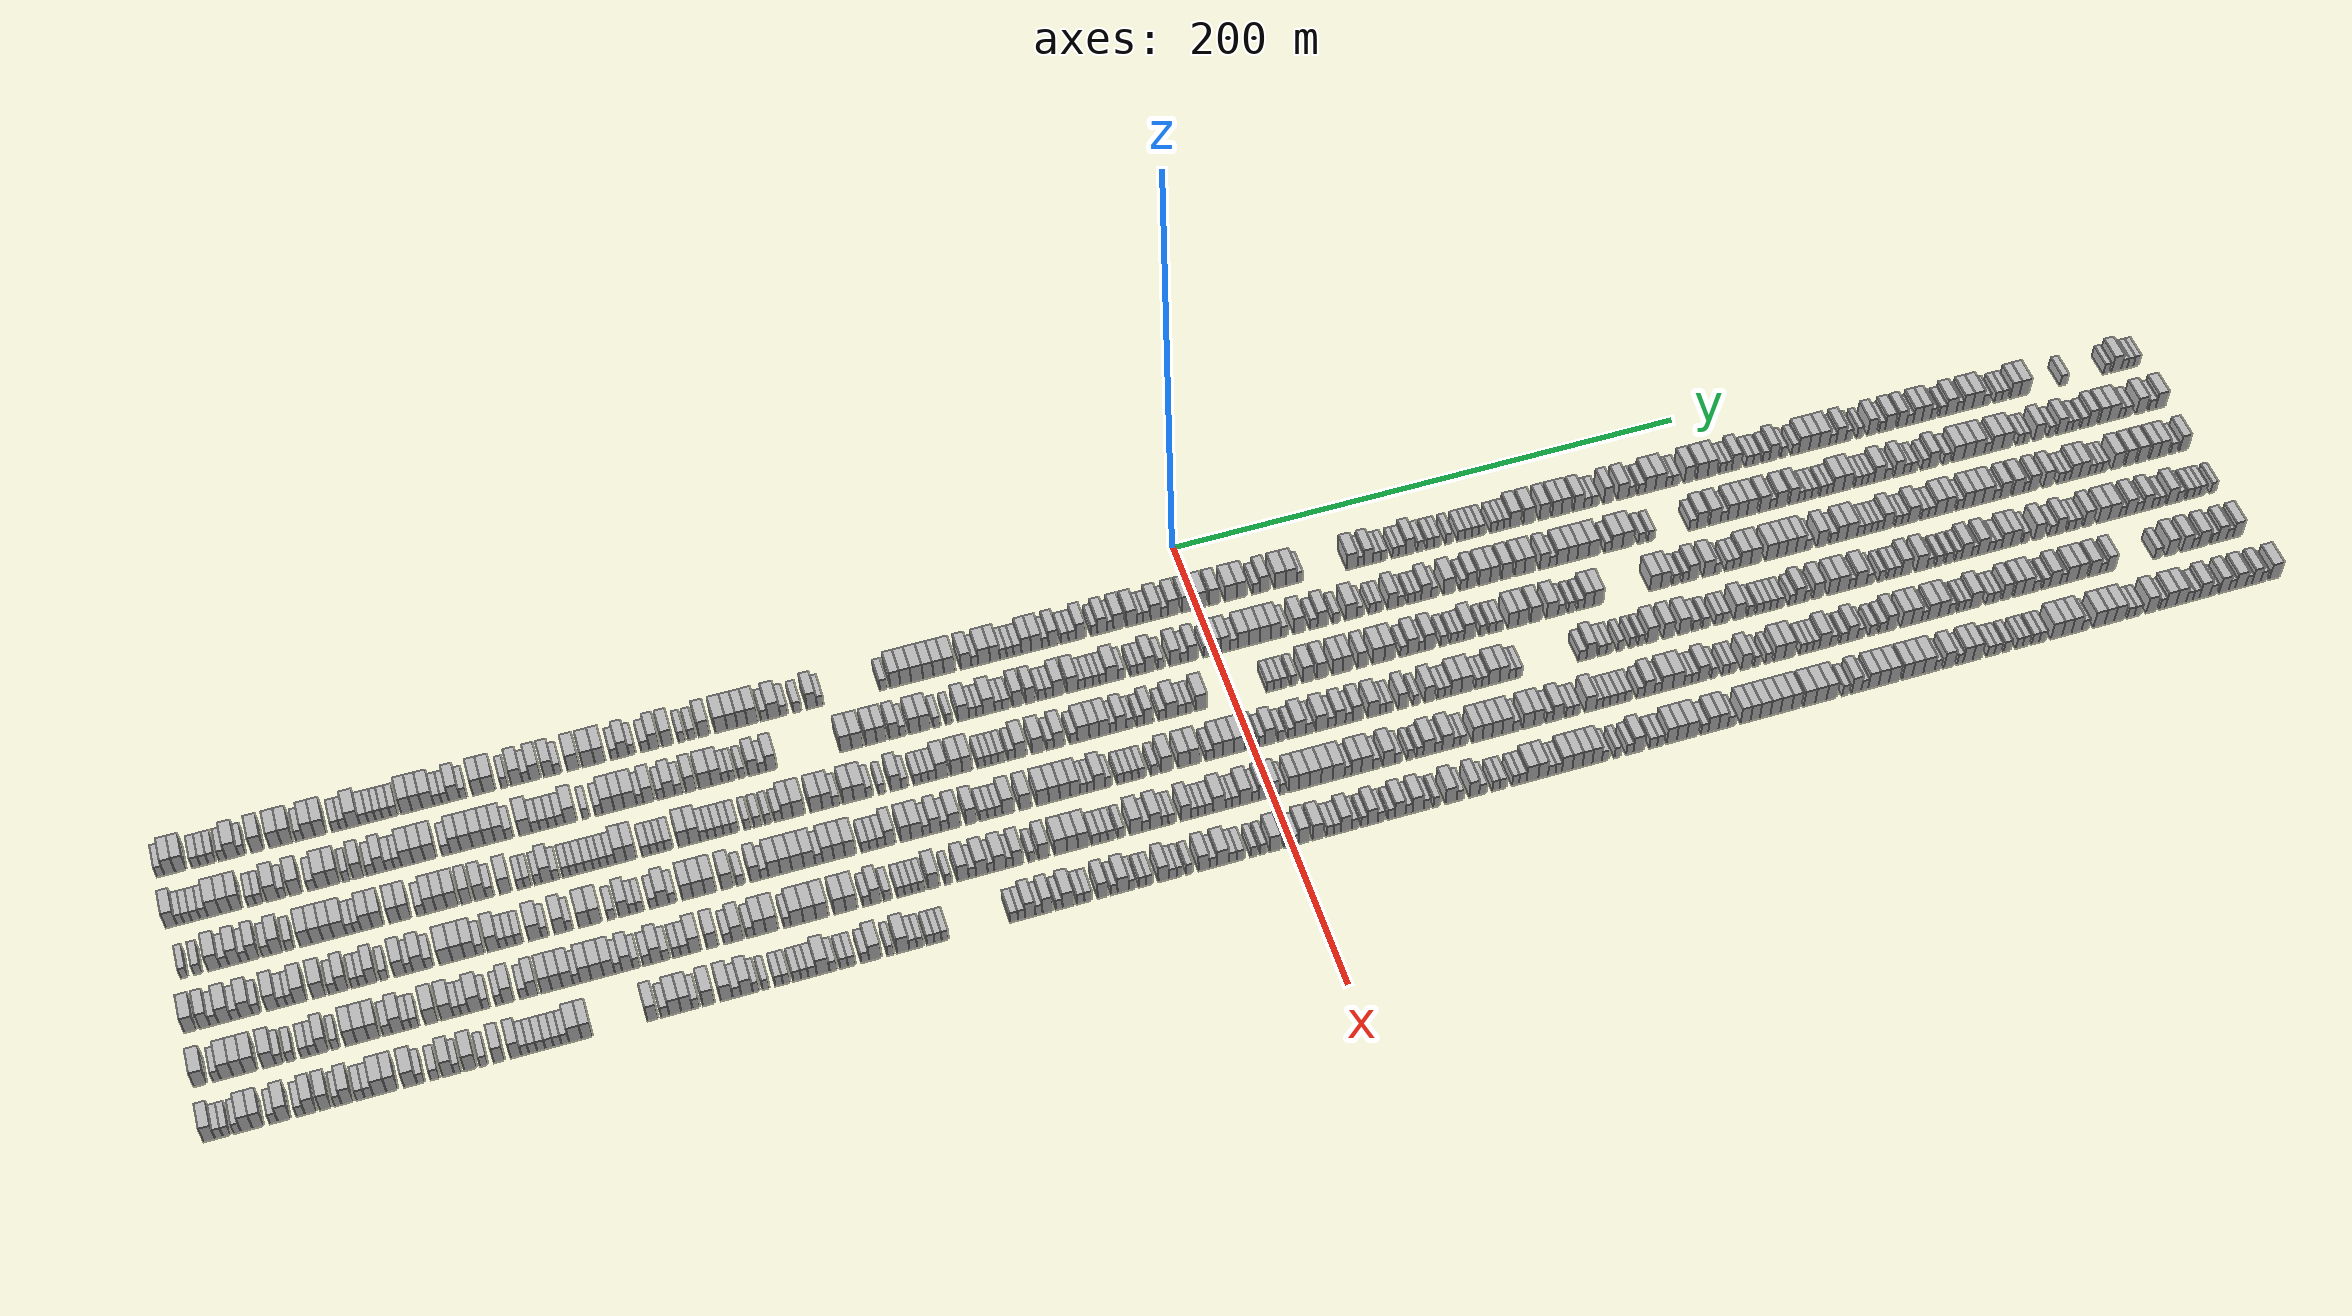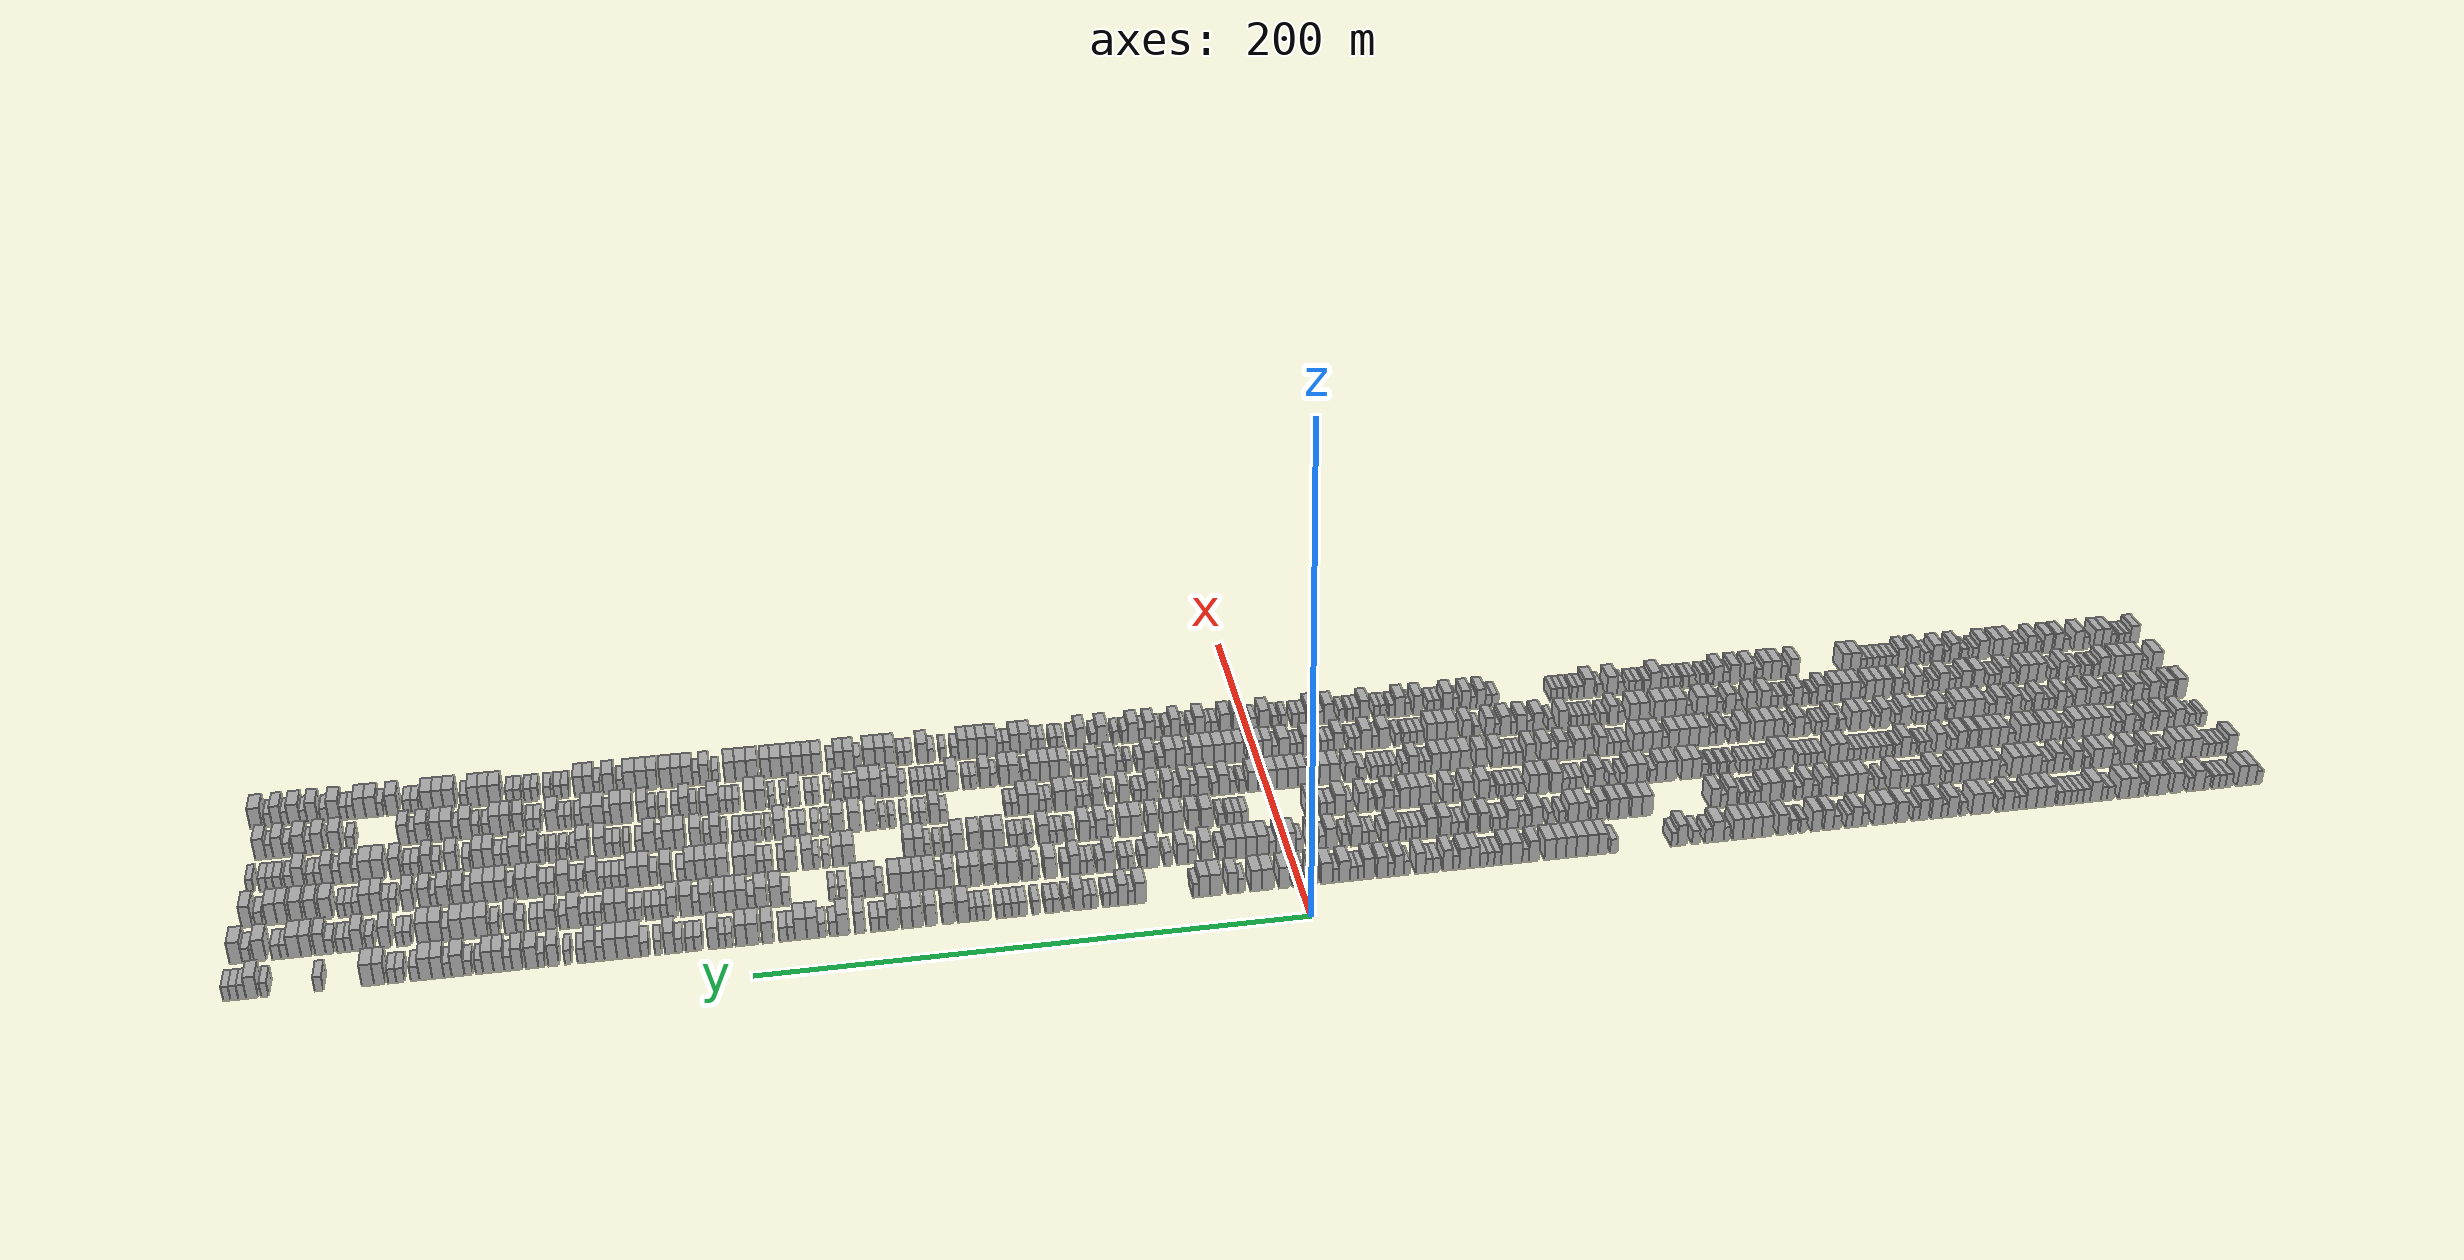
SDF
<sdf version="1.6">
 <world name="default">
  <scene>
   <sky><clouds><speed>12</speed></clouds></sky>
   <ambient>0.4 0.4 0.4 1</ambient>
   <background>0.7 0.7 0.7 1</background>
   <shadows>1</shadows>
  </scene>
  <gravity>0 0 -9.8066</gravity>
  <magnetic_field>6e-06 2.3e-05 -4.2e-05</magnetic_field>
  <physics default="0" name="default_physics" type="ode">
   <ode>
    <solver>
     <type>quick</type>
     <iters>10</iters>
     <sor>1.0</sor>
     <use_dynamic_moi_rescaling>0</use_dynamic_moi_rescaling>
    </solver>
    <constraints>
     <cfm>0</cfm>
     <erp>0.2</erp>
     <contact_max_correcting_vel>100</contact_max_correcting_vel>
     <contact_surface_layer>0.001</contact_surface_layer>
    </constraints>
   </ode>
   <max_step_size>0.004</max_step_size>
   <real_time_factor>1</real_time_factor>
   <real_time_update_rate>250</real_time_update_rate>
  </physics>
  <light name="sun" type="directional">
   <pose>0 0 10 0 0 0</pose>
   <diffuse>0.8 0.8 0.8 1</diffuse>
   <specular>0.2 0.2 0.2 1</specular>
   <attenuation>
    <range>1000</range>
    <constant>0.9</constant>
    <linear>0.01</linear>
    <quadratic>0.001</quadratic>
   </attenuation>
   <direction>-0.5 0.1 -0.9</direction>
  </light>
  <model name="building_1">
   <static>1</static>
   <pose>25.0000 -378.6600 0 0.000000 0.000000 0.000000</pose>
   <link name="link">
    <pose>0 0 3.00 0 0 0</pose>
    <collision name="collision"><geometry><box><size>10.0000 2.6799 6.0000</size></box></geometry></collision>
    <visual name="visual">
     <cast_shadows>0</cast_shadows>
     <geometry><box><size>10.0000 2.6799 6.0000</size></box></geometry>
     <material>
      <script>
       <uri>model://HANNAS_wall/materials/scripts</uri>
       <uri>model://HANNAS_wall/materials/textures</uri>
       <name>vrc/HANNAS_wall</name>
      </script>
     </material>
    </visual>
   </link>
  </model>
  <model name="building_2">
   <static>1</static>
   <pose>25.0000 -375.4495 0 0.000000 0.000000 0.000000</pose>
   <link name="link">
    <pose>0 0 4.50 0 0 0</pose>
    <collision name="collision"><geometry><box><size>10.0000 3.7410 9.0000</size></box></geometry></collision>
    <visual name="visual">
     <cast_shadows>0</cast_shadows>
     <geometry><box><size>10.0000 3.7410 9.0000</size></box></geometry>
     <material>
      <script>
       <uri>model://HANNAS_wall/materials/scripts</uri>
       <uri>model://HANNAS_wall/materials/textures</uri>
       <name>vrc/HANNAS_wall</name>
      </script>
     </material>
    </visual>
   </link>
  </model>
  <model name="building_3">
   <static>1</static>
   <pose>25.0000 -371.6443 0 0.000000 0.000000 0.000000</pose>
   <link name="link">
    <pose>0 0 4.50 0 0 0</pose>
    <collision name="collision"><geometry><box><size>10.0000 3.8694 9.0000</size></box></geometry></collision>
    <visual name="visual">
     <cast_shadows>0</cast_shadows>
     <geometry><box><size>10.0000 3.8694 9.0000</size></box></geometry>
     <material>
      <script>
       <uri>model://HANNAS_wall/materials/scripts</uri>
       <uri>model://HANNAS_wall/materials/textures</uri>
       <name>vrc/HANNAS_wall</name>
      </script>
     </material>
    </visual>
   </link>
  </model>
  <model name="building_4">
   <static>1</static>
   <pose>25.0000 -366.2913 0 0.000000 0.000000 0.000000</pose>
   <link name="link">
    <pose>0 0 3.00 0 0 0</pose>
    <collision name="collision"><geometry><box><size>10.0000 2.8366 6.0000</size></box></geometry></collision>
    <visual name="visual">
     <cast_shadows>0</cast_shadows>
     <geometry><box><size>10.0000 2.8366 6.0000</size></box></geometry>
     <material>
      <script>
       <uri>model://HANNAS_wall/materials/scripts</uri>
       <uri>model://HANNAS_wall/materials/textures</uri>
       <name>vrc/HANNAS_wall</name>
      </script>
     </material>
    </visual>
   </link>
  </model>
  <model name="building_5">
   <static>1</static>
   <pose>25.0000 -363.4804 0 0.000000 0.000000 0.000000</pose>
   <link name="link">
    <pose>0 0 3.00 0 0 0</pose>
    <collision name="collision"><geometry><box><size>10.0000 2.7850 6.0000</size></box></geometry></collision>
    <visual name="visual">
     <cast_shadows>0</cast_shadows>
     <geometry><box><size>10.0000 2.7850 6.0000</size></box></geometry>
     <material>
      <script>
       <uri>model://HANNAS_wall/materials/scripts</uri>
       <uri>model://HANNAS_wall/materials/textures</uri>
       <name>vrc/HANNAS_wall</name>
      </script>
     </material>
    </visual>
   </link>
  </model>
  <model name="building_6">
   <static>1</static>
   <pose>25.0000 -360.7322 0 0.000000 0.000000 0.000000</pose>
   <link name="link">
    <pose>0 0 3.00 0 0 0</pose>
    <collision name="collision"><geometry><box><size>10.0000 2.7115 6.0000</size></box></geometry></collision>
    <visual name="visual">
     <cast_shadows>0</cast_shadows>
     <geometry><box><size>10.0000 2.7115 6.0000</size></box></geometry>
     <material>
      <script>
       <uri>model://HANNAS_wall/materials/scripts</uri>
       <uri>model://HANNAS_wall/materials/textures</uri>
       <name>vrc/HANNAS_wall</name>
      </script>
     </material>
    </visual>
   </link>
  </model>
  <model name="building_7">
   <static>1</static>
   <pose>25.0000 -357.1017 0 0.000000 0.000000 0.000000</pose>
   <link name="link">
    <pose>0 0 3.00 0 0 0</pose>
    <collision name="collision"><geometry><box><size>10.0000 2.5496 6.0000</size></box></geometry></collision>
    <visual name="visual">
     <cast_shadows>0</cast_shadows>
     <geometry><box><size>10.0000 2.5496 6.0000</size></box></geometry>
     <material>
      <script>
       <uri>model://HANNAS_wall/materials/scripts</uri>
       <uri>model://HANNAS_wall/materials/textures</uri>
       <name>vrc/HANNAS_wall</name>
      </script>
     </material>
    </visual>
   </link>
  </model>
  <model name="building_8">
   <static>1</static>
   <pose>25.0000 -353.6264 0 0.000000 0.000000 0.000000</pose>
   <link name="link">
    <pose>0 0 4.50 0 0 0</pose>
    <collision name="collision"><geometry><box><size>10.0000 4.4009 9.0000</size></box></geometry></collision>
    <visual name="visual">
     <cast_shadows>0</cast_shadows>
     <geometry><box><size>10.0000 4.4009 9.0000</size></box></geometry>
     <material>
      <script>
       <uri>model://HANNAS_wall/materials/scripts</uri>
       <uri>model://HANNAS_wall/materials/textures</uri>
       <name>vrc/HANNAS_wall</name>
      </script>
     </material>
    </visual>
   </link>
  </model>
  <model name="building_9">
   <static>1</static>
   <pose>25.0000 -350.2114 0 0.000000 0.000000 0.000000</pose>
   <link name="link">
    <pose>0 0 3.00 0 0 0</pose>
    <collision name="collision"><geometry><box><size>10.0000 2.4290 6.0000</size></box></geometry></collision>
    <visual name="visual">
     <cast_shadows>0</cast_shadows>
     <geometry><box><size>10.0000 2.4290 6.0000</size></box></geometry>
     <material>
      <script>
       <uri>model://HANNAS_wall/materials/scripts</uri>
       <uri>model://HANNAS_wall/materials/textures</uri>
       <name>vrc/HANNAS_wall</name>
      </script>
     </material>
    </visual>
   </link>
  </model>
  <model name="building_10">
   <static>1</static>
   <pose>25.0000 -344.8356 0 0.000000 0.000000 0.000000</pose>
   <link name="link">
    <pose>0 0 4.50 0 0 0</pose>
    <collision name="collision"><geometry><box><size>10.0000 4.3227 9.0000</size></box></geometry></collision>
    <visual name="visual">
     <cast_shadows>0</cast_shadows>
     <geometry><box><size>10.0000 4.3227 9.0000</size></box></geometry>
     <material>
      <script>
       <uri>model://HANNAS_wall/materials/scripts</uri>
       <uri>model://HANNAS_wall/materials/textures</uri>
       <name>vrc/HANNAS_wall</name>
      </script>
     </material>
    </visual>
   </link>
  </model>
  <model name="building_11">
   <static>1</static>
   <pose>25.0000 -338.5897 0 0.000000 0.000000 0.000000</pose>
   <link name="link">
    <pose>0 0 4.50 0 0 0</pose>
    <collision name="collision"><geometry><box><size>10.0000 4.1690 9.0000</size></box></geometry></collision>
    <visual name="visual">
     <cast_shadows>0</cast_shadows>
     <geometry><box><size>10.0000 4.1690 9.0000</size></box></geometry>
     <material>
      <script>
       <uri>model://HANNAS_wall/materials/scripts</uri>
       <uri>model://HANNAS_wall/materials/textures</uri>
       <name>vrc/HANNAS_wall</name>
      </script>
     </material>
    </visual>
   </link>
  </model>
  <model name="building_12">
   <static>1</static>
   <pose>25.0000 -334.4752 0 0.000000 0.000000 0.000000</pose>
   <link name="link">
    <pose>0 0 4.50 0 0 0</pose>
    <collision name="collision"><geometry><box><size>10.0000 4.0601 9.0000</size></box></geometry></collision>
    <visual name="visual">
     <cast_shadows>0</cast_shadows>
     <geometry><box><size>10.0000 4.0601 9.0000</size></box></geometry>
     <material>
      <script>
       <uri>model://HANNAS_wall/materials/scripts</uri>
       <uri>model://HANNAS_wall/materials/textures</uri>
       <name>vrc/HANNAS_wall</name>
      </script>
     </material>
    </visual>
   </link>
  </model>
  <model name="building_13">
   <static>1</static>
   <pose>25.0000 -330.1138 0 0.000000 0.000000 0.000000</pose>
   <link name="link">
    <pose>0 0 3.00 0 0 0</pose>
    <collision name="collision"><geometry><box><size>10.0000 2.6627 6.0000</size></box></geometry></collision>
    <visual name="visual">
     <cast_shadows>0</cast_shadows>
     <geometry><box><size>10.0000 2.6627 6.0000</size></box></geometry>
     <material>
      <script>
       <uri>model://HANNAS_wall/materials/scripts</uri>
       <uri>model://HANNAS_wall/materials/textures</uri>
       <name>vrc/HANNAS_wall</name>
      </script>
     </material>
    </visual>
   </link>
  </model>
  <model name="building_14">
   <static>1</static>
   <pose>25.0000 -326.7637 0 0.000000 0.000000 0.000000</pose>
   <link name="link">
    <pose>0 0 4.50 0 0 0</pose>
    <collision name="collision"><geometry><box><size>10.0000 4.0375 9.0000</size></box></geometry></collision>
    <visual name="visual">
     <cast_shadows>0</cast_shadows>
     <geometry><box><size>10.0000 4.0375 9.0000</size></box></geometry>
     <material>
      <script>
       <uri>model://HANNAS_wall/materials/scripts</uri>
       <uri>model://HANNAS_wall/materials/textures</uri>
       <name>vrc/HANNAS_wall</name>
      </script>
     </material>
    </visual>
   </link>
  </model>
  <model name="building_15">
   <static>1</static>
   <pose>25.0000 -322.7185 0 0.000000 0.000000 0.000000</pose>
   <link name="link">
    <pose>0 0 4.50 0 0 0</pose>
    <collision name="collision"><geometry><box><size>10.0000 4.0528 9.0000</size></box></geometry></collision>
    <visual name="visual">
     <cast_shadows>0</cast_shadows>
     <geometry><box><size>10.0000 4.0528 9.0000</size></box></geometry>
     <material>
      <script>
       <uri>model://HANNAS_wall/materials/scripts</uri>
       <uri>model://HANNAS_wall/materials/textures</uri>
       <name>vrc/HANNAS_wall</name>
      </script>
     </material>
    </visual>
   </link>
  </model>
  <model name="building_16">
   <static>1</static>
   <pose>25.0000 -317.2784 0 0.000000 0.000000 0.000000</pose>
   <link name="link">
    <pose>0 0 3.00 0 0 0</pose>
    <collision name="collision"><geometry><box><size>10.0000 2.8274 6.0000</size></box></geometry></collision>
    <visual name="visual">
     <cast_shadows>0</cast_shadows>
     <geometry><box><size>10.0000 2.8274 6.0000</size></box></geometry>
     <material>
      <script>
       <uri>model://HANNAS_wall/materials/scripts</uri>
       <uri>model://HANNAS_wall/materials/textures</uri>
       <name>vrc/HANNAS_wall</name>
      </script>
     </material>
    </visual>
   </link>
  </model>
  <model name="building_17">
   <static>1</static>
   <pose>25.0000 -314.6513 0 0.000000 0.000000 0.000000</pose>
   <link name="link">
    <pose>0 0 3.00 0 0 0</pose>
    <collision name="collision"><geometry><box><size>10.0000 2.4268 6.0000</size></box></geometry></collision>
    <visual name="visual">
     <cast_shadows>0</cast_shadows>
     <geometry><box><size>10.0000 2.4268 6.0000</size></box></geometry>
     <material>
      <script>
       <uri>model://HANNAS_wall/materials/scripts</uri>
       <uri>model://HANNAS_wall/materials/textures</uri>
       <name>vrc/HANNAS_wall</name>
      </script>
     </material>
    </visual>
   </link>
  </model>
  <model name="building_18">
   <static>1</static>
   <pose>25.0000 -311.1901 0 0.000000 0.000000 0.000000</pose>
   <link name="link">
    <pose>0 0 4.50 0 0 0</pose>
    <collision name="collision"><geometry><box><size>10.0000 4.4955 9.0000</size></box></geometry></collision>
    <visual name="visual">
     <cast_shadows>0</cast_shadows>
     <geometry><box><size>10.0000 4.4955 9.0000</size></box></geometry>
     <material>
      <script>
       <uri>model://HANNAS_wall/materials/scripts</uri>
       <uri>model://HANNAS_wall/materials/textures</uri>
       <name>vrc/HANNAS_wall</name>
      </script>
     </material>
    </visual>
   </link>
  </model>
  <model name="building_19">
   <static>1</static>
   <pose>25.0000 -307.4517 0 0.000000 0.000000 0.000000</pose>
   <link name="link">
    <pose>0 0 3.00 0 0 0</pose>
    <collision name="collision"><geometry><box><size>10.0000 2.9812 6.0000</size></box></geometry></collision>
    <visual name="visual">
     <cast_shadows>0</cast_shadows>
     <geometry><box><size>10.0000 2.9812 6.0000</size></box></geometry>
     <material>
      <script>
       <uri>model://HANNAS_wall/materials/scripts</uri>
       <uri>model://HANNAS_wall/materials/textures</uri>
       <name>vrc/HANNAS_wall</name>
      </script>
     </material>
    </visual>
   </link>
  </model>
  <model name="building_20">
   <static>1</static>
   <pose>25.0000 -304.6713 0 0.000000 0.000000 0.000000</pose>
   <link name="link">
    <pose>0 0 3.00 0 0 0</pose>
    <collision name="collision"><geometry><box><size>10.0000 2.5797 6.0000</size></box></geometry></collision>
    <visual name="visual">
     <cast_shadows>0</cast_shadows>
     <geometry><box><size>10.0000 2.5797 6.0000</size></box></geometry>
     <material>
      <script>
       <uri>model://HANNAS_wall/materials/scripts</uri>
       <uri>model://HANNAS_wall/materials/textures</uri>
       <name>vrc/HANNAS_wall</name>
      </script>
     </material>
    </visual>
   </link>
  </model>
  <model name="building_21">
   <static>1</static>
   <pose>25.0000 -302.1477 0 0.000000 0.000000 0.000000</pose>
   <link name="link">
    <pose>0 0 3.00 0 0 0</pose>
    <collision name="collision"><geometry><box><size>10.0000 2.4675 6.0000</size></box></geometry></collision>
    <visual name="visual">
     <cast_shadows>0</cast_shadows>
     <geometry><box><size>10.0000 2.4675 6.0000</size></box></geometry>
     <material>
      <script>
       <uri>model://HANNAS_wall/materials/scripts</uri>
       <uri>model://HANNAS_wall/materials/textures</uri>
       <name>vrc/HANNAS_wall</name>
      </script>
     </material>
    </visual>
   </link>
  </model>
  <model name="building_22">
   <static>1</static>
   <pose>25.0000 -299.4982 0 0.000000 0.000000 0.000000</pose>
   <link name="link">
    <pose>0 0 3.00 0 0 0</pose>
    <collision name="collision"><geometry><box><size>10.0000 2.8315 6.0000</size></box></geometry></collision>
    <visual name="visual">
     <cast_shadows>0</cast_shadows>
     <geometry><box><size>10.0000 2.8315 6.0000</size></box></geometry>
     <material>
      <script>
       <uri>model://HANNAS_wall/materials/scripts</uri>
       <uri>model://HANNAS_wall/materials/textures</uri>
       <name>vrc/HANNAS_wall</name>
      </script>
     </material>
    </visual>
   </link>
  </model>
  <model name="building_23">
   <static>1</static>
   <pose>25.0000 -296.7344 0 0.000000 0.000000 0.000000</pose>
   <link name="link">
    <pose>0 0 3.00 0 0 0</pose>
    <collision name="collision"><geometry><box><size>10.0000 2.6960 6.0000</size></box></geometry></collision>
    <visual name="visual">
     <cast_shadows>0</cast_shadows>
     <geometry><box><size>10.0000 2.6960 6.0000</size></box></geometry>
     <material>
      <script>
       <uri>model://HANNAS_wall/materials/scripts</uri>
       <uri>model://HANNAS_wall/materials/textures</uri>
       <name>vrc/HANNAS_wall</name>
      </script>
     </material>
    </visual>
   </link>
  </model>
  <model name="building_24">
   <static>1</static>
   <pose>25.0000 -292.4410 0 0.000000 0.000000 0.000000</pose>
   <link name="link">
    <pose>0 0 4.50 0 0 0</pose>
    <collision name="collision"><geometry><box><size>10.0000 3.8909 9.0000</size></box></geometry></collision>
    <visual name="visual">
     <cast_shadows>0</cast_shadows>
     <geometry><box><size>10.0000 3.8909 9.0000</size></box></geometry>
     <material>
      <script>
       <uri>model://HANNAS_wall/materials/scripts</uri>
       <uri>model://HANNAS_wall/materials/textures</uri>
       <name>vrc/HANNAS_wall</name>
      </script>
     </material>
    </visual>
   </link>
  </model>
  <model name="building_25">
   <static>1</static>
   <pose>25.0000 -288.6724 0 0.000000 0.000000 0.000000</pose>
   <link name="link">
    <pose>0 0 4.50 0 0 0</pose>
    <collision name="collision"><geometry><box><size>10.0000 3.6461 9.0000</size></box></geometry></collision>
    <visual name="visual">
     <cast_shadows>0</cast_shadows>
     <geometry><box><size>10.0000 3.6461 9.0000</size></box></geometry>
     <material>
      <script>
       <uri>model://HANNAS_wall/materials/scripts</uri>
       <uri>model://HANNAS_wall/materials/textures</uri>
       <name>vrc/HANNAS_wall</name>
      </script>
     </material>
    </visual>
   </link>
  </model>
  <model name="building_26">
   <static>1</static>
   <pose>25.0000 -284.7584 0 0.000000 0.000000 0.000000</pose>
   <link name="link">
    <pose>0 0 4.50 0 0 0</pose>
    <collision name="collision"><geometry><box><size>10.0000 4.1821 9.0000</size></box></geometry></collision>
    <visual name="visual">
     <cast_shadows>0</cast_shadows>
     <geometry><box><size>10.0000 4.1821 9.0000</size></box></geometry>
     <material>
      <script>
       <uri>model://HANNAS_wall/materials/scripts</uri>
       <uri>model://HANNAS_wall/materials/textures</uri>
       <name>vrc/HANNAS_wall</name>
      </script>
     </material>
    </visual>
   </link>
  </model>
  <model name="building_27">
   <static>1</static>
   <pose>25.0000 -281.2777 0 0.000000 0.000000 0.000000</pose>
   <link name="link">
    <pose>0 0 3.00 0 0 0</pose>
    <collision name="collision"><geometry><box><size>10.0000 2.7793 6.0000</size></box></geometry></collision>
    <visual name="visual">
     <cast_shadows>0</cast_shadows>
     <geometry><box><size>10.0000 2.7793 6.0000</size></box></geometry>
     <material>
      <script>
       <uri>model://HANNAS_wall/materials/scripts</uri>
       <uri>model://HANNAS_wall/materials/textures</uri>
       <name>vrc/HANNAS_wall</name>
      </script>
     </material>
    </visual>
   </link>
  </model>
  <model name="building_28">
   <static>1</static>
   <pose>25.0000 -278.6364 0 0.000000 0.000000 0.000000</pose>
   <link name="link">
    <pose>0 0 3.00 0 0 0</pose>
    <collision name="collision"><geometry><box><size>10.0000 2.5034 6.0000</size></box></geometry></collision>
    <visual name="visual">
     <cast_shadows>0</cast_shadows>
     <geometry><box><size>10.0000 2.5034 6.0000</size></box></geometry>
     <material>
      <script>
       <uri>model://HANNAS_wall/materials/scripts</uri>
       <uri>model://HANNAS_wall/materials/textures</uri>
       <name>vrc/HANNAS_wall</name>
      </script>
     </material>
    </visual>
   </link>
  </model>
  <model name="building_29">
   <static>1</static>
   <pose>25.0000 -275.3839 0 0.000000 0.000000 0.000000</pose>
   <link name="link">
    <pose>0 0 4.50 0 0 0</pose>
    <collision name="collision"><geometry><box><size>10.0000 4.0015 9.0000</size></box></geometry></collision>
    <visual name="visual">
     <cast_shadows>0</cast_shadows>
     <geometry><box><size>10.0000 4.0015 9.0000</size></box></geometry>
     <material>
      <script>
       <uri>model://HANNAS_wall/materials/scripts</uri>
       <uri>model://HANNAS_wall/materials/textures</uri>
       <name>vrc/HANNAS_wall</name>
      </script>
     </material>
    </visual>
   </link>
  </model>
  <model name="building_30">
   <static>1</static>
   <pose>25.0000 -272.1171 0 0.000000 0.000000 0.000000</pose>
   <link name="link">
    <pose>0 0 3.00 0 0 0</pose>
    <collision name="collision"><geometry><box><size>10.0000 2.5321 6.0000</size></box></geometry></collision>
    <visual name="visual">
     <cast_shadows>0</cast_shadows>
     <geometry><box><size>10.0000 2.5321 6.0000</size></box></geometry>
     <material>
      <script>
       <uri>model://HANNAS_wall/materials/scripts</uri>
       <uri>model://HANNAS_wall/materials/textures</uri>
       <name>vrc/HANNAS_wall</name>
      </script>
     </material>
    </visual>
   </link>
  </model>
  <model name="building_31">
   <static>1</static>
   <pose>25.0000 -266.9588 0 0.000000 0.000000 0.000000</pose>
   <link name="link">
    <pose>0 0 4.50 0 0 0</pose>
    <collision name="collision"><geometry><box><size>10.0000 3.7845 9.0000</size></box></geometry></collision>
    <visual name="visual">
     <cast_shadows>0</cast_shadows>
     <geometry><box><size>10.0000 3.7845 9.0000</size></box></geometry>
     <material>
      <script>
       <uri>model://HANNAS_wall/materials/scripts</uri>
       <uri>model://HANNAS_wall/materials/textures</uri>
       <name>vrc/HANNAS_wall</name>
      </script>
     </material>
    </visual>
   </link>
  </model>
  <model name="building_32">
   <static>1</static>
   <pose>25.0000 -262.8703 0 0.000000 0.000000 0.000000</pose>
   <link name="link">
    <pose>0 0 4.50 0 0 0</pose>
    <collision name="collision"><geometry><box><size>10.0000 4.3926 9.0000</size></box></geometry></collision>
    <visual name="visual">
     <cast_shadows>0</cast_shadows>
     <geometry><box><size>10.0000 4.3926 9.0000</size></box></geometry>
     <material>
      <script>
       <uri>model://HANNAS_wall/materials/scripts</uri>
       <uri>model://HANNAS_wall/materials/textures</uri>
       <name>vrc/HANNAS_wall</name>
      </script>
     </material>
    </visual>
   </link>
  </model>
  <model name="building_33">
   <static>1</static>
   <pose>25.0000 -257.3927 0 0.000000 0.000000 0.000000</pose>
   <link name="link">
    <pose>0 0 3.00 0 0 0</pose>
    <collision name="collision"><geometry><box><size>10.0000 2.5626 6.0000</size></box></geometry></collision>
    <visual name="visual">
     <cast_shadows>0</cast_shadows>
     <geometry><box><size>10.0000 2.5626 6.0000</size></box></geometry>
     <material>
      <script>
       <uri>model://HANNAS_wall/materials/scripts</uri>
       <uri>model://HANNAS_wall/materials/textures</uri>
       <name>vrc/HANNAS_wall</name>
      </script>
     </material>
    </visual>
   </link>
  </model>
  <model name="building_34">
   <static>1</static>
   <pose>25.0000 -253.0505 0 0.000000 0.000000 0.000000</pose>
   <link name="link">
    <pose>0 0 4.50 0 0 0</pose>
    <collision name="collision"><geometry><box><size>10.0000 4.1217 9.0000</size></box></geometry></collision>
    <visual name="visual">
     <cast_shadows>0</cast_shadows>
     <geometry><box><size>10.0000 4.1217 9.0000</size></box></geometry>
     <material>
      <script>
       <uri>model://HANNAS_wall/materials/scripts</uri>
       <uri>model://HANNAS_wall/materials/textures</uri>
       <name>vrc/HANNAS_wall</name>
      </script>
     </material>
    </visual>
   </link>
  </model>
  <model name="building_35">
   <static>1</static>
   <pose>25.0000 -249.6613 0 0.000000 0.000000 0.000000</pose>
   <link name="link">
    <pose>0 0 3.00 0 0 0</pose>
    <collision name="collision"><geometry><box><size>10.0000 2.6567 6.0000</size></box></geometry></collision>
    <visual name="visual">
     <cast_shadows>0</cast_shadows>
     <geometry><box><size>10.0000 2.6567 6.0000</size></box></geometry>
     <material>
      <script>
       <uri>model://HANNAS_wall/materials/scripts</uri>
       <uri>model://HANNAS_wall/materials/textures</uri>
       <name>vrc/HANNAS_wall</name>
      </script>
     </material>
    </visual>
   </link>
  </model>
  <model name="building_36">
   <static>1</static>
   <pose>25.0000 -246.3423 0 0.000000 0.000000 0.000000</pose>
   <link name="link">
    <pose>0 0 4.50 0 0 0</pose>
    <collision name="collision"><geometry><box><size>10.0000 3.9813 9.0000</size></box></geometry></collision>
    <visual name="visual">
     <cast_shadows>0</cast_shadows>
     <geometry><box><size>10.0000 3.9813 9.0000</size></box></geometry>
     <material>
      <script>
       <uri>model://HANNAS_wall/materials/scripts</uri>
       <uri>model://HANNAS_wall/materials/textures</uri>
       <name>vrc/HANNAS_wall</name>
      </script>
     </material>
    </visual>
   </link>
  </model>
  <model name="building_37">
   <static>1</static>
   <pose>25.0000 -241.4669 0 0.000000 0.000000 0.000000</pose>
   <link name="link">
    <pose>0 0 4.50 0 0 0</pose>
    <collision name="collision"><geometry><box><size>10.0000 3.7695 9.0000</size></box></geometry></collision>
    <visual name="visual">
     <cast_shadows>0</cast_shadows>
     <geometry><box><size>10.0000 3.7695 9.0000</size></box></geometry>
     <material>
      <script>
       <uri>model://HANNAS_wall/materials/scripts</uri>
       <uri>model://HANNAS_wall/materials/textures</uri>
       <name>vrc/HANNAS_wall</name>
      </script>
     </material>
    </visual>
   </link>
  </model>
  <model name="building_38">
   <static>1</static>
   <pose>25.0000 -238.2289 0 0.000000 0.000000 0.000000</pose>
   <link name="link">
    <pose>0 0 3.00 0 0 0</pose>
    <collision name="collision"><geometry><box><size>10.0000 2.7064 6.0000</size></box></geometry></collision>
    <visual name="visual">
     <cast_shadows>0</cast_shadows>
     <geometry><box><size>10.0000 2.7064 6.0000</size></box></geometry>
     <material>
      <script>
       <uri>model://HANNAS_wall/materials/scripts</uri>
       <uri>model://HANNAS_wall/materials/textures</uri>
       <name>vrc/HANNAS_wall</name>
      </script>
     </material>
    </visual>
   </link>
  </model>
  <model name="building_39">
   <static>1</static>
   <pose>25.0000 -232.6431 0 0.000000 0.000000 0.000000</pose>
   <link name="link">
    <pose>0 0 4.50 0 0 0</pose>
    <collision name="collision"><geometry><box><size>10.0000 4.4654 9.0000</size></box></geometry></collision>
    <visual name="visual">
     <cast_shadows>0</cast_shadows>
     <geometry><box><size>10.0000 4.4654 9.0000</size></box></geometry>
     <material>
      <script>
       <uri>model://HANNAS_wall/materials/scripts</uri>
       <uri>model://HANNAS_wall/materials/textures</uri>
       <name>vrc/HANNAS_wall</name>
      </script>
     </material>
    </visual>
   </link>
  </model>
  <model name="building_40">
   <static>1</static>
   <pose>25.0000 -227.1683 0 0.000000 0.000000 0.000000</pose>
   <link name="link">
    <pose>0 0 4.50 0 0 0</pose>
    <collision name="collision"><geometry><box><size>10.0000 4.4841 9.0000</size></box></geometry></collision>
    <visual name="visual">
     <cast_shadows>0</cast_shadows>
     <geometry><box><size>10.0000 4.4841 9.0000</size></box></geometry>
     <material>
      <script>
       <uri>model://HANNAS_wall/materials/scripts</uri>
       <uri>model://HANNAS_wall/materials/textures</uri>
       <name>vrc/HANNAS_wall</name>
      </script>
     </material>
    </visual>
   </link>
  </model>
  <model name="building_41">
   <static>1</static>
   <pose>25.0000 -223.0183 0 0.000000 0.000000 0.000000</pose>
   <link name="link">
    <pose>0 0 4.50 0 0 0</pose>
    <collision name="collision"><geometry><box><size>10.0000 3.8158 9.0000</size></box></geometry></collision>
    <visual name="visual">
     <cast_shadows>0</cast_shadows>
     <geometry><box><size>10.0000 3.8158 9.0000</size></box></geometry>
     <material>
      <script>
       <uri>model://HANNAS_wall/materials/scripts</uri>
       <uri>model://HANNAS_wall/materials/textures</uri>
       <name>vrc/HANNAS_wall</name>
      </script>
     </material>
    </visual>
   </link>
  </model>
  <model name="building_42">
   <static>1</static>
   <pose>25.0000 -217.7820 0 0.000000 0.000000 0.000000</pose>
   <link name="link">
    <pose>0 0 3.00 0 0 0</pose>
    <collision name="collision"><geometry><box><size>10.0000 2.6568 6.0000</size></box></geometry></collision>
    <visual name="visual">
     <cast_shadows>0</cast_shadows>
     <geometry><box><size>10.0000 2.6568 6.0000</size></box></geometry>
     <material>
      <script>
       <uri>model://HANNAS_wall/materials/scripts</uri>
       <uri>model://HANNAS_wall/materials/textures</uri>
       <name>vrc/HANNAS_wall</name>
      </script>
     </material>
    </visual>
   </link>
  </model>
  <model name="building_43">
   <static>1</static>
   <pose>25.0000 -214.5450 0 0.000000 0.000000 0.000000</pose>
   <link name="link">
    <pose>0 0 4.50 0 0 0</pose>
    <collision name="collision"><geometry><box><size>10.0000 3.8174 9.0000</size></box></geometry></collision>
    <visual name="visual">
     <cast_shadows>0</cast_shadows>
     <geometry><box><size>10.0000 3.8174 9.0000</size></box></geometry>
     <material>
      <script>
       <uri>model://HANNAS_wall/materials/scripts</uri>
       <uri>model://HANNAS_wall/materials/textures</uri>
       <name>vrc/HANNAS_wall</name>
      </script>
     </material>
    </visual>
   </link>
  </model>
  <model name="building_44">
   <static>1</static>
   <pose>25.0000 -211.3935 0 0.000000 0.000000 0.000000</pose>
   <link name="link">
    <pose>0 0 3.00 0 0 0</pose>
    <collision name="collision"><geometry><box><size>10.0000 2.4856 6.0000</size></box></geometry></collision>
    <visual name="visual">
     <cast_shadows>0</cast_shadows>
     <geometry><box><size>10.0000 2.4856 6.0000</size></box></geometry>
     <material>
      <script>
       <uri>model://HANNAS_wall/materials/scripts</uri>
       <uri>model://HANNAS_wall/materials/textures</uri>
       <name>vrc/HANNAS_wall</name>
      </script>
     </material>
    </visual>
   </link>
  </model>
  <model name="building_45">
   <static>1</static>
   <pose>25.0000 -206.6553 0 0.000000 0.000000 0.000000</pose>
   <link name="link">
    <pose>0 0 3.00 0 0 0</pose>
    <collision name="collision"><geometry><box><size>10.0000 2.9908 6.0000</size></box></geometry></collision>
    <visual name="visual">
     <cast_shadows>0</cast_shadows>
     <geometry><box><size>10.0000 2.9908 6.0000</size></box></geometry>
     <material>
      <script>
       <uri>model://HANNAS_wall/materials/scripts</uri>
       <uri>model://HANNAS_wall/materials/textures</uri>
       <name>vrc/HANNAS_wall</name>
      </script>
     </material>
    </visual>
   </link>
  </model>
  <model name="building_46">
   <static>1</static>
   <pose>25.0000 -203.3192 0 0.000000 0.000000 0.000000</pose>
   <link name="link">
    <pose>0 0 4.50 0 0 0</pose>
    <collision name="collision"><geometry><box><size>10.0000 3.6814 9.0000</size></box></geometry></collision>
    <visual name="visual">
     <cast_shadows>0</cast_shadows>
     <geometry><box><size>10.0000 3.6814 9.0000</size></box></geometry>
     <material>
      <script>
       <uri>model://HANNAS_wall/materials/scripts</uri>
       <uri>model://HANNAS_wall/materials/textures</uri>
       <name>vrc/HANNAS_wall</name>
      </script>
     </material>
    </visual>
   </link>
  </model>
  <model name="building_47">
   <static>1</static>
   <pose>25.0000 -198.5121 0 0.000000 0.000000 0.000000</pose>
   <link name="link">
    <pose>0 0 4.50 0 0 0</pose>
    <collision name="collision"><geometry><box><size>10.0000 3.9329 9.0000</size></box></geometry></collision>
    <visual name="visual">
     <cast_shadows>0</cast_shadows>
     <geometry><box><size>10.0000 3.9329 9.0000</size></box></geometry>
     <material>
      <script>
       <uri>model://HANNAS_wall/materials/scripts</uri>
       <uri>model://HANNAS_wall/materials/textures</uri>
       <name>vrc/HANNAS_wall</name>
      </script>
     </material>
    </visual>
   </link>
  </model>
  <model name="building_48">
   <static>1</static>
   <pose>25.0000 -193.2769 0 0.000000 0.000000 0.000000</pose>
   <link name="link">
    <pose>0 0 3.00 0 0 0</pose>
    <collision name="collision"><geometry><box><size>10.0000 2.5376 6.0000</size></box></geometry></collision>
    <visual name="visual">
     <cast_shadows>0</cast_shadows>
     <geometry><box><size>10.0000 2.5376 6.0000</size></box></geometry>
     <material>
      <script>
       <uri>model://HANNAS_wall/materials/scripts</uri>
       <uri>model://HANNAS_wall/materials/textures</uri>
       <name>vrc/HANNAS_wall</name>
      </script>
     </material>
    </visual>
   </link>
  </model>
  <model name="building_49">
   <static>1</static>
   <pose>25.0000 -189.5709 0 0.000000 0.000000 0.000000</pose>
   <link name="link">
    <pose>0 0 3.00 0 0 0</pose>
    <collision name="collision"><geometry><box><size>10.0000 2.8744 6.0000</size></box></geometry></collision>
    <visual name="visual">
     <cast_shadows>0</cast_shadows>
     <geometry><box><size>10.0000 2.8744 6.0000</size></box></geometry>
     <material>
      <script>
       <uri>model://HANNAS_wall/materials/scripts</uri>
       <uri>model://HANNAS_wall/materials/textures</uri>
       <name>vrc/HANNAS_wall</name>
      </script>
     </material>
    </visual>
   </link>
  </model>
  <model name="building_50">
   <static>1</static>
   <pose>25.0000 -185.1318 0 0.000000 0.000000 0.000000</pose>
   <link name="link">
    <pose>0 0 4.50 0 0 0</pose>
    <collision name="collision"><geometry><box><size>10.0000 4.0038 9.0000</size></box></geometry></collision>
    <visual name="visual">
     <cast_shadows>0</cast_shadows>
     <geometry><box><size>10.0000 4.0038 9.0000</size></box></geometry>
     <material>
      <script>
       <uri>model://HANNAS_wall/materials/scripts</uri>
       <uri>model://HANNAS_wall/materials/textures</uri>
       <name>vrc/HANNAS_wall</name>
      </script>
     </material>
    </visual>
   </link>
  </model>
  <model name="building_51">
   <static>1</static>
   <pose>25.0000 -178.9744 0 0.000000 0.000000 0.000000</pose>
   <link name="link">
    <pose>0 0 4.50 0 0 0</pose>
    <collision name="collision"><geometry><box><size>10.0000 4.3110 9.0000</size></box></geometry></collision>
    <visual name="visual">
     <cast_shadows>0</cast_shadows>
     <geometry><box><size>10.0000 4.3110 9.0000</size></box></geometry>
     <material>
      <script>
       <uri>model://HANNAS_wall/materials/scripts</uri>
       <uri>model://HANNAS_wall/materials/textures</uri>
       <name>vrc/HANNAS_wall</name>
      </script>
     </material>
    </visual>
   </link>
  </model>
  <model name="building_52">
   <static>1</static>
   <pose>25.0000 -174.9340 0 0.000000 0.000000 0.000000</pose>
   <link name="link">
    <pose>0 0 4.50 0 0 0</pose>
    <collision name="collision"><geometry><box><size>10.0000 3.7698 9.0000</size></box></geometry></collision>
    <visual name="visual">
     <cast_shadows>0</cast_shadows>
     <geometry><box><size>10.0000 3.7698 9.0000</size></box></geometry>
     <material>
      <script>
       <uri>model://HANNAS_wall/materials/scripts</uri>
       <uri>model://HANNAS_wall/materials/textures</uri>
       <name>vrc/HANNAS_wall</name>
      </script>
     </material>
    </visual>
   </link>
  </model>
  <model name="building_53">
   <static>1</static>
   <pose>25.0000 -171.2082 0 0.000000 0.000000 0.000000</pose>
   <link name="link">
    <pose>0 0 4.50 0 0 0</pose>
    <collision name="collision"><geometry><box><size>10.0000 3.6818 9.0000</size></box></geometry></collision>
    <visual name="visual">
     <cast_shadows>0</cast_shadows>
     <geometry><box><size>10.0000 3.6818 9.0000</size></box></geometry>
     <material>
      <script>
       <uri>model://HANNAS_wall/materials/scripts</uri>
       <uri>model://HANNAS_wall/materials/textures</uri>
       <name>vrc/HANNAS_wall</name>
      </script>
     </material>
    </visual>
   </link>
  </model>
  <model name="building_54">
   <static>1</static>
   <pose>25.0000 -167.3551 0 0.000000 0.000000 0.000000</pose>
   <link name="link">
    <pose>0 0 4.50 0 0 0</pose>
    <collision name="collision"><geometry><box><size>10.0000 4.0243 9.0000</size></box></geometry></collision>
    <visual name="visual">
     <cast_shadows>0</cast_shadows>
     <geometry><box><size>10.0000 4.0243 9.0000</size></box></geometry>
     <material>
      <script>
       <uri>model://HANNAS_wall/materials/scripts</uri>
       <uri>model://HANNAS_wall/materials/textures</uri>
       <name>vrc/HANNAS_wall</name>
      </script>
     </material>
    </visual>
   </link>
  </model>
  <model name="building_55">
   <static>1</static>
   <pose>25.0000 -163.0784 0 0.000000 0.000000 0.000000</pose>
   <link name="link">
    <pose>0 0 3.00 0 0 0</pose>
    <collision name="collision"><geometry><box><size>10.0000 2.5291 6.0000</size></box></geometry></collision>
    <visual name="visual">
     <cast_shadows>0</cast_shadows>
     <geometry><box><size>10.0000 2.5291 6.0000</size></box></geometry>
     <material>
      <script>
       <uri>model://HANNAS_wall/materials/scripts</uri>
       <uri>model://HANNAS_wall/materials/textures</uri>
       <name>vrc/HANNAS_wall</name>
      </script>
     </material>
    </visual>
   </link>
  </model>
  <model name="building_56">
   <static>1</static>
   <pose>25.0000 -159.5684 0 0.000000 0.000000 0.000000</pose>
   <link name="link">
    <pose>0 0 4.50 0 0 0</pose>
    <collision name="collision"><geometry><box><size>10.0000 4.4909 9.0000</size></box></geometry></collision>
    <visual name="visual">
     <cast_shadows>0</cast_shadows>
     <geometry><box><size>10.0000 4.4909 9.0000</size></box></geometry>
     <material>
      <script>
       <uri>model://HANNAS_wall/materials/scripts</uri>
       <uri>model://HANNAS_wall/materials/textures</uri>
       <name>vrc/HANNAS_wall</name>
      </script>
     </material>
    </visual>
   </link>
  </model>
  <model name="building_57">
   <static>1</static>
   <pose>25.0000 -155.8643 0 0.000000 0.000000 0.000000</pose>
   <link name="link">
    <pose>0 0 3.00 0 0 0</pose>
    <collision name="collision"><geometry><box><size>10.0000 2.9171 6.0000</size></box></geometry></collision>
    <visual name="visual">
     <cast_shadows>0</cast_shadows>
     <geometry><box><size>10.0000 2.9171 6.0000</size></box></geometry>
     <material>
      <script>
       <uri>model://HANNAS_wall/materials/scripts</uri>
       <uri>model://HANNAS_wall/materials/textures</uri>
       <name>vrc/HANNAS_wall</name>
      </script>
     </material>
    </visual>
   </link>
  </model>
  <model name="building_58">
   <static>1</static>
   <pose>25.0000 -150.9313 0 0.000000 0.000000 0.000000</pose>
   <link name="link">
    <pose>0 0 3.00 0 0 0</pose>
    <collision name="collision"><geometry><box><size>10.0000 2.9490 6.0000</size></box></geometry></collision>
    <visual name="visual">
     <cast_shadows>0</cast_shadows>
     <geometry><box><size>10.0000 2.9490 6.0000</size></box></geometry>
     <material>
      <script>
       <uri>model://HANNAS_wall/materials/scripts</uri>
       <uri>model://HANNAS_wall/materials/textures</uri>
       <name>vrc/HANNAS_wall</name>
      </script>
     </material>
    </visual>
   </link>
  </model>
  <model name="building_59">
   <static>1</static>
   <pose>25.0000 -145.5702 0 0.000000 0.000000 0.000000</pose>
   <link name="link">
    <pose>0 0 4.50 0 0 0</pose>
    <collision name="collision"><geometry><box><size>10.0000 3.7731 9.0000</size></box></geometry></collision>
    <visual name="visual">
     <cast_shadows>0</cast_shadows>
     <geometry><box><size>10.0000 3.7731 9.0000</size></box></geometry>
     <material>
      <script>
       <uri>model://HANNAS_wall/materials/scripts</uri>
       <uri>model://HANNAS_wall/materials/textures</uri>
       <name>vrc/HANNAS_wall</name>
      </script>
     </material>
    </visual>
   </link>
  </model>
  <model name="building_60">
   <static>1</static>
   <pose>25.0000 -142.4642 0 0.000000 0.000000 0.000000</pose>
   <link name="link">
    <pose>0 0 3.00 0 0 0</pose>
    <collision name="collision"><geometry><box><size>10.0000 2.4389 6.0000</size></box></geometry></collision>
    <visual name="visual">
     <cast_shadows>0</cast_shadows>
     <geometry><box><size>10.0000 2.4389 6.0000</size></box></geometry>
     <material>
      <script>
       <uri>model://HANNAS_wall/materials/scripts</uri>
       <uri>model://HANNAS_wall/materials/textures</uri>
       <name>vrc/HANNAS_wall</name>
      </script>
     </material>
    </visual>
   </link>
  </model>
  <model name="building_61">
   <static>1</static>
   <pose>25.0000 -118.9104 0 0.000000 0.000000 0.000000</pose>
   <link name="link">
    <pose>0 0 3.00 0 0 0</pose>
    <collision name="collision"><geometry><box><size>10.0000 2.8896 6.0000</size></box></geometry></collision>
    <visual name="visual">
     <cast_shadows>0</cast_shadows>
     <geometry><box><size>10.0000 2.8896 6.0000</size></box></geometry>
     <material>
      <script>
       <uri>model://HANNAS_wall/materials/scripts</uri>
       <uri>model://HANNAS_wall/materials/textures</uri>
       <name>vrc/HANNAS_wall</name>
      </script>
     </material>
    </visual>
   </link>
  </model>
  <model name="building_62">
   <static>1</static>
   <pose>25.0000 -114.6019 0 0.000000 0.000000 0.000000</pose>
   <link name="link">
    <pose>0 0 4.50 0 0 0</pose>
    <collision name="collision"><geometry><box><size>10.0000 3.7276 9.0000</size></box></geometry></collision>
    <visual name="visual">
     <cast_shadows>0</cast_shadows>
     <geometry><box><size>10.0000 3.7276 9.0000</size></box></geometry>
     <material>
      <script>
       <uri>model://HANNAS_wall/materials/scripts</uri>
       <uri>model://HANNAS_wall/materials/textures</uri>
       <name>vrc/HANNAS_wall</name>
      </script>
     </material>
    </visual>
   </link>
  </model>
  <model name="building_63">
   <static>1</static>
   <pose>25.0000 -110.6992 0 0.000000 0.000000 0.000000</pose>
   <link name="link">
    <pose>0 0 4.50 0 0 0</pose>
    <collision name="collision"><geometry><box><size>10.0000 4.0777 9.0000</size></box></geometry></collision>
    <visual name="visual">
     <cast_shadows>0</cast_shadows>
     <geometry><box><size>10.0000 4.0777 9.0000</size></box></geometry>
     <material>
      <script>
       <uri>model://HANNAS_wall/materials/scripts</uri>
       <uri>model://HANNAS_wall/materials/textures</uri>
       <name>vrc/HANNAS_wall</name>
      </script>
     </material>
    </visual>
   </link>
  </model>
  <model name="building_64">
   <static>1</static>
   <pose>25.0000 -106.4583 0 0.000000 0.000000 0.000000</pose>
   <link name="link">
    <pose>0 0 4.50 0 0 0</pose>
    <collision name="collision"><geometry><box><size>10.0000 4.4041 9.0000</size></box></geometry></collision>
    <visual name="visual">
     <cast_shadows>0</cast_shadows>
     <geometry><box><size>10.0000 4.4041 9.0000</size></box></geometry>
     <material>
      <script>
       <uri>model://HANNAS_wall/materials/scripts</uri>
       <uri>model://HANNAS_wall/materials/textures</uri>
       <name>vrc/HANNAS_wall</name>
      </script>
     </material>
    </visual>
   </link>
  </model>
  <model name="building_65">
   <static>1</static>
   <pose>25.0000 -102.2820 0 0.000000 0.000000 0.000000</pose>
   <link name="link">
    <pose>0 0 4.50 0 0 0</pose>
    <collision name="collision"><geometry><box><size>10.0000 3.9486 9.0000</size></box></geometry></collision>
    <visual name="visual">
     <cast_shadows>0</cast_shadows>
     <geometry><box><size>10.0000 3.9486 9.0000</size></box></geometry>
     <material>
      <script>
       <uri>model://HANNAS_wall/materials/scripts</uri>
       <uri>model://HANNAS_wall/materials/textures</uri>
       <name>vrc/HANNAS_wall</name>
      </script>
     </material>
    </visual>
   </link>
  </model>
  <model name="building_66">
   <static>1</static>
   <pose>25.0000 -98.3619 0 0.000000 0.000000 0.000000</pose>
   <link name="link">
    <pose>0 0 4.50 0 0 0</pose>
    <collision name="collision"><geometry><box><size>10.0000 3.8916 9.0000</size></box></geometry></collision>
    <visual name="visual">
     <cast_shadows>0</cast_shadows>
     <geometry><box><size>10.0000 3.8916 9.0000</size></box></geometry>
     <material>
      <script>
       <uri>model://HANNAS_wall/materials/scripts</uri>
       <uri>model://HANNAS_wall/materials/textures</uri>
       <name>vrc/HANNAS_wall</name>
      </script>
     </material>
    </visual>
   </link>
  </model>
  <model name="building_67">
   <static>1</static>
   <pose>25.0000 -94.2427 0 0.000000 0.000000 0.000000</pose>
   <link name="link">
    <pose>0 0 4.50 0 0 0</pose>
    <collision name="collision"><geometry><box><size>10.0000 4.3467 9.0000</size></box></geometry></collision>
    <visual name="visual">
     <cast_shadows>0</cast_shadows>
     <geometry><box><size>10.0000 4.3467 9.0000</size></box></geometry>
     <material>
      <script>
       <uri>model://HANNAS_wall/materials/scripts</uri>
       <uri>model://HANNAS_wall/materials/textures</uri>
       <name>vrc/HANNAS_wall</name>
      </script>
     </material>
    </visual>
   </link>
  </model>
  <model name="building_68">
   <static>1</static>
   <pose>25.0000 -88.0693 0 0.000000 0.000000 0.000000</pose>
   <link name="link">
    <pose>0 0 4.50 0 0 0</pose>
    <collision name="collision"><geometry><box><size>10.0000 4.0002 9.0000</size></box></geometry></collision>
    <visual name="visual">
     <cast_shadows>0</cast_shadows>
     <geometry><box><size>10.0000 4.0002 9.0000</size></box></geometry>
     <material>
      <script>
       <uri>model://HANNAS_wall/materials/scripts</uri>
       <uri>model://HANNAS_wall/materials/textures</uri>
       <name>vrc/HANNAS_wall</name>
      </script>
     </material>
    </visual>
   </link>
  </model>
  <model name="building_69">
   <static>1</static>
   <pose>25.0000 -84.8006 0 0.000000 0.000000 0.000000</pose>
   <link name="link">
    <pose>0 0 3.00 0 0 0</pose>
    <collision name="collision"><geometry><box><size>10.0000 2.5371 6.0000</size></box></geometry></collision>
    <visual name="visual">
     <cast_shadows>0</cast_shadows>
     <geometry><box><size>10.0000 2.5371 6.0000</size></box></geometry>
     <material>
      <script>
       <uri>model://HANNAS_wall/materials/scripts</uri>
       <uri>model://HANNAS_wall/materials/textures</uri>
       <name>vrc/HANNAS_wall</name>
      </script>
     </material>
    </visual>
   </link>
  </model>
  <model name="building_70">
   <static>1</static>
   <pose>25.0000 -81.2862 0 0.000000 0.000000 0.000000</pose>
   <link name="link">
    <pose>0 0 4.50 0 0 0</pose>
    <collision name="collision"><geometry><box><size>10.0000 4.4918 9.0000</size></box></geometry></collision>
    <visual name="visual">
     <cast_shadows>0</cast_shadows>
     <geometry><box><size>10.0000 4.4918 9.0000</size></box></geometry>
     <material>
      <script>
       <uri>model://HANNAS_wall/materials/scripts</uri>
       <uri>model://HANNAS_wall/materials/textures</uri>
       <name>vrc/HANNAS_wall</name>
      </script>
     </material>
    </visual>
   </link>
  </model>
  <model name="building_71">
   <static>1</static>
   <pose>25.0000 -77.2271 0 0.000000 0.000000 0.000000</pose>
   <link name="link">
    <pose>0 0 4.50 0 0 0</pose>
    <collision name="collision"><geometry><box><size>10.0000 3.6264 9.0000</size></box></geometry></collision>
    <visual name="visual">
     <cast_shadows>0</cast_shadows>
     <geometry><box><size>10.0000 3.6264 9.0000</size></box></geometry>
     <material>
      <script>
       <uri>model://HANNAS_wall/materials/scripts</uri>
       <uri>model://HANNAS_wall/materials/textures</uri>
       <name>vrc/HANNAS_wall</name>
      </script>
     </material>
    </visual>
   </link>
  </model>
  <model name="building_72">
   <static>1</static>
   <pose>25.0000 -74.0999 0 0.000000 0.000000 0.000000</pose>
   <link name="link">
    <pose>0 0 3.00 0 0 0</pose>
    <collision name="collision"><geometry><box><size>10.0000 2.6280 6.0000</size></box></geometry></collision>
    <visual name="visual">
     <cast_shadows>0</cast_shadows>
     <geometry><box><size>10.0000 2.6280 6.0000</size></box></geometry>
     <material>
      <script>
       <uri>model://HANNAS_wall/materials/scripts</uri>
       <uri>model://HANNAS_wall/materials/textures</uri>
       <name>vrc/HANNAS_wall</name>
      </script>
     </material>
    </visual>
   </link>
  </model>
  <model name="building_73">
   <static>1</static>
   <pose>25.0000 -71.4764 0 0.000000 0.000000 0.000000</pose>
   <link name="link">
    <pose>0 0 3.00 0 0 0</pose>
    <collision name="collision"><geometry><box><size>10.0000 2.6190 6.0000</size></box></geometry></collision>
    <visual name="visual">
     <cast_shadows>0</cast_shadows>
     <geometry><box><size>10.0000 2.6190 6.0000</size></box></geometry>
     <material>
      <script>
       <uri>model://HANNAS_wall/materials/scripts</uri>
       <uri>model://HANNAS_wall/materials/textures</uri>
       <name>vrc/HANNAS_wall</name>
      </script>
     </material>
    </visual>
   </link>
  </model>
  <model name="building_74">
   <static>1</static>
   <pose>25.0000 -68.6689 0 0.000000 0.000000 0.000000</pose>
   <link name="link">
    <pose>0 0 3.00 0 0 0</pose>
    <collision name="collision"><geometry><box><size>10.0000 2.9961 6.0000</size></box></geometry></collision>
    <visual name="visual">
     <cast_shadows>0</cast_shadows>
     <geometry><box><size>10.0000 2.9961 6.0000</size></box></geometry>
     <material>
      <script>
       <uri>model://HANNAS_wall/materials/scripts</uri>
       <uri>model://HANNAS_wall/materials/textures</uri>
       <name>vrc/HANNAS_wall</name>
      </script>
     </material>
    </visual>
   </link>
  </model>
  <model name="building_75">
   <static>1</static>
   <pose>25.0000 -65.3543 0 0.000000 0.000000 0.000000</pose>
   <link name="link">
    <pose>0 0 4.50 0 0 0</pose>
    <collision name="collision"><geometry><box><size>10.0000 3.6329 9.0000</size></box></geometry></collision>
    <visual name="visual">
     <cast_shadows>0</cast_shadows>
     <geometry><box><size>10.0000 3.6329 9.0000</size></box></geometry>
     <material>
      <script>
       <uri>model://HANNAS_wall/materials/scripts</uri>
       <uri>model://HANNAS_wall/materials/textures</uri>
       <name>vrc/HANNAS_wall</name>
      </script>
     </material>
    </visual>
   </link>
  </model>
  <model name="building_76">
   <static>1</static>
   <pose>25.0000 -61.4935 0 0.000000 0.000000 0.000000</pose>
   <link name="link">
    <pose>0 0 4.50 0 0 0</pose>
    <collision name="collision"><geometry><box><size>10.0000 4.0887 9.0000</size></box></geometry></collision>
    <visual name="visual">
     <cast_shadows>0</cast_shadows>
     <geometry><box><size>10.0000 4.0887 9.0000</size></box></geometry>
     <material>
      <script>
       <uri>model://HANNAS_wall/materials/scripts</uri>
       <uri>model://HANNAS_wall/materials/textures</uri>
       <name>vrc/HANNAS_wall</name>
      </script>
     </material>
    </visual>
   </link>
  </model>
  <model name="building_77">
   <static>1</static>
   <pose>25.0000 -58.1745 0 0.000000 0.000000 0.000000</pose>
   <link name="link">
    <pose>0 0 3.00 0 0 0</pose>
    <collision name="collision"><geometry><box><size>10.0000 2.5493 6.0000</size></box></geometry></collision>
    <visual name="visual">
     <cast_shadows>0</cast_shadows>
     <geometry><box><size>10.0000 2.5493 6.0000</size></box></geometry>
     <material>
      <script>
       <uri>model://HANNAS_wall/materials/scripts</uri>
       <uri>model://HANNAS_wall/materials/textures</uri>
       <name>vrc/HANNAS_wall</name>
      </script>
     </material>
    </visual>
   </link>
  </model>
  <model name="building_78">
   <static>1</static>
   <pose>25.0000 -55.0667 0 0.000000 0.000000 0.000000</pose>
   <link name="link">
    <pose>0 0 4.50 0 0 0</pose>
    <collision name="collision"><geometry><box><size>10.0000 3.6664 9.0000</size></box></geometry></collision>
    <visual name="visual">
     <cast_shadows>0</cast_shadows>
     <geometry><box><size>10.0000 3.6664 9.0000</size></box></geometry>
     <material>
      <script>
       <uri>model://HANNAS_wall/materials/scripts</uri>
       <uri>model://HANNAS_wall/materials/textures</uri>
       <name>vrc/HANNAS_wall</name>
      </script>
     </material>
    </visual>
   </link>
  </model>
  <model name="building_79">
   <static>1</static>
   <pose>25.0000 -50.8012 0 0.000000 0.000000 0.000000</pose>
   <link name="link">
    <pose>0 0 3.00 0 0 0</pose>
    <collision name="collision"><geometry><box><size>10.0000 2.8646 6.0000</size></box></geometry></collision>
    <visual name="visual">
     <cast_shadows>0</cast_shadows>
     <geometry><box><size>10.0000 2.8646 6.0000</size></box></geometry>
     <material>
      <script>
       <uri>model://HANNAS_wall/materials/scripts</uri>
       <uri>model://HANNAS_wall/materials/textures</uri>
       <name>vrc/HANNAS_wall</name>
      </script>
     </material>
    </visual>
   </link>
  </model>
  <model name="building_80">
   <static>1</static>
   <pose>25.0000 -47.9252 0 0.000000 0.000000 0.000000</pose>
   <link name="link">
    <pose>0 0 3.00 0 0 0</pose>
    <collision name="collision"><geometry><box><size>10.0000 2.8875 6.0000</size></box></geometry></collision>
    <visual name="visual">
     <cast_shadows>0</cast_shadows>
     <geometry><box><size>10.0000 2.8875 6.0000</size></box></geometry>
     <material>
      <script>
       <uri>model://HANNAS_wall/materials/scripts</uri>
       <uri>model://HANNAS_wall/materials/textures</uri>
       <name>vrc/HANNAS_wall</name>
      </script>
     </material>
    </visual>
   </link>
  </model>
  <model name="building_81">
   <static>1</static>
   <pose>25.0000 -44.6304 0 0.000000 0.000000 0.000000</pose>
   <link name="link">
    <pose>0 0 4.50 0 0 0</pose>
    <collision name="collision"><geometry><box><size>10.0000 3.7020 9.0000</size></box></geometry></collision>
    <visual name="visual">
     <cast_shadows>0</cast_shadows>
     <geometry><box><size>10.0000 3.7020 9.0000</size></box></geometry>
     <material>
      <script>
       <uri>model://HANNAS_wall/materials/scripts</uri>
       <uri>model://HANNAS_wall/materials/textures</uri>
       <name>vrc/HANNAS_wall</name>
      </script>
     </material>
    </visual>
   </link>
  </model>
  <model name="building_82">
   <static>1</static>
   <pose>25.0000 -39.5773 0 0.000000 0.000000 0.000000</pose>
   <link name="link">
    <pose>0 0 3.00 0 0 0</pose>
    <collision name="collision"><geometry><box><size>10.0000 2.4043 6.0000</size></box></geometry></collision>
    <visual name="visual">
     <cast_shadows>0</cast_shadows>
     <geometry><box><size>10.0000 2.4043 6.0000</size></box></geometry>
     <material>
      <script>
       <uri>model://HANNAS_wall/materials/scripts</uri>
       <uri>model://HANNAS_wall/materials/textures</uri>
       <name>vrc/HANNAS_wall</name>
      </script>
     </material>
    </visual>
   </link>
  </model>
  <model name="building_83">
   <static>1</static>
   <pose>25.0000 -36.5504 0 0.000000 0.000000 0.000000</pose>
   <link name="link">
    <pose>0 0 4.50 0 0 0</pose>
    <collision name="collision"><geometry><box><size>10.0000 3.6496 9.0000</size></box></geometry></collision>
    <visual name="visual">
     <cast_shadows>0</cast_shadows>
     <geometry><box><size>10.0000 3.6496 9.0000</size></box></geometry>
     <material>
      <script>
       <uri>model://HANNAS_wall/materials/scripts</uri>
       <uri>model://HANNAS_wall/materials/textures</uri>
       <name>vrc/HANNAS_wall</name>
      </script>
     </material>
    </visual>
   </link>
  </model>
  <model name="building_84">
   <static>1</static>
   <pose>25.0000 -33.4849 0 0.000000 0.000000 0.000000</pose>
   <link name="link">
    <pose>0 0 3.00 0 0 0</pose>
    <collision name="collision"><geometry><box><size>10.0000 2.4814 6.0000</size></box></geometry></collision>
    <visual name="visual">
     <cast_shadows>0</cast_shadows>
     <geometry><box><size>10.0000 2.4814 6.0000</size></box></geometry>
     <material>
      <script>
       <uri>model://HANNAS_wall/materials/scripts</uri>
       <uri>model://HANNAS_wall/materials/textures</uri>
       <name>vrc/HANNAS_wall</name>
      </script>
     </material>
    </visual>
   </link>
  </model>
  <model name="building_85">
   <static>1</static>
   <pose>25.0000 -30.2438 0 0.000000 0.000000 0.000000</pose>
   <link name="link">
    <pose>0 0 4.50 0 0 0</pose>
    <collision name="collision"><geometry><box><size>10.0000 4.0009 9.0000</size></box></geometry></collision>
    <visual name="visual">
     <cast_shadows>0</cast_shadows>
     <geometry><box><size>10.0000 4.0009 9.0000</size></box></geometry>
     <material>
      <script>
       <uri>model://HANNAS_wall/materials/scripts</uri>
       <uri>model://HANNAS_wall/materials/textures</uri>
       <name>vrc/HANNAS_wall</name>
      </script>
     </material>
    </visual>
   </link>
  </model>
  <model name="building_86">
   <static>1</static>
   <pose>25.0000 -25.2728 0 0.000000 0.000000 0.000000</pose>
   <link name="link">
    <pose>0 0 4.50 0 0 0</pose>
    <collision name="collision"><geometry><box><size>10.0000 3.9410 9.0000</size></box></geometry></collision>
    <visual name="visual">
     <cast_shadows>0</cast_shadows>
     <geometry><box><size>10.0000 3.9410 9.0000</size></box></geometry>
     <material>
      <script>
       <uri>model://HANNAS_wall/materials/scripts</uri>
       <uri>model://HANNAS_wall/materials/textures</uri>
       <name>vrc/HANNAS_wall</name>
      </script>
     </material>
    </visual>
   </link>
  </model>
  <model name="building_87">
   <static>1</static>
   <pose>25.0000 -22.0750 0 0.000000 0.000000 0.000000</pose>
   <link name="link">
    <pose>0 0 3.00 0 0 0</pose>
    <collision name="collision"><geometry><box><size>10.0000 2.4546 6.0000</size></box></geometry></collision>
    <visual name="visual">
     <cast_shadows>0</cast_shadows>
     <geometry><box><size>10.0000 2.4546 6.0000</size></box></geometry>
     <material>
      <script>
       <uri>model://HANNAS_wall/materials/scripts</uri>
       <uri>model://HANNAS_wall/materials/textures</uri>
       <name>vrc/HANNAS_wall</name>
      </script>
     </material>
    </visual>
   </link>
  </model>
  <model name="building_88">
   <static>1</static>
   <pose>25.0000 -19.4703 0 0.000000 0.000000 0.000000</pose>
   <link name="link">
    <pose>0 0 3.00 0 0 0</pose>
    <collision name="collision"><geometry><box><size>10.0000 2.7548 6.0000</size></box></geometry></collision>
    <visual name="visual">
     <cast_shadows>0</cast_shadows>
     <geometry><box><size>10.0000 2.7548 6.0000</size></box></geometry>
     <material>
      <script>
       <uri>model://HANNAS_wall/materials/scripts</uri>
       <uri>model://HANNAS_wall/materials/textures</uri>
       <name>vrc/HANNAS_wall</name>
      </script>
     </material>
    </visual>
   </link>
  </model>
  <model name="building_89">
   <static>1</static>
   <pose>25.0000 -16.0093 0 0.000000 0.000000 0.000000</pose>
   <link name="link">
    <pose>0 0 4.50 0 0 0</pose>
    <collision name="collision"><geometry><box><size>10.0000 4.1673 9.0000</size></box></geometry></collision>
    <visual name="visual">
     <cast_shadows>0</cast_shadows>
     <geometry><box><size>10.0000 4.1673 9.0000</size></box></geometry>
     <material>
      <script>
       <uri>model://HANNAS_wall/materials/scripts</uri>
       <uri>model://HANNAS_wall/materials/textures</uri>
       <name>vrc/HANNAS_wall</name>
      </script>
     </material>
    </visual>
   </link>
  </model>
  <model name="building_90">
   <static>1</static>
   <pose>25.0000 -12.6539 0 0.000000 0.000000 0.000000</pose>
   <link name="link">
    <pose>0 0 3.00 0 0 0</pose>
    <collision name="collision"><geometry><box><size>10.0000 2.5434 6.0000</size></box></geometry></collision>
    <visual name="visual">
     <cast_shadows>0</cast_shadows>
     <geometry><box><size>10.0000 2.5434 6.0000</size></box></geometry>
     <material>
      <script>
       <uri>model://HANNAS_wall/materials/scripts</uri>
       <uri>model://HANNAS_wall/materials/textures</uri>
       <name>vrc/HANNAS_wall</name>
      </script>
     </material>
    </visual>
   </link>
  </model>
  <model name="building_91">
   <static>1</static>
   <pose>25.0000 -9.2361 0 0.000000 0.000000 0.000000</pose>
   <link name="link">
    <pose>0 0 4.50 0 0 0</pose>
    <collision name="collision"><geometry><box><size>10.0000 4.2923 9.0000</size></box></geometry></collision>
    <visual name="visual">
     <cast_shadows>0</cast_shadows>
     <geometry><box><size>10.0000 4.2923 9.0000</size></box></geometry>
     <material>
      <script>
       <uri>model://HANNAS_wall/materials/scripts</uri>
       <uri>model://HANNAS_wall/materials/textures</uri>
       <name>vrc/HANNAS_wall</name>
      </script>
     </material>
    </visual>
   </link>
  </model>
  <model name="building_92">
   <static>1</static>
   <pose>25.0000 -4.1065 0 0.000000 0.000000 0.000000</pose>
   <link name="link">
    <pose>0 0 4.50 0 0 0</pose>
    <collision name="collision"><geometry><box><size>10.0000 3.9671 9.0000</size></box></geometry></collision>
    <visual name="visual">
     <cast_shadows>0</cast_shadows>
     <geometry><box><size>10.0000 3.9671 9.0000</size></box></geometry>
     <material>
      <script>
       <uri>model://HANNAS_wall/materials/scripts</uri>
       <uri>model://HANNAS_wall/materials/textures</uri>
       <name>vrc/HANNAS_wall</name>
      </script>
     </material>
    </visual>
   </link>
  </model>
  <model name="building_93">
   <static>1</static>
   <pose>25.0000 1.7117 0 0.000000 0.000000 0.000000</pose>
   <link name="link">
    <pose>0 0 4.50 0 0 0</pose>
    <collision name="collision"><geometry><box><size>10.0000 3.6692 9.0000</size></box></geometry></collision>
    <visual name="visual">
     <cast_shadows>0</cast_shadows>
     <geometry><box><size>10.0000 3.6692 9.0000</size></box></geometry>
     <material>
      <script>
       <uri>model://HANNAS_wall/materials/scripts</uri>
       <uri>model://HANNAS_wall/materials/textures</uri>
       <name>vrc/HANNAS_wall</name>
      </script>
     </material>
    </visual>
   </link>
  </model>
  <model name="building_94">
   <static>1</static>
   <pose>25.0000 6.5533 0 0.000000 0.000000 0.000000</pose>
   <link name="link">
    <pose>0 0 4.50 0 0 0</pose>
    <collision name="collision"><geometry><box><size>10.0000 4.0141 9.0000</size></box></geometry></collision>
    <visual name="visual">
     <cast_shadows>0</cast_shadows>
     <geometry><box><size>10.0000 4.0141 9.0000</size></box></geometry>
     <material>
      <script>
       <uri>model://HANNAS_wall/materials/scripts</uri>
       <uri>model://HANNAS_wall/materials/textures</uri>
       <name>vrc/HANNAS_wall</name>
      </script>
     </material>
    </visual>
   </link>
  </model>
  <model name="building_95">
   <static>1</static>
   <pose>25.0000 12.7944 0 0.000000 0.000000 0.000000</pose>
   <link name="link">
    <pose>0 0 4.50 0 0 0</pose>
    <collision name="collision"><geometry><box><size>10.0000 4.4681 9.0000</size></box></geometry></collision>
    <visual name="visual">
     <cast_shadows>0</cast_shadows>
     <geometry><box><size>10.0000 4.4681 9.0000</size></box></geometry>
     <material>
      <script>
       <uri>model://HANNAS_wall/materials/scripts</uri>
       <uri>model://HANNAS_wall/materials/textures</uri>
       <name>vrc/HANNAS_wall</name>
      </script>
     </material>
    </visual>
   </link>
  </model>
  <model name="building_96">
   <static>1</static>
   <pose>25.0000 17.1203 0 0.000000 0.000000 0.000000</pose>
   <link name="link">
    <pose>0 0 4.50 0 0 0</pose>
    <collision name="collision"><geometry><box><size>10.0000 4.1838 9.0000</size></box></geometry></collision>
    <visual name="visual">
     <cast_shadows>0</cast_shadows>
     <geometry><box><size>10.0000 4.1838 9.0000</size></box></geometry>
     <material>
      <script>
       <uri>model://HANNAS_wall/materials/scripts</uri>
       <uri>model://HANNAS_wall/materials/textures</uri>
       <name>vrc/HANNAS_wall</name>
      </script>
     </material>
    </visual>
   </link>
  </model>
  <model name="building_97">
   <static>1</static>
   <pose>25.0000 22.5621 0 0.000000 0.000000 0.000000</pose>
   <link name="link">
    <pose>0 0 3.00 0 0 0</pose>
    <collision name="collision"><geometry><box><size>10.0000 2.6999 6.0000</size></box></geometry></collision>
    <visual name="visual">
     <cast_shadows>0</cast_shadows>
     <geometry><box><size>10.0000 2.6999 6.0000</size></box></geometry>
     <material>
      <script>
       <uri>model://HANNAS_wall/materials/scripts</uri>
       <uri>model://HANNAS_wall/materials/textures</uri>
       <name>vrc/HANNAS_wall</name>
      </script>
     </material>
    </visual>
   </link>
  </model>
  <model name="building_98">
   <static>1</static>
   <pose>25.0000 25.8554 0 0.000000 0.000000 0.000000</pose>
   <link name="link">
    <pose>0 0 4.50 0 0 0</pose>
    <collision name="collision"><geometry><box><size>10.0000 3.8867 9.0000</size></box></geometry></collision>
    <visual name="visual">
     <cast_shadows>0</cast_shadows>
     <geometry><box><size>10.0000 3.8867 9.0000</size></box></geometry>
     <material>
      <script>
       <uri>model://HANNAS_wall/materials/scripts</uri>
       <uri>model://HANNAS_wall/materials/textures</uri>
       <name>vrc/HANNAS_wall</name>
      </script>
     </material>
    </visual>
   </link>
  </model>
  <model name="building_99">
   <static>1</static>
   <pose>25.0000 32.0392 0 0.000000 0.000000 0.000000</pose>
   <link name="link">
    <pose>0 0 4.50 0 0 0</pose>
    <collision name="collision"><geometry><box><size>10.0000 4.4809 9.0000</size></box></geometry></collision>
    <visual name="visual">
     <cast_shadows>0</cast_shadows>
     <geometry><box><size>10.0000 4.4809 9.0000</size></box></geometry>
     <material>
      <script>
       <uri>model://HANNAS_wall/materials/scripts</uri>
       <uri>model://HANNAS_wall/materials/textures</uri>
       <name>vrc/HANNAS_wall</name>
      </script>
     </material>
    </visual>
   </link>
  </model>
  <model name="building_100">
   <static>1</static>
   <pose>25.0000 36.2983 0 0.000000 0.000000 0.000000</pose>
   <link name="link">
    <pose>0 0 4.50 0 0 0</pose>
    <collision name="collision"><geometry><box><size>10.0000 4.0374 9.0000</size></box></geometry></collision>
    <visual name="visual">
     <cast_shadows>0</cast_shadows>
     <geometry><box><size>10.0000 4.0374 9.0000</size></box></geometry>
     <material>
      <script>
       <uri>model://HANNAS_wall/materials/scripts</uri>
       <uri>model://HANNAS_wall/materials/textures</uri>
       <name>vrc/HANNAS_wall</name>
      </script>
     </material>
    </visual>
   </link>
  </model>
  <model name="building_101">
   <static>1</static>
   <pose>25.0000 39.5239 0 0.000000 0.000000 0.000000</pose>
   <link name="link">
    <pose>0 0 3.00 0 0 0</pose>
    <collision name="collision"><geometry><box><size>10.0000 2.4137 6.0000</size></box></geometry></collision>
    <visual name="visual">
     <cast_shadows>0</cast_shadows>
     <geometry><box><size>10.0000 2.4137 6.0000</size></box></geometry>
     <material>
      <script>
       <uri>model://HANNAS_wall/materials/scripts</uri>
       <uri>model://HANNAS_wall/materials/textures</uri>
       <name>vrc/HANNAS_wall</name>
      </script>
     </material>
    </visual>
   </link>
  </model>
  <model name="building_102">
   <static>1</static>
   <pose>25.0000 60.0029 0 0.000000 0.000000 0.000000</pose>
   <link name="link">
    <pose>0 0 4.50 0 0 0</pose>
    <collision name="collision"><geometry><box><size>10.0000 4.1814 9.0000</size></box></geometry></collision>
    <visual name="visual">
     <cast_shadows>0</cast_shadows>
     <geometry><box><size>10.0000 4.1814 9.0000</size></box></geometry>
     <material>
      <script>
       <uri>model://HANNAS_wall/materials/scripts</uri>
       <uri>model://HANNAS_wall/materials/textures</uri>
       <name>vrc/HANNAS_wall</name>
      </script>
     </material>
    </visual>
   </link>
  </model>
  <model name="building_103">
   <static>1</static>
   <pose>25.0000 63.3354 0 0.000000 0.000000 0.000000</pose>
   <link name="link">
    <pose>0 0 3.00 0 0 0</pose>
    <collision name="collision"><geometry><box><size>10.0000 2.4836 6.0000</size></box></geometry></collision>
    <visual name="visual">
     <cast_shadows>0</cast_shadows>
     <geometry><box><size>10.0000 2.4836 6.0000</size></box></geometry>
     <material>
      <script>
       <uri>model://HANNAS_wall/materials/scripts</uri>
       <uri>model://HANNAS_wall/materials/textures</uri>
       <name>vrc/HANNAS_wall</name>
      </script>
     </material>
    </visual>
   </link>
  </model>
  <model name="building_104">
   <static>1</static>
   <pose>25.0000 66.3945 0 0.000000 0.000000 0.000000</pose>
   <link name="link">
    <pose>0 0 4.50 0 0 0</pose>
    <collision name="collision"><geometry><box><size>10.0000 3.6346 9.0000</size></box></geometry></collision>
    <visual name="visual">
     <cast_shadows>0</cast_shadows>
     <geometry><box><size>10.0000 3.6346 9.0000</size></box></geometry>
     <material>
      <script>
       <uri>model://HANNAS_wall/materials/scripts</uri>
       <uri>model://HANNAS_wall/materials/textures</uri>
       <name>vrc/HANNAS_wall</name>
      </script>
     </material>
    </visual>
   </link>
  </model>
  <model name="building_105">
   <static>1</static>
   <pose>25.0000 69.7011 0 0.000000 0.000000 0.000000</pose>
   <link name="link">
    <pose>0 0 3.00 0 0 0</pose>
    <collision name="collision"><geometry><box><size>10.0000 2.9785 6.0000</size></box></geometry></collision>
    <visual name="visual">
     <cast_shadows>0</cast_shadows>
     <geometry><box><size>10.0000 2.9785 6.0000</size></box></geometry>
     <material>
      <script>
       <uri>model://HANNAS_wall/materials/scripts</uri>
       <uri>model://HANNAS_wall/materials/textures</uri>
       <name>vrc/HANNAS_wall</name>
      </script>
     </material>
    </visual>
   </link>
  </model>
  <model name="building_106">
   <static>1</static>
   <pose>25.0000 72.4769 0 0.000000 0.000000 0.000000</pose>
   <link name="link">
    <pose>0 0 3.00 0 0 0</pose>
    <collision name="collision"><geometry><box><size>10.0000 2.5731 6.0000</size></box></geometry></collision>
    <visual name="visual">
     <cast_shadows>0</cast_shadows>
     <geometry><box><size>10.0000 2.5731 6.0000</size></box></geometry>
     <material>
      <script>
       <uri>model://HANNAS_wall/materials/scripts</uri>
       <uri>model://HANNAS_wall/materials/textures</uri>
       <name>vrc/HANNAS_wall</name>
      </script>
     </material>
    </visual>
   </link>
  </model>
  <model name="building_107">
   <static>1</static>
   <pose>25.0000 76.9660 0 0.000000 0.000000 0.000000</pose>
   <link name="link">
    <pose>0 0 3.00 0 0 0</pose>
    <collision name="collision"><geometry><box><size>10.0000 2.4051 6.0000</size></box></geometry></collision>
    <visual name="visual">
     <cast_shadows>0</cast_shadows>
     <geometry><box><size>10.0000 2.4051 6.0000</size></box></geometry>
     <material>
      <script>
       <uri>model://HANNAS_wall/materials/scripts</uri>
       <uri>model://HANNAS_wall/materials/textures</uri>
       <name>vrc/HANNAS_wall</name>
      </script>
     </material>
    </visual>
   </link>
  </model>
  <model name="building_108">
   <static>1</static>
   <pose>25.0000 79.5678 0 0.000000 0.000000 0.000000</pose>
   <link name="link">
    <pose>0 0 3.00 0 0 0</pose>
    <collision name="collision"><geometry><box><size>10.0000 2.7986 6.0000</size></box></geometry></collision>
    <visual name="visual">
     <cast_shadows>0</cast_shadows>
     <geometry><box><size>10.0000 2.7986 6.0000</size></box></geometry>
     <material>
      <script>
       <uri>model://HANNAS_wall/materials/scripts</uri>
       <uri>model://HANNAS_wall/materials/textures</uri>
       <name>vrc/HANNAS_wall</name>
      </script>
     </material>
    </visual>
   </link>
  </model>
  <model name="building_109">
   <static>1</static>
   <pose>25.0000 82.7773 0 0.000000 0.000000 0.000000</pose>
   <link name="link">
    <pose>0 0 4.50 0 0 0</pose>
    <collision name="collision"><geometry><box><size>10.0000 3.6204 9.0000</size></box></geometry></collision>
    <visual name="visual">
     <cast_shadows>0</cast_shadows>
     <geometry><box><size>10.0000 3.6204 9.0000</size></box></geometry>
     <material>
      <script>
       <uri>model://HANNAS_wall/materials/scripts</uri>
       <uri>model://HANNAS_wall/materials/textures</uri>
       <name>vrc/HANNAS_wall</name>
      </script>
     </material>
    </visual>
   </link>
  </model>
  <model name="building_110">
   <static>1</static>
   <pose>25.0000 86.9263 0 0.000000 0.000000 0.000000</pose>
   <link name="link">
    <pose>0 0 3.00 0 0 0</pose>
    <collision name="collision"><geometry><box><size>10.0000 2.6775 6.0000</size></box></geometry></collision>
    <visual name="visual">
     <cast_shadows>0</cast_shadows>
     <geometry><box><size>10.0000 2.6775 6.0000</size></box></geometry>
     <material>
      <script>
       <uri>model://HANNAS_wall/materials/scripts</uri>
       <uri>model://HANNAS_wall/materials/textures</uri>
       <name>vrc/HANNAS_wall</name>
      </script>
     </material>
    </visual>
   </link>
  </model>
  <model name="building_111">
   <static>1</static>
   <pose>25.0000 90.6845 0 0.000000 0.000000 0.000000</pose>
   <link name="link">
    <pose>0 0 3.00 0 0 0</pose>
    <collision name="collision"><geometry><box><size>10.0000 2.8389 6.0000</size></box></geometry></collision>
    <visual name="visual">
     <cast_shadows>0</cast_shadows>
     <geometry><box><size>10.0000 2.8389 6.0000</size></box></geometry>
     <material>
      <script>
       <uri>model://HANNAS_wall/materials/scripts</uri>
       <uri>model://HANNAS_wall/materials/textures</uri>
       <name>vrc/HANNAS_wall</name>
      </script>
     </material>
    </visual>
   </link>
  </model>
  <model name="building_112">
   <static>1</static>
   <pose>25.0000 93.4690 0 0.000000 0.000000 0.000000</pose>
   <link name="link">
    <pose>0 0 3.00 0 0 0</pose>
    <collision name="collision"><geometry><box><size>10.0000 2.7301 6.0000</size></box></geometry></collision>
    <visual name="visual">
     <cast_shadows>0</cast_shadows>
     <geometry><box><size>10.0000 2.7301 6.0000</size></box></geometry>
     <material>
      <script>
       <uri>model://HANNAS_wall/materials/scripts</uri>
       <uri>model://HANNAS_wall/materials/textures</uri>
       <name>vrc/HANNAS_wall</name>
      </script>
     </material>
    </visual>
   </link>
  </model>
  <model name="building_113">
   <static>1</static>
   <pose>25.0000 98.1934 0 0.000000 0.000000 0.000000</pose>
   <link name="link">
    <pose>0 0 3.00 0 0 0</pose>
    <collision name="collision"><geometry><box><size>10.0000 2.7188 6.0000</size></box></geometry></collision>
    <visual name="visual">
     <cast_shadows>0</cast_shadows>
     <geometry><box><size>10.0000 2.7188 6.0000</size></box></geometry>
     <material>
      <script>
       <uri>model://HANNAS_wall/materials/scripts</uri>
       <uri>model://HANNAS_wall/materials/textures</uri>
       <name>vrc/HANNAS_wall</name>
      </script>
     </material>
    </visual>
   </link>
  </model>
  <model name="building_114">
   <static>1</static>
   <pose>25.0000 103.0062 0 0.000000 0.000000 0.000000</pose>
   <link name="link">
    <pose>0 0 3.00 0 0 0</pose>
    <collision name="collision"><geometry><box><size>10.0000 2.9068 6.0000</size></box></geometry></collision>
    <visual name="visual">
     <cast_shadows>0</cast_shadows>
     <geometry><box><size>10.0000 2.9068 6.0000</size></box></geometry>
     <material>
      <script>
       <uri>model://HANNAS_wall/materials/scripts</uri>
       <uri>model://HANNAS_wall/materials/textures</uri>
       <name>vrc/HANNAS_wall</name>
      </script>
     </material>
    </visual>
   </link>
  </model>
  <model name="building_115">
   <static>1</static>
   <pose>25.0000 105.7967 0 0.000000 0.000000 0.000000</pose>
   <link name="link">
    <pose>0 0 3.00 0 0 0</pose>
    <collision name="collision"><geometry><box><size>10.0000 2.6740 6.0000</size></box></geometry></collision>
    <visual name="visual">
     <cast_shadows>0</cast_shadows>
     <geometry><box><size>10.0000 2.6740 6.0000</size></box></geometry>
     <material>
      <script>
       <uri>model://HANNAS_wall/materials/scripts</uri>
       <uri>model://HANNAS_wall/materials/textures</uri>
       <name>vrc/HANNAS_wall</name>
      </script>
     </material>
    </visual>
   </link>
  </model>
  <model name="building_116">
   <static>1</static>
   <pose>25.0000 108.4665 0 0.000000 0.000000 0.000000</pose>
   <link name="link">
    <pose>0 0 3.00 0 0 0</pose>
    <collision name="collision"><geometry><box><size>10.0000 2.6656 6.0000</size></box></geometry></collision>
    <visual name="visual">
     <cast_shadows>0</cast_shadows>
     <geometry><box><size>10.0000 2.6656 6.0000</size></box></geometry>
     <material>
      <script>
       <uri>model://HANNAS_wall/materials/scripts</uri>
       <uri>model://HANNAS_wall/materials/textures</uri>
       <name>vrc/HANNAS_wall</name>
      </script>
     </material>
    </visual>
   </link>
  </model>
  <model name="building_117">
   <static>1</static>
   <pose>25.0000 111.2076 0 0.000000 0.000000 0.000000</pose>
   <link name="link">
    <pose>0 0 3.00 0 0 0</pose>
    <collision name="collision"><geometry><box><size>10.0000 2.8167 6.0000</size></box></geometry></collision>
    <visual name="visual">
     <cast_shadows>0</cast_shadows>
     <geometry><box><size>10.0000 2.8167 6.0000</size></box></geometry>
     <material>
      <script>
       <uri>model://HANNAS_wall/materials/scripts</uri>
       <uri>model://HANNAS_wall/materials/textures</uri>
       <name>vrc/HANNAS_wall</name>
      </script>
     </material>
    </visual>
   </link>
  </model>
  <model name="building_118">
   <static>1</static>
   <pose>25.0000 115.9369 0 0.000000 0.000000 0.000000</pose>
   <link name="link">
    <pose>0 0 3.00 0 0 0</pose>
    <collision name="collision"><geometry><box><size>10.0000 2.6417 6.0000</size></box></geometry></collision>
    <visual name="visual">
     <cast_shadows>0</cast_shadows>
     <geometry><box><size>10.0000 2.6417 6.0000</size></box></geometry>
     <material>
      <script>
       <uri>model://HANNAS_wall/materials/scripts</uri>
       <uri>model://HANNAS_wall/materials/textures</uri>
       <name>vrc/HANNAS_wall</name>
      </script>
     </material>
    </visual>
   </link>
  </model>
  <model name="building_119">
   <static>1</static>
   <pose>25.0000 118.5498 0 0.000000 0.000000 0.000000</pose>
   <link name="link">
    <pose>0 0 3.00 0 0 0</pose>
    <collision name="collision"><geometry><box><size>10.0000 2.5841 6.0000</size></box></geometry></collision>
    <visual name="visual">
     <cast_shadows>0</cast_shadows>
     <geometry><box><size>10.0000 2.5841 6.0000</size></box></geometry>
     <material>
      <script>
       <uri>model://HANNAS_wall/materials/scripts</uri>
       <uri>model://HANNAS_wall/materials/textures</uri>
       <name>vrc/HANNAS_wall</name>
      </script>
     </material>
    </visual>
   </link>
  </model>
  <model name="building_120">
   <static>1</static>
   <pose>25.0000 121.0644 0 0.000000 0.000000 0.000000</pose>
   <link name="link">
    <pose>0 0 3.00 0 0 0</pose>
    <collision name="collision"><geometry><box><size>10.0000 2.4453 6.0000</size></box></geometry></collision>
    <visual name="visual">
     <cast_shadows>0</cast_shadows>
     <geometry><box><size>10.0000 2.4453 6.0000</size></box></geometry>
     <material>
      <script>
       <uri>model://HANNAS_wall/materials/scripts</uri>
       <uri>model://HANNAS_wall/materials/textures</uri>
       <name>vrc/HANNAS_wall</name>
      </script>
     </material>
    </visual>
   </link>
  </model>
  <model name="building_121">
   <static>1</static>
   <pose>25.0000 124.4871 0 0.000000 0.000000 0.000000</pose>
   <link name="link">
    <pose>0 0 4.50 0 0 0</pose>
    <collision name="collision"><geometry><box><size>10.0000 4.4001 9.0000</size></box></geometry></collision>
    <visual name="visual">
     <cast_shadows>0</cast_shadows>
     <geometry><box><size>10.0000 4.4001 9.0000</size></box></geometry>
     <material>
      <script>
       <uri>model://HANNAS_wall/materials/scripts</uri>
       <uri>model://HANNAS_wall/materials/textures</uri>
       <name>vrc/HANNAS_wall</name>
      </script>
     </material>
    </visual>
   </link>
  </model>
  <model name="building_122">
   <static>1</static>
   <pose>25.0000 129.9169 0 0.000000 0.000000 0.000000</pose>
   <link name="link">
    <pose>0 0 4.50 0 0 0</pose>
    <collision name="collision"><geometry><box><size>10.0000 4.4595 9.0000</size></box></geometry></collision>
    <visual name="visual">
     <cast_shadows>0</cast_shadows>
     <geometry><box><size>10.0000 4.4595 9.0000</size></box></geometry>
     <material>
      <script>
       <uri>model://HANNAS_wall/materials/scripts</uri>
       <uri>model://HANNAS_wall/materials/textures</uri>
       <name>vrc/HANNAS_wall</name>
      </script>
     </material>
    </visual>
   </link>
  </model>
  <model name="building_123">
   <static>1</static>
   <pose>25.0000 136.1420 0 0.000000 0.000000 0.000000</pose>
   <link name="link">
    <pose>0 0 4.50 0 0 0</pose>
    <collision name="collision"><geometry><box><size>10.0000 3.9908 9.0000</size></box></geometry></collision>
    <visual name="visual">
     <cast_shadows>0</cast_shadows>
     <geometry><box><size>10.0000 3.9908 9.0000</size></box></geometry>
     <material>
      <script>
       <uri>model://HANNAS_wall/materials/scripts</uri>
       <uri>model://HANNAS_wall/materials/textures</uri>
       <name>vrc/HANNAS_wall</name>
      </script>
     </material>
    </visual>
   </link>
  </model>
  <model name="building_124">
   <static>1</static>
   <pose>25.0000 141.0185 0 0.000000 0.000000 0.000000</pose>
   <link name="link">
    <pose>0 0 4.50 0 0 0</pose>
    <collision name="collision"><geometry><box><size>10.0000 3.7621 9.0000</size></box></geometry></collision>
    <visual name="visual">
     <cast_shadows>0</cast_shadows>
     <geometry><box><size>10.0000 3.7621 9.0000</size></box></geometry>
     <material>
      <script>
       <uri>model://HANNAS_wall/materials/scripts</uri>
       <uri>model://HANNAS_wall/materials/textures</uri>
       <name>vrc/HANNAS_wall</name>
      </script>
     </material>
    </visual>
   </link>
  </model>
  <model name="building_125">
   <static>1</static>
   <pose>25.0000 144.8563 0 0.000000 0.000000 0.000000</pose>
   <link name="link">
    <pose>0 0 4.50 0 0 0</pose>
    <collision name="collision"><geometry><box><size>10.0000 3.9134 9.0000</size></box></geometry></collision>
    <visual name="visual">
     <cast_shadows>0</cast_shadows>
     <geometry><box><size>10.0000 3.9134 9.0000</size></box></geometry>
     <material>
      <script>
       <uri>model://HANNAS_wall/materials/scripts</uri>
       <uri>model://HANNAS_wall/materials/textures</uri>
       <name>vrc/HANNAS_wall</name>
      </script>
     </material>
    </visual>
   </link>
  </model>
  <model name="building_126">
   <static>1</static>
   <pose>25.0000 149.8537 0 0.000000 0.000000 0.000000</pose>
   <link name="link">
    <pose>0 0 4.50 0 0 0</pose>
    <collision name="collision"><geometry><box><size>10.0000 4.0814 9.0000</size></box></geometry></collision>
    <visual name="visual">
     <cast_shadows>0</cast_shadows>
     <geometry><box><size>10.0000 4.0814 9.0000</size></box></geometry>
     <material>
      <script>
       <uri>model://HANNAS_wall/materials/scripts</uri>
       <uri>model://HANNAS_wall/materials/textures</uri>
       <name>vrc/HANNAS_wall</name>
      </script>
     </material>
    </visual>
   </link>
  </model>
  <model name="building_127">
   <static>1</static>
   <pose>25.0000 153.3844 0 0.000000 0.000000 0.000000</pose>
   <link name="link">
    <pose>0 0 3.00 0 0 0</pose>
    <collision name="collision"><geometry><box><size>10.0000 2.9800 6.0000</size></box></geometry></collision>
    <visual name="visual">
     <cast_shadows>0</cast_shadows>
     <geometry><box><size>10.0000 2.9800 6.0000</size></box></geometry>
     <material>
      <script>
       <uri>model://HANNAS_wall/materials/scripts</uri>
       <uri>model://HANNAS_wall/materials/textures</uri>
       <name>vrc/HANNAS_wall</name>
      </script>
     </material>
    </visual>
   </link>
  </model>
  <model name="building_128">
   <static>1</static>
   <pose>25.0000 156.3666 0 0.000000 0.000000 0.000000</pose>
   <link name="link">
    <pose>0 0 3.00 0 0 0</pose>
    <collision name="collision"><geometry><box><size>10.0000 2.9844 6.0000</size></box></geometry></collision>
    <visual name="visual">
     <cast_shadows>0</cast_shadows>
     <geometry><box><size>10.0000 2.9844 6.0000</size></box></geometry>
     <material>
      <script>
       <uri>model://HANNAS_wall/materials/scripts</uri>
       <uri>model://HANNAS_wall/materials/textures</uri>
       <name>vrc/HANNAS_wall</name>
      </script>
     </material>
    </visual>
   </link>
  </model>
  <model name="building_129">
   <static>1</static>
   <pose>25.0000 161.6820 0 0.000000 0.000000 0.000000</pose>
   <link name="link">
    <pose>0 0 4.50 0 0 0</pose>
    <collision name="collision"><geometry><box><size>10.0000 3.6465 9.0000</size></box></geometry></collision>
    <visual name="visual">
     <cast_shadows>0</cast_shadows>
     <geometry><box><size>10.0000 3.6465 9.0000</size></box></geometry>
     <material>
      <script>
       <uri>model://HANNAS_wall/materials/scripts</uri>
       <uri>model://HANNAS_wall/materials/textures</uri>
       <name>vrc/HANNAS_wall</name>
      </script>
     </material>
    </visual>
   </link>
  </model>
  <model name="building_130">
   <static>1</static>
   <pose>25.0000 167.6721 0 0.000000 0.000000 0.000000</pose>
   <link name="link">
    <pose>0 0 4.50 0 0 0</pose>
    <collision name="collision"><geometry><box><size>10.0000 4.3336 9.0000</size></box></geometry></collision>
    <visual name="visual">
     <cast_shadows>0</cast_shadows>
     <geometry><box><size>10.0000 4.3336 9.0000</size></box></geometry>
     <material>
      <script>
       <uri>model://HANNAS_wall/materials/scripts</uri>
       <uri>model://HANNAS_wall/materials/textures</uri>
       <name>vrc/HANNAS_wall</name>
      </script>
     </material>
    </visual>
   </link>
  </model>
  <model name="building_131">
   <static>1</static>
   <pose>25.0000 171.2485 0 0.000000 0.000000 0.000000</pose>
   <link name="link">
    <pose>0 0 3.00 0 0 0</pose>
    <collision name="collision"><geometry><box><size>10.0000 2.8191 6.0000</size></box></geometry></collision>
    <visual name="visual">
     <cast_shadows>0</cast_shadows>
     <geometry><box><size>10.0000 2.8191 6.0000</size></box></geometry>
     <material>
      <script>
       <uri>model://HANNAS_wall/materials/scripts</uri>
       <uri>model://HANNAS_wall/materials/textures</uri>
       <name>vrc/HANNAS_wall</name>
      </script>
     </material>
    </visual>
   </link>
  </model>
  <model name="building_132">
   <static>1</static>
   <pose>25.0000 175.0804 0 0.000000 0.000000 0.000000</pose>
   <link name="link">
    <pose>0 0 3.00 0 0 0</pose>
    <collision name="collision"><geometry><box><size>10.0000 2.8447 6.0000</size></box></geometry></collision>
    <visual name="visual">
     <cast_shadows>0</cast_shadows>
     <geometry><box><size>10.0000 2.8447 6.0000</size></box></geometry>
     <material>
      <script>
       <uri>model://HANNAS_wall/materials/scripts</uri>
       <uri>model://HANNAS_wall/materials/textures</uri>
       <name>vrc/HANNAS_wall</name>
      </script>
     </material>
    </visual>
   </link>
  </model>
  <model name="building_133">
   <static>1</static>
   <pose>25.0000 178.5672 0 0.000000 0.000000 0.000000</pose>
   <link name="link">
    <pose>0 0 4.50 0 0 0</pose>
    <collision name="collision"><geometry><box><size>10.0000 4.1291 9.0000</size></box></geometry></collision>
    <visual name="visual">
     <cast_shadows>0</cast_shadows>
     <geometry><box><size>10.0000 4.1291 9.0000</size></box></geometry>
     <material>
      <script>
       <uri>model://HANNAS_wall/materials/scripts</uri>
       <uri>model://HANNAS_wall/materials/textures</uri>
       <name>vrc/HANNAS_wall</name>
      </script>
     </material>
    </visual>
   </link>
  </model>
  <model name="building_134">
   <static>1</static>
   <pose>25.0000 182.7874 0 0.000000 0.000000 0.000000</pose>
   <link name="link">
    <pose>0 0 4.50 0 0 0</pose>
    <collision name="collision"><geometry><box><size>10.0000 4.3112 9.0000</size></box></geometry></collision>
    <visual name="visual">
     <cast_shadows>0</cast_shadows>
     <geometry><box><size>10.0000 4.3112 9.0000</size></box></geometry>
     <material>
      <script>
       <uri>model://HANNAS_wall/materials/scripts</uri>
       <uri>model://HANNAS_wall/materials/textures</uri>
       <name>vrc/HANNAS_wall</name>
      </script>
     </material>
    </visual>
   </link>
  </model>
  <model name="building_135">
   <static>1</static>
   <pose>25.0000 186.2073 0 0.000000 0.000000 0.000000</pose>
   <link name="link">
    <pose>0 0 3.00 0 0 0</pose>
    <collision name="collision"><geometry><box><size>10.0000 2.5287 6.0000</size></box></geometry></collision>
    <visual name="visual">
     <cast_shadows>0</cast_shadows>
     <geometry><box><size>10.0000 2.5287 6.0000</size></box></geometry>
     <material>
      <script>
       <uri>model://HANNAS_wall/materials/scripts</uri>
       <uri>model://HANNAS_wall/materials/textures</uri>
       <name>vrc/HANNAS_wall</name>
      </script>
     </material>
    </visual>
   </link>
  </model>
  <model name="building_136">
   <static>1</static>
   <pose>25.0000 188.9681 0 0.000000 0.000000 0.000000</pose>
   <link name="link">
    <pose>0 0 3.00 0 0 0</pose>
    <collision name="collision"><geometry><box><size>10.0000 2.9928 6.0000</size></box></geometry></collision>
    <visual name="visual">
     <cast_shadows>0</cast_shadows>
     <geometry><box><size>10.0000 2.9928 6.0000</size></box></geometry>
     <material>
      <script>
       <uri>model://HANNAS_wall/materials/scripts</uri>
       <uri>model://HANNAS_wall/materials/textures</uri>
       <name>vrc/HANNAS_wall</name>
      </script>
     </material>
    </visual>
   </link>
  </model>
  <model name="building_137">
   <static>1</static>
   <pose>25.0000 194.4721 0 0.000000 0.000000 0.000000</pose>
   <link name="link">
    <pose>0 0 4.50 0 0 0</pose>
    <collision name="collision"><geometry><box><size>10.0000 4.0153 9.0000</size></box></geometry></collision>
    <visual name="visual">
     <cast_shadows>0</cast_shadows>
     <geometry><box><size>10.0000 4.0153 9.0000</size></box></geometry>
     <material>
      <script>
       <uri>model://HANNAS_wall/materials/scripts</uri>
       <uri>model://HANNAS_wall/materials/textures</uri>
       <name>vrc/HANNAS_wall</name>
      </script>
     </material>
    </visual>
   </link>
  </model>
  <model name="building_138">
   <static>1</static>
   <pose>25.0000 199.6897 0 0.000000 0.000000 0.000000</pose>
   <link name="link">
    <pose>0 0 4.50 0 0 0</pose>
    <collision name="collision"><geometry><box><size>10.0000 4.4199 9.0000</size></box></geometry></collision>
    <visual name="visual">
     <cast_shadows>0</cast_shadows>
     <geometry><box><size>10.0000 4.4199 9.0000</size></box></geometry>
     <material>
      <script>
       <uri>model://HANNAS_wall/materials/scripts</uri>
       <uri>model://HANNAS_wall/materials/textures</uri>
       <name>vrc/HANNAS_wall</name>
      </script>
     </material>
    </visual>
   </link>
  </model>
  <model name="building_139">
   <static>1</static>
   <pose>25.0000 203.8203 0 0.000000 0.000000 0.000000</pose>
   <link name="link">
    <pose>0 0 4.50 0 0 0</pose>
    <collision name="collision"><geometry><box><size>10.0000 3.8413 9.0000</size></box></geometry></collision>
    <visual name="visual">
     <cast_shadows>0</cast_shadows>
     <geometry><box><size>10.0000 3.8413 9.0000</size></box></geometry>
     <material>
      <script>
       <uri>model://HANNAS_wall/materials/scripts</uri>
       <uri>model://HANNAS_wall/materials/textures</uri>
       <name>vrc/HANNAS_wall</name>
      </script>
     </material>
    </visual>
   </link>
  </model>
  <model name="building_140">
   <static>1</static>
   <pose>25.0000 208.0142 0 0.000000 0.000000 0.000000</pose>
   <link name="link">
    <pose>0 0 3.00 0 0 0</pose>
    <collision name="collision"><geometry><box><size>10.0000 2.5465 6.0000</size></box></geometry></collision>
    <visual name="visual">
     <cast_shadows>0</cast_shadows>
     <geometry><box><size>10.0000 2.5465 6.0000</size></box></geometry>
     <material>
      <script>
       <uri>model://HANNAS_wall/materials/scripts</uri>
       <uri>model://HANNAS_wall/materials/textures</uri>
       <name>vrc/HANNAS_wall</name>
      </script>
     </material>
    </visual>
   </link>
  </model>
  <model name="building_141">
   <static>1</static>
   <pose>25.0000 210.4906 0 0.000000 0.000000 0.000000</pose>
   <link name="link">
    <pose>0 0 3.00 0 0 0</pose>
    <collision name="collision"><geometry><box><size>10.0000 2.4062 6.0000</size></box></geometry></collision>
    <visual name="visual">
     <cast_shadows>0</cast_shadows>
     <geometry><box><size>10.0000 2.4062 6.0000</size></box></geometry>
     <material>
      <script>
       <uri>model://HANNAS_wall/materials/scripts</uri>
       <uri>model://HANNAS_wall/materials/textures</uri>
       <name>vrc/HANNAS_wall</name>
      </script>
     </material>
    </visual>
   </link>
  </model>
  <model name="building_142">
   <static>1</static>
   <pose>25.0000 213.5738 0 0.000000 0.000000 0.000000</pose>
   <link name="link">
    <pose>0 0 4.50 0 0 0</pose>
    <collision name="collision"><geometry><box><size>10.0000 3.7603 9.0000</size></box></geometry></collision>
    <visual name="visual">
     <cast_shadows>0</cast_shadows>
     <geometry><box><size>10.0000 3.7603 9.0000</size></box></geometry>
     <material>
      <script>
       <uri>model://HANNAS_wall/materials/scripts</uri>
       <uri>model://HANNAS_wall/materials/textures</uri>
       <name>vrc/HANNAS_wall</name>
      </script>
     </material>
    </visual>
   </link>
  </model>
  <model name="building_143">
   <static>1</static>
   <pose>25.0000 218.9261 0 0.000000 0.000000 0.000000</pose>
   <link name="link">
    <pose>0 0 3.00 0 0 0</pose>
    <collision name="collision"><geometry><box><size>10.0000 2.9441 6.0000</size></box></geometry></collision>
    <visual name="visual">
     <cast_shadows>0</cast_shadows>
     <geometry><box><size>10.0000 2.9441 6.0000</size></box></geometry>
     <material>
      <script>
       <uri>model://HANNAS_wall/materials/scripts</uri>
       <uri>model://HANNAS_wall/materials/textures</uri>
       <name>vrc/HANNAS_wall</name>
      </script>
     </material>
    </visual>
   </link>
  </model>
  <model name="building_144">
   <static>1</static>
   <pose>25.0000 221.8528 0 0.000000 0.000000 0.000000</pose>
   <link name="link">
    <pose>0 0 3.00 0 0 0</pose>
    <collision name="collision"><geometry><box><size>10.0000 2.9094 6.0000</size></box></geometry></collision>
    <visual name="visual">
     <cast_shadows>0</cast_shadows>
     <geometry><box><size>10.0000 2.9094 6.0000</size></box></geometry>
     <material>
      <script>
       <uri>model://HANNAS_wall/materials/scripts</uri>
       <uri>model://HANNAS_wall/materials/textures</uri>
       <name>vrc/HANNAS_wall</name>
      </script>
     </material>
    </visual>
   </link>
  </model>
  <model name="building_145">
   <static>1</static>
   <pose>25.0000 225.7180 0 0.000000 0.000000 0.000000</pose>
   <link name="link">
    <pose>0 0 3.00 0 0 0</pose>
    <collision name="collision"><geometry><box><size>10.0000 2.8211 6.0000</size></box></geometry></collision>
    <visual name="visual">
     <cast_shadows>0</cast_shadows>
     <geometry><box><size>10.0000 2.8211 6.0000</size></box></geometry>
     <material>
      <script>
       <uri>model://HANNAS_wall/materials/scripts</uri>
       <uri>model://HANNAS_wall/materials/textures</uri>
       <name>vrc/HANNAS_wall</name>
      </script>
     </material>
    </visual>
   </link>
  </model>
  <model name="building_146">
   <static>1</static>
   <pose>25.0000 228.9493 0 0.000000 0.000000 0.000000</pose>
   <link name="link">
    <pose>0 0 4.50 0 0 0</pose>
    <collision name="collision"><geometry><box><size>10.0000 3.6415 9.0000</size></box></geometry></collision>
    <visual name="visual">
     <cast_shadows>0</cast_shadows>
     <geometry><box><size>10.0000 3.6415 9.0000</size></box></geometry>
     <material>
      <script>
       <uri>model://HANNAS_wall/materials/scripts</uri>
       <uri>model://HANNAS_wall/materials/textures</uri>
       <name>vrc/HANNAS_wall</name>
      </script>
     </material>
    </visual>
   </link>
  </model>
  <model name="building_147">
   <static>1</static>
   <pose>25.0000 233.0039 0 0.000000 0.000000 0.000000</pose>
   <link name="link">
    <pose>0 0 3.00 0 0 0</pose>
    <collision name="collision"><geometry><box><size>10.0000 2.4675 6.0000</size></box></geometry></collision>
    <visual name="visual">
     <cast_shadows>0</cast_shadows>
     <geometry><box><size>10.0000 2.4675 6.0000</size></box></geometry>
     <material>
      <script>
       <uri>model://HANNAS_wall/materials/scripts</uri>
       <uri>model://HANNAS_wall/materials/textures</uri>
       <name>vrc/HANNAS_wall</name>
      </script>
     </material>
    </visual>
   </link>
  </model>
  <model name="building_148">
   <static>1</static>
   <pose>25.0000 237.6811 0 0.000000 0.000000 0.000000</pose>
   <link name="link">
    <pose>0 0 3.00 0 0 0</pose>
    <collision name="collision"><geometry><box><size>10.0000 2.8870 6.0000</size></box></geometry></collision>
    <visual name="visual">
     <cast_shadows>0</cast_shadows>
     <geometry><box><size>10.0000 2.8870 6.0000</size></box></geometry>
     <material>
      <script>
       <uri>model://HANNAS_wall/materials/scripts</uri>
       <uri>model://HANNAS_wall/materials/textures</uri>
       <name>vrc/HANNAS_wall</name>
      </script>
     </material>
    </visual>
   </link>
  </model>
  <model name="building_149">
   <static>1</static>
   <pose>25.0000 241.2977 0 0.000000 0.000000 0.000000</pose>
   <link name="link">
    <pose>0 0 4.50 0 0 0</pose>
    <collision name="collision"><geometry><box><size>10.0000 4.3461 9.0000</size></box></geometry></collision>
    <visual name="visual">
     <cast_shadows>0</cast_shadows>
     <geometry><box><size>10.0000 4.3461 9.0000</size></box></geometry>
     <material>
      <script>
       <uri>model://HANNAS_wall/materials/scripts</uri>
       <uri>model://HANNAS_wall/materials/textures</uri>
       <name>vrc/HANNAS_wall</name>
      </script>
     </material>
    </visual>
   </link>
  </model>
  <model name="building_150">
   <static>1</static>
   <pose>25.0000 245.4426 0 0.000000 0.000000 0.000000</pose>
   <link name="link">
    <pose>0 0 4.50 0 0 0</pose>
    <collision name="collision"><geometry><box><size>10.0000 3.9438 9.0000</size></box></geometry></collision>
    <visual name="visual">
     <cast_shadows>0</cast_shadows>
     <geometry><box><size>10.0000 3.9438 9.0000</size></box></geometry>
     <material>
      <script>
       <uri>model://HANNAS_wall/materials/scripts</uri>
       <uri>model://HANNAS_wall/materials/textures</uri>
       <name>vrc/HANNAS_wall</name>
      </script>
     </material>
    </visual>
   </link>
  </model>
  <model name="building_151">
   <static>1</static>
   <pose>25.0000 249.6217 0 0.000000 0.000000 0.000000</pose>
   <link name="link">
    <pose>0 0 4.50 0 0 0</pose>
    <collision name="collision"><geometry><box><size>10.0000 4.4144 9.0000</size></box></geometry></collision>
    <visual name="visual">
     <cast_shadows>0</cast_shadows>
     <geometry><box><size>10.0000 4.4144 9.0000</size></box></geometry>
     <material>
      <script>
       <uri>model://HANNAS_wall/materials/scripts</uri>
       <uri>model://HANNAS_wall/materials/textures</uri>
       <name>vrc/HANNAS_wall</name>
      </script>
     </material>
    </visual>
   </link>
  </model>
  <model name="building_152">
   <static>1</static>
   <pose>25.0000 253.2204 0 0.000000 0.000000 0.000000</pose>
   <link name="link">
    <pose>0 0 3.00 0 0 0</pose>
    <collision name="collision"><geometry><box><size>10.0000 2.7829 6.0000</size></box></geometry></collision>
    <visual name="visual">
     <cast_shadows>0</cast_shadows>
     <geometry><box><size>10.0000 2.7829 6.0000</size></box></geometry>
     <material>
      <script>
       <uri>model://HANNAS_wall/materials/scripts</uri>
       <uri>model://HANNAS_wall/materials/textures</uri>
       <name>vrc/HANNAS_wall</name>
      </script>
     </material>
    </visual>
   </link>
  </model>
  <model name="building_153">
   <static>1</static>
   <pose>25.0000 256.5295 0 0.000000 0.000000 0.000000</pose>
   <link name="link">
    <pose>0 0 4.50 0 0 0</pose>
    <collision name="collision"><geometry><box><size>10.0000 3.8353 9.0000</size></box></geometry></collision>
    <visual name="visual">
     <cast_shadows>0</cast_shadows>
     <geometry><box><size>10.0000 3.8353 9.0000</size></box></geometry>
     <material>
      <script>
       <uri>model://HANNAS_wall/materials/scripts</uri>
       <uri>model://HANNAS_wall/materials/textures</uri>
       <name>vrc/HANNAS_wall</name>
      </script>
     </material>
    </visual>
   </link>
  </model>
  <model name="building_154">
   <static>1</static>
   <pose>25.0000 259.8248 0 0.000000 0.000000 0.000000</pose>
   <link name="link">
    <pose>0 0 3.00 0 0 0</pose>
    <collision name="collision"><geometry><box><size>10.0000 2.7552 6.0000</size></box></geometry></collision>
    <visual name="visual">
     <cast_shadows>0</cast_shadows>
     <geometry><box><size>10.0000 2.7552 6.0000</size></box></geometry>
     <material>
      <script>
       <uri>model://HANNAS_wall/materials/scripts</uri>
       <uri>model://HANNAS_wall/materials/textures</uri>
       <name>vrc/HANNAS_wall</name>
      </script>
     </material>
    </visual>
   </link>
  </model>
  <model name="building_155">
   <static>1</static>
   <pose>25.0000 264.4104 0 0.000000 0.000000 0.000000</pose>
   <link name="link">
    <pose>0 0 3.00 0 0 0</pose>
    <collision name="collision"><geometry><box><size>10.0000 2.4160 6.0000</size></box></geometry></collision>
    <visual name="visual">
     <cast_shadows>0</cast_shadows>
     <geometry><box><size>10.0000 2.4160 6.0000</size></box></geometry>
     <material>
      <script>
       <uri>model://HANNAS_wall/materials/scripts</uri>
       <uri>model://HANNAS_wall/materials/textures</uri>
       <name>vrc/HANNAS_wall</name>
      </script>
     </material>
    </visual>
   </link>
  </model>
  <model name="building_156">
   <static>1</static>
   <pose>25.0000 269.4851 0 0.000000 0.000000 0.000000</pose>
   <link name="link">
    <pose>0 0 4.50 0 0 0</pose>
    <collision name="collision"><geometry><box><size>10.0000 3.7335 9.0000</size></box></geometry></collision>
    <visual name="visual">
     <cast_shadows>0</cast_shadows>
     <geometry><box><size>10.0000 3.7335 9.0000</size></box></geometry>
     <material>
      <script>
       <uri>model://HANNAS_wall/materials/scripts</uri>
       <uri>model://HANNAS_wall/materials/textures</uri>
       <name>vrc/HANNAS_wall</name>
      </script>
     </material>
    </visual>
   </link>
  </model>
  <model name="building_157">
   <static>1</static>
   <pose>25.0000 273.5731 0 0.000000 0.000000 0.000000</pose>
   <link name="link">
    <pose>0 0 3.00 0 0 0</pose>
    <collision name="collision"><geometry><box><size>10.0000 2.4425 6.0000</size></box></geometry></collision>
    <visual name="visual">
     <cast_shadows>0</cast_shadows>
     <geometry><box><size>10.0000 2.4425 6.0000</size></box></geometry>
     <material>
      <script>
       <uri>model://HANNAS_wall/materials/scripts</uri>
       <uri>model://HANNAS_wall/materials/textures</uri>
       <name>vrc/HANNAS_wall</name>
      </script>
     </material>
    </visual>
   </link>
  </model>
  <model name="building_158">
   <static>1</static>
   <pose>25.0000 276.8900 0 0.000000 0.000000 0.000000</pose>
   <link name="link">
    <pose>0 0 4.50 0 0 0</pose>
    <collision name="collision"><geometry><box><size>10.0000 4.1914 9.0000</size></box></geometry></collision>
    <visual name="visual">
     <cast_shadows>0</cast_shadows>
     <geometry><box><size>10.0000 4.1914 9.0000</size></box></geometry>
     <material>
      <script>
       <uri>model://HANNAS_wall/materials/scripts</uri>
       <uri>model://HANNAS_wall/materials/textures</uri>
       <name>vrc/HANNAS_wall</name>
      </script>
     </material>
    </visual>
   </link>
  </model>
  <model name="building_159">
   <static>1</static>
   <pose>25.0000 281.8248 0 0.000000 0.000000 0.000000</pose>
   <link name="link">
    <pose>0 0 4.50 0 0 0</pose>
    <collision name="collision"><geometry><box><size>10.0000 3.6781 9.0000</size></box></geometry></collision>
    <visual name="visual">
     <cast_shadows>0</cast_shadows>
     <geometry><box><size>10.0000 3.6781 9.0000</size></box></geometry>
     <material>
      <script>
       <uri>model://HANNAS_wall/materials/scripts</uri>
       <uri>model://HANNAS_wall/materials/textures</uri>
       <name>vrc/HANNAS_wall</name>
      </script>
     </material>
    </visual>
   </link>
  </model>
  <model name="building_160">
   <static>1</static>
   <pose>25.0000 285.0547 0 0.000000 0.000000 0.000000</pose>
   <link name="link">
    <pose>0 0 3.00 0 0 0</pose>
    <collision name="collision"><geometry><box><size>10.0000 2.7817 6.0000</size></box></geometry></collision>
    <visual name="visual">
     <cast_shadows>0</cast_shadows>
     <geometry><box><size>10.0000 2.7817 6.0000</size></box></geometry>
     <material>
      <script>
       <uri>model://HANNAS_wall/materials/scripts</uri>
       <uri>model://HANNAS_wall/materials/textures</uri>
       <name>vrc/HANNAS_wall</name>
      </script>
     </material>
    </visual>
   </link>
  </model>
  <model name="building_161">
   <static>1</static>
   <pose>25.0000 288.2849 0 0.000000 0.000000 0.000000</pose>
   <link name="link">
    <pose>0 0 4.50 0 0 0</pose>
    <collision name="collision"><geometry><box><size>10.0000 3.6786 9.0000</size></box></geometry></collision>
    <visual name="visual">
     <cast_shadows>0</cast_shadows>
     <geometry><box><size>10.0000 3.6786 9.0000</size></box></geometry>
     <material>
      <script>
       <uri>model://HANNAS_wall/materials/scripts</uri>
       <uri>model://HANNAS_wall/materials/textures</uri>
       <name>vrc/HANNAS_wall</name>
      </script>
     </material>
    </visual>
   </link>
  </model>
  <model name="building_162">
   <static>1</static>
   <pose>25.0000 291.9534 0 0.000000 0.000000 0.000000</pose>
   <link name="link">
    <pose>0 0 4.50 0 0 0</pose>
    <collision name="collision"><geometry><box><size>10.0000 3.6583 9.0000</size></box></geometry></collision>
    <visual name="visual">
     <cast_shadows>0</cast_shadows>
     <geometry><box><size>10.0000 3.6583 9.0000</size></box></geometry>
     <material>
      <script>
       <uri>model://HANNAS_wall/materials/scripts</uri>
       <uri>model://HANNAS_wall/materials/textures</uri>
       <name>vrc/HANNAS_wall</name>
      </script>
     </material>
    </visual>
   </link>
  </model>
  <model name="building_163">
   <static>1</static>
   <pose>25.0000 295.0538 0 0.000000 0.000000 0.000000</pose>
   <link name="link">
    <pose>0 0 3.00 0 0 0</pose>
    <collision name="collision"><geometry><box><size>10.0000 2.5426 6.0000</size></box></geometry></collision>
    <visual name="visual">
     <cast_shadows>0</cast_shadows>
     <geometry><box><size>10.0000 2.5426 6.0000</size></box></geometry>
     <material>
      <script>
       <uri>model://HANNAS_wall/materials/scripts</uri>
       <uri>model://HANNAS_wall/materials/textures</uri>
       <name>vrc/HANNAS_wall</name>
      </script>
     </material>
    </visual>
   </link>
  </model>
  <model name="building_164">
   <static>1</static>
   <pose>25.0000 298.7448 0 0.000000 0.000000 0.000000</pose>
   <link name="link">
    <pose>0 0 3.00 0 0 0</pose>
    <collision name="collision"><geometry><box><size>10.0000 2.8395 6.0000</size></box></geometry></collision>
    <visual name="visual">
     <cast_shadows>0</cast_shadows>
     <geometry><box><size>10.0000 2.8395 6.0000</size></box></geometry>
     <material>
      <script>
       <uri>model://HANNAS_wall/materials/scripts</uri>
       <uri>model://HANNAS_wall/materials/textures</uri>
       <name>vrc/HANNAS_wall</name>
      </script>
     </material>
    </visual>
   </link>
  </model>
  <model name="building_165">
   <static>1</static>
   <pose>25.0000 302.3678 0 0.000000 0.000000 0.000000</pose>
   <link name="link">
    <pose>0 0 4.50 0 0 0</pose>
    <collision name="collision"><geometry><box><size>10.0000 4.4065 9.0000</size></box></geometry></collision>
    <visual name="visual">
     <cast_shadows>0</cast_shadows>
     <geometry><box><size>10.0000 4.4065 9.0000</size></box></geometry>
     <material>
      <script>
       <uri>model://HANNAS_wall/materials/scripts</uri>
       <uri>model://HANNAS_wall/materials/textures</uri>
       <name>vrc/HANNAS_wall</name>
      </script>
     </material>
    </visual>
   </link>
  </model>
  <model name="building_166">
   <static>1</static>
   <pose>25.0000 305.8873 0 0.000000 0.000000 0.000000</pose>
   <link name="link">
    <pose>0 0 3.00 0 0 0</pose>
    <collision name="collision"><geometry><box><size>10.0000 2.6325 6.0000</size></box></geometry></collision>
    <visual name="visual">
     <cast_shadows>0</cast_shadows>
     <geometry><box><size>10.0000 2.6325 6.0000</size></box></geometry>
     <material>
      <script>
       <uri>model://HANNAS_wall/materials/scripts</uri>
       <uri>model://HANNAS_wall/materials/textures</uri>
       <name>vrc/HANNAS_wall</name>
      </script>
     </material>
    </visual>
   </link>
  </model>
  <model name="building_167">
   <static>1</static>
   <pose>25.0000 309.2179 0 0.000000 0.000000 0.000000</pose>
   <link name="link">
    <pose>0 0 4.50 0 0 0</pose>
    <collision name="collision"><geometry><box><size>10.0000 4.0286 9.0000</size></box></geometry></collision>
    <visual name="visual">
     <cast_shadows>0</cast_shadows>
     <geometry><box><size>10.0000 4.0286 9.0000</size></box></geometry>
     <material>
      <script>
       <uri>model://HANNAS_wall/materials/scripts</uri>
       <uri>model://HANNAS_wall/materials/textures</uri>
       <name>vrc/HANNAS_wall</name>
      </script>
     </material>
    </visual>
   </link>
  </model>
  <model name="building_168">
   <static>1</static>
   <pose>25.0000 313.3952 0 0.000000 0.000000 0.000000</pose>
   <link name="link">
    <pose>0 0 4.50 0 0 0</pose>
    <collision name="collision"><geometry><box><size>10.0000 4.3261 9.0000</size></box></geometry></collision>
    <visual name="visual">
     <cast_shadows>0</cast_shadows>
     <geometry><box><size>10.0000 4.3261 9.0000</size></box></geometry>
     <material>
      <script>
       <uri>model://HANNAS_wall/materials/scripts</uri>
       <uri>model://HANNAS_wall/materials/textures</uri>
       <name>vrc/HANNAS_wall</name>
      </script>
     </material>
    </visual>
   </link>
  </model>
  <model name="building_169">
   <static>1</static>
   <pose>25.0000 317.0565 0 0.000000 0.000000 0.000000</pose>
   <link name="link">
    <pose>0 0 3.00 0 0 0</pose>
    <collision name="collision"><geometry><box><size>10.0000 2.9965 6.0000</size></box></geometry></collision>
    <visual name="visual">
     <cast_shadows>0</cast_shadows>
     <geometry><box><size>10.0000 2.9965 6.0000</size></box></geometry>
     <material>
      <script>
       <uri>model://HANNAS_wall/materials/scripts</uri>
       <uri>model://HANNAS_wall/materials/textures</uri>
       <name>vrc/HANNAS_wall</name>
      </script>
     </material>
    </visual>
   </link>
  </model>
  <model name="building_170">
   <static>1</static>
   <pose>25.0000 321.9890 0 0.000000 0.000000 0.000000</pose>
   <link name="link">
    <pose>0 0 3.00 0 0 0</pose>
    <collision name="collision"><geometry><box><size>10.0000 2.8684 6.0000</size></box></geometry></collision>
    <visual name="visual">
     <cast_shadows>0</cast_shadows>
     <geometry><box><size>10.0000 2.8684 6.0000</size></box></geometry>
     <material>
      <script>
       <uri>model://HANNAS_wall/materials/scripts</uri>
       <uri>model://HANNAS_wall/materials/textures</uri>
       <name>vrc/HANNAS_wall</name>
      </script>
     </material>
    </visual>
   </link>
  </model>
  <model name="building_171">
   <static>1</static>
   <pose>25.0000 324.8100 0 0.000000 0.000000 0.000000</pose>
   <link name="link">
    <pose>0 0 3.00 0 0 0</pose>
    <collision name="collision"><geometry><box><size>10.0000 2.7737 6.0000</size></box></geometry></collision>
    <visual name="visual">
     <cast_shadows>0</cast_shadows>
     <geometry><box><size>10.0000 2.7737 6.0000</size></box></geometry>
     <material>
      <script>
       <uri>model://HANNAS_wall/materials/scripts</uri>
       <uri>model://HANNAS_wall/materials/textures</uri>
       <name>vrc/HANNAS_wall</name>
      </script>
     </material>
    </visual>
   </link>
  </model>
  <model name="building_172">
   <static>1</static>
   <pose>25.0000 329.0624 0 0.000000 0.000000 0.000000</pose>
   <link name="link">
    <pose>0 0 4.50 0 0 0</pose>
    <collision name="collision"><geometry><box><size>10.0000 3.7311 9.0000</size></box></geometry></collision>
    <visual name="visual">
     <cast_shadows>0</cast_shadows>
     <geometry><box><size>10.0000 3.7311 9.0000</size></box></geometry>
     <material>
      <script>
       <uri>model://HANNAS_wall/materials/scripts</uri>
       <uri>model://HANNAS_wall/materials/textures</uri>
       <name>vrc/HANNAS_wall</name>
      </script>
     </material>
    </visual>
   </link>
  </model>
  <model name="building_173">
   <static>1</static>
   <pose>25.0000 333.0505 0 0.000000 0.000000 0.000000</pose>
   <link name="link">
    <pose>0 0 4.50 0 0 0</pose>
    <collision name="collision"><geometry><box><size>10.0000 4.2452 9.0000</size></box></geometry></collision>
    <visual name="visual">
     <cast_shadows>0</cast_shadows>
     <geometry><box><size>10.0000 4.2452 9.0000</size></box></geometry>
     <material>
      <script>
       <uri>model://HANNAS_wall/materials/scripts</uri>
       <uri>model://HANNAS_wall/materials/textures</uri>
       <name>vrc/HANNAS_wall</name>
      </script>
     </material>
    </visual>
   </link>
  </model>
  <model name="building_174">
   <static>1</static>
   <pose>25.0000 349.6298 0 0.000000 0.000000 0.000000</pose>
   <link name="link">
    <pose>0 0 3.00 0 0 0</pose>
    <collision name="collision"><geometry><box><size>10.0000 2.9711 6.0000</size></box></geometry></collision>
    <visual name="visual">
     <cast_shadows>0</cast_shadows>
     <geometry><box><size>10.0000 2.9711 6.0000</size></box></geometry>
     <material>
      <script>
       <uri>model://HANNAS_wall/materials/scripts</uri>
       <uri>model://HANNAS_wall/materials/textures</uri>
       <name>vrc/HANNAS_wall</name>
      </script>
     </material>
    </visual>
   </link>
  </model>
  <model name="building_175">
   <static>1</static>
   <pose>25.0000 367.8563 0 0.000000 0.000000 0.000000</pose>
   <link name="link">
    <pose>0 0 3.00 0 0 0</pose>
    <collision name="collision"><geometry><box><size>10.0000 2.4939 6.0000</size></box></geometry></collision>
    <visual name="visual">
     <cast_shadows>0</cast_shadows>
     <geometry><box><size>10.0000 2.4939 6.0000</size></box></geometry>
     <material>
      <script>
       <uri>model://HANNAS_wall/materials/scripts</uri>
       <uri>model://HANNAS_wall/materials/textures</uri>
       <name>vrc/HANNAS_wall</name>
      </script>
     </material>
    </visual>
   </link>
  </model>
  <model name="building_176">
   <static>1</static>
   <pose>25.0000 372.1307 0 0.000000 0.000000 0.000000</pose>
   <link name="link">
    <pose>0 0 4.50 0 0 0</pose>
    <collision name="collision"><geometry><box><size>10.0000 4.0548 9.0000</size></box></geometry></collision>
    <visual name="visual">
     <cast_shadows>0</cast_shadows>
     <geometry><box><size>10.0000 4.0548 9.0000</size></box></geometry>
     <material>
      <script>
       <uri>model://HANNAS_wall/materials/scripts</uri>
       <uri>model://HANNAS_wall/materials/textures</uri>
       <name>vrc/HANNAS_wall</name>
      </script>
     </material>
    </visual>
   </link>
  </model>
  <model name="building_177">
   <static>1</static>
   <pose>25.0000 375.4648 0 0.000000 0.000000 0.000000</pose>
   <link name="link">
    <pose>0 0 3.00 0 0 0</pose>
    <collision name="collision"><geometry><box><size>10.0000 2.6135 6.0000</size></box></geometry></collision>
    <visual name="visual">
     <cast_shadows>0</cast_shadows>
     <geometry><box><size>10.0000 2.6135 6.0000</size></box></geometry>
     <material>
      <script>
       <uri>model://HANNAS_wall/materials/scripts</uri>
       <uri>model://HANNAS_wall/materials/textures</uri>
       <name>vrc/HANNAS_wall</name>
      </script>
     </material>
    </visual>
   </link>
  </model>
  <model name="building_178">
   <static>1</static>
   <pose>25.0000 378.0670 0 0.000000 0.000000 0.000000</pose>
   <link name="link">
    <pose>0 0 3.00 0 0 0</pose>
    <collision name="collision"><geometry><box><size>10.0000 2.5909 6.0000</size></box></geometry></collision>
    <visual name="visual">
     <cast_shadows>0</cast_shadows>
     <geometry><box><size>10.0000 2.5909 6.0000</size></box></geometry>
     <material>
      <script>
       <uri>model://HANNAS_wall/materials/scripts</uri>
       <uri>model://HANNAS_wall/materials/textures</uri>
       <name>vrc/HANNAS_wall</name>
      </script>
     </material>
    </visual>
   </link>
  </model>
  <model name="building_179">
   <static>1</static>
   <pose>25.0000 380.5888 0 0.000000 0.000000 0.000000</pose>
   <link name="link">
    <pose>0 0 3.00 0 0 0</pose>
    <collision name="collision"><geometry><box><size>10.0000 2.4526 6.0000</size></box></geometry></collision>
    <visual name="visual">
     <cast_shadows>0</cast_shadows>
     <geometry><box><size>10.0000 2.4526 6.0000</size></box></geometry>
     <material>
      <script>
       <uri>model://HANNAS_wall/materials/scripts</uri>
       <uri>model://HANNAS_wall/materials/textures</uri>
       <name>vrc/HANNAS_wall</name>
      </script>
     </material>
    </visual>
   </link>
  </model>
  <model name="building_180">
   <static>1</static>
   <pose>47.0000 -378.0485 0 0.000000 0.000000 0.000000</pose>
   <link name="link">
    <pose>0 0 4.50 0 0 0</pose>
    <collision name="collision"><geometry><box><size>10.0000 3.9031 9.0000</size></box></geometry></collision>
    <visual name="visual">
     <cast_shadows>0</cast_shadows>
     <geometry><box><size>10.0000 3.9031 9.0000</size></box></geometry>
     <material>
      <script>
       <uri>model://HANNAS_wall/materials/scripts</uri>
       <uri>model://HANNAS_wall/materials/textures</uri>
       <name>vrc/HANNAS_wall</name>
      </script>
     </material>
    </visual>
   </link>
  </model>
  <model name="building_181">
   <static>1</static>
   <pose>47.0000 -374.8877 0 0.000000 0.000000 0.000000</pose>
   <link name="link">
    <pose>0 0 3.00 0 0 0</pose>
    <collision name="collision"><geometry><box><size>10.0000 2.4185 6.0000</size></box></geometry></collision>
    <visual name="visual">
     <cast_shadows>0</cast_shadows>
     <geometry><box><size>10.0000 2.4185 6.0000</size></box></geometry>
     <material>
      <script>
       <uri>model://HANNAS_wall/materials/scripts</uri>
       <uri>model://HANNAS_wall/materials/textures</uri>
       <name>vrc/HANNAS_wall</name>
      </script>
     </material>
    </visual>
   </link>
  </model>
  <model name="building_182">
   <static>1</static>
   <pose>47.0000 -372.3358 0 0.000000 0.000000 0.000000</pose>
   <link name="link">
    <pose>0 0 3.00 0 0 0</pose>
    <collision name="collision"><geometry><box><size>10.0000 2.6852 6.0000</size></box></geometry></collision>
    <visual name="visual">
     <cast_shadows>0</cast_shadows>
     <geometry><box><size>10.0000 2.6852 6.0000</size></box></geometry>
     <material>
      <script>
       <uri>model://HANNAS_wall/materials/scripts</uri>
       <uri>model://HANNAS_wall/materials/textures</uri>
       <name>vrc/HANNAS_wall</name>
      </script>
     </material>
    </visual>
   </link>
  </model>
  <model name="building_183">
   <static>1</static>
   <pose>47.0000 -369.5427 0 0.000000 0.000000 0.000000</pose>
   <link name="link">
    <pose>0 0 3.00 0 0 0</pose>
    <collision name="collision"><geometry><box><size>10.0000 2.9011 6.0000</size></box></geometry></collision>
    <visual name="visual">
     <cast_shadows>0</cast_shadows>
     <geometry><box><size>10.0000 2.9011 6.0000</size></box></geometry>
     <material>
      <script>
       <uri>model://HANNAS_wall/materials/scripts</uri>
       <uri>model://HANNAS_wall/materials/textures</uri>
       <name>vrc/HANNAS_wall</name>
      </script>
     </material>
    </visual>
   </link>
  </model>
  <model name="building_184">
   <static>1</static>
   <pose>47.0000 -366.7340 0 0.000000 0.000000 0.000000</pose>
   <link name="link">
    <pose>0 0 3.00 0 0 0</pose>
    <collision name="collision"><geometry><box><size>10.0000 2.7163 6.0000</size></box></geometry></collision>
    <visual name="visual">
     <cast_shadows>0</cast_shadows>
     <geometry><box><size>10.0000 2.7163 6.0000</size></box></geometry>
     <material>
      <script>
       <uri>model://HANNAS_wall/materials/scripts</uri>
       <uri>model://HANNAS_wall/materials/textures</uri>
       <name>vrc/HANNAS_wall</name>
      </script>
     </material>
    </visual>
   </link>
  </model>
  <model name="building_185">
   <static>1</static>
   <pose>47.0000 -363.2238 0 0.000000 0.000000 0.000000</pose>
   <link name="link">
    <pose>0 0 4.50 0 0 0</pose>
    <collision name="collision"><geometry><box><size>10.0000 4.3041 9.0000</size></box></geometry></collision>
    <visual name="visual">
     <cast_shadows>0</cast_shadows>
     <geometry><box><size>10.0000 4.3041 9.0000</size></box></geometry>
     <material>
      <script>
       <uri>model://HANNAS_wall/materials/scripts</uri>
       <uri>model://HANNAS_wall/materials/textures</uri>
       <name>vrc/HANNAS_wall</name>
      </script>
     </material>
    </visual>
   </link>
  </model>
  <model name="building_186">
   <static>1</static>
   <pose>47.0000 -359.1724 0 0.000000 0.000000 0.000000</pose>
   <link name="link">
    <pose>0 0 4.50 0 0 0</pose>
    <collision name="collision"><geometry><box><size>10.0000 3.7987 9.0000</size></box></geometry></collision>
    <visual name="visual">
     <cast_shadows>0</cast_shadows>
     <geometry><box><size>10.0000 3.7987 9.0000</size></box></geometry>
     <material>
      <script>
       <uri>model://HANNAS_wall/materials/scripts</uri>
       <uri>model://HANNAS_wall/materials/textures</uri>
       <name>vrc/HANNAS_wall</name>
      </script>
     </material>
    </visual>
   </link>
  </model>
  <model name="building_187">
   <static>1</static>
   <pose>47.0000 -355.4436 0 0.000000 0.000000 0.000000</pose>
   <link name="link">
    <pose>0 0 4.50 0 0 0</pose>
    <collision name="collision"><geometry><box><size>10.0000 3.6590 9.0000</size></box></geometry></collision>
    <visual name="visual">
     <cast_shadows>0</cast_shadows>
     <geometry><box><size>10.0000 3.6590 9.0000</size></box></geometry>
     <material>
      <script>
       <uri>model://HANNAS_wall/materials/scripts</uri>
       <uri>model://HANNAS_wall/materials/textures</uri>
       <name>vrc/HANNAS_wall</name>
      </script>
     </material>
    </visual>
   </link>
  </model>
  <model name="building_188">
   <static>1</static>
   <pose>47.0000 -350.2675 0 0.000000 0.000000 0.000000</pose>
   <link name="link">
    <pose>0 0 3.00 0 0 0</pose>
    <collision name="collision"><geometry><box><size>10.0000 2.6932 6.0000</size></box></geometry></collision>
    <visual name="visual">
     <cast_shadows>0</cast_shadows>
     <geometry><box><size>10.0000 2.6932 6.0000</size></box></geometry>
     <material>
      <script>
       <uri>model://HANNAS_wall/materials/scripts</uri>
       <uri>model://HANNAS_wall/materials/textures</uri>
       <name>vrc/HANNAS_wall</name>
      </script>
     </material>
    </visual>
   </link>
  </model>
  <model name="building_189">
   <static>1</static>
   <pose>47.0000 -347.5638 0 0.000000 0.000000 0.000000</pose>
   <link name="link">
    <pose>0 0 3.00 0 0 0</pose>
    <collision name="collision"><geometry><box><size>10.0000 2.7143 6.0000</size></box></geometry></collision>
    <visual name="visual">
     <cast_shadows>0</cast_shadows>
     <geometry><box><size>10.0000 2.7143 6.0000</size></box></geometry>
     <material>
      <script>
       <uri>model://HANNAS_wall/materials/scripts</uri>
       <uri>model://HANNAS_wall/materials/textures</uri>
       <name>vrc/HANNAS_wall</name>
      </script>
     </material>
    </visual>
   </link>
  </model>
  <model name="building_190">
   <static>1</static>
   <pose>47.0000 -343.0382 0 0.000000 0.000000 0.000000</pose>
   <link name="link">
    <pose>0 0 4.50 0 0 0</pose>
    <collision name="collision"><geometry><box><size>10.0000 4.3369 9.0000</size></box></geometry></collision>
    <visual name="visual">
     <cast_shadows>0</cast_shadows>
     <geometry><box><size>10.0000 4.3369 9.0000</size></box></geometry>
     <material>
      <script>
       <uri>model://HANNAS_wall/materials/scripts</uri>
       <uri>model://HANNAS_wall/materials/textures</uri>
       <name>vrc/HANNAS_wall</name>
      </script>
     </material>
    </visual>
   </link>
  </model>
  <model name="building_191">
   <static>1</static>
   <pose>47.0000 -339.5434 0 0.000000 0.000000 0.000000</pose>
   <link name="link">
    <pose>0 0 3.00 0 0 0</pose>
    <collision name="collision"><geometry><box><size>10.0000 2.6527 6.0000</size></box></geometry></collision>
    <visual name="visual">
     <cast_shadows>0</cast_shadows>
     <geometry><box><size>10.0000 2.6527 6.0000</size></box></geometry>
     <material>
      <script>
       <uri>model://HANNAS_wall/materials/scripts</uri>
       <uri>model://HANNAS_wall/materials/textures</uri>
       <name>vrc/HANNAS_wall</name>
      </script>
     </material>
    </visual>
   </link>
  </model>
  <model name="building_192">
   <static>1</static>
   <pose>47.0000 -335.0168 0 0.000000 0.000000 0.000000</pose>
   <link name="link">
    <pose>0 0 4.50 0 0 0</pose>
    <collision name="collision"><geometry><box><size>10.0000 4.4006 9.0000</size></box></geometry></collision>
    <visual name="visual">
     <cast_shadows>0</cast_shadows>
     <geometry><box><size>10.0000 4.4006 9.0000</size></box></geometry>
     <material>
      <script>
       <uri>model://HANNAS_wall/materials/scripts</uri>
       <uri>model://HANNAS_wall/materials/textures</uri>
       <name>vrc/HANNAS_wall</name>
      </script>
     </material>
    </visual>
   </link>
  </model>
  <model name="building_193">
   <static>1</static>
   <pose>47.0000 -329.3317 0 0.000000 0.000000 0.000000</pose>
   <link name="link">
    <pose>0 0 3.00 0 0 0</pose>
    <collision name="collision"><geometry><box><size>10.0000 2.9695 6.0000</size></box></geometry></collision>
    <visual name="visual">
     <cast_shadows>0</cast_shadows>
     <geometry><box><size>10.0000 2.9695 6.0000</size></box></geometry>
     <material>
      <script>
       <uri>model://HANNAS_wall/materials/scripts</uri>
       <uri>model://HANNAS_wall/materials/textures</uri>
       <name>vrc/HANNAS_wall</name>
      </script>
     </material>
    </visual>
   </link>
  </model>
  <model name="building_194">
   <static>1</static>
   <pose>47.0000 -325.6598 0 0.000000 0.000000 0.000000</pose>
   <link name="link">
    <pose>0 0 4.50 0 0 0</pose>
    <collision name="collision"><geometry><box><size>10.0000 4.3744 9.0000</size></box></geometry></collision>
    <visual name="visual">
     <cast_shadows>0</cast_shadows>
     <geometry><box><size>10.0000 4.3744 9.0000</size></box></geometry>
     <material>
      <script>
       <uri>model://HANNAS_wall/materials/scripts</uri>
       <uri>model://HANNAS_wall/materials/textures</uri>
       <name>vrc/HANNAS_wall</name>
      </script>
     </material>
    </visual>
   </link>
  </model>
  <model name="building_195">
   <static>1</static>
   <pose>47.0000 -321.5493 0 0.000000 0.000000 0.000000</pose>
   <link name="link">
    <pose>0 0 4.50 0 0 0</pose>
    <collision name="collision"><geometry><box><size>10.0000 3.8466 9.0000</size></box></geometry></collision>
    <visual name="visual">
     <cast_shadows>0</cast_shadows>
     <geometry><box><size>10.0000 3.8466 9.0000</size></box></geometry>
     <material>
      <script>
       <uri>model://HANNAS_wall/materials/scripts</uri>
       <uri>model://HANNAS_wall/materials/textures</uri>
       <name>vrc/HANNAS_wall</name>
      </script>
     </material>
    </visual>
   </link>
  </model>
  <model name="building_196">
   <static>1</static>
   <pose>47.0000 -317.3513 0 0.000000 0.000000 0.000000</pose>
   <link name="link">
    <pose>0 0 3.00 0 0 0</pose>
    <collision name="collision"><geometry><box><size>10.0000 2.5493 6.0000</size></box></geometry></collision>
    <visual name="visual">
     <cast_shadows>0</cast_shadows>
     <geometry><box><size>10.0000 2.5493 6.0000</size></box></geometry>
     <material>
      <script>
       <uri>model://HANNAS_wall/materials/scripts</uri>
       <uri>model://HANNAS_wall/materials/textures</uri>
       <name>vrc/HANNAS_wall</name>
      </script>
     </material>
    </visual>
   </link>
  </model>
  <model name="building_197">
   <static>1</static>
   <pose>47.0000 -313.1474 0 0.000000 0.000000 0.000000</pose>
   <link name="link">
    <pose>0 0 4.50 0 0 0</pose>
    <collision name="collision"><geometry><box><size>10.0000 3.8585 9.0000</size></box></geometry></collision>
    <visual name="visual">
     <cast_shadows>0</cast_shadows>
     <geometry><box><size>10.0000 3.8585 9.0000</size></box></geometry>
     <material>
      <script>
       <uri>model://HANNAS_wall/materials/scripts</uri>
       <uri>model://HANNAS_wall/materials/textures</uri>
       <name>vrc/HANNAS_wall</name>
      </script>
     </material>
    </visual>
   </link>
  </model>
  <model name="building_198">
   <static>1</static>
   <pose>47.0000 -308.7451 0 0.000000 0.000000 0.000000</pose>
   <link name="link">
    <pose>0 0 3.00 0 0 0</pose>
    <collision name="collision"><geometry><box><size>10.0000 2.9461 6.0000</size></box></geometry></collision>
    <visual name="visual">
     <cast_shadows>0</cast_shadows>
     <geometry><box><size>10.0000 2.9461 6.0000</size></box></geometry>
     <material>
      <script>
       <uri>model://HANNAS_wall/materials/scripts</uri>
       <uri>model://HANNAS_wall/materials/textures</uri>
       <name>vrc/HANNAS_wall</name>
      </script>
     </material>
    </visual>
   </link>
  </model>
  <model name="building_199">
   <static>1</static>
   <pose>47.0000 -305.4321 0 0.000000 0.000000 0.000000</pose>
   <link name="link">
    <pose>0 0 4.50 0 0 0</pose>
    <collision name="collision"><geometry><box><size>10.0000 3.6798 9.0000</size></box></geometry></collision>
    <visual name="visual">
     <cast_shadows>0</cast_shadows>
     <geometry><box><size>10.0000 3.6798 9.0000</size></box></geometry>
     <material>
      <script>
       <uri>model://HANNAS_wall/materials/scripts</uri>
       <uri>model://HANNAS_wall/materials/textures</uri>
       <name>vrc/HANNAS_wall</name>
      </script>
     </material>
    </visual>
   </link>
  </model>
  <model name="building_200">
   <static>1</static>
   <pose>47.0000 -302.1276 0 0.000000 0.000000 0.000000</pose>
   <link name="link">
    <pose>0 0 3.00 0 0 0</pose>
    <collision name="collision"><geometry><box><size>10.0000 2.9292 6.0000</size></box></geometry></collision>
    <visual name="visual">
     <cast_shadows>0</cast_shadows>
     <geometry><box><size>10.0000 2.9292 6.0000</size></box></geometry>
     <material>
      <script>
       <uri>model://HANNAS_wall/materials/scripts</uri>
       <uri>model://HANNAS_wall/materials/textures</uri>
       <name>vrc/HANNAS_wall</name>
      </script>
     </material>
    </visual>
   </link>
  </model>
  <model name="building_201">
   <static>1</static>
   <pose>47.0000 -299.4100 0 0.000000 0.000000 0.000000</pose>
   <link name="link">
    <pose>0 0 3.00 0 0 0</pose>
    <collision name="collision"><geometry><box><size>10.0000 2.5062 6.0000</size></box></geometry></collision>
    <visual name="visual">
     <cast_shadows>0</cast_shadows>
     <geometry><box><size>10.0000 2.5062 6.0000</size></box></geometry>
     <material>
      <script>
       <uri>model://HANNAS_wall/materials/scripts</uri>
       <uri>model://HANNAS_wall/materials/textures</uri>
       <name>vrc/HANNAS_wall</name>
      </script>
     </material>
    </visual>
   </link>
  </model>
  <model name="building_202">
   <static>1</static>
   <pose>47.0000 -296.0349 0 0.000000 0.000000 0.000000</pose>
   <link name="link">
    <pose>0 0 4.50 0 0 0</pose>
    <collision name="collision"><geometry><box><size>10.0000 4.2441 9.0000</size></box></geometry></collision>
    <visual name="visual">
     <cast_shadows>0</cast_shadows>
     <geometry><box><size>10.0000 4.2441 9.0000</size></box></geometry>
     <material>
      <script>
       <uri>model://HANNAS_wall/materials/scripts</uri>
       <uri>model://HANNAS_wall/materials/textures</uri>
       <name>vrc/HANNAS_wall</name>
      </script>
     </material>
    </visual>
   </link>
  </model>
  <model name="building_203">
   <static>1</static>
   <pose>47.0000 -291.9326 0 0.000000 0.000000 0.000000</pose>
   <link name="link">
    <pose>0 0 4.50 0 0 0</pose>
    <collision name="collision"><geometry><box><size>10.0000 3.9604 9.0000</size></box></geometry></collision>
    <visual name="visual">
     <cast_shadows>0</cast_shadows>
     <geometry><box><size>10.0000 3.9604 9.0000</size></box></geometry>
     <material>
      <script>
       <uri>model://HANNAS_wall/materials/scripts</uri>
       <uri>model://HANNAS_wall/materials/textures</uri>
       <name>vrc/HANNAS_wall</name>
      </script>
     </material>
    </visual>
   </link>
  </model>
  <model name="building_204">
   <static>1</static>
   <pose>47.0000 -287.8697 0 0.000000 0.000000 0.000000</pose>
   <link name="link">
    <pose>0 0 4.50 0 0 0</pose>
    <collision name="collision"><geometry><box><size>10.0000 4.1654 9.0000</size></box></geometry></collision>
    <visual name="visual">
     <cast_shadows>0</cast_shadows>
     <geometry><box><size>10.0000 4.1654 9.0000</size></box></geometry>
     <material>
      <script>
       <uri>model://HANNAS_wall/materials/scripts</uri>
       <uri>model://HANNAS_wall/materials/textures</uri>
       <name>vrc/HANNAS_wall</name>
      </script>
     </material>
    </visual>
   </link>
  </model>
  <model name="building_205">
   <static>1</static>
   <pose>47.0000 -282.3110 0 0.000000 0.000000 0.000000</pose>
   <link name="link">
    <pose>0 0 3.00 0 0 0</pose>
    <collision name="collision"><geometry><box><size>10.0000 2.9521 6.0000</size></box></geometry></collision>
    <visual name="visual">
     <cast_shadows>0</cast_shadows>
     <geometry><box><size>10.0000 2.9521 6.0000</size></box></geometry>
     <material>
      <script>
       <uri>model://HANNAS_wall/materials/scripts</uri>
       <uri>model://HANNAS_wall/materials/textures</uri>
       <name>vrc/HANNAS_wall</name>
      </script>
     </material>
    </visual>
   </link>
  </model>
  <model name="building_206">
   <static>1</static>
   <pose>47.0000 -279.0317 0 0.000000 0.000000 0.000000</pose>
   <link name="link">
    <pose>0 0 4.50 0 0 0</pose>
    <collision name="collision"><geometry><box><size>10.0000 3.6065 9.0000</size></box></geometry></collision>
    <visual name="visual">
     <cast_shadows>0</cast_shadows>
     <geometry><box><size>10.0000 3.6065 9.0000</size></box></geometry>
     <material>
      <script>
       <uri>model://HANNAS_wall/materials/scripts</uri>
       <uri>model://HANNAS_wall/materials/textures</uri>
       <name>vrc/HANNAS_wall</name>
      </script>
     </material>
    </visual>
   </link>
  </model>
  <model name="building_207">
   <static>1</static>
   <pose>47.0000 -275.1350 0 0.000000 0.000000 0.000000</pose>
   <link name="link">
    <pose>0 0 4.50 0 0 0</pose>
    <collision name="collision"><geometry><box><size>10.0000 4.1869 9.0000</size></box></geometry></collision>
    <visual name="visual">
     <cast_shadows>0</cast_shadows>
     <geometry><box><size>10.0000 4.1869 9.0000</size></box></geometry>
     <material>
      <script>
       <uri>model://HANNAS_wall/materials/scripts</uri>
       <uri>model://HANNAS_wall/materials/textures</uri>
       <name>vrc/HANNAS_wall</name>
      </script>
     </material>
    </visual>
   </link>
  </model>
  <model name="building_208">
   <static>1</static>
   <pose>47.0000 -270.9492 0 0.000000 0.000000 0.000000</pose>
   <link name="link">
    <pose>0 0 4.50 0 0 0</pose>
    <collision name="collision"><geometry><box><size>10.0000 4.1847 9.0000</size></box></geometry></collision>
    <visual name="visual">
     <cast_shadows>0</cast_shadows>
     <geometry><box><size>10.0000 4.1847 9.0000</size></box></geometry>
     <material>
      <script>
       <uri>model://HANNAS_wall/materials/scripts</uri>
       <uri>model://HANNAS_wall/materials/textures</uri>
       <name>vrc/HANNAS_wall</name>
      </script>
     </material>
    </visual>
   </link>
  </model>
  <model name="building_209">
   <static>1</static>
   <pose>47.0000 -266.9945 0 0.000000 0.000000 0.000000</pose>
   <link name="link">
    <pose>0 0 4.50 0 0 0</pose>
    <collision name="collision"><geometry><box><size>10.0000 3.7248 9.0000</size></box></geometry></collision>
    <visual name="visual">
     <cast_shadows>0</cast_shadows>
     <geometry><box><size>10.0000 3.7248 9.0000</size></box></geometry>
     <material>
      <script>
       <uri>model://HANNAS_wall/materials/scripts</uri>
       <uri>model://HANNAS_wall/materials/textures</uri>
       <name>vrc/HANNAS_wall</name>
      </script>
     </material>
    </visual>
   </link>
  </model>
  <model name="building_210">
   <static>1</static>
   <pose>47.0000 -263.2821 0 0.000000 0.000000 0.000000</pose>
   <link name="link">
    <pose>0 0 4.50 0 0 0</pose>
    <collision name="collision"><geometry><box><size>10.0000 3.7000 9.0000</size></box></geometry></collision>
    <visual name="visual">
     <cast_shadows>0</cast_shadows>
     <geometry><box><size>10.0000 3.7000 9.0000</size></box></geometry>
     <material>
      <script>
       <uri>model://HANNAS_wall/materials/scripts</uri>
       <uri>model://HANNAS_wall/materials/textures</uri>
       <name>vrc/HANNAS_wall</name>
      </script>
     </material>
    </visual>
   </link>
  </model>
  <model name="building_211">
   <static>1</static>
   <pose>47.0000 -259.9927 0 0.000000 0.000000 0.000000</pose>
   <link name="link">
    <pose>0 0 3.00 0 0 0</pose>
    <collision name="collision"><geometry><box><size>10.0000 2.8788 6.0000</size></box></geometry></collision>
    <visual name="visual">
     <cast_shadows>0</cast_shadows>
     <geometry><box><size>10.0000 2.8788 6.0000</size></box></geometry>
     <material>
      <script>
       <uri>model://HANNAS_wall/materials/scripts</uri>
       <uri>model://HANNAS_wall/materials/textures</uri>
       <name>vrc/HANNAS_wall</name>
      </script>
     </material>
    </visual>
   </link>
  </model>
  <model name="building_212">
   <static>1</static>
   <pose>47.0000 -254.3141 0 0.000000 0.000000 0.000000</pose>
   <link name="link">
    <pose>0 0 4.50 0 0 0</pose>
    <collision name="collision"><geometry><box><size>10.0000 4.4783 9.0000</size></box></geometry></collision>
    <visual name="visual">
     <cast_shadows>0</cast_shadows>
     <geometry><box><size>10.0000 4.4783 9.0000</size></box></geometry>
     <material>
      <script>
       <uri>model://HANNAS_wall/materials/scripts</uri>
       <uri>model://HANNAS_wall/materials/textures</uri>
       <name>vrc/HANNAS_wall</name>
      </script>
     </material>
    </visual>
   </link>
  </model>
  <model name="building_213">
   <static>1</static>
   <pose>47.0000 -250.6314 0 0.000000 0.000000 0.000000</pose>
   <link name="link">
    <pose>0 0 3.00 0 0 0</pose>
    <collision name="collision"><geometry><box><size>10.0000 2.8870 6.0000</size></box></geometry></collision>
    <visual name="visual">
     <cast_shadows>0</cast_shadows>
     <geometry><box><size>10.0000 2.8870 6.0000</size></box></geometry>
     <material>
      <script>
       <uri>model://HANNAS_wall/materials/scripts</uri>
       <uri>model://HANNAS_wall/materials/textures</uri>
       <name>vrc/HANNAS_wall</name>
      </script>
     </material>
    </visual>
   </link>
  </model>
  <model name="building_214">
   <static>1</static>
   <pose>47.0000 -247.6983 0 0.000000 0.000000 0.000000</pose>
   <link name="link">
    <pose>0 0 3.00 0 0 0</pose>
    <collision name="collision"><geometry><box><size>10.0000 2.9792 6.0000</size></box></geometry></collision>
    <visual name="visual">
     <cast_shadows>0</cast_shadows>
     <geometry><box><size>10.0000 2.9792 6.0000</size></box></geometry>
     <material>
      <script>
       <uri>model://HANNAS_wall/materials/scripts</uri>
       <uri>model://HANNAS_wall/materials/textures</uri>
       <name>vrc/HANNAS_wall</name>
      </script>
     </material>
    </visual>
   </link>
  </model>
  <model name="building_215">
   <static>1</static>
   <pose>47.0000 -244.7520 0 0.000000 0.000000 0.000000</pose>
   <link name="link">
    <pose>0 0 3.00 0 0 0</pose>
    <collision name="collision"><geometry><box><size>10.0000 2.9134 6.0000</size></box></geometry></collision>
    <visual name="visual">
     <cast_shadows>0</cast_shadows>
     <geometry><box><size>10.0000 2.9134 6.0000</size></box></geometry>
     <material>
      <script>
       <uri>model://HANNAS_wall/materials/scripts</uri>
       <uri>model://HANNAS_wall/materials/textures</uri>
       <name>vrc/HANNAS_wall</name>
      </script>
     </material>
    </visual>
   </link>
  </model>
  <model name="building_216">
   <static>1</static>
   <pose>47.0000 -241.8225 0 0.000000 0.000000 0.000000</pose>
   <link name="link">
    <pose>0 0 3.00 0 0 0</pose>
    <collision name="collision"><geometry><box><size>10.0000 2.9456 6.0000</size></box></geometry></collision>
    <visual name="visual">
     <cast_shadows>0</cast_shadows>
     <geometry><box><size>10.0000 2.9456 6.0000</size></box></geometry>
     <material>
      <script>
       <uri>model://HANNAS_wall/materials/scripts</uri>
       <uri>model://HANNAS_wall/materials/textures</uri>
       <name>vrc/HANNAS_wall</name>
      </script>
     </material>
    </visual>
   </link>
  </model>
  <model name="building_217">
   <static>1</static>
   <pose>47.0000 -238.1633 0 0.000000 0.000000 0.000000</pose>
   <link name="link">
    <pose>0 0 4.50 0 0 0</pose>
    <collision name="collision"><geometry><box><size>10.0000 4.3729 9.0000</size></box></geometry></collision>
    <visual name="visual">
     <cast_shadows>0</cast_shadows>
     <geometry><box><size>10.0000 4.3729 9.0000</size></box></geometry>
     <material>
      <script>
       <uri>model://HANNAS_wall/materials/scripts</uri>
       <uri>model://HANNAS_wall/materials/textures</uri>
       <name>vrc/HANNAS_wall</name>
      </script>
     </material>
    </visual>
   </link>
  </model>
  <model name="building_218">
   <static>1</static>
   <pose>47.0000 -232.6854 0 0.000000 0.000000 0.000000</pose>
   <link name="link">
    <pose>0 0 3.00 0 0 0</pose>
    <collision name="collision"><geometry><box><size>10.0000 2.5828 6.0000</size></box></geometry></collision>
    <visual name="visual">
     <cast_shadows>0</cast_shadows>
     <geometry><box><size>10.0000 2.5828 6.0000</size></box></geometry>
     <material>
      <script>
       <uri>model://HANNAS_wall/materials/scripts</uri>
       <uri>model://HANNAS_wall/materials/textures</uri>
       <name>vrc/HANNAS_wall</name>
      </script>
     </material>
    </visual>
   </link>
  </model>
  <model name="building_219">
   <static>1</static>
   <pose>47.0000 -228.1112 0 0.000000 0.000000 0.000000</pose>
   <link name="link">
    <pose>0 0 3.00 0 0 0</pose>
    <collision name="collision"><geometry><box><size>10.0000 2.5656 6.0000</size></box></geometry></collision>
    <visual name="visual">
     <cast_shadows>0</cast_shadows>
     <geometry><box><size>10.0000 2.5656 6.0000</size></box></geometry>
     <material>
      <script>
       <uri>model://HANNAS_wall/materials/scripts</uri>
       <uri>model://HANNAS_wall/materials/textures</uri>
       <name>vrc/HANNAS_wall</name>
      </script>
     </material>
    </visual>
   </link>
  </model>
  <model name="building_220">
   <static>1</static>
   <pose>47.0000 -224.7351 0 0.000000 0.000000 0.000000</pose>
   <link name="link">
    <pose>0 0 4.50 0 0 0</pose>
    <collision name="collision"><geometry><box><size>10.0000 4.1868 9.0000</size></box></geometry></collision>
    <visual name="visual">
     <cast_shadows>0</cast_shadows>
     <geometry><box><size>10.0000 4.1868 9.0000</size></box></geometry>
     <material>
      <script>
       <uri>model://HANNAS_wall/materials/scripts</uri>
       <uri>model://HANNAS_wall/materials/textures</uri>
       <name>vrc/HANNAS_wall</name>
      </script>
     </material>
    </visual>
   </link>
  </model>
  <model name="building_221">
   <static>1</static>
   <pose>47.0000 -220.8166 0 0.000000 0.000000 0.000000</pose>
   <link name="link">
    <pose>0 0 4.50 0 0 0</pose>
    <collision name="collision"><geometry><box><size>10.0000 3.6501 9.0000</size></box></geometry></collision>
    <visual name="visual">
     <cast_shadows>0</cast_shadows>
     <geometry><box><size>10.0000 3.6501 9.0000</size></box></geometry>
     <material>
      <script>
       <uri>model://HANNAS_wall/materials/scripts</uri>
       <uri>model://HANNAS_wall/materials/textures</uri>
       <name>vrc/HANNAS_wall</name>
      </script>
     </material>
    </visual>
   </link>
  </model>
  <model name="building_222">
   <static>1</static>
   <pose>47.0000 -216.7749 0 0.000000 0.000000 0.000000</pose>
   <link name="link">
    <pose>0 0 4.50 0 0 0</pose>
    <collision name="collision"><geometry><box><size>10.0000 4.4333 9.0000</size></box></geometry></collision>
    <visual name="visual">
     <cast_shadows>0</cast_shadows>
     <geometry><box><size>10.0000 4.4333 9.0000</size></box></geometry>
     <material>
      <script>
       <uri>model://HANNAS_wall/materials/scripts</uri>
       <uri>model://HANNAS_wall/materials/textures</uri>
       <name>vrc/HANNAS_wall</name>
      </script>
     </material>
    </visual>
   </link>
  </model>
  <model name="building_223">
   <static>1</static>
   <pose>47.0000 -213.3539 0 0.000000 0.000000 0.000000</pose>
   <link name="link">
    <pose>0 0 3.00 0 0 0</pose>
    <collision name="collision"><geometry><box><size>10.0000 2.4087 6.0000</size></box></geometry></collision>
    <visual name="visual">
     <cast_shadows>0</cast_shadows>
     <geometry><box><size>10.0000 2.4087 6.0000</size></box></geometry>
     <material>
      <script>
       <uri>model://HANNAS_wall/materials/scripts</uri>
       <uri>model://HANNAS_wall/materials/textures</uri>
       <name>vrc/HANNAS_wall</name>
      </script>
     </material>
    </visual>
   </link>
  </model>
  <model name="building_224">
   <static>1</static>
   <pose>47.0000 -210.1495 0 0.000000 0.000000 0.000000</pose>
   <link name="link">
    <pose>0 0 4.50 0 0 0</pose>
    <collision name="collision"><geometry><box><size>10.0000 4.0001 9.0000</size></box></geometry></collision>
    <visual name="visual">
     <cast_shadows>0</cast_shadows>
     <geometry><box><size>10.0000 4.0001 9.0000</size></box></geometry>
     <material>
      <script>
       <uri>model://HANNAS_wall/materials/scripts</uri>
       <uri>model://HANNAS_wall/materials/textures</uri>
       <name>vrc/HANNAS_wall</name>
      </script>
     </material>
    </visual>
   </link>
  </model>
  <model name="building_225">
   <static>1</static>
   <pose>47.0000 -205.8827 0 0.000000 0.000000 0.000000</pose>
   <link name="link">
    <pose>0 0 3.00 0 0 0</pose>
    <collision name="collision"><geometry><box><size>10.0000 2.5335 6.0000</size></box></geometry></collision>
    <visual name="visual">
     <cast_shadows>0</cast_shadows>
     <geometry><box><size>10.0000 2.5335 6.0000</size></box></geometry>
     <material>
      <script>
       <uri>model://HANNAS_wall/materials/scripts</uri>
       <uri>model://HANNAS_wall/materials/textures</uri>
       <name>vrc/HANNAS_wall</name>
      </script>
     </material>
    </visual>
   </link>
  </model>
  <model name="building_226">
   <static>1</static>
   <pose>47.0000 -202.6652 0 0.000000 0.000000 0.000000</pose>
   <link name="link">
    <pose>0 0 4.50 0 0 0</pose>
    <collision name="collision"><geometry><box><size>10.0000 3.9015 9.0000</size></box></geometry></collision>
    <visual name="visual">
     <cast_shadows>0</cast_shadows>
     <geometry><box><size>10.0000 3.9015 9.0000</size></box></geometry>
     <material>
      <script>
       <uri>model://HANNAS_wall/materials/scripts</uri>
       <uri>model://HANNAS_wall/materials/textures</uri>
       <name>vrc/HANNAS_wall</name>
      </script>
     </material>
    </visual>
   </link>
  </model>
  <model name="building_227">
   <static>1</static>
   <pose>47.0000 -199.2662 0 0.000000 0.000000 0.000000</pose>
   <link name="link">
    <pose>0 0 3.00 0 0 0</pose>
    <collision name="collision"><geometry><box><size>10.0000 2.8965 6.0000</size></box></geometry></collision>
    <visual name="visual">
     <cast_shadows>0</cast_shadows>
     <geometry><box><size>10.0000 2.8965 6.0000</size></box></geometry>
     <material>
      <script>
       <uri>model://HANNAS_wall/materials/scripts</uri>
       <uri>model://HANNAS_wall/materials/textures</uri>
       <name>vrc/HANNAS_wall</name>
      </script>
     </material>
    </visual>
   </link>
  </model>
  <model name="building_228">
   <static>1</static>
   <pose>47.0000 -194.9281 0 0.000000 0.000000 0.000000</pose>
   <link name="link">
    <pose>0 0 4.50 0 0 0</pose>
    <collision name="collision"><geometry><box><size>10.0000 3.7796 9.0000</size></box></geometry></collision>
    <visual name="visual">
     <cast_shadows>0</cast_shadows>
     <geometry><box><size>10.0000 3.7796 9.0000</size></box></geometry>
     <material>
      <script>
       <uri>model://HANNAS_wall/materials/scripts</uri>
       <uri>model://HANNAS_wall/materials/textures</uri>
       <name>vrc/HANNAS_wall</name>
      </script>
     </material>
    </visual>
   </link>
  </model>
  <model name="building_229">
   <static>1</static>
   <pose>47.0000 -189.8115 0 0.000000 0.000000 0.000000</pose>
   <link name="link">
    <pose>0 0 4.50 0 0 0</pose>
    <collision name="collision"><geometry><box><size>10.0000 4.4535 9.0000</size></box></geometry></collision>
    <visual name="visual">
     <cast_shadows>0</cast_shadows>
     <geometry><box><size>10.0000 4.4535 9.0000</size></box></geometry>
     <material>
      <script>
       <uri>model://HANNAS_wall/materials/scripts</uri>
       <uri>model://HANNAS_wall/materials/textures</uri>
       <name>vrc/HANNAS_wall</name>
      </script>
     </material>
    </visual>
   </link>
  </model>
  <model name="building_230">
   <static>1</static>
   <pose>47.0000 -185.7111 0 0.000000 0.000000 0.000000</pose>
   <link name="link">
    <pose>0 0 4.50 0 0 0</pose>
    <collision name="collision"><geometry><box><size>10.0000 3.7472 9.0000</size></box></geometry></collision>
    <visual name="visual">
     <cast_shadows>0</cast_shadows>
     <geometry><box><size>10.0000 3.7472 9.0000</size></box></geometry>
     <material>
      <script>
       <uri>model://HANNAS_wall/materials/scripts</uri>
       <uri>model://HANNAS_wall/materials/textures</uri>
       <name>vrc/HANNAS_wall</name>
      </script>
     </material>
    </visual>
   </link>
  </model>
  <model name="building_231">
   <static>1</static>
   <pose>47.0000 -182.5179 0 0.000000 0.000000 0.000000</pose>
   <link name="link">
    <pose>0 0 3.00 0 0 0</pose>
    <collision name="collision"><geometry><box><size>10.0000 2.6393 6.0000</size></box></geometry></collision>
    <visual name="visual">
     <cast_shadows>0</cast_shadows>
     <geometry><box><size>10.0000 2.6393 6.0000</size></box></geometry>
     <material>
      <script>
       <uri>model://HANNAS_wall/materials/scripts</uri>
       <uri>model://HANNAS_wall/materials/textures</uri>
       <name>vrc/HANNAS_wall</name>
      </script>
     </material>
    </visual>
   </link>
  </model>
  <model name="building_232">
   <static>1</static>
   <pose>47.0000 -179.9889 0 0.000000 0.000000 0.000000</pose>
   <link name="link">
    <pose>0 0 3.00 0 0 0</pose>
    <collision name="collision"><geometry><box><size>10.0000 2.4186 6.0000</size></box></geometry></collision>
    <visual name="visual">
     <cast_shadows>0</cast_shadows>
     <geometry><box><size>10.0000 2.4186 6.0000</size></box></geometry>
     <material>
      <script>
       <uri>model://HANNAS_wall/materials/scripts</uri>
       <uri>model://HANNAS_wall/materials/textures</uri>
       <name>vrc/HANNAS_wall</name>
      </script>
     </material>
    </visual>
   </link>
  </model>
  <model name="building_233">
   <static>1</static>
   <pose>47.0000 -176.4675 0 0.000000 0.000000 0.000000</pose>
   <link name="link">
    <pose>0 0 3.00 0 0 0</pose>
    <collision name="collision"><geometry><box><size>10.0000 2.6242 6.0000</size></box></geometry></collision>
    <visual name="visual">
     <cast_shadows>0</cast_shadows>
     <geometry><box><size>10.0000 2.6242 6.0000</size></box></geometry>
     <material>
      <script>
       <uri>model://HANNAS_wall/materials/scripts</uri>
       <uri>model://HANNAS_wall/materials/textures</uri>
       <name>vrc/HANNAS_wall</name>
      </script>
     </material>
    </visual>
   </link>
  </model>
  <model name="building_234">
   <static>1</static>
   <pose>47.0000 -172.3102 0 0.000000 0.000000 0.000000</pose>
   <link name="link">
    <pose>0 0 4.50 0 0 0</pose>
    <collision name="collision"><geometry><box><size>10.0000 3.6903 9.0000</size></box></geometry></collision>
    <visual name="visual">
     <cast_shadows>0</cast_shadows>
     <geometry><box><size>10.0000 3.6903 9.0000</size></box></geometry>
     <material>
      <script>
       <uri>model://HANNAS_wall/materials/scripts</uri>
       <uri>model://HANNAS_wall/materials/textures</uri>
       <name>vrc/HANNAS_wall</name>
      </script>
     </material>
    </visual>
   </link>
  </model>
  <model name="building_235">
   <static>1</static>
   <pose>47.0000 -169.0744 0 0.000000 0.000000 0.000000</pose>
   <link name="link">
    <pose>0 0 3.00 0 0 0</pose>
    <collision name="collision"><geometry><box><size>10.0000 2.7812 6.0000</size></box></geometry></collision>
    <visual name="visual">
     <cast_shadows>0</cast_shadows>
     <geometry><box><size>10.0000 2.7812 6.0000</size></box></geometry>
     <material>
      <script>
       <uri>model://HANNAS_wall/materials/scripts</uri>
       <uri>model://HANNAS_wall/materials/textures</uri>
       <name>vrc/HANNAS_wall</name>
      </script>
     </material>
    </visual>
   </link>
  </model>
  <model name="building_236">
   <static>1</static>
   <pose>47.0000 -165.7476 0 0.000000 0.000000 0.000000</pose>
   <link name="link">
    <pose>0 0 4.50 0 0 0</pose>
    <collision name="collision"><geometry><box><size>10.0000 3.8726 9.0000</size></box></geometry></collision>
    <visual name="visual">
     <cast_shadows>0</cast_shadows>
     <geometry><box><size>10.0000 3.8726 9.0000</size></box></geometry>
     <material>
      <script>
       <uri>model://HANNAS_wall/materials/scripts</uri>
       <uri>model://HANNAS_wall/materials/textures</uri>
       <name>vrc/HANNAS_wall</name>
      </script>
     </material>
    </visual>
   </link>
  </model>
  <model name="building_237">
   <static>1</static>
   <pose>47.0000 -138.5252 0 0.000000 0.000000 0.000000</pose>
   <link name="link">
    <pose>0 0 4.50 0 0 0</pose>
    <collision name="collision"><geometry><box><size>10.0000 4.1907 9.0000</size></box></geometry></collision>
    <visual name="visual">
     <cast_shadows>0</cast_shadows>
     <geometry><box><size>10.0000 4.1907 9.0000</size></box></geometry>
     <material>
      <script>
       <uri>model://HANNAS_wall/materials/scripts</uri>
       <uri>model://HANNAS_wall/materials/textures</uri>
       <name>vrc/HANNAS_wall</name>
      </script>
     </material>
    </visual>
   </link>
  </model>
  <model name="building_238">
   <static>1</static>
   <pose>47.0000 -134.2903 0 0.000000 0.000000 0.000000</pose>
   <link name="link">
    <pose>0 0 4.50 0 0 0</pose>
    <collision name="collision"><geometry><box><size>10.0000 4.2793 9.0000</size></box></geometry></collision>
    <visual name="visual">
     <cast_shadows>0</cast_shadows>
     <geometry><box><size>10.0000 4.2793 9.0000</size></box></geometry>
     <material>
      <script>
       <uri>model://HANNAS_wall/materials/scripts</uri>
       <uri>model://HANNAS_wall/materials/textures</uri>
       <name>vrc/HANNAS_wall</name>
      </script>
     </material>
    </visual>
   </link>
  </model>
  <model name="building_239">
   <static>1</static>
   <pose>47.0000 -129.2012 0 0.000000 0.000000 0.000000</pose>
   <link name="link">
    <pose>0 0 4.50 0 0 0</pose>
    <collision name="collision"><geometry><box><size>10.0000 3.8988 9.0000</size></box></geometry></collision>
    <visual name="visual">
     <cast_shadows>0</cast_shadows>
     <geometry><box><size>10.0000 3.8988 9.0000</size></box></geometry>
     <material>
      <script>
       <uri>model://HANNAS_wall/materials/scripts</uri>
       <uri>model://HANNAS_wall/materials/textures</uri>
       <name>vrc/HANNAS_wall</name>
      </script>
     </material>
    </visual>
   </link>
  </model>
  <model name="building_240">
   <static>1</static>
   <pose>47.0000 -125.3918 0 0.000000 0.000000 0.000000</pose>
   <link name="link">
    <pose>0 0 4.50 0 0 0</pose>
    <collision name="collision"><geometry><box><size>10.0000 3.7201 9.0000</size></box></geometry></collision>
    <visual name="visual">
     <cast_shadows>0</cast_shadows>
     <geometry><box><size>10.0000 3.7201 9.0000</size></box></geometry>
     <material>
      <script>
       <uri>model://HANNAS_wall/materials/scripts</uri>
       <uri>model://HANNAS_wall/materials/textures</uri>
       <name>vrc/HANNAS_wall</name>
      </script>
     </material>
    </visual>
   </link>
  </model>
  <model name="building_241">
   <static>1</static>
   <pose>47.0000 -120.6738 0 0.000000 0.000000 0.000000</pose>
   <link name="link">
    <pose>0 0 4.50 0 0 0</pose>
    <collision name="collision"><geometry><box><size>10.0000 3.7159 9.0000</size></box></geometry></collision>
    <visual name="visual">
     <cast_shadows>0</cast_shadows>
     <geometry><box><size>10.0000 3.7159 9.0000</size></box></geometry>
     <material>
      <script>
       <uri>model://HANNAS_wall/materials/scripts</uri>
       <uri>model://HANNAS_wall/materials/textures</uri>
       <name>vrc/HANNAS_wall</name>
      </script>
     </material>
    </visual>
   </link>
  </model>
  <model name="building_242">
   <static>1</static>
   <pose>47.0000 -117.4868 0 0.000000 0.000000 0.000000</pose>
   <link name="link">
    <pose>0 0 3.00 0 0 0</pose>
    <collision name="collision"><geometry><box><size>10.0000 2.6582 6.0000</size></box></geometry></collision>
    <visual name="visual">
     <cast_shadows>0</cast_shadows>
     <geometry><box><size>10.0000 2.6582 6.0000</size></box></geometry>
     <material>
      <script>
       <uri>model://HANNAS_wall/materials/scripts</uri>
       <uri>model://HANNAS_wall/materials/textures</uri>
       <name>vrc/HANNAS_wall</name>
      </script>
     </material>
    </visual>
   </link>
  </model>
  <model name="building_243">
   <static>1</static>
   <pose>47.0000 -113.2206 0 0.000000 0.000000 0.000000</pose>
   <link name="link">
    <pose>0 0 4.50 0 0 0</pose>
    <collision name="collision"><geometry><box><size>10.0000 3.8742 9.0000</size></box></geometry></collision>
    <visual name="visual">
     <cast_shadows>0</cast_shadows>
     <geometry><box><size>10.0000 3.8742 9.0000</size></box></geometry>
     <material>
      <script>
       <uri>model://HANNAS_wall/materials/scripts</uri>
       <uri>model://HANNAS_wall/materials/textures</uri>
       <name>vrc/HANNAS_wall</name>
      </script>
     </material>
    </visual>
   </link>
  </model>
  <model name="building_244">
   <static>1</static>
   <pose>47.0000 -109.2561 0 0.000000 0.000000 0.000000</pose>
   <link name="link">
    <pose>0 0 4.50 0 0 0</pose>
    <collision name="collision"><geometry><box><size>10.0000 4.0548 9.0000</size></box></geometry></collision>
    <visual name="visual">
     <cast_shadows>0</cast_shadows>
     <geometry><box><size>10.0000 4.0548 9.0000</size></box></geometry>
     <material>
      <script>
       <uri>model://HANNAS_wall/materials/scripts</uri>
       <uri>model://HANNAS_wall/materials/textures</uri>
       <name>vrc/HANNAS_wall</name>
      </script>
     </material>
    </visual>
   </link>
  </model>
  <model name="building_245">
   <static>1</static>
   <pose>47.0000 -104.9335 0 0.000000 0.000000 0.000000</pose>
   <link name="link">
    <pose>0 0 3.00 0 0 0</pose>
    <collision name="collision"><geometry><box><size>10.0000 2.5904 6.0000</size></box></geometry></collision>
    <visual name="visual">
     <cast_shadows>0</cast_shadows>
     <geometry><box><size>10.0000 2.5904 6.0000</size></box></geometry>
     <material>
      <script>
       <uri>model://HANNAS_wall/materials/scripts</uri>
       <uri>model://HANNAS_wall/materials/textures</uri>
       <name>vrc/HANNAS_wall</name>
      </script>
     </material>
    </visual>
   </link>
  </model>
  <model name="building_246">
   <static>1</static>
   <pose>47.0000 -100.4086 0 0.000000 0.000000 0.000000</pose>
   <link name="link">
    <pose>0 0 3.00 0 0 0</pose>
    <collision name="collision"><geometry><box><size>10.0000 2.4594 6.0000</size></box></geometry></collision>
    <visual name="visual">
     <cast_shadows>0</cast_shadows>
     <geometry><box><size>10.0000 2.4594 6.0000</size></box></geometry>
     <material>
      <script>
       <uri>model://HANNAS_wall/materials/scripts</uri>
       <uri>model://HANNAS_wall/materials/textures</uri>
       <name>vrc/HANNAS_wall</name>
      </script>
     </material>
    </visual>
   </link>
  </model>
  <model name="building_247">
   <static>1</static>
   <pose>47.0000 -95.0668 0 0.000000 0.000000 0.000000</pose>
   <link name="link">
    <pose>0 0 4.50 0 0 0</pose>
    <collision name="collision"><geometry><box><size>10.0000 4.2243 9.0000</size></box></geometry></collision>
    <visual name="visual">
     <cast_shadows>0</cast_shadows>
     <geometry><box><size>10.0000 4.2243 9.0000</size></box></geometry>
     <material>
      <script>
       <uri>model://HANNAS_wall/materials/scripts</uri>
       <uri>model://HANNAS_wall/materials/textures</uri>
       <name>vrc/HANNAS_wall</name>
      </script>
     </material>
    </visual>
   </link>
  </model>
  <model name="building_248">
   <static>1</static>
   <pose>47.0000 -91.6457 0 0.000000 0.000000 0.000000</pose>
   <link name="link">
    <pose>0 0 3.00 0 0 0</pose>
    <collision name="collision"><geometry><box><size>10.0000 2.6178 6.0000</size></box></geometry></collision>
    <visual name="visual">
     <cast_shadows>0</cast_shadows>
     <geometry><box><size>10.0000 2.6178 6.0000</size></box></geometry>
     <material>
      <script>
       <uri>model://HANNAS_wall/materials/scripts</uri>
       <uri>model://HANNAS_wall/materials/textures</uri>
       <name>vrc/HANNAS_wall</name>
      </script>
     </material>
    </visual>
   </link>
  </model>
  <model name="building_249">
   <static>1</static>
   <pose>47.0000 -89.0794 0 0.000000 0.000000 0.000000</pose>
   <link name="link">
    <pose>0 0 3.00 0 0 0</pose>
    <collision name="collision"><geometry><box><size>10.0000 2.5148 6.0000</size></box></geometry></collision>
    <visual name="visual">
     <cast_shadows>0</cast_shadows>
     <geometry><box><size>10.0000 2.5148 6.0000</size></box></geometry>
     <material>
      <script>
       <uri>model://HANNAS_wall/materials/scripts</uri>
       <uri>model://HANNAS_wall/materials/textures</uri>
       <name>vrc/HANNAS_wall</name>
      </script>
     </material>
    </visual>
   </link>
  </model>
  <model name="building_250">
   <static>1</static>
   <pose>47.0000 -85.6427 0 0.000000 0.000000 0.000000</pose>
   <link name="link">
    <pose>0 0 4.50 0 0 0</pose>
    <collision name="collision"><geometry><box><size>10.0000 4.3587 9.0000</size></box></geometry></collision>
    <visual name="visual">
     <cast_shadows>0</cast_shadows>
     <geometry><box><size>10.0000 4.3587 9.0000</size></box></geometry>
     <material>
      <script>
       <uri>model://HANNAS_wall/materials/scripts</uri>
       <uri>model://HANNAS_wall/materials/textures</uri>
       <name>vrc/HANNAS_wall</name>
      </script>
     </material>
    </visual>
   </link>
  </model>
  <model name="building_251">
   <static>1</static>
   <pose>47.0000 -82.0448 0 0.000000 0.000000 0.000000</pose>
   <link name="link">
    <pose>0 0 3.00 0 0 0</pose>
    <collision name="collision"><geometry><box><size>10.0000 2.8371 6.0000</size></box></geometry></collision>
    <visual name="visual">
     <cast_shadows>0</cast_shadows>
     <geometry><box><size>10.0000 2.8371 6.0000</size></box></geometry>
     <material>
      <script>
       <uri>model://HANNAS_wall/materials/scripts</uri>
       <uri>model://HANNAS_wall/materials/textures</uri>
       <name>vrc/HANNAS_wall</name>
      </script>
     </material>
    </visual>
   </link>
  </model>
  <model name="building_252">
   <static>1</static>
   <pose>47.0000 -79.1741 0 0.000000 0.000000 0.000000</pose>
   <link name="link">
    <pose>0 0 3.00 0 0 0</pose>
    <collision name="collision"><geometry><box><size>10.0000 2.9044 6.0000</size></box></geometry></collision>
    <visual name="visual">
     <cast_shadows>0</cast_shadows>
     <geometry><box><size>10.0000 2.9044 6.0000</size></box></geometry>
     <material>
      <script>
       <uri>model://HANNAS_wall/materials/scripts</uri>
       <uri>model://HANNAS_wall/materials/textures</uri>
       <name>vrc/HANNAS_wall</name>
      </script>
     </material>
    </visual>
   </link>
  </model>
  <model name="building_253">
   <static>1</static>
   <pose>47.0000 -74.7737 0 0.000000 0.000000 0.000000</pose>
   <link name="link">
    <pose>0 0 4.50 0 0 0</pose>
    <collision name="collision"><geometry><box><size>10.0000 3.8963 9.0000</size></box></geometry></collision>
    <visual name="visual">
     <cast_shadows>0</cast_shadows>
     <geometry><box><size>10.0000 3.8963 9.0000</size></box></geometry>
     <material>
      <script>
       <uri>model://HANNAS_wall/materials/scripts</uri>
       <uri>model://HANNAS_wall/materials/textures</uri>
       <name>vrc/HANNAS_wall</name>
      </script>
     </material>
    </visual>
   </link>
  </model>
  <model name="building_254">
   <static>1</static>
   <pose>47.0000 -70.0081 0 0.000000 0.000000 0.000000</pose>
   <link name="link">
    <pose>0 0 4.50 0 0 0</pose>
    <collision name="collision"><geometry><box><size>10.0000 3.6349 9.0000</size></box></geometry></collision>
    <visual name="visual">
     <cast_shadows>0</cast_shadows>
     <geometry><box><size>10.0000 3.6349 9.0000</size></box></geometry>
     <material>
      <script>
       <uri>model://HANNAS_wall/materials/scripts</uri>
       <uri>model://HANNAS_wall/materials/textures</uri>
       <name>vrc/HANNAS_wall</name>
      </script>
     </material>
    </visual>
   </link>
  </model>
  <model name="building_255">
   <static>1</static>
   <pose>47.0000 -65.8189 0 0.000000 0.000000 0.000000</pose>
   <link name="link">
    <pose>0 0 3.00 0 0 0</pose>
    <collision name="collision"><geometry><box><size>10.0000 2.7436 6.0000</size></box></geometry></collision>
    <visual name="visual">
     <cast_shadows>0</cast_shadows>
     <geometry><box><size>10.0000 2.7436 6.0000</size></box></geometry>
     <material>
      <script>
       <uri>model://HANNAS_wall/materials/scripts</uri>
       <uri>model://HANNAS_wall/materials/textures</uri>
       <name>vrc/HANNAS_wall</name>
      </script>
     </material>
    </visual>
   </link>
  </model>
  <model name="building_256">
   <static>1</static>
   <pose>47.0000 -63.0402 0 0.000000 0.000000 0.000000</pose>
   <link name="link">
    <pose>0 0 3.00 0 0 0</pose>
    <collision name="collision"><geometry><box><size>10.0000 2.8139 6.0000</size></box></geometry></collision>
    <visual name="visual">
     <cast_shadows>0</cast_shadows>
     <geometry><box><size>10.0000 2.8139 6.0000</size></box></geometry>
     <material>
      <script>
       <uri>model://HANNAS_wall/materials/scripts</uri>
       <uri>model://HANNAS_wall/materials/textures</uri>
       <name>vrc/HANNAS_wall</name>
      </script>
     </material>
    </visual>
   </link>
  </model>
  <model name="building_257">
   <static>1</static>
   <pose>47.0000 -59.5297 0 0.000000 0.000000 0.000000</pose>
   <link name="link">
    <pose>0 0 4.50 0 0 0</pose>
    <collision name="collision"><geometry><box><size>10.0000 4.2072 9.0000</size></box></geometry></collision>
    <visual name="visual">
     <cast_shadows>0</cast_shadows>
     <geometry><box><size>10.0000 4.2072 9.0000</size></box></geometry>
     <material>
      <script>
       <uri>model://HANNAS_wall/materials/scripts</uri>
       <uri>model://HANNAS_wall/materials/textures</uri>
       <name>vrc/HANNAS_wall</name>
      </script>
     </material>
    </visual>
   </link>
  </model>
  <model name="building_258">
   <static>1</static>
   <pose>47.0000 -54.2834 0 0.000000 0.000000 0.000000</pose>
   <link name="link">
    <pose>0 0 4.50 0 0 0</pose>
    <collision name="collision"><geometry><box><size>10.0000 4.2854 9.0000</size></box></geometry></collision>
    <visual name="visual">
     <cast_shadows>0</cast_shadows>
     <geometry><box><size>10.0000 4.2854 9.0000</size></box></geometry>
     <material>
      <script>
       <uri>model://HANNAS_wall/materials/scripts</uri>
       <uri>model://HANNAS_wall/materials/textures</uri>
       <name>vrc/HANNAS_wall</name>
      </script>
     </material>
    </visual>
   </link>
  </model>
  <model name="building_259">
   <static>1</static>
   <pose>47.0000 -50.8592 0 0.000000 0.000000 0.000000</pose>
   <link name="link">
    <pose>0 0 3.00 0 0 0</pose>
    <collision name="collision"><geometry><box><size>10.0000 2.5629 6.0000</size></box></geometry></collision>
    <visual name="visual">
     <cast_shadows>0</cast_shadows>
     <geometry><box><size>10.0000 2.5629 6.0000</size></box></geometry>
     <material>
      <script>
       <uri>model://HANNAS_wall/materials/scripts</uri>
       <uri>model://HANNAS_wall/materials/textures</uri>
       <name>vrc/HANNAS_wall</name>
      </script>
     </material>
    </visual>
   </link>
  </model>
  <model name="building_260">
   <static>1</static>
   <pose>47.0000 -48.0851 0 0.000000 0.000000 0.000000</pose>
   <link name="link">
    <pose>0 0 3.00 0 0 0</pose>
    <collision name="collision"><geometry><box><size>10.0000 2.9854 6.0000</size></box></geometry></collision>
    <visual name="visual">
     <cast_shadows>0</cast_shadows>
     <geometry><box><size>10.0000 2.9854 6.0000</size></box></geometry>
     <material>
      <script>
       <uri>model://HANNAS_wall/materials/scripts</uri>
       <uri>model://HANNAS_wall/materials/textures</uri>
       <name>vrc/HANNAS_wall</name>
      </script>
     </material>
    </visual>
   </link>
  </model>
  <model name="building_261">
   <static>1</static>
   <pose>47.0000 -45.3789 0 0.000000 0.000000 0.000000</pose>
   <link name="link">
    <pose>0 0 3.00 0 0 0</pose>
    <collision name="collision"><geometry><box><size>10.0000 2.4269 6.0000</size></box></geometry></collision>
    <visual name="visual">
     <cast_shadows>0</cast_shadows>
     <geometry><box><size>10.0000 2.4269 6.0000</size></box></geometry>
     <material>
      <script>
       <uri>model://HANNAS_wall/materials/scripts</uri>
       <uri>model://HANNAS_wall/materials/textures</uri>
       <name>vrc/HANNAS_wall</name>
      </script>
     </material>
    </visual>
   </link>
  </model>
  <model name="building_262">
   <static>1</static>
   <pose>47.0000 -42.8904 0 0.000000 0.000000 0.000000</pose>
   <link name="link">
    <pose>0 0 3.00 0 0 0</pose>
    <collision name="collision"><geometry><box><size>10.0000 2.5502 6.0000</size></box></geometry></collision>
    <visual name="visual">
     <cast_shadows>0</cast_shadows>
     <geometry><box><size>10.0000 2.5502 6.0000</size></box></geometry>
     <material>
      <script>
       <uri>model://HANNAS_wall/materials/scripts</uri>
       <uri>model://HANNAS_wall/materials/textures</uri>
       <name>vrc/HANNAS_wall</name>
      </script>
     </material>
    </visual>
   </link>
  </model>
  <model name="building_263">
   <static>1</static>
   <pose>47.0000 -39.4060 0 0.000000 0.000000 0.000000</pose>
   <link name="link">
    <pose>0 0 4.50 0 0 0</pose>
    <collision name="collision"><geometry><box><size>10.0000 4.4186 9.0000</size></box></geometry></collision>
    <visual name="visual">
     <cast_shadows>0</cast_shadows>
     <geometry><box><size>10.0000 4.4186 9.0000</size></box></geometry>
     <material>
      <script>
       <uri>model://HANNAS_wall/materials/scripts</uri>
       <uri>model://HANNAS_wall/materials/textures</uri>
       <name>vrc/HANNAS_wall</name>
      </script>
     </material>
    </visual>
   </link>
  </model>
  <model name="building_264">
   <static>1</static>
   <pose>47.0000 -35.8265 0 0.000000 0.000000 0.000000</pose>
   <link name="link">
    <pose>0 0 3.00 0 0 0</pose>
    <collision name="collision"><geometry><box><size>10.0000 2.7404 6.0000</size></box></geometry></collision>
    <visual name="visual">
     <cast_shadows>0</cast_shadows>
     <geometry><box><size>10.0000 2.7404 6.0000</size></box></geometry>
     <material>
      <script>
       <uri>model://HANNAS_wall/materials/scripts</uri>
       <uri>model://HANNAS_wall/materials/textures</uri>
       <name>vrc/HANNAS_wall</name>
      </script>
     </material>
    </visual>
   </link>
  </model>
  <model name="building_265">
   <static>1</static>
   <pose>47.0000 -31.1446 0 0.000000 0.000000 0.000000</pose>
   <link name="link">
    <pose>0 0 3.00 0 0 0</pose>
    <collision name="collision"><geometry><box><size>10.0000 2.6234 6.0000</size></box></geometry></collision>
    <visual name="visual">
     <cast_shadows>0</cast_shadows>
     <geometry><box><size>10.0000 2.6234 6.0000</size></box></geometry>
     <material>
      <script>
       <uri>model://HANNAS_wall/materials/scripts</uri>
       <uri>model://HANNAS_wall/materials/textures</uri>
       <name>vrc/HANNAS_wall</name>
      </script>
     </material>
    </visual>
   </link>
  </model>
  <model name="building_266">
   <static>1</static>
   <pose>47.0000 -28.4433 0 0.000000 0.000000 0.000000</pose>
   <link name="link">
    <pose>0 0 3.00 0 0 0</pose>
    <collision name="collision"><geometry><box><size>10.0000 2.7791 6.0000</size></box></geometry></collision>
    <visual name="visual">
     <cast_shadows>0</cast_shadows>
     <geometry><box><size>10.0000 2.7791 6.0000</size></box></geometry>
     <material>
      <script>
       <uri>model://HANNAS_wall/materials/scripts</uri>
       <uri>model://HANNAS_wall/materials/textures</uri>
       <name>vrc/HANNAS_wall</name>
      </script>
     </material>
    </visual>
   </link>
  </model>
  <model name="building_267">
   <static>1</static>
   <pose>47.0000 -25.0952 0 0.000000 0.000000 0.000000</pose>
   <link name="link">
    <pose>0 0 4.50 0 0 0</pose>
    <collision name="collision"><geometry><box><size>10.0000 3.9172 9.0000</size></box></geometry></collision>
    <visual name="visual">
     <cast_shadows>0</cast_shadows>
     <geometry><box><size>10.0000 3.9172 9.0000</size></box></geometry>
     <material>
      <script>
       <uri>model://HANNAS_wall/materials/scripts</uri>
       <uri>model://HANNAS_wall/materials/textures</uri>
       <name>vrc/HANNAS_wall</name>
      </script>
     </material>
    </visual>
   </link>
  </model>
  <model name="building_268">
   <static>1</static>
   <pose>47.0000 -20.8453 0 0.000000 0.000000 0.000000</pose>
   <link name="link">
    <pose>0 0 3.00 0 0 0</pose>
    <collision name="collision"><geometry><box><size>10.0000 2.5826 6.0000</size></box></geometry></collision>
    <visual name="visual">
     <cast_shadows>0</cast_shadows>
     <geometry><box><size>10.0000 2.5826 6.0000</size></box></geometry>
     <material>
      <script>
       <uri>model://HANNAS_wall/materials/scripts</uri>
       <uri>model://HANNAS_wall/materials/textures</uri>
       <name>vrc/HANNAS_wall</name>
      </script>
     </material>
    </visual>
   </link>
  </model>
  <model name="building_269">
   <static>1</static>
   <pose>47.0000 -15.5282 0 0.000000 0.000000 0.000000</pose>
   <link name="link">
    <pose>0 0 4.50 0 0 0</pose>
    <collision name="collision"><geometry><box><size>10.0000 4.0515 9.0000</size></box></geometry></collision>
    <visual name="visual">
     <cast_shadows>0</cast_shadows>
     <geometry><box><size>10.0000 4.0515 9.0000</size></box></geometry>
     <material>
      <script>
       <uri>model://HANNAS_wall/materials/scripts</uri>
       <uri>model://HANNAS_wall/materials/textures</uri>
       <name>vrc/HANNAS_wall</name>
      </script>
     </material>
    </visual>
   </link>
  </model>
  <model name="building_270">
   <static>1</static>
   <pose>47.0000 -12.0247 0 0.000000 0.000000 0.000000</pose>
   <link name="link">
    <pose>0 0 3.00 0 0 0</pose>
    <collision name="collision"><geometry><box><size>10.0000 2.9556 6.0000</size></box></geometry></collision>
    <visual name="visual">
     <cast_shadows>0</cast_shadows>
     <geometry><box><size>10.0000 2.9556 6.0000</size></box></geometry>
     <material>
      <script>
       <uri>model://HANNAS_wall/materials/scripts</uri>
       <uri>model://HANNAS_wall/materials/textures</uri>
       <name>vrc/HANNAS_wall</name>
      </script>
     </material>
    </visual>
   </link>
  </model>
  <model name="building_271">
   <static>1</static>
   <pose>47.0000 -8.6190 0 0.000000 0.000000 0.000000</pose>
   <link name="link">
    <pose>0 0 4.50 0 0 0</pose>
    <collision name="collision"><geometry><box><size>10.0000 3.8558 9.0000</size></box></geometry></collision>
    <visual name="visual">
     <cast_shadows>0</cast_shadows>
     <geometry><box><size>10.0000 3.8558 9.0000</size></box></geometry>
     <material>
      <script>
       <uri>model://HANNAS_wall/materials/scripts</uri>
       <uri>model://HANNAS_wall/materials/textures</uri>
       <name>vrc/HANNAS_wall</name>
      </script>
     </material>
    </visual>
   </link>
  </model>
  <model name="building_272">
   <static>1</static>
   <pose>47.0000 -3.2991 0 0.000000 0.000000 0.000000</pose>
   <link name="link">
    <pose>0 0 3.00 0 0 0</pose>
    <collision name="collision"><geometry><box><size>10.0000 2.7840 6.0000</size></box></geometry></collision>
    <visual name="visual">
     <cast_shadows>0</cast_shadows>
     <geometry><box><size>10.0000 2.7840 6.0000</size></box></geometry>
     <material>
      <script>
       <uri>model://HANNAS_wall/materials/scripts</uri>
       <uri>model://HANNAS_wall/materials/textures</uri>
       <name>vrc/HANNAS_wall</name>
      </script>
     </material>
    </visual>
   </link>
  </model>
  <model name="building_273">
   <static>1</static>
   <pose>47.0000 -0.0549 0 0.000000 0.000000 0.000000</pose>
   <link name="link">
    <pose>0 0 4.50 0 0 0</pose>
    <collision name="collision"><geometry><box><size>10.0000 3.7044 9.0000</size></box></geometry></collision>
    <visual name="visual">
     <cast_shadows>0</cast_shadows>
     <geometry><box><size>10.0000 3.7044 9.0000</size></box></geometry>
     <material>
      <script>
       <uri>model://HANNAS_wall/materials/scripts</uri>
       <uri>model://HANNAS_wall/materials/textures</uri>
       <name>vrc/HANNAS_wall</name>
      </script>
     </material>
    </visual>
   </link>
  </model>
  <model name="building_274">
   <static>1</static>
   <pose>47.0000 3.6464 0 0.000000 0.000000 0.000000</pose>
   <link name="link">
    <pose>0 0 4.50 0 0 0</pose>
    <collision name="collision"><geometry><box><size>10.0000 3.6980 9.0000</size></box></geometry></collision>
    <visual name="visual">
     <cast_shadows>0</cast_shadows>
     <geometry><box><size>10.0000 3.6980 9.0000</size></box></geometry>
     <material>
      <script>
       <uri>model://HANNAS_wall/materials/scripts</uri>
       <uri>model://HANNAS_wall/materials/textures</uri>
       <name>vrc/HANNAS_wall</name>
      </script>
     </material>
    </visual>
   </link>
  </model>
  <model name="building_275">
   <static>1</static>
   <pose>47.0000 6.9834 0 0.000000 0.000000 0.000000</pose>
   <link name="link">
    <pose>0 0 3.00 0 0 0</pose>
    <collision name="collision"><geometry><box><size>10.0000 2.9760 6.0000</size></box></geometry></collision>
    <visual name="visual">
     <cast_shadows>0</cast_shadows>
     <geometry><box><size>10.0000 2.9760 6.0000</size></box></geometry>
     <material>
      <script>
       <uri>model://HANNAS_wall/materials/scripts</uri>
       <uri>model://HANNAS_wall/materials/textures</uri>
       <name>vrc/HANNAS_wall</name>
      </script>
     </material>
    </visual>
   </link>
  </model>
  <model name="building_276">
   <static>1</static>
   <pose>47.0000 10.6266 0 0.000000 0.000000 0.000000</pose>
   <link name="link">
    <pose>0 0 4.50 0 0 0</pose>
    <collision name="collision"><geometry><box><size>10.0000 4.3105 9.0000</size></box></geometry></collision>
    <visual name="visual">
     <cast_shadows>0</cast_shadows>
     <geometry><box><size>10.0000 4.3105 9.0000</size></box></geometry>
     <material>
      <script>
       <uri>model://HANNAS_wall/materials/scripts</uri>
       <uri>model://HANNAS_wall/materials/textures</uri>
       <name>vrc/HANNAS_wall</name>
      </script>
     </material>
    </visual>
   </link>
  </model>
  <model name="building_277">
   <static>1</static>
   <pose>47.0000 14.8785 0 0.000000 0.000000 0.000000</pose>
   <link name="link">
    <pose>0 0 4.50 0 0 0</pose>
    <collision name="collision"><geometry><box><size>10.0000 4.1932 9.0000</size></box></geometry></collision>
    <visual name="visual">
     <cast_shadows>0</cast_shadows>
     <geometry><box><size>10.0000 4.1932 9.0000</size></box></geometry>
     <material>
      <script>
       <uri>model://HANNAS_wall/materials/scripts</uri>
       <uri>model://HANNAS_wall/materials/textures</uri>
       <name>vrc/HANNAS_wall</name>
      </script>
     </material>
    </visual>
   </link>
  </model>
  <model name="building_278">
   <static>1</static>
   <pose>47.0000 18.9514 0 0.000000 0.000000 0.000000</pose>
   <link name="link">
    <pose>0 0 4.50 0 0 0</pose>
    <collision name="collision"><geometry><box><size>10.0000 3.9525 9.0000</size></box></geometry></collision>
    <visual name="visual">
     <cast_shadows>0</cast_shadows>
     <geometry><box><size>10.0000 3.9525 9.0000</size></box></geometry>
     <material>
      <script>
       <uri>model://HANNAS_wall/materials/scripts</uri>
       <uri>model://HANNAS_wall/materials/textures</uri>
       <name>vrc/HANNAS_wall</name>
      </script>
     </material>
    </visual>
   </link>
  </model>
  <model name="building_279">
   <static>1</static>
   <pose>47.0000 22.8835 0 0.000000 0.000000 0.000000</pose>
   <link name="link">
    <pose>0 0 4.50 0 0 0</pose>
    <collision name="collision"><geometry><box><size>10.0000 3.9116 9.0000</size></box></geometry></collision>
    <visual name="visual">
     <cast_shadows>0</cast_shadows>
     <geometry><box><size>10.0000 3.9116 9.0000</size></box></geometry>
     <material>
      <script>
       <uri>model://HANNAS_wall/materials/scripts</uri>
       <uri>model://HANNAS_wall/materials/textures</uri>
       <name>vrc/HANNAS_wall</name>
      </script>
     </material>
    </visual>
   </link>
  </model>
  <model name="building_280">
   <static>1</static>
   <pose>47.0000 26.3109 0 0.000000 0.000000 0.000000</pose>
   <link name="link">
    <pose>0 0 3.00 0 0 0</pose>
    <collision name="collision"><geometry><box><size>10.0000 2.9432 6.0000</size></box></geometry></collision>
    <visual name="visual">
     <cast_shadows>0</cast_shadows>
     <geometry><box><size>10.0000 2.9432 6.0000</size></box></geometry>
     <material>
      <script>
       <uri>model://HANNAS_wall/materials/scripts</uri>
       <uri>model://HANNAS_wall/materials/textures</uri>
       <name>vrc/HANNAS_wall</name>
      </script>
     </material>
    </visual>
   </link>
  </model>
  <model name="building_281">
   <static>1</static>
   <pose>47.0000 31.9183 0 0.000000 0.000000 0.000000</pose>
   <link name="link">
    <pose>0 0 4.50 0 0 0</pose>
    <collision name="collision"><geometry><box><size>10.0000 4.2717 9.0000</size></box></geometry></collision>
    <visual name="visual">
     <cast_shadows>0</cast_shadows>
     <geometry><box><size>10.0000 4.2717 9.0000</size></box></geometry>
     <material>
      <script>
       <uri>model://HANNAS_wall/materials/scripts</uri>
       <uri>model://HANNAS_wall/materials/textures</uri>
       <name>vrc/HANNAS_wall</name>
      </script>
     </material>
    </visual>
   </link>
  </model>
  <model name="building_282">
   <static>1</static>
   <pose>47.0000 37.5108 0 0.000000 0.000000 0.000000</pose>
   <link name="link">
    <pose>0 0 3.00 0 0 0</pose>
    <collision name="collision"><geometry><box><size>10.0000 2.9134 6.0000</size></box></geometry></collision>
    <visual name="visual">
     <cast_shadows>0</cast_shadows>
     <geometry><box><size>10.0000 2.9134 6.0000</size></box></geometry>
     <material>
      <script>
       <uri>model://HANNAS_wall/materials/scripts</uri>
       <uri>model://HANNAS_wall/materials/textures</uri>
       <name>vrc/HANNAS_wall</name>
      </script>
     </material>
    </visual>
   </link>
  </model>
  <model name="building_283">
   <static>1</static>
   <pose>47.0000 40.9836 0 0.000000 0.000000 0.000000</pose>
   <link name="link">
    <pose>0 0 4.50 0 0 0</pose>
    <collision name="collision"><geometry><box><size>10.0000 4.0322 9.0000</size></box></geometry></collision>
    <visual name="visual">
     <cast_shadows>0</cast_shadows>
     <geometry><box><size>10.0000 4.0322 9.0000</size></box></geometry>
     <material>
      <script>
       <uri>model://HANNAS_wall/materials/scripts</uri>
       <uri>model://HANNAS_wall/materials/textures</uri>
       <name>vrc/HANNAS_wall</name>
      </script>
     </material>
    </visual>
   </link>
  </model>
  <model name="building_284">
   <static>1</static>
   <pose>47.0000 46.4145 0 0.000000 0.000000 0.000000</pose>
   <link name="link">
    <pose>0 0 3.00 0 0 0</pose>
    <collision name="collision"><geometry><box><size>10.0000 2.8296 6.0000</size></box></geometry></collision>
    <visual name="visual">
     <cast_shadows>0</cast_shadows>
     <geometry><box><size>10.0000 2.8296 6.0000</size></box></geometry>
     <material>
      <script>
       <uri>model://HANNAS_wall/materials/scripts</uri>
       <uri>model://HANNAS_wall/materials/textures</uri>
       <name>vrc/HANNAS_wall</name>
      </script>
     </material>
    </visual>
   </link>
  </model>
  <model name="building_285">
   <static>1</static>
   <pose>47.0000 52.0585 0 0.000000 0.000000 0.000000</pose>
   <link name="link">
    <pose>0 0 4.50 0 0 0</pose>
    <collision name="collision"><geometry><box><size>10.0000 4.4586 9.0000</size></box></geometry></collision>
    <visual name="visual">
     <cast_shadows>0</cast_shadows>
     <geometry><box><size>10.0000 4.4586 9.0000</size></box></geometry>
     <material>
      <script>
       <uri>model://HANNAS_wall/materials/scripts</uri>
       <uri>model://HANNAS_wall/materials/textures</uri>
       <name>vrc/HANNAS_wall</name>
      </script>
     </material>
    </visual>
   </link>
  </model>
  <model name="building_286">
   <static>1</static>
   <pose>47.0000 55.6669 0 0.000000 0.000000 0.000000</pose>
   <link name="link">
    <pose>0 0 3.00 0 0 0</pose>
    <collision name="collision"><geometry><box><size>10.0000 2.7581 6.0000</size></box></geometry></collision>
    <visual name="visual">
     <cast_shadows>0</cast_shadows>
     <geometry><box><size>10.0000 2.7581 6.0000</size></box></geometry>
     <material>
      <script>
       <uri>model://HANNAS_wall/materials/scripts</uri>
       <uri>model://HANNAS_wall/materials/textures</uri>
       <name>vrc/HANNAS_wall</name>
      </script>
     </material>
    </visual>
   </link>
  </model>
  <model name="building_287">
   <static>1</static>
   <pose>47.0000 60.2552 0 0.000000 0.000000 0.000000</pose>
   <link name="link">
    <pose>0 0 3.00 0 0 0</pose>
    <collision name="collision"><geometry><box><size>10.0000 2.4186 6.0000</size></box></geometry></collision>
    <visual name="visual">
     <cast_shadows>0</cast_shadows>
     <geometry><box><size>10.0000 2.4186 6.0000</size></box></geometry>
     <material>
      <script>
       <uri>model://HANNAS_wall/materials/scripts</uri>
       <uri>model://HANNAS_wall/materials/textures</uri>
       <name>vrc/HANNAS_wall</name>
      </script>
     </material>
    </visual>
   </link>
  </model>
  <model name="building_288">
   <static>1</static>
   <pose>47.0000 62.9069 0 0.000000 0.000000 0.000000</pose>
   <link name="link">
    <pose>0 0 3.00 0 0 0</pose>
    <collision name="collision"><geometry><box><size>10.0000 2.8848 6.0000</size></box></geometry></collision>
    <visual name="visual">
     <cast_shadows>0</cast_shadows>
     <geometry><box><size>10.0000 2.8848 6.0000</size></box></geometry>
     <material>
      <script>
       <uri>model://HANNAS_wall/materials/scripts</uri>
       <uri>model://HANNAS_wall/materials/textures</uri>
       <name>vrc/HANNAS_wall</name>
      </script>
     </material>
    </visual>
   </link>
  </model>
  <model name="building_289">
   <static>1</static>
   <pose>47.0000 68.2625 0 0.000000 0.000000 0.000000</pose>
   <link name="link">
    <pose>0 0 4.50 0 0 0</pose>
    <collision name="collision"><geometry><box><size>10.0000 3.8264 9.0000</size></box></geometry></collision>
    <visual name="visual">
     <cast_shadows>0</cast_shadows>
     <geometry><box><size>10.0000 3.8264 9.0000</size></box></geometry>
     <material>
      <script>
       <uri>model://HANNAS_wall/materials/scripts</uri>
       <uri>model://HANNAS_wall/materials/textures</uri>
       <name>vrc/HANNAS_wall</name>
      </script>
     </material>
    </visual>
   </link>
  </model>
  <model name="building_290">
   <static>1</static>
   <pose>47.0000 71.5749 0 0.000000 0.000000 0.000000</pose>
   <link name="link">
    <pose>0 0 3.00 0 0 0</pose>
    <collision name="collision"><geometry><box><size>10.0000 2.7983 6.0000</size></box></geometry></collision>
    <visual name="visual">
     <cast_shadows>0</cast_shadows>
     <geometry><box><size>10.0000 2.7983 6.0000</size></box></geometry>
     <material>
      <script>
       <uri>model://HANNAS_wall/materials/scripts</uri>
       <uri>model://HANNAS_wall/materials/textures</uri>
       <name>vrc/HANNAS_wall</name>
      </script>
     </material>
    </visual>
   </link>
  </model>
  <model name="building_291">
   <static>1</static>
   <pose>47.0000 75.3293 0 0.000000 0.000000 0.000000</pose>
   <link name="link">
    <pose>0 0 3.00 0 0 0</pose>
    <collision name="collision"><geometry><box><size>10.0000 2.7105 6.0000</size></box></geometry></collision>
    <visual name="visual">
     <cast_shadows>0</cast_shadows>
     <geometry><box><size>10.0000 2.7105 6.0000</size></box></geometry>
     <material>
      <script>
       <uri>model://HANNAS_wall/materials/scripts</uri>
       <uri>model://HANNAS_wall/materials/textures</uri>
       <name>vrc/HANNAS_wall</name>
      </script>
     </material>
    </visual>
   </link>
  </model>
  <model name="building_292">
   <static>1</static>
   <pose>47.0000 77.9734 0 0.000000 0.000000 0.000000</pose>
   <link name="link">
    <pose>0 0 3.00 0 0 0</pose>
    <collision name="collision"><geometry><box><size>10.0000 2.5777 6.0000</size></box></geometry></collision>
    <visual name="visual">
     <cast_shadows>0</cast_shadows>
     <geometry><box><size>10.0000 2.5777 6.0000</size></box></geometry>
     <material>
      <script>
       <uri>model://HANNAS_wall/materials/scripts</uri>
       <uri>model://HANNAS_wall/materials/textures</uri>
       <name>vrc/HANNAS_wall</name>
      </script>
     </material>
    </visual>
   </link>
  </model>
  <model name="building_293">
   <static>1</static>
   <pose>47.0000 81.1920 0 0.000000 0.000000 0.000000</pose>
   <link name="link">
    <pose>0 0 4.50 0 0 0</pose>
    <collision name="collision"><geometry><box><size>10.0000 3.8594 9.0000</size></box></geometry></collision>
    <visual name="visual">
     <cast_shadows>0</cast_shadows>
     <geometry><box><size>10.0000 3.8594 9.0000</size></box></geometry>
     <material>
      <script>
       <uri>model://HANNAS_wall/materials/scripts</uri>
       <uri>model://HANNAS_wall/materials/textures</uri>
       <name>vrc/HANNAS_wall</name>
      </script>
     </material>
    </visual>
   </link>
  </model>
  <model name="building_294">
   <static>1</static>
   <pose>47.0000 84.5589 0 0.000000 0.000000 0.000000</pose>
   <link name="link">
    <pose>0 0 3.00 0 0 0</pose>
    <collision name="collision"><geometry><box><size>10.0000 2.8746 6.0000</size></box></geometry></collision>
    <visual name="visual">
     <cast_shadows>0</cast_shadows>
     <geometry><box><size>10.0000 2.8746 6.0000</size></box></geometry>
     <material>
      <script>
       <uri>model://HANNAS_wall/materials/scripts</uri>
       <uri>model://HANNAS_wall/materials/textures</uri>
       <name>vrc/HANNAS_wall</name>
      </script>
     </material>
    </visual>
   </link>
  </model>
  <model name="building_295">
   <static>1</static>
   <pose>47.0000 90.2418 0 0.000000 0.000000 0.000000</pose>
   <link name="link">
    <pose>0 0 4.50 0 0 0</pose>
    <collision name="collision"><geometry><box><size>10.0000 4.4912 9.0000</size></box></geometry></collision>
    <visual name="visual">
     <cast_shadows>0</cast_shadows>
     <geometry><box><size>10.0000 4.4912 9.0000</size></box></geometry>
     <material>
      <script>
       <uri>model://HANNAS_wall/materials/scripts</uri>
       <uri>model://HANNAS_wall/materials/textures</uri>
       <name>vrc/HANNAS_wall</name>
      </script>
     </material>
    </visual>
   </link>
  </model>
  <model name="building_296">
   <static>1</static>
   <pose>47.0000 95.8360 0 0.000000 0.000000 0.000000</pose>
   <link name="link">
    <pose>0 0 3.00 0 0 0</pose>
    <collision name="collision"><geometry><box><size>10.0000 2.6972 6.0000</size></box></geometry></collision>
    <visual name="visual">
     <cast_shadows>0</cast_shadows>
     <geometry><box><size>10.0000 2.6972 6.0000</size></box></geometry>
     <material>
      <script>
       <uri>model://HANNAS_wall/materials/scripts</uri>
       <uri>model://HANNAS_wall/materials/textures</uri>
       <name>vrc/HANNAS_wall</name>
      </script>
     </material>
    </visual>
   </link>
  </model>
  <model name="building_297">
   <static>1</static>
   <pose>47.0000 99.0369 0 0.000000 0.000000 0.000000</pose>
   <link name="link">
    <pose>0 0 4.50 0 0 0</pose>
    <collision name="collision"><geometry><box><size>10.0000 3.7046 9.0000</size></box></geometry></collision>
    <visual name="visual">
     <cast_shadows>0</cast_shadows>
     <geometry><box><size>10.0000 3.7046 9.0000</size></box></geometry>
     <material>
      <script>
       <uri>model://HANNAS_wall/materials/scripts</uri>
       <uri>model://HANNAS_wall/materials/textures</uri>
       <name>vrc/HANNAS_wall</name>
      </script>
     </material>
    </visual>
   </link>
  </model>
  <model name="building_298">
   <static>1</static>
   <pose>47.0000 104.0812 0 0.000000 0.000000 0.000000</pose>
   <link name="link">
    <pose>0 0 4.50 0 0 0</pose>
    <collision name="collision"><geometry><box><size>10.0000 4.3840 9.0000</size></box></geometry></collision>
    <visual name="visual">
     <cast_shadows>0</cast_shadows>
     <geometry><box><size>10.0000 4.3840 9.0000</size></box></geometry>
     <material>
      <script>
       <uri>model://HANNAS_wall/materials/scripts</uri>
       <uri>model://HANNAS_wall/materials/textures</uri>
       <name>vrc/HANNAS_wall</name>
      </script>
     </material>
    </visual>
   </link>
  </model>
  <model name="building_299">
   <static>1</static>
   <pose>47.0000 108.0763 0 0.000000 0.000000 0.000000</pose>
   <link name="link">
    <pose>0 0 4.50 0 0 0</pose>
    <collision name="collision"><geometry><box><size>10.0000 3.6062 9.0000</size></box></geometry></collision>
    <visual name="visual">
     <cast_shadows>0</cast_shadows>
     <geometry><box><size>10.0000 3.6062 9.0000</size></box></geometry>
     <material>
      <script>
       <uri>model://HANNAS_wall/materials/scripts</uri>
       <uri>model://HANNAS_wall/materials/textures</uri>
       <name>vrc/HANNAS_wall</name>
      </script>
     </material>
    </visual>
   </link>
  </model>
  <model name="building_300">
   <static>1</static>
   <pose>47.0000 112.9528 0 0.000000 0.000000 0.000000</pose>
   <link name="link">
    <pose>0 0 4.50 0 0 0</pose>
    <collision name="collision"><geometry><box><size>10.0000 4.1467 9.0000</size></box></geometry></collision>
    <visual name="visual">
     <cast_shadows>0</cast_shadows>
     <geometry><box><size>10.0000 4.1467 9.0000</size></box></geometry>
     <material>
      <script>
       <uri>model://HANNAS_wall/materials/scripts</uri>
       <uri>model://HANNAS_wall/materials/textures</uri>
       <name>vrc/HANNAS_wall</name>
      </script>
     </material>
    </visual>
   </link>
  </model>
  <model name="building_301">
   <static>1</static>
   <pose>47.0000 117.9065 0 0.000000 0.000000 0.000000</pose>
   <link name="link">
    <pose>0 0 4.50 0 0 0</pose>
    <collision name="collision"><geometry><box><size>10.0000 3.7607 9.0000</size></box></geometry></collision>
    <visual name="visual">
     <cast_shadows>0</cast_shadows>
     <geometry><box><size>10.0000 3.7607 9.0000</size></box></geometry>
     <material>
      <script>
       <uri>model://HANNAS_wall/materials/scripts</uri>
       <uri>model://HANNAS_wall/materials/textures</uri>
       <name>vrc/HANNAS_wall</name>
      </script>
     </material>
    </visual>
   </link>
  </model>
  <model name="building_302">
   <static>1</static>
   <pose>47.0000 121.8339 0 0.000000 0.000000 0.000000</pose>
   <link name="link">
    <pose>0 0 4.50 0 0 0</pose>
    <collision name="collision"><geometry><box><size>10.0000 4.0941 9.0000</size></box></geometry></collision>
    <visual name="visual">
     <cast_shadows>0</cast_shadows>
     <geometry><box><size>10.0000 4.0941 9.0000</size></box></geometry>
     <material>
      <script>
       <uri>model://HANNAS_wall/materials/scripts</uri>
       <uri>model://HANNAS_wall/materials/textures</uri>
       <name>vrc/HANNAS_wall</name>
      </script>
     </material>
    </visual>
   </link>
  </model>
  <model name="building_303">
   <static>1</static>
   <pose>47.0000 127.7481 0 0.000000 0.000000 0.000000</pose>
   <link name="link">
    <pose>0 0 4.50 0 0 0</pose>
    <collision name="collision"><geometry><box><size>10.0000 3.7342 9.0000</size></box></geometry></collision>
    <visual name="visual">
     <cast_shadows>0</cast_shadows>
     <geometry><box><size>10.0000 3.7342 9.0000</size></box></geometry>
     <material>
      <script>
       <uri>model://HANNAS_wall/materials/scripts</uri>
       <uri>model://HANNAS_wall/materials/textures</uri>
       <name>vrc/HANNAS_wall</name>
      </script>
     </material>
    </visual>
   </link>
  </model>
  <model name="building_304">
   <static>1</static>
   <pose>47.0000 131.0522 0 0.000000 0.000000 0.000000</pose>
   <link name="link">
    <pose>0 0 3.00 0 0 0</pose>
    <collision name="collision"><geometry><box><size>10.0000 2.8739 6.0000</size></box></geometry></collision>
    <visual name="visual">
     <cast_shadows>0</cast_shadows>
     <geometry><box><size>10.0000 2.8739 6.0000</size></box></geometry>
     <material>
      <script>
       <uri>model://HANNAS_wall/materials/scripts</uri>
       <uri>model://HANNAS_wall/materials/textures</uri>
       <name>vrc/HANNAS_wall</name>
      </script>
     </material>
    </visual>
   </link>
  </model>
  <model name="building_305">
   <static>1</static>
   <pose>47.0000 134.7107 0 0.000000 0.000000 0.000000</pose>
   <link name="link">
    <pose>0 0 4.50 0 0 0</pose>
    <collision name="collision"><geometry><box><size>10.0000 4.4432 9.0000</size></box></geometry></collision>
    <visual name="visual">
     <cast_shadows>0</cast_shadows>
     <geometry><box><size>10.0000 4.4432 9.0000</size></box></geometry>
     <material>
      <script>
       <uri>model://HANNAS_wall/materials/scripts</uri>
       <uri>model://HANNAS_wall/materials/textures</uri>
       <name>vrc/HANNAS_wall</name>
      </script>
     </material>
    </visual>
   </link>
  </model>
  <model name="building_306">
   <static>1</static>
   <pose>47.0000 138.8138 0 0.000000 0.000000 0.000000</pose>
   <link name="link">
    <pose>0 0 4.50 0 0 0</pose>
    <collision name="collision"><geometry><box><size>10.0000 3.7629 9.0000</size></box></geometry></collision>
    <visual name="visual">
     <cast_shadows>0</cast_shadows>
     <geometry><box><size>10.0000 3.7629 9.0000</size></box></geometry>
     <material>
      <script>
       <uri>model://HANNAS_wall/materials/scripts</uri>
       <uri>model://HANNAS_wall/materials/textures</uri>
       <name>vrc/HANNAS_wall</name>
      </script>
     </material>
    </visual>
   </link>
  </model>
  <model name="building_307">
   <static>1</static>
   <pose>47.0000 142.9239 0 0.000000 0.000000 0.000000</pose>
   <link name="link">
    <pose>0 0 4.50 0 0 0</pose>
    <collision name="collision"><geometry><box><size>10.0000 4.4574 9.0000</size></box></geometry></collision>
    <visual name="visual">
     <cast_shadows>0</cast_shadows>
     <geometry><box><size>10.0000 4.4574 9.0000</size></box></geometry>
     <material>
      <script>
       <uri>model://HANNAS_wall/materials/scripts</uri>
       <uri>model://HANNAS_wall/materials/textures</uri>
       <name>vrc/HANNAS_wall</name>
      </script>
     </material>
    </visual>
   </link>
  </model>
  <model name="building_308">
   <static>1</static>
   <pose>47.0000 147.3771 0 0.000000 0.000000 0.000000</pose>
   <link name="link">
    <pose>0 0 4.50 0 0 0</pose>
    <collision name="collision"><geometry><box><size>10.0000 4.4489 9.0000</size></box></geometry></collision>
    <visual name="visual">
     <cast_shadows>0</cast_shadows>
     <geometry><box><size>10.0000 4.4489 9.0000</size></box></geometry>
     <material>
      <script>
       <uri>model://HANNAS_wall/materials/scripts</uri>
       <uri>model://HANNAS_wall/materials/textures</uri>
       <name>vrc/HANNAS_wall</name>
      </script>
     </material>
    </visual>
   </link>
  </model>
  <model name="building_309">
   <static>1</static>
   <pose>47.0000 152.9377 0 0.000000 0.000000 0.000000</pose>
   <link name="link">
    <pose>0 0 3.00 0 0 0</pose>
    <collision name="collision"><geometry><box><size>10.0000 2.6724 6.0000</size></box></geometry></collision>
    <visual name="visual">
     <cast_shadows>0</cast_shadows>
     <geometry><box><size>10.0000 2.6724 6.0000</size></box></geometry>
     <material>
      <script>
       <uri>model://HANNAS_wall/materials/scripts</uri>
       <uri>model://HANNAS_wall/materials/textures</uri>
       <name>vrc/HANNAS_wall</name>
      </script>
     </material>
    </visual>
   </link>
  </model>
  <model name="building_310">
   <static>1</static>
   <pose>47.0000 156.4599 0 0.000000 0.000000 0.000000</pose>
   <link name="link">
    <pose>0 0 4.50 0 0 0</pose>
    <collision name="collision"><geometry><box><size>10.0000 4.3719 9.0000</size></box></geometry></collision>
    <visual name="visual">
     <cast_shadows>0</cast_shadows>
     <geometry><box><size>10.0000 4.3719 9.0000</size></box></geometry>
     <material>
      <script>
       <uri>model://HANNAS_wall/materials/scripts</uri>
       <uri>model://HANNAS_wall/materials/textures</uri>
       <name>vrc/HANNAS_wall</name>
      </script>
     </material>
    </visual>
   </link>
  </model>
  <model name="building_311">
   <static>1</static>
   <pose>47.0000 160.8586 0 0.000000 0.000000 0.000000</pose>
   <link name="link">
    <pose>0 0 4.50 0 0 0</pose>
    <collision name="collision"><geometry><box><size>10.0000 4.4255 9.0000</size></box></geometry></collision>
    <visual name="visual">
     <cast_shadows>0</cast_shadows>
     <geometry><box><size>10.0000 4.4255 9.0000</size></box></geometry>
     <material>
      <script>
       <uri>model://HANNAS_wall/materials/scripts</uri>
       <uri>model://HANNAS_wall/materials/textures</uri>
       <name>vrc/HANNAS_wall</name>
      </script>
     </material>
    </visual>
   </link>
  </model>
  <model name="building_312">
   <static>1</static>
   <pose>47.0000 166.4663 0 0.000000 0.000000 0.000000</pose>
   <link name="link">
    <pose>0 0 3.00 0 0 0</pose>
    <collision name="collision"><geometry><box><size>10.0000 2.7898 6.0000</size></box></geometry></collision>
    <visual name="visual">
     <cast_shadows>0</cast_shadows>
     <geometry><box><size>10.0000 2.7898 6.0000</size></box></geometry>
     <material>
      <script>
       <uri>model://HANNAS_wall/materials/scripts</uri>
       <uri>model://HANNAS_wall/materials/textures</uri>
       <name>vrc/HANNAS_wall</name>
      </script>
     </material>
    </visual>
   </link>
  </model>
  <model name="building_313">
   <static>1</static>
   <pose>47.0000 170.1866 0 0.000000 0.000000 0.000000</pose>
   <link name="link">
    <pose>0 0 3.00 0 0 0</pose>
    <collision name="collision"><geometry><box><size>10.0000 2.6507 6.0000</size></box></geometry></collision>
    <visual name="visual">
     <cast_shadows>0</cast_shadows>
     <geometry><box><size>10.0000 2.6507 6.0000</size></box></geometry>
     <material>
      <script>
       <uri>model://HANNAS_wall/materials/scripts</uri>
       <uri>model://HANNAS_wall/materials/textures</uri>
       <name>vrc/HANNAS_wall</name>
      </script>
     </material>
    </visual>
   </link>
  </model>
  <model name="building_314">
   <static>1</static>
   <pose>47.0000 186.9718 0 0.000000 0.000000 0.000000</pose>
   <link name="link">
    <pose>0 0 3.00 0 0 0</pose>
    <collision name="collision"><geometry><box><size>10.0000 2.9732 6.0000</size></box></geometry></collision>
    <visual name="visual">
     <cast_shadows>0</cast_shadows>
     <geometry><box><size>10.0000 2.9732 6.0000</size></box></geometry>
     <material>
      <script>
       <uri>model://HANNAS_wall/materials/scripts</uri>
       <uri>model://HANNAS_wall/materials/textures</uri>
       <name>vrc/HANNAS_wall</name>
      </script>
     </material>
    </visual>
   </link>
  </model>
  <model name="building_315">
   <static>1</static>
   <pose>47.0000 190.5674 0 0.000000 0.000000 0.000000</pose>
   <link name="link">
    <pose>0 0 4.50 0 0 0</pose>
    <collision name="collision"><geometry><box><size>10.0000 4.2180 9.0000</size></box></geometry></collision>
    <visual name="visual">
     <cast_shadows>0</cast_shadows>
     <geometry><box><size>10.0000 4.2180 9.0000</size></box></geometry>
     <material>
      <script>
       <uri>model://HANNAS_wall/materials/scripts</uri>
       <uri>model://HANNAS_wall/materials/textures</uri>
       <name>vrc/HANNAS_wall</name>
      </script>
     </material>
    </visual>
   </link>
  </model>
  <model name="building_316">
   <static>1</static>
   <pose>47.0000 195.8863 0 0.000000 0.000000 0.000000</pose>
   <link name="link">
    <pose>0 0 4.50 0 0 0</pose>
    <collision name="collision"><geometry><box><size>10.0000 4.4198 9.0000</size></box></geometry></collision>
    <visual name="visual">
     <cast_shadows>0</cast_shadows>
     <geometry><box><size>10.0000 4.4198 9.0000</size></box></geometry>
     <material>
      <script>
       <uri>model://HANNAS_wall/materials/scripts</uri>
       <uri>model://HANNAS_wall/materials/textures</uri>
       <name>vrc/HANNAS_wall</name>
      </script>
     </material>
    </visual>
   </link>
  </model>
  <model name="building_317">
   <static>1</static>
   <pose>47.0000 199.5125 0 0.000000 0.000000 0.000000</pose>
   <link name="link">
    <pose>0 0 3.00 0 0 0</pose>
    <collision name="collision"><geometry><box><size>10.0000 2.8325 6.0000</size></box></geometry></collision>
    <visual name="visual">
     <cast_shadows>0</cast_shadows>
     <geometry><box><size>10.0000 2.8325 6.0000</size></box></geometry>
     <material>
      <script>
       <uri>model://HANNAS_wall/materials/scripts</uri>
       <uri>model://HANNAS_wall/materials/textures</uri>
       <name>vrc/HANNAS_wall</name>
      </script>
     </material>
    </visual>
   </link>
  </model>
  <model name="building_318">
   <static>1</static>
   <pose>47.0000 202.8997 0 0.000000 0.000000 0.000000</pose>
   <link name="link">
    <pose>0 0 4.50 0 0 0</pose>
    <collision name="collision"><geometry><box><size>10.0000 3.9421 9.0000</size></box></geometry></collision>
    <visual name="visual">
     <cast_shadows>0</cast_shadows>
     <geometry><box><size>10.0000 3.9421 9.0000</size></box></geometry>
     <material>
      <script>
       <uri>model://HANNAS_wall/materials/scripts</uri>
       <uri>model://HANNAS_wall/materials/textures</uri>
       <name>vrc/HANNAS_wall</name>
      </script>
     </material>
    </visual>
   </link>
  </model>
  <model name="building_319">
   <static>1</static>
   <pose>47.0000 206.7609 0 0.000000 0.000000 0.000000</pose>
   <link name="link">
    <pose>0 0 4.50 0 0 0</pose>
    <collision name="collision"><geometry><box><size>10.0000 3.7803 9.0000</size></box></geometry></collision>
    <visual name="visual">
     <cast_shadows>0</cast_shadows>
     <geometry><box><size>10.0000 3.7803 9.0000</size></box></geometry>
     <material>
      <script>
       <uri>model://HANNAS_wall/materials/scripts</uri>
       <uri>model://HANNAS_wall/materials/textures</uri>
       <name>vrc/HANNAS_wall</name>
      </script>
     </material>
    </visual>
   </link>
  </model>
  <model name="building_320">
   <static>1</static>
   <pose>47.0000 210.6855 0 0.000000 0.000000 0.000000</pose>
   <link name="link">
    <pose>0 0 4.50 0 0 0</pose>
    <collision name="collision"><geometry><box><size>10.0000 4.0688 9.0000</size></box></geometry></collision>
    <visual name="visual">
     <cast_shadows>0</cast_shadows>
     <geometry><box><size>10.0000 4.0688 9.0000</size></box></geometry>
     <material>
      <script>
       <uri>model://HANNAS_wall/materials/scripts</uri>
       <uri>model://HANNAS_wall/materials/textures</uri>
       <name>vrc/HANNAS_wall</name>
      </script>
     </material>
    </visual>
   </link>
  </model>
  <model name="building_321">
   <static>1</static>
   <pose>47.0000 215.7783 0 0.000000 0.000000 0.000000</pose>
   <link name="link">
    <pose>0 0 4.50 0 0 0</pose>
    <collision name="collision"><geometry><box><size>10.0000 4.1168 9.0000</size></box></geometry></collision>
    <visual name="visual">
     <cast_shadows>0</cast_shadows>
     <geometry><box><size>10.0000 4.1168 9.0000</size></box></geometry>
     <material>
      <script>
       <uri>model://HANNAS_wall/materials/scripts</uri>
       <uri>model://HANNAS_wall/materials/textures</uri>
       <name>vrc/HANNAS_wall</name>
      </script>
     </material>
    </visual>
   </link>
  </model>
  <model name="building_322">
   <static>1</static>
   <pose>47.0000 219.1699 0 0.000000 0.000000 0.000000</pose>
   <link name="link">
    <pose>0 0 3.00 0 0 0</pose>
    <collision name="collision"><geometry><box><size>10.0000 2.6664 6.0000</size></box></geometry></collision>
    <visual name="visual">
     <cast_shadows>0</cast_shadows>
     <geometry><box><size>10.0000 2.6664 6.0000</size></box></geometry>
     <material>
      <script>
       <uri>model://HANNAS_wall/materials/scripts</uri>
       <uri>model://HANNAS_wall/materials/textures</uri>
       <name>vrc/HANNAS_wall</name>
      </script>
     </material>
    </visual>
   </link>
  </model>
  <model name="building_323">
   <static>1</static>
   <pose>47.0000 222.6980 0 0.000000 0.000000 0.000000</pose>
   <link name="link">
    <pose>0 0 4.50 0 0 0</pose>
    <collision name="collision"><geometry><box><size>10.0000 4.3898 9.0000</size></box></geometry></collision>
    <visual name="visual">
     <cast_shadows>0</cast_shadows>
     <geometry><box><size>10.0000 4.3898 9.0000</size></box></geometry>
     <material>
      <script>
       <uri>model://HANNAS_wall/materials/scripts</uri>
       <uri>model://HANNAS_wall/materials/textures</uri>
       <name>vrc/HANNAS_wall</name>
      </script>
     </material>
    </visual>
   </link>
  </model>
  <model name="building_324">
   <static>1</static>
   <pose>47.0000 227.7214 0 0.000000 0.000000 0.000000</pose>
   <link name="link">
    <pose>0 0 4.50 0 0 0</pose>
    <collision name="collision"><geometry><box><size>10.0000 3.6569 9.0000</size></box></geometry></collision>
    <visual name="visual">
     <cast_shadows>0</cast_shadows>
     <geometry><box><size>10.0000 3.6569 9.0000</size></box></geometry>
     <material>
      <script>
       <uri>model://HANNAS_wall/materials/scripts</uri>
       <uri>model://HANNAS_wall/materials/textures</uri>
       <name>vrc/HANNAS_wall</name>
      </script>
     </material>
    </visual>
   </link>
  </model>
  <model name="building_325">
   <static>1</static>
   <pose>47.0000 230.7666 0 0.000000 0.000000 0.000000</pose>
   <link name="link">
    <pose>0 0 3.00 0 0 0</pose>
    <collision name="collision"><geometry><box><size>10.0000 2.4335 6.0000</size></box></geometry></collision>
    <visual name="visual">
     <cast_shadows>0</cast_shadows>
     <geometry><box><size>10.0000 2.4335 6.0000</size></box></geometry>
     <material>
      <script>
       <uri>model://HANNAS_wall/materials/scripts</uri>
       <uri>model://HANNAS_wall/materials/textures</uri>
       <name>vrc/HANNAS_wall</name>
      </script>
     </material>
    </visual>
   </link>
  </model>
  <model name="building_326">
   <static>1</static>
   <pose>47.0000 233.4302 0 0.000000 0.000000 0.000000</pose>
   <link name="link">
    <pose>0 0 3.00 0 0 0</pose>
    <collision name="collision"><geometry><box><size>10.0000 2.8937 6.0000</size></box></geometry></collision>
    <visual name="visual">
     <cast_shadows>0</cast_shadows>
     <geometry><box><size>10.0000 2.8937 6.0000</size></box></geometry>
     <material>
      <script>
       <uri>model://HANNAS_wall/materials/scripts</uri>
       <uri>model://HANNAS_wall/materials/textures</uri>
       <name>vrc/HANNAS_wall</name>
      </script>
     </material>
    </visual>
   </link>
  </model>
  <model name="building_327">
   <static>1</static>
   <pose>47.0000 236.1390 0 0.000000 0.000000 0.000000</pose>
   <link name="link">
    <pose>0 0 3.00 0 0 0</pose>
    <collision name="collision"><geometry><box><size>10.0000 2.5239 6.0000</size></box></geometry></collision>
    <visual name="visual">
     <cast_shadows>0</cast_shadows>
     <geometry><box><size>10.0000 2.5239 6.0000</size></box></geometry>
     <material>
      <script>
       <uri>model://HANNAS_wall/materials/scripts</uri>
       <uri>model://HANNAS_wall/materials/textures</uri>
       <name>vrc/HANNAS_wall</name>
      </script>
     </material>
    </visual>
   </link>
  </model>
  <model name="building_328">
   <static>1</static>
   <pose>47.0000 239.7476 0 0.000000 0.000000 0.000000</pose>
   <link name="link">
    <pose>0 0 3.00 0 0 0</pose>
    <collision name="collision"><geometry><box><size>10.0000 2.6932 6.0000</size></box></geometry></collision>
    <visual name="visual">
     <cast_shadows>0</cast_shadows>
     <geometry><box><size>10.0000 2.6932 6.0000</size></box></geometry>
     <material>
      <script>
       <uri>model://HANNAS_wall/materials/scripts</uri>
       <uri>model://HANNAS_wall/materials/textures</uri>
       <name>vrc/HANNAS_wall</name>
      </script>
     </material>
    </visual>
   </link>
  </model>
  <model name="building_329">
   <static>1</static>
   <pose>47.0000 242.3303 0 0.000000 0.000000 0.000000</pose>
   <link name="link">
    <pose>0 0 3.00 0 0 0</pose>
    <collision name="collision"><geometry><box><size>10.0000 2.4722 6.0000</size></box></geometry></collision>
    <visual name="visual">
     <cast_shadows>0</cast_shadows>
     <geometry><box><size>10.0000 2.4722 6.0000</size></box></geometry>
     <material>
      <script>
       <uri>model://HANNAS_wall/materials/scripts</uri>
       <uri>model://HANNAS_wall/materials/textures</uri>
       <name>vrc/HANNAS_wall</name>
      </script>
     </material>
    </visual>
   </link>
  </model>
  <model name="building_330">
   <static>1</static>
   <pose>47.0000 245.7153 0 0.000000 0.000000 0.000000</pose>
   <link name="link">
    <pose>0 0 4.50 0 0 0</pose>
    <collision name="collision"><geometry><box><size>10.0000 4.2978 9.0000</size></box></geometry></collision>
    <visual name="visual">
     <cast_shadows>0</cast_shadows>
     <geometry><box><size>10.0000 4.2978 9.0000</size></box></geometry>
     <material>
      <script>
       <uri>model://HANNAS_wall/materials/scripts</uri>
       <uri>model://HANNAS_wall/materials/textures</uri>
       <name>vrc/HANNAS_wall</name>
      </script>
     </material>
    </visual>
   </link>
  </model>
  <model name="building_331">
   <static>1</static>
   <pose>47.0000 249.7360 0 0.000000 0.000000 0.000000</pose>
   <link name="link">
    <pose>0 0 4.50 0 0 0</pose>
    <collision name="collision"><geometry><box><size>10.0000 3.7436 9.0000</size></box></geometry></collision>
    <visual name="visual">
     <cast_shadows>0</cast_shadows>
     <geometry><box><size>10.0000 3.7436 9.0000</size></box></geometry>
     <material>
      <script>
       <uri>model://HANNAS_wall/materials/scripts</uri>
       <uri>model://HANNAS_wall/materials/textures</uri>
       <name>vrc/HANNAS_wall</name>
      </script>
     </material>
    </visual>
   </link>
  </model>
  <model name="building_332">
   <static>1</static>
   <pose>47.0000 253.9769 0 0.000000 0.000000 0.000000</pose>
   <link name="link">
    <pose>0 0 3.00 0 0 0</pose>
    <collision name="collision"><geometry><box><size>10.0000 2.7381 6.0000</size></box></geometry></collision>
    <visual name="visual">
     <cast_shadows>0</cast_shadows>
     <geometry><box><size>10.0000 2.7381 6.0000</size></box></geometry>
     <material>
      <script>
       <uri>model://HANNAS_wall/materials/scripts</uri>
       <uri>model://HANNAS_wall/materials/textures</uri>
       <name>vrc/HANNAS_wall</name>
      </script>
     </material>
    </visual>
   </link>
  </model>
  <model name="building_333">
   <static>1</static>
   <pose>47.0000 256.5766 0 0.000000 0.000000 0.000000</pose>
   <link name="link">
    <pose>0 0 3.00 0 0 0</pose>
    <collision name="collision"><geometry><box><size>10.0000 2.4613 6.0000</size></box></geometry></collision>
    <visual name="visual">
     <cast_shadows>0</cast_shadows>
     <geometry><box><size>10.0000 2.4613 6.0000</size></box></geometry>
     <material>
      <script>
       <uri>model://HANNAS_wall/materials/scripts</uri>
       <uri>model://HANNAS_wall/materials/textures</uri>
       <name>vrc/HANNAS_wall</name>
      </script>
     </material>
    </visual>
   </link>
  </model>
  <model name="building_334">
   <static>1</static>
   <pose>47.0000 259.1070 0 0.000000 0.000000 0.000000</pose>
   <link name="link">
    <pose>0 0 3.00 0 0 0</pose>
    <collision name="collision"><geometry><box><size>10.0000 2.5995 6.0000</size></box></geometry></collision>
    <visual name="visual">
     <cast_shadows>0</cast_shadows>
     <geometry><box><size>10.0000 2.5995 6.0000</size></box></geometry>
     <material>
      <script>
       <uri>model://HANNAS_wall/materials/scripts</uri>
       <uri>model://HANNAS_wall/materials/textures</uri>
       <name>vrc/HANNAS_wall</name>
      </script>
     </material>
    </visual>
   </link>
  </model>
  <model name="building_335">
   <static>1</static>
   <pose>47.0000 262.6063 0 0.000000 0.000000 0.000000</pose>
   <link name="link">
    <pose>0 0 4.50 0 0 0</pose>
    <collision name="collision"><geometry><box><size>10.0000 4.3993 9.0000</size></box></geometry></collision>
    <visual name="visual">
     <cast_shadows>0</cast_shadows>
     <geometry><box><size>10.0000 4.3993 9.0000</size></box></geometry>
     <material>
      <script>
       <uri>model://HANNAS_wall/materials/scripts</uri>
       <uri>model://HANNAS_wall/materials/textures</uri>
       <name>vrc/HANNAS_wall</name>
      </script>
     </material>
    </visual>
   </link>
  </model>
  <model name="building_336">
   <static>1</static>
   <pose>47.0000 266.3006 0 0.000000 0.000000 0.000000</pose>
   <link name="link">
    <pose>0 0 3.00 0 0 0</pose>
    <collision name="collision"><geometry><box><size>10.0000 2.9892 6.0000</size></box></geometry></collision>
    <visual name="visual">
     <cast_shadows>0</cast_shadows>
     <geometry><box><size>10.0000 2.9892 6.0000</size></box></geometry>
     <material>
      <script>
       <uri>model://HANNAS_wall/materials/scripts</uri>
       <uri>model://HANNAS_wall/materials/textures</uri>
       <name>vrc/HANNAS_wall</name>
      </script>
     </material>
    </visual>
   </link>
  </model>
  <model name="building_337">
   <static>1</static>
   <pose>47.0000 270.6510 0 0.000000 0.000000 0.000000</pose>
   <link name="link">
    <pose>0 0 4.50 0 0 0</pose>
    <collision name="collision"><geometry><box><size>10.0000 3.7116 9.0000</size></box></geometry></collision>
    <visual name="visual">
     <cast_shadows>0</cast_shadows>
     <geometry><box><size>10.0000 3.7116 9.0000</size></box></geometry>
     <material>
      <script>
       <uri>model://HANNAS_wall/materials/scripts</uri>
       <uri>model://HANNAS_wall/materials/textures</uri>
       <name>vrc/HANNAS_wall</name>
      </script>
     </material>
    </visual>
   </link>
  </model>
  <model name="building_338">
   <static>1</static>
   <pose>47.0000 273.9385 0 0.000000 0.000000 0.000000</pose>
   <link name="link">
    <pose>0 0 3.00 0 0 0</pose>
    <collision name="collision"><geometry><box><size>10.0000 2.8635 6.0000</size></box></geometry></collision>
    <visual name="visual">
     <cast_shadows>0</cast_shadows>
     <geometry><box><size>10.0000 2.8635 6.0000</size></box></geometry>
     <material>
      <script>
       <uri>model://HANNAS_wall/materials/scripts</uri>
       <uri>model://HANNAS_wall/materials/textures</uri>
       <name>vrc/HANNAS_wall</name>
      </script>
     </material>
    </visual>
   </link>
  </model>
  <model name="building_339">
   <static>1</static>
   <pose>47.0000 276.7139 0 0.000000 0.000000 0.000000</pose>
   <link name="link">
    <pose>0 0 3.00 0 0 0</pose>
    <collision name="collision"><geometry><box><size>10.0000 2.6874 6.0000</size></box></geometry></collision>
    <visual name="visual">
     <cast_shadows>0</cast_shadows>
     <geometry><box><size>10.0000 2.6874 6.0000</size></box></geometry>
     <material>
      <script>
       <uri>model://HANNAS_wall/materials/scripts</uri>
       <uri>model://HANNAS_wall/materials/textures</uri>
       <name>vrc/HANNAS_wall</name>
      </script>
     </material>
    </visual>
   </link>
  </model>
  <model name="building_340">
   <static>1</static>
   <pose>47.0000 281.5024 0 0.000000 0.000000 0.000000</pose>
   <link name="link">
    <pose>0 0 3.00 0 0 0</pose>
    <collision name="collision"><geometry><box><size>10.0000 2.8894 6.0000</size></box></geometry></collision>
    <visual name="visual">
     <cast_shadows>0</cast_shadows>
     <geometry><box><size>10.0000 2.8894 6.0000</size></box></geometry>
     <material>
      <script>
       <uri>model://HANNAS_wall/materials/scripts</uri>
       <uri>model://HANNAS_wall/materials/textures</uri>
       <name>vrc/HANNAS_wall</name>
      </script>
     </material>
    </visual>
   </link>
  </model>
  <model name="building_341">
   <static>1</static>
   <pose>47.0000 284.9434 0 0.000000 0.000000 0.000000</pose>
   <link name="link">
    <pose>0 0 4.50 0 0 0</pose>
    <collision name="collision"><geometry><box><size>10.0000 3.9927 9.0000</size></box></geometry></collision>
    <visual name="visual">
     <cast_shadows>0</cast_shadows>
     <geometry><box><size>10.0000 3.9927 9.0000</size></box></geometry>
     <material>
      <script>
       <uri>model://HANNAS_wall/materials/scripts</uri>
       <uri>model://HANNAS_wall/materials/textures</uri>
       <name>vrc/HANNAS_wall</name>
      </script>
     </material>
    </visual>
   </link>
  </model>
  <model name="building_342">
   <static>1</static>
   <pose>47.0000 290.4003 0 0.000000 0.000000 0.000000</pose>
   <link name="link">
    <pose>0 0 3.00 0 0 0</pose>
    <collision name="collision"><geometry><box><size>10.0000 2.9210 6.0000</size></box></geometry></collision>
    <visual name="visual">
     <cast_shadows>0</cast_shadows>
     <geometry><box><size>10.0000 2.9210 6.0000</size></box></geometry>
     <material>
      <script>
       <uri>model://HANNAS_wall/materials/scripts</uri>
       <uri>model://HANNAS_wall/materials/textures</uri>
       <name>vrc/HANNAS_wall</name>
      </script>
     </material>
    </visual>
   </link>
  </model>
  <model name="building_343">
   <static>1</static>
   <pose>47.0000 295.0999 0 0.000000 0.000000 0.000000</pose>
   <link name="link">
    <pose>0 0 4.50 0 0 0</pose>
    <collision name="collision"><geometry><box><size>10.0000 4.4783 9.0000</size></box></geometry></collision>
    <visual name="visual">
     <cast_shadows>0</cast_shadows>
     <geometry><box><size>10.0000 4.4783 9.0000</size></box></geometry>
     <material>
      <script>
       <uri>model://HANNAS_wall/materials/scripts</uri>
       <uri>model://HANNAS_wall/materials/textures</uri>
       <name>vrc/HANNAS_wall</name>
      </script>
     </material>
    </visual>
   </link>
  </model>
  <model name="building_344">
   <static>1</static>
   <pose>47.0000 299.5339 0 0.000000 0.000000 0.000000</pose>
   <link name="link">
    <pose>0 0 4.50 0 0 0</pose>
    <collision name="collision"><geometry><box><size>10.0000 4.3896 9.0000</size></box></geometry></collision>
    <visual name="visual">
     <cast_shadows>0</cast_shadows>
     <geometry><box><size>10.0000 4.3896 9.0000</size></box></geometry>
     <material>
      <script>
       <uri>model://HANNAS_wall/materials/scripts</uri>
       <uri>model://HANNAS_wall/materials/textures</uri>
       <name>vrc/HANNAS_wall</name>
      </script>
     </material>
    </visual>
   </link>
  </model>
  <model name="building_345">
   <static>1</static>
   <pose>47.0000 303.8648 0 0.000000 0.000000 0.000000</pose>
   <link name="link">
    <pose>0 0 4.50 0 0 0</pose>
    <collision name="collision"><geometry><box><size>10.0000 4.2723 9.0000</size></box></geometry></collision>
    <visual name="visual">
     <cast_shadows>0</cast_shadows>
     <geometry><box><size>10.0000 4.2723 9.0000</size></box></geometry>
     <material>
      <script>
       <uri>model://HANNAS_wall/materials/scripts</uri>
       <uri>model://HANNAS_wall/materials/textures</uri>
       <name>vrc/HANNAS_wall</name>
      </script>
     </material>
    </visual>
   </link>
  </model>
  <model name="building_346">
   <static>1</static>
   <pose>47.0000 307.4149 0 0.000000 0.000000 0.000000</pose>
   <link name="link">
    <pose>0 0 3.00 0 0 0</pose>
    <collision name="collision"><geometry><box><size>10.0000 2.8280 6.0000</size></box></geometry></collision>
    <visual name="visual">
     <cast_shadows>0</cast_shadows>
     <geometry><box><size>10.0000 2.8280 6.0000</size></box></geometry>
     <material>
      <script>
       <uri>model://HANNAS_wall/materials/scripts</uri>
       <uri>model://HANNAS_wall/materials/textures</uri>
       <name>vrc/HANNAS_wall</name>
      </script>
     </material>
    </visual>
   </link>
  </model>
  <model name="building_347">
   <static>1</static>
   <pose>47.0000 311.0594 0 0.000000 0.000000 0.000000</pose>
   <link name="link">
    <pose>0 0 4.50 0 0 0</pose>
    <collision name="collision"><geometry><box><size>10.0000 4.4609 9.0000</size></box></geometry></collision>
    <visual name="visual">
     <cast_shadows>0</cast_shadows>
     <geometry><box><size>10.0000 4.4609 9.0000</size></box></geometry>
     <material>
      <script>
       <uri>model://HANNAS_wall/materials/scripts</uri>
       <uri>model://HANNAS_wall/materials/textures</uri>
       <name>vrc/HANNAS_wall</name>
      </script>
     </material>
    </visual>
   </link>
  </model>
  <model name="building_348">
   <static>1</static>
   <pose>47.0000 315.4157 0 0.000000 0.000000 0.000000</pose>
   <link name="link">
    <pose>0 0 4.50 0 0 0</pose>
    <collision name="collision"><geometry><box><size>10.0000 4.2518 9.0000</size></box></geometry></collision>
    <visual name="visual">
     <cast_shadows>0</cast_shadows>
     <geometry><box><size>10.0000 4.2518 9.0000</size></box></geometry>
     <material>
      <script>
       <uri>model://HANNAS_wall/materials/scripts</uri>
       <uri>model://HANNAS_wall/materials/textures</uri>
       <name>vrc/HANNAS_wall</name>
      </script>
     </material>
    </visual>
   </link>
  </model>
  <model name="building_349">
   <static>1</static>
   <pose>47.0000 320.9104 0 0.000000 0.000000 0.000000</pose>
   <link name="link">
    <pose>0 0 3.00 0 0 0</pose>
    <collision name="collision"><geometry><box><size>10.0000 2.7376 6.0000</size></box></geometry></collision>
    <visual name="visual">
     <cast_shadows>0</cast_shadows>
     <geometry><box><size>10.0000 2.7376 6.0000</size></box></geometry>
     <material>
      <script>
       <uri>model://HANNAS_wall/materials/scripts</uri>
       <uri>model://HANNAS_wall/materials/textures</uri>
       <name>vrc/HANNAS_wall</name>
      </script>
     </material>
    </visual>
   </link>
  </model>
  <model name="building_350">
   <static>1</static>
   <pose>47.0000 323.4926 0 0.000000 0.000000 0.000000</pose>
   <link name="link">
    <pose>0 0 3.00 0 0 0</pose>
    <collision name="collision"><geometry><box><size>10.0000 2.4269 6.0000</size></box></geometry></collision>
    <visual name="visual">
     <cast_shadows>0</cast_shadows>
     <geometry><box><size>10.0000 2.4269 6.0000</size></box></geometry>
     <material>
      <script>
       <uri>model://HANNAS_wall/materials/scripts</uri>
       <uri>model://HANNAS_wall/materials/textures</uri>
       <name>vrc/HANNAS_wall</name>
      </script>
     </material>
    </visual>
   </link>
  </model>
  <model name="building_351">
   <static>1</static>
   <pose>47.0000 328.6227 0 0.000000 0.000000 0.000000</pose>
   <link name="link">
    <pose>0 0 4.50 0 0 0</pose>
    <collision name="collision"><geometry><box><size>10.0000 3.8331 9.0000</size></box></geometry></collision>
    <visual name="visual">
     <cast_shadows>0</cast_shadows>
     <geometry><box><size>10.0000 3.8331 9.0000</size></box></geometry>
     <material>
      <script>
       <uri>model://HANNAS_wall/materials/scripts</uri>
       <uri>model://HANNAS_wall/materials/textures</uri>
       <name>vrc/HANNAS_wall</name>
      </script>
     </material>
    </visual>
   </link>
  </model>
  <model name="building_352">
   <static>1</static>
   <pose>47.0000 333.9192 0 0.000000 0.000000 0.000000</pose>
   <link name="link">
    <pose>0 0 3.00 0 0 0</pose>
    <collision name="collision"><geometry><box><size>10.0000 2.7599 6.0000</size></box></geometry></collision>
    <visual name="visual">
     <cast_shadows>0</cast_shadows>
     <geometry><box><size>10.0000 2.7599 6.0000</size></box></geometry>
     <material>
      <script>
       <uri>model://HANNAS_wall/materials/scripts</uri>
       <uri>model://HANNAS_wall/materials/textures</uri>
       <name>vrc/HANNAS_wall</name>
      </script>
     </material>
    </visual>
   </link>
  </model>
  <model name="building_353">
   <static>1</static>
   <pose>47.0000 338.1962 0 0.000000 0.000000 0.000000</pose>
   <link name="link">
    <pose>0 0 4.50 0 0 0</pose>
    <collision name="collision"><geometry><box><size>10.0000 3.7942 9.0000</size></box></geometry></collision>
    <visual name="visual">
     <cast_shadows>0</cast_shadows>
     <geometry><box><size>10.0000 3.7942 9.0000</size></box></geometry>
     <material>
      <script>
       <uri>model://HANNAS_wall/materials/scripts</uri>
       <uri>model://HANNAS_wall/materials/textures</uri>
       <name>vrc/HANNAS_wall</name>
      </script>
     </material>
    </visual>
   </link>
  </model>
  <model name="building_354">
   <static>1</static>
   <pose>47.0000 341.3433 0 0.000000 0.000000 0.000000</pose>
   <link name="link">
    <pose>0 0 3.00 0 0 0</pose>
    <collision name="collision"><geometry><box><size>10.0000 2.5001 6.0000</size></box></geometry></collision>
    <visual name="visual">
     <cast_shadows>0</cast_shadows>
     <geometry><box><size>10.0000 2.5001 6.0000</size></box></geometry>
     <material>
      <script>
       <uri>model://HANNAS_wall/materials/scripts</uri>
       <uri>model://HANNAS_wall/materials/textures</uri>
       <name>vrc/HANNAS_wall</name>
      </script>
     </material>
    </visual>
   </link>
  </model>
  <model name="building_355">
   <static>1</static>
   <pose>47.0000 343.9466 0 0.000000 0.000000 0.000000</pose>
   <link name="link">
    <pose>0 0 3.00 0 0 0</pose>
    <collision name="collision"><geometry><box><size>10.0000 2.7065 6.0000</size></box></geometry></collision>
    <visual name="visual">
     <cast_shadows>0</cast_shadows>
     <geometry><box><size>10.0000 2.7065 6.0000</size></box></geometry>
     <material>
      <script>
       <uri>model://HANNAS_wall/materials/scripts</uri>
       <uri>model://HANNAS_wall/materials/textures</uri>
       <name>vrc/HANNAS_wall</name>
      </script>
     </material>
    </visual>
   </link>
  </model>
  <model name="building_356">
   <static>1</static>
   <pose>47.0000 347.7876 0 0.000000 0.000000 0.000000</pose>
   <link name="link">
    <pose>0 0 3.00 0 0 0</pose>
    <collision name="collision"><geometry><box><size>10.0000 2.9754 6.0000</size></box></geometry></collision>
    <visual name="visual">
     <cast_shadows>0</cast_shadows>
     <geometry><box><size>10.0000 2.9754 6.0000</size></box></geometry>
     <material>
      <script>
       <uri>model://HANNAS_wall/materials/scripts</uri>
       <uri>model://HANNAS_wall/materials/textures</uri>
       <name>vrc/HANNAS_wall</name>
      </script>
     </material>
    </visual>
   </link>
  </model>
  <model name="building_357">
   <static>1</static>
   <pose>47.0000 351.0989 0 0.000000 0.000000 0.000000</pose>
   <link name="link">
    <pose>0 0 4.50 0 0 0</pose>
    <collision name="collision"><geometry><box><size>10.0000 3.6473 9.0000</size></box></geometry></collision>
    <visual name="visual">
     <cast_shadows>0</cast_shadows>
     <geometry><box><size>10.0000 3.6473 9.0000</size></box></geometry>
     <material>
      <script>
       <uri>model://HANNAS_wall/materials/scripts</uri>
       <uri>model://HANNAS_wall/materials/textures</uri>
       <name>vrc/HANNAS_wall</name>
      </script>
     </material>
    </visual>
   </link>
  </model>
  <model name="building_358">
   <static>1</static>
   <pose>47.0000 355.8356 0 0.000000 0.000000 0.000000</pose>
   <link name="link">
    <pose>0 0 4.50 0 0 0</pose>
    <collision name="collision"><geometry><box><size>10.0000 3.8260 9.0000</size></box></geometry></collision>
    <visual name="visual">
     <cast_shadows>0</cast_shadows>
     <geometry><box><size>10.0000 3.8260 9.0000</size></box></geometry>
     <material>
      <script>
       <uri>model://HANNAS_wall/materials/scripts</uri>
       <uri>model://HANNAS_wall/materials/textures</uri>
       <name>vrc/HANNAS_wall</name>
      </script>
     </material>
    </visual>
   </link>
  </model>
  <model name="building_359">
   <static>1</static>
   <pose>47.0000 359.9868 0 0.000000 0.000000 0.000000</pose>
   <link name="link">
    <pose>0 0 4.50 0 0 0</pose>
    <collision name="collision"><geometry><box><size>10.0000 4.4764 9.0000</size></box></geometry></collision>
    <visual name="visual">
     <cast_shadows>0</cast_shadows>
     <geometry><box><size>10.0000 4.4764 9.0000</size></box></geometry>
     <material>
      <script>
       <uri>model://HANNAS_wall/materials/scripts</uri>
       <uri>model://HANNAS_wall/materials/textures</uri>
       <name>vrc/HANNAS_wall</name>
      </script>
     </material>
    </visual>
   </link>
  </model>
  <model name="building_360">
   <static>1</static>
   <pose>47.0000 363.4442 0 0.000000 0.000000 0.000000</pose>
   <link name="link">
    <pose>0 0 3.00 0 0 0</pose>
    <collision name="collision"><geometry><box><size>10.0000 2.4384 6.0000</size></box></geometry></collision>
    <visual name="visual">
     <cast_shadows>0</cast_shadows>
     <geometry><box><size>10.0000 2.4384 6.0000</size></box></geometry>
     <material>
      <script>
       <uri>model://HANNAS_wall/materials/scripts</uri>
       <uri>model://HANNAS_wall/materials/textures</uri>
       <name>vrc/HANNAS_wall</name>
      </script>
     </material>
    </visual>
   </link>
  </model>
  <model name="building_361">
   <static>1</static>
   <pose>47.0000 366.1602 0 0.000000 0.000000 0.000000</pose>
   <link name="link">
    <pose>0 0 3.00 0 0 0</pose>
    <collision name="collision"><geometry><box><size>10.0000 2.9937 6.0000</size></box></geometry></collision>
    <visual name="visual">
     <cast_shadows>0</cast_shadows>
     <geometry><box><size>10.0000 2.9937 6.0000</size></box></geometry>
     <material>
      <script>
       <uri>model://HANNAS_wall/materials/scripts</uri>
       <uri>model://HANNAS_wall/materials/textures</uri>
       <name>vrc/HANNAS_wall</name>
      </script>
     </material>
    </visual>
   </link>
  </model>
  <model name="building_362">
   <static>1</static>
   <pose>47.0000 371.7882 0 0.000000 0.000000 0.000000</pose>
   <link name="link">
    <pose>0 0 4.50 0 0 0</pose>
    <collision name="collision"><geometry><box><size>10.0000 4.2623 9.0000</size></box></geometry></collision>
    <visual name="visual">
     <cast_shadows>0</cast_shadows>
     <geometry><box><size>10.0000 4.2623 9.0000</size></box></geometry>
     <material>
      <script>
       <uri>model://HANNAS_wall/materials/scripts</uri>
       <uri>model://HANNAS_wall/materials/textures</uri>
       <name>vrc/HANNAS_wall</name>
      </script>
     </material>
    </visual>
   </link>
  </model>
  <model name="building_363">
   <static>1</static>
   <pose>47.0000 376.3739 0 0.000000 0.000000 0.000000</pose>
   <link name="link">
    <pose>0 0 3.00 0 0 0</pose>
    <collision name="collision"><geometry><box><size>10.0000 2.9090 6.0000</size></box></geometry></collision>
    <visual name="visual">
     <cast_shadows>0</cast_shadows>
     <geometry><box><size>10.0000 2.9090 6.0000</size></box></geometry>
     <material>
      <script>
       <uri>model://HANNAS_wall/materials/scripts</uri>
       <uri>model://HANNAS_wall/materials/textures</uri>
       <name>vrc/HANNAS_wall</name>
      </script>
     </material>
    </visual>
   </link>
  </model>
  <model name="building_364">
   <static>1</static>
   <pose>47.0000 380.0017 0 0.000000 0.000000 0.000000</pose>
   <link name="link">
    <pose>0 0 4.50 0 0 0</pose>
    <collision name="collision"><geometry><box><size>10.0000 4.3467 9.0000</size></box></geometry></collision>
    <visual name="visual">
     <cast_shadows>0</cast_shadows>
     <geometry><box><size>10.0000 4.3467 9.0000</size></box></geometry>
     <material>
      <script>
       <uri>model://HANNAS_wall/materials/scripts</uri>
       <uri>model://HANNAS_wall/materials/textures</uri>
       <name>vrc/HANNAS_wall</name>
      </script>
     </material>
    </visual>
   </link>
  </model>
  <model name="building_365">
   <static>1</static>
   <pose>69.0000 -376.7377 0 0.000000 0.000000 0.000000</pose>
   <link name="link">
    <pose>0 0 3.00 0 0 0</pose>
    <collision name="collision"><geometry><box><size>10.0000 2.5246 6.0000</size></box></geometry></collision>
    <visual name="visual">
     <cast_shadows>0</cast_shadows>
     <geometry><box><size>10.0000 2.5246 6.0000</size></box></geometry>
     <material>
      <script>
       <uri>model://HANNAS_wall/materials/scripts</uri>
       <uri>model://HANNAS_wall/materials/textures</uri>
       <name>vrc/HANNAS_wall</name>
      </script>
     </material>
    </visual>
   </link>
  </model>
  <model name="building_366">
   <static>1</static>
   <pose>69.0000 -372.0531 0 0.000000 0.000000 0.000000</pose>
   <link name="link">
    <pose>0 0 3.00 0 0 0</pose>
    <collision name="collision"><geometry><box><size>10.0000 2.8445 6.0000</size></box></geometry></collision>
    <visual name="visual">
     <cast_shadows>0</cast_shadows>
     <geometry><box><size>10.0000 2.8445 6.0000</size></box></geometry>
     <material>
      <script>
       <uri>model://HANNAS_wall/materials/scripts</uri>
       <uri>model://HANNAS_wall/materials/textures</uri>
       <name>vrc/HANNAS_wall</name>
      </script>
     </material>
    </visual>
   </link>
  </model>
  <model name="building_367">
   <static>1</static>
   <pose>69.0000 -366.4945 0 0.000000 0.000000 0.000000</pose>
   <link name="link">
    <pose>0 0 4.50 0 0 0</pose>
    <collision name="collision"><geometry><box><size>10.0000 4.2726 9.0000</size></box></geometry></collision>
    <visual name="visual">
     <cast_shadows>0</cast_shadows>
     <geometry><box><size>10.0000 4.2726 9.0000</size></box></geometry>
     <material>
      <script>
       <uri>model://HANNAS_wall/materials/scripts</uri>
       <uri>model://HANNAS_wall/materials/textures</uri>
       <name>vrc/HANNAS_wall</name>
      </script>
     </material>
    </visual>
   </link>
  </model>
  <model name="building_368">
   <static>1</static>
   <pose>69.0000 -362.9145 0 0.000000 0.000000 0.000000</pose>
   <link name="link">
    <pose>0 0 3.00 0 0 0</pose>
    <collision name="collision"><geometry><box><size>10.0000 2.8875 6.0000</size></box></geometry></collision>
    <visual name="visual">
     <cast_shadows>0</cast_shadows>
     <geometry><box><size>10.0000 2.8875 6.0000</size></box></geometry>
     <material>
      <script>
       <uri>model://HANNAS_wall/materials/scripts</uri>
       <uri>model://HANNAS_wall/materials/textures</uri>
       <name>vrc/HANNAS_wall</name>
      </script>
     </material>
    </visual>
   </link>
  </model>
  <model name="building_369">
   <static>1</static>
   <pose>69.0000 -359.4589 0 0.000000 0.000000 0.000000</pose>
   <link name="link">
    <pose>0 0 4.50 0 0 0</pose>
    <collision name="collision"><geometry><box><size>10.0000 4.0236 9.0000</size></box></geometry></collision>
    <visual name="visual">
     <cast_shadows>0</cast_shadows>
     <geometry><box><size>10.0000 4.0236 9.0000</size></box></geometry>
     <material>
      <script>
       <uri>model://HANNAS_wall/materials/scripts</uri>
       <uri>model://HANNAS_wall/materials/textures</uri>
       <name>vrc/HANNAS_wall</name>
      </script>
     </material>
    </visual>
   </link>
  </model>
  <model name="building_370">
   <static>1</static>
   <pose>69.0000 -356.1050 0 0.000000 0.000000 0.000000</pose>
   <link name="link">
    <pose>0 0 3.00 0 0 0</pose>
    <collision name="collision"><geometry><box><size>10.0000 2.6841 6.0000</size></box></geometry></collision>
    <visual name="visual">
     <cast_shadows>0</cast_shadows>
     <geometry><box><size>10.0000 2.6841 6.0000</size></box></geometry>
     <material>
      <script>
       <uri>model://HANNAS_wall/materials/scripts</uri>
       <uri>model://HANNAS_wall/materials/textures</uri>
       <name>vrc/HANNAS_wall</name>
      </script>
     </material>
    </visual>
   </link>
  </model>
  <model name="building_371">
   <static>1</static>
   <pose>69.0000 -352.9255 0 0.000000 0.000000 0.000000</pose>
   <link name="link">
    <pose>0 0 4.50 0 0 0</pose>
    <collision name="collision"><geometry><box><size>10.0000 3.6749 9.0000</size></box></geometry></collision>
    <visual name="visual">
     <cast_shadows>0</cast_shadows>
     <geometry><box><size>10.0000 3.6749 9.0000</size></box></geometry>
     <material>
      <script>
       <uri>model://HANNAS_wall/materials/scripts</uri>
       <uri>model://HANNAS_wall/materials/textures</uri>
       <name>vrc/HANNAS_wall</name>
      </script>
     </material>
    </visual>
   </link>
  </model>
  <model name="building_372">
   <static>1</static>
   <pose>69.0000 -348.6224 0 0.000000 0.000000 0.000000</pose>
   <link name="link">
    <pose>0 0 3.00 0 0 0</pose>
    <collision name="collision"><geometry><box><size>10.0000 2.9312 6.0000</size></box></geometry></collision>
    <visual name="visual">
     <cast_shadows>0</cast_shadows>
     <geometry><box><size>10.0000 2.9312 6.0000</size></box></geometry>
     <material>
      <script>
       <uri>model://HANNAS_wall/materials/scripts</uri>
       <uri>model://HANNAS_wall/materials/textures</uri>
       <name>vrc/HANNAS_wall</name>
      </script>
     </material>
    </visual>
   </link>
  </model>
  <model name="building_373">
   <static>1</static>
   <pose>69.0000 -345.0953 0 0.000000 0.000000 0.000000</pose>
   <link name="link">
    <pose>0 0 4.50 0 0 0</pose>
    <collision name="collision"><geometry><box><size>10.0000 4.1230 9.0000</size></box></geometry></collision>
    <visual name="visual">
     <cast_shadows>0</cast_shadows>
     <geometry><box><size>10.0000 4.1230 9.0000</size></box></geometry>
     <material>
      <script>
       <uri>model://HANNAS_wall/materials/scripts</uri>
       <uri>model://HANNAS_wall/materials/textures</uri>
       <name>vrc/HANNAS_wall</name>
      </script>
     </material>
    </visual>
   </link>
  </model>
  <model name="building_374">
   <static>1</static>
   <pose>69.0000 -340.5703 0 0.000000 0.000000 0.000000</pose>
   <link name="link">
    <pose>0 0 3.00 0 0 0</pose>
    <collision name="collision"><geometry><box><size>10.0000 2.9270 6.0000</size></box></geometry></collision>
    <visual name="visual">
     <cast_shadows>0</cast_shadows>
     <geometry><box><size>10.0000 2.9270 6.0000</size></box></geometry>
     <material>
      <script>
       <uri>model://HANNAS_wall/materials/scripts</uri>
       <uri>model://HANNAS_wall/materials/textures</uri>
       <name>vrc/HANNAS_wall</name>
      </script>
     </material>
    </visual>
   </link>
  </model>
  <model name="building_375">
   <static>1</static>
   <pose>69.0000 -335.1281 0 0.000000 0.000000 0.000000</pose>
   <link name="link">
    <pose>0 0 4.50 0 0 0</pose>
    <collision name="collision"><geometry><box><size>10.0000 3.9575 9.0000</size></box></geometry></collision>
    <visual name="visual">
     <cast_shadows>0</cast_shadows>
     <geometry><box><size>10.0000 3.9575 9.0000</size></box></geometry>
     <material>
      <script>
       <uri>model://HANNAS_wall/materials/scripts</uri>
       <uri>model://HANNAS_wall/materials/textures</uri>
       <name>vrc/HANNAS_wall</name>
      </script>
     </material>
    </visual>
   </link>
  </model>
  <model name="building_376">
   <static>1</static>
   <pose>69.0000 -331.1859 0 0.000000 0.000000 0.000000</pose>
   <link name="link">
    <pose>0 0 4.50 0 0 0</pose>
    <collision name="collision"><geometry><box><size>10.0000 3.9268 9.0000</size></box></geometry></collision>
    <visual name="visual">
     <cast_shadows>0</cast_shadows>
     <geometry><box><size>10.0000 3.9268 9.0000</size></box></geometry>
     <material>
      <script>
       <uri>model://HANNAS_wall/materials/scripts</uri>
       <uri>model://HANNAS_wall/materials/textures</uri>
       <name>vrc/HANNAS_wall</name>
      </script>
     </material>
    </visual>
   </link>
  </model>
  <model name="building_377">
   <static>1</static>
   <pose>69.0000 -327.3854 0 0.000000 0.000000 0.000000</pose>
   <link name="link">
    <pose>0 0 4.50 0 0 0</pose>
    <collision name="collision"><geometry><box><size>10.0000 3.6742 9.0000</size></box></geometry></collision>
    <visual name="visual">
     <cast_shadows>0</cast_shadows>
     <geometry><box><size>10.0000 3.6742 9.0000</size></box></geometry>
     <material>
      <script>
       <uri>model://HANNAS_wall/materials/scripts</uri>
       <uri>model://HANNAS_wall/materials/textures</uri>
       <name>vrc/HANNAS_wall</name>
      </script>
     </material>
    </visual>
   </link>
  </model>
  <model name="building_378">
   <static>1</static>
   <pose>69.0000 -323.3350 0 0.000000 0.000000 0.000000</pose>
   <link name="link">
    <pose>0 0 4.50 0 0 0</pose>
    <collision name="collision"><geometry><box><size>10.0000 4.4267 9.0000</size></box></geometry></collision>
    <visual name="visual">
     <cast_shadows>0</cast_shadows>
     <geometry><box><size>10.0000 4.4267 9.0000</size></box></geometry>
     <material>
      <script>
       <uri>model://HANNAS_wall/materials/scripts</uri>
       <uri>model://HANNAS_wall/materials/textures</uri>
       <name>vrc/HANNAS_wall</name>
      </script>
     </material>
    </visual>
   </link>
  </model>
  <model name="building_379">
   <static>1</static>
   <pose>69.0000 -319.8050 0 0.000000 0.000000 0.000000</pose>
   <link name="link">
    <pose>0 0 3.00 0 0 0</pose>
    <collision name="collision"><geometry><box><size>10.0000 2.6332 6.0000</size></box></geometry></collision>
    <visual name="visual">
     <cast_shadows>0</cast_shadows>
     <geometry><box><size>10.0000 2.6332 6.0000</size></box></geometry>
     <material>
      <script>
       <uri>model://HANNAS_wall/materials/scripts</uri>
       <uri>model://HANNAS_wall/materials/textures</uri>
       <name>vrc/HANNAS_wall</name>
      </script>
     </material>
    </visual>
   </link>
  </model>
  <model name="building_380">
   <static>1</static>
   <pose>69.0000 -317.2617 0 0.000000 0.000000 0.000000</pose>
   <link name="link">
    <pose>0 0 3.00 0 0 0</pose>
    <collision name="collision"><geometry><box><size>10.0000 2.4535 6.0000</size></box></geometry></collision>
    <visual name="visual">
     <cast_shadows>0</cast_shadows>
     <geometry><box><size>10.0000 2.4535 6.0000</size></box></geometry>
     <material>
      <script>
       <uri>model://HANNAS_wall/materials/scripts</uri>
       <uri>model://HANNAS_wall/materials/textures</uri>
       <name>vrc/HANNAS_wall</name>
      </script>
     </material>
    </visual>
   </link>
  </model>
  <model name="building_381">
   <static>1</static>
   <pose>69.0000 -314.1061 0 0.000000 0.000000 0.000000</pose>
   <link name="link">
    <pose>0 0 4.50 0 0 0</pose>
    <collision name="collision"><geometry><box><size>10.0000 3.8576 9.0000</size></box></geometry></collision>
    <visual name="visual">
     <cast_shadows>0</cast_shadows>
     <geometry><box><size>10.0000 3.8576 9.0000</size></box></geometry>
     <material>
      <script>
       <uri>model://HANNAS_wall/materials/scripts</uri>
       <uri>model://HANNAS_wall/materials/textures</uri>
       <name>vrc/HANNAS_wall</name>
      </script>
     </material>
    </visual>
   </link>
  </model>
  <model name="building_382">
   <static>1</static>
   <pose>69.0000 -310.2100 0 0.000000 0.000000 0.000000</pose>
   <link name="link">
    <pose>0 0 4.50 0 0 0</pose>
    <collision name="collision"><geometry><box><size>10.0000 3.9346 9.0000</size></box></geometry></collision>
    <visual name="visual">
     <cast_shadows>0</cast_shadows>
     <geometry><box><size>10.0000 3.9346 9.0000</size></box></geometry>
     <material>
      <script>
       <uri>model://HANNAS_wall/materials/scripts</uri>
       <uri>model://HANNAS_wall/materials/textures</uri>
       <name>vrc/HANNAS_wall</name>
      </script>
     </material>
    </visual>
   </link>
  </model>
  <model name="building_383">
   <static>1</static>
   <pose>69.0000 -304.3740 0 0.000000 0.000000 0.000000</pose>
   <link name="link">
    <pose>0 0 4.50 0 0 0</pose>
    <collision name="collision"><geometry><box><size>10.0000 3.7375 9.0000</size></box></geometry></collision>
    <visual name="visual">
     <cast_shadows>0</cast_shadows>
     <geometry><box><size>10.0000 3.7375 9.0000</size></box></geometry>
     <material>
      <script>
       <uri>model://HANNAS_wall/materials/scripts</uri>
       <uri>model://HANNAS_wall/materials/textures</uri>
       <name>vrc/HANNAS_wall</name>
      </script>
     </material>
    </visual>
   </link>
  </model>
  <model name="building_384">
   <static>1</static>
   <pose>69.0000 -300.6145 0 0.000000 0.000000 0.000000</pose>
   <link name="link">
    <pose>0 0 4.50 0 0 0</pose>
    <collision name="collision"><geometry><box><size>10.0000 3.7815 9.0000</size></box></geometry></collision>
    <visual name="visual">
     <cast_shadows>0</cast_shadows>
     <geometry><box><size>10.0000 3.7815 9.0000</size></box></geometry>
     <material>
      <script>
       <uri>model://HANNAS_wall/materials/scripts</uri>
       <uri>model://HANNAS_wall/materials/textures</uri>
       <name>vrc/HANNAS_wall</name>
      </script>
     </material>
    </visual>
   </link>
  </model>
  <model name="building_385">
   <static>1</static>
   <pose>69.0000 -295.2391 0 0.000000 0.000000 0.000000</pose>
   <link name="link">
    <pose>0 0 3.00 0 0 0</pose>
    <collision name="collision"><geometry><box><size>10.0000 2.9692 6.0000</size></box></geometry></collision>
    <visual name="visual">
     <cast_shadows>0</cast_shadows>
     <geometry><box><size>10.0000 2.9692 6.0000</size></box></geometry>
     <material>
      <script>
       <uri>model://HANNAS_wall/materials/scripts</uri>
       <uri>model://HANNAS_wall/materials/textures</uri>
       <name>vrc/HANNAS_wall</name>
      </script>
     </material>
    </visual>
   </link>
  </model>
  <model name="building_386">
   <static>1</static>
   <pose>69.0000 -291.9053 0 0.000000 0.000000 0.000000</pose>
   <link name="link">
    <pose>0 0 4.50 0 0 0</pose>
    <collision name="collision"><geometry><box><size>10.0000 3.6983 9.0000</size></box></geometry></collision>
    <visual name="visual">
     <cast_shadows>0</cast_shadows>
     <geometry><box><size>10.0000 3.6983 9.0000</size></box></geometry>
     <material>
      <script>
       <uri>model://HANNAS_wall/materials/scripts</uri>
       <uri>model://HANNAS_wall/materials/textures</uri>
       <name>vrc/HANNAS_wall</name>
      </script>
     </material>
    </visual>
   </link>
  </model>
  <model name="building_387">
   <static>1</static>
   <pose>69.0000 -288.1603 0 0.000000 0.000000 0.000000</pose>
   <link name="link">
    <pose>0 0 4.50 0 0 0</pose>
    <collision name="collision"><geometry><box><size>10.0000 3.7918 9.0000</size></box></geometry></collision>
    <visual name="visual">
     <cast_shadows>0</cast_shadows>
     <geometry><box><size>10.0000 3.7918 9.0000</size></box></geometry>
     <material>
      <script>
       <uri>model://HANNAS_wall/materials/scripts</uri>
       <uri>model://HANNAS_wall/materials/textures</uri>
       <name>vrc/HANNAS_wall</name>
      </script>
     </material>
    </visual>
   </link>
  </model>
  <model name="building_388">
   <static>1</static>
   <pose>69.0000 -284.2148 0 0.000000 0.000000 0.000000</pose>
   <link name="link">
    <pose>0 0 4.50 0 0 0</pose>
    <collision name="collision"><geometry><box><size>10.0000 4.0993 9.0000</size></box></geometry></collision>
    <visual name="visual">
     <cast_shadows>0</cast_shadows>
     <geometry><box><size>10.0000 4.0993 9.0000</size></box></geometry>
     <material>
      <script>
       <uri>model://HANNAS_wall/materials/scripts</uri>
       <uri>model://HANNAS_wall/materials/textures</uri>
       <name>vrc/HANNAS_wall</name>
      </script>
     </material>
    </visual>
   </link>
  </model>
  <model name="building_389">
   <static>1</static>
   <pose>69.0000 -279.3297 0 0.000000 0.000000 0.000000</pose>
   <link name="link">
    <pose>0 0 4.50 0 0 0</pose>
    <collision name="collision"><geometry><box><size>10.0000 3.6708 9.0000</size></box></geometry></collision>
    <visual name="visual">
     <cast_shadows>0</cast_shadows>
     <geometry><box><size>10.0000 3.6708 9.0000</size></box></geometry>
     <material>
      <script>
       <uri>model://HANNAS_wall/materials/scripts</uri>
       <uri>model://HANNAS_wall/materials/textures</uri>
       <name>vrc/HANNAS_wall</name>
      </script>
     </material>
    </visual>
   </link>
  </model>
  <model name="building_390">
   <static>1</static>
   <pose>69.0000 -274.5213 0 0.000000 0.000000 0.000000</pose>
   <link name="link">
    <pose>0 0 4.50 0 0 0</pose>
    <collision name="collision"><geometry><box><size>10.0000 3.9461 9.0000</size></box></geometry></collision>
    <visual name="visual">
     <cast_shadows>0</cast_shadows>
     <geometry><box><size>10.0000 3.9461 9.0000</size></box></geometry>
     <material>
      <script>
       <uri>model://HANNAS_wall/materials/scripts</uri>
       <uri>model://HANNAS_wall/materials/textures</uri>
       <name>vrc/HANNAS_wall</name>
      </script>
     </material>
    </visual>
   </link>
  </model>
  <model name="building_391">
   <static>1</static>
   <pose>69.0000 -271.1417 0 0.000000 0.000000 0.000000</pose>
   <link name="link">
    <pose>0 0 3.00 0 0 0</pose>
    <collision name="collision"><geometry><box><size>10.0000 2.8131 6.0000</size></box></geometry></collision>
    <visual name="visual">
     <cast_shadows>0</cast_shadows>
     <geometry><box><size>10.0000 2.8131 6.0000</size></box></geometry>
     <material>
      <script>
       <uri>model://HANNAS_wall/materials/scripts</uri>
       <uri>model://HANNAS_wall/materials/textures</uri>
       <name>vrc/HANNAS_wall</name>
      </script>
     </material>
    </visual>
   </link>
  </model>
  <model name="building_392">
   <static>1</static>
   <pose>69.0000 -265.6592 0 0.000000 0.000000 0.000000</pose>
   <link name="link">
    <pose>0 0 4.50 0 0 0</pose>
    <collision name="collision"><geometry><box><size>10.0000 4.1519 9.0000</size></box></geometry></collision>
    <visual name="visual">
     <cast_shadows>0</cast_shadows>
     <geometry><box><size>10.0000 4.1519 9.0000</size></box></geometry>
     <material>
      <script>
       <uri>model://HANNAS_wall/materials/scripts</uri>
       <uri>model://HANNAS_wall/materials/textures</uri>
       <name>vrc/HANNAS_wall</name>
      </script>
     </material>
    </visual>
   </link>
  </model>
  <model name="building_393">
   <static>1</static>
   <pose>69.0000 -260.3542 0 0.000000 0.000000 0.000000</pose>
   <link name="link">
    <pose>0 0 3.00 0 0 0</pose>
    <collision name="collision"><geometry><box><size>10.0000 2.4581 6.0000</size></box></geometry></collision>
    <visual name="visual">
     <cast_shadows>0</cast_shadows>
     <geometry><box><size>10.0000 2.4581 6.0000</size></box></geometry>
     <material>
      <script>
       <uri>model://HANNAS_wall/materials/scripts</uri>
       <uri>model://HANNAS_wall/materials/textures</uri>
       <name>vrc/HANNAS_wall</name>
      </script>
     </material>
    </visual>
   </link>
  </model>
  <model name="building_394">
   <static>1</static>
   <pose>69.0000 -257.8500 0 0.000000 0.000000 0.000000</pose>
   <link name="link">
    <pose>0 0 3.00 0 0 0</pose>
    <collision name="collision"><geometry><box><size>10.0000 2.5502 6.0000</size></box></geometry></collision>
    <visual name="visual">
     <cast_shadows>0</cast_shadows>
     <geometry><box><size>10.0000 2.5502 6.0000</size></box></geometry>
     <material>
      <script>
       <uri>model://HANNAS_wall/materials/scripts</uri>
       <uri>model://HANNAS_wall/materials/textures</uri>
       <name>vrc/HANNAS_wall</name>
      </script>
     </material>
    </visual>
   </link>
  </model>
  <model name="building_395">
   <static>1</static>
   <pose>69.0000 -254.3251 0 0.000000 0.000000 0.000000</pose>
   <link name="link">
    <pose>0 0 3.00 0 0 0</pose>
    <collision name="collision"><geometry><box><size>10.0000 2.4996 6.0000</size></box></geometry></collision>
    <visual name="visual">
     <cast_shadows>0</cast_shadows>
     <geometry><box><size>10.0000 2.4996 6.0000</size></box></geometry>
     <material>
      <script>
       <uri>model://HANNAS_wall/materials/scripts</uri>
       <uri>model://HANNAS_wall/materials/textures</uri>
       <name>vrc/HANNAS_wall</name>
      </script>
     </material>
    </visual>
   </link>
  </model>
  <model name="building_396">
   <static>1</static>
   <pose>69.0000 -251.1338 0 0.000000 0.000000 0.000000</pose>
   <link name="link">
    <pose>0 0 4.50 0 0 0</pose>
    <collision name="collision"><geometry><box><size>10.0000 3.8831 9.0000</size></box></geometry></collision>
    <visual name="visual">
     <cast_shadows>0</cast_shadows>
     <geometry><box><size>10.0000 3.8831 9.0000</size></box></geometry>
     <material>
      <script>
       <uri>model://HANNAS_wall/materials/scripts</uri>
       <uri>model://HANNAS_wall/materials/textures</uri>
       <name>vrc/HANNAS_wall</name>
      </script>
     </material>
    </visual>
   </link>
  </model>
  <model name="building_397">
   <static>1</static>
   <pose>69.0000 -247.8791 0 0.000000 0.000000 0.000000</pose>
   <link name="link">
    <pose>0 0 3.00 0 0 0</pose>
    <collision name="collision"><geometry><box><size>10.0000 2.6263 6.0000</size></box></geometry></collision>
    <visual name="visual">
     <cast_shadows>0</cast_shadows>
     <geometry><box><size>10.0000 2.6263 6.0000</size></box></geometry>
     <material>
      <script>
       <uri>model://HANNAS_wall/materials/scripts</uri>
       <uri>model://HANNAS_wall/materials/textures</uri>
       <name>vrc/HANNAS_wall</name>
      </script>
     </material>
    </visual>
   </link>
  </model>
  <model name="building_398">
   <static>1</static>
   <pose>69.0000 -244.2798 0 0.000000 0.000000 0.000000</pose>
   <link name="link">
    <pose>0 0 3.00 0 0 0</pose>
    <collision name="collision"><geometry><box><size>10.0000 2.5722 6.0000</size></box></geometry></collision>
    <visual name="visual">
     <cast_shadows>0</cast_shadows>
     <geometry><box><size>10.0000 2.5722 6.0000</size></box></geometry>
     <material>
      <script>
       <uri>model://HANNAS_wall/materials/scripts</uri>
       <uri>model://HANNAS_wall/materials/textures</uri>
       <name>vrc/HANNAS_wall</name>
      </script>
     </material>
    </visual>
   </link>
  </model>
  <model name="building_399">
   <static>1</static>
   <pose>69.0000 -241.7681 0 0.000000 0.000000 0.000000</pose>
   <link name="link">
    <pose>0 0 3.00 0 0 0</pose>
    <collision name="collision"><geometry><box><size>10.0000 2.4512 6.0000</size></box></geometry></collision>
    <visual name="visual">
     <cast_shadows>0</cast_shadows>
     <geometry><box><size>10.0000 2.4512 6.0000</size></box></geometry>
     <material>
      <script>
       <uri>model://HANNAS_wall/materials/scripts</uri>
       <uri>model://HANNAS_wall/materials/textures</uri>
       <name>vrc/HANNAS_wall</name>
      </script>
     </material>
    </visual>
   </link>
  </model>
  <model name="building_400">
   <static>1</static>
   <pose>69.0000 -239.1180 0 0.000000 0.000000 0.000000</pose>
   <link name="link">
    <pose>0 0 3.00 0 0 0</pose>
    <collision name="collision"><geometry><box><size>10.0000 2.8490 6.0000</size></box></geometry></collision>
    <visual name="visual">
     <cast_shadows>0</cast_shadows>
     <geometry><box><size>10.0000 2.8490 6.0000</size></box></geometry>
     <material>
      <script>
       <uri>model://HANNAS_wall/materials/scripts</uri>
       <uri>model://HANNAS_wall/materials/textures</uri>
       <name>vrc/HANNAS_wall</name>
      </script>
     </material>
    </visual>
   </link>
  </model>
  <model name="building_401">
   <static>1</static>
   <pose>69.0000 -236.2179 0 0.000000 0.000000 0.000000</pose>
   <link name="link">
    <pose>0 0 3.00 0 0 0</pose>
    <collision name="collision"><geometry><box><size>10.0000 2.9513 6.0000</size></box></geometry></collision>
    <visual name="visual">
     <cast_shadows>0</cast_shadows>
     <geometry><box><size>10.0000 2.9513 6.0000</size></box></geometry>
     <material>
      <script>
       <uri>model://HANNAS_wall/materials/scripts</uri>
       <uri>model://HANNAS_wall/materials/textures</uri>
       <name>vrc/HANNAS_wall</name>
      </script>
     </material>
    </visual>
   </link>
  </model>
  <model name="building_402">
   <static>1</static>
   <pose>69.0000 -233.5399 0 0.000000 0.000000 0.000000</pose>
   <link name="link">
    <pose>0 0 3.00 0 0 0</pose>
    <collision name="collision"><geometry><box><size>10.0000 2.4046 6.0000</size></box></geometry></collision>
    <visual name="visual">
     <cast_shadows>0</cast_shadows>
     <geometry><box><size>10.0000 2.4046 6.0000</size></box></geometry>
     <material>
      <script>
       <uri>model://HANNAS_wall/materials/scripts</uri>
       <uri>model://HANNAS_wall/materials/textures</uri>
       <name>vrc/HANNAS_wall</name>
      </script>
     </material>
    </visual>
   </link>
  </model>
  <model name="building_403">
   <static>1</static>
   <pose>69.0000 -230.9611 0 0.000000 0.000000 0.000000</pose>
   <link name="link">
    <pose>0 0 3.00 0 0 0</pose>
    <collision name="collision"><geometry><box><size>10.0000 2.7530 6.0000</size></box></geometry></collision>
    <visual name="visual">
     <cast_shadows>0</cast_shadows>
     <geometry><box><size>10.0000 2.7530 6.0000</size></box></geometry>
     <material>
      <script>
       <uri>model://HANNAS_wall/materials/scripts</uri>
       <uri>model://HANNAS_wall/materials/textures</uri>
       <name>vrc/HANNAS_wall</name>
      </script>
     </material>
    </visual>
   </link>
  </model>
  <model name="building_404">
   <static>1</static>
   <pose>69.0000 -228.2709 0 0.000000 0.000000 0.000000</pose>
   <link name="link">
    <pose>0 0 3.00 0 0 0</pose>
    <collision name="collision"><geometry><box><size>10.0000 2.6274 6.0000</size></box></geometry></collision>
    <visual name="visual">
     <cast_shadows>0</cast_shadows>
     <geometry><box><size>10.0000 2.6274 6.0000</size></box></geometry>
     <material>
      <script>
       <uri>model://HANNAS_wall/materials/scripts</uri>
       <uri>model://HANNAS_wall/materials/textures</uri>
       <name>vrc/HANNAS_wall</name>
      </script>
     </material>
    </visual>
   </link>
  </model>
  <model name="building_405">
   <static>1</static>
   <pose>69.0000 -225.0390 0 0.000000 0.000000 0.000000</pose>
   <link name="link">
    <pose>0 0 4.50 0 0 0</pose>
    <collision name="collision"><geometry><box><size>10.0000 3.8362 9.0000</size></box></geometry></collision>
    <visual name="visual">
     <cast_shadows>0</cast_shadows>
     <geometry><box><size>10.0000 3.8362 9.0000</size></box></geometry>
     <material>
      <script>
       <uri>model://HANNAS_wall/materials/scripts</uri>
       <uri>model://HANNAS_wall/materials/textures</uri>
       <name>vrc/HANNAS_wall</name>
      </script>
     </material>
    </visual>
   </link>
  </model>
  <model name="building_406">
   <static>1</static>
   <pose>69.0000 -221.2680 0 0.000000 0.000000 0.000000</pose>
   <link name="link">
    <pose>0 0 4.50 0 0 0</pose>
    <collision name="collision"><geometry><box><size>10.0000 3.7058 9.0000</size></box></geometry></collision>
    <visual name="visual">
     <cast_shadows>0</cast_shadows>
     <geometry><box><size>10.0000 3.7058 9.0000</size></box></geometry>
     <material>
      <script>
       <uri>model://HANNAS_wall/materials/scripts</uri>
       <uri>model://HANNAS_wall/materials/textures</uri>
       <name>vrc/HANNAS_wall</name>
      </script>
     </material>
    </visual>
   </link>
  </model>
  <model name="building_407">
   <static>1</static>
   <pose>69.0000 -215.9321 0 0.000000 0.000000 0.000000</pose>
   <link name="link">
    <pose>0 0 3.00 0 0 0</pose>
    <collision name="collision"><geometry><box><size>10.0000 2.9661 6.0000</size></box></geometry></collision>
    <visual name="visual">
     <cast_shadows>0</cast_shadows>
     <geometry><box><size>10.0000 2.9661 6.0000</size></box></geometry>
     <material>
      <script>
       <uri>model://HANNAS_wall/materials/scripts</uri>
       <uri>model://HANNAS_wall/materials/textures</uri>
       <name>vrc/HANNAS_wall</name>
      </script>
     </material>
    </visual>
   </link>
  </model>
  <model name="building_408">
   <static>1</static>
   <pose>69.0000 -213.1549 0 0.000000 0.000000 0.000000</pose>
   <link name="link">
    <pose>0 0 3.00 0 0 0</pose>
    <collision name="collision"><geometry><box><size>10.0000 2.5882 6.0000</size></box></geometry></collision>
    <visual name="visual">
     <cast_shadows>0</cast_shadows>
     <geometry><box><size>10.0000 2.5882 6.0000</size></box></geometry>
     <material>
      <script>
       <uri>model://HANNAS_wall/materials/scripts</uri>
       <uri>model://HANNAS_wall/materials/textures</uri>
       <name>vrc/HANNAS_wall</name>
      </script>
     </material>
    </visual>
   </link>
  </model>
  <model name="building_409">
   <static>1</static>
   <pose>69.0000 -210.6361 0 0.000000 0.000000 0.000000</pose>
   <link name="link">
    <pose>0 0 3.00 0 0 0</pose>
    <collision name="collision"><geometry><box><size>10.0000 2.4495 6.0000</size></box></geometry></collision>
    <visual name="visual">
     <cast_shadows>0</cast_shadows>
     <geometry><box><size>10.0000 2.4495 6.0000</size></box></geometry>
     <material>
      <script>
       <uri>model://HANNAS_wall/materials/scripts</uri>
       <uri>model://HANNAS_wall/materials/textures</uri>
       <name>vrc/HANNAS_wall</name>
      </script>
     </material>
    </visual>
   </link>
  </model>
  <model name="building_410">
   <static>1</static>
   <pose>69.0000 -207.9348 0 0.000000 0.000000 0.000000</pose>
   <link name="link">
    <pose>0 0 3.00 0 0 0</pose>
    <collision name="collision"><geometry><box><size>10.0000 2.9533 6.0000</size></box></geometry></collision>
    <visual name="visual">
     <cast_shadows>0</cast_shadows>
     <geometry><box><size>10.0000 2.9533 6.0000</size></box></geometry>
     <material>
      <script>
       <uri>model://HANNAS_wall/materials/scripts</uri>
       <uri>model://HANNAS_wall/materials/textures</uri>
       <name>vrc/HANNAS_wall</name>
      </script>
     </material>
    </visual>
   </link>
  </model>
  <model name="building_411">
   <static>1</static>
   <pose>69.0000 -202.5224 0 0.000000 0.000000 0.000000</pose>
   <link name="link">
    <pose>0 0 4.50 0 0 0</pose>
    <collision name="collision"><geometry><box><size>10.0000 3.8714 9.0000</size></box></geometry></collision>
    <visual name="visual">
     <cast_shadows>0</cast_shadows>
     <geometry><box><size>10.0000 3.8714 9.0000</size></box></geometry>
     <material>
      <script>
       <uri>model://HANNAS_wall/materials/scripts</uri>
       <uri>model://HANNAS_wall/materials/textures</uri>
       <name>vrc/HANNAS_wall</name>
      </script>
     </material>
    </visual>
   </link>
  </model>
  <model name="building_412">
   <static>1</static>
   <pose>69.0000 -198.6490 0 0.000000 0.000000 0.000000</pose>
   <link name="link">
    <pose>0 0 4.50 0 0 0</pose>
    <collision name="collision"><geometry><box><size>10.0000 3.8755 9.0000</size></box></geometry></collision>
    <visual name="visual">
     <cast_shadows>0</cast_shadows>
     <geometry><box><size>10.0000 3.8755 9.0000</size></box></geometry>
     <material>
      <script>
       <uri>model://HANNAS_wall/materials/scripts</uri>
       <uri>model://HANNAS_wall/materials/textures</uri>
       <name>vrc/HANNAS_wall</name>
      </script>
     </material>
    </visual>
   </link>
  </model>
  <model name="building_413">
   <static>1</static>
   <pose>69.0000 -195.3804 0 0.000000 0.000000 0.000000</pose>
   <link name="link">
    <pose>0 0 3.00 0 0 0</pose>
    <collision name="collision"><geometry><box><size>10.0000 2.6617 6.0000</size></box></geometry></collision>
    <visual name="visual">
     <cast_shadows>0</cast_shadows>
     <geometry><box><size>10.0000 2.6617 6.0000</size></box></geometry>
     <material>
      <script>
       <uri>model://HANNAS_wall/materials/scripts</uri>
       <uri>model://HANNAS_wall/materials/textures</uri>
       <name>vrc/HANNAS_wall</name>
      </script>
     </material>
    </visual>
   </link>
  </model>
  <model name="building_414">
   <static>1</static>
   <pose>69.0000 -192.6377 0 0.000000 0.000000 0.000000</pose>
   <link name="link">
    <pose>0 0 3.00 0 0 0</pose>
    <collision name="collision"><geometry><box><size>10.0000 2.8237 6.0000</size></box></geometry></collision>
    <visual name="visual">
     <cast_shadows>0</cast_shadows>
     <geometry><box><size>10.0000 2.8237 6.0000</size></box></geometry>
     <material>
      <script>
       <uri>model://HANNAS_wall/materials/scripts</uri>
       <uri>model://HANNAS_wall/materials/textures</uri>
       <name>vrc/HANNAS_wall</name>
      </script>
     </material>
    </visual>
   </link>
  </model>
  <model name="building_415">
   <static>1</static>
   <pose>69.0000 -189.8057 0 0.000000 0.000000 0.000000</pose>
   <link name="link">
    <pose>0 0 3.00 0 0 0</pose>
    <collision name="collision"><geometry><box><size>10.0000 2.8404 6.0000</size></box></geometry></collision>
    <visual name="visual">
     <cast_shadows>0</cast_shadows>
     <geometry><box><size>10.0000 2.8404 6.0000</size></box></geometry>
     <material>
      <script>
       <uri>model://HANNAS_wall/materials/scripts</uri>
       <uri>model://HANNAS_wall/materials/textures</uri>
       <name>vrc/HANNAS_wall</name>
      </script>
     </material>
    </visual>
   </link>
  </model>
  <model name="building_416">
   <static>1</static>
   <pose>69.0000 -187.0419 0 0.000000 0.000000 0.000000</pose>
   <link name="link">
    <pose>0 0 3.00 0 0 0</pose>
    <collision name="collision"><geometry><box><size>10.0000 2.6871 6.0000</size></box></geometry></collision>
    <visual name="visual">
     <cast_shadows>0</cast_shadows>
     <geometry><box><size>10.0000 2.6871 6.0000</size></box></geometry>
     <material>
      <script>
       <uri>model://HANNAS_wall/materials/scripts</uri>
       <uri>model://HANNAS_wall/materials/textures</uri>
       <name>vrc/HANNAS_wall</name>
      </script>
     </material>
    </visual>
   </link>
  </model>
  <model name="building_417">
   <static>1</static>
   <pose>69.0000 -184.2692 0 0.000000 0.000000 0.000000</pose>
   <link name="link">
    <pose>0 0 3.00 0 0 0</pose>
    <collision name="collision"><geometry><box><size>10.0000 2.8584 6.0000</size></box></geometry></collision>
    <visual name="visual">
     <cast_shadows>0</cast_shadows>
     <geometry><box><size>10.0000 2.8584 6.0000</size></box></geometry>
     <material>
      <script>
       <uri>model://HANNAS_wall/materials/scripts</uri>
       <uri>model://HANNAS_wall/materials/textures</uri>
       <name>vrc/HANNAS_wall</name>
      </script>
     </material>
    </visual>
   </link>
  </model>
  <model name="building_418">
   <static>1</static>
   <pose>69.0000 -179.6200 0 0.000000 0.000000 0.000000</pose>
   <link name="link">
    <pose>0 0 3.00 0 0 0</pose>
    <collision name="collision"><geometry><box><size>10.0000 2.4398 6.0000</size></box></geometry></collision>
    <visual name="visual">
     <cast_shadows>0</cast_shadows>
     <geometry><box><size>10.0000 2.4398 6.0000</size></box></geometry>
     <material>
      <script>
       <uri>model://HANNAS_wall/materials/scripts</uri>
       <uri>model://HANNAS_wall/materials/textures</uri>
       <name>vrc/HANNAS_wall</name>
      </script>
     </material>
    </visual>
   </link>
  </model>
  <model name="building_419">
   <static>1</static>
   <pose>69.0000 -175.9440 0 0.000000 0.000000 0.000000</pose>
   <link name="link">
    <pose>0 0 3.00 0 0 0</pose>
    <collision name="collision"><geometry><box><size>10.0000 2.9123 6.0000</size></box></geometry></collision>
    <visual name="visual">
     <cast_shadows>0</cast_shadows>
     <geometry><box><size>10.0000 2.9123 6.0000</size></box></geometry>
     <material>
      <script>
       <uri>model://HANNAS_wall/materials/scripts</uri>
       <uri>model://HANNAS_wall/materials/textures</uri>
       <name>vrc/HANNAS_wall</name>
      </script>
     </material>
    </visual>
   </link>
  </model>
  <model name="building_420">
   <static>1</static>
   <pose>69.0000 -172.2404 0 0.000000 0.000000 0.000000</pose>
   <link name="link">
    <pose>0 0 3.00 0 0 0</pose>
    <collision name="collision"><geometry><box><size>10.0000 2.4948 6.0000</size></box></geometry></collision>
    <visual name="visual">
     <cast_shadows>0</cast_shadows>
     <geometry><box><size>10.0000 2.4948 6.0000</size></box></geometry>
     <material>
      <script>
       <uri>model://HANNAS_wall/materials/scripts</uri>
       <uri>model://HANNAS_wall/materials/textures</uri>
       <name>vrc/HANNAS_wall</name>
      </script>
     </material>
    </visual>
   </link>
  </model>
  <model name="building_421">
   <static>1</static>
   <pose>69.0000 -168.6010 0 0.000000 0.000000 0.000000</pose>
   <link name="link">
    <pose>0 0 3.00 0 0 0</pose>
    <collision name="collision"><geometry><box><size>10.0000 2.7841 6.0000</size></box></geometry></collision>
    <visual name="visual">
     <cast_shadows>0</cast_shadows>
     <geometry><box><size>10.0000 2.7841 6.0000</size></box></geometry>
     <material>
      <script>
       <uri>model://HANNAS_wall/materials/scripts</uri>
       <uri>model://HANNAS_wall/materials/textures</uri>
       <name>vrc/HANNAS_wall</name>
      </script>
     </material>
    </visual>
   </link>
  </model>
  <model name="building_422">
   <static>1</static>
   <pose>69.0000 -165.2995 0 0.000000 0.000000 0.000000</pose>
   <link name="link">
    <pose>0 0 4.50 0 0 0</pose>
    <collision name="collision"><geometry><box><size>10.0000 3.8188 9.0000</size></box></geometry></collision>
    <visual name="visual">
     <cast_shadows>0</cast_shadows>
     <geometry><box><size>10.0000 3.8188 9.0000</size></box></geometry>
     <material>
      <script>
       <uri>model://HANNAS_wall/materials/scripts</uri>
       <uri>model://HANNAS_wall/materials/textures</uri>
       <name>vrc/HANNAS_wall</name>
      </script>
     </material>
    </visual>
   </link>
  </model>
  <model name="building_423">
   <static>1</static>
   <pose>69.0000 -161.2078 0 0.000000 0.000000 0.000000</pose>
   <link name="link">
    <pose>0 0 4.50 0 0 0</pose>
    <collision name="collision"><geometry><box><size>10.0000 4.3646 9.0000</size></box></geometry></collision>
    <visual name="visual">
     <cast_shadows>0</cast_shadows>
     <geometry><box><size>10.0000 4.3646 9.0000</size></box></geometry>
     <material>
      <script>
       <uri>model://HANNAS_wall/materials/scripts</uri>
       <uri>model://HANNAS_wall/materials/textures</uri>
       <name>vrc/HANNAS_wall</name>
      </script>
     </material>
    </visual>
   </link>
  </model>
  <model name="building_424">
   <static>1</static>
   <pose>69.0000 -154.8798 0 0.000000 0.000000 0.000000</pose>
   <link name="link">
    <pose>0 0 4.50 0 0 0</pose>
    <collision name="collision"><geometry><box><size>10.0000 4.2916 9.0000</size></box></geometry></collision>
    <visual name="visual">
     <cast_shadows>0</cast_shadows>
     <geometry><box><size>10.0000 4.2916 9.0000</size></box></geometry>
     <material>
      <script>
       <uri>model://HANNAS_wall/materials/scripts</uri>
       <uri>model://HANNAS_wall/materials/textures</uri>
       <name>vrc/HANNAS_wall</name>
      </script>
     </material>
    </visual>
   </link>
  </model>
  <model name="building_425">
   <static>1</static>
   <pose>69.0000 -150.8596 0 0.000000 0.000000 0.000000</pose>
   <link name="link">
    <pose>0 0 4.50 0 0 0</pose>
    <collision name="collision"><geometry><box><size>10.0000 3.7488 9.0000</size></box></geometry></collision>
    <visual name="visual">
     <cast_shadows>0</cast_shadows>
     <geometry><box><size>10.0000 3.7488 9.0000</size></box></geometry>
     <material>
      <script>
       <uri>model://HANNAS_wall/materials/scripts</uri>
       <uri>model://HANNAS_wall/materials/textures</uri>
       <name>vrc/HANNAS_wall</name>
      </script>
     </material>
    </visual>
   </link>
  </model>
  <model name="building_426">
   <static>1</static>
   <pose>69.0000 -147.5744 0 0.000000 0.000000 0.000000</pose>
   <link name="link">
    <pose>0 0 3.00 0 0 0</pose>
    <collision name="collision"><geometry><box><size>10.0000 2.8216 6.0000</size></box></geometry></collision>
    <visual name="visual">
     <cast_shadows>0</cast_shadows>
     <geometry><box><size>10.0000 2.8216 6.0000</size></box></geometry>
     <material>
      <script>
       <uri>model://HANNAS_wall/materials/scripts</uri>
       <uri>model://HANNAS_wall/materials/textures</uri>
       <name>vrc/HANNAS_wall</name>
      </script>
     </material>
    </visual>
   </link>
  </model>
  <model name="building_427">
   <static>1</static>
   <pose>69.0000 -143.2326 0 0.000000 0.000000 0.000000</pose>
   <link name="link">
    <pose>0 0 4.50 0 0 0</pose>
    <collision name="collision"><geometry><box><size>10.0000 3.8619 9.0000</size></box></geometry></collision>
    <visual name="visual">
     <cast_shadows>0</cast_shadows>
     <geometry><box><size>10.0000 3.8619 9.0000</size></box></geometry>
     <material>
      <script>
       <uri>model://HANNAS_wall/materials/scripts</uri>
       <uri>model://HANNAS_wall/materials/textures</uri>
       <name>vrc/HANNAS_wall</name>
      </script>
     </material>
    </visual>
   </link>
  </model>
  <model name="building_428">
   <static>1</static>
   <pose>69.0000 -139.0913 0 0.000000 0.000000 0.000000</pose>
   <link name="link">
    <pose>0 0 4.50 0 0 0</pose>
    <collision name="collision"><geometry><box><size>10.0000 4.4206 9.0000</size></box></geometry></collision>
    <visual name="visual">
     <cast_shadows>0</cast_shadows>
     <geometry><box><size>10.0000 4.4206 9.0000</size></box></geometry>
     <material>
      <script>
       <uri>model://HANNAS_wall/materials/scripts</uri>
       <uri>model://HANNAS_wall/materials/textures</uri>
       <name>vrc/HANNAS_wall</name>
      </script>
     </material>
    </visual>
   </link>
  </model>
  <model name="building_429">
   <static>1</static>
   <pose>69.0000 -135.5644 0 0.000000 0.000000 0.000000</pose>
   <link name="link">
    <pose>0 0 3.00 0 0 0</pose>
    <collision name="collision"><geometry><box><size>10.0000 2.6332 6.0000</size></box></geometry></collision>
    <visual name="visual">
     <cast_shadows>0</cast_shadows>
     <geometry><box><size>10.0000 2.6332 6.0000</size></box></geometry>
     <material>
      <script>
       <uri>model://HANNAS_wall/materials/scripts</uri>
       <uri>model://HANNAS_wall/materials/textures</uri>
       <name>vrc/HANNAS_wall</name>
      </script>
     </material>
    </visual>
   </link>
  </model>
  <model name="building_430">
   <static>1</static>
   <pose>69.0000 -131.0176 0 0.000000 0.000000 0.000000</pose>
   <link name="link">
    <pose>0 0 3.00 0 0 0</pose>
    <collision name="collision"><geometry><box><size>10.0000 2.4603 6.0000</size></box></geometry></collision>
    <visual name="visual">
     <cast_shadows>0</cast_shadows>
     <geometry><box><size>10.0000 2.4603 6.0000</size></box></geometry>
     <material>
      <script>
       <uri>model://HANNAS_wall/materials/scripts</uri>
       <uri>model://HANNAS_wall/materials/textures</uri>
       <name>vrc/HANNAS_wall</name>
      </script>
     </material>
    </visual>
   </link>
  </model>
  <model name="building_431">
   <static>1</static>
   <pose>69.0000 -125.8885 0 0.000000 0.000000 0.000000</pose>
   <link name="link">
    <pose>0 0 4.50 0 0 0</pose>
    <collision name="collision"><geometry><box><size>10.0000 3.7979 9.0000</size></box></geometry></collision>
    <visual name="visual">
     <cast_shadows>0</cast_shadows>
     <geometry><box><size>10.0000 3.7979 9.0000</size></box></geometry>
     <material>
      <script>
       <uri>model://HANNAS_wall/materials/scripts</uri>
       <uri>model://HANNAS_wall/materials/textures</uri>
       <name>vrc/HANNAS_wall</name>
      </script>
     </material>
    </visual>
   </link>
  </model>
  <model name="building_432">
   <static>1</static>
   <pose>69.0000 -122.6857 0 0.000000 0.000000 0.000000</pose>
   <link name="link">
    <pose>0 0 3.00 0 0 0</pose>
    <collision name="collision"><geometry><box><size>10.0000 2.6077 6.0000</size></box></geometry></collision>
    <visual name="visual">
     <cast_shadows>0</cast_shadows>
     <geometry><box><size>10.0000 2.6077 6.0000</size></box></geometry>
     <material>
      <script>
       <uri>model://HANNAS_wall/materials/scripts</uri>
       <uri>model://HANNAS_wall/materials/textures</uri>
       <name>vrc/HANNAS_wall</name>
      </script>
     </material>
    </visual>
   </link>
  </model>
  <model name="building_433">
   <static>1</static>
   <pose>69.0000 -117.9730 0 0.000000 0.000000 0.000000</pose>
   <link name="link">
    <pose>0 0 3.00 0 0 0</pose>
    <collision name="collision"><geometry><box><size>10.0000 2.8177 6.0000</size></box></geometry></collision>
    <visual name="visual">
     <cast_shadows>0</cast_shadows>
     <geometry><box><size>10.0000 2.8177 6.0000</size></box></geometry>
     <material>
      <script>
       <uri>model://HANNAS_wall/materials/scripts</uri>
       <uri>model://HANNAS_wall/materials/textures</uri>
       <name>vrc/HANNAS_wall</name>
      </script>
     </material>
    </visual>
   </link>
  </model>
  <model name="building_434">
   <static>1</static>
   <pose>69.0000 -115.2689 0 0.000000 0.000000 0.000000</pose>
   <link name="link">
    <pose>0 0 3.00 0 0 0</pose>
    <collision name="collision"><geometry><box><size>10.0000 2.5907 6.0000</size></box></geometry></collision>
    <visual name="visual">
     <cast_shadows>0</cast_shadows>
     <geometry><box><size>10.0000 2.5907 6.0000</size></box></geometry>
     <material>
      <script>
       <uri>model://HANNAS_wall/materials/scripts</uri>
       <uri>model://HANNAS_wall/materials/textures</uri>
       <name>vrc/HANNAS_wall</name>
      </script>
     </material>
    </visual>
   </link>
  </model>
  <model name="building_435">
   <static>1</static>
   <pose>69.0000 -112.5630 0 0.000000 0.000000 0.000000</pose>
   <link name="link">
    <pose>0 0 3.00 0 0 0</pose>
    <collision name="collision"><geometry><box><size>10.0000 2.8211 6.0000</size></box></geometry></collision>
    <visual name="visual">
     <cast_shadows>0</cast_shadows>
     <geometry><box><size>10.0000 2.8211 6.0000</size></box></geometry>
     <material>
      <script>
       <uri>model://HANNAS_wall/materials/scripts</uri>
       <uri>model://HANNAS_wall/materials/textures</uri>
       <name>vrc/HANNAS_wall</name>
      </script>
     </material>
    </visual>
   </link>
  </model>
  <model name="building_436">
   <static>1</static>
   <pose>69.0000 -108.9193 0 0.000000 0.000000 0.000000</pose>
   <link name="link">
    <pose>0 0 4.50 0 0 0</pose>
    <collision name="collision"><geometry><box><size>10.0000 4.4661 9.0000</size></box></geometry></collision>
    <visual name="visual">
     <cast_shadows>0</cast_shadows>
     <geometry><box><size>10.0000 4.4661 9.0000</size></box></geometry>
     <material>
      <script>
       <uri>model://HANNAS_wall/materials/scripts</uri>
       <uri>model://HANNAS_wall/materials/textures</uri>
       <name>vrc/HANNAS_wall</name>
      </script>
     </material>
    </visual>
   </link>
  </model>
  <model name="building_437">
   <static>1</static>
   <pose>69.0000 -103.6391 0 0.000000 0.000000 0.000000</pose>
   <link name="link">
    <pose>0 0 4.50 0 0 0</pose>
    <collision name="collision"><geometry><box><size>10.0000 4.0943 9.0000</size></box></geometry></collision>
    <visual name="visual">
     <cast_shadows>0</cast_shadows>
     <geometry><box><size>10.0000 4.0943 9.0000</size></box></geometry>
     <material>
      <script>
       <uri>model://HANNAS_wall/materials/scripts</uri>
       <uri>model://HANNAS_wall/materials/textures</uri>
       <name>vrc/HANNAS_wall</name>
      </script>
     </material>
    </visual>
   </link>
  </model>
  <model name="building_438">
   <static>1</static>
   <pose>69.0000 -99.7477 0 0.000000 0.000000 0.000000</pose>
   <link name="link">
    <pose>0 0 4.50 0 0 0</pose>
    <collision name="collision"><geometry><box><size>10.0000 3.6885 9.0000</size></box></geometry></collision>
    <visual name="visual">
     <cast_shadows>0</cast_shadows>
     <geometry><box><size>10.0000 3.6885 9.0000</size></box></geometry>
     <material>
      <script>
       <uri>model://HANNAS_wall/materials/scripts</uri>
       <uri>model://HANNAS_wall/materials/textures</uri>
       <name>vrc/HANNAS_wall</name>
      </script>
     </material>
    </visual>
   </link>
  </model>
  <model name="building_439">
   <static>1</static>
   <pose>69.0000 -94.6198 0 0.000000 0.000000 0.000000</pose>
   <link name="link">
    <pose>0 0 3.00 0 0 0</pose>
    <collision name="collision"><geometry><box><size>10.0000 2.5674 6.0000</size></box></geometry></collision>
    <visual name="visual">
     <cast_shadows>0</cast_shadows>
     <geometry><box><size>10.0000 2.5674 6.0000</size></box></geometry>
     <material>
      <script>
       <uri>model://HANNAS_wall/materials/scripts</uri>
       <uri>model://HANNAS_wall/materials/textures</uri>
       <name>vrc/HANNAS_wall</name>
      </script>
     </material>
    </visual>
   </link>
  </model>
  <model name="building_440">
   <static>1</static>
   <pose>69.0000 -92.1158 0 0.000000 0.000000 0.000000</pose>
   <link name="link">
    <pose>0 0 3.00 0 0 0</pose>
    <collision name="collision"><geometry><box><size>10.0000 2.4405 6.0000</size></box></geometry></collision>
    <visual name="visual">
     <cast_shadows>0</cast_shadows>
     <geometry><box><size>10.0000 2.4405 6.0000</size></box></geometry>
     <material>
      <script>
       <uri>model://HANNAS_wall/materials/scripts</uri>
       <uri>model://HANNAS_wall/materials/textures</uri>
       <name>vrc/HANNAS_wall</name>
      </script>
     </material>
    </visual>
   </link>
  </model>
  <model name="building_441">
   <static>1</static>
   <pose>69.0000 -89.6329 0 0.000000 0.000000 0.000000</pose>
   <link name="link">
    <pose>0 0 3.00 0 0 0</pose>
    <collision name="collision"><geometry><box><size>10.0000 2.5252 6.0000</size></box></geometry></collision>
    <visual name="visual">
     <cast_shadows>0</cast_shadows>
     <geometry><box><size>10.0000 2.5252 6.0000</size></box></geometry>
     <material>
      <script>
       <uri>model://HANNAS_wall/materials/scripts</uri>
       <uri>model://HANNAS_wall/materials/textures</uri>
       <name>vrc/HANNAS_wall</name>
      </script>
     </material>
    </visual>
   </link>
  </model>
  <model name="building_442">
   <static>1</static>
   <pose>69.0000 -87.0619 0 0.000000 0.000000 0.000000</pose>
   <link name="link">
    <pose>0 0 3.00 0 0 0</pose>
    <collision name="collision"><geometry><box><size>10.0000 2.6167 6.0000</size></box></geometry></collision>
    <visual name="visual">
     <cast_shadows>0</cast_shadows>
     <geometry><box><size>10.0000 2.6167 6.0000</size></box></geometry>
     <material>
      <script>
       <uri>model://HANNAS_wall/materials/scripts</uri>
       <uri>model://HANNAS_wall/materials/textures</uri>
       <name>vrc/HANNAS_wall</name>
      </script>
     </material>
    </visual>
   </link>
  </model>
  <model name="building_443">
   <static>1</static>
   <pose>69.0000 -83.4447 0 0.000000 0.000000 0.000000</pose>
   <link name="link">
    <pose>0 0 3.00 0 0 0</pose>
    <collision name="collision"><geometry><box><size>10.0000 2.6178 6.0000</size></box></geometry></collision>
    <visual name="visual">
     <cast_shadows>0</cast_shadows>
     <geometry><box><size>10.0000 2.6178 6.0000</size></box></geometry>
     <material>
      <script>
       <uri>model://HANNAS_wall/materials/scripts</uri>
       <uri>model://HANNAS_wall/materials/textures</uri>
       <name>vrc/HANNAS_wall</name>
      </script>
     </material>
    </visual>
   </link>
  </model>
  <model name="building_444">
   <static>1</static>
   <pose>69.0000 -79.9848 0 0.000000 0.000000 0.000000</pose>
   <link name="link">
    <pose>0 0 4.50 0 0 0</pose>
    <collision name="collision"><geometry><box><size>10.0000 4.3019 9.0000</size></box></geometry></collision>
    <visual name="visual">
     <cast_shadows>0</cast_shadows>
     <geometry><box><size>10.0000 4.3019 9.0000</size></box></geometry>
     <material>
      <script>
       <uri>model://HANNAS_wall/materials/scripts</uri>
       <uri>model://HANNAS_wall/materials/textures</uri>
       <name>vrc/HANNAS_wall</name>
      </script>
     </material>
    </visual>
   </link>
  </model>
  <model name="building_445">
   <static>1</static>
   <pose>69.0000 -73.6067 0 0.000000 0.000000 0.000000</pose>
   <link name="link">
    <pose>0 0 4.50 0 0 0</pose>
    <collision name="collision"><geometry><box><size>10.0000 4.4543 9.0000</size></box></geometry></collision>
    <visual name="visual">
     <cast_shadows>0</cast_shadows>
     <geometry><box><size>10.0000 4.4543 9.0000</size></box></geometry>
     <material>
      <script>
       <uri>model://HANNAS_wall/materials/scripts</uri>
       <uri>model://HANNAS_wall/materials/textures</uri>
       <name>vrc/HANNAS_wall</name>
      </script>
     </material>
    </visual>
   </link>
  </model>
  <model name="building_446">
   <static>1</static>
   <pose>69.0000 -69.0687 0 0.000000 0.000000 0.000000</pose>
   <link name="link">
    <pose>0 0 3.00 0 0 0</pose>
    <collision name="collision"><geometry><box><size>10.0000 2.6218 6.0000</size></box></geometry></collision>
    <visual name="visual">
     <cast_shadows>0</cast_shadows>
     <geometry><box><size>10.0000 2.6218 6.0000</size></box></geometry>
     <material>
      <script>
       <uri>model://HANNAS_wall/materials/scripts</uri>
       <uri>model://HANNAS_wall/materials/textures</uri>
       <name>vrc/HANNAS_wall</name>
      </script>
     </material>
    </visual>
   </link>
  </model>
  <model name="building_447">
   <static>1</static>
   <pose>69.0000 -65.7496 0 0.000000 0.000000 0.000000</pose>
   <link name="link">
    <pose>0 0 4.50 0 0 0</pose>
    <collision name="collision"><geometry><box><size>10.0000 4.0164 9.0000</size></box></geometry></collision>
    <visual name="visual">
     <cast_shadows>0</cast_shadows>
     <geometry><box><size>10.0000 4.0164 9.0000</size></box></geometry>
     <material>
      <script>
       <uri>model://HANNAS_wall/materials/scripts</uri>
       <uri>model://HANNAS_wall/materials/textures</uri>
       <name>vrc/HANNAS_wall</name>
      </script>
     </material>
    </visual>
   </link>
  </model>
  <model name="building_448">
   <static>1</static>
   <pose>69.0000 -60.3578 0 0.000000 0.000000 0.000000</pose>
   <link name="link">
    <pose>0 0 3.00 0 0 0</pose>
    <collision name="collision"><geometry><box><size>10.0000 2.7674 6.0000</size></box></geometry></collision>
    <visual name="visual">
     <cast_shadows>0</cast_shadows>
     <geometry><box><size>10.0000 2.7674 6.0000</size></box></geometry>
     <material>
      <script>
       <uri>model://HANNAS_wall/materials/scripts</uri>
       <uri>model://HANNAS_wall/materials/textures</uri>
       <name>vrc/HANNAS_wall</name>
      </script>
     </material>
    </visual>
   </link>
  </model>
  <model name="building_449">
   <static>1</static>
   <pose>69.0000 -56.7254 0 0.000000 0.000000 0.000000</pose>
   <link name="link">
    <pose>0 0 4.50 0 0 0</pose>
    <collision name="collision"><geometry><box><size>10.0000 4.4974 9.0000</size></box></geometry></collision>
    <visual name="visual">
     <cast_shadows>0</cast_shadows>
     <geometry><box><size>10.0000 4.4974 9.0000</size></box></geometry>
     <material>
      <script>
       <uri>model://HANNAS_wall/materials/scripts</uri>
       <uri>model://HANNAS_wall/materials/textures</uri>
       <name>vrc/HANNAS_wall</name>
      </script>
     </material>
    </visual>
   </link>
  </model>
  <model name="building_450">
   <static>1</static>
   <pose>69.0000 -52.6554 0 0.000000 0.000000 0.000000</pose>
   <link name="link">
    <pose>0 0 4.50 0 0 0</pose>
    <collision name="collision"><geometry><box><size>10.0000 3.6425 9.0000</size></box></geometry></collision>
    <visual name="visual">
     <cast_shadows>0</cast_shadows>
     <geometry><box><size>10.0000 3.6425 9.0000</size></box></geometry>
     <material>
      <script>
       <uri>model://HANNAS_wall/materials/scripts</uri>
       <uri>model://HANNAS_wall/materials/textures</uri>
       <name>vrc/HANNAS_wall</name>
      </script>
     </material>
    </visual>
   </link>
  </model>
  <model name="building_451">
   <static>1</static>
   <pose>69.0000 -48.8770 0 0.000000 0.000000 0.000000</pose>
   <link name="link">
    <pose>0 0 4.50 0 0 0</pose>
    <collision name="collision"><geometry><box><size>10.0000 3.9144 9.0000</size></box></geometry></collision>
    <visual name="visual">
     <cast_shadows>0</cast_shadows>
     <geometry><box><size>10.0000 3.9144 9.0000</size></box></geometry>
     <material>
      <script>
       <uri>model://HANNAS_wall/materials/scripts</uri>
       <uri>model://HANNAS_wall/materials/textures</uri>
       <name>vrc/HANNAS_wall</name>
      </script>
     </material>
    </visual>
   </link>
  </model>
  <model name="building_452">
   <static>1</static>
   <pose>69.0000 -45.7047 0 0.000000 0.000000 0.000000</pose>
   <link name="link">
    <pose>0 0 3.00 0 0 0</pose>
    <collision name="collision"><geometry><box><size>10.0000 2.4301 6.0000</size></box></geometry></collision>
    <visual name="visual">
     <cast_shadows>0</cast_shadows>
     <geometry><box><size>10.0000 2.4301 6.0000</size></box></geometry>
     <material>
      <script>
       <uri>model://HANNAS_wall/materials/scripts</uri>
       <uri>model://HANNAS_wall/materials/textures</uri>
       <name>vrc/HANNAS_wall</name>
      </script>
     </material>
    </visual>
   </link>
  </model>
  <model name="building_453">
   <static>1</static>
   <pose>69.0000 -42.5962 0 0.000000 0.000000 0.000000</pose>
   <link name="link">
    <pose>0 0 4.50 0 0 0</pose>
    <collision name="collision"><geometry><box><size>10.0000 3.7869 9.0000</size></box></geometry></collision>
    <visual name="visual">
     <cast_shadows>0</cast_shadows>
     <geometry><box><size>10.0000 3.7869 9.0000</size></box></geometry>
     <material>
      <script>
       <uri>model://HANNAS_wall/materials/scripts</uri>
       <uri>model://HANNAS_wall/materials/textures</uri>
       <name>vrc/HANNAS_wall</name>
      </script>
     </material>
    </visual>
   </link>
  </model>
  <model name="building_454">
   <static>1</static>
   <pose>69.0000 -39.2753 0 0.000000 0.000000 0.000000</pose>
   <link name="link">
    <pose>0 0 3.00 0 0 0</pose>
    <collision name="collision"><geometry><box><size>10.0000 2.8550 6.0000</size></box></geometry></collision>
    <visual name="visual">
     <cast_shadows>0</cast_shadows>
     <geometry><box><size>10.0000 2.8550 6.0000</size></box></geometry>
     <material>
      <script>
       <uri>model://HANNAS_wall/materials/scripts</uri>
       <uri>model://HANNAS_wall/materials/textures</uri>
       <name>vrc/HANNAS_wall</name>
      </script>
     </material>
    </visual>
   </link>
  </model>
  <model name="building_455">
   <static>1</static>
   <pose>69.0000 -35.5100 0 0.000000 0.000000 0.000000</pose>
   <link name="link">
    <pose>0 0 3.00 0 0 0</pose>
    <collision name="collision"><geometry><box><size>10.0000 2.6755 6.0000</size></box></geometry></collision>
    <visual name="visual">
     <cast_shadows>0</cast_shadows>
     <geometry><box><size>10.0000 2.6755 6.0000</size></box></geometry>
     <material>
      <script>
       <uri>model://HANNAS_wall/materials/scripts</uri>
       <uri>model://HANNAS_wall/materials/textures</uri>
       <name>vrc/HANNAS_wall</name>
      </script>
     </material>
    </visual>
   </link>
  </model>
  <model name="building_456">
   <static>1</static>
   <pose>69.0000 -32.3683 0 0.000000 0.000000 0.000000</pose>
   <link name="link">
    <pose>0 0 4.50 0 0 0</pose>
    <collision name="collision"><geometry><box><size>10.0000 3.6080 9.0000</size></box></geometry></collision>
    <visual name="visual">
     <cast_shadows>0</cast_shadows>
     <geometry><box><size>10.0000 3.6080 9.0000</size></box></geometry>
     <material>
      <script>
       <uri>model://HANNAS_wall/materials/scripts</uri>
       <uri>model://HANNAS_wall/materials/textures</uri>
       <name>vrc/HANNAS_wall</name>
      </script>
     </material>
    </visual>
   </link>
  </model>
  <model name="building_457">
   <static>1</static>
   <pose>69.0000 -27.1706 0 0.000000 0.000000 0.000000</pose>
   <link name="link">
    <pose>0 0 3.00 0 0 0</pose>
    <collision name="collision"><geometry><box><size>10.0000 2.7872 6.0000</size></box></geometry></collision>
    <visual name="visual">
     <cast_shadows>0</cast_shadows>
     <geometry><box><size>10.0000 2.7872 6.0000</size></box></geometry>
     <material>
      <script>
       <uri>model://HANNAS_wall/materials/scripts</uri>
       <uri>model://HANNAS_wall/materials/textures</uri>
       <name>vrc/HANNAS_wall</name>
      </script>
     </material>
    </visual>
   </link>
  </model>
  <model name="building_458">
   <static>1</static>
   <pose>69.0000 -23.5649 0 0.000000 0.000000 0.000000</pose>
   <link name="link">
    <pose>0 0 4.50 0 0 0</pose>
    <collision name="collision"><geometry><box><size>10.0000 4.4243 9.0000</size></box></geometry></collision>
    <visual name="visual">
     <cast_shadows>0</cast_shadows>
     <geometry><box><size>10.0000 4.4243 9.0000</size></box></geometry>
     <material>
      <script>
       <uri>model://HANNAS_wall/materials/scripts</uri>
       <uri>model://HANNAS_wall/materials/textures</uri>
       <name>vrc/HANNAS_wall</name>
      </script>
     </material>
    </visual>
   </link>
  </model>
  <model name="building_459">
   <static>1</static>
   <pose>69.0000 -19.8595 0 0.000000 0.000000 0.000000</pose>
   <link name="link">
    <pose>0 0 3.00 0 0 0</pose>
    <collision name="collision"><geometry><box><size>10.0000 2.9865 6.0000</size></box></geometry></collision>
    <visual name="visual">
     <cast_shadows>0</cast_shadows>
     <geometry><box><size>10.0000 2.9865 6.0000</size></box></geometry>
     <material>
      <script>
       <uri>model://HANNAS_wall/materials/scripts</uri>
       <uri>model://HANNAS_wall/materials/textures</uri>
       <name>vrc/HANNAS_wall</name>
      </script>
     </material>
    </visual>
   </link>
  </model>
  <model name="building_460">
   <static>1</static>
   <pose>69.0000 -17.0446 0 0.000000 0.000000 0.000000</pose>
   <link name="link">
    <pose>0 0 3.00 0 0 0</pose>
    <collision name="collision"><geometry><box><size>10.0000 2.6432 6.0000</size></box></geometry></collision>
    <visual name="visual">
     <cast_shadows>0</cast_shadows>
     <geometry><box><size>10.0000 2.6432 6.0000</size></box></geometry>
     <material>
      <script>
       <uri>model://HANNAS_wall/materials/scripts</uri>
       <uri>model://HANNAS_wall/materials/textures</uri>
       <name>vrc/HANNAS_wall</name>
      </script>
     </material>
    </visual>
   </link>
  </model>
  <model name="building_461">
   <static>1</static>
   <pose>69.0000 -12.5145 0 0.000000 0.000000 0.000000</pose>
   <link name="link">
    <pose>0 0 4.50 0 0 0</pose>
    <collision name="collision"><geometry><box><size>10.0000 4.4171 9.0000</size></box></geometry></collision>
    <visual name="visual">
     <cast_shadows>0</cast_shadows>
     <geometry><box><size>10.0000 4.4171 9.0000</size></box></geometry>
     <material>
      <script>
       <uri>model://HANNAS_wall/materials/scripts</uri>
       <uri>model://HANNAS_wall/materials/textures</uri>
       <name>vrc/HANNAS_wall</name>
      </script>
     </material>
    </visual>
   </link>
  </model>
  <model name="building_462">
   <static>1</static>
   <pose>69.0000 13.5328 0 0.000000 0.000000 0.000000</pose>
   <link name="link">
    <pose>0 0 3.00 0 0 0</pose>
    <collision name="collision"><geometry><box><size>10.0000 2.5591 6.0000</size></box></geometry></collision>
    <visual name="visual">
     <cast_shadows>0</cast_shadows>
     <geometry><box><size>10.0000 2.5591 6.0000</size></box></geometry>
     <material>
      <script>
       <uri>model://HANNAS_wall/materials/scripts</uri>
       <uri>model://HANNAS_wall/materials/textures</uri>
       <name>vrc/HANNAS_wall</name>
      </script>
     </material>
    </visual>
   </link>
  </model>
  <model name="building_463">
   <static>1</static>
   <pose>69.0000 16.1828 0 0.000000 0.000000 0.000000</pose>
   <link name="link">
    <pose>0 0 3.00 0 0 0</pose>
    <collision name="collision"><geometry><box><size>10.0000 2.7408 6.0000</size></box></geometry></collision>
    <visual name="visual">
     <cast_shadows>0</cast_shadows>
     <geometry><box><size>10.0000 2.7408 6.0000</size></box></geometry>
     <material>
      <script>
       <uri>model://HANNAS_wall/materials/scripts</uri>
       <uri>model://HANNAS_wall/materials/textures</uri>
       <name>vrc/HANNAS_wall</name>
      </script>
     </material>
    </visual>
   </link>
  </model>
  <model name="building_464">
   <static>1</static>
   <pose>69.0000 18.9079 0 0.000000 0.000000 0.000000</pose>
   <link name="link">
    <pose>0 0 3.00 0 0 0</pose>
    <collision name="collision"><geometry><box><size>10.0000 2.7094 6.0000</size></box></geometry></collision>
    <visual name="visual">
     <cast_shadows>0</cast_shadows>
     <geometry><box><size>10.0000 2.7094 6.0000</size></box></geometry>
     <material>
      <script>
       <uri>model://HANNAS_wall/materials/scripts</uri>
       <uri>model://HANNAS_wall/materials/textures</uri>
       <name>vrc/HANNAS_wall</name>
      </script>
     </material>
    </visual>
   </link>
  </model>
  <model name="building_465">
   <static>1</static>
   <pose>69.0000 22.5750 0 0.000000 0.000000 0.000000</pose>
   <link name="link">
    <pose>0 0 3.00 0 0 0</pose>
    <collision name="collision"><geometry><box><size>10.0000 2.6248 6.0000</size></box></geometry></collision>
    <visual name="visual">
     <cast_shadows>0</cast_shadows>
     <geometry><box><size>10.0000 2.6248 6.0000</size></box></geometry>
     <material>
      <script>
       <uri>model://HANNAS_wall/materials/scripts</uri>
       <uri>model://HANNAS_wall/materials/textures</uri>
       <name>vrc/HANNAS_wall</name>
      </script>
     </material>
    </visual>
   </link>
  </model>
  <model name="building_466">
   <static>1</static>
   <pose>69.0000 28.0635 0 0.000000 0.000000 0.000000</pose>
   <link name="link">
    <pose>0 0 4.50 0 0 0</pose>
    <collision name="collision"><geometry><box><size>10.0000 4.3521 9.0000</size></box></geometry></collision>
    <visual name="visual">
     <cast_shadows>0</cast_shadows>
     <geometry><box><size>10.0000 4.3521 9.0000</size></box></geometry>
     <material>
      <script>
       <uri>model://HANNAS_wall/materials/scripts</uri>
       <uri>model://HANNAS_wall/materials/textures</uri>
       <name>vrc/HANNAS_wall</name>
      </script>
     </material>
    </visual>
   </link>
  </model>
  <model name="building_467">
   <static>1</static>
   <pose>69.0000 33.3014 0 0.000000 0.000000 0.000000</pose>
   <link name="link">
    <pose>0 0 4.50 0 0 0</pose>
    <collision name="collision"><geometry><box><size>10.0000 4.1238 9.0000</size></box></geometry></collision>
    <visual name="visual">
     <cast_shadows>0</cast_shadows>
     <geometry><box><size>10.0000 4.1238 9.0000</size></box></geometry>
     <material>
      <script>
       <uri>model://HANNAS_wall/materials/scripts</uri>
       <uri>model://HANNAS_wall/materials/textures</uri>
       <name>vrc/HANNAS_wall</name>
      </script>
     </material>
    </visual>
   </link>
  </model>
  <model name="building_468">
   <static>1</static>
   <pose>69.0000 39.2917 0 0.000000 0.000000 0.000000</pose>
   <link name="link">
    <pose>0 0 4.50 0 0 0</pose>
    <collision name="collision"><geometry><box><size>10.0000 3.8569 9.0000</size></box></geometry></collision>
    <visual name="visual">
     <cast_shadows>0</cast_shadows>
     <geometry><box><size>10.0000 3.8569 9.0000</size></box></geometry>
     <material>
      <script>
       <uri>model://HANNAS_wall/materials/scripts</uri>
       <uri>model://HANNAS_wall/materials/textures</uri>
       <name>vrc/HANNAS_wall</name>
      </script>
     </material>
    </visual>
   </link>
  </model>
  <model name="building_469">
   <static>1</static>
   <pose>69.0000 43.0633 0 0.000000 0.000000 0.000000</pose>
   <link name="link">
    <pose>0 0 4.50 0 0 0</pose>
    <collision name="collision"><geometry><box><size>10.0000 3.6863 9.0000</size></box></geometry></collision>
    <visual name="visual">
     <cast_shadows>0</cast_shadows>
     <geometry><box><size>10.0000 3.6863 9.0000</size></box></geometry>
     <material>
      <script>
       <uri>model://HANNAS_wall/materials/scripts</uri>
       <uri>model://HANNAS_wall/materials/textures</uri>
       <name>vrc/HANNAS_wall</name>
      </script>
     </material>
    </visual>
   </link>
  </model>
  <model name="building_470">
   <static>1</static>
   <pose>69.0000 48.8218 0 0.000000 0.000000 0.000000</pose>
   <link name="link">
    <pose>0 0 4.50 0 0 0</pose>
    <collision name="collision"><geometry><box><size>10.0000 3.8307 9.0000</size></box></geometry></collision>
    <visual name="visual">
     <cast_shadows>0</cast_shadows>
     <geometry><box><size>10.0000 3.8307 9.0000</size></box></geometry>
     <material>
      <script>
       <uri>model://HANNAS_wall/materials/scripts</uri>
       <uri>model://HANNAS_wall/materials/textures</uri>
       <name>vrc/HANNAS_wall</name>
      </script>
     </material>
    </visual>
   </link>
  </model>
  <model name="building_471">
   <static>1</static>
   <pose>69.0000 54.9603 0 0.000000 0.000000 0.000000</pose>
   <link name="link">
    <pose>0 0 4.50 0 0 0</pose>
    <collision name="collision"><geometry><box><size>10.0000 4.4464 9.0000</size></box></geometry></collision>
    <visual name="visual">
     <cast_shadows>0</cast_shadows>
     <geometry><box><size>10.0000 4.4464 9.0000</size></box></geometry>
     <material>
      <script>
       <uri>model://HANNAS_wall/materials/scripts</uri>
       <uri>model://HANNAS_wall/materials/textures</uri>
       <name>vrc/HANNAS_wall</name>
      </script>
     </material>
    </visual>
   </link>
  </model>
  <model name="building_472">
   <static>1</static>
   <pose>69.0000 59.2427 0 0.000000 0.000000 0.000000</pose>
   <link name="link">
    <pose>0 0 4.50 0 0 0</pose>
    <collision name="collision"><geometry><box><size>10.0000 4.1184 9.0000</size></box></geometry></collision>
    <visual name="visual">
     <cast_shadows>0</cast_shadows>
     <geometry><box><size>10.0000 4.1184 9.0000</size></box></geometry>
     <material>
      <script>
       <uri>model://HANNAS_wall/materials/scripts</uri>
       <uri>model://HANNAS_wall/materials/textures</uri>
       <name>vrc/HANNAS_wall</name>
      </script>
     </material>
    </visual>
   </link>
  </model>
  <model name="building_473">
   <static>1</static>
   <pose>69.0000 64.6876 0 0.000000 0.000000 0.000000</pose>
   <link name="link">
    <pose>0 0 3.00 0 0 0</pose>
    <collision name="collision"><geometry><box><size>10.0000 2.7713 6.0000</size></box></geometry></collision>
    <visual name="visual">
     <cast_shadows>0</cast_shadows>
     <geometry><box><size>10.0000 2.7713 6.0000</size></box></geometry>
     <material>
      <script>
       <uri>model://HANNAS_wall/materials/scripts</uri>
       <uri>model://HANNAS_wall/materials/textures</uri>
       <name>vrc/HANNAS_wall</name>
      </script>
     </material>
    </visual>
   </link>
  </model>
  <model name="building_474">
   <static>1</static>
   <pose>69.0000 68.1983 0 0.000000 0.000000 0.000000</pose>
   <link name="link">
    <pose>0 0 4.50 0 0 0</pose>
    <collision name="collision"><geometry><box><size>10.0000 4.2503 9.0000</size></box></geometry></collision>
    <visual name="visual">
     <cast_shadows>0</cast_shadows>
     <geometry><box><size>10.0000 4.2503 9.0000</size></box></geometry>
     <material>
      <script>
       <uri>model://HANNAS_wall/materials/scripts</uri>
       <uri>model://HANNAS_wall/materials/textures</uri>
       <name>vrc/HANNAS_wall</name>
      </script>
     </material>
    </visual>
   </link>
  </model>
  <model name="building_475">
   <static>1</static>
   <pose>69.0000 71.5376 0 0.000000 0.000000 0.000000</pose>
   <link name="link">
    <pose>0 0 3.00 0 0 0</pose>
    <collision name="collision"><geometry><box><size>10.0000 2.4282 6.0000</size></box></geometry></collision>
    <visual name="visual">
     <cast_shadows>0</cast_shadows>
     <geometry><box><size>10.0000 2.4282 6.0000</size></box></geometry>
     <material>
      <script>
       <uri>model://HANNAS_wall/materials/scripts</uri>
       <uri>model://HANNAS_wall/materials/textures</uri>
       <name>vrc/HANNAS_wall</name>
      </script>
     </material>
    </visual>
   </link>
  </model>
  <model name="building_476">
   <static>1</static>
   <pose>69.0000 74.8098 0 0.000000 0.000000 0.000000</pose>
   <link name="link">
    <pose>0 0 4.50 0 0 0</pose>
    <collision name="collision"><geometry><box><size>10.0000 4.1162 9.0000</size></box></geometry></collision>
    <visual name="visual">
     <cast_shadows>0</cast_shadows>
     <geometry><box><size>10.0000 4.1162 9.0000</size></box></geometry>
     <material>
      <script>
       <uri>model://HANNAS_wall/materials/scripts</uri>
       <uri>model://HANNAS_wall/materials/textures</uri>
       <name>vrc/HANNAS_wall</name>
      </script>
     </material>
    </visual>
   </link>
  </model>
  <model name="building_477">
   <static>1</static>
   <pose>69.0000 80.2710 0 0.000000 0.000000 0.000000</pose>
   <link name="link">
    <pose>0 0 3.00 0 0 0</pose>
    <collision name="collision"><geometry><box><size>10.0000 2.8062 6.0000</size></box></geometry></collision>
    <visual name="visual">
     <cast_shadows>0</cast_shadows>
     <geometry><box><size>10.0000 2.8062 6.0000</size></box></geometry>
     <material>
      <script>
       <uri>model://HANNAS_wall/materials/scripts</uri>
       <uri>model://HANNAS_wall/materials/textures</uri>
       <name>vrc/HANNAS_wall</name>
      </script>
     </material>
    </visual>
   </link>
  </model>
  <model name="building_478">
   <static>1</static>
   <pose>69.0000 84.0158 0 0.000000 0.000000 0.000000</pose>
   <link name="link">
    <pose>0 0 3.00 0 0 0</pose>
    <collision name="collision"><geometry><box><size>10.0000 2.6835 6.0000</size></box></geometry></collision>
    <visual name="visual">
     <cast_shadows>0</cast_shadows>
     <geometry><box><size>10.0000 2.6835 6.0000</size></box></geometry>
     <material>
      <script>
       <uri>model://HANNAS_wall/materials/scripts</uri>
       <uri>model://HANNAS_wall/materials/textures</uri>
       <name>vrc/HANNAS_wall</name>
      </script>
     </material>
    </visual>
   </link>
  </model>
  <model name="building_479">
   <static>1</static>
   <pose>69.0000 86.6838 0 0.000000 0.000000 0.000000</pose>
   <link name="link">
    <pose>0 0 3.00 0 0 0</pose>
    <collision name="collision"><geometry><box><size>10.0000 2.6525 6.0000</size></box></geometry></collision>
    <visual name="visual">
     <cast_shadows>0</cast_shadows>
     <geometry><box><size>10.0000 2.6525 6.0000</size></box></geometry>
     <material>
      <script>
       <uri>model://HANNAS_wall/materials/scripts</uri>
       <uri>model://HANNAS_wall/materials/textures</uri>
       <name>vrc/HANNAS_wall</name>
      </script>
     </material>
    </visual>
   </link>
  </model>
  <model name="building_480">
   <static>1</static>
   <pose>69.0000 90.0731 0 0.000000 0.000000 0.000000</pose>
   <link name="link">
    <pose>0 0 4.50 0 0 0</pose>
    <collision name="collision"><geometry><box><size>10.0000 4.1261 9.0000</size></box></geometry></collision>
    <visual name="visual">
     <cast_shadows>0</cast_shadows>
     <geometry><box><size>10.0000 4.1261 9.0000</size></box></geometry>
     <material>
      <script>
       <uri>model://HANNAS_wall/materials/scripts</uri>
       <uri>model://HANNAS_wall/materials/textures</uri>
       <name>vrc/HANNAS_wall</name>
      </script>
     </material>
    </visual>
   </link>
  </model>
  <model name="building_481">
   <static>1</static>
   <pose>69.0000 95.3985 0 0.000000 0.000000 0.000000</pose>
   <link name="link">
    <pose>0 0 3.00 0 0 0</pose>
    <collision name="collision"><geometry><box><size>10.0000 2.5246 6.0000</size></box></geometry></collision>
    <visual name="visual">
     <cast_shadows>0</cast_shadows>
     <geometry><box><size>10.0000 2.5246 6.0000</size></box></geometry>
     <material>
      <script>
       <uri>model://HANNAS_wall/materials/scripts</uri>
       <uri>model://HANNAS_wall/materials/textures</uri>
       <name>vrc/HANNAS_wall</name>
      </script>
     </material>
    </visual>
   </link>
  </model>
  <model name="building_482">
   <static>1</static>
   <pose>69.0000 99.0196 0 0.000000 0.000000 0.000000</pose>
   <link name="link">
    <pose>0 0 3.00 0 0 0</pose>
    <collision name="collision"><geometry><box><size>10.0000 2.7177 6.0000</size></box></geometry></collision>
    <visual name="visual">
     <cast_shadows>0</cast_shadows>
     <geometry><box><size>10.0000 2.7177 6.0000</size></box></geometry>
     <material>
      <script>
       <uri>model://HANNAS_wall/materials/scripts</uri>
       <uri>model://HANNAS_wall/materials/textures</uri>
       <name>vrc/HANNAS_wall</name>
      </script>
     </material>
    </visual>
   </link>
  </model>
  <model name="building_483">
   <static>1</static>
   <pose>69.0000 101.7805 0 0.000000 0.000000 0.000000</pose>
   <link name="link">
    <pose>0 0 3.00 0 0 0</pose>
    <collision name="collision"><geometry><box><size>10.0000 2.8041 6.0000</size></box></geometry></collision>
    <visual name="visual">
     <cast_shadows>0</cast_shadows>
     <geometry><box><size>10.0000 2.8041 6.0000</size></box></geometry>
     <material>
      <script>
       <uri>model://HANNAS_wall/materials/scripts</uri>
       <uri>model://HANNAS_wall/materials/textures</uri>
       <name>vrc/HANNAS_wall</name>
      </script>
     </material>
    </visual>
   </link>
  </model>
  <model name="building_484">
   <static>1</static>
   <pose>69.0000 107.0834 0 0.000000 0.000000 0.000000</pose>
   <link name="link">
    <pose>0 0 4.50 0 0 0</pose>
    <collision name="collision"><geometry><box><size>10.0000 3.8019 9.0000</size></box></geometry></collision>
    <visual name="visual">
     <cast_shadows>0</cast_shadows>
     <geometry><box><size>10.0000 3.8019 9.0000</size></box></geometry>
     <material>
      <script>
       <uri>model://HANNAS_wall/materials/scripts</uri>
       <uri>model://HANNAS_wall/materials/textures</uri>
       <name>vrc/HANNAS_wall</name>
      </script>
     </material>
    </visual>
   </link>
  </model>
  <model name="building_485">
   <static>1</static>
   <pose>69.0000 110.9697 0 0.000000 0.000000 0.000000</pose>
   <link name="link">
    <pose>0 0 4.50 0 0 0</pose>
    <collision name="collision"><geometry><box><size>10.0000 3.9706 9.0000</size></box></geometry></collision>
    <visual name="visual">
     <cast_shadows>0</cast_shadows>
     <geometry><box><size>10.0000 3.9706 9.0000</size></box></geometry>
     <material>
      <script>
       <uri>model://HANNAS_wall/materials/scripts</uri>
       <uri>model://HANNAS_wall/materials/textures</uri>
       <name>vrc/HANNAS_wall</name>
      </script>
     </material>
    </visual>
   </link>
  </model>
  <model name="building_486">
   <static>1</static>
   <pose>69.0000 116.0670 0 0.000000 0.000000 0.000000</pose>
   <link name="link">
    <pose>0 0 4.50 0 0 0</pose>
    <collision name="collision"><geometry><box><size>10.0000 4.2240 9.0000</size></box></geometry></collision>
    <visual name="visual">
     <cast_shadows>0</cast_shadows>
     <geometry><box><size>10.0000 4.2240 9.0000</size></box></geometry>
     <material>
      <script>
       <uri>model://HANNAS_wall/materials/scripts</uri>
       <uri>model://HANNAS_wall/materials/textures</uri>
       <name>vrc/HANNAS_wall</name>
      </script>
     </material>
    </visual>
   </link>
  </model>
  <model name="building_487">
   <static>1</static>
   <pose>69.0000 122.4217 0 0.000000 0.000000 0.000000</pose>
   <link name="link">
    <pose>0 0 4.50 0 0 0</pose>
    <collision name="collision"><geometry><box><size>10.0000 4.4855 9.0000</size></box></geometry></collision>
    <visual name="visual">
     <cast_shadows>0</cast_shadows>
     <geometry><box><size>10.0000 4.4855 9.0000</size></box></geometry>
     <material>
      <script>
       <uri>model://HANNAS_wall/materials/scripts</uri>
       <uri>model://HANNAS_wall/materials/textures</uri>
       <name>vrc/HANNAS_wall</name>
      </script>
     </material>
    </visual>
   </link>
  </model>
  <model name="building_488">
   <static>1</static>
   <pose>69.0000 126.1532 0 0.000000 0.000000 0.000000</pose>
   <link name="link">
    <pose>0 0 3.00 0 0 0</pose>
    <collision name="collision"><geometry><box><size>10.0000 2.9774 6.0000</size></box></geometry></collision>
    <visual name="visual">
     <cast_shadows>0</cast_shadows>
     <geometry><box><size>10.0000 2.9774 6.0000</size></box></geometry>
     <material>
      <script>
       <uri>model://HANNAS_wall/materials/scripts</uri>
       <uri>model://HANNAS_wall/materials/textures</uri>
       <name>vrc/HANNAS_wall</name>
      </script>
     </material>
    </visual>
   </link>
  </model>
  <model name="building_489">
   <static>1</static>
   <pose>69.0000 129.9533 0 0.000000 0.000000 0.000000</pose>
   <link name="link">
    <pose>0 0 3.00 0 0 0</pose>
    <collision name="collision"><geometry><box><size>10.0000 2.6228 6.0000</size></box></geometry></collision>
    <visual name="visual">
     <cast_shadows>0</cast_shadows>
     <geometry><box><size>10.0000 2.6228 6.0000</size></box></geometry>
     <material>
      <script>
       <uri>model://HANNAS_wall/materials/scripts</uri>
       <uri>model://HANNAS_wall/materials/textures</uri>
       <name>vrc/HANNAS_wall</name>
      </script>
     </material>
    </visual>
   </link>
  </model>
  <model name="building_490">
   <static>1</static>
   <pose>69.0000 133.5945 0 0.000000 0.000000 0.000000</pose>
   <link name="link">
    <pose>0 0 3.00 0 0 0</pose>
    <collision name="collision"><geometry><box><size>10.0000 2.6596 6.0000</size></box></geometry></collision>
    <visual name="visual">
     <cast_shadows>0</cast_shadows>
     <geometry><box><size>10.0000 2.6596 6.0000</size></box></geometry>
     <material>
      <script>
       <uri>model://HANNAS_wall/materials/scripts</uri>
       <uri>model://HANNAS_wall/materials/textures</uri>
       <name>vrc/HANNAS_wall</name>
      </script>
     </material>
    </visual>
   </link>
  </model>
  <model name="building_491">
   <static>1</static>
   <pose>69.0000 136.7557 0 0.000000 0.000000 0.000000</pose>
   <link name="link">
    <pose>0 0 4.50 0 0 0</pose>
    <collision name="collision"><geometry><box><size>10.0000 3.6628 9.0000</size></box></geometry></collision>
    <visual name="visual">
     <cast_shadows>0</cast_shadows>
     <geometry><box><size>10.0000 3.6628 9.0000</size></box></geometry>
     <material>
      <script>
       <uri>model://HANNAS_wall/materials/scripts</uri>
       <uri>model://HANNAS_wall/materials/textures</uri>
       <name>vrc/HANNAS_wall</name>
      </script>
     </material>
    </visual>
   </link>
  </model>
  <model name="building_492">
   <static>1</static>
   <pose>69.0000 140.5213 0 0.000000 0.000000 0.000000</pose>
   <link name="link">
    <pose>0 0 4.50 0 0 0</pose>
    <collision name="collision"><geometry><box><size>10.0000 3.8684 9.0000</size></box></geometry></collision>
    <visual name="visual">
     <cast_shadows>0</cast_shadows>
     <geometry><box><size>10.0000 3.8684 9.0000</size></box></geometry>
     <material>
      <script>
       <uri>model://HANNAS_wall/materials/scripts</uri>
       <uri>model://HANNAS_wall/materials/textures</uri>
       <name>vrc/HANNAS_wall</name>
      </script>
     </material>
    </visual>
   </link>
  </model>
  <model name="building_493">
   <static>1</static>
   <pose>69.0000 163.0178 0 0.000000 0.000000 0.000000</pose>
   <link name="link">
    <pose>0 0 4.50 0 0 0</pose>
    <collision name="collision"><geometry><box><size>10.0000 4.3749 9.0000</size></box></geometry></collision>
    <visual name="visual">
     <cast_shadows>0</cast_shadows>
     <geometry><box><size>10.0000 4.3749 9.0000</size></box></geometry>
     <material>
      <script>
       <uri>model://HANNAS_wall/materials/scripts</uri>
       <uri>model://HANNAS_wall/materials/textures</uri>
       <name>vrc/HANNAS_wall</name>
      </script>
     </material>
    </visual>
   </link>
  </model>
  <model name="building_494">
   <static>1</static>
   <pose>69.0000 167.0645 0 0.000000 0.000000 0.000000</pose>
   <link name="link">
    <pose>0 0 4.50 0 0 0</pose>
    <collision name="collision"><geometry><box><size>10.0000 3.7185 9.0000</size></box></geometry></collision>
    <visual name="visual">
     <cast_shadows>0</cast_shadows>
     <geometry><box><size>10.0000 3.7185 9.0000</size></box></geometry>
     <material>
      <script>
       <uri>model://HANNAS_wall/materials/scripts</uri>
       <uri>model://HANNAS_wall/materials/textures</uri>
       <name>vrc/HANNAS_wall</name>
      </script>
     </material>
    </visual>
   </link>
  </model>
  <model name="building_495">
   <static>1</static>
   <pose>69.0000 171.2881 0 0.000000 0.000000 0.000000</pose>
   <link name="link">
    <pose>0 0 3.00 0 0 0</pose>
    <collision name="collision"><geometry><box><size>10.0000 2.7287 6.0000</size></box></geometry></collision>
    <visual name="visual">
     <cast_shadows>0</cast_shadows>
     <geometry><box><size>10.0000 2.7287 6.0000</size></box></geometry>
     <material>
      <script>
       <uri>model://HANNAS_wall/materials/scripts</uri>
       <uri>model://HANNAS_wall/materials/textures</uri>
       <name>vrc/HANNAS_wall</name>
      </script>
     </material>
    </visual>
   </link>
  </model>
  <model name="building_496">
   <static>1</static>
   <pose>69.0000 174.8691 0 0.000000 0.000000 0.000000</pose>
   <link name="link">
    <pose>0 0 3.00 0 0 0</pose>
    <collision name="collision"><geometry><box><size>10.0000 2.4333 6.0000</size></box></geometry></collision>
    <visual name="visual">
     <cast_shadows>0</cast_shadows>
     <geometry><box><size>10.0000 2.4333 6.0000</size></box></geometry>
     <material>
      <script>
       <uri>model://HANNAS_wall/materials/scripts</uri>
       <uri>model://HANNAS_wall/materials/textures</uri>
       <name>vrc/HANNAS_wall</name>
      </script>
     </material>
    </visual>
   </link>
  </model>
  <model name="building_497">
   <static>1</static>
   <pose>69.0000 178.0862 0 0.000000 0.000000 0.000000</pose>
   <link name="link">
    <pose>0 0 4.50 0 0 0</pose>
    <collision name="collision"><geometry><box><size>10.0000 4.0010 9.0000</size></box></geometry></collision>
    <visual name="visual">
     <cast_shadows>0</cast_shadows>
     <geometry><box><size>10.0000 4.0010 9.0000</size></box></geometry>
     <material>
      <script>
       <uri>model://HANNAS_wall/materials/scripts</uri>
       <uri>model://HANNAS_wall/materials/textures</uri>
       <name>vrc/HANNAS_wall</name>
      </script>
     </material>
    </visual>
   </link>
  </model>
  <model name="building_498">
   <static>1</static>
   <pose>69.0000 184.2885 0 0.000000 0.000000 0.000000</pose>
   <link name="link">
    <pose>0 0 4.50 0 0 0</pose>
    <collision name="collision"><geometry><box><size>10.0000 4.4036 9.0000</size></box></geometry></collision>
    <visual name="visual">
     <cast_shadows>0</cast_shadows>
     <geometry><box><size>10.0000 4.4036 9.0000</size></box></geometry>
     <material>
      <script>
       <uri>model://HANNAS_wall/materials/scripts</uri>
       <uri>model://HANNAS_wall/materials/textures</uri>
       <name>vrc/HANNAS_wall</name>
      </script>
     </material>
    </visual>
   </link>
  </model>
  <model name="building_499">
   <static>1</static>
   <pose>69.0000 187.7437 0 0.000000 0.000000 0.000000</pose>
   <link name="link">
    <pose>0 0 3.00 0 0 0</pose>
    <collision name="collision"><geometry><box><size>10.0000 2.5068 6.0000</size></box></geometry></collision>
    <visual name="visual">
     <cast_shadows>0</cast_shadows>
     <geometry><box><size>10.0000 2.5068 6.0000</size></box></geometry>
     <material>
      <script>
       <uri>model://HANNAS_wall/materials/scripts</uri>
       <uri>model://HANNAS_wall/materials/textures</uri>
       <name>vrc/HANNAS_wall</name>
      </script>
     </material>
    </visual>
   </link>
  </model>
  <model name="building_500">
   <static>1</static>
   <pose>69.0000 192.4821 0 0.000000 0.000000 0.000000</pose>
   <link name="link">
    <pose>0 0 3.00 0 0 0</pose>
    <collision name="collision"><geometry><box><size>10.0000 2.9700 6.0000</size></box></geometry></collision>
    <visual name="visual">
     <cast_shadows>0</cast_shadows>
     <geometry><box><size>10.0000 2.9700 6.0000</size></box></geometry>
     <material>
      <script>
       <uri>model://HANNAS_wall/materials/scripts</uri>
       <uri>model://HANNAS_wall/materials/textures</uri>
       <name>vrc/HANNAS_wall</name>
      </script>
     </material>
    </visual>
   </link>
  </model>
  <model name="building_501">
   <static>1</static>
   <pose>69.0000 195.3495 0 0.000000 0.000000 0.000000</pose>
   <link name="link">
    <pose>0 0 3.00 0 0 0</pose>
    <collision name="collision"><geometry><box><size>10.0000 2.7648 6.0000</size></box></geometry></collision>
    <visual name="visual">
     <cast_shadows>0</cast_shadows>
     <geometry><box><size>10.0000 2.7648 6.0000</size></box></geometry>
     <material>
      <script>
       <uri>model://HANNAS_wall/materials/scripts</uri>
       <uri>model://HANNAS_wall/materials/textures</uri>
       <name>vrc/HANNAS_wall</name>
      </script>
     </material>
    </visual>
   </link>
  </model>
  <model name="building_502">
   <static>1</static>
   <pose>69.0000 198.8225 0 0.000000 0.000000 0.000000</pose>
   <link name="link">
    <pose>0 0 4.50 0 0 0</pose>
    <collision name="collision"><geometry><box><size>10.0000 4.1813 9.0000</size></box></geometry></collision>
    <visual name="visual">
     <cast_shadows>0</cast_shadows>
     <geometry><box><size>10.0000 4.1813 9.0000</size></box></geometry>
     <material>
      <script>
       <uri>model://HANNAS_wall/materials/scripts</uri>
       <uri>model://HANNAS_wall/materials/textures</uri>
       <name>vrc/HANNAS_wall</name>
      </script>
     </material>
    </visual>
   </link>
  </model>
  <model name="building_503">
   <static>1</static>
   <pose>69.0000 203.0318 0 0.000000 0.000000 0.000000</pose>
   <link name="link">
    <pose>0 0 4.50 0 0 0</pose>
    <collision name="collision"><geometry><box><size>10.0000 4.2374 9.0000</size></box></geometry></collision>
    <visual name="visual">
     <cast_shadows>0</cast_shadows>
     <geometry><box><size>10.0000 4.2374 9.0000</size></box></geometry>
     <material>
      <script>
       <uri>model://HANNAS_wall/materials/scripts</uri>
       <uri>model://HANNAS_wall/materials/textures</uri>
       <name>vrc/HANNAS_wall</name>
      </script>
     </material>
    </visual>
   </link>
  </model>
  <model name="building_504">
   <static>1</static>
   <pose>69.0000 209.3866 0 0.000000 0.000000 0.000000</pose>
   <link name="link">
    <pose>0 0 4.50 0 0 0</pose>
    <collision name="collision"><geometry><box><size>10.0000 4.4722 9.0000</size></box></geometry></collision>
    <visual name="visual">
     <cast_shadows>0</cast_shadows>
     <geometry><box><size>10.0000 4.4722 9.0000</size></box></geometry>
     <material>
      <script>
       <uri>model://HANNAS_wall/materials/scripts</uri>
       <uri>model://HANNAS_wall/materials/textures</uri>
       <name>vrc/HANNAS_wall</name>
      </script>
     </material>
    </visual>
   </link>
  </model>
  <model name="building_505">
   <static>1</static>
   <pose>69.0000 213.4260 0 0.000000 0.000000 0.000000</pose>
   <link name="link">
    <pose>0 0 4.50 0 0 0</pose>
    <collision name="collision"><geometry><box><size>10.0000 3.6066 9.0000</size></box></geometry></collision>
    <visual name="visual">
     <cast_shadows>0</cast_shadows>
     <geometry><box><size>10.0000 3.6066 9.0000</size></box></geometry>
     <material>
      <script>
       <uri>model://HANNAS_wall/materials/scripts</uri>
       <uri>model://HANNAS_wall/materials/textures</uri>
       <name>vrc/HANNAS_wall</name>
      </script>
     </material>
    </visual>
   </link>
  </model>
  <model name="building_506">
   <static>1</static>
   <pose>69.0000 217.1764 0 0.000000 0.000000 0.000000</pose>
   <link name="link">
    <pose>0 0 4.50 0 0 0</pose>
    <collision name="collision"><geometry><box><size>10.0000 3.8940 9.0000</size></box></geometry></collision>
    <visual name="visual">
     <cast_shadows>0</cast_shadows>
     <geometry><box><size>10.0000 3.8940 9.0000</size></box></geometry>
     <material>
      <script>
       <uri>model://HANNAS_wall/materials/scripts</uri>
       <uri>model://HANNAS_wall/materials/textures</uri>
       <name>vrc/HANNAS_wall</name>
      </script>
     </material>
    </visual>
   </link>
  </model>
  <model name="building_507">
   <static>1</static>
   <pose>69.0000 220.9811 0 0.000000 0.000000 0.000000</pose>
   <link name="link">
    <pose>0 0 4.50 0 0 0</pose>
    <collision name="collision"><geometry><box><size>10.0000 3.7155 9.0000</size></box></geometry></collision>
    <visual name="visual">
     <cast_shadows>0</cast_shadows>
     <geometry><box><size>10.0000 3.7155 9.0000</size></box></geometry>
     <material>
      <script>
       <uri>model://HANNAS_wall/materials/scripts</uri>
       <uri>model://HANNAS_wall/materials/textures</uri>
       <name>vrc/HANNAS_wall</name>
      </script>
     </material>
    </visual>
   </link>
  </model>
  <model name="building_508">
   <static>1</static>
   <pose>69.0000 224.2917 0 0.000000 0.000000 0.000000</pose>
   <link name="link">
    <pose>0 0 3.00 0 0 0</pose>
    <collision name="collision"><geometry><box><size>10.0000 2.9058 6.0000</size></box></geometry></collision>
    <visual name="visual">
     <cast_shadows>0</cast_shadows>
     <geometry><box><size>10.0000 2.9058 6.0000</size></box></geometry>
     <material>
      <script>
       <uri>model://HANNAS_wall/materials/scripts</uri>
       <uri>model://HANNAS_wall/materials/textures</uri>
       <name>vrc/HANNAS_wall</name>
      </script>
     </material>
    </visual>
   </link>
  </model>
  <model name="building_509">
   <static>1</static>
   <pose>69.0000 229.7944 0 0.000000 0.000000 0.000000</pose>
   <link name="link">
    <pose>0 0 4.50 0 0 0</pose>
    <collision name="collision"><geometry><box><size>10.0000 4.0996 9.0000</size></box></geometry></collision>
    <visual name="visual">
     <cast_shadows>0</cast_shadows>
     <geometry><box><size>10.0000 4.0996 9.0000</size></box></geometry>
     <material>
      <script>
       <uri>model://HANNAS_wall/materials/scripts</uri>
       <uri>model://HANNAS_wall/materials/textures</uri>
       <name>vrc/HANNAS_wall</name>
      </script>
     </material>
    </visual>
   </link>
  </model>
  <model name="building_510">
   <static>1</static>
   <pose>69.0000 234.2905 0 0.000000 0.000000 0.000000</pose>
   <link name="link">
    <pose>0 0 3.00 0 0 0</pose>
    <collision name="collision"><geometry><box><size>10.0000 2.8925 6.0000</size></box></geometry></collision>
    <visual name="visual">
     <cast_shadows>0</cast_shadows>
     <geometry><box><size>10.0000 2.8925 6.0000</size></box></geometry>
     <material>
      <script>
       <uri>model://HANNAS_wall/materials/scripts</uri>
       <uri>model://HANNAS_wall/materials/textures</uri>
       <name>vrc/HANNAS_wall</name>
      </script>
     </material>
    </visual>
   </link>
  </model>
  <model name="building_511">
   <static>1</static>
   <pose>69.0000 237.6364 0 0.000000 0.000000 0.000000</pose>
   <link name="link">
    <pose>0 0 4.50 0 0 0</pose>
    <collision name="collision"><geometry><box><size>10.0000 3.7993 9.0000</size></box></geometry></collision>
    <visual name="visual">
     <cast_shadows>0</cast_shadows>
     <geometry><box><size>10.0000 3.7993 9.0000</size></box></geometry>
     <material>
      <script>
       <uri>model://HANNAS_wall/materials/scripts</uri>
       <uri>model://HANNAS_wall/materials/textures</uri>
       <name>vrc/HANNAS_wall</name>
      </script>
     </material>
    </visual>
   </link>
  </model>
  <model name="building_512">
   <static>1</static>
   <pose>69.0000 241.7159 0 0.000000 0.000000 0.000000</pose>
   <link name="link">
    <pose>0 0 4.50 0 0 0</pose>
    <collision name="collision"><geometry><box><size>10.0000 4.3597 9.0000</size></box></geometry></collision>
    <visual name="visual">
     <cast_shadows>0</cast_shadows>
     <geometry><box><size>10.0000 4.3597 9.0000</size></box></geometry>
     <material>
      <script>
       <uri>model://HANNAS_wall/materials/scripts</uri>
       <uri>model://HANNAS_wall/materials/textures</uri>
       <name>vrc/HANNAS_wall</name>
      </script>
     </material>
    </visual>
   </link>
  </model>
  <model name="building_513">
   <static>1</static>
   <pose>69.0000 245.2506 0 0.000000 0.000000 0.000000</pose>
   <link name="link">
    <pose>0 0 3.00 0 0 0</pose>
    <collision name="collision"><geometry><box><size>10.0000 2.7098 6.0000</size></box></geometry></collision>
    <visual name="visual">
     <cast_shadows>0</cast_shadows>
     <geometry><box><size>10.0000 2.7098 6.0000</size></box></geometry>
     <material>
      <script>
       <uri>model://HANNAS_wall/materials/scripts</uri>
       <uri>model://HANNAS_wall/materials/textures</uri>
       <name>vrc/HANNAS_wall</name>
      </script>
     </material>
    </visual>
   </link>
  </model>
  <model name="building_514">
   <static>1</static>
   <pose>69.0000 248.0808 0 0.000000 0.000000 0.000000</pose>
   <link name="link">
    <pose>0 0 3.00 0 0 0</pose>
    <collision name="collision"><geometry><box><size>10.0000 2.9504 6.0000</size></box></geometry></collision>
    <visual name="visual">
     <cast_shadows>0</cast_shadows>
     <geometry><box><size>10.0000 2.9504 6.0000</size></box></geometry>
     <material>
      <script>
       <uri>model://HANNAS_wall/materials/scripts</uri>
       <uri>model://HANNAS_wall/materials/textures</uri>
       <name>vrc/HANNAS_wall</name>
      </script>
     </material>
    </visual>
   </link>
  </model>
  <model name="building_515">
   <static>1</static>
   <pose>69.0000 250.7707 0 0.000000 0.000000 0.000000</pose>
   <link name="link">
    <pose>0 0 3.00 0 0 0</pose>
    <collision name="collision"><geometry><box><size>10.0000 2.4295 6.0000</size></box></geometry></collision>
    <visual name="visual">
     <cast_shadows>0</cast_shadows>
     <geometry><box><size>10.0000 2.4295 6.0000</size></box></geometry>
     <material>
      <script>
       <uri>model://HANNAS_wall/materials/scripts</uri>
       <uri>model://HANNAS_wall/materials/textures</uri>
       <name>vrc/HANNAS_wall</name>
      </script>
     </material>
    </visual>
   </link>
  </model>
  <model name="building_516">
   <static>1</static>
   <pose>69.0000 253.2134 0 0.000000 0.000000 0.000000</pose>
   <link name="link">
    <pose>0 0 3.00 0 0 0</pose>
    <collision name="collision"><geometry><box><size>10.0000 2.4559 6.0000</size></box></geometry></collision>
    <visual name="visual">
     <cast_shadows>0</cast_shadows>
     <geometry><box><size>10.0000 2.4559 6.0000</size></box></geometry>
     <material>
      <script>
       <uri>model://HANNAS_wall/materials/scripts</uri>
       <uri>model://HANNAS_wall/materials/textures</uri>
       <name>vrc/HANNAS_wall</name>
      </script>
     </material>
    </visual>
   </link>
  </model>
  <model name="building_517">
   <static>1</static>
   <pose>69.0000 256.3888 0 0.000000 0.000000 0.000000</pose>
   <link name="link">
    <pose>0 0 4.50 0 0 0</pose>
    <collision name="collision"><geometry><box><size>10.0000 3.8949 9.0000</size></box></geometry></collision>
    <visual name="visual">
     <cast_shadows>0</cast_shadows>
     <geometry><box><size>10.0000 3.8949 9.0000</size></box></geometry>
     <material>
      <script>
       <uri>model://HANNAS_wall/materials/scripts</uri>
       <uri>model://HANNAS_wall/materials/textures</uri>
       <name>vrc/HANNAS_wall</name>
      </script>
     </material>
    </visual>
   </link>
  </model>
  <model name="building_518">
   <static>1</static>
   <pose>69.0000 260.6379 0 0.000000 0.000000 0.000000</pose>
   <link name="link">
    <pose>0 0 3.00 0 0 0</pose>
    <collision name="collision"><geometry><box><size>10.0000 2.6034 6.0000</size></box></geometry></collision>
    <visual name="visual">
     <cast_shadows>0</cast_shadows>
     <geometry><box><size>10.0000 2.6034 6.0000</size></box></geometry>
     <material>
      <script>
       <uri>model://HANNAS_wall/materials/scripts</uri>
       <uri>model://HANNAS_wall/materials/textures</uri>
       <name>vrc/HANNAS_wall</name>
      </script>
     </material>
    </visual>
   </link>
  </model>
  <model name="building_519">
   <static>1</static>
   <pose>69.0000 263.2538 0 0.000000 0.000000 0.000000</pose>
   <link name="link">
    <pose>0 0 3.00 0 0 0</pose>
    <collision name="collision"><geometry><box><size>10.0000 2.6284 6.0000</size></box></geometry></collision>
    <visual name="visual">
     <cast_shadows>0</cast_shadows>
     <geometry><box><size>10.0000 2.6284 6.0000</size></box></geometry>
     <material>
      <script>
       <uri>model://HANNAS_wall/materials/scripts</uri>
       <uri>model://HANNAS_wall/materials/textures</uri>
       <name>vrc/HANNAS_wall</name>
      </script>
     </material>
    </visual>
   </link>
  </model>
  <model name="building_520">
   <static>1</static>
   <pose>69.0000 266.7416 0 0.000000 0.000000 0.000000</pose>
   <link name="link">
    <pose>0 0 4.50 0 0 0</pose>
    <collision name="collision"><geometry><box><size>10.0000 4.3472 9.0000</size></box></geometry></collision>
    <visual name="visual">
     <cast_shadows>0</cast_shadows>
     <geometry><box><size>10.0000 4.3472 9.0000</size></box></geometry>
     <material>
      <script>
       <uri>model://HANNAS_wall/materials/scripts</uri>
       <uri>model://HANNAS_wall/materials/textures</uri>
       <name>vrc/HANNAS_wall</name>
      </script>
     </material>
    </visual>
   </link>
  </model>
  <model name="building_521">
   <static>1</static>
   <pose>69.0000 271.3154 0 0.000000 0.000000 0.000000</pose>
   <link name="link">
    <pose>0 0 3.00 0 0 0</pose>
    <collision name="collision"><geometry><box><size>10.0000 2.8004 6.0000</size></box></geometry></collision>
    <visual name="visual">
     <cast_shadows>0</cast_shadows>
     <geometry><box><size>10.0000 2.8004 6.0000</size></box></geometry>
     <material>
      <script>
       <uri>model://HANNAS_wall/materials/scripts</uri>
       <uri>model://HANNAS_wall/materials/textures</uri>
       <name>vrc/HANNAS_wall</name>
      </script>
     </material>
    </visual>
   </link>
  </model>
  <model name="building_522">
   <static>1</static>
   <pose>69.0000 274.1383 0 0.000000 0.000000 0.000000</pose>
   <link name="link">
    <pose>0 0 3.00 0 0 0</pose>
    <collision name="collision"><geometry><box><size>10.0000 2.8455 6.0000</size></box></geometry></collision>
    <visual name="visual">
     <cast_shadows>0</cast_shadows>
     <geometry><box><size>10.0000 2.8455 6.0000</size></box></geometry>
     <material>
      <script>
       <uri>model://HANNAS_wall/materials/scripts</uri>
       <uri>model://HANNAS_wall/materials/textures</uri>
       <name>vrc/HANNAS_wall</name>
      </script>
     </material>
    </visual>
   </link>
  </model>
  <model name="building_523">
   <static>1</static>
   <pose>69.0000 277.6748 0 0.000000 0.000000 0.000000</pose>
   <link name="link">
    <pose>0 0 4.50 0 0 0</pose>
    <collision name="collision"><geometry><box><size>10.0000 4.2276 9.0000</size></box></geometry></collision>
    <visual name="visual">
     <cast_shadows>0</cast_shadows>
     <geometry><box><size>10.0000 4.2276 9.0000</size></box></geometry>
     <material>
      <script>
       <uri>model://HANNAS_wall/materials/scripts</uri>
       <uri>model://HANNAS_wall/materials/textures</uri>
       <name>vrc/HANNAS_wall</name>
      </script>
     </material>
    </visual>
   </link>
  </model>
  <model name="building_524">
   <static>1</static>
   <pose>69.0000 281.6301 0 0.000000 0.000000 0.000000</pose>
   <link name="link">
    <pose>0 0 4.50 0 0 0</pose>
    <collision name="collision"><geometry><box><size>10.0000 3.6830 9.0000</size></box></geometry></collision>
    <visual name="visual">
     <cast_shadows>0</cast_shadows>
     <geometry><box><size>10.0000 3.6830 9.0000</size></box></geometry>
     <material>
      <script>
       <uri>model://HANNAS_wall/materials/scripts</uri>
       <uri>model://HANNAS_wall/materials/textures</uri>
       <name>vrc/HANNAS_wall</name>
      </script>
     </material>
    </visual>
   </link>
  </model>
  <model name="building_525">
   <static>1</static>
   <pose>69.0000 285.7857 0 0.000000 0.000000 0.000000</pose>
   <link name="link">
    <pose>0 0 3.00 0 0 0</pose>
    <collision name="collision"><geometry><box><size>10.0000 2.6282 6.0000</size></box></geometry></collision>
    <visual name="visual">
     <cast_shadows>0</cast_shadows>
     <geometry><box><size>10.0000 2.6282 6.0000</size></box></geometry>
     <material>
      <script>
       <uri>model://HANNAS_wall/materials/scripts</uri>
       <uri>model://HANNAS_wall/materials/textures</uri>
       <name>vrc/HANNAS_wall</name>
      </script>
     </material>
    </visual>
   </link>
  </model>
  <model name="building_526">
   <static>1</static>
   <pose>69.0000 289.0618 0 0.000000 0.000000 0.000000</pose>
   <link name="link">
    <pose>0 0 4.50 0 0 0</pose>
    <collision name="collision"><geometry><box><size>10.0000 3.9239 9.0000</size></box></geometry></collision>
    <visual name="visual">
     <cast_shadows>0</cast_shadows>
     <geometry><box><size>10.0000 3.9239 9.0000</size></box></geometry>
     <material>
      <script>
       <uri>model://HANNAS_wall/materials/scripts</uri>
       <uri>model://HANNAS_wall/materials/textures</uri>
       <name>vrc/HANNAS_wall</name>
      </script>
     </material>
    </visual>
   </link>
  </model>
  <model name="building_527">
   <static>1</static>
   <pose>69.0000 293.0553 0 0.000000 0.000000 0.000000</pose>
   <link name="link">
    <pose>0 0 4.50 0 0 0</pose>
    <collision name="collision"><geometry><box><size>10.0000 4.0632 9.0000</size></box></geometry></collision>
    <visual name="visual">
     <cast_shadows>0</cast_shadows>
     <geometry><box><size>10.0000 4.0632 9.0000</size></box></geometry>
     <material>
      <script>
       <uri>model://HANNAS_wall/materials/scripts</uri>
       <uri>model://HANNAS_wall/materials/textures</uri>
       <name>vrc/HANNAS_wall</name>
      </script>
     </material>
    </visual>
   </link>
  </model>
  <model name="building_528">
   <static>1</static>
   <pose>69.0000 297.2520 0 0.000000 0.000000 0.000000</pose>
   <link name="link">
    <pose>0 0 4.50 0 0 0</pose>
    <collision name="collision"><geometry><box><size>10.0000 4.3303 9.0000</size></box></geometry></collision>
    <visual name="visual">
     <cast_shadows>0</cast_shadows>
     <geometry><box><size>10.0000 4.3303 9.0000</size></box></geometry>
     <material>
      <script>
       <uri>model://HANNAS_wall/materials/scripts</uri>
       <uri>model://HANNAS_wall/materials/textures</uri>
       <name>vrc/HANNAS_wall</name>
      </script>
     </material>
    </visual>
   </link>
  </model>
  <model name="building_529">
   <static>1</static>
   <pose>69.0000 300.8608 0 0.000000 0.000000 0.000000</pose>
   <link name="link">
    <pose>0 0 3.00 0 0 0</pose>
    <collision name="collision"><geometry><box><size>10.0000 2.8874 6.0000</size></box></geometry></collision>
    <visual name="visual">
     <cast_shadows>0</cast_shadows>
     <geometry><box><size>10.0000 2.8874 6.0000</size></box></geometry>
     <material>
      <script>
       <uri>model://HANNAS_wall/materials/scripts</uri>
       <uri>model://HANNAS_wall/materials/textures</uri>
       <name>vrc/HANNAS_wall</name>
      </script>
     </material>
    </visual>
   </link>
  </model>
  <model name="building_530">
   <static>1</static>
   <pose>69.0000 304.3549 0 0.000000 0.000000 0.000000</pose>
   <link name="link">
    <pose>0 0 4.50 0 0 0</pose>
    <collision name="collision"><geometry><box><size>10.0000 4.1009 9.0000</size></box></geometry></collision>
    <visual name="visual">
     <cast_shadows>0</cast_shadows>
     <geometry><box><size>10.0000 4.1009 9.0000</size></box></geometry>
     <material>
      <script>
       <uri>model://HANNAS_wall/materials/scripts</uri>
       <uri>model://HANNAS_wall/materials/textures</uri>
       <name>vrc/HANNAS_wall</name>
      </script>
     </material>
    </visual>
   </link>
  </model>
  <model name="building_531">
   <static>1</static>
   <pose>69.0000 309.5823 0 0.000000 0.000000 0.000000</pose>
   <link name="link">
    <pose>0 0 4.50 0 0 0</pose>
    <collision name="collision"><geometry><box><size>10.0000 4.3538 9.0000</size></box></geometry></collision>
    <visual name="visual">
     <cast_shadows>0</cast_shadows>
     <geometry><box><size>10.0000 4.3538 9.0000</size></box></geometry>
     <material>
      <script>
       <uri>model://HANNAS_wall/materials/scripts</uri>
       <uri>model://HANNAS_wall/materials/textures</uri>
       <name>vrc/HANNAS_wall</name>
      </script>
     </material>
    </visual>
   </link>
  </model>
  <model name="building_532">
   <static>1</static>
   <pose>69.0000 312.9630 0 0.000000 0.000000 0.000000</pose>
   <link name="link">
    <pose>0 0 3.00 0 0 0</pose>
    <collision name="collision"><geometry><box><size>10.0000 2.4078 6.0000</size></box></geometry></collision>
    <visual name="visual">
     <cast_shadows>0</cast_shadows>
     <geometry><box><size>10.0000 2.4078 6.0000</size></box></geometry>
     <material>
      <script>
       <uri>model://HANNAS_wall/materials/scripts</uri>
       <uri>model://HANNAS_wall/materials/textures</uri>
       <name>vrc/HANNAS_wall</name>
      </script>
     </material>
    </visual>
   </link>
  </model>
  <model name="building_533">
   <static>1</static>
   <pose>69.0000 316.1335 0 0.000000 0.000000 0.000000</pose>
   <link name="link">
    <pose>0 0 4.50 0 0 0</pose>
    <collision name="collision"><geometry><box><size>10.0000 3.9331 9.0000</size></box></geometry></collision>
    <visual name="visual">
     <cast_shadows>0</cast_shadows>
     <geometry><box><size>10.0000 3.9331 9.0000</size></box></geometry>
     <material>
      <script>
       <uri>model://HANNAS_wall/materials/scripts</uri>
       <uri>model://HANNAS_wall/materials/textures</uri>
       <name>vrc/HANNAS_wall</name>
      </script>
     </material>
    </visual>
   </link>
  </model>
  <model name="building_534">
   <static>1</static>
   <pose>69.0000 322.0591 0 0.000000 0.000000 0.000000</pose>
   <link name="link">
    <pose>0 0 4.50 0 0 0</pose>
    <collision name="collision"><geometry><box><size>10.0000 3.9183 9.0000</size></box></geometry></collision>
    <visual name="visual">
     <cast_shadows>0</cast_shadows>
     <geometry><box><size>10.0000 3.9183 9.0000</size></box></geometry>
     <material>
      <script>
       <uri>model://HANNAS_wall/materials/scripts</uri>
       <uri>model://HANNAS_wall/materials/textures</uri>
       <name>vrc/HANNAS_wall</name>
      </script>
     </material>
    </visual>
   </link>
  </model>
  <model name="building_535">
   <static>1</static>
   <pose>69.0000 327.3344 0 0.000000 0.000000 0.000000</pose>
   <link name="link">
    <pose>0 0 3.00 0 0 0</pose>
    <collision name="collision"><geometry><box><size>10.0000 2.6322 6.0000</size></box></geometry></collision>
    <visual name="visual">
     <cast_shadows>0</cast_shadows>
     <geometry><box><size>10.0000 2.6322 6.0000</size></box></geometry>
     <material>
      <script>
       <uri>model://HANNAS_wall/materials/scripts</uri>
       <uri>model://HANNAS_wall/materials/textures</uri>
       <name>vrc/HANNAS_wall</name>
      </script>
     </material>
    </visual>
   </link>
  </model>
  <model name="building_536">
   <static>1</static>
   <pose>69.0000 329.9332 0 0.000000 0.000000 0.000000</pose>
   <link name="link">
    <pose>0 0 3.00 0 0 0</pose>
    <collision name="collision"><geometry><box><size>10.0000 2.5656 6.0000</size></box></geometry></collision>
    <visual name="visual">
     <cast_shadows>0</cast_shadows>
     <geometry><box><size>10.0000 2.5656 6.0000</size></box></geometry>
     <material>
      <script>
       <uri>model://HANNAS_wall/materials/scripts</uri>
       <uri>model://HANNAS_wall/materials/textures</uri>
       <name>vrc/HANNAS_wall</name>
      </script>
     </material>
    </visual>
   </link>
  </model>
  <model name="building_537">
   <static>1</static>
   <pose>69.0000 333.1134 0 0.000000 0.000000 0.000000</pose>
   <link name="link">
    <pose>0 0 4.50 0 0 0</pose>
    <collision name="collision"><geometry><box><size>10.0000 3.7947 9.0000</size></box></geometry></collision>
    <visual name="visual">
     <cast_shadows>0</cast_shadows>
     <geometry><box><size>10.0000 3.7947 9.0000</size></box></geometry>
     <material>
      <script>
       <uri>model://HANNAS_wall/materials/scripts</uri>
       <uri>model://HANNAS_wall/materials/textures</uri>
       <name>vrc/HANNAS_wall</name>
      </script>
     </material>
    </visual>
   </link>
  </model>
  <model name="building_538">
   <static>1</static>
   <pose>69.0000 336.9512 0 0.000000 0.000000 0.000000</pose>
   <link name="link">
    <pose>0 0 4.50 0 0 0</pose>
    <collision name="collision"><geometry><box><size>10.0000 3.8808 9.0000</size></box></geometry></collision>
    <visual name="visual">
     <cast_shadows>0</cast_shadows>
     <geometry><box><size>10.0000 3.8808 9.0000</size></box></geometry>
     <material>
      <script>
       <uri>model://HANNAS_wall/materials/scripts</uri>
       <uri>model://HANNAS_wall/materials/textures</uri>
       <name>vrc/HANNAS_wall</name>
      </script>
     </material>
    </visual>
   </link>
  </model>
  <model name="building_539">
   <static>1</static>
   <pose>69.0000 340.2825 0 0.000000 0.000000 0.000000</pose>
   <link name="link">
    <pose>0 0 3.00 0 0 0</pose>
    <collision name="collision"><geometry><box><size>10.0000 2.7818 6.0000</size></box></geometry></collision>
    <visual name="visual">
     <cast_shadows>0</cast_shadows>
     <geometry><box><size>10.0000 2.7818 6.0000</size></box></geometry>
     <material>
      <script>
       <uri>model://HANNAS_wall/materials/scripts</uri>
       <uri>model://HANNAS_wall/materials/textures</uri>
       <name>vrc/HANNAS_wall</name>
      </script>
     </material>
    </visual>
   </link>
  </model>
  <model name="building_540">
   <static>1</static>
   <pose>69.0000 342.9698 0 0.000000 0.000000 0.000000</pose>
   <link name="link">
    <pose>0 0 3.00 0 0 0</pose>
    <collision name="collision"><geometry><box><size>10.0000 2.5928 6.0000</size></box></geometry></collision>
    <visual name="visual">
     <cast_shadows>0</cast_shadows>
     <geometry><box><size>10.0000 2.5928 6.0000</size></box></geometry>
     <material>
      <script>
       <uri>model://HANNAS_wall/materials/scripts</uri>
       <uri>model://HANNAS_wall/materials/textures</uri>
       <name>vrc/HANNAS_wall</name>
      </script>
     </material>
    </visual>
   </link>
  </model>
  <model name="building_541">
   <static>1</static>
   <pose>69.0000 345.4951 0 0.000000 0.000000 0.000000</pose>
   <link name="link">
    <pose>0 0 3.00 0 0 0</pose>
    <collision name="collision"><geometry><box><size>10.0000 2.4579 6.0000</size></box></geometry></collision>
    <visual name="visual">
     <cast_shadows>0</cast_shadows>
     <geometry><box><size>10.0000 2.4579 6.0000</size></box></geometry>
     <material>
      <script>
       <uri>model://HANNAS_wall/materials/scripts</uri>
       <uri>model://HANNAS_wall/materials/textures</uri>
       <name>vrc/HANNAS_wall</name>
      </script>
     </material>
    </visual>
   </link>
  </model>
  <model name="building_542">
   <static>1</static>
   <pose>69.0000 350.9092 0 0.000000 0.000000 0.000000</pose>
   <link name="link">
    <pose>0 0 4.50 0 0 0</pose>
    <collision name="collision"><geometry><box><size>10.0000 4.3702 9.0000</size></box></geometry></collision>
    <visual name="visual">
     <cast_shadows>0</cast_shadows>
     <geometry><box><size>10.0000 4.3702 9.0000</size></box></geometry>
     <material>
      <script>
       <uri>model://HANNAS_wall/materials/scripts</uri>
       <uri>model://HANNAS_wall/materials/textures</uri>
       <name>vrc/HANNAS_wall</name>
      </script>
     </material>
    </visual>
   </link>
  </model>
  <model name="building_543">
   <static>1</static>
   <pose>69.0000 356.1016 0 0.000000 0.000000 0.000000</pose>
   <link name="link">
    <pose>0 0 4.50 0 0 0</pose>
    <collision name="collision"><geometry><box><size>10.0000 4.0147 9.0000</size></box></geometry></collision>
    <visual name="visual">
     <cast_shadows>0</cast_shadows>
     <geometry><box><size>10.0000 4.0147 9.0000</size></box></geometry>
     <material>
      <script>
       <uri>model://HANNAS_wall/materials/scripts</uri>
       <uri>model://HANNAS_wall/materials/textures</uri>
       <name>vrc/HANNAS_wall</name>
      </script>
     </material>
    </visual>
   </link>
  </model>
  <model name="building_544">
   <static>1</static>
   <pose>69.0000 361.2580 0 0.000000 0.000000 0.000000</pose>
   <link name="link">
    <pose>0 0 4.50 0 0 0</pose>
    <collision name="collision"><geometry><box><size>10.0000 4.2981 9.0000</size></box></geometry></collision>
    <visual name="visual">
     <cast_shadows>0</cast_shadows>
     <geometry><box><size>10.0000 4.2981 9.0000</size></box></geometry>
     <material>
      <script>
       <uri>model://HANNAS_wall/materials/scripts</uri>
       <uri>model://HANNAS_wall/materials/textures</uri>
       <name>vrc/HANNAS_wall</name>
      </script>
     </material>
    </visual>
   </link>
  </model>
  <model name="building_545">
   <static>1</static>
   <pose>69.0000 366.2707 0 0.000000 0.000000 0.000000</pose>
   <link name="link">
    <pose>0 0 4.50 0 0 0</pose>
    <collision name="collision"><geometry><box><size>10.0000 3.7273 9.0000</size></box></geometry></collision>
    <visual name="visual">
     <cast_shadows>0</cast_shadows>
     <geometry><box><size>10.0000 3.7273 9.0000</size></box></geometry>
     <material>
      <script>
       <uri>model://HANNAS_wall/materials/scripts</uri>
       <uri>model://HANNAS_wall/materials/textures</uri>
       <name>vrc/HANNAS_wall</name>
      </script>
     </material>
    </visual>
   </link>
  </model>
  <model name="building_546">
   <static>1</static>
   <pose>69.0000 370.0927 0 0.000000 0.000000 0.000000</pose>
   <link name="link">
    <pose>0 0 4.50 0 0 0</pose>
    <collision name="collision"><geometry><box><size>10.0000 3.9167 9.0000</size></box></geometry></collision>
    <visual name="visual">
     <cast_shadows>0</cast_shadows>
     <geometry><box><size>10.0000 3.9167 9.0000</size></box></geometry>
     <material>
      <script>
       <uri>model://HANNAS_wall/materials/scripts</uri>
       <uri>model://HANNAS_wall/materials/textures</uri>
       <name>vrc/HANNAS_wall</name>
      </script>
     </material>
    </visual>
   </link>
  </model>
  <model name="building_547">
   <static>1</static>
   <pose>69.0000 374.4525 0 0.000000 0.000000 0.000000</pose>
   <link name="link">
    <pose>0 0 3.00 0 0 0</pose>
    <collision name="collision"><geometry><box><size>10.0000 2.8029 6.0000</size></box></geometry></collision>
    <visual name="visual">
     <cast_shadows>0</cast_shadows>
     <geometry><box><size>10.0000 2.8029 6.0000</size></box></geometry>
     <material>
      <script>
       <uri>model://HANNAS_wall/materials/scripts</uri>
       <uri>model://HANNAS_wall/materials/textures</uri>
       <name>vrc/HANNAS_wall</name>
      </script>
     </material>
    </visual>
   </link>
  </model>
  <model name="building_548">
   <static>1</static>
   <pose>69.0000 378.7186 0 0.000000 0.000000 0.000000</pose>
   <link name="link">
    <pose>0 0 4.50 0 0 0</pose>
    <collision name="collision"><geometry><box><size>10.0000 3.7294 9.0000</size></box></geometry></collision>
    <visual name="visual">
     <cast_shadows>0</cast_shadows>
     <geometry><box><size>10.0000 3.7294 9.0000</size></box></geometry>
     <material>
      <script>
       <uri>model://HANNAS_wall/materials/scripts</uri>
       <uri>model://HANNAS_wall/materials/textures</uri>
       <name>vrc/HANNAS_wall</name>
      </script>
     </material>
    </visual>
   </link>
  </model>
  <model name="building_549">
   <static>1</static>
   <pose>91.0000 -377.9219 0 0.000000 0.000000 0.000000</pose>
   <link name="link">
    <pose>0 0 4.50 0 0 0</pose>
    <collision name="collision"><geometry><box><size>10.0000 4.1561 9.0000</size></box></geometry></collision>
    <visual name="visual">
     <cast_shadows>0</cast_shadows>
     <geometry><box><size>10.0000 4.1561 9.0000</size></box></geometry>
     <material>
      <script>
       <uri>model://HANNAS_wall/materials/scripts</uri>
       <uri>model://HANNAS_wall/materials/textures</uri>
       <name>vrc/HANNAS_wall</name>
      </script>
     </material>
    </visual>
   </link>
  </model>
  <model name="building_550">
   <static>1</static>
   <pose>91.0000 -373.0409 0 0.000000 0.000000 0.000000</pose>
   <link name="link">
    <pose>0 0 4.50 0 0 0</pose>
    <collision name="collision"><geometry><box><size>10.0000 3.6060 9.0000</size></box></geometry></collision>
    <visual name="visual">
     <cast_shadows>0</cast_shadows>
     <geometry><box><size>10.0000 3.6060 9.0000</size></box></geometry>
     <material>
      <script>
       <uri>model://HANNAS_wall/materials/scripts</uri>
       <uri>model://HANNAS_wall/materials/textures</uri>
       <name>vrc/HANNAS_wall</name>
      </script>
     </material>
    </visual>
   </link>
  </model>
  <model name="building_551">
   <static>1</static>
   <pose>91.0000 -369.8032 0 0.000000 0.000000 0.000000</pose>
   <link name="link">
    <pose>0 0 3.00 0 0 0</pose>
    <collision name="collision"><geometry><box><size>10.0000 2.8692 6.0000</size></box></geometry></collision>
    <visual name="visual">
     <cast_shadows>0</cast_shadows>
     <geometry><box><size>10.0000 2.8692 6.0000</size></box></geometry>
     <material>
      <script>
       <uri>model://HANNAS_wall/materials/scripts</uri>
       <uri>model://HANNAS_wall/materials/textures</uri>
       <name>vrc/HANNAS_wall</name>
      </script>
     </material>
    </visual>
   </link>
  </model>
  <model name="building_552">
   <static>1</static>
   <pose>91.0000 -366.1778 0 0.000000 0.000000 0.000000</pose>
   <link name="link">
    <pose>0 0 4.50 0 0 0</pose>
    <collision name="collision"><geometry><box><size>10.0000 4.3816 9.0000</size></box></geometry></collision>
    <visual name="visual">
     <cast_shadows>0</cast_shadows>
     <geometry><box><size>10.0000 4.3816 9.0000</size></box></geometry>
     <material>
      <script>
       <uri>model://HANNAS_wall/materials/scripts</uri>
       <uri>model://HANNAS_wall/materials/textures</uri>
       <name>vrc/HANNAS_wall</name>
      </script>
     </material>
    </visual>
   </link>
  </model>
  <model name="building_553">
   <static>1</static>
   <pose>91.0000 -362.4953 0 0.000000 0.000000 0.000000</pose>
   <link name="link">
    <pose>0 0 3.00 0 0 0</pose>
    <collision name="collision"><geometry><box><size>10.0000 2.9835 6.0000</size></box></geometry></collision>
    <visual name="visual">
     <cast_shadows>0</cast_shadows>
     <geometry><box><size>10.0000 2.9835 6.0000</size></box></geometry>
     <material>
      <script>
       <uri>model://HANNAS_wall/materials/scripts</uri>
       <uri>model://HANNAS_wall/materials/textures</uri>
       <name>vrc/HANNAS_wall</name>
      </script>
     </material>
    </visual>
   </link>
  </model>
  <model name="building_554">
   <static>1</static>
   <pose>91.0000 -358.8935 0 0.000000 0.000000 0.000000</pose>
   <link name="link">
    <pose>0 0 4.50 0 0 0</pose>
    <collision name="collision"><geometry><box><size>10.0000 4.2200 9.0000</size></box></geometry></collision>
    <visual name="visual">
     <cast_shadows>0</cast_shadows>
     <geometry><box><size>10.0000 4.2200 9.0000</size></box></geometry>
     <material>
      <script>
       <uri>model://HANNAS_wall/materials/scripts</uri>
       <uri>model://HANNAS_wall/materials/textures</uri>
       <name>vrc/HANNAS_wall</name>
      </script>
     </material>
    </visual>
   </link>
  </model>
  <model name="building_555">
   <static>1</static>
   <pose>91.0000 -355.4104 0 0.000000 0.000000 0.000000</pose>
   <link name="link">
    <pose>0 0 3.00 0 0 0</pose>
    <collision name="collision"><geometry><box><size>10.0000 2.7461 6.0000</size></box></geometry></collision>
    <visual name="visual">
     <cast_shadows>0</cast_shadows>
     <geometry><box><size>10.0000 2.7461 6.0000</size></box></geometry>
     <material>
      <script>
       <uri>model://HANNAS_wall/materials/scripts</uri>
       <uri>model://HANNAS_wall/materials/textures</uri>
       <name>vrc/HANNAS_wall</name>
      </script>
     </material>
    </visual>
   </link>
  </model>
  <model name="building_556">
   <static>1</static>
   <pose>91.0000 -350.0208 0 0.000000 0.000000 0.000000</pose>
   <link name="link">
    <pose>0 0 4.50 0 0 0</pose>
    <collision name="collision"><geometry><box><size>10.0000 4.0331 9.0000</size></box></geometry></collision>
    <visual name="visual">
     <cast_shadows>0</cast_shadows>
     <geometry><box><size>10.0000 4.0331 9.0000</size></box></geometry>
     <material>
      <script>
       <uri>model://HANNAS_wall/materials/scripts</uri>
       <uri>model://HANNAS_wall/materials/textures</uri>
       <name>vrc/HANNAS_wall</name>
      </script>
     </material>
    </visual>
   </link>
  </model>
  <model name="building_557">
   <static>1</static>
   <pose>91.0000 -346.5902 0 0.000000 0.000000 0.000000</pose>
   <link name="link">
    <pose>0 0 3.00 0 0 0</pose>
    <collision name="collision"><geometry><box><size>10.0000 2.8282 6.0000</size></box></geometry></collision>
    <visual name="visual">
     <cast_shadows>0</cast_shadows>
     <geometry><box><size>10.0000 2.8282 6.0000</size></box></geometry>
     <material>
      <script>
       <uri>model://HANNAS_wall/materials/scripts</uri>
       <uri>model://HANNAS_wall/materials/textures</uri>
       <name>vrc/HANNAS_wall</name>
      </script>
     </material>
    </visual>
   </link>
  </model>
  <model name="building_558">
   <static>1</static>
   <pose>91.0000 -343.9477 0 0.000000 0.000000 0.000000</pose>
   <link name="link">
    <pose>0 0 3.00 0 0 0</pose>
    <collision name="collision"><geometry><box><size>10.0000 2.4568 6.0000</size></box></geometry></collision>
    <visual name="visual">
     <cast_shadows>0</cast_shadows>
     <geometry><box><size>10.0000 2.4568 6.0000</size></box></geometry>
     <material>
      <script>
       <uri>model://HANNAS_wall/materials/scripts</uri>
       <uri>model://HANNAS_wall/materials/textures</uri>
       <name>vrc/HANNAS_wall</name>
      </script>
     </material>
    </visual>
   </link>
  </model>
  <model name="building_559">
   <static>1</static>
   <pose>91.0000 -340.5372 0 0.000000 0.000000 0.000000</pose>
   <link name="link">
    <pose>0 0 4.50 0 0 0</pose>
    <collision name="collision"><geometry><box><size>10.0000 4.3641 9.0000</size></box></geometry></collision>
    <visual name="visual">
     <cast_shadows>0</cast_shadows>
     <geometry><box><size>10.0000 4.3641 9.0000</size></box></geometry>
     <material>
      <script>
       <uri>model://HANNAS_wall/materials/scripts</uri>
       <uri>model://HANNAS_wall/materials/textures</uri>
       <name>vrc/HANNAS_wall</name>
      </script>
     </material>
    </visual>
   </link>
  </model>
  <model name="building_560">
   <static>1</static>
   <pose>91.0000 -334.1257 0 0.000000 0.000000 0.000000</pose>
   <link name="link">
    <pose>0 0 4.50 0 0 0</pose>
    <collision name="collision"><geometry><box><size>10.0000 4.4591 9.0000</size></box></geometry></collision>
    <visual name="visual">
     <cast_shadows>0</cast_shadows>
     <geometry><box><size>10.0000 4.4591 9.0000</size></box></geometry>
     <material>
      <script>
       <uri>model://HANNAS_wall/materials/scripts</uri>
       <uri>model://HANNAS_wall/materials/textures</uri>
       <name>vrc/HANNAS_wall</name>
      </script>
     </material>
    </visual>
   </link>
  </model>
  <model name="building_561">
   <static>1</static>
   <pose>91.0000 -329.4115 0 0.000000 0.000000 0.000000</pose>
   <link name="link">
    <pose>0 0 3.00 0 0 0</pose>
    <collision name="collision"><geometry><box><size>10.0000 2.9692 6.0000</size></box></geometry></collision>
    <visual name="visual">
     <cast_shadows>0</cast_shadows>
     <geometry><box><size>10.0000 2.9692 6.0000</size></box></geometry>
     <material>
      <script>
       <uri>model://HANNAS_wall/materials/scripts</uri>
       <uri>model://HANNAS_wall/materials/textures</uri>
       <name>vrc/HANNAS_wall</name>
      </script>
     </material>
    </visual>
   </link>
  </model>
  <model name="building_562">
   <static>1</static>
   <pose>91.0000 -326.0352 0 0.000000 0.000000 0.000000</pose>
   <link name="link">
    <pose>0 0 4.50 0 0 0</pose>
    <collision name="collision"><geometry><box><size>10.0000 3.7835 9.0000</size></box></geometry></collision>
    <visual name="visual">
     <cast_shadows>0</cast_shadows>
     <geometry><box><size>10.0000 3.7835 9.0000</size></box></geometry>
     <material>
      <script>
       <uri>model://HANNAS_wall/materials/scripts</uri>
       <uri>model://HANNAS_wall/materials/textures</uri>
       <name>vrc/HANNAS_wall</name>
      </script>
     </material>
    </visual>
   </link>
  </model>
  <model name="building_563">
   <static>1</static>
   <pose>91.0000 -321.8857 0 0.000000 0.000000 0.000000</pose>
   <link name="link">
    <pose>0 0 3.00 0 0 0</pose>
    <collision name="collision"><geometry><box><size>10.0000 2.5154 6.0000</size></box></geometry></collision>
    <visual name="visual">
     <cast_shadows>0</cast_shadows>
     <geometry><box><size>10.0000 2.5154 6.0000</size></box></geometry>
     <material>
      <script>
       <uri>model://HANNAS_wall/materials/scripts</uri>
       <uri>model://HANNAS_wall/materials/textures</uri>
       <name>vrc/HANNAS_wall</name>
      </script>
     </material>
    </visual>
   </link>
  </model>
  <model name="building_564">
   <static>1</static>
   <pose>91.0000 -319.2521 0 0.000000 0.000000 0.000000</pose>
   <link name="link">
    <pose>0 0 3.00 0 0 0</pose>
    <collision name="collision"><geometry><box><size>10.0000 2.7519 6.0000</size></box></geometry></collision>
    <visual name="visual">
     <cast_shadows>0</cast_shadows>
     <geometry><box><size>10.0000 2.7519 6.0000</size></box></geometry>
     <material>
      <script>
       <uri>model://HANNAS_wall/materials/scripts</uri>
       <uri>model://HANNAS_wall/materials/textures</uri>
       <name>vrc/HANNAS_wall</name>
      </script>
     </material>
    </visual>
   </link>
  </model>
  <model name="building_565">
   <static>1</static>
   <pose>91.0000 -316.0614 0 0.000000 0.000000 0.000000</pose>
   <link name="link">
    <pose>0 0 4.50 0 0 0</pose>
    <collision name="collision"><geometry><box><size>10.0000 3.6294 9.0000</size></box></geometry></collision>
    <visual name="visual">
     <cast_shadows>0</cast_shadows>
     <geometry><box><size>10.0000 3.6294 9.0000</size></box></geometry>
     <material>
      <script>
       <uri>model://HANNAS_wall/materials/scripts</uri>
       <uri>model://HANNAS_wall/materials/textures</uri>
       <name>vrc/HANNAS_wall</name>
      </script>
     </material>
    </visual>
   </link>
  </model>
  <model name="building_566">
   <static>1</static>
   <pose>91.0000 -311.8686 0 0.000000 0.000000 0.000000</pose>
   <link name="link">
    <pose>0 0 3.00 0 0 0</pose>
    <collision name="collision"><geometry><box><size>10.0000 2.7562 6.0000</size></box></geometry></collision>
    <visual name="visual">
     <cast_shadows>0</cast_shadows>
     <geometry><box><size>10.0000 2.7562 6.0000</size></box></geometry>
     <material>
      <script>
       <uri>model://HANNAS_wall/materials/scripts</uri>
       <uri>model://HANNAS_wall/materials/textures</uri>
       <name>vrc/HANNAS_wall</name>
      </script>
     </material>
    </visual>
   </link>
  </model>
  <model name="building_567">
   <static>1</static>
   <pose>91.0000 -306.4826 0 0.000000 0.000000 0.000000</pose>
   <link name="link">
    <pose>0 0 4.50 0 0 0</pose>
    <collision name="collision"><geometry><box><size>10.0000 4.0159 9.0000</size></box></geometry></collision>
    <visual name="visual">
     <cast_shadows>0</cast_shadows>
     <geometry><box><size>10.0000 4.0159 9.0000</size></box></geometry>
     <material>
      <script>
       <uri>model://HANNAS_wall/materials/scripts</uri>
       <uri>model://HANNAS_wall/materials/textures</uri>
       <name>vrc/HANNAS_wall</name>
      </script>
     </material>
    </visual>
   </link>
  </model>
  <model name="building_568">
   <static>1</static>
   <pose>91.0000 -303.2689 0 0.000000 0.000000 0.000000</pose>
   <link name="link">
    <pose>0 0 3.00 0 0 0</pose>
    <collision name="collision"><geometry><box><size>10.0000 2.4116 6.0000</size></box></geometry></collision>
    <visual name="visual">
     <cast_shadows>0</cast_shadows>
     <geometry><box><size>10.0000 2.4116 6.0000</size></box></geometry>
     <material>
      <script>
       <uri>model://HANNAS_wall/materials/scripts</uri>
       <uri>model://HANNAS_wall/materials/textures</uri>
       <name>vrc/HANNAS_wall</name>
      </script>
     </material>
    </visual>
   </link>
  </model>
  <model name="building_569">
   <static>1</static>
   <pose>91.0000 -299.9864 0 0.000000 0.000000 0.000000</pose>
   <link name="link">
    <pose>0 0 4.50 0 0 0</pose>
    <collision name="collision"><geometry><box><size>10.0000 4.1533 9.0000</size></box></geometry></collision>
    <visual name="visual">
     <cast_shadows>0</cast_shadows>
     <geometry><box><size>10.0000 4.1533 9.0000</size></box></geometry>
     <material>
      <script>
       <uri>model://HANNAS_wall/materials/scripts</uri>
       <uri>model://HANNAS_wall/materials/textures</uri>
       <name>vrc/HANNAS_wall</name>
      </script>
     </material>
    </visual>
   </link>
  </model>
  <model name="building_570">
   <static>1</static>
   <pose>91.0000 -296.4266 0 0.000000 0.000000 0.000000</pose>
   <link name="link">
    <pose>0 0 3.00 0 0 0</pose>
    <collision name="collision"><geometry><box><size>10.0000 2.9664 6.0000</size></box></geometry></collision>
    <visual name="visual">
     <cast_shadows>0</cast_shadows>
     <geometry><box><size>10.0000 2.9664 6.0000</size></box></geometry>
     <material>
      <script>
       <uri>model://HANNAS_wall/materials/scripts</uri>
       <uri>model://HANNAS_wall/materials/textures</uri>
       <name>vrc/HANNAS_wall</name>
      </script>
     </material>
    </visual>
   </link>
  </model>
  <model name="building_571">
   <static>1</static>
   <pose>91.0000 -290.7387 0 0.000000 0.000000 0.000000</pose>
   <link name="link">
    <pose>0 0 4.50 0 0 0</pose>
    <collision name="collision"><geometry><box><size>10.0000 4.4094 9.0000</size></box></geometry></collision>
    <visual name="visual">
     <cast_shadows>0</cast_shadows>
     <geometry><box><size>10.0000 4.4094 9.0000</size></box></geometry>
     <material>
      <script>
       <uri>model://HANNAS_wall/materials/scripts</uri>
       <uri>model://HANNAS_wall/materials/textures</uri>
       <name>vrc/HANNAS_wall</name>
      </script>
     </material>
    </visual>
   </link>
  </model>
  <model name="building_572">
   <static>1</static>
   <pose>91.0000 -286.3760 0 0.000000 0.000000 0.000000</pose>
   <link name="link">
    <pose>0 0 4.50 0 0 0</pose>
    <collision name="collision"><geometry><box><size>10.0000 4.3160 9.0000</size></box></geometry></collision>
    <visual name="visual">
     <cast_shadows>0</cast_shadows>
     <geometry><box><size>10.0000 4.3160 9.0000</size></box></geometry>
     <material>
      <script>
       <uri>model://HANNAS_wall/materials/scripts</uri>
       <uri>model://HANNAS_wall/materials/textures</uri>
       <name>vrc/HANNAS_wall</name>
      </script>
     </material>
    </visual>
   </link>
  </model>
  <model name="building_573">
   <static>1</static>
   <pose>91.0000 -282.2070 0 0.000000 0.000000 0.000000</pose>
   <link name="link">
    <pose>0 0 4.50 0 0 0</pose>
    <collision name="collision"><geometry><box><size>10.0000 4.0219 9.0000</size></box></geometry></collision>
    <visual name="visual">
     <cast_shadows>0</cast_shadows>
     <geometry><box><size>10.0000 4.0219 9.0000</size></box></geometry>
     <material>
      <script>
       <uri>model://HANNAS_wall/materials/scripts</uri>
       <uri>model://HANNAS_wall/materials/textures</uri>
       <name>vrc/HANNAS_wall</name>
      </script>
     </material>
    </visual>
   </link>
  </model>
  <model name="building_574">
   <static>1</static>
   <pose>91.0000 -278.7578 0 0.000000 0.000000 0.000000</pose>
   <link name="link">
    <pose>0 0 3.00 0 0 0</pose>
    <collision name="collision"><geometry><box><size>10.0000 2.8764 6.0000</size></box></geometry></collision>
    <visual name="visual">
     <cast_shadows>0</cast_shadows>
     <geometry><box><size>10.0000 2.8764 6.0000</size></box></geometry>
     <material>
      <script>
       <uri>model://HANNAS_wall/materials/scripts</uri>
       <uri>model://HANNAS_wall/materials/textures</uri>
       <name>vrc/HANNAS_wall</name>
      </script>
     </material>
    </visual>
   </link>
  </model>
  <model name="building_575">
   <static>1</static>
   <pose>91.0000 -274.2612 0 0.000000 0.000000 0.000000</pose>
   <link name="link">
    <pose>0 0 4.50 0 0 0</pose>
    <collision name="collision"><geometry><box><size>10.0000 4.1168 9.0000</size></box></geometry></collision>
    <visual name="visual">
     <cast_shadows>0</cast_shadows>
     <geometry><box><size>10.0000 4.1168 9.0000</size></box></geometry>
     <material>
      <script>
       <uri>model://HANNAS_wall/materials/scripts</uri>
       <uri>model://HANNAS_wall/materials/textures</uri>
       <name>vrc/HANNAS_wall</name>
      </script>
     </material>
    </visual>
   </link>
  </model>
  <model name="building_576">
   <static>1</static>
   <pose>91.0000 -270.8710 0 0.000000 0.000000 0.000000</pose>
   <link name="link">
    <pose>0 0 3.00 0 0 0</pose>
    <collision name="collision"><geometry><box><size>10.0000 2.6638 6.0000</size></box></geometry></collision>
    <visual name="visual">
     <cast_shadows>0</cast_shadows>
     <geometry><box><size>10.0000 2.6638 6.0000</size></box></geometry>
     <material>
      <script>
       <uri>model://HANNAS_wall/materials/scripts</uri>
       <uri>model://HANNAS_wall/materials/textures</uri>
       <name>vrc/HANNAS_wall</name>
      </script>
     </material>
    </visual>
   </link>
  </model>
  <model name="building_577">
   <static>1</static>
   <pose>91.0000 -268.1082 0 0.000000 0.000000 0.000000</pose>
   <link name="link">
    <pose>0 0 3.00 0 0 0</pose>
    <collision name="collision"><geometry><box><size>10.0000 2.8617 6.0000</size></box></geometry></collision>
    <visual name="visual">
     <cast_shadows>0</cast_shadows>
     <geometry><box><size>10.0000 2.8617 6.0000</size></box></geometry>
     <material>
      <script>
       <uri>model://HANNAS_wall/materials/scripts</uri>
       <uri>model://HANNAS_wall/materials/textures</uri>
       <name>vrc/HANNAS_wall</name>
      </script>
     </material>
    </visual>
   </link>
  </model>
  <model name="building_578">
   <static>1</static>
   <pose>91.0000 -265.3263 0 0.000000 0.000000 0.000000</pose>
   <link name="link">
    <pose>0 0 3.00 0 0 0</pose>
    <collision name="collision"><geometry><box><size>10.0000 2.7021 6.0000</size></box></geometry></collision>
    <visual name="visual">
     <cast_shadows>0</cast_shadows>
     <geometry><box><size>10.0000 2.7021 6.0000</size></box></geometry>
     <material>
      <script>
       <uri>model://HANNAS_wall/materials/scripts</uri>
       <uri>model://HANNAS_wall/materials/textures</uri>
       <name>vrc/HANNAS_wall</name>
      </script>
     </material>
    </visual>
   </link>
  </model>
  <model name="building_579">
   <static>1</static>
   <pose>91.0000 -259.7310 0 0.000000 0.000000 0.000000</pose>
   <link name="link">
    <pose>0 0 4.50 0 0 0</pose>
    <collision name="collision"><geometry><box><size>10.0000 4.4884 9.0000</size></box></geometry></collision>
    <visual name="visual">
     <cast_shadows>0</cast_shadows>
     <geometry><box><size>10.0000 4.4884 9.0000</size></box></geometry>
     <material>
      <script>
       <uri>model://HANNAS_wall/materials/scripts</uri>
       <uri>model://HANNAS_wall/materials/textures</uri>
       <name>vrc/HANNAS_wall</name>
      </script>
     </material>
    </visual>
   </link>
  </model>
  <model name="building_580">
   <static>1</static>
   <pose>91.0000 -256.2439 0 0.000000 0.000000 0.000000</pose>
   <link name="link">
    <pose>0 0 3.00 0 0 0</pose>
    <collision name="collision"><geometry><box><size>10.0000 2.4859 6.0000</size></box></geometry></collision>
    <visual name="visual">
     <cast_shadows>0</cast_shadows>
     <geometry><box><size>10.0000 2.4859 6.0000</size></box></geometry>
     <material>
      <script>
       <uri>model://HANNAS_wall/materials/scripts</uri>
       <uri>model://HANNAS_wall/materials/textures</uri>
       <name>vrc/HANNAS_wall</name>
      </script>
     </material>
    </visual>
   </link>
  </model>
  <model name="building_581">
   <static>1</static>
   <pose>91.0000 -250.9761 0 0.000000 0.000000 0.000000</pose>
   <link name="link">
    <pose>0 0 4.50 0 0 0</pose>
    <collision name="collision"><geometry><box><size>10.0000 4.0495 9.0000</size></box></geometry></collision>
    <visual name="visual">
     <cast_shadows>0</cast_shadows>
     <geometry><box><size>10.0000 4.0495 9.0000</size></box></geometry>
     <material>
      <script>
       <uri>model://HANNAS_wall/materials/scripts</uri>
       <uri>model://HANNAS_wall/materials/textures</uri>
       <name>vrc/HANNAS_wall</name>
      </script>
     </material>
    </visual>
   </link>
  </model>
  <model name="building_582">
   <static>1</static>
   <pose>91.0000 -247.7308 0 0.000000 0.000000 0.000000</pose>
   <link name="link">
    <pose>0 0 3.00 0 0 0</pose>
    <collision name="collision"><geometry><box><size>10.0000 2.4411 6.0000</size></box></geometry></collision>
    <visual name="visual">
     <cast_shadows>0</cast_shadows>
     <geometry><box><size>10.0000 2.4411 6.0000</size></box></geometry>
     <material>
      <script>
       <uri>model://HANNAS_wall/materials/scripts</uri>
       <uri>model://HANNAS_wall/materials/textures</uri>
       <name>vrc/HANNAS_wall</name>
      </script>
     </material>
    </visual>
   </link>
  </model>
  <model name="building_583">
   <static>1</static>
   <pose>91.0000 -242.4921 0 0.000000 0.000000 0.000000</pose>
   <link name="link">
    <pose>0 0 4.50 0 0 0</pose>
    <collision name="collision"><geometry><box><size>10.0000 4.0363 9.0000</size></box></geometry></collision>
    <visual name="visual">
     <cast_shadows>0</cast_shadows>
     <geometry><box><size>10.0000 4.0363 9.0000</size></box></geometry>
     <material>
      <script>
       <uri>model://HANNAS_wall/materials/scripts</uri>
       <uri>model://HANNAS_wall/materials/textures</uri>
       <name>vrc/HANNAS_wall</name>
      </script>
     </material>
    </visual>
   </link>
  </model>
  <model name="building_584">
   <static>1</static>
   <pose>91.0000 -238.4407 0 0.000000 0.000000 0.000000</pose>
   <link name="link">
    <pose>0 0 4.50 0 0 0</pose>
    <collision name="collision"><geometry><box><size>10.0000 4.0667 9.0000</size></box></geometry></collision>
    <visual name="visual">
     <cast_shadows>0</cast_shadows>
     <geometry><box><size>10.0000 4.0667 9.0000</size></box></geometry>
     <material>
      <script>
       <uri>model://HANNAS_wall/materials/scripts</uri>
       <uri>model://HANNAS_wall/materials/textures</uri>
       <name>vrc/HANNAS_wall</name>
      </script>
     </material>
    </visual>
   </link>
  </model>
  <model name="building_585">
   <static>1</static>
   <pose>91.0000 -232.9365 0 0.000000 0.000000 0.000000</pose>
   <link name="link">
    <pose>0 0 3.00 0 0 0</pose>
    <collision name="collision"><geometry><box><size>10.0000 2.9417 6.0000</size></box></geometry></collision>
    <visual name="visual">
     <cast_shadows>0</cast_shadows>
     <geometry><box><size>10.0000 2.9417 6.0000</size></box></geometry>
     <material>
      <script>
       <uri>model://HANNAS_wall/materials/scripts</uri>
       <uri>model://HANNAS_wall/materials/textures</uri>
       <name>vrc/HANNAS_wall</name>
      </script>
     </material>
    </visual>
   </link>
  </model>
  <model name="building_586">
   <static>1</static>
   <pose>91.0000 -228.5989 0 0.000000 0.000000 0.000000</pose>
   <link name="link">
    <pose>0 0 4.50 0 0 0</pose>
    <collision name="collision"><geometry><box><size>10.0000 3.7334 9.0000</size></box></geometry></collision>
    <visual name="visual">
     <cast_shadows>0</cast_shadows>
     <geometry><box><size>10.0000 3.7334 9.0000</size></box></geometry>
     <material>
      <script>
       <uri>model://HANNAS_wall/materials/scripts</uri>
       <uri>model://HANNAS_wall/materials/textures</uri>
       <name>vrc/HANNAS_wall</name>
      </script>
     </material>
    </visual>
   </link>
  </model>
  <model name="building_587">
   <static>1</static>
   <pose>91.0000 -225.4562 0 0.000000 0.000000 0.000000</pose>
   <link name="link">
    <pose>0 0 3.00 0 0 0</pose>
    <collision name="collision"><geometry><box><size>10.0000 2.5520 6.0000</size></box></geometry></collision>
    <visual name="visual">
     <cast_shadows>0</cast_shadows>
     <geometry><box><size>10.0000 2.5520 6.0000</size></box></geometry>
     <material>
      <script>
       <uri>model://HANNAS_wall/materials/scripts</uri>
       <uri>model://HANNAS_wall/materials/textures</uri>
       <name>vrc/HANNAS_wall</name>
      </script>
     </material>
    </visual>
   </link>
  </model>
  <model name="building_588">
   <static>1</static>
   <pose>91.0000 -222.8981 0 0.000000 0.000000 0.000000</pose>
   <link name="link">
    <pose>0 0 3.00 0 0 0</pose>
    <collision name="collision"><geometry><box><size>10.0000 2.5643 6.0000</size></box></geometry></collision>
    <visual name="visual">
     <cast_shadows>0</cast_shadows>
     <geometry><box><size>10.0000 2.5643 6.0000</size></box></geometry>
     <material>
      <script>
       <uri>model://HANNAS_wall/materials/scripts</uri>
       <uri>model://HANNAS_wall/materials/textures</uri>
       <name>vrc/HANNAS_wall</name>
      </script>
     </material>
    </visual>
   </link>
  </model>
  <model name="building_589">
   <static>1</static>
   <pose>91.0000 -218.2520 0 0.000000 0.000000 0.000000</pose>
   <link name="link">
    <pose>0 0 3.00 0 0 0</pose>
    <collision name="collision"><geometry><box><size>10.0000 2.7278 6.0000</size></box></geometry></collision>
    <visual name="visual">
     <cast_shadows>0</cast_shadows>
     <geometry><box><size>10.0000 2.7278 6.0000</size></box></geometry>
     <material>
      <script>
       <uri>model://HANNAS_wall/materials/scripts</uri>
       <uri>model://HANNAS_wall/materials/textures</uri>
       <name>vrc/HANNAS_wall</name>
      </script>
     </material>
    </visual>
   </link>
  </model>
  <model name="building_590">
   <static>1</static>
   <pose>91.0000 -214.8466 0 0.000000 0.000000 0.000000</pose>
   <link name="link">
    <pose>0 0 4.50 0 0 0</pose>
    <collision name="collision"><geometry><box><size>10.0000 4.0830 9.0000</size></box></geometry></collision>
    <visual name="visual">
     <cast_shadows>0</cast_shadows>
     <geometry><box><size>10.0000 4.0830 9.0000</size></box></geometry>
     <material>
      <script>
       <uri>model://HANNAS_wall/materials/scripts</uri>
       <uri>model://HANNAS_wall/materials/textures</uri>
       <name>vrc/HANNAS_wall</name>
      </script>
     </material>
    </visual>
   </link>
  </model>
  <model name="building_591">
   <static>1</static>
   <pose>91.0000 -211.4596 0 0.000000 0.000000 0.000000</pose>
   <link name="link">
    <pose>0 0 3.00 0 0 0</pose>
    <collision name="collision"><geometry><box><size>10.0000 2.6911 6.0000</size></box></geometry></collision>
    <visual name="visual">
     <cast_shadows>0</cast_shadows>
     <geometry><box><size>10.0000 2.6911 6.0000</size></box></geometry>
     <material>
      <script>
       <uri>model://HANNAS_wall/materials/scripts</uri>
       <uri>model://HANNAS_wall/materials/textures</uri>
       <name>vrc/HANNAS_wall</name>
      </script>
     </material>
    </visual>
   </link>
  </model>
  <model name="building_592">
   <static>1</static>
   <pose>91.0000 -206.2299 0 0.000000 0.000000 0.000000</pose>
   <link name="link">
    <pose>0 0 4.50 0 0 0</pose>
    <collision name="collision"><geometry><box><size>10.0000 3.7683 9.0000</size></box></geometry></collision>
    <visual name="visual">
     <cast_shadows>0</cast_shadows>
     <geometry><box><size>10.0000 3.7683 9.0000</size></box></geometry>
     <material>
      <script>
       <uri>model://HANNAS_wall/materials/scripts</uri>
       <uri>model://HANNAS_wall/materials/textures</uri>
       <name>vrc/HANNAS_wall</name>
      </script>
     </material>
    </visual>
   </link>
  </model>
  <model name="building_593">
   <static>1</static>
   <pose>91.0000 -202.2239 0 0.000000 0.000000 0.000000</pose>
   <link name="link">
    <pose>0 0 4.50 0 0 0</pose>
    <collision name="collision"><geometry><box><size>10.0000 4.2436 9.0000</size></box></geometry></collision>
    <visual name="visual">
     <cast_shadows>0</cast_shadows>
     <geometry><box><size>10.0000 4.2436 9.0000</size></box></geometry>
     <material>
      <script>
       <uri>model://HANNAS_wall/materials/scripts</uri>
       <uri>model://HANNAS_wall/materials/textures</uri>
       <name>vrc/HANNAS_wall</name>
      </script>
     </material>
    </visual>
   </link>
  </model>
  <model name="building_594">
   <static>1</static>
   <pose>91.0000 -198.1293 0 0.000000 0.000000 0.000000</pose>
   <link name="link">
    <pose>0 0 4.50 0 0 0</pose>
    <collision name="collision"><geometry><box><size>10.0000 3.9456 9.0000</size></box></geometry></collision>
    <visual name="visual">
     <cast_shadows>0</cast_shadows>
     <geometry><box><size>10.0000 3.9456 9.0000</size></box></geometry>
     <material>
      <script>
       <uri>model://HANNAS_wall/materials/scripts</uri>
       <uri>model://HANNAS_wall/materials/textures</uri>
       <name>vrc/HANNAS_wall</name>
      </script>
     </material>
    </visual>
   </link>
  </model>
  <model name="building_595">
   <static>1</static>
   <pose>91.0000 -191.9922 0 0.000000 0.000000 0.000000</pose>
   <link name="link">
    <pose>0 0 4.50 0 0 0</pose>
    <collision name="collision"><geometry><box><size>10.0000 4.3284 9.0000</size></box></geometry></collision>
    <visual name="visual">
     <cast_shadows>0</cast_shadows>
     <geometry><box><size>10.0000 4.3284 9.0000</size></box></geometry>
     <material>
      <script>
       <uri>model://HANNAS_wall/materials/scripts</uri>
       <uri>model://HANNAS_wall/materials/textures</uri>
       <name>vrc/HANNAS_wall</name>
      </script>
     </material>
    </visual>
   </link>
  </model>
  <model name="building_596">
   <static>1</static>
   <pose>91.0000 -187.3737 0 0.000000 0.000000 0.000000</pose>
   <link name="link">
    <pose>0 0 3.00 0 0 0</pose>
    <collision name="collision"><geometry><box><size>10.0000 2.9087 6.0000</size></box></geometry></collision>
    <visual name="visual">
     <cast_shadows>0</cast_shadows>
     <geometry><box><size>10.0000 2.9087 6.0000</size></box></geometry>
     <material>
      <script>
       <uri>model://HANNAS_wall/materials/scripts</uri>
       <uri>model://HANNAS_wall/materials/textures</uri>
       <name>vrc/HANNAS_wall</name>
      </script>
     </material>
    </visual>
   </link>
  </model>
  <model name="building_597">
   <static>1</static>
   <pose>91.0000 -182.1130 0 0.000000 0.000000 0.000000</pose>
   <link name="link">
    <pose>0 0 4.50 0 0 0</pose>
    <collision name="collision"><geometry><box><size>10.0000 3.6126 9.0000</size></box></geometry></collision>
    <visual name="visual">
     <cast_shadows>0</cast_shadows>
     <geometry><box><size>10.0000 3.6126 9.0000</size></box></geometry>
     <material>
      <script>
       <uri>model://HANNAS_wall/materials/scripts</uri>
       <uri>model://HANNAS_wall/materials/textures</uri>
       <name>vrc/HANNAS_wall</name>
      </script>
     </material>
    </visual>
   </link>
  </model>
  <model name="building_598">
   <static>1</static>
   <pose>91.0000 -178.9118 0 0.000000 0.000000 0.000000</pose>
   <link name="link">
    <pose>0 0 3.00 0 0 0</pose>
    <collision name="collision"><geometry><box><size>10.0000 2.7897 6.0000</size></box></geometry></collision>
    <visual name="visual">
     <cast_shadows>0</cast_shadows>
     <geometry><box><size>10.0000 2.7897 6.0000</size></box></geometry>
     <material>
      <script>
       <uri>model://HANNAS_wall/materials/scripts</uri>
       <uri>model://HANNAS_wall/materials/textures</uri>
       <name>vrc/HANNAS_wall</name>
      </script>
     </material>
    </visual>
   </link>
  </model>
  <model name="building_599">
   <static>1</static>
   <pose>91.0000 -175.3685 0 0.000000 0.000000 0.000000</pose>
   <link name="link">
    <pose>0 0 4.50 0 0 0</pose>
    <collision name="collision"><geometry><box><size>10.0000 4.2968 9.0000</size></box></geometry></collision>
    <visual name="visual">
     <cast_shadows>0</cast_shadows>
     <geometry><box><size>10.0000 4.2968 9.0000</size></box></geometry>
     <material>
      <script>
       <uri>model://HANNAS_wall/materials/scripts</uri>
       <uri>model://HANNAS_wall/materials/textures</uri>
       <name>vrc/HANNAS_wall</name>
      </script>
     </material>
    </visual>
   </link>
  </model>
  <model name="building_600">
   <static>1</static>
   <pose>91.0000 -171.2025 0 0.000000 0.000000 0.000000</pose>
   <link name="link">
    <pose>0 0 4.50 0 0 0</pose>
    <collision name="collision"><geometry><box><size>10.0000 4.0353 9.0000</size></box></geometry></collision>
    <visual name="visual">
     <cast_shadows>0</cast_shadows>
     <geometry><box><size>10.0000 4.0353 9.0000</size></box></geometry>
     <material>
      <script>
       <uri>model://HANNAS_wall/materials/scripts</uri>
       <uri>model://HANNAS_wall/materials/textures</uri>
       <name>vrc/HANNAS_wall</name>
      </script>
     </material>
    </visual>
   </link>
  </model>
  <model name="building_601">
   <static>1</static>
   <pose>91.0000 -167.0201 0 0.000000 0.000000 0.000000</pose>
   <link name="link">
    <pose>0 0 4.50 0 0 0</pose>
    <collision name="collision"><geometry><box><size>10.0000 4.3295 9.0000</size></box></geometry></collision>
    <visual name="visual">
     <cast_shadows>0</cast_shadows>
     <geometry><box><size>10.0000 4.3295 9.0000</size></box></geometry>
     <material>
      <script>
       <uri>model://HANNAS_wall/materials/scripts</uri>
       <uri>model://HANNAS_wall/materials/textures</uri>
       <name>vrc/HANNAS_wall</name>
      </script>
     </material>
    </visual>
   </link>
  </model>
  <model name="building_602">
   <static>1</static>
   <pose>91.0000 -162.8097 0 0.000000 0.000000 0.000000</pose>
   <link name="link">
    <pose>0 0 4.50 0 0 0</pose>
    <collision name="collision"><geometry><box><size>10.0000 4.0912 9.0000</size></box></geometry></collision>
    <visual name="visual">
     <cast_shadows>0</cast_shadows>
     <geometry><box><size>10.0000 4.0912 9.0000</size></box></geometry>
     <material>
      <script>
       <uri>model://HANNAS_wall/materials/scripts</uri>
       <uri>model://HANNAS_wall/materials/textures</uri>
       <name>vrc/HANNAS_wall</name>
      </script>
     </material>
    </visual>
   </link>
  </model>
  <model name="building_603">
   <static>1</static>
   <pose>91.0000 -159.3946 0 0.000000 0.000000 0.000000</pose>
   <link name="link">
    <pose>0 0 3.00 0 0 0</pose>
    <collision name="collision"><geometry><box><size>10.0000 2.7390 6.0000</size></box></geometry></collision>
    <visual name="visual">
     <cast_shadows>0</cast_shadows>
     <geometry><box><size>10.0000 2.7390 6.0000</size></box></geometry>
     <material>
      <script>
       <uri>model://HANNAS_wall/materials/scripts</uri>
       <uri>model://HANNAS_wall/materials/textures</uri>
       <name>vrc/HANNAS_wall</name>
      </script>
     </material>
    </visual>
   </link>
  </model>
  <model name="building_604">
   <static>1</static>
   <pose>91.0000 -156.0715 0 0.000000 0.000000 0.000000</pose>
   <link name="link">
    <pose>0 0 4.50 0 0 0</pose>
    <collision name="collision"><geometry><box><size>10.0000 3.9071 9.0000</size></box></geometry></collision>
    <visual name="visual">
     <cast_shadows>0</cast_shadows>
     <geometry><box><size>10.0000 3.9071 9.0000</size></box></geometry>
     <material>
      <script>
       <uri>model://HANNAS_wall/materials/scripts</uri>
       <uri>model://HANNAS_wall/materials/textures</uri>
       <name>vrc/HANNAS_wall</name>
      </script>
     </material>
    </visual>
   </link>
  </model>
  <model name="building_605">
   <static>1</static>
   <pose>91.0000 -152.1241 0 0.000000 0.000000 0.000000</pose>
   <link name="link">
    <pose>0 0 4.50 0 0 0</pose>
    <collision name="collision"><geometry><box><size>10.0000 3.9877 9.0000</size></box></geometry></collision>
    <visual name="visual">
     <cast_shadows>0</cast_shadows>
     <geometry><box><size>10.0000 3.9877 9.0000</size></box></geometry>
     <material>
      <script>
       <uri>model://HANNAS_wall/materials/scripts</uri>
       <uri>model://HANNAS_wall/materials/textures</uri>
       <name>vrc/HANNAS_wall</name>
      </script>
     </material>
    </visual>
   </link>
  </model>
  <model name="building_606">
   <static>1</static>
   <pose>91.0000 -148.1244 0 0.000000 0.000000 0.000000</pose>
   <link name="link">
    <pose>0 0 4.50 0 0 0</pose>
    <collision name="collision"><geometry><box><size>10.0000 4.0119 9.0000</size></box></geometry></collision>
    <visual name="visual">
     <cast_shadows>0</cast_shadows>
     <geometry><box><size>10.0000 4.0119 9.0000</size></box></geometry>
     <material>
      <script>
       <uri>model://HANNAS_wall/materials/scripts</uri>
       <uri>model://HANNAS_wall/materials/textures</uri>
       <name>vrc/HANNAS_wall</name>
      </script>
     </material>
    </visual>
   </link>
  </model>
  <model name="building_607">
   <static>1</static>
   <pose>91.0000 -142.6824 0 0.000000 0.000000 0.000000</pose>
   <link name="link">
    <pose>0 0 3.00 0 0 0</pose>
    <collision name="collision"><geometry><box><size>10.0000 2.8721 6.0000</size></box></geometry></collision>
    <visual name="visual">
     <cast_shadows>0</cast_shadows>
     <geometry><box><size>10.0000 2.8721 6.0000</size></box></geometry>
     <material>
      <script>
       <uri>model://HANNAS_wall/materials/scripts</uri>
       <uri>model://HANNAS_wall/materials/textures</uri>
       <name>vrc/HANNAS_wall</name>
      </script>
     </material>
    </visual>
   </link>
  </model>
  <model name="building_608">
   <static>1</static>
   <pose>91.0000 -139.8029 0 0.000000 0.000000 0.000000</pose>
   <link name="link">
    <pose>0 0 3.00 0 0 0</pose>
    <collision name="collision"><geometry><box><size>10.0000 2.8870 6.0000</size></box></geometry></collision>
    <visual name="visual">
     <cast_shadows>0</cast_shadows>
     <geometry><box><size>10.0000 2.8870 6.0000</size></box></geometry>
     <material>
      <script>
       <uri>model://HANNAS_wall/materials/scripts</uri>
       <uri>model://HANNAS_wall/materials/textures</uri>
       <name>vrc/HANNAS_wall</name>
      </script>
     </material>
    </visual>
   </link>
  </model>
  <model name="building_609">
   <static>1</static>
   <pose>91.0000 -136.9374 0 0.000000 0.000000 0.000000</pose>
   <link name="link">
    <pose>0 0 3.00 0 0 0</pose>
    <collision name="collision"><geometry><box><size>10.0000 2.8440 6.0000</size></box></geometry></collision>
    <visual name="visual">
     <cast_shadows>0</cast_shadows>
     <geometry><box><size>10.0000 2.8440 6.0000</size></box></geometry>
     <material>
      <script>
       <uri>model://HANNAS_wall/materials/scripts</uri>
       <uri>model://HANNAS_wall/materials/textures</uri>
       <name>vrc/HANNAS_wall</name>
      </script>
     </material>
    </visual>
   </link>
  </model>
  <model name="building_610">
   <static>1</static>
   <pose>91.0000 -133.7149 0 0.000000 0.000000 0.000000</pose>
   <link name="link">
    <pose>0 0 4.50 0 0 0</pose>
    <collision name="collision"><geometry><box><size>10.0000 3.6010 9.0000</size></box></geometry></collision>
    <visual name="visual">
     <cast_shadows>0</cast_shadows>
     <geometry><box><size>10.0000 3.6010 9.0000</size></box></geometry>
     <material>
      <script>
       <uri>model://HANNAS_wall/materials/scripts</uri>
       <uri>model://HANNAS_wall/materials/textures</uri>
       <name>vrc/HANNAS_wall</name>
      </script>
     </material>
    </visual>
   </link>
  </model>
  <model name="building_611">
   <static>1</static>
   <pose>91.0000 -128.0939 0 0.000000 0.000000 0.000000</pose>
   <link name="link">
    <pose>0 0 4.50 0 0 0</pose>
    <collision name="collision"><geometry><box><size>10.0000 3.6409 9.0000</size></box></geometry></collision>
    <visual name="visual">
     <cast_shadows>0</cast_shadows>
     <geometry><box><size>10.0000 3.6409 9.0000</size></box></geometry>
     <material>
      <script>
       <uri>model://HANNAS_wall/materials/scripts</uri>
       <uri>model://HANNAS_wall/materials/textures</uri>
       <name>vrc/HANNAS_wall</name>
      </script>
     </material>
    </visual>
   </link>
  </model>
  <model name="building_612">
   <static>1</static>
   <pose>91.0000 -124.1484 0 0.000000 0.000000 0.000000</pose>
   <link name="link">
    <pose>0 0 4.50 0 0 0</pose>
    <collision name="collision"><geometry><box><size>10.0000 4.2502 9.0000</size></box></geometry></collision>
    <visual name="visual">
     <cast_shadows>0</cast_shadows>
     <geometry><box><size>10.0000 4.2502 9.0000</size></box></geometry>
     <material>
      <script>
       <uri>model://HANNAS_wall/materials/scripts</uri>
       <uri>model://HANNAS_wall/materials/textures</uri>
       <name>vrc/HANNAS_wall</name>
      </script>
     </material>
    </visual>
   </link>
  </model>
  <model name="building_613">
   <static>1</static>
   <pose>91.0000 -120.6367 0 0.000000 0.000000 0.000000</pose>
   <link name="link">
    <pose>0 0 3.00 0 0 0</pose>
    <collision name="collision"><geometry><box><size>10.0000 2.7732 6.0000</size></box></geometry></collision>
    <visual name="visual">
     <cast_shadows>0</cast_shadows>
     <geometry><box><size>10.0000 2.7732 6.0000</size></box></geometry>
     <material>
      <script>
       <uri>model://HANNAS_wall/materials/scripts</uri>
       <uri>model://HANNAS_wall/materials/textures</uri>
       <name>vrc/HANNAS_wall</name>
      </script>
     </material>
    </visual>
   </link>
  </model>
  <model name="building_614">
   <static>1</static>
   <pose>91.0000 -117.3344 0 0.000000 0.000000 0.000000</pose>
   <link name="link">
    <pose>0 0 4.50 0 0 0</pose>
    <collision name="collision"><geometry><box><size>10.0000 3.8313 9.0000</size></box></geometry></collision>
    <visual name="visual">
     <cast_shadows>0</cast_shadows>
     <geometry><box><size>10.0000 3.8313 9.0000</size></box></geometry>
     <material>
      <script>
       <uri>model://HANNAS_wall/materials/scripts</uri>
       <uri>model://HANNAS_wall/materials/textures</uri>
       <name>vrc/HANNAS_wall</name>
      </script>
     </material>
    </visual>
   </link>
  </model>
  <model name="building_615">
   <static>1</static>
   <pose>91.0000 -113.9840 0 0.000000 0.000000 0.000000</pose>
   <link name="link">
    <pose>0 0 3.00 0 0 0</pose>
    <collision name="collision"><geometry><box><size>10.0000 2.8696 6.0000</size></box></geometry></collision>
    <visual name="visual">
     <cast_shadows>0</cast_shadows>
     <geometry><box><size>10.0000 2.8696 6.0000</size></box></geometry>
     <material>
      <script>
       <uri>model://HANNAS_wall/materials/scripts</uri>
       <uri>model://HANNAS_wall/materials/textures</uri>
       <name>vrc/HANNAS_wall</name>
      </script>
     </material>
    </visual>
   </link>
  </model>
  <model name="building_616">
   <static>1</static>
   <pose>91.0000 -110.4064 0 0.000000 0.000000 0.000000</pose>
   <link name="link">
    <pose>0 0 4.50 0 0 0</pose>
    <collision name="collision"><geometry><box><size>10.0000 4.2856 9.0000</size></box></geometry></collision>
    <visual name="visual">
     <cast_shadows>0</cast_shadows>
     <geometry><box><size>10.0000 4.2856 9.0000</size></box></geometry>
     <material>
      <script>
       <uri>model://HANNAS_wall/materials/scripts</uri>
       <uri>model://HANNAS_wall/materials/textures</uri>
       <name>vrc/HANNAS_wall</name>
      </script>
     </material>
    </visual>
   </link>
  </model>
  <model name="building_617">
   <static>1</static>
   <pose>91.0000 -104.2760 0 0.000000 0.000000 0.000000</pose>
   <link name="link">
    <pose>0 0 4.50 0 0 0</pose>
    <collision name="collision"><geometry><box><size>10.0000 3.9752 9.0000</size></box></geometry></collision>
    <visual name="visual">
     <cast_shadows>0</cast_shadows>
     <geometry><box><size>10.0000 3.9752 9.0000</size></box></geometry>
     <material>
      <script>
       <uri>model://HANNAS_wall/materials/scripts</uri>
       <uri>model://HANNAS_wall/materials/textures</uri>
       <name>vrc/HANNAS_wall</name>
      </script>
     </material>
    </visual>
   </link>
  </model>
  <model name="building_618">
   <static>1</static>
   <pose>91.0000 -99.8655 0 0.000000 0.000000 0.000000</pose>
   <link name="link">
    <pose>0 0 3.00 0 0 0</pose>
    <collision name="collision"><geometry><box><size>10.0000 2.8457 6.0000</size></box></geometry></collision>
    <visual name="visual">
     <cast_shadows>0</cast_shadows>
     <geometry><box><size>10.0000 2.8457 6.0000</size></box></geometry>
     <material>
      <script>
       <uri>model://HANNAS_wall/materials/scripts</uri>
       <uri>model://HANNAS_wall/materials/textures</uri>
       <name>vrc/HANNAS_wall</name>
      </script>
     </material>
    </visual>
   </link>
  </model>
  <model name="building_619">
   <static>1</static>
   <pose>91.0000 -97.0389 0 0.000000 0.000000 0.000000</pose>
   <link name="link">
    <pose>0 0 3.00 0 0 0</pose>
    <collision name="collision"><geometry><box><size>10.0000 2.8075 6.0000</size></box></geometry></collision>
    <visual name="visual">
     <cast_shadows>0</cast_shadows>
     <geometry><box><size>10.0000 2.8075 6.0000</size></box></geometry>
     <material>
      <script>
       <uri>model://HANNAS_wall/materials/scripts</uri>
       <uri>model://HANNAS_wall/materials/textures</uri>
       <name>vrc/HANNAS_wall</name>
      </script>
     </material>
    </visual>
   </link>
  </model>
  <model name="building_620">
   <static>1</static>
   <pose>91.0000 -94.3186 0 0.000000 0.000000 0.000000</pose>
   <link name="link">
    <pose>0 0 3.00 0 0 0</pose>
    <collision name="collision"><geometry><box><size>10.0000 2.6333 6.0000</size></box></geometry></collision>
    <visual name="visual">
     <cast_shadows>0</cast_shadows>
     <geometry><box><size>10.0000 2.6333 6.0000</size></box></geometry>
     <material>
      <script>
       <uri>model://HANNAS_wall/materials/scripts</uri>
       <uri>model://HANNAS_wall/materials/textures</uri>
       <name>vrc/HANNAS_wall</name>
      </script>
     </material>
    </visual>
   </link>
  </model>
  <model name="building_621">
   <static>1</static>
   <pose>91.0000 -90.8335 0 0.000000 0.000000 0.000000</pose>
   <link name="link">
    <pose>0 0 4.50 0 0 0</pose>
    <collision name="collision"><geometry><box><size>10.0000 4.3370 9.0000</size></box></geometry></collision>
    <visual name="visual">
     <cast_shadows>0</cast_shadows>
     <geometry><box><size>10.0000 4.3370 9.0000</size></box></geometry>
     <material>
      <script>
       <uri>model://HANNAS_wall/materials/scripts</uri>
       <uri>model://HANNAS_wall/materials/textures</uri>
       <name>vrc/HANNAS_wall</name>
      </script>
     </material>
    </visual>
   </link>
  </model>
  <model name="building_622">
   <static>1</static>
   <pose>91.0000 -84.4965 0 0.000000 0.000000 0.000000</pose>
   <link name="link">
    <pose>0 0 4.50 0 0 0</pose>
    <collision name="collision"><geometry><box><size>10.0000 4.3370 9.0000</size></box></geometry></collision>
    <visual name="visual">
     <cast_shadows>0</cast_shadows>
     <geometry><box><size>10.0000 4.3370 9.0000</size></box></geometry>
     <material>
      <script>
       <uri>model://HANNAS_wall/materials/scripts</uri>
       <uri>model://HANNAS_wall/materials/textures</uri>
       <name>vrc/HANNAS_wall</name>
      </script>
     </material>
    </visual>
   </link>
  </model>
  <model name="building_623">
   <static>1</static>
   <pose>91.0000 -78.1576 0 0.000000 0.000000 0.000000</pose>
   <link name="link">
    <pose>0 0 4.50 0 0 0</pose>
    <collision name="collision"><geometry><box><size>10.0000 4.3409 9.0000</size></box></geometry></collision>
    <visual name="visual">
     <cast_shadows>0</cast_shadows>
     <geometry><box><size>10.0000 4.3409 9.0000</size></box></geometry>
     <material>
      <script>
       <uri>model://HANNAS_wall/materials/scripts</uri>
       <uri>model://HANNAS_wall/materials/textures</uri>
       <name>vrc/HANNAS_wall</name>
      </script>
     </material>
    </visual>
   </link>
  </model>
  <model name="building_624">
   <static>1</static>
   <pose>91.0000 -73.9872 0 0.000000 0.000000 0.000000</pose>
   <link name="link">
    <pose>0 0 4.50 0 0 0</pose>
    <collision name="collision"><geometry><box><size>10.0000 3.9998 9.0000</size></box></geometry></collision>
    <visual name="visual">
     <cast_shadows>0</cast_shadows>
     <geometry><box><size>10.0000 3.9998 9.0000</size></box></geometry>
     <material>
      <script>
       <uri>model://HANNAS_wall/materials/scripts</uri>
       <uri>model://HANNAS_wall/materials/textures</uri>
       <name>vrc/HANNAS_wall</name>
      </script>
     </material>
    </visual>
   </link>
  </model>
  <model name="building_625">
   <static>1</static>
   <pose>91.0000 -70.0371 0 0.000000 0.000000 0.000000</pose>
   <link name="link">
    <pose>0 0 4.50 0 0 0</pose>
    <collision name="collision"><geometry><box><size>10.0000 3.9005 9.0000</size></box></geometry></collision>
    <visual name="visual">
     <cast_shadows>0</cast_shadows>
     <geometry><box><size>10.0000 3.9005 9.0000</size></box></geometry>
     <material>
      <script>
       <uri>model://HANNAS_wall/materials/scripts</uri>
       <uri>model://HANNAS_wall/materials/textures</uri>
       <name>vrc/HANNAS_wall</name>
      </script>
     </material>
    </visual>
   </link>
  </model>
  <model name="building_626">
   <static>1</static>
   <pose>91.0000 -66.2561 0 0.000000 0.000000 0.000000</pose>
   <link name="link">
    <pose>0 0 4.50 0 0 0</pose>
    <collision name="collision"><geometry><box><size>10.0000 3.6615 9.0000</size></box></geometry></collision>
    <visual name="visual">
     <cast_shadows>0</cast_shadows>
     <geometry><box><size>10.0000 3.6615 9.0000</size></box></geometry>
     <material>
      <script>
       <uri>model://HANNAS_wall/materials/scripts</uri>
       <uri>model://HANNAS_wall/materials/textures</uri>
       <name>vrc/HANNAS_wall</name>
      </script>
     </material>
    </visual>
   </link>
  </model>
  <model name="building_627">
   <static>1</static>
   <pose>91.0000 -63.1468 0 0.000000 0.000000 0.000000</pose>
   <link name="link">
    <pose>0 0 3.00 0 0 0</pose>
    <collision name="collision"><geometry><box><size>10.0000 2.5570 6.0000</size></box></geometry></collision>
    <visual name="visual">
     <cast_shadows>0</cast_shadows>
     <geometry><box><size>10.0000 2.5570 6.0000</size></box></geometry>
     <material>
      <script>
       <uri>model://HANNAS_wall/materials/scripts</uri>
       <uri>model://HANNAS_wall/materials/textures</uri>
       <name>vrc/HANNAS_wall</name>
      </script>
     </material>
    </visual>
   </link>
  </model>
  <model name="building_628">
   <static>1</static>
   <pose>91.0000 -60.6118 0 0.000000 0.000000 0.000000</pose>
   <link name="link">
    <pose>0 0 3.00 0 0 0</pose>
    <collision name="collision"><geometry><box><size>10.0000 2.5129 6.0000</size></box></geometry></collision>
    <visual name="visual">
     <cast_shadows>0</cast_shadows>
     <geometry><box><size>10.0000 2.5129 6.0000</size></box></geometry>
     <material>
      <script>
       <uri>model://HANNAS_wall/materials/scripts</uri>
       <uri>model://HANNAS_wall/materials/textures</uri>
       <name>vrc/HANNAS_wall</name>
      </script>
     </material>
    </visual>
   </link>
  </model>
  <model name="building_629">
   <static>1</static>
   <pose>91.0000 -57.3261 0 0.000000 0.000000 0.000000</pose>
   <link name="link">
    <pose>0 0 4.50 0 0 0</pose>
    <collision name="collision"><geometry><box><size>10.0000 4.0585 9.0000</size></box></geometry></collision>
    <visual name="visual">
     <cast_shadows>0</cast_shadows>
     <geometry><box><size>10.0000 4.0585 9.0000</size></box></geometry>
     <material>
      <script>
       <uri>model://HANNAS_wall/materials/scripts</uri>
       <uri>model://HANNAS_wall/materials/textures</uri>
       <name>vrc/HANNAS_wall</name>
      </script>
     </material>
    </visual>
   </link>
  </model>
  <model name="building_630">
   <static>1</static>
   <pose>91.0000 -54.0108 0 0.000000 0.000000 0.000000</pose>
   <link name="link">
    <pose>0 0 3.00 0 0 0</pose>
    <collision name="collision"><geometry><box><size>10.0000 2.5720 6.0000</size></box></geometry></collision>
    <visual name="visual">
     <cast_shadows>0</cast_shadows>
     <geometry><box><size>10.0000 2.5720 6.0000</size></box></geometry>
     <material>
      <script>
       <uri>model://HANNAS_wall/materials/scripts</uri>
       <uri>model://HANNAS_wall/materials/textures</uri>
       <name>vrc/HANNAS_wall</name>
      </script>
     </material>
    </visual>
   </link>
  </model>
  <model name="building_631">
   <static>1</static>
   <pose>91.0000 -49.4998 0 0.000000 0.000000 0.000000</pose>
   <link name="link">
    <pose>0 0 3.00 0 0 0</pose>
    <collision name="collision"><geometry><box><size>10.0000 2.4500 6.0000</size></box></geometry></collision>
    <visual name="visual">
     <cast_shadows>0</cast_shadows>
     <geometry><box><size>10.0000 2.4500 6.0000</size></box></geometry>
     <material>
      <script>
       <uri>model://HANNAS_wall/materials/scripts</uri>
       <uri>model://HANNAS_wall/materials/textures</uri>
       <name>vrc/HANNAS_wall</name>
      </script>
     </material>
    </visual>
   </link>
  </model>
  <model name="building_632">
   <static>1</static>
   <pose>91.0000 -46.8689 0 0.000000 0.000000 0.000000</pose>
   <link name="link">
    <pose>0 0 3.00 0 0 0</pose>
    <collision name="collision"><geometry><box><size>10.0000 2.8118 6.0000</size></box></geometry></collision>
    <visual name="visual">
     <cast_shadows>0</cast_shadows>
     <geometry><box><size>10.0000 2.8118 6.0000</size></box></geometry>
     <material>
      <script>
       <uri>model://HANNAS_wall/materials/scripts</uri>
       <uri>model://HANNAS_wall/materials/textures</uri>
       <name>vrc/HANNAS_wall</name>
      </script>
     </material>
    </visual>
   </link>
  </model>
  <model name="building_633">
   <static>1</static>
   <pose>91.0000 -44.1807 0 0.000000 0.000000 0.000000</pose>
   <link name="link">
    <pose>0 0 3.00 0 0 0</pose>
    <collision name="collision"><geometry><box><size>10.0000 2.5646 6.0000</size></box></geometry></collision>
    <visual name="visual">
     <cast_shadows>0</cast_shadows>
     <geometry><box><size>10.0000 2.5646 6.0000</size></box></geometry>
     <material>
      <script>
       <uri>model://HANNAS_wall/materials/scripts</uri>
       <uri>model://HANNAS_wall/materials/textures</uri>
       <name>vrc/HANNAS_wall</name>
      </script>
     </material>
    </visual>
   </link>
  </model>
  <model name="building_634">
   <static>1</static>
   <pose>91.0000 -41.5768 0 0.000000 0.000000 0.000000</pose>
   <link name="link">
    <pose>0 0 3.00 0 0 0</pose>
    <collision name="collision"><geometry><box><size>10.0000 2.6433 6.0000</size></box></geometry></collision>
    <visual name="visual">
     <cast_shadows>0</cast_shadows>
     <geometry><box><size>10.0000 2.6433 6.0000</size></box></geometry>
     <material>
      <script>
       <uri>model://HANNAS_wall/materials/scripts</uri>
       <uri>model://HANNAS_wall/materials/textures</uri>
       <name>vrc/HANNAS_wall</name>
      </script>
     </material>
    </visual>
   </link>
  </model>
  <model name="building_635">
   <static>1</static>
   <pose>91.0000 -36.8577 0 0.000000 0.000000 0.000000</pose>
   <link name="link">
    <pose>0 0 3.00 0 0 0</pose>
    <collision name="collision"><geometry><box><size>10.0000 2.7949 6.0000</size></box></geometry></collision>
    <visual name="visual">
     <cast_shadows>0</cast_shadows>
     <geometry><box><size>10.0000 2.7949 6.0000</size></box></geometry>
     <material>
      <script>
       <uri>model://HANNAS_wall/materials/scripts</uri>
       <uri>model://HANNAS_wall/materials/textures</uri>
       <name>vrc/HANNAS_wall</name>
      </script>
     </material>
    </visual>
   </link>
  </model>
  <model name="building_636">
   <static>1</static>
   <pose>91.0000 -32.2760 0 0.000000 0.000000 0.000000</pose>
   <link name="link">
    <pose>0 0 4.50 0 0 0</pose>
    <collision name="collision"><geometry><box><size>10.0000 4.3685 9.0000</size></box></geometry></collision>
    <visual name="visual">
     <cast_shadows>0</cast_shadows>
     <geometry><box><size>10.0000 4.3685 9.0000</size></box></geometry>
     <material>
      <script>
       <uri>model://HANNAS_wall/materials/scripts</uri>
       <uri>model://HANNAS_wall/materials/textures</uri>
       <name>vrc/HANNAS_wall</name>
      </script>
     </material>
    </visual>
   </link>
  </model>
  <model name="building_637">
   <static>1</static>
   <pose>91.0000 -26.0014 0 0.000000 0.000000 0.000000</pose>
   <link name="link">
    <pose>0 0 4.50 0 0 0</pose>
    <collision name="collision"><geometry><box><size>10.0000 4.1807 9.0000</size></box></geometry></collision>
    <visual name="visual">
     <cast_shadows>0</cast_shadows>
     <geometry><box><size>10.0000 4.1807 9.0000</size></box></geometry>
     <material>
      <script>
       <uri>model://HANNAS_wall/materials/scripts</uri>
       <uri>model://HANNAS_wall/materials/textures</uri>
       <name>vrc/HANNAS_wall</name>
      </script>
     </material>
    </visual>
   </link>
  </model>
  <model name="building_638">
   <static>1</static>
   <pose>91.0000 -21.8785 0 0.000000 0.000000 0.000000</pose>
   <link name="link">
    <pose>0 0 4.50 0 0 0</pose>
    <collision name="collision"><geometry><box><size>10.0000 4.0651 9.0000</size></box></geometry></collision>
    <visual name="visual">
     <cast_shadows>0</cast_shadows>
     <geometry><box><size>10.0000 4.0651 9.0000</size></box></geometry>
     <material>
      <script>
       <uri>model://HANNAS_wall/materials/scripts</uri>
       <uri>model://HANNAS_wall/materials/textures</uri>
       <name>vrc/HANNAS_wall</name>
      </script>
     </material>
    </visual>
   </link>
  </model>
  <model name="building_639">
   <static>1</static>
   <pose>91.0000 -16.4216 0 0.000000 0.000000 0.000000</pose>
   <link name="link">
    <pose>0 0 3.00 0 0 0</pose>
    <collision name="collision"><geometry><box><size>10.0000 2.8486 6.0000</size></box></geometry></collision>
    <visual name="visual">
     <cast_shadows>0</cast_shadows>
     <geometry><box><size>10.0000 2.8486 6.0000</size></box></geometry>
     <material>
      <script>
       <uri>model://HANNAS_wall/materials/scripts</uri>
       <uri>model://HANNAS_wall/materials/textures</uri>
       <name>vrc/HANNAS_wall</name>
      </script>
     </material>
    </visual>
   </link>
  </model>
  <model name="building_640">
   <static>1</static>
   <pose>91.0000 -13.1471 0 0.000000 0.000000 0.000000</pose>
   <link name="link">
    <pose>0 0 4.50 0 0 0</pose>
    <collision name="collision"><geometry><box><size>10.0000 3.7005 9.0000</size></box></geometry></collision>
    <visual name="visual">
     <cast_shadows>0</cast_shadows>
     <geometry><box><size>10.0000 3.7005 9.0000</size></box></geometry>
     <material>
      <script>
       <uri>model://HANNAS_wall/materials/scripts</uri>
       <uri>model://HANNAS_wall/materials/textures</uri>
       <name>vrc/HANNAS_wall</name>
      </script>
     </material>
    </visual>
   </link>
  </model>
  <model name="building_641">
   <static>1</static>
   <pose>91.0000 -9.2878 0 0.000000 0.000000 0.000000</pose>
   <link name="link">
    <pose>0 0 4.50 0 0 0</pose>
    <collision name="collision"><geometry><box><size>10.0000 4.0180 9.0000</size></box></geometry></collision>
    <visual name="visual">
     <cast_shadows>0</cast_shadows>
     <geometry><box><size>10.0000 4.0180 9.0000</size></box></geometry>
     <material>
      <script>
       <uri>model://HANNAS_wall/materials/scripts</uri>
       <uri>model://HANNAS_wall/materials/textures</uri>
       <name>vrc/HANNAS_wall</name>
      </script>
     </material>
    </visual>
   </link>
  </model>
  <model name="building_642">
   <static>1</static>
   <pose>91.0000 -5.2206 0 0.000000 0.000000 0.000000</pose>
   <link name="link">
    <pose>0 0 4.50 0 0 0</pose>
    <collision name="collision"><geometry><box><size>10.0000 4.1164 9.0000</size></box></geometry></collision>
    <visual name="visual">
     <cast_shadows>0</cast_shadows>
     <geometry><box><size>10.0000 4.1164 9.0000</size></box></geometry>
     <material>
      <script>
       <uri>model://HANNAS_wall/materials/scripts</uri>
       <uri>model://HANNAS_wall/materials/textures</uri>
       <name>vrc/HANNAS_wall</name>
      </script>
     </material>
    </visual>
   </link>
  </model>
  <model name="building_643">
   <static>1</static>
   <pose>91.0000 -1.0824 0 0.000000 0.000000 0.000000</pose>
   <link name="link">
    <pose>0 0 4.50 0 0 0</pose>
    <collision name="collision"><geometry><box><size>10.0000 4.1600 9.0000</size></box></geometry></collision>
    <visual name="visual">
     <cast_shadows>0</cast_shadows>
     <geometry><box><size>10.0000 4.1600 9.0000</size></box></geometry>
     <material>
      <script>
       <uri>model://HANNAS_wall/materials/scripts</uri>
       <uri>model://HANNAS_wall/materials/textures</uri>
       <name>vrc/HANNAS_wall</name>
      </script>
     </material>
    </visual>
   </link>
  </model>
  <model name="building_644">
   <static>1</static>
   <pose>91.0000 3.2133 0 0.000000 0.000000 0.000000</pose>
   <link name="link">
    <pose>0 0 3.00 0 0 0</pose>
    <collision name="collision"><geometry><box><size>10.0000 2.4314 6.0000</size></box></geometry></collision>
    <visual name="visual">
     <cast_shadows>0</cast_shadows>
     <geometry><box><size>10.0000 2.4314 6.0000</size></box></geometry>
     <material>
      <script>
       <uri>model://HANNAS_wall/materials/scripts</uri>
       <uri>model://HANNAS_wall/materials/textures</uri>
       <name>vrc/HANNAS_wall</name>
      </script>
     </material>
    </visual>
   </link>
  </model>
  <model name="building_645">
   <static>1</static>
   <pose>91.0000 6.3686 0 0.000000 0.000000 0.000000</pose>
   <link name="link">
    <pose>0 0 4.50 0 0 0</pose>
    <collision name="collision"><geometry><box><size>10.0000 3.8794 9.0000</size></box></geometry></collision>
    <visual name="visual">
     <cast_shadows>0</cast_shadows>
     <geometry><box><size>10.0000 3.8794 9.0000</size></box></geometry>
     <material>
      <script>
       <uri>model://HANNAS_wall/materials/scripts</uri>
       <uri>model://HANNAS_wall/materials/textures</uri>
       <name>vrc/HANNAS_wall</name>
      </script>
     </material>
    </visual>
   </link>
  </model>
  <model name="building_646">
   <static>1</static>
   <pose>91.0000 10.6220 0 0.000000 0.000000 0.000000</pose>
   <link name="link">
    <pose>0 0 3.00 0 0 0</pose>
    <collision name="collision"><geometry><box><size>10.0000 2.6273 6.0000</size></box></geometry></collision>
    <visual name="visual">
     <cast_shadows>0</cast_shadows>
     <geometry><box><size>10.0000 2.6273 6.0000</size></box></geometry>
     <material>
      <script>
       <uri>model://HANNAS_wall/materials/scripts</uri>
       <uri>model://HANNAS_wall/materials/textures</uri>
       <name>vrc/HANNAS_wall</name>
      </script>
     </material>
    </visual>
   </link>
  </model>
  <model name="building_647">
   <static>1</static>
   <pose>91.0000 14.2509 0 0.000000 0.000000 0.000000</pose>
   <link name="link">
    <pose>0 0 3.00 0 0 0</pose>
    <collision name="collision"><geometry><box><size>10.0000 2.6305 6.0000</size></box></geometry></collision>
    <visual name="visual">
     <cast_shadows>0</cast_shadows>
     <geometry><box><size>10.0000 2.6305 6.0000</size></box></geometry>
     <material>
      <script>
       <uri>model://HANNAS_wall/materials/scripts</uri>
       <uri>model://HANNAS_wall/materials/textures</uri>
       <name>vrc/HANNAS_wall</name>
      </script>
     </material>
    </visual>
   </link>
  </model>
  <model name="building_648">
   <static>1</static>
   <pose>91.0000 17.6881 0 0.000000 0.000000 0.000000</pose>
   <link name="link">
    <pose>0 0 4.50 0 0 0</pose>
    <collision name="collision"><geometry><box><size>10.0000 4.2439 9.0000</size></box></geometry></collision>
    <visual name="visual">
     <cast_shadows>0</cast_shadows>
     <geometry><box><size>10.0000 4.2439 9.0000</size></box></geometry>
     <material>
      <script>
       <uri>model://HANNAS_wall/materials/scripts</uri>
       <uri>model://HANNAS_wall/materials/textures</uri>
       <name>vrc/HANNAS_wall</name>
      </script>
     </material>
    </visual>
   </link>
  </model>
  <model name="building_649">
   <static>1</static>
   <pose>91.0000 21.2003 0 0.000000 0.000000 0.000000</pose>
   <link name="link">
    <pose>0 0 3.00 0 0 0</pose>
    <collision name="collision"><geometry><box><size>10.0000 2.7805 6.0000</size></box></geometry></collision>
    <visual name="visual">
     <cast_shadows>0</cast_shadows>
     <geometry><box><size>10.0000 2.7805 6.0000</size></box></geometry>
     <material>
      <script>
       <uri>model://HANNAS_wall/materials/scripts</uri>
       <uri>model://HANNAS_wall/materials/textures</uri>
       <name>vrc/HANNAS_wall</name>
      </script>
     </material>
    </visual>
   </link>
  </model>
  <model name="building_650">
   <static>1</static>
   <pose>91.0000 25.7747 0 0.000000 0.000000 0.000000</pose>
   <link name="link">
    <pose>0 0 4.50 0 0 0</pose>
    <collision name="collision"><geometry><box><size>10.0000 4.3682 9.0000</size></box></geometry></collision>
    <visual name="visual">
     <cast_shadows>0</cast_shadows>
     <geometry><box><size>10.0000 4.3682 9.0000</size></box></geometry>
     <material>
      <script>
       <uri>model://HANNAS_wall/materials/scripts</uri>
       <uri>model://HANNAS_wall/materials/textures</uri>
       <name>vrc/HANNAS_wall</name>
      </script>
     </material>
    </visual>
   </link>
  </model>
  <model name="building_651">
   <static>1</static>
   <pose>91.0000 29.4192 0 0.000000 0.000000 0.000000</pose>
   <link name="link">
    <pose>0 0 3.00 0 0 0</pose>
    <collision name="collision"><geometry><box><size>10.0000 2.9207 6.0000</size></box></geometry></collision>
    <visual name="visual">
     <cast_shadows>0</cast_shadows>
     <geometry><box><size>10.0000 2.9207 6.0000</size></box></geometry>
     <material>
      <script>
       <uri>model://HANNAS_wall/materials/scripts</uri>
       <uri>model://HANNAS_wall/materials/textures</uri>
       <name>vrc/HANNAS_wall</name>
      </script>
     </material>
    </visual>
   </link>
  </model>
  <model name="building_652">
   <static>1</static>
   <pose>91.0000 32.7664 0 0.000000 0.000000 0.000000</pose>
   <link name="link">
    <pose>0 0 4.50 0 0 0</pose>
    <collision name="collision"><geometry><box><size>10.0000 3.7739 9.0000</size></box></geometry></collision>
    <visual name="visual">
     <cast_shadows>0</cast_shadows>
     <geometry><box><size>10.0000 3.7739 9.0000</size></box></geometry>
     <material>
      <script>
       <uri>model://HANNAS_wall/materials/scripts</uri>
       <uri>model://HANNAS_wall/materials/textures</uri>
       <name>vrc/HANNAS_wall</name>
      </script>
     </material>
    </visual>
   </link>
  </model>
  <model name="building_653">
   <static>1</static>
   <pose>91.0000 36.0673 0 0.000000 0.000000 0.000000</pose>
   <link name="link">
    <pose>0 0 3.00 0 0 0</pose>
    <collision name="collision"><geometry><box><size>10.0000 2.8278 6.0000</size></box></geometry></collision>
    <visual name="visual">
     <cast_shadows>0</cast_shadows>
     <geometry><box><size>10.0000 2.8278 6.0000</size></box></geometry>
     <material>
      <script>
       <uri>model://HANNAS_wall/materials/scripts</uri>
       <uri>model://HANNAS_wall/materials/textures</uri>
       <name>vrc/HANNAS_wall</name>
      </script>
     </material>
    </visual>
   </link>
  </model>
  <model name="building_654">
   <static>1</static>
   <pose>91.0000 39.3724 0 0.000000 0.000000 0.000000</pose>
   <link name="link">
    <pose>0 0 4.50 0 0 0</pose>
    <collision name="collision"><geometry><box><size>10.0000 3.7824 9.0000</size></box></geometry></collision>
    <visual name="visual">
     <cast_shadows>0</cast_shadows>
     <geometry><box><size>10.0000 3.7824 9.0000</size></box></geometry>
     <material>
      <script>
       <uri>model://HANNAS_wall/materials/scripts</uri>
       <uri>model://HANNAS_wall/materials/textures</uri>
       <name>vrc/HANNAS_wall</name>
      </script>
     </material>
    </visual>
   </link>
  </model>
  <model name="building_655">
   <static>1</static>
   <pose>91.0000 45.4849 0 0.000000 0.000000 0.000000</pose>
   <link name="link">
    <pose>0 0 4.50 0 0 0</pose>
    <collision name="collision"><geometry><box><size>10.0000 4.4428 9.0000</size></box></geometry></collision>
    <visual name="visual">
     <cast_shadows>0</cast_shadows>
     <geometry><box><size>10.0000 4.4428 9.0000</size></box></geometry>
     <material>
      <script>
       <uri>model://HANNAS_wall/materials/scripts</uri>
       <uri>model://HANNAS_wall/materials/textures</uri>
       <name>vrc/HANNAS_wall</name>
      </script>
     </material>
    </visual>
   </link>
  </model>
  <model name="building_656">
   <static>1</static>
   <pose>91.0000 48.9068 0 0.000000 0.000000 0.000000</pose>
   <link name="link">
    <pose>0 0 3.00 0 0 0</pose>
    <collision name="collision"><geometry><box><size>10.0000 2.4010 6.0000</size></box></geometry></collision>
    <visual name="visual">
     <cast_shadows>0</cast_shadows>
     <geometry><box><size>10.0000 2.4010 6.0000</size></box></geometry>
     <material>
      <script>
       <uri>model://HANNAS_wall/materials/scripts</uri>
       <uri>model://HANNAS_wall/materials/textures</uri>
       <name>vrc/HANNAS_wall</name>
      </script>
     </material>
    </visual>
   </link>
  </model>
  <model name="building_657">
   <static>1</static>
   <pose>91.0000 51.4537 0 0.000000 0.000000 0.000000</pose>
   <link name="link">
    <pose>0 0 3.00 0 0 0</pose>
    <collision name="collision"><geometry><box><size>10.0000 2.6928 6.0000</size></box></geometry></collision>
    <visual name="visual">
     <cast_shadows>0</cast_shadows>
     <geometry><box><size>10.0000 2.6928 6.0000</size></box></geometry>
     <material>
      <script>
       <uri>model://HANNAS_wall/materials/scripts</uri>
       <uri>model://HANNAS_wall/materials/textures</uri>
       <name>vrc/HANNAS_wall</name>
      </script>
     </material>
    </visual>
   </link>
  </model>
  <model name="building_658">
   <static>1</static>
   <pose>91.0000 56.6360 0 0.000000 0.000000 0.000000</pose>
   <link name="link">
    <pose>0 0 4.50 0 0 0</pose>
    <collision name="collision"><geometry><box><size>10.0000 3.6719 9.0000</size></box></geometry></collision>
    <visual name="visual">
     <cast_shadows>0</cast_shadows>
     <geometry><box><size>10.0000 3.6719 9.0000</size></box></geometry>
     <material>
      <script>
       <uri>model://HANNAS_wall/materials/scripts</uri>
       <uri>model://HANNAS_wall/materials/textures</uri>
       <name>vrc/HANNAS_wall</name>
      </script>
     </material>
    </visual>
   </link>
  </model>
  <model name="building_659">
   <static>1</static>
   <pose>91.0000 61.6836 0 0.000000 0.000000 0.000000</pose>
   <link name="link">
    <pose>0 0 3.00 0 0 0</pose>
    <collision name="collision"><geometry><box><size>10.0000 2.4233 6.0000</size></box></geometry></collision>
    <visual name="visual">
     <cast_shadows>0</cast_shadows>
     <geometry><box><size>10.0000 2.4233 6.0000</size></box></geometry>
     <material>
      <script>
       <uri>model://HANNAS_wall/materials/scripts</uri>
       <uri>model://HANNAS_wall/materials/textures</uri>
       <name>vrc/HANNAS_wall</name>
      </script>
     </material>
    </visual>
   </link>
  </model>
  <model name="building_660">
   <static>1</static>
   <pose>91.0000 66.8357 0 0.000000 0.000000 0.000000</pose>
   <link name="link">
    <pose>0 0 4.50 0 0 0</pose>
    <collision name="collision"><geometry><box><size>10.0000 3.8809 9.0000</size></box></geometry></collision>
    <visual name="visual">
     <cast_shadows>0</cast_shadows>
     <geometry><box><size>10.0000 3.8809 9.0000</size></box></geometry>
     <material>
      <script>
       <uri>model://HANNAS_wall/materials/scripts</uri>
       <uri>model://HANNAS_wall/materials/textures</uri>
       <name>vrc/HANNAS_wall</name>
      </script>
     </material>
    </visual>
   </link>
  </model>
  <model name="building_661">
   <static>1</static>
   <pose>91.0000 71.0973 0 0.000000 0.000000 0.000000</pose>
   <link name="link">
    <pose>0 0 3.00 0 0 0</pose>
    <collision name="collision"><geometry><box><size>10.0000 2.6424 6.0000</size></box></geometry></collision>
    <visual name="visual">
     <cast_shadows>0</cast_shadows>
     <geometry><box><size>10.0000 2.6424 6.0000</size></box></geometry>
     <material>
      <script>
       <uri>model://HANNAS_wall/materials/scripts</uri>
       <uri>model://HANNAS_wall/materials/textures</uri>
       <name>vrc/HANNAS_wall</name>
      </script>
     </material>
    </visual>
   </link>
  </model>
  <model name="building_662">
   <static>1</static>
   <pose>91.0000 73.7024 0 0.000000 0.000000 0.000000</pose>
   <link name="link">
    <pose>0 0 3.00 0 0 0</pose>
    <collision name="collision"><geometry><box><size>10.0000 2.5678 6.0000</size></box></geometry></collision>
    <visual name="visual">
     <cast_shadows>0</cast_shadows>
     <geometry><box><size>10.0000 2.5678 6.0000</size></box></geometry>
     <material>
      <script>
       <uri>model://HANNAS_wall/materials/scripts</uri>
       <uri>model://HANNAS_wall/materials/textures</uri>
       <name>vrc/HANNAS_wall</name>
      </script>
     </material>
    </visual>
   </link>
  </model>
  <model name="building_663">
   <static>1</static>
   <pose>91.0000 76.9365 0 0.000000 0.000000 0.000000</pose>
   <link name="link">
    <pose>0 0 4.50 0 0 0</pose>
    <collision name="collision"><geometry><box><size>10.0000 3.9004 9.0000</size></box></geometry></collision>
    <visual name="visual">
     <cast_shadows>0</cast_shadows>
     <geometry><box><size>10.0000 3.9004 9.0000</size></box></geometry>
     <material>
      <script>
       <uri>model://HANNAS_wall/materials/scripts</uri>
       <uri>model://HANNAS_wall/materials/textures</uri>
       <name>vrc/HANNAS_wall</name>
      </script>
     </material>
    </visual>
   </link>
  </model>
  <model name="building_664">
   <static>1</static>
   <pose>91.0000 81.0967 0 0.000000 0.000000 0.000000</pose>
   <link name="link">
    <pose>0 0 4.50 0 0 0</pose>
    <collision name="collision"><geometry><box><size>10.0000 4.4199 9.0000</size></box></geometry></collision>
    <visual name="visual">
     <cast_shadows>0</cast_shadows>
     <geometry><box><size>10.0000 4.4199 9.0000</size></box></geometry>
     <material>
      <script>
       <uri>model://HANNAS_wall/materials/scripts</uri>
       <uri>model://HANNAS_wall/materials/textures</uri>
       <name>vrc/HANNAS_wall</name>
      </script>
     </material>
    </visual>
   </link>
  </model>
  <model name="building_665">
   <static>1</static>
   <pose>91.0000 85.5809 0 0.000000 0.000000 0.000000</pose>
   <link name="link">
    <pose>0 0 3.00 0 0 0</pose>
    <collision name="collision"><geometry><box><size>10.0000 2.5485 6.0000</size></box></geometry></collision>
    <visual name="visual">
     <cast_shadows>0</cast_shadows>
     <geometry><box><size>10.0000 2.5485 6.0000</size></box></geometry>
     <material>
      <script>
       <uri>model://HANNAS_wall/materials/scripts</uri>
       <uri>model://HANNAS_wall/materials/textures</uri>
       <name>vrc/HANNAS_wall</name>
      </script>
     </material>
    </visual>
   </link>
  </model>
  <model name="building_666">
   <static>1</static>
   <pose>91.0000 88.1199 0 0.000000 0.000000 0.000000</pose>
   <link name="link">
    <pose>0 0 3.00 0 0 0</pose>
    <collision name="collision"><geometry><box><size>10.0000 2.5297 6.0000</size></box></geometry></collision>
    <visual name="visual">
     <cast_shadows>0</cast_shadows>
     <geometry><box><size>10.0000 2.5297 6.0000</size></box></geometry>
     <material>
      <script>
       <uri>model://HANNAS_wall/materials/scripts</uri>
       <uri>model://HANNAS_wall/materials/textures</uri>
       <name>vrc/HANNAS_wall</name>
      </script>
     </material>
    </visual>
   </link>
  </model>
  <model name="building_667">
   <static>1</static>
   <pose>91.0000 91.4789 0 0.000000 0.000000 0.000000</pose>
   <link name="link">
    <pose>0 0 4.50 0 0 0</pose>
    <collision name="collision"><geometry><box><size>10.0000 4.1883 9.0000</size></box></geometry></collision>
    <visual name="visual">
     <cast_shadows>0</cast_shadows>
     <geometry><box><size>10.0000 4.1883 9.0000</size></box></geometry>
     <material>
      <script>
       <uri>model://HANNAS_wall/materials/scripts</uri>
       <uri>model://HANNAS_wall/materials/textures</uri>
       <name>vrc/HANNAS_wall</name>
      </script>
     </material>
    </visual>
   </link>
  </model>
  <model name="building_668">
   <static>1</static>
   <pose>91.0000 95.4032 0 0.000000 0.000000 0.000000</pose>
   <link name="link">
    <pose>0 0 4.50 0 0 0</pose>
    <collision name="collision"><geometry><box><size>10.0000 3.6603 9.0000</size></box></geometry></collision>
    <visual name="visual">
     <cast_shadows>0</cast_shadows>
     <geometry><box><size>10.0000 3.6603 9.0000</size></box></geometry>
     <material>
      <script>
       <uri>model://HANNAS_wall/materials/scripts</uri>
       <uri>model://HANNAS_wall/materials/textures</uri>
       <name>vrc/HANNAS_wall</name>
      </script>
     </material>
    </visual>
   </link>
  </model>
  <model name="building_669">
   <static>1</static>
   <pose>91.0000 98.5600 0 0.000000 0.000000 0.000000</pose>
   <link name="link">
    <pose>0 0 3.00 0 0 0</pose>
    <collision name="collision"><geometry><box><size>10.0000 2.6532 6.0000</size></box></geometry></collision>
    <visual name="visual">
     <cast_shadows>0</cast_shadows>
     <geometry><box><size>10.0000 2.6532 6.0000</size></box></geometry>
     <material>
      <script>
       <uri>model://HANNAS_wall/materials/scripts</uri>
       <uri>model://HANNAS_wall/materials/textures</uri>
       <name>vrc/HANNAS_wall</name>
      </script>
     </material>
    </visual>
   </link>
  </model>
  <model name="building_670">
   <static>1</static>
   <pose>91.0000 101.1007 0 0.000000 0.000000 0.000000</pose>
   <link name="link">
    <pose>0 0 3.00 0 0 0</pose>
    <collision name="collision"><geometry><box><size>10.0000 2.4282 6.0000</size></box></geometry></collision>
    <visual name="visual">
     <cast_shadows>0</cast_shadows>
     <geometry><box><size>10.0000 2.4282 6.0000</size></box></geometry>
     <material>
      <script>
       <uri>model://HANNAS_wall/materials/scripts</uri>
       <uri>model://HANNAS_wall/materials/textures</uri>
       <name>vrc/HANNAS_wall</name>
      </script>
     </material>
    </visual>
   </link>
  </model>
  <model name="building_671">
   <static>1</static>
   <pose>91.0000 125.7644 0 0.000000 0.000000 0.000000</pose>
   <link name="link">
    <pose>0 0 3.00 0 0 0</pose>
    <collision name="collision"><geometry><box><size>10.0000 2.9665 6.0000</size></box></geometry></collision>
    <visual name="visual">
     <cast_shadows>0</cast_shadows>
     <geometry><box><size>10.0000 2.9665 6.0000</size></box></geometry>
     <material>
      <script>
       <uri>model://HANNAS_wall/materials/scripts</uri>
       <uri>model://HANNAS_wall/materials/textures</uri>
       <name>vrc/HANNAS_wall</name>
      </script>
     </material>
    </visual>
   </link>
  </model>
  <model name="building_672">
   <static>1</static>
   <pose>91.0000 129.1376 0 0.000000 0.000000 0.000000</pose>
   <link name="link">
    <pose>0 0 4.50 0 0 0</pose>
    <collision name="collision"><geometry><box><size>10.0000 3.7799 9.0000</size></box></geometry></collision>
    <visual name="visual">
     <cast_shadows>0</cast_shadows>
     <geometry><box><size>10.0000 3.7799 9.0000</size></box></geometry>
     <material>
      <script>
       <uri>model://HANNAS_wall/materials/scripts</uri>
       <uri>model://HANNAS_wall/materials/textures</uri>
       <name>vrc/HANNAS_wall</name>
      </script>
     </material>
    </visual>
   </link>
  </model>
  <model name="building_673">
   <static>1</static>
   <pose>91.0000 133.4823 0 0.000000 0.000000 0.000000</pose>
   <link name="link">
    <pose>0 0 3.00 0 0 0</pose>
    <collision name="collision"><geometry><box><size>10.0000 2.9095 6.0000</size></box></geometry></collision>
    <visual name="visual">
     <cast_shadows>0</cast_shadows>
     <geometry><box><size>10.0000 2.9095 6.0000</size></box></geometry>
     <material>
      <script>
       <uri>model://HANNAS_wall/materials/scripts</uri>
       <uri>model://HANNAS_wall/materials/textures</uri>
       <name>vrc/HANNAS_wall</name>
      </script>
     </material>
    </visual>
   </link>
  </model>
  <model name="building_674">
   <static>1</static>
   <pose>91.0000 136.1793 0 0.000000 0.000000 0.000000</pose>
   <link name="link">
    <pose>0 0 3.00 0 0 0</pose>
    <collision name="collision"><geometry><box><size>10.0000 2.4844 6.0000</size></box></geometry></collision>
    <visual name="visual">
     <cast_shadows>0</cast_shadows>
     <geometry><box><size>10.0000 2.4844 6.0000</size></box></geometry>
     <material>
      <script>
       <uri>model://HANNAS_wall/materials/scripts</uri>
       <uri>model://HANNAS_wall/materials/textures</uri>
       <name>vrc/HANNAS_wall</name>
      </script>
     </material>
    </visual>
   </link>
  </model>
  <model name="building_675">
   <static>1</static>
   <pose>91.0000 140.7113 0 0.000000 0.000000 0.000000</pose>
   <link name="link">
    <pose>0 0 3.00 0 0 0</pose>
    <collision name="collision"><geometry><box><size>10.0000 2.5796 6.0000</size></box></geometry></collision>
    <visual name="visual">
     <cast_shadows>0</cast_shadows>
     <geometry><box><size>10.0000 2.5796 6.0000</size></box></geometry>
     <material>
      <script>
       <uri>model://HANNAS_wall/materials/scripts</uri>
       <uri>model://HANNAS_wall/materials/textures</uri>
       <name>vrc/HANNAS_wall</name>
      </script>
     </material>
    </visual>
   </link>
  </model>
  <model name="building_676">
   <static>1</static>
   <pose>91.0000 145.2244 0 0.000000 0.000000 0.000000</pose>
   <link name="link">
    <pose>0 0 3.00 0 0 0</pose>
    <collision name="collision"><geometry><box><size>10.0000 2.4467 6.0000</size></box></geometry></collision>
    <visual name="visual">
     <cast_shadows>0</cast_shadows>
     <geometry><box><size>10.0000 2.4467 6.0000</size></box></geometry>
     <material>
      <script>
       <uri>model://HANNAS_wall/materials/scripts</uri>
       <uri>model://HANNAS_wall/materials/textures</uri>
       <name>vrc/HANNAS_wall</name>
      </script>
     </material>
    </visual>
   </link>
  </model>
  <model name="building_677">
   <static>1</static>
   <pose>91.0000 148.6814 0 0.000000 0.000000 0.000000</pose>
   <link name="link">
    <pose>0 0 3.00 0 0 0</pose>
    <collision name="collision"><geometry><box><size>10.0000 2.4671 6.0000</size></box></geometry></collision>
    <visual name="visual">
     <cast_shadows>0</cast_shadows>
     <geometry><box><size>10.0000 2.4671 6.0000</size></box></geometry>
     <material>
      <script>
       <uri>model://HANNAS_wall/materials/scripts</uri>
       <uri>model://HANNAS_wall/materials/textures</uri>
       <name>vrc/HANNAS_wall</name>
      </script>
     </material>
    </visual>
   </link>
  </model>
  <model name="building_678">
   <static>1</static>
   <pose>91.0000 153.0961 0 0.000000 0.000000 0.000000</pose>
   <link name="link">
    <pose>0 0 4.50 0 0 0</pose>
    <collision name="collision"><geometry><box><size>10.0000 4.3623 9.0000</size></box></geometry></collision>
    <visual name="visual">
     <cast_shadows>0</cast_shadows>
     <geometry><box><size>10.0000 4.3623 9.0000</size></box></geometry>
     <material>
      <script>
       <uri>model://HANNAS_wall/materials/scripts</uri>
       <uri>model://HANNAS_wall/materials/textures</uri>
       <name>vrc/HANNAS_wall</name>
      </script>
     </material>
    </visual>
   </link>
  </model>
  <model name="building_679">
   <static>1</static>
   <pose>91.0000 159.3726 0 0.000000 0.000000 0.000000</pose>
   <link name="link">
    <pose>0 0 4.50 0 0 0</pose>
    <collision name="collision"><geometry><box><size>10.0000 4.1907 9.0000</size></box></geometry></collision>
    <visual name="visual">
     <cast_shadows>0</cast_shadows>
     <geometry><box><size>10.0000 4.1907 9.0000</size></box></geometry>
     <material>
      <script>
       <uri>model://HANNAS_wall/materials/scripts</uri>
       <uri>model://HANNAS_wall/materials/textures</uri>
       <name>vrc/HANNAS_wall</name>
      </script>
     </material>
    </visual>
   </link>
  </model>
  <model name="building_680">
   <static>1</static>
   <pose>91.0000 165.6266 0 0.000000 0.000000 0.000000</pose>
   <link name="link">
    <pose>0 0 4.50 0 0 0</pose>
    <collision name="collision"><geometry><box><size>10.0000 4.3174 9.0000</size></box></geometry></collision>
    <visual name="visual">
     <cast_shadows>0</cast_shadows>
     <geometry><box><size>10.0000 4.3174 9.0000</size></box></geometry>
     <material>
      <script>
       <uri>model://HANNAS_wall/materials/scripts</uri>
       <uri>model://HANNAS_wall/materials/textures</uri>
       <name>vrc/HANNAS_wall</name>
      </script>
     </material>
    </visual>
   </link>
  </model>
  <model name="building_681">
   <static>1</static>
   <pose>91.0000 170.2442 0 0.000000 0.000000 0.000000</pose>
   <link name="link">
    <pose>0 0 3.00 0 0 0</pose>
    <collision name="collision"><geometry><box><size>10.0000 2.9179 6.0000</size></box></geometry></collision>
    <visual name="visual">
     <cast_shadows>0</cast_shadows>
     <geometry><box><size>10.0000 2.9179 6.0000</size></box></geometry>
     <material>
      <script>
       <uri>model://HANNAS_wall/materials/scripts</uri>
       <uri>model://HANNAS_wall/materials/textures</uri>
       <name>vrc/HANNAS_wall</name>
      </script>
     </material>
    </visual>
   </link>
  </model>
  <model name="building_682">
   <static>1</static>
   <pose>91.0000 174.1643 0 0.000000 0.000000 0.000000</pose>
   <link name="link">
    <pose>0 0 3.00 0 0 0</pose>
    <collision name="collision"><geometry><box><size>10.0000 2.9223 6.0000</size></box></geometry></collision>
    <visual name="visual">
     <cast_shadows>0</cast_shadows>
     <geometry><box><size>10.0000 2.9223 6.0000</size></box></geometry>
     <material>
      <script>
       <uri>model://HANNAS_wall/materials/scripts</uri>
       <uri>model://HANNAS_wall/materials/textures</uri>
       <name>vrc/HANNAS_wall</name>
      </script>
     </material>
    </visual>
   </link>
  </model>
  <model name="building_683">
   <static>1</static>
   <pose>91.0000 179.0335 0 0.000000 0.000000 0.000000</pose>
   <link name="link">
    <pose>0 0 3.00 0 0 0</pose>
    <collision name="collision"><geometry><box><size>10.0000 2.8161 6.0000</size></box></geometry></collision>
    <visual name="visual">
     <cast_shadows>0</cast_shadows>
     <geometry><box><size>10.0000 2.8161 6.0000</size></box></geometry>
     <material>
      <script>
       <uri>model://HANNAS_wall/materials/scripts</uri>
       <uri>model://HANNAS_wall/materials/textures</uri>
       <name>vrc/HANNAS_wall</name>
      </script>
     </material>
    </visual>
   </link>
  </model>
  <model name="building_684">
   <static>1</static>
   <pose>91.0000 181.8995 0 0.000000 0.000000 0.000000</pose>
   <link name="link">
    <pose>0 0 3.00 0 0 0</pose>
    <collision name="collision"><geometry><box><size>10.0000 2.9157 6.0000</size></box></geometry></collision>
    <visual name="visual">
     <cast_shadows>0</cast_shadows>
     <geometry><box><size>10.0000 2.9157 6.0000</size></box></geometry>
     <material>
      <script>
       <uri>model://HANNAS_wall/materials/scripts</uri>
       <uri>model://HANNAS_wall/materials/textures</uri>
       <name>vrc/HANNAS_wall</name>
      </script>
     </material>
    </visual>
   </link>
  </model>
  <model name="building_685">
   <static>1</static>
   <pose>91.0000 187.4403 0 0.000000 0.000000 0.000000</pose>
   <link name="link">
    <pose>0 0 4.50 0 0 0</pose>
    <collision name="collision"><geometry><box><size>10.0000 4.1660 9.0000</size></box></geometry></collision>
    <visual name="visual">
     <cast_shadows>0</cast_shadows>
     <geometry><box><size>10.0000 4.1660 9.0000</size></box></geometry>
     <material>
      <script>
       <uri>model://HANNAS_wall/materials/scripts</uri>
       <uri>model://HANNAS_wall/materials/textures</uri>
       <name>vrc/HANNAS_wall</name>
      </script>
     </material>
    </visual>
   </link>
  </model>
  <model name="building_686">
   <static>1</static>
   <pose>91.0000 191.7420 0 0.000000 0.000000 0.000000</pose>
   <link name="link">
    <pose>0 0 3.00 0 0 0</pose>
    <collision name="collision"><geometry><box><size>10.0000 2.4373 6.0000</size></box></geometry></collision>
    <visual name="visual">
     <cast_shadows>0</cast_shadows>
     <geometry><box><size>10.0000 2.4373 6.0000</size></box></geometry>
     <material>
      <script>
       <uri>model://HANNAS_wall/materials/scripts</uri>
       <uri>model://HANNAS_wall/materials/textures</uri>
       <name>vrc/HANNAS_wall</name>
      </script>
     </material>
    </visual>
   </link>
  </model>
  <model name="building_687">
   <static>1</static>
   <pose>91.0000 195.3330 0 0.000000 0.000000 0.000000</pose>
   <link name="link">
    <pose>0 0 3.00 0 0 0</pose>
    <collision name="collision"><geometry><box><size>10.0000 2.7448 6.0000</size></box></geometry></collision>
    <visual name="visual">
     <cast_shadows>0</cast_shadows>
     <geometry><box><size>10.0000 2.7448 6.0000</size></box></geometry>
     <material>
      <script>
       <uri>model://HANNAS_wall/materials/scripts</uri>
       <uri>model://HANNAS_wall/materials/textures</uri>
       <name>vrc/HANNAS_wall</name>
      </script>
     </material>
    </visual>
   </link>
  </model>
  <model name="building_688">
   <static>1</static>
   <pose>91.0000 198.1022 0 0.000000 0.000000 0.000000</pose>
   <link name="link">
    <pose>0 0 3.00 0 0 0</pose>
    <collision name="collision"><geometry><box><size>10.0000 2.7935 6.0000</size></box></geometry></collision>
    <visual name="visual">
     <cast_shadows>0</cast_shadows>
     <geometry><box><size>10.0000 2.7935 6.0000</size></box></geometry>
     <material>
      <script>
       <uri>model://HANNAS_wall/materials/scripts</uri>
       <uri>model://HANNAS_wall/materials/textures</uri>
       <name>vrc/HANNAS_wall</name>
      </script>
     </material>
    </visual>
   </link>
  </model>
  <model name="building_689">
   <static>1</static>
   <pose>91.0000 200.8182 0 0.000000 0.000000 0.000000</pose>
   <link name="link">
    <pose>0 0 3.00 0 0 0</pose>
    <collision name="collision"><geometry><box><size>10.0000 2.6385 6.0000</size></box></geometry></collision>
    <visual name="visual">
     <cast_shadows>0</cast_shadows>
     <geometry><box><size>10.0000 2.6385 6.0000</size></box></geometry>
     <material>
      <script>
       <uri>model://HANNAS_wall/materials/scripts</uri>
       <uri>model://HANNAS_wall/materials/textures</uri>
       <name>vrc/HANNAS_wall</name>
      </script>
     </material>
    </visual>
   </link>
  </model>
  <model name="building_690">
   <static>1</static>
   <pose>91.0000 203.5372 0 0.000000 0.000000 0.000000</pose>
   <link name="link">
    <pose>0 0 3.00 0 0 0</pose>
    <collision name="collision"><geometry><box><size>10.0000 2.7995 6.0000</size></box></geometry></collision>
    <visual name="visual">
     <cast_shadows>0</cast_shadows>
     <geometry><box><size>10.0000 2.7995 6.0000</size></box></geometry>
     <material>
      <script>
       <uri>model://HANNAS_wall/materials/scripts</uri>
       <uri>model://HANNAS_wall/materials/textures</uri>
       <name>vrc/HANNAS_wall</name>
      </script>
     </material>
    </visual>
   </link>
  </model>
  <model name="building_691">
   <static>1</static>
   <pose>91.0000 208.1622 0 0.000000 0.000000 0.000000</pose>
   <link name="link">
    <pose>0 0 3.00 0 0 0</pose>
    <collision name="collision"><geometry><box><size>10.0000 2.4504 6.0000</size></box></geometry></collision>
    <visual name="visual">
     <cast_shadows>0</cast_shadows>
     <geometry><box><size>10.0000 2.4504 6.0000</size></box></geometry>
     <material>
      <script>
       <uri>model://HANNAS_wall/materials/scripts</uri>
       <uri>model://HANNAS_wall/materials/textures</uri>
       <name>vrc/HANNAS_wall</name>
      </script>
     </material>
    </visual>
   </link>
  </model>
  <model name="building_692">
   <static>1</static>
   <pose>91.0000 211.2656 0 0.000000 0.000000 0.000000</pose>
   <link name="link">
    <pose>0 0 4.50 0 0 0</pose>
    <collision name="collision"><geometry><box><size>10.0000 3.7565 9.0000</size></box></geometry></collision>
    <visual name="visual">
     <cast_shadows>0</cast_shadows>
     <geometry><box><size>10.0000 3.7565 9.0000</size></box></geometry>
     <material>
      <script>
       <uri>model://HANNAS_wall/materials/scripts</uri>
       <uri>model://HANNAS_wall/materials/textures</uri>
       <name>vrc/HANNAS_wall</name>
      </script>
     </material>
    </visual>
   </link>
  </model>
  <model name="building_693">
   <static>1</static>
   <pose>91.0000 214.3686 0 0.000000 0.000000 0.000000</pose>
   <link name="link">
    <pose>0 0 3.00 0 0 0</pose>
    <collision name="collision"><geometry><box><size>10.0000 2.4495 6.0000</size></box></geometry></collision>
    <visual name="visual">
     <cast_shadows>0</cast_shadows>
     <geometry><box><size>10.0000 2.4495 6.0000</size></box></geometry>
     <material>
      <script>
       <uri>model://HANNAS_wall/materials/scripts</uri>
       <uri>model://HANNAS_wall/materials/textures</uri>
       <name>vrc/HANNAS_wall</name>
      </script>
     </material>
    </visual>
   </link>
  </model>
  <model name="building_694">
   <static>1</static>
   <pose>91.0000 218.6057 0 0.000000 0.000000 0.000000</pose>
   <link name="link">
    <pose>0 0 4.50 0 0 0</pose>
    <collision name="collision"><geometry><box><size>10.0000 4.0247 9.0000</size></box></geometry></collision>
    <visual name="visual">
     <cast_shadows>0</cast_shadows>
     <geometry><box><size>10.0000 4.0247 9.0000</size></box></geometry>
     <material>
      <script>
       <uri>model://HANNAS_wall/materials/scripts</uri>
       <uri>model://HANNAS_wall/materials/textures</uri>
       <name>vrc/HANNAS_wall</name>
      </script>
     </material>
    </visual>
   </link>
  </model>
  <model name="building_695">
   <static>1</static>
   <pose>91.0000 224.4945 0 0.000000 0.000000 0.000000</pose>
   <link name="link">
    <pose>0 0 4.50 0 0 0</pose>
    <collision name="collision"><geometry><box><size>10.0000 3.7529 9.0000</size></box></geometry></collision>
    <visual name="visual">
     <cast_shadows>0</cast_shadows>
     <geometry><box><size>10.0000 3.7529 9.0000</size></box></geometry>
     <material>
      <script>
       <uri>model://HANNAS_wall/materials/scripts</uri>
       <uri>model://HANNAS_wall/materials/textures</uri>
       <name>vrc/HANNAS_wall</name>
      </script>
     </material>
    </visual>
   </link>
  </model>
  <model name="building_696">
   <static>1</static>
   <pose>91.0000 228.5931 0 0.000000 0.000000 0.000000</pose>
   <link name="link">
    <pose>0 0 4.50 0 0 0</pose>
    <collision name="collision"><geometry><box><size>10.0000 4.4443 9.0000</size></box></geometry></collision>
    <visual name="visual">
     <cast_shadows>0</cast_shadows>
     <geometry><box><size>10.0000 4.4443 9.0000</size></box></geometry>
     <material>
      <script>
       <uri>model://HANNAS_wall/materials/scripts</uri>
       <uri>model://HANNAS_wall/materials/textures</uri>
       <name>vrc/HANNAS_wall</name>
      </script>
     </material>
    </visual>
   </link>
  </model>
  <model name="building_697">
   <static>1</static>
   <pose>91.0000 232.1292 0 0.000000 0.000000 0.000000</pose>
   <link name="link">
    <pose>0 0 3.00 0 0 0</pose>
    <collision name="collision"><geometry><box><size>10.0000 2.6278 6.0000</size></box></geometry></collision>
    <visual name="visual">
     <cast_shadows>0</cast_shadows>
     <geometry><box><size>10.0000 2.6278 6.0000</size></box></geometry>
     <material>
      <script>
       <uri>model://HANNAS_wall/materials/scripts</uri>
       <uri>model://HANNAS_wall/materials/textures</uri>
       <name>vrc/HANNAS_wall</name>
      </script>
     </material>
    </visual>
   </link>
  </model>
  <model name="building_698">
   <static>1</static>
   <pose>91.0000 235.6832 0 0.000000 0.000000 0.000000</pose>
   <link name="link">
    <pose>0 0 4.50 0 0 0</pose>
    <collision name="collision"><geometry><box><size>10.0000 4.4802 9.0000</size></box></geometry></collision>
    <visual name="visual">
     <cast_shadows>0</cast_shadows>
     <geometry><box><size>10.0000 4.4802 9.0000</size></box></geometry>
     <material>
      <script>
       <uri>model://HANNAS_wall/materials/scripts</uri>
       <uri>model://HANNAS_wall/materials/textures</uri>
       <name>vrc/HANNAS_wall</name>
      </script>
     </material>
    </visual>
   </link>
  </model>
  <model name="building_699">
   <static>1</static>
   <pose>91.0000 239.3700 0 0.000000 0.000000 0.000000</pose>
   <link name="link">
    <pose>0 0 3.00 0 0 0</pose>
    <collision name="collision"><geometry><box><size>10.0000 2.8936 6.0000</size></box></geometry></collision>
    <visual name="visual">
     <cast_shadows>0</cast_shadows>
     <geometry><box><size>10.0000 2.8936 6.0000</size></box></geometry>
     <material>
      <script>
       <uri>model://HANNAS_wall/materials/scripts</uri>
       <uri>model://HANNAS_wall/materials/textures</uri>
       <name>vrc/HANNAS_wall</name>
      </script>
     </material>
    </visual>
   </link>
  </model>
  <model name="building_700">
   <static>1</static>
   <pose>91.0000 244.0454 0 0.000000 0.000000 0.000000</pose>
   <link name="link">
    <pose>0 0 3.00 0 0 0</pose>
    <collision name="collision"><geometry><box><size>10.0000 2.4572 6.0000</size></box></geometry></collision>
    <visual name="visual">
     <cast_shadows>0</cast_shadows>
     <geometry><box><size>10.0000 2.4572 6.0000</size></box></geometry>
     <material>
      <script>
       <uri>model://HANNAS_wall/materials/scripts</uri>
       <uri>model://HANNAS_wall/materials/textures</uri>
       <name>vrc/HANNAS_wall</name>
      </script>
     </material>
    </visual>
   </link>
  </model>
  <model name="building_701">
   <static>1</static>
   <pose>91.0000 247.6893 0 0.000000 0.000000 0.000000</pose>
   <link name="link">
    <pose>0 0 3.00 0 0 0</pose>
    <collision name="collision"><geometry><box><size>10.0000 2.8304 6.0000</size></box></geometry></collision>
    <visual name="visual">
     <cast_shadows>0</cast_shadows>
     <geometry><box><size>10.0000 2.8304 6.0000</size></box></geometry>
     <material>
      <script>
       <uri>model://HANNAS_wall/materials/scripts</uri>
       <uri>model://HANNAS_wall/materials/textures</uri>
       <name>vrc/HANNAS_wall</name>
      </script>
     </material>
    </visual>
   </link>
  </model>
  <model name="building_702">
   <static>1</static>
   <pose>91.0000 250.5088 0 0.000000 0.000000 0.000000</pose>
   <link name="link">
    <pose>0 0 3.00 0 0 0</pose>
    <collision name="collision"><geometry><box><size>10.0000 2.8086 6.0000</size></box></geometry></collision>
    <visual name="visual">
     <cast_shadows>0</cast_shadows>
     <geometry><box><size>10.0000 2.8086 6.0000</size></box></geometry>
     <material>
      <script>
       <uri>model://HANNAS_wall/materials/scripts</uri>
       <uri>model://HANNAS_wall/materials/textures</uri>
       <name>vrc/HANNAS_wall</name>
      </script>
     </material>
    </visual>
   </link>
  </model>
  <model name="building_703">
   <static>1</static>
   <pose>91.0000 253.9216 0 0.000000 0.000000 0.000000</pose>
   <link name="link">
    <pose>0 0 4.50 0 0 0</pose>
    <collision name="collision"><geometry><box><size>10.0000 4.0170 9.0000</size></box></geometry></collision>
    <visual name="visual">
     <cast_shadows>0</cast_shadows>
     <geometry><box><size>10.0000 4.0170 9.0000</size></box></geometry>
     <material>
      <script>
       <uri>model://HANNAS_wall/materials/scripts</uri>
       <uri>model://HANNAS_wall/materials/textures</uri>
       <name>vrc/HANNAS_wall</name>
      </script>
     </material>
    </visual>
   </link>
  </model>
  <model name="building_704">
   <static>1</static>
   <pose>91.0000 260.1164 0 0.000000 0.000000 0.000000</pose>
   <link name="link">
    <pose>0 0 4.50 0 0 0</pose>
    <collision name="collision"><geometry><box><size>10.0000 4.3727 9.0000</size></box></geometry></collision>
    <visual name="visual">
     <cast_shadows>0</cast_shadows>
     <geometry><box><size>10.0000 4.3727 9.0000</size></box></geometry>
     <material>
      <script>
       <uri>model://HANNAS_wall/materials/scripts</uri>
       <uri>model://HANNAS_wall/materials/textures</uri>
       <name>vrc/HANNAS_wall</name>
      </script>
     </material>
    </visual>
   </link>
  </model>
  <model name="building_705">
   <static>1</static>
   <pose>91.0000 263.5862 0 0.000000 0.000000 0.000000</pose>
   <link name="link">
    <pose>0 0 3.00 0 0 0</pose>
    <collision name="collision"><geometry><box><size>10.0000 2.5668 6.0000</size></box></geometry></collision>
    <visual name="visual">
     <cast_shadows>0</cast_shadows>
     <geometry><box><size>10.0000 2.5668 6.0000</size></box></geometry>
     <material>
      <script>
       <uri>model://HANNAS_wall/materials/scripts</uri>
       <uri>model://HANNAS_wall/materials/textures</uri>
       <name>vrc/HANNAS_wall</name>
      </script>
     </material>
    </visual>
   </link>
  </model>
  <model name="building_706">
   <static>1</static>
   <pose>91.0000 267.3149 0 0.000000 0.000000 0.000000</pose>
   <link name="link">
    <pose>0 0 3.00 0 0 0</pose>
    <collision name="collision"><geometry><box><size>10.0000 2.8907 6.0000</size></box></geometry></collision>
    <visual name="visual">
     <cast_shadows>0</cast_shadows>
     <geometry><box><size>10.0000 2.8907 6.0000</size></box></geometry>
     <material>
      <script>
       <uri>model://HANNAS_wall/materials/scripts</uri>
       <uri>model://HANNAS_wall/materials/textures</uri>
       <name>vrc/HANNAS_wall</name>
      </script>
     </material>
    </visual>
   </link>
  </model>
  <model name="building_707">
   <static>1</static>
   <pose>91.0000 271.2268 0 0.000000 0.000000 0.000000</pose>
   <link name="link">
    <pose>0 0 3.00 0 0 0</pose>
    <collision name="collision"><geometry><box><size>10.0000 2.9330 6.0000</size></box></geometry></collision>
    <visual name="visual">
     <cast_shadows>0</cast_shadows>
     <geometry><box><size>10.0000 2.9330 6.0000</size></box></geometry>
     <material>
      <script>
       <uri>model://HANNAS_wall/materials/scripts</uri>
       <uri>model://HANNAS_wall/materials/textures</uri>
       <name>vrc/HANNAS_wall</name>
      </script>
     </material>
    </visual>
   </link>
  </model>
  <model name="building_708">
   <static>1</static>
   <pose>91.0000 274.9448 0 0.000000 0.000000 0.000000</pose>
   <link name="link">
    <pose>0 0 3.00 0 0 0</pose>
    <collision name="collision"><geometry><box><size>10.0000 2.5029 6.0000</size></box></geometry></collision>
    <visual name="visual">
     <cast_shadows>0</cast_shadows>
     <geometry><box><size>10.0000 2.5029 6.0000</size></box></geometry>
     <material>
      <script>
       <uri>model://HANNAS_wall/materials/scripts</uri>
       <uri>model://HANNAS_wall/materials/textures</uri>
       <name>vrc/HANNAS_wall</name>
      </script>
     </material>
    </visual>
   </link>
  </model>
  <model name="building_709">
   <static>1</static>
   <pose>91.0000 278.2434 0 0.000000 0.000000 0.000000</pose>
   <link name="link">
    <pose>0 0 4.50 0 0 0</pose>
    <collision name="collision"><geometry><box><size>10.0000 4.0943 9.0000</size></box></geometry></collision>
    <visual name="visual">
     <cast_shadows>0</cast_shadows>
     <geometry><box><size>10.0000 4.0943 9.0000</size></box></geometry>
     <material>
      <script>
       <uri>model://HANNAS_wall/materials/scripts</uri>
       <uri>model://HANNAS_wall/materials/textures</uri>
       <name>vrc/HANNAS_wall</name>
      </script>
     </material>
    </visual>
   </link>
  </model>
  <model name="building_710">
   <static>1</static>
   <pose>91.0000 281.5506 0 0.000000 0.000000 0.000000</pose>
   <link name="link">
    <pose>0 0 3.00 0 0 0</pose>
    <collision name="collision"><geometry><box><size>10.0000 2.5200 6.0000</size></box></geometry></collision>
    <visual name="visual">
     <cast_shadows>0</cast_shadows>
     <geometry><box><size>10.0000 2.5200 6.0000</size></box></geometry>
     <material>
      <script>
       <uri>model://HANNAS_wall/materials/scripts</uri>
       <uri>model://HANNAS_wall/materials/textures</uri>
       <name>vrc/HANNAS_wall</name>
      </script>
     </material>
    </visual>
   </link>
  </model>
  <model name="building_711">
   <static>1</static>
   <pose>91.0000 284.9256 0 0.000000 0.000000 0.000000</pose>
   <link name="link">
    <pose>0 0 4.50 0 0 0</pose>
    <collision name="collision"><geometry><box><size>10.0000 4.2301 9.0000</size></box></geometry></collision>
    <visual name="visual">
     <cast_shadows>0</cast_shadows>
     <geometry><box><size>10.0000 4.2301 9.0000</size></box></geometry>
     <material>
      <script>
       <uri>model://HANNAS_wall/materials/scripts</uri>
       <uri>model://HANNAS_wall/materials/textures</uri>
       <name>vrc/HANNAS_wall</name>
      </script>
     </material>
    </visual>
   </link>
  </model>
  <model name="building_712">
   <static>1</static>
   <pose>91.0000 288.3430 0 0.000000 0.000000 0.000000</pose>
   <link name="link">
    <pose>0 0 3.00 0 0 0</pose>
    <collision name="collision"><geometry><box><size>10.0000 2.6048 6.0000</size></box></geometry></collision>
    <visual name="visual">
     <cast_shadows>0</cast_shadows>
     <geometry><box><size>10.0000 2.6048 6.0000</size></box></geometry>
     <material>
      <script>
       <uri>model://HANNAS_wall/materials/scripts</uri>
       <uri>model://HANNAS_wall/materials/textures</uri>
       <name>vrc/HANNAS_wall</name>
      </script>
     </material>
    </visual>
   </link>
  </model>
  <model name="building_713">
   <static>1</static>
   <pose>91.0000 291.0722 0 0.000000 0.000000 0.000000</pose>
   <link name="link">
    <pose>0 0 3.00 0 0 0</pose>
    <collision name="collision"><geometry><box><size>10.0000 2.8535 6.0000</size></box></geometry></collision>
    <visual name="visual">
     <cast_shadows>0</cast_shadows>
     <geometry><box><size>10.0000 2.8535 6.0000</size></box></geometry>
     <material>
      <script>
       <uri>model://HANNAS_wall/materials/scripts</uri>
       <uri>model://HANNAS_wall/materials/textures</uri>
       <name>vrc/HANNAS_wall</name>
      </script>
     </material>
    </visual>
   </link>
  </model>
  <model name="building_714">
   <static>1</static>
   <pose>91.0000 294.4360 0 0.000000 0.000000 0.000000</pose>
   <link name="link">
    <pose>0 0 4.50 0 0 0</pose>
    <collision name="collision"><geometry><box><size>10.0000 3.8741 9.0000</size></box></geometry></collision>
    <visual name="visual">
     <cast_shadows>0</cast_shadows>
     <geometry><box><size>10.0000 3.8741 9.0000</size></box></geometry>
     <material>
      <script>
       <uri>model://HANNAS_wall/materials/scripts</uri>
       <uri>model://HANNAS_wall/materials/textures</uri>
       <name>vrc/HANNAS_wall</name>
      </script>
     </material>
    </visual>
   </link>
  </model>
  <model name="building_715">
   <static>1</static>
   <pose>91.0000 298.2432 0 0.000000 0.000000 0.000000</pose>
   <link name="link">
    <pose>0 0 4.50 0 0 0</pose>
    <collision name="collision"><geometry><box><size>10.0000 3.7403 9.0000</size></box></geometry></collision>
    <visual name="visual">
     <cast_shadows>0</cast_shadows>
     <geometry><box><size>10.0000 3.7403 9.0000</size></box></geometry>
     <material>
      <script>
       <uri>model://HANNAS_wall/materials/scripts</uri>
       <uri>model://HANNAS_wall/materials/textures</uri>
       <name>vrc/HANNAS_wall</name>
      </script>
     </material>
    </visual>
   </link>
  </model>
  <model name="building_716">
   <static>1</static>
   <pose>91.0000 302.4613 0 0.000000 0.000000 0.000000</pose>
   <link name="link">
    <pose>0 0 3.00 0 0 0</pose>
    <collision name="collision"><geometry><box><size>10.0000 2.6960 6.0000</size></box></geometry></collision>
    <visual name="visual">
     <cast_shadows>0</cast_shadows>
     <geometry><box><size>10.0000 2.6960 6.0000</size></box></geometry>
     <material>
      <script>
       <uri>model://HANNAS_wall/materials/scripts</uri>
       <uri>model://HANNAS_wall/materials/textures</uri>
       <name>vrc/HANNAS_wall</name>
      </script>
     </material>
    </visual>
   </link>
  </model>
  <model name="building_717">
   <static>1</static>
   <pose>91.0000 307.8658 0 0.000000 0.000000 0.000000</pose>
   <link name="link">
    <pose>0 0 4.50 0 0 0</pose>
    <collision name="collision"><geometry><box><size>10.0000 4.1129 9.0000</size></box></geometry></collision>
    <visual name="visual">
     <cast_shadows>0</cast_shadows>
     <geometry><box><size>10.0000 4.1129 9.0000</size></box></geometry>
     <material>
      <script>
       <uri>model://HANNAS_wall/materials/scripts</uri>
       <uri>model://HANNAS_wall/materials/textures</uri>
       <name>vrc/HANNAS_wall</name>
      </script>
     </material>
    </visual>
   </link>
  </model>
  <model name="building_718">
   <static>1</static>
   <pose>91.0000 313.3676 0 0.000000 0.000000 0.000000</pose>
   <link name="link">
    <pose>0 0 3.00 0 0 0</pose>
    <collision name="collision"><geometry><box><size>10.0000 2.8907 6.0000</size></box></geometry></collision>
    <visual name="visual">
     <cast_shadows>0</cast_shadows>
     <geometry><box><size>10.0000 2.8907 6.0000</size></box></geometry>
     <material>
      <script>
       <uri>model://HANNAS_wall/materials/scripts</uri>
       <uri>model://HANNAS_wall/materials/textures</uri>
       <name>vrc/HANNAS_wall</name>
      </script>
     </material>
    </visual>
   </link>
  </model>
  <model name="building_719">
   <static>1</static>
   <pose>91.0000 316.6558 0 0.000000 0.000000 0.000000</pose>
   <link name="link">
    <pose>0 0 4.50 0 0 0</pose>
    <collision name="collision"><geometry><box><size>10.0000 3.6857 9.0000</size></box></geometry></collision>
    <visual name="visual">
     <cast_shadows>0</cast_shadows>
     <geometry><box><size>10.0000 3.6857 9.0000</size></box></geometry>
     <material>
      <script>
       <uri>model://HANNAS_wall/materials/scripts</uri>
       <uri>model://HANNAS_wall/materials/textures</uri>
       <name>vrc/HANNAS_wall</name>
      </script>
     </material>
    </visual>
   </link>
  </model>
  <model name="building_720">
   <static>1</static>
   <pose>91.0000 320.9948 0 0.000000 0.000000 0.000000</pose>
   <link name="link">
    <pose>0 0 3.00 0 0 0</pose>
    <collision name="collision"><geometry><box><size>10.0000 2.9923 6.0000</size></box></geometry></collision>
    <visual name="visual">
     <cast_shadows>0</cast_shadows>
     <geometry><box><size>10.0000 2.9923 6.0000</size></box></geometry>
     <material>
      <script>
       <uri>model://HANNAS_wall/materials/scripts</uri>
       <uri>model://HANNAS_wall/materials/textures</uri>
       <name>vrc/HANNAS_wall</name>
      </script>
     </material>
    </visual>
   </link>
  </model>
  <model name="building_721">
   <static>1</static>
   <pose>91.0000 323.8065 0 0.000000 0.000000 0.000000</pose>
   <link name="link">
    <pose>0 0 3.00 0 0 0</pose>
    <collision name="collision"><geometry><box><size>10.0000 2.6312 6.0000</size></box></geometry></collision>
    <visual name="visual">
     <cast_shadows>0</cast_shadows>
     <geometry><box><size>10.0000 2.6312 6.0000</size></box></geometry>
     <material>
      <script>
       <uri>model://HANNAS_wall/materials/scripts</uri>
       <uri>model://HANNAS_wall/materials/textures</uri>
       <name>vrc/HANNAS_wall</name>
      </script>
     </material>
    </visual>
   </link>
  </model>
  <model name="building_722">
   <static>1</static>
   <pose>91.0000 328.0548 0 0.000000 0.000000 0.000000</pose>
   <link name="link">
    <pose>0 0 4.50 0 0 0</pose>
    <collision name="collision"><geometry><box><size>10.0000 3.8654 9.0000</size></box></geometry></collision>
    <visual name="visual">
     <cast_shadows>0</cast_shadows>
     <geometry><box><size>10.0000 3.8654 9.0000</size></box></geometry>
     <material>
      <script>
       <uri>model://HANNAS_wall/materials/scripts</uri>
       <uri>model://HANNAS_wall/materials/textures</uri>
       <name>vrc/HANNAS_wall</name>
      </script>
     </material>
    </visual>
   </link>
  </model>
  <model name="building_723">
   <static>1</static>
   <pose>91.0000 334.1912 0 0.000000 0.000000 0.000000</pose>
   <link name="link">
    <pose>0 0 4.50 0 0 0</pose>
    <collision name="collision"><geometry><box><size>10.0000 4.4074 9.0000</size></box></geometry></collision>
    <visual name="visual">
     <cast_shadows>0</cast_shadows>
     <geometry><box><size>10.0000 4.4074 9.0000</size></box></geometry>
     <material>
      <script>
       <uri>model://HANNAS_wall/materials/scripts</uri>
       <uri>model://HANNAS_wall/materials/textures</uri>
       <name>vrc/HANNAS_wall</name>
      </script>
     </material>
    </visual>
   </link>
  </model>
  <model name="building_724">
   <static>1</static>
   <pose>91.0000 338.6426 0 0.000000 0.000000 0.000000</pose>
   <link name="link">
    <pose>0 0 4.50 0 0 0</pose>
    <collision name="collision"><geometry><box><size>10.0000 4.4955 9.0000</size></box></geometry></collision>
    <visual name="visual">
     <cast_shadows>0</cast_shadows>
     <geometry><box><size>10.0000 4.4955 9.0000</size></box></geometry>
     <material>
      <script>
       <uri>model://HANNAS_wall/materials/scripts</uri>
       <uri>model://HANNAS_wall/materials/textures</uri>
       <name>vrc/HANNAS_wall</name>
      </script>
     </material>
    </visual>
   </link>
  </model>
  <model name="building_725">
   <static>1</static>
   <pose>91.0000 342.1413 0 0.000000 0.000000 0.000000</pose>
   <link name="link">
    <pose>0 0 3.00 0 0 0</pose>
    <collision name="collision"><geometry><box><size>10.0000 2.5018 6.0000</size></box></geometry></collision>
    <visual name="visual">
     <cast_shadows>0</cast_shadows>
     <geometry><box><size>10.0000 2.5018 6.0000</size></box></geometry>
     <material>
      <script>
       <uri>model://HANNAS_wall/materials/scripts</uri>
       <uri>model://HANNAS_wall/materials/textures</uri>
       <name>vrc/HANNAS_wall</name>
      </script>
     </material>
    </visual>
   </link>
  </model>
  <model name="building_726">
   <static>1</static>
   <pose>91.0000 345.4576 0 0.000000 0.000000 0.000000</pose>
   <link name="link">
    <pose>0 0 4.50 0 0 0</pose>
    <collision name="collision"><geometry><box><size>10.0000 4.1308 9.0000</size></box></geometry></collision>
    <visual name="visual">
     <cast_shadows>0</cast_shadows>
     <geometry><box><size>10.0000 4.1308 9.0000</size></box></geometry>
     <material>
      <script>
       <uri>model://HANNAS_wall/materials/scripts</uri>
       <uri>model://HANNAS_wall/materials/textures</uri>
       <name>vrc/HANNAS_wall</name>
      </script>
     </material>
    </visual>
   </link>
  </model>
  <model name="building_727">
   <static>1</static>
   <pose>91.0000 348.9565 0 0.000000 0.000000 0.000000</pose>
   <link name="link">
    <pose>0 0 3.00 0 0 0</pose>
    <collision name="collision"><geometry><box><size>10.0000 2.8669 6.0000</size></box></geometry></collision>
    <visual name="visual">
     <cast_shadows>0</cast_shadows>
     <geometry><box><size>10.0000 2.8669 6.0000</size></box></geometry>
     <material>
      <script>
       <uri>model://HANNAS_wall/materials/scripts</uri>
       <uri>model://HANNAS_wall/materials/textures</uri>
       <name>vrc/HANNAS_wall</name>
      </script>
     </material>
    </visual>
   </link>
  </model>
  <model name="building_728">
   <static>1</static>
   <pose>91.0000 352.3343 0 0.000000 0.000000 0.000000</pose>
   <link name="link">
    <pose>0 0 4.50 0 0 0</pose>
    <collision name="collision"><geometry><box><size>10.0000 3.8886 9.0000</size></box></geometry></collision>
    <visual name="visual">
     <cast_shadows>0</cast_shadows>
     <geometry><box><size>10.0000 3.8886 9.0000</size></box></geometry>
     <material>
      <script>
       <uri>model://HANNAS_wall/materials/scripts</uri>
       <uri>model://HANNAS_wall/materials/textures</uri>
       <name>vrc/HANNAS_wall</name>
      </script>
     </material>
    </visual>
   </link>
  </model>
  <model name="building_729">
   <static>1</static>
   <pose>91.0000 355.5942 0 0.000000 0.000000 0.000000</pose>
   <link name="link">
    <pose>0 0 3.00 0 0 0</pose>
    <collision name="collision"><geometry><box><size>10.0000 2.6311 6.0000</size></box></geometry></collision>
    <visual name="visual">
     <cast_shadows>0</cast_shadows>
     <geometry><box><size>10.0000 2.6311 6.0000</size></box></geometry>
     <material>
      <script>
       <uri>model://HANNAS_wall/materials/scripts</uri>
       <uri>model://HANNAS_wall/materials/textures</uri>
       <name>vrc/HANNAS_wall</name>
      </script>
     </material>
    </visual>
   </link>
  </model>
  <model name="building_730">
   <static>1</static>
   <pose>91.0000 358.2446 0 0.000000 0.000000 0.000000</pose>
   <link name="link">
    <pose>0 0 3.00 0 0 0</pose>
    <collision name="collision"><geometry><box><size>10.0000 2.6698 6.0000</size></box></geometry></collision>
    <visual name="visual">
     <cast_shadows>0</cast_shadows>
     <geometry><box><size>10.0000 2.6698 6.0000</size></box></geometry>
     <material>
      <script>
       <uri>model://HANNAS_wall/materials/scripts</uri>
       <uri>model://HANNAS_wall/materials/textures</uri>
       <name>vrc/HANNAS_wall</name>
      </script>
     </material>
    </visual>
   </link>
  </model>
  <model name="building_731">
   <static>1</static>
   <pose>91.0000 362.5820 0 0.000000 0.000000 0.000000</pose>
   <link name="link">
    <pose>0 0 4.50 0 0 0</pose>
    <collision name="collision"><geometry><box><size>10.0000 4.0050 9.0000</size></box></geometry></collision>
    <visual name="visual">
     <cast_shadows>0</cast_shadows>
     <geometry><box><size>10.0000 4.0050 9.0000</size></box></geometry>
     <material>
      <script>
       <uri>model://HANNAS_wall/materials/scripts</uri>
       <uri>model://HANNAS_wall/materials/textures</uri>
       <name>vrc/HANNAS_wall</name>
      </script>
     </material>
    </visual>
   </link>
  </model>
  <model name="building_732">
   <static>1</static>
   <pose>91.0000 366.0600 0 0.000000 0.000000 0.000000</pose>
   <link name="link">
    <pose>0 0 3.00 0 0 0</pose>
    <collision name="collision"><geometry><box><size>10.0000 2.9511 6.0000</size></box></geometry></collision>
    <visual name="visual">
     <cast_shadows>0</cast_shadows>
     <geometry><box><size>10.0000 2.9511 6.0000</size></box></geometry>
     <material>
      <script>
       <uri>model://HANNAS_wall/materials/scripts</uri>
       <uri>model://HANNAS_wall/materials/textures</uri>
       <name>vrc/HANNAS_wall</name>
      </script>
     </material>
    </visual>
   </link>
  </model>
  <model name="building_733">
   <static>1</static>
   <pose>91.0000 370.0246 0 0.000000 0.000000 0.000000</pose>
   <link name="link">
    <pose>0 0 3.00 0 0 0</pose>
    <collision name="collision"><geometry><box><size>10.0000 2.9781 6.0000</size></box></geometry></collision>
    <visual name="visual">
     <cast_shadows>0</cast_shadows>
     <geometry><box><size>10.0000 2.9781 6.0000</size></box></geometry>
     <material>
      <script>
       <uri>model://HANNAS_wall/materials/scripts</uri>
       <uri>model://HANNAS_wall/materials/textures</uri>
       <name>vrc/HANNAS_wall</name>
      </script>
     </material>
    </visual>
   </link>
  </model>
  <model name="building_734">
   <static>1</static>
   <pose>91.0000 372.7498 0 0.000000 0.000000 0.000000</pose>
   <link name="link">
    <pose>0 0 3.00 0 0 0</pose>
    <collision name="collision"><geometry><box><size>10.0000 2.4721 6.0000</size></box></geometry></collision>
    <visual name="visual">
     <cast_shadows>0</cast_shadows>
     <geometry><box><size>10.0000 2.4721 6.0000</size></box></geometry>
     <material>
      <script>
       <uri>model://HANNAS_wall/materials/scripts</uri>
       <uri>model://HANNAS_wall/materials/textures</uri>
       <name>vrc/HANNAS_wall</name>
      </script>
     </material>
    </visual>
   </link>
  </model>
  <model name="building_735">
   <static>1</static>
   <pose>91.0000 375.2964 0 0.000000 0.000000 0.000000</pose>
   <link name="link">
    <pose>0 0 3.00 0 0 0</pose>
    <collision name="collision"><geometry><box><size>10.0000 2.6213 6.0000</size></box></geometry></collision>
    <visual name="visual">
     <cast_shadows>0</cast_shadows>
     <geometry><box><size>10.0000 2.6213 6.0000</size></box></geometry>
     <material>
      <script>
       <uri>model://HANNAS_wall/materials/scripts</uri>
       <uri>model://HANNAS_wall/materials/textures</uri>
       <name>vrc/HANNAS_wall</name>
      </script>
     </material>
    </visual>
   </link>
  </model>
  <model name="building_736">
   <static>1</static>
   <pose>91.0000 379.8107 0 0.000000 0.000000 0.000000</pose>
   <link name="link">
    <pose>0 0 3.00 0 0 0</pose>
    <collision name="collision"><geometry><box><size>10.0000 2.4073 6.0000</size></box></geometry></collision>
    <visual name="visual">
     <cast_shadows>0</cast_shadows>
     <geometry><box><size>10.0000 2.4073 6.0000</size></box></geometry>
     <material>
      <script>
       <uri>model://HANNAS_wall/materials/scripts</uri>
       <uri>model://HANNAS_wall/materials/textures</uri>
       <name>vrc/HANNAS_wall</name>
      </script>
     </material>
    </visual>
   </link>
  </model>
  <model name="building_737">
   <static>1</static>
   <pose>113.0000 -377.7885 0 0.000000 0.000000 0.000000</pose>
   <link name="link">
    <pose>0 0 4.50 0 0 0</pose>
    <collision name="collision"><geometry><box><size>10.0000 4.4231 9.0000</size></box></geometry></collision>
    <visual name="visual">
     <cast_shadows>0</cast_shadows>
     <geometry><box><size>10.0000 4.4231 9.0000</size></box></geometry>
     <material>
      <script>
       <uri>model://HANNAS_wall/materials/scripts</uri>
       <uri>model://HANNAS_wall/materials/textures</uri>
       <name>vrc/HANNAS_wall</name>
      </script>
     </material>
    </visual>
   </link>
  </model>
  <model name="building_738">
   <static>1</static>
   <pose>113.0000 -372.2635 0 0.000000 0.000000 0.000000</pose>
   <link name="link">
    <pose>0 0 3.00 0 0 0</pose>
    <collision name="collision"><geometry><box><size>10.0000 2.6268 6.0000</size></box></geometry></collision>
    <visual name="visual">
     <cast_shadows>0</cast_shadows>
     <geometry><box><size>10.0000 2.6268 6.0000</size></box></geometry>
     <material>
      <script>
       <uri>model://HANNAS_wall/materials/scripts</uri>
       <uri>model://HANNAS_wall/materials/textures</uri>
       <name>vrc/HANNAS_wall</name>
      </script>
     </material>
    </visual>
   </link>
  </model>
  <model name="building_739">
   <static>1</static>
   <pose>113.0000 -368.8712 0 0.000000 0.000000 0.000000</pose>
   <link name="link">
    <pose>0 0 4.50 0 0 0</pose>
    <collision name="collision"><geometry><box><size>10.0000 4.1579 9.0000</size></box></geometry></collision>
    <visual name="visual">
     <cast_shadows>0</cast_shadows>
     <geometry><box><size>10.0000 4.1579 9.0000</size></box></geometry>
     <material>
      <script>
       <uri>model://HANNAS_wall/materials/scripts</uri>
       <uri>model://HANNAS_wall/materials/textures</uri>
       <name>vrc/HANNAS_wall</name>
      </script>
     </material>
    </visual>
   </link>
  </model>
  <model name="building_740">
   <static>1</static>
   <pose>113.0000 -364.8702 0 0.000000 0.000000 0.000000</pose>
   <link name="link">
    <pose>0 0 4.50 0 0 0</pose>
    <collision name="collision"><geometry><box><size>10.0000 3.8440 9.0000</size></box></geometry></collision>
    <visual name="visual">
     <cast_shadows>0</cast_shadows>
     <geometry><box><size>10.0000 3.8440 9.0000</size></box></geometry>
     <material>
      <script>
       <uri>model://HANNAS_wall/materials/scripts</uri>
       <uri>model://HANNAS_wall/materials/textures</uri>
       <name>vrc/HANNAS_wall</name>
      </script>
     </material>
    </visual>
   </link>
  </model>
  <model name="building_741">
   <static>1</static>
   <pose>113.0000 -360.8357 0 0.000000 0.000000 0.000000</pose>
   <link name="link">
    <pose>0 0 4.50 0 0 0</pose>
    <collision name="collision"><geometry><box><size>10.0000 4.2250 9.0000</size></box></geometry></collision>
    <visual name="visual">
     <cast_shadows>0</cast_shadows>
     <geometry><box><size>10.0000 4.2250 9.0000</size></box></geometry>
     <material>
      <script>
       <uri>model://HANNAS_wall/materials/scripts</uri>
       <uri>model://HANNAS_wall/materials/textures</uri>
       <name>vrc/HANNAS_wall</name>
      </script>
     </material>
    </visual>
   </link>
  </model>
  <model name="building_742">
   <static>1</static>
   <pose>113.0000 -354.5903 0 0.000000 0.000000 0.000000</pose>
   <link name="link">
    <pose>0 0 4.50 0 0 0</pose>
    <collision name="collision"><geometry><box><size>10.0000 4.2657 9.0000</size></box></geometry></collision>
    <visual name="visual">
     <cast_shadows>0</cast_shadows>
     <geometry><box><size>10.0000 4.2657 9.0000</size></box></geometry>
     <material>
      <script>
       <uri>model://HANNAS_wall/materials/scripts</uri>
       <uri>model://HANNAS_wall/materials/textures</uri>
       <name>vrc/HANNAS_wall</name>
      </script>
     </material>
    </visual>
   </link>
  </model>
  <model name="building_743">
   <static>1</static>
   <pose>113.0000 -351.1392 0 0.000000 0.000000 0.000000</pose>
   <link name="link">
    <pose>0 0 3.00 0 0 0</pose>
    <collision name="collision"><geometry><box><size>10.0000 2.6366 6.0000</size></box></geometry></collision>
    <visual name="visual">
     <cast_shadows>0</cast_shadows>
     <geometry><box><size>10.0000 2.6366 6.0000</size></box></geometry>
     <material>
      <script>
       <uri>model://HANNAS_wall/materials/scripts</uri>
       <uri>model://HANNAS_wall/materials/textures</uri>
       <name>vrc/HANNAS_wall</name>
      </script>
     </material>
    </visual>
   </link>
  </model>
  <model name="building_744">
   <static>1</static>
   <pose>113.0000 -347.3938 0 0.000000 0.000000 0.000000</pose>
   <link name="link">
    <pose>0 0 3.00 0 0 0</pose>
    <collision name="collision"><geometry><box><size>10.0000 2.8541 6.0000</size></box></geometry></collision>
    <visual name="visual">
     <cast_shadows>0</cast_shadows>
     <geometry><box><size>10.0000 2.8541 6.0000</size></box></geometry>
     <material>
      <script>
       <uri>model://HANNAS_wall/materials/scripts</uri>
       <uri>model://HANNAS_wall/materials/textures</uri>
       <name>vrc/HANNAS_wall</name>
      </script>
     </material>
    </visual>
   </link>
  </model>
  <model name="building_745">
   <static>1</static>
   <pose>113.0000 -342.5250 0 0.000000 0.000000 0.000000</pose>
   <link name="link">
    <pose>0 0 3.00 0 0 0</pose>
    <collision name="collision"><geometry><box><size>10.0000 2.8836 6.0000</size></box></geometry></collision>
    <visual name="visual">
     <cast_shadows>0</cast_shadows>
     <geometry><box><size>10.0000 2.8836 6.0000</size></box></geometry>
     <material>
      <script>
       <uri>model://HANNAS_wall/materials/scripts</uri>
       <uri>model://HANNAS_wall/materials/textures</uri>
       <name>vrc/HANNAS_wall</name>
      </script>
     </material>
    </visual>
   </link>
  </model>
  <model name="building_746">
   <static>1</static>
   <pose>113.0000 -339.6986 0 0.000000 0.000000 0.000000</pose>
   <link name="link">
    <pose>0 0 3.00 0 0 0</pose>
    <collision name="collision"><geometry><box><size>10.0000 2.7690 6.0000</size></box></geometry></collision>
    <visual name="visual">
     <cast_shadows>0</cast_shadows>
     <geometry><box><size>10.0000 2.7690 6.0000</size></box></geometry>
     <material>
      <script>
       <uri>model://HANNAS_wall/materials/scripts</uri>
       <uri>model://HANNAS_wall/materials/textures</uri>
       <name>vrc/HANNAS_wall</name>
      </script>
     </material>
    </visual>
   </link>
  </model>
  <model name="building_747">
   <static>1</static>
   <pose>113.0000 -336.4681 0 0.000000 0.000000 0.000000</pose>
   <link name="link">
    <pose>0 0 4.50 0 0 0</pose>
    <collision name="collision"><geometry><box><size>10.0000 3.6921 9.0000</size></box></geometry></collision>
    <visual name="visual">
     <cast_shadows>0</cast_shadows>
     <geometry><box><size>10.0000 3.6921 9.0000</size></box></geometry>
     <material>
      <script>
       <uri>model://HANNAS_wall/materials/scripts</uri>
       <uri>model://HANNAS_wall/materials/textures</uri>
       <name>vrc/HANNAS_wall</name>
      </script>
     </material>
    </visual>
   </link>
  </model>
  <model name="building_748">
   <static>1</static>
   <pose>113.0000 -332.3001 0 0.000000 0.000000 0.000000</pose>
   <link name="link">
    <pose>0 0 3.00 0 0 0</pose>
    <collision name="collision"><geometry><box><size>10.0000 2.6438 6.0000</size></box></geometry></collision>
    <visual name="visual">
     <cast_shadows>0</cast_shadows>
     <geometry><box><size>10.0000 2.6438 6.0000</size></box></geometry>
     <material>
      <script>
       <uri>model://HANNAS_wall/materials/scripts</uri>
       <uri>model://HANNAS_wall/materials/textures</uri>
       <name>vrc/HANNAS_wall</name>
      </script>
     </material>
    </visual>
   </link>
  </model>
  <model name="building_749">
   <static>1</static>
   <pose>113.0000 -327.0858 0 0.000000 0.000000 0.000000</pose>
   <link name="link">
    <pose>0 0 4.50 0 0 0</pose>
    <collision name="collision"><geometry><box><size>10.0000 3.7849 9.0000</size></box></geometry></collision>
    <visual name="visual">
     <cast_shadows>0</cast_shadows>
     <geometry><box><size>10.0000 3.7849 9.0000</size></box></geometry>
     <material>
      <script>
       <uri>model://HANNAS_wall/materials/scripts</uri>
       <uri>model://HANNAS_wall/materials/textures</uri>
       <name>vrc/HANNAS_wall</name>
      </script>
     </material>
    </visual>
   </link>
  </model>
  <model name="building_750">
   <static>1</static>
   <pose>113.0000 -323.1448 0 0.000000 0.000000 0.000000</pose>
   <link name="link">
    <pose>0 0 4.50 0 0 0</pose>
    <collision name="collision"><geometry><box><size>10.0000 4.0970 9.0000</size></box></geometry></collision>
    <visual name="visual">
     <cast_shadows>0</cast_shadows>
     <geometry><box><size>10.0000 4.0970 9.0000</size></box></geometry>
     <material>
      <script>
       <uri>model://HANNAS_wall/materials/scripts</uri>
       <uri>model://HANNAS_wall/materials/textures</uri>
       <name>vrc/HANNAS_wall</name>
      </script>
     </material>
    </visual>
   </link>
  </model>
  <model name="building_751">
   <static>1</static>
   <pose>113.0000 -319.1742 0 0.000000 0.000000 0.000000</pose>
   <link name="link">
    <pose>0 0 4.50 0 0 0</pose>
    <collision name="collision"><geometry><box><size>10.0000 3.8440 9.0000</size></box></geometry></collision>
    <visual name="visual">
     <cast_shadows>0</cast_shadows>
     <geometry><box><size>10.0000 3.8440 9.0000</size></box></geometry>
     <material>
      <script>
       <uri>model://HANNAS_wall/materials/scripts</uri>
       <uri>model://HANNAS_wall/materials/textures</uri>
       <name>vrc/HANNAS_wall</name>
      </script>
     </material>
    </visual>
   </link>
  </model>
  <model name="building_752">
   <static>1</static>
   <pose>113.0000 -314.7525 0 0.000000 0.000000 0.000000</pose>
   <link name="link">
    <pose>0 0 3.00 0 0 0</pose>
    <collision name="collision"><geometry><box><size>10.0000 2.9993 6.0000</size></box></geometry></collision>
    <visual name="visual">
     <cast_shadows>0</cast_shadows>
     <geometry><box><size>10.0000 2.9993 6.0000</size></box></geometry>
     <material>
      <script>
       <uri>model://HANNAS_wall/materials/scripts</uri>
       <uri>model://HANNAS_wall/materials/textures</uri>
       <name>vrc/HANNAS_wall</name>
      </script>
     </material>
    </visual>
   </link>
  </model>
  <model name="building_753">
   <static>1</static>
   <pose>113.0000 -311.2126 0 0.000000 0.000000 0.000000</pose>
   <link name="link">
    <pose>0 0 4.50 0 0 0</pose>
    <collision name="collision"><geometry><box><size>10.0000 4.0805 9.0000</size></box></geometry></collision>
    <visual name="visual">
     <cast_shadows>0</cast_shadows>
     <geometry><box><size>10.0000 4.0805 9.0000</size></box></geometry>
     <material>
      <script>
       <uri>model://HANNAS_wall/materials/scripts</uri>
       <uri>model://HANNAS_wall/materials/textures</uri>
       <name>vrc/HANNAS_wall</name>
      </script>
     </material>
    </visual>
   </link>
  </model>
  <model name="building_754">
   <static>1</static>
   <pose>113.0000 -307.9309 0 0.000000 0.000000 0.000000</pose>
   <link name="link">
    <pose>0 0 3.00 0 0 0</pose>
    <collision name="collision"><geometry><box><size>10.0000 2.4829 6.0000</size></box></geometry></collision>
    <visual name="visual">
     <cast_shadows>0</cast_shadows>
     <geometry><box><size>10.0000 2.4829 6.0000</size></box></geometry>
     <material>
      <script>
       <uri>model://HANNAS_wall/materials/scripts</uri>
       <uri>model://HANNAS_wall/materials/textures</uri>
       <name>vrc/HANNAS_wall</name>
      </script>
     </material>
    </visual>
   </link>
  </model>
  <model name="building_755">
   <static>1</static>
   <pose>113.0000 -305.3248 0 0.000000 0.000000 0.000000</pose>
   <link name="link">
    <pose>0 0 3.00 0 0 0</pose>
    <collision name="collision"><geometry><box><size>10.0000 2.7293 6.0000</size></box></geometry></collision>
    <visual name="visual">
     <cast_shadows>0</cast_shadows>
     <geometry><box><size>10.0000 2.7293 6.0000</size></box></geometry>
     <material>
      <script>
       <uri>model://HANNAS_wall/materials/scripts</uri>
       <uri>model://HANNAS_wall/materials/textures</uri>
       <name>vrc/HANNAS_wall</name>
      </script>
     </material>
    </visual>
   </link>
  </model>
  <model name="building_756">
   <static>1</static>
   <pose>113.0000 -299.7419 0 0.000000 0.000000 0.000000</pose>
   <link name="link">
    <pose>0 0 4.50 0 0 0</pose>
    <collision name="collision"><geometry><box><size>10.0000 4.4365 9.0000</size></box></geometry></collision>
    <visual name="visual">
     <cast_shadows>0</cast_shadows>
     <geometry><box><size>10.0000 4.4365 9.0000</size></box></geometry>
     <material>
      <script>
       <uri>model://HANNAS_wall/materials/scripts</uri>
       <uri>model://HANNAS_wall/materials/textures</uri>
       <name>vrc/HANNAS_wall</name>
      </script>
     </material>
    </visual>
   </link>
  </model>
  <model name="building_757">
   <static>1</static>
   <pose>113.0000 -294.3488 0 0.000000 0.000000 0.000000</pose>
   <link name="link">
    <pose>0 0 4.50 0 0 0</pose>
    <collision name="collision"><geometry><box><size>10.0000 4.3496 9.0000</size></box></geometry></collision>
    <visual name="visual">
     <cast_shadows>0</cast_shadows>
     <geometry><box><size>10.0000 4.3496 9.0000</size></box></geometry>
     <material>
      <script>
       <uri>model://HANNAS_wall/materials/scripts</uri>
       <uri>model://HANNAS_wall/materials/textures</uri>
       <name>vrc/HANNAS_wall</name>
      </script>
     </material>
    </visual>
   </link>
  </model>
  <model name="building_758">
   <static>1</static>
   <pose>113.0000 -290.9060 0 0.000000 0.000000 0.000000</pose>
   <link name="link">
    <pose>0 0 3.00 0 0 0</pose>
    <collision name="collision"><geometry><box><size>10.0000 2.5361 6.0000</size></box></geometry></collision>
    <visual name="visual">
     <cast_shadows>0</cast_shadows>
     <geometry><box><size>10.0000 2.5361 6.0000</size></box></geometry>
     <material>
      <script>
       <uri>model://HANNAS_wall/materials/scripts</uri>
       <uri>model://HANNAS_wall/materials/textures</uri>
       <name>vrc/HANNAS_wall</name>
      </script>
     </material>
    </visual>
   </link>
  </model>
  <model name="building_759">
   <static>1</static>
   <pose>113.0000 -288.2516 0 0.000000 0.000000 0.000000</pose>
   <link name="link">
    <pose>0 0 3.00 0 0 0</pose>
    <collision name="collision"><geometry><box><size>10.0000 2.7727 6.0000</size></box></geometry></collision>
    <visual name="visual">
     <cast_shadows>0</cast_shadows>
     <geometry><box><size>10.0000 2.7727 6.0000</size></box></geometry>
     <material>
      <script>
       <uri>model://HANNAS_wall/materials/scripts</uri>
       <uri>model://HANNAS_wall/materials/textures</uri>
       <name>vrc/HANNAS_wall</name>
      </script>
     </material>
    </visual>
   </link>
  </model>
  <model name="building_760">
   <static>1</static>
   <pose>113.0000 -284.6322 0 0.000000 0.000000 0.000000</pose>
   <link name="link">
    <pose>0 0 4.50 0 0 0</pose>
    <collision name="collision"><geometry><box><size>10.0000 4.4661 9.0000</size></box></geometry></collision>
    <visual name="visual">
     <cast_shadows>0</cast_shadows>
     <geometry><box><size>10.0000 4.4661 9.0000</size></box></geometry>
     <material>
      <script>
       <uri>model://HANNAS_wall/materials/scripts</uri>
       <uri>model://HANNAS_wall/materials/textures</uri>
       <name>vrc/HANNAS_wall</name>
      </script>
     </material>
    </visual>
   </link>
  </model>
  <model name="building_761">
   <static>1</static>
   <pose>113.0000 -281.0921 0 0.000000 0.000000 0.000000</pose>
   <link name="link">
    <pose>0 0 3.00 0 0 0</pose>
    <collision name="collision"><geometry><box><size>10.0000 2.6141 6.0000</size></box></geometry></collision>
    <visual name="visual">
     <cast_shadows>0</cast_shadows>
     <geometry><box><size>10.0000 2.6141 6.0000</size></box></geometry>
     <material>
      <script>
       <uri>model://HANNAS_wall/materials/scripts</uri>
       <uri>model://HANNAS_wall/materials/textures</uri>
       <name>vrc/HANNAS_wall</name>
      </script>
     </material>
    </visual>
   </link>
  </model>
  <model name="building_762">
   <static>1</static>
   <pose>113.0000 -276.5707 0 0.000000 0.000000 0.000000</pose>
   <link name="link">
    <pose>0 0 3.00 0 0 0</pose>
    <collision name="collision"><geometry><box><size>10.0000 2.4287 6.0000</size></box></geometry></collision>
    <visual name="visual">
     <cast_shadows>0</cast_shadows>
     <geometry><box><size>10.0000 2.4287 6.0000</size></box></geometry>
     <material>
      <script>
       <uri>model://HANNAS_wall/materials/scripts</uri>
       <uri>model://HANNAS_wall/materials/textures</uri>
       <name>vrc/HANNAS_wall</name>
      </script>
     </material>
    </visual>
   </link>
  </model>
  <model name="building_763">
   <static>1</static>
   <pose>113.0000 -273.4103 0 0.000000 0.000000 0.000000</pose>
   <link name="link">
    <pose>0 0 4.50 0 0 0</pose>
    <collision name="collision"><geometry><box><size>10.0000 3.8921 9.0000</size></box></geometry></collision>
    <visual name="visual">
     <cast_shadows>0</cast_shadows>
     <geometry><box><size>10.0000 3.8921 9.0000</size></box></geometry>
     <material>
      <script>
       <uri>model://HANNAS_wall/materials/scripts</uri>
       <uri>model://HANNAS_wall/materials/textures</uri>
       <name>vrc/HANNAS_wall</name>
      </script>
     </material>
    </visual>
   </link>
  </model>
  <model name="building_764">
   <static>1</static>
   <pose>113.0000 -268.1055 0 0.000000 0.000000 0.000000</pose>
   <link name="link">
    <pose>0 0 3.00 0 0 0</pose>
    <collision name="collision"><geometry><box><size>10.0000 2.7176 6.0000</size></box></geometry></collision>
    <visual name="visual">
     <cast_shadows>0</cast_shadows>
     <geometry><box><size>10.0000 2.7176 6.0000</size></box></geometry>
     <material>
      <script>
       <uri>model://HANNAS_wall/materials/scripts</uri>
       <uri>model://HANNAS_wall/materials/textures</uri>
       <name>vrc/HANNAS_wall</name>
      </script>
     </material>
    </visual>
   </link>
  </model>
  <model name="building_765">
   <static>1</static>
   <pose>113.0000 -264.9427 0 0.000000 0.000000 0.000000</pose>
   <link name="link">
    <pose>0 0 4.50 0 0 0</pose>
    <collision name="collision"><geometry><box><size>10.0000 3.6080 9.0000</size></box></geometry></collision>
    <visual name="visual">
     <cast_shadows>0</cast_shadows>
     <geometry><box><size>10.0000 3.6080 9.0000</size></box></geometry>
     <material>
      <script>
       <uri>model://HANNAS_wall/materials/scripts</uri>
       <uri>model://HANNAS_wall/materials/textures</uri>
       <name>vrc/HANNAS_wall</name>
      </script>
     </material>
    </visual>
   </link>
  </model>
  <model name="building_766">
   <static>1</static>
   <pose>113.0000 -260.3034 0 0.000000 0.000000 0.000000</pose>
   <link name="link">
    <pose>0 0 4.50 0 0 0</pose>
    <collision name="collision"><geometry><box><size>10.0000 3.6706 9.0000</size></box></geometry></collision>
    <visual name="visual">
     <cast_shadows>0</cast_shadows>
     <geometry><box><size>10.0000 3.6706 9.0000</size></box></geometry>
     <material>
      <script>
       <uri>model://HANNAS_wall/materials/scripts</uri>
       <uri>model://HANNAS_wall/materials/textures</uri>
       <name>vrc/HANNAS_wall</name>
      </script>
     </material>
    </visual>
   </link>
  </model>
  <model name="building_767">
   <static>1</static>
   <pose>113.0000 -256.6514 0 0.000000 0.000000 0.000000</pose>
   <link name="link">
    <pose>0 0 4.50 0 0 0</pose>
    <collision name="collision"><geometry><box><size>10.0000 3.6334 9.0000</size></box></geometry></collision>
    <visual name="visual">
     <cast_shadows>0</cast_shadows>
     <geometry><box><size>10.0000 3.6334 9.0000</size></box></geometry>
     <material>
      <script>
       <uri>model://HANNAS_wall/materials/scripts</uri>
       <uri>model://HANNAS_wall/materials/textures</uri>
       <name>vrc/HANNAS_wall</name>
      </script>
     </material>
    </visual>
   </link>
  </model>
  <model name="building_768">
   <static>1</static>
   <pose>113.0000 -252.9232 0 0.000000 0.000000 0.000000</pose>
   <link name="link">
    <pose>0 0 4.50 0 0 0</pose>
    <collision name="collision"><geometry><box><size>10.0000 3.8230 9.0000</size></box></geometry></collision>
    <visual name="visual">
     <cast_shadows>0</cast_shadows>
     <geometry><box><size>10.0000 3.8230 9.0000</size></box></geometry>
     <material>
      <script>
       <uri>model://HANNAS_wall/materials/scripts</uri>
       <uri>model://HANNAS_wall/materials/textures</uri>
       <name>vrc/HANNAS_wall</name>
      </script>
     </material>
    </visual>
   </link>
  </model>
  <model name="building_769">
   <static>1</static>
   <pose>113.0000 -249.8101 0 0.000000 0.000000 0.000000</pose>
   <link name="link">
    <pose>0 0 3.00 0 0 0</pose>
    <collision name="collision"><geometry><box><size>10.0000 2.4033 6.0000</size></box></geometry></collision>
    <visual name="visual">
     <cast_shadows>0</cast_shadows>
     <geometry><box><size>10.0000 2.4033 6.0000</size></box></geometry>
     <material>
      <script>
       <uri>model://HANNAS_wall/materials/scripts</uri>
       <uri>model://HANNAS_wall/materials/textures</uri>
       <name>vrc/HANNAS_wall</name>
      </script>
     </material>
    </visual>
   </link>
  </model>
  <model name="building_770">
   <static>1</static>
   <pose>113.0000 -246.6991 0 0.000000 0.000000 0.000000</pose>
   <link name="link">
    <pose>0 0 4.50 0 0 0</pose>
    <collision name="collision"><geometry><box><size>10.0000 3.8186 9.0000</size></box></geometry></collision>
    <visual name="visual">
     <cast_shadows>0</cast_shadows>
     <geometry><box><size>10.0000 3.8186 9.0000</size></box></geometry>
     <material>
      <script>
       <uri>model://HANNAS_wall/materials/scripts</uri>
       <uri>model://HANNAS_wall/materials/textures</uri>
       <name>vrc/HANNAS_wall</name>
      </script>
     </material>
    </visual>
   </link>
  </model>
  <model name="building_771">
   <static>1</static>
   <pose>113.0000 -242.6615 0 0.000000 0.000000 0.000000</pose>
   <link name="link">
    <pose>0 0 4.50 0 0 0</pose>
    <collision name="collision"><geometry><box><size>10.0000 4.2566 9.0000</size></box></geometry></collision>
    <visual name="visual">
     <cast_shadows>0</cast_shadows>
     <geometry><box><size>10.0000 4.2566 9.0000</size></box></geometry>
     <material>
      <script>
       <uri>model://HANNAS_wall/materials/scripts</uri>
       <uri>model://HANNAS_wall/materials/textures</uri>
       <name>vrc/HANNAS_wall</name>
      </script>
     </material>
    </visual>
   </link>
  </model>
  <model name="building_772">
   <static>1</static>
   <pose>113.0000 -238.6235 0 0.000000 0.000000 0.000000</pose>
   <link name="link">
    <pose>0 0 4.50 0 0 0</pose>
    <collision name="collision"><geometry><box><size>10.0000 3.8193 9.0000</size></box></geometry></collision>
    <visual name="visual">
     <cast_shadows>0</cast_shadows>
     <geometry><box><size>10.0000 3.8193 9.0000</size></box></geometry>
     <material>
      <script>
       <uri>model://HANNAS_wall/materials/scripts</uri>
       <uri>model://HANNAS_wall/materials/textures</uri>
       <name>vrc/HANNAS_wall</name>
      </script>
     </material>
    </visual>
   </link>
  </model>
  <model name="building_773">
   <static>1</static>
   <pose>113.0000 -235.4435 0 0.000000 0.000000 0.000000</pose>
   <link name="link">
    <pose>0 0 3.00 0 0 0</pose>
    <collision name="collision"><geometry><box><size>10.0000 2.5408 6.0000</size></box></geometry></collision>
    <visual name="visual">
     <cast_shadows>0</cast_shadows>
     <geometry><box><size>10.0000 2.5408 6.0000</size></box></geometry>
     <material>
      <script>
       <uri>model://HANNAS_wall/materials/scripts</uri>
       <uri>model://HANNAS_wall/materials/textures</uri>
       <name>vrc/HANNAS_wall</name>
      </script>
     </material>
    </visual>
   </link>
  </model>
  <model name="building_774">
   <static>1</static>
   <pose>113.0000 -232.2765 0 0.000000 0.000000 0.000000</pose>
   <link name="link">
    <pose>0 0 4.50 0 0 0</pose>
    <collision name="collision"><geometry><box><size>10.0000 3.7931 9.0000</size></box></geometry></collision>
    <visual name="visual">
     <cast_shadows>0</cast_shadows>
     <geometry><box><size>10.0000 3.7931 9.0000</size></box></geometry>
     <material>
      <script>
       <uri>model://HANNAS_wall/materials/scripts</uri>
       <uri>model://HANNAS_wall/materials/textures</uri>
       <name>vrc/HANNAS_wall</name>
      </script>
     </material>
    </visual>
   </link>
  </model>
  <model name="building_775">
   <static>1</static>
   <pose>113.0000 -229.1039 0 0.000000 0.000000 0.000000</pose>
   <link name="link">
    <pose>0 0 3.00 0 0 0</pose>
    <collision name="collision"><geometry><box><size>10.0000 2.5521 6.0000</size></box></geometry></collision>
    <visual name="visual">
     <cast_shadows>0</cast_shadows>
     <geometry><box><size>10.0000 2.5521 6.0000</size></box></geometry>
     <material>
      <script>
       <uri>model://HANNAS_wall/materials/scripts</uri>
       <uri>model://HANNAS_wall/materials/textures</uri>
       <name>vrc/HANNAS_wall</name>
      </script>
     </material>
    </visual>
   </link>
  </model>
  <model name="building_776">
   <static>1</static>
   <pose>113.0000 -225.4137 0 0.000000 0.000000 0.000000</pose>
   <link name="link">
    <pose>0 0 3.00 0 0 0</pose>
    <collision name="collision"><geometry><box><size>10.0000 2.8284 6.0000</size></box></geometry></collision>
    <visual name="visual">
     <cast_shadows>0</cast_shadows>
     <geometry><box><size>10.0000 2.8284 6.0000</size></box></geometry>
     <material>
      <script>
       <uri>model://HANNAS_wall/materials/scripts</uri>
       <uri>model://HANNAS_wall/materials/textures</uri>
       <name>vrc/HANNAS_wall</name>
      </script>
     </material>
    </visual>
   </link>
  </model>
  <model name="building_777">
   <static>1</static>
   <pose>113.0000 -222.0663 0 0.000000 0.000000 0.000000</pose>
   <link name="link">
    <pose>0 0 4.50 0 0 0</pose>
    <collision name="collision"><geometry><box><size>10.0000 3.8664 9.0000</size></box></geometry></collision>
    <visual name="visual">
     <cast_shadows>0</cast_shadows>
     <geometry><box><size>10.0000 3.8664 9.0000</size></box></geometry>
     <material>
      <script>
       <uri>model://HANNAS_wall/materials/scripts</uri>
       <uri>model://HANNAS_wall/materials/textures</uri>
       <name>vrc/HANNAS_wall</name>
      </script>
     </material>
    </visual>
   </link>
  </model>
  <model name="building_778">
   <static>1</static>
   <pose>113.0000 -218.7258 0 0.000000 0.000000 0.000000</pose>
   <link name="link">
    <pose>0 0 3.00 0 0 0</pose>
    <collision name="collision"><geometry><box><size>10.0000 2.8146 6.0000</size></box></geometry></collision>
    <visual name="visual">
     <cast_shadows>0</cast_shadows>
     <geometry><box><size>10.0000 2.8146 6.0000</size></box></geometry>
     <material>
      <script>
       <uri>model://HANNAS_wall/materials/scripts</uri>
       <uri>model://HANNAS_wall/materials/textures</uri>
       <name>vrc/HANNAS_wall</name>
      </script>
     </material>
    </visual>
   </link>
  </model>
  <model name="building_779">
   <static>1</static>
   <pose>113.0000 -214.9746 0 0.000000 0.000000 0.000000</pose>
   <link name="link">
    <pose>0 0 3.00 0 0 0</pose>
    <collision name="collision"><geometry><box><size>10.0000 2.6877 6.0000</size></box></geometry></collision>
    <visual name="visual">
     <cast_shadows>0</cast_shadows>
     <geometry><box><size>10.0000 2.6877 6.0000</size></box></geometry>
     <material>
      <script>
       <uri>model://HANNAS_wall/materials/scripts</uri>
       <uri>model://HANNAS_wall/materials/textures</uri>
       <name>vrc/HANNAS_wall</name>
      </script>
     </material>
    </visual>
   </link>
  </model>
  <model name="building_780">
   <static>1</static>
   <pose>113.0000 -212.1339 0 0.000000 0.000000 0.000000</pose>
   <link name="link">
    <pose>0 0 3.00 0 0 0</pose>
    <collision name="collision"><geometry><box><size>10.0000 2.9936 6.0000</size></box></geometry></collision>
    <visual name="visual">
     <cast_shadows>0</cast_shadows>
     <geometry><box><size>10.0000 2.9936 6.0000</size></box></geometry>
     <material>
      <script>
       <uri>model://HANNAS_wall/materials/scripts</uri>
       <uri>model://HANNAS_wall/materials/textures</uri>
       <name>vrc/HANNAS_wall</name>
      </script>
     </material>
    </visual>
   </link>
  </model>
  <model name="building_781">
   <static>1</static>
   <pose>113.0000 -208.5541 0 0.000000 0.000000 0.000000</pose>
   <link name="link">
    <pose>0 0 4.50 0 0 0</pose>
    <collision name="collision"><geometry><box><size>10.0000 4.1662 9.0000</size></box></geometry></collision>
    <visual name="visual">
     <cast_shadows>0</cast_shadows>
     <geometry><box><size>10.0000 4.1662 9.0000</size></box></geometry>
     <material>
      <script>
       <uri>model://HANNAS_wall/materials/scripts</uri>
       <uri>model://HANNAS_wall/materials/textures</uri>
       <name>vrc/HANNAS_wall</name>
      </script>
     </material>
    </visual>
   </link>
  </model>
  <model name="building_782">
   <static>1</static>
   <pose>113.0000 -202.4768 0 0.000000 0.000000 0.000000</pose>
   <link name="link">
    <pose>0 0 4.50 0 0 0</pose>
    <collision name="collision"><geometry><box><size>10.0000 3.9884 9.0000</size></box></geometry></collision>
    <visual name="visual">
     <cast_shadows>0</cast_shadows>
     <geometry><box><size>10.0000 3.9884 9.0000</size></box></geometry>
     <material>
      <script>
       <uri>model://HANNAS_wall/materials/scripts</uri>
       <uri>model://HANNAS_wall/materials/textures</uri>
       <name>vrc/HANNAS_wall</name>
      </script>
     </material>
    </visual>
   </link>
  </model>
  <model name="building_783">
   <static>1</static>
   <pose>113.0000 -197.0778 0 0.000000 0.000000 0.000000</pose>
   <link name="link">
    <pose>0 0 3.00 0 0 0</pose>
    <collision name="collision"><geometry><box><size>10.0000 2.8095 6.0000</size></box></geometry></collision>
    <visual name="visual">
     <cast_shadows>0</cast_shadows>
     <geometry><box><size>10.0000 2.8095 6.0000</size></box></geometry>
     <material>
      <script>
       <uri>model://HANNAS_wall/materials/scripts</uri>
       <uri>model://HANNAS_wall/materials/textures</uri>
       <name>vrc/HANNAS_wall</name>
      </script>
     </material>
    </visual>
   </link>
  </model>
  <model name="building_784">
   <static>1</static>
   <pose>113.0000 -193.6106 0 0.000000 0.000000 0.000000</pose>
   <link name="link">
    <pose>0 0 4.50 0 0 0</pose>
    <collision name="collision"><geometry><box><size>10.0000 4.1251 9.0000</size></box></geometry></collision>
    <visual name="visual">
     <cast_shadows>0</cast_shadows>
     <geometry><box><size>10.0000 4.1251 9.0000</size></box></geometry>
     <material>
      <script>
       <uri>model://HANNAS_wall/materials/scripts</uri>
       <uri>model://HANNAS_wall/materials/textures</uri>
       <name>vrc/HANNAS_wall</name>
      </script>
     </material>
    </visual>
   </link>
  </model>
  <model name="building_785">
   <static>1</static>
   <pose>113.0000 -189.1490 0 0.000000 0.000000 0.000000</pose>
   <link name="link">
    <pose>0 0 3.00 0 0 0</pose>
    <collision name="collision"><geometry><box><size>10.0000 2.7982 6.0000</size></box></geometry></collision>
    <visual name="visual">
     <cast_shadows>0</cast_shadows>
     <geometry><box><size>10.0000 2.7982 6.0000</size></box></geometry>
     <material>
      <script>
       <uri>model://HANNAS_wall/materials/scripts</uri>
       <uri>model://HANNAS_wall/materials/textures</uri>
       <name>vrc/HANNAS_wall</name>
      </script>
     </material>
    </visual>
   </link>
  </model>
  <model name="building_786">
   <static>1</static>
   <pose>113.0000 -185.7588 0 0.000000 0.000000 0.000000</pose>
   <link name="link">
    <pose>0 0 4.50 0 0 0</pose>
    <collision name="collision"><geometry><box><size>10.0000 3.9821 9.0000</size></box></geometry></collision>
    <visual name="visual">
     <cast_shadows>0</cast_shadows>
     <geometry><box><size>10.0000 3.9821 9.0000</size></box></geometry>
     <material>
      <script>
       <uri>model://HANNAS_wall/materials/scripts</uri>
       <uri>model://HANNAS_wall/materials/textures</uri>
       <name>vrc/HANNAS_wall</name>
      </script>
     </material>
    </visual>
   </link>
  </model>
  <model name="building_787">
   <static>1</static>
   <pose>113.0000 -181.5563 0 0.000000 0.000000 0.000000</pose>
   <link name="link">
    <pose>0 0 4.50 0 0 0</pose>
    <collision name="collision"><geometry><box><size>10.0000 4.4228 9.0000</size></box></geometry></collision>
    <visual name="visual">
     <cast_shadows>0</cast_shadows>
     <geometry><box><size>10.0000 4.4228 9.0000</size></box></geometry>
     <material>
      <script>
       <uri>model://HANNAS_wall/materials/scripts</uri>
       <uri>model://HANNAS_wall/materials/textures</uri>
       <name>vrc/HANNAS_wall</name>
      </script>
     </material>
    </visual>
   </link>
  </model>
  <model name="building_788">
   <static>1</static>
   <pose>113.0000 -176.1302 0 0.000000 0.000000 0.000000</pose>
   <link name="link">
    <pose>0 0 3.00 0 0 0</pose>
    <collision name="collision"><geometry><box><size>10.0000 2.4295 6.0000</size></box></geometry></collision>
    <visual name="visual">
     <cast_shadows>0</cast_shadows>
     <geometry><box><size>10.0000 2.4295 6.0000</size></box></geometry>
     <material>
      <script>
       <uri>model://HANNAS_wall/materials/scripts</uri>
       <uri>model://HANNAS_wall/materials/textures</uri>
       <name>vrc/HANNAS_wall</name>
      </script>
     </material>
    </visual>
   </link>
  </model>
  <model name="building_789">
   <static>1</static>
   <pose>113.0000 -172.6863 0 0.000000 0.000000 0.000000</pose>
   <link name="link">
    <pose>0 0 4.50 0 0 0</pose>
    <collision name="collision"><geometry><box><size>10.0000 4.4583 9.0000</size></box></geometry></collision>
    <visual name="visual">
     <cast_shadows>0</cast_shadows>
     <geometry><box><size>10.0000 4.4583 9.0000</size></box></geometry>
     <material>
      <script>
       <uri>model://HANNAS_wall/materials/scripts</uri>
       <uri>model://HANNAS_wall/materials/textures</uri>
       <name>vrc/HANNAS_wall</name>
      </script>
     </material>
    </visual>
   </link>
  </model>
  <model name="building_790">
   <static>1</static>
   <pose>113.0000 -168.2217 0 0.000000 0.000000 0.000000</pose>
   <link name="link">
    <pose>0 0 4.50 0 0 0</pose>
    <collision name="collision"><geometry><box><size>10.0000 4.4710 9.0000</size></box></geometry></collision>
    <visual name="visual">
     <cast_shadows>0</cast_shadows>
     <geometry><box><size>10.0000 4.4710 9.0000</size></box></geometry>
     <material>
      <script>
       <uri>model://HANNAS_wall/materials/scripts</uri>
       <uri>model://HANNAS_wall/materials/textures</uri>
       <name>vrc/HANNAS_wall</name>
      </script>
     </material>
    </visual>
   </link>
  </model>
  <model name="building_791">
   <static>1</static>
   <pose>113.0000 -163.7555 0 0.000000 0.000000 0.000000</pose>
   <link name="link">
    <pose>0 0 4.50 0 0 0</pose>
    <collision name="collision"><geometry><box><size>10.0000 4.4614 9.0000</size></box></geometry></collision>
    <visual name="visual">
     <cast_shadows>0</cast_shadows>
     <geometry><box><size>10.0000 4.4614 9.0000</size></box></geometry>
     <material>
      <script>
       <uri>model://HANNAS_wall/materials/scripts</uri>
       <uri>model://HANNAS_wall/materials/textures</uri>
       <name>vrc/HANNAS_wall</name>
      </script>
     </material>
    </visual>
   </link>
  </model>
  <model name="building_792">
   <static>1</static>
   <pose>113.0000 -157.4747 0 0.000000 0.000000 0.000000</pose>
   <link name="link">
    <pose>0 0 4.50 0 0 0</pose>
    <collision name="collision"><geometry><box><size>10.0000 4.1002 9.0000</size></box></geometry></collision>
    <visual name="visual">
     <cast_shadows>0</cast_shadows>
     <geometry><box><size>10.0000 4.1002 9.0000</size></box></geometry>
     <material>
      <script>
       <uri>model://HANNAS_wall/materials/scripts</uri>
       <uri>model://HANNAS_wall/materials/textures</uri>
       <name>vrc/HANNAS_wall</name>
      </script>
     </material>
    </visual>
   </link>
  </model>
  <model name="building_793">
   <static>1</static>
   <pose>113.0000 -153.3408 0 0.000000 0.000000 0.000000</pose>
   <link name="link">
    <pose>0 0 4.50 0 0 0</pose>
    <collision name="collision"><geometry><box><size>10.0000 4.1676 9.0000</size></box></geometry></collision>
    <visual name="visual">
     <cast_shadows>0</cast_shadows>
     <geometry><box><size>10.0000 4.1676 9.0000</size></box></geometry>
     <material>
      <script>
       <uri>model://HANNAS_wall/materials/scripts</uri>
       <uri>model://HANNAS_wall/materials/textures</uri>
       <name>vrc/HANNAS_wall</name>
      </script>
     </material>
    </visual>
   </link>
  </model>
  <model name="building_794">
   <static>1</static>
   <pose>113.0000 -147.8810 0 0.000000 0.000000 0.000000</pose>
   <link name="link">
    <pose>0 0 3.00 0 0 0</pose>
    <collision name="collision"><geometry><box><size>10.0000 2.7519 6.0000</size></box></geometry></collision>
    <visual name="visual">
     <cast_shadows>0</cast_shadows>
     <geometry><box><size>10.0000 2.7519 6.0000</size></box></geometry>
     <material>
      <script>
       <uri>model://HANNAS_wall/materials/scripts</uri>
       <uri>model://HANNAS_wall/materials/textures</uri>
       <name>vrc/HANNAS_wall</name>
      </script>
     </material>
    </visual>
   </link>
  </model>
  <model name="building_795">
   <static>1</static>
   <pose>113.0000 -144.6400 0 0.000000 0.000000 0.000000</pose>
   <link name="link">
    <pose>0 0 4.50 0 0 0</pose>
    <collision name="collision"><geometry><box><size>10.0000 3.7302 9.0000</size></box></geometry></collision>
    <visual name="visual">
     <cast_shadows>0</cast_shadows>
     <geometry><box><size>10.0000 3.7302 9.0000</size></box></geometry>
     <material>
      <script>
       <uri>model://HANNAS_wall/materials/scripts</uri>
       <uri>model://HANNAS_wall/materials/textures</uri>
       <name>vrc/HANNAS_wall</name>
      </script>
     </material>
    </visual>
   </link>
  </model>
  <model name="building_796">
   <static>1</static>
   <pose>113.0000 -140.3870 0 0.000000 0.000000 0.000000</pose>
   <link name="link">
    <pose>0 0 3.00 0 0 0</pose>
    <collision name="collision"><geometry><box><size>10.0000 2.7757 6.0000</size></box></geometry></collision>
    <visual name="visual">
     <cast_shadows>0</cast_shadows>
     <geometry><box><size>10.0000 2.7757 6.0000</size></box></geometry>
     <material>
      <script>
       <uri>model://HANNAS_wall/materials/scripts</uri>
       <uri>model://HANNAS_wall/materials/textures</uri>
       <name>vrc/HANNAS_wall</name>
      </script>
     </material>
    </visual>
   </link>
  </model>
  <model name="building_797">
   <static>1</static>
   <pose>113.0000 -135.7184 0 0.000000 0.000000 0.000000</pose>
   <link name="link">
    <pose>0 0 3.00 0 0 0</pose>
    <collision name="collision"><geometry><box><size>10.0000 2.5616 6.0000</size></box></geometry></collision>
    <visual name="visual">
     <cast_shadows>0</cast_shadows>
     <geometry><box><size>10.0000 2.5616 6.0000</size></box></geometry>
     <material>
      <script>
       <uri>model://HANNAS_wall/materials/scripts</uri>
       <uri>model://HANNAS_wall/materials/textures</uri>
       <name>vrc/HANNAS_wall</name>
      </script>
     </material>
    </visual>
   </link>
  </model>
  <model name="building_798">
   <static>1</static>
   <pose>113.0000 -133.1621 0 0.000000 0.000000 0.000000</pose>
   <link name="link">
    <pose>0 0 3.00 0 0 0</pose>
    <collision name="collision"><geometry><box><size>10.0000 2.5509 6.0000</size></box></geometry></collision>
    <visual name="visual">
     <cast_shadows>0</cast_shadows>
     <geometry><box><size>10.0000 2.5509 6.0000</size></box></geometry>
     <material>
      <script>
       <uri>model://HANNAS_wall/materials/scripts</uri>
       <uri>model://HANNAS_wall/materials/textures</uri>
       <name>vrc/HANNAS_wall</name>
      </script>
     </material>
    </visual>
   </link>
  </model>
  <model name="building_799">
   <static>1</static>
   <pose>113.0000 -130.6572 0 0.000000 0.000000 0.000000</pose>
   <link name="link">
    <pose>0 0 3.00 0 0 0</pose>
    <collision name="collision"><geometry><box><size>10.0000 2.4588 6.0000</size></box></geometry></collision>
    <visual name="visual">
     <cast_shadows>0</cast_shadows>
     <geometry><box><size>10.0000 2.4588 6.0000</size></box></geometry>
     <material>
      <script>
       <uri>model://HANNAS_wall/materials/scripts</uri>
       <uri>model://HANNAS_wall/materials/textures</uri>
       <name>vrc/HANNAS_wall</name>
      </script>
     </material>
    </visual>
   </link>
  </model>
  <model name="building_800">
   <static>1</static>
   <pose>113.0000 -128.1804 0 0.000000 0.000000 0.000000</pose>
   <link name="link">
    <pose>0 0 3.00 0 0 0</pose>
    <collision name="collision"><geometry><box><size>10.0000 2.4949 6.0000</size></box></geometry></collision>
    <visual name="visual">
     <cast_shadows>0</cast_shadows>
     <geometry><box><size>10.0000 2.4949 6.0000</size></box></geometry>
     <material>
      <script>
       <uri>model://HANNAS_wall/materials/scripts</uri>
       <uri>model://HANNAS_wall/materials/textures</uri>
       <name>vrc/HANNAS_wall</name>
      </script>
     </material>
    </visual>
   </link>
  </model>
  <model name="building_801">
   <static>1</static>
   <pose>113.0000 -123.9115 0 0.000000 0.000000 0.000000</pose>
   <link name="link">
    <pose>0 0 4.50 0 0 0</pose>
    <collision name="collision"><geometry><box><size>10.0000 4.0429 9.0000</size></box></geometry></collision>
    <visual name="visual">
     <cast_shadows>0</cast_shadows>
     <geometry><box><size>10.0000 4.0429 9.0000</size></box></geometry>
     <material>
      <script>
       <uri>model://HANNAS_wall/materials/scripts</uri>
       <uri>model://HANNAS_wall/materials/textures</uri>
       <name>vrc/HANNAS_wall</name>
      </script>
     </material>
    </visual>
   </link>
  </model>
  <model name="building_802">
   <static>1</static>
   <pose>113.0000 -118.6640 0 0.000000 0.000000 0.000000</pose>
   <link name="link">
    <pose>0 0 3.00 0 0 0</pose>
    <collision name="collision"><geometry><box><size>10.0000 2.4520 6.0000</size></box></geometry></collision>
    <visual name="visual">
     <cast_shadows>0</cast_shadows>
     <geometry><box><size>10.0000 2.4520 6.0000</size></box></geometry>
     <material>
      <script>
       <uri>model://HANNAS_wall/materials/scripts</uri>
       <uri>model://HANNAS_wall/materials/textures</uri>
       <name>vrc/HANNAS_wall</name>
      </script>
     </material>
    </visual>
   </link>
  </model>
  <model name="building_803">
   <static>1</static>
   <pose>113.0000 -113.4233 0 0.000000 0.000000 0.000000</pose>
   <link name="link">
    <pose>0 0 4.50 0 0 0</pose>
    <collision name="collision"><geometry><box><size>10.0000 4.0296 9.0000</size></box></geometry></collision>
    <visual name="visual">
     <cast_shadows>0</cast_shadows>
     <geometry><box><size>10.0000 4.0296 9.0000</size></box></geometry>
     <material>
      <script>
       <uri>model://HANNAS_wall/materials/scripts</uri>
       <uri>model://HANNAS_wall/materials/textures</uri>
       <name>vrc/HANNAS_wall</name>
      </script>
     </material>
    </visual>
   </link>
  </model>
  <model name="building_804">
   <static>1</static>
   <pose>113.0000 -110.0746 0 0.000000 0.000000 0.000000</pose>
   <link name="link">
    <pose>0 0 3.00 0 0 0</pose>
    <collision name="collision"><geometry><box><size>10.0000 2.6677 6.0000</size></box></geometry></collision>
    <visual name="visual">
     <cast_shadows>0</cast_shadows>
     <geometry><box><size>10.0000 2.6677 6.0000</size></box></geometry>
     <material>
      <script>
       <uri>model://HANNAS_wall/materials/scripts</uri>
       <uri>model://HANNAS_wall/materials/textures</uri>
       <name>vrc/HANNAS_wall</name>
      </script>
     </material>
    </visual>
   </link>
  </model>
  <model name="building_805">
   <static>1</static>
   <pose>113.0000 -106.6572 0 0.000000 0.000000 0.000000</pose>
   <link name="link">
    <pose>0 0 4.50 0 0 0</pose>
    <collision name="collision"><geometry><box><size>10.0000 4.1670 9.0000</size></box></geometry></collision>
    <visual name="visual">
     <cast_shadows>0</cast_shadows>
     <geometry><box><size>10.0000 4.1670 9.0000</size></box></geometry>
     <material>
      <script>
       <uri>model://HANNAS_wall/materials/scripts</uri>
       <uri>model://HANNAS_wall/materials/textures</uri>
       <name>vrc/HANNAS_wall</name>
      </script>
     </material>
    </visual>
   </link>
  </model>
  <model name="building_806">
   <static>1</static>
   <pose>113.0000 -103.3581 0 0.000000 0.000000 0.000000</pose>
   <link name="link">
    <pose>0 0 3.00 0 0 0</pose>
    <collision name="collision"><geometry><box><size>10.0000 2.4312 6.0000</size></box></geometry></collision>
    <visual name="visual">
     <cast_shadows>0</cast_shadows>
     <geometry><box><size>10.0000 2.4312 6.0000</size></box></geometry>
     <material>
      <script>
       <uri>model://HANNAS_wall/materials/scripts</uri>
       <uri>model://HANNAS_wall/materials/textures</uri>
       <name>vrc/HANNAS_wall</name>
      </script>
     </material>
    </visual>
   </link>
  </model>
  <model name="building_807">
   <static>1</static>
   <pose>113.0000 -99.9877 0 0.000000 0.000000 0.000000</pose>
   <link name="link">
    <pose>0 0 4.50 0 0 0</pose>
    <collision name="collision"><geometry><box><size>10.0000 4.3096 9.0000</size></box></geometry></collision>
    <visual name="visual">
     <cast_shadows>0</cast_shadows>
     <geometry><box><size>10.0000 4.3096 9.0000</size></box></geometry>
     <material>
      <script>
       <uri>model://HANNAS_wall/materials/scripts</uri>
       <uri>model://HANNAS_wall/materials/textures</uri>
       <name>vrc/HANNAS_wall</name>
      </script>
     </material>
    </visual>
   </link>
  </model>
  <model name="building_808">
   <static>1</static>
   <pose>113.0000 -96.6199 0 0.000000 0.000000 0.000000</pose>
   <link name="link">
    <pose>0 0 3.00 0 0 0</pose>
    <collision name="collision"><geometry><box><size>10.0000 2.4259 6.0000</size></box></geometry></collision>
    <visual name="visual">
     <cast_shadows>0</cast_shadows>
     <geometry><box><size>10.0000 2.4259 6.0000</size></box></geometry>
     <material>
      <script>
       <uri>model://HANNAS_wall/materials/scripts</uri>
       <uri>model://HANNAS_wall/materials/textures</uri>
       <name>vrc/HANNAS_wall</name>
      </script>
     </material>
    </visual>
   </link>
  </model>
  <model name="building_809">
   <static>1</static>
   <pose>113.0000 -93.5460 0 0.000000 0.000000 0.000000</pose>
   <link name="link">
    <pose>0 0 4.50 0 0 0</pose>
    <collision name="collision"><geometry><box><size>10.0000 3.7219 9.0000</size></box></geometry></collision>
    <visual name="visual">
     <cast_shadows>0</cast_shadows>
     <geometry><box><size>10.0000 3.7219 9.0000</size></box></geometry>
     <material>
      <script>
       <uri>model://HANNAS_wall/materials/scripts</uri>
       <uri>model://HANNAS_wall/materials/textures</uri>
       <name>vrc/HANNAS_wall</name>
      </script>
     </material>
    </visual>
   </link>
  </model>
  <model name="building_810">
   <static>1</static>
   <pose>113.0000 -88.4015 0 0.000000 0.000000 0.000000</pose>
   <link name="link">
    <pose>0 0 3.00 0 0 0</pose>
    <collision name="collision"><geometry><box><size>10.0000 2.5671 6.0000</size></box></geometry></collision>
    <visual name="visual">
     <cast_shadows>0</cast_shadows>
     <geometry><box><size>10.0000 2.5671 6.0000</size></box></geometry>
     <material>
      <script>
       <uri>model://HANNAS_wall/materials/scripts</uri>
       <uri>model://HANNAS_wall/materials/textures</uri>
       <name>vrc/HANNAS_wall</name>
      </script>
     </material>
    </visual>
   </link>
  </model>
  <model name="building_811">
   <static>1</static>
   <pose>113.0000 -84.1696 0 0.000000 0.000000 0.000000</pose>
   <link name="link">
    <pose>0 0 4.50 0 0 0</pose>
    <collision name="collision"><geometry><box><size>10.0000 3.8967 9.0000</size></box></geometry></collision>
    <visual name="visual">
     <cast_shadows>0</cast_shadows>
     <geometry><box><size>10.0000 3.8967 9.0000</size></box></geometry>
     <material>
      <script>
       <uri>model://HANNAS_wall/materials/scripts</uri>
       <uri>model://HANNAS_wall/materials/textures</uri>
       <name>vrc/HANNAS_wall</name>
      </script>
     </material>
    </visual>
   </link>
  </model>
  <model name="building_812">
   <static>1</static>
   <pose>113.0000 -77.9778 0 0.000000 0.000000 0.000000</pose>
   <link name="link">
    <pose>0 0 4.50 0 0 0</pose>
    <collision name="collision"><geometry><box><size>10.0000 4.4869 9.0000</size></box></geometry></collision>
    <visual name="visual">
     <cast_shadows>0</cast_shadows>
     <geometry><box><size>10.0000 4.4869 9.0000</size></box></geometry>
     <material>
      <script>
       <uri>model://HANNAS_wall/materials/scripts</uri>
       <uri>model://HANNAS_wall/materials/textures</uri>
       <name>vrc/HANNAS_wall</name>
      </script>
     </material>
    </visual>
   </link>
  </model>
  <model name="building_813">
   <static>1</static>
   <pose>113.0000 -73.7765 0 0.000000 0.000000 0.000000</pose>
   <link name="link">
    <pose>0 0 4.50 0 0 0</pose>
    <collision name="collision"><geometry><box><size>10.0000 3.9157 9.0000</size></box></geometry></collision>
    <visual name="visual">
     <cast_shadows>0</cast_shadows>
     <geometry><box><size>10.0000 3.9157 9.0000</size></box></geometry>
     <material>
      <script>
       <uri>model://HANNAS_wall/materials/scripts</uri>
       <uri>model://HANNAS_wall/materials/textures</uri>
       <name>vrc/HANNAS_wall</name>
      </script>
     </material>
    </visual>
   </link>
  </model>
  <model name="building_814">
   <static>1</static>
   <pose>113.0000 -69.7469 0 0.000000 0.000000 0.000000</pose>
   <link name="link">
    <pose>0 0 4.50 0 0 0</pose>
    <collision name="collision"><geometry><box><size>10.0000 4.1435 9.0000</size></box></geometry></collision>
    <visual name="visual">
     <cast_shadows>0</cast_shadows>
     <geometry><box><size>10.0000 4.1435 9.0000</size></box></geometry>
     <material>
      <script>
       <uri>model://HANNAS_wall/materials/scripts</uri>
       <uri>model://HANNAS_wall/materials/textures</uri>
       <name>vrc/HANNAS_wall</name>
      </script>
     </material>
    </visual>
   </link>
  </model>
  <model name="building_815">
   <static>1</static>
   <pose>113.0000 -65.2521 0 0.000000 0.000000 0.000000</pose>
   <link name="link">
    <pose>0 0 3.00 0 0 0</pose>
    <collision name="collision"><geometry><box><size>10.0000 2.8461 6.0000</size></box></geometry></collision>
    <visual name="visual">
     <cast_shadows>0</cast_shadows>
     <geometry><box><size>10.0000 2.8461 6.0000</size></box></geometry>
     <material>
      <script>
       <uri>model://HANNAS_wall/materials/scripts</uri>
       <uri>model://HANNAS_wall/materials/textures</uri>
       <name>vrc/HANNAS_wall</name>
      </script>
     </material>
    </visual>
   </link>
  </model>
  <model name="building_816">
   <static>1</static>
   <pose>113.0000 -62.3999 0 0.000000 0.000000 0.000000</pose>
   <link name="link">
    <pose>0 0 3.00 0 0 0</pose>
    <collision name="collision"><geometry><box><size>10.0000 2.8583 6.0000</size></box></geometry></collision>
    <visual name="visual">
     <cast_shadows>0</cast_shadows>
     <geometry><box><size>10.0000 2.8583 6.0000</size></box></geometry>
     <material>
      <script>
       <uri>model://HANNAS_wall/materials/scripts</uri>
       <uri>model://HANNAS_wall/materials/textures</uri>
       <name>vrc/HANNAS_wall</name>
      </script>
     </material>
    </visual>
   </link>
  </model>
  <model name="building_817">
   <static>1</static>
   <pose>113.0000 -59.6123 0 0.000000 0.000000 0.000000</pose>
   <link name="link">
    <pose>0 0 3.00 0 0 0</pose>
    <collision name="collision"><geometry><box><size>10.0000 2.7169 6.0000</size></box></geometry></collision>
    <visual name="visual">
     <cast_shadows>0</cast_shadows>
     <geometry><box><size>10.0000 2.7169 6.0000</size></box></geometry>
     <material>
      <script>
       <uri>model://HANNAS_wall/materials/scripts</uri>
       <uri>model://HANNAS_wall/materials/textures</uri>
       <name>vrc/HANNAS_wall</name>
      </script>
     </material>
    </visual>
   </link>
  </model>
  <model name="building_818">
   <static>1</static>
   <pose>113.0000 -55.9726 0 0.000000 0.000000 0.000000</pose>
   <link name="link">
    <pose>0 0 3.00 0 0 0</pose>
    <collision name="collision"><geometry><box><size>10.0000 2.5624 6.0000</size></box></geometry></collision>
    <visual name="visual">
     <cast_shadows>0</cast_shadows>
     <geometry><box><size>10.0000 2.5624 6.0000</size></box></geometry>
     <material>
      <script>
       <uri>model://HANNAS_wall/materials/scripts</uri>
       <uri>model://HANNAS_wall/materials/textures</uri>
       <name>vrc/HANNAS_wall</name>
      </script>
     </material>
    </visual>
   </link>
  </model>
  <model name="building_819">
   <static>1</static>
   <pose>113.0000 -50.4887 0 0.000000 0.000000 0.000000</pose>
   <link name="link">
    <pose>0 0 4.50 0 0 0</pose>
    <collision name="collision"><geometry><box><size>10.0000 4.4054 9.0000</size></box></geometry></collision>
    <visual name="visual">
     <cast_shadows>0</cast_shadows>
     <geometry><box><size>10.0000 4.4054 9.0000</size></box></geometry>
     <material>
      <script>
       <uri>model://HANNAS_wall/materials/scripts</uri>
       <uri>model://HANNAS_wall/materials/textures</uri>
       <name>vrc/HANNAS_wall</name>
      </script>
     </material>
    </visual>
   </link>
  </model>
  <model name="building_820">
   <static>1</static>
   <pose>113.0000 -46.8437 0 0.000000 0.000000 0.000000</pose>
   <link name="link">
    <pose>0 0 3.00 0 0 0</pose>
    <collision name="collision"><geometry><box><size>10.0000 2.8846 6.0000</size></box></geometry></collision>
    <visual name="visual">
     <cast_shadows>0</cast_shadows>
     <geometry><box><size>10.0000 2.8846 6.0000</size></box></geometry>
     <material>
      <script>
       <uri>model://HANNAS_wall/materials/scripts</uri>
       <uri>model://HANNAS_wall/materials/textures</uri>
       <name>vrc/HANNAS_wall</name>
      </script>
     </material>
    </visual>
   </link>
  </model>
  <model name="building_821">
   <static>1</static>
   <pose>113.0000 -43.2892 0 0.000000 0.000000 0.000000</pose>
   <link name="link">
    <pose>0 0 4.50 0 0 0</pose>
    <collision name="collision"><geometry><box><size>10.0000 4.2245 9.0000</size></box></geometry></collision>
    <visual name="visual">
     <cast_shadows>0</cast_shadows>
     <geometry><box><size>10.0000 4.2245 9.0000</size></box></geometry>
     <material>
      <script>
       <uri>model://HANNAS_wall/materials/scripts</uri>
       <uri>model://HANNAS_wall/materials/textures</uri>
       <name>vrc/HANNAS_wall</name>
      </script>
     </material>
    </visual>
   </link>
  </model>
  <model name="building_822">
   <static>1</static>
   <pose>113.0000 -39.9214 0 0.000000 0.000000 0.000000</pose>
   <link name="link">
    <pose>0 0 3.00 0 0 0</pose>
    <collision name="collision"><geometry><box><size>10.0000 2.5112 6.0000</size></box></geometry></collision>
    <visual name="visual">
     <cast_shadows>0</cast_shadows>
     <geometry><box><size>10.0000 2.5112 6.0000</size></box></geometry>
     <material>
      <script>
       <uri>model://HANNAS_wall/materials/scripts</uri>
       <uri>model://HANNAS_wall/materials/textures</uri>
       <name>vrc/HANNAS_wall</name>
      </script>
     </material>
    </visual>
   </link>
  </model>
  <model name="building_823">
   <static>1</static>
   <pose>113.0000 -37.3169 0 0.000000 0.000000 0.000000</pose>
   <link name="link">
    <pose>0 0 3.00 0 0 0</pose>
    <collision name="collision"><geometry><box><size>10.0000 2.6978 6.0000</size></box></geometry></collision>
    <visual name="visual">
     <cast_shadows>0</cast_shadows>
     <geometry><box><size>10.0000 2.6978 6.0000</size></box></geometry>
     <material>
      <script>
       <uri>model://HANNAS_wall/materials/scripts</uri>
       <uri>model://HANNAS_wall/materials/textures</uri>
       <name>vrc/HANNAS_wall</name>
      </script>
     </material>
    </visual>
   </link>
  </model>
  <model name="building_824">
   <static>1</static>
   <pose>113.0000 -32.0832 0 0.000000 0.000000 0.000000</pose>
   <link name="link">
    <pose>0 0 4.50 0 0 0</pose>
    <collision name="collision"><geometry><box><size>10.0000 3.7695 9.0000</size></box></geometry></collision>
    <visual name="visual">
     <cast_shadows>0</cast_shadows>
     <geometry><box><size>10.0000 3.7695 9.0000</size></box></geometry>
     <material>
      <script>
       <uri>model://HANNAS_wall/materials/scripts</uri>
       <uri>model://HANNAS_wall/materials/textures</uri>
       <name>vrc/HANNAS_wall</name>
      </script>
     </material>
    </visual>
   </link>
  </model>
  <model name="building_825">
   <static>1</static>
   <pose>113.0000 -28.9686 0 0.000000 0.000000 0.000000</pose>
   <link name="link">
    <pose>0 0 3.00 0 0 0</pose>
    <collision name="collision"><geometry><box><size>10.0000 2.4598 6.0000</size></box></geometry></collision>
    <visual name="visual">
     <cast_shadows>0</cast_shadows>
     <geometry><box><size>10.0000 2.4598 6.0000</size></box></geometry>
     <material>
      <script>
       <uri>model://HANNAS_wall/materials/scripts</uri>
       <uri>model://HANNAS_wall/materials/textures</uri>
       <name>vrc/HANNAS_wall</name>
      </script>
     </material>
    </visual>
   </link>
  </model>
  <model name="building_826">
   <static>1</static>
   <pose>113.0000 -26.3942 0 0.000000 0.000000 0.000000</pose>
   <link name="link">
    <pose>0 0 3.00 0 0 0</pose>
    <collision name="collision"><geometry><box><size>10.0000 2.6891 6.0000</size></box></geometry></collision>
    <visual name="visual">
     <cast_shadows>0</cast_shadows>
     <geometry><box><size>10.0000 2.6891 6.0000</size></box></geometry>
     <material>
      <script>
       <uri>model://HANNAS_wall/materials/scripts</uri>
       <uri>model://HANNAS_wall/materials/textures</uri>
       <name>vrc/HANNAS_wall</name>
      </script>
     </material>
    </visual>
   </link>
  </model>
  <model name="building_827">
   <static>1</static>
   <pose>113.0000 -23.5599 0 0.000000 0.000000 0.000000</pose>
   <link name="link">
    <pose>0 0 3.00 0 0 0</pose>
    <collision name="collision"><geometry><box><size>10.0000 2.9796 6.0000</size></box></geometry></collision>
    <visual name="visual">
     <cast_shadows>0</cast_shadows>
     <geometry><box><size>10.0000 2.9796 6.0000</size></box></geometry>
     <material>
      <script>
       <uri>model://HANNAS_wall/materials/scripts</uri>
       <uri>model://HANNAS_wall/materials/textures</uri>
       <name>vrc/HANNAS_wall</name>
      </script>
     </material>
    </visual>
   </link>
  </model>
  <model name="building_828">
   <static>1</static>
   <pose>113.0000 -19.8398 0 0.000000 0.000000 0.000000</pose>
   <link name="link">
    <pose>0 0 4.50 0 0 0</pose>
    <collision name="collision"><geometry><box><size>10.0000 4.4605 9.0000</size></box></geometry></collision>
    <visual name="visual">
     <cast_shadows>0</cast_shadows>
     <geometry><box><size>10.0000 4.4605 9.0000</size></box></geometry>
     <material>
      <script>
       <uri>model://HANNAS_wall/materials/scripts</uri>
       <uri>model://HANNAS_wall/materials/textures</uri>
       <name>vrc/HANNAS_wall</name>
      </script>
     </material>
    </visual>
   </link>
  </model>
  <model name="building_829">
   <static>1</static>
   <pose>113.0000 -16.3971 0 0.000000 0.000000 0.000000</pose>
   <link name="link">
    <pose>0 0 3.00 0 0 0</pose>
    <collision name="collision"><geometry><box><size>10.0000 2.4251 6.0000</size></box></geometry></collision>
    <visual name="visual">
     <cast_shadows>0</cast_shadows>
     <geometry><box><size>10.0000 2.4251 6.0000</size></box></geometry>
     <material>
      <script>
       <uri>model://HANNAS_wall/materials/scripts</uri>
       <uri>model://HANNAS_wall/materials/textures</uri>
       <name>vrc/HANNAS_wall</name>
      </script>
     </material>
    </visual>
   </link>
  </model>
  <model name="building_830">
   <static>1</static>
   <pose>113.0000 -13.7801 0 0.000000 0.000000 0.000000</pose>
   <link name="link">
    <pose>0 0 3.00 0 0 0</pose>
    <collision name="collision"><geometry><box><size>10.0000 2.8089 6.0000</size></box></geometry></collision>
    <visual name="visual">
     <cast_shadows>0</cast_shadows>
     <geometry><box><size>10.0000 2.8089 6.0000</size></box></geometry>
     <material>
      <script>
       <uri>model://HANNAS_wall/materials/scripts</uri>
       <uri>model://HANNAS_wall/materials/textures</uri>
       <name>vrc/HANNAS_wall</name>
      </script>
     </material>
    </visual>
   </link>
  </model>
  <model name="building_831">
   <static>1</static>
   <pose>113.0000 -10.1330 0 0.000000 0.000000 0.000000</pose>
   <link name="link">
    <pose>0 0 4.50 0 0 0</pose>
    <collision name="collision"><geometry><box><size>10.0000 4.4853 9.0000</size></box></geometry></collision>
    <visual name="visual">
     <cast_shadows>0</cast_shadows>
     <geometry><box><size>10.0000 4.4853 9.0000</size></box></geometry>
     <material>
      <script>
       <uri>model://HANNAS_wall/materials/scripts</uri>
       <uri>model://HANNAS_wall/materials/textures</uri>
       <name>vrc/HANNAS_wall</name>
      </script>
     </material>
    </visual>
   </link>
  </model>
  <model name="building_832">
   <static>1</static>
   <pose>113.0000 -6.5827 0 0.000000 0.000000 0.000000</pose>
   <link name="link">
    <pose>0 0 3.00 0 0 0</pose>
    <collision name="collision"><geometry><box><size>10.0000 2.6152 6.0000</size></box></geometry></collision>
    <visual name="visual">
     <cast_shadows>0</cast_shadows>
     <geometry><box><size>10.0000 2.6152 6.0000</size></box></geometry>
     <material>
      <script>
       <uri>model://HANNAS_wall/materials/scripts</uri>
       <uri>model://HANNAS_wall/materials/textures</uri>
       <name>vrc/HANNAS_wall</name>
      </script>
     </material>
    </visual>
   </link>
  </model>
  <model name="building_833">
   <static>1</static>
   <pose>113.0000 -3.4272 0 0.000000 0.000000 0.000000</pose>
   <link name="link">
    <pose>0 0 4.50 0 0 0</pose>
    <collision name="collision"><geometry><box><size>10.0000 3.6958 9.0000</size></box></geometry></collision>
    <visual name="visual">
     <cast_shadows>0</cast_shadows>
     <geometry><box><size>10.0000 3.6958 9.0000</size></box></geometry>
     <material>
      <script>
       <uri>model://HANNAS_wall/materials/scripts</uri>
       <uri>model://HANNAS_wall/materials/textures</uri>
       <name>vrc/HANNAS_wall</name>
      </script>
     </material>
    </visual>
   </link>
  </model>
  <model name="building_834">
   <static>1</static>
   <pose>113.0000 0.4233 0 0.000000 0.000000 0.000000</pose>
   <link name="link">
    <pose>0 0 4.50 0 0 0</pose>
    <collision name="collision"><geometry><box><size>10.0000 4.0052 9.0000</size></box></geometry></collision>
    <visual name="visual">
     <cast_shadows>0</cast_shadows>
     <geometry><box><size>10.0000 4.0052 9.0000</size></box></geometry>
     <material>
      <script>
       <uri>model://HANNAS_wall/materials/scripts</uri>
       <uri>model://HANNAS_wall/materials/textures</uri>
       <name>vrc/HANNAS_wall</name>
      </script>
     </material>
    </visual>
   </link>
  </model>
  <model name="building_835">
   <static>1</static>
   <pose>113.0000 3.6281 0 0.000000 0.000000 0.000000</pose>
   <link name="link">
    <pose>0 0 3.00 0 0 0</pose>
    <collision name="collision"><geometry><box><size>10.0000 2.4045 6.0000</size></box></geometry></collision>
    <visual name="visual">
     <cast_shadows>0</cast_shadows>
     <geometry><box><size>10.0000 2.4045 6.0000</size></box></geometry>
     <material>
      <script>
       <uri>model://HANNAS_wall/materials/scripts</uri>
       <uri>model://HANNAS_wall/materials/textures</uri>
       <name>vrc/HANNAS_wall</name>
      </script>
     </material>
    </visual>
   </link>
  </model>
  <model name="building_836">
   <static>1</static>
   <pose>113.0000 7.7181 0 0.000000 0.000000 0.000000</pose>
   <link name="link">
    <pose>0 0 4.50 0 0 0</pose>
    <collision name="collision"><geometry><box><size>10.0000 3.7754 9.0000</size></box></geometry></collision>
    <visual name="visual">
     <cast_shadows>0</cast_shadows>
     <geometry><box><size>10.0000 3.7754 9.0000</size></box></geometry>
     <material>
      <script>
       <uri>model://HANNAS_wall/materials/scripts</uri>
       <uri>model://HANNAS_wall/materials/textures</uri>
       <name>vrc/HANNAS_wall</name>
      </script>
     </material>
    </visual>
   </link>
  </model>
  <model name="building_837">
   <static>1</static>
   <pose>113.0000 11.6192 0 0.000000 0.000000 0.000000</pose>
   <link name="link">
    <pose>0 0 4.50 0 0 0</pose>
    <collision name="collision"><geometry><box><size>10.0000 4.0267 9.0000</size></box></geometry></collision>
    <visual name="visual">
     <cast_shadows>0</cast_shadows>
     <geometry><box><size>10.0000 4.0267 9.0000</size></box></geometry>
     <material>
      <script>
       <uri>model://HANNAS_wall/materials/scripts</uri>
       <uri>model://HANNAS_wall/materials/textures</uri>
       <name>vrc/HANNAS_wall</name>
      </script>
     </material>
    </visual>
   </link>
  </model>
  <model name="building_838">
   <static>1</static>
   <pose>113.0000 15.8356 0 0.000000 0.000000 0.000000</pose>
   <link name="link">
    <pose>0 0 4.50 0 0 0</pose>
    <collision name="collision"><geometry><box><size>10.0000 4.4061 9.0000</size></box></geometry></collision>
    <visual name="visual">
     <cast_shadows>0</cast_shadows>
     <geometry><box><size>10.0000 4.4061 9.0000</size></box></geometry>
     <material>
      <script>
       <uri>model://HANNAS_wall/materials/scripts</uri>
       <uri>model://HANNAS_wall/materials/textures</uri>
       <name>vrc/HANNAS_wall</name>
      </script>
     </material>
    </visual>
   </link>
  </model>
  <model name="building_839">
   <static>1</static>
   <pose>113.0000 20.2618 0 0.000000 0.000000 0.000000</pose>
   <link name="link">
    <pose>0 0 4.50 0 0 0</pose>
    <collision name="collision"><geometry><box><size>10.0000 4.4464 9.0000</size></box></geometry></collision>
    <visual name="visual">
     <cast_shadows>0</cast_shadows>
     <geometry><box><size>10.0000 4.4464 9.0000</size></box></geometry>
     <material>
      <script>
       <uri>model://HANNAS_wall/materials/scripts</uri>
       <uri>model://HANNAS_wall/materials/textures</uri>
       <name>vrc/HANNAS_wall</name>
      </script>
     </material>
    </visual>
   </link>
  </model>
  <model name="building_840">
   <static>1</static>
   <pose>113.0000 24.6090 0 0.000000 0.000000 0.000000</pose>
   <link name="link">
    <pose>0 0 4.50 0 0 0</pose>
    <collision name="collision"><geometry><box><size>10.0000 4.2481 9.0000</size></box></geometry></collision>
    <visual name="visual">
     <cast_shadows>0</cast_shadows>
     <geometry><box><size>10.0000 4.2481 9.0000</size></box></geometry>
     <material>
      <script>
       <uri>model://HANNAS_wall/materials/scripts</uri>
       <uri>model://HANNAS_wall/materials/textures</uri>
       <name>vrc/HANNAS_wall</name>
      </script>
     </material>
    </visual>
   </link>
  </model>
  <model name="building_841">
   <static>1</static>
   <pose>113.0000 28.0402 0 0.000000 0.000000 0.000000</pose>
   <link name="link">
    <pose>0 0 3.00 0 0 0</pose>
    <collision name="collision"><geometry><box><size>10.0000 2.6142 6.0000</size></box></geometry></collision>
    <visual name="visual">
     <cast_shadows>0</cast_shadows>
     <geometry><box><size>10.0000 2.6142 6.0000</size></box></geometry>
     <material>
      <script>
       <uri>model://HANNAS_wall/materials/scripts</uri>
       <uri>model://HANNAS_wall/materials/textures</uri>
       <name>vrc/HANNAS_wall</name>
      </script>
     </material>
    </visual>
   </link>
  </model>
  <model name="building_842">
   <static>1</static>
   <pose>113.0000 31.1927 0 0.000000 0.000000 0.000000</pose>
   <link name="link">
    <pose>0 0 4.50 0 0 0</pose>
    <collision name="collision"><geometry><box><size>10.0000 3.6908 9.0000</size></box></geometry></collision>
    <visual name="visual">
     <cast_shadows>0</cast_shadows>
     <geometry><box><size>10.0000 3.6908 9.0000</size></box></geometry>
     <material>
      <script>
       <uri>model://HANNAS_wall/materials/scripts</uri>
       <uri>model://HANNAS_wall/materials/textures</uri>
       <name>vrc/HANNAS_wall</name>
      </script>
     </material>
    </visual>
   </link>
  </model>
  <model name="building_843">
   <static>1</static>
   <pose>113.0000 35.2261 0 0.000000 0.000000 0.000000</pose>
   <link name="link">
    <pose>0 0 4.50 0 0 0</pose>
    <collision name="collision"><geometry><box><size>10.0000 4.3759 9.0000</size></box></geometry></collision>
    <visual name="visual">
     <cast_shadows>0</cast_shadows>
     <geometry><box><size>10.0000 4.3759 9.0000</size></box></geometry>
     <material>
      <script>
       <uri>model://HANNAS_wall/materials/scripts</uri>
       <uri>model://HANNAS_wall/materials/textures</uri>
       <name>vrc/HANNAS_wall</name>
      </script>
     </material>
    </visual>
   </link>
  </model>
  <model name="building_844">
   <static>1</static>
   <pose>113.0000 38.8515 0 0.000000 0.000000 0.000000</pose>
   <link name="link">
    <pose>0 0 3.00 0 0 0</pose>
    <collision name="collision"><geometry><box><size>10.0000 2.8749 6.0000</size></box></geometry></collision>
    <visual name="visual">
     <cast_shadows>0</cast_shadows>
     <geometry><box><size>10.0000 2.8749 6.0000</size></box></geometry>
     <material>
      <script>
       <uri>model://HANNAS_wall/materials/scripts</uri>
       <uri>model://HANNAS_wall/materials/textures</uri>
       <name>vrc/HANNAS_wall</name>
      </script>
     </material>
    </visual>
   </link>
  </model>
  <model name="building_845">
   <static>1</static>
   <pose>113.0000 43.4281 0 0.000000 0.000000 0.000000</pose>
   <link name="link">
    <pose>0 0 4.50 0 0 0</pose>
    <collision name="collision"><geometry><box><size>10.0000 4.2783 9.0000</size></box></geometry></collision>
    <visual name="visual">
     <cast_shadows>0</cast_shadows>
     <geometry><box><size>10.0000 4.2783 9.0000</size></box></geometry>
     <material>
      <script>
       <uri>model://HANNAS_wall/materials/scripts</uri>
       <uri>model://HANNAS_wall/materials/textures</uri>
       <name>vrc/HANNAS_wall</name>
      </script>
     </material>
    </visual>
   </link>
  </model>
  <model name="building_846">
   <static>1</static>
   <pose>113.0000 46.9993 0 0.000000 0.000000 0.000000</pose>
   <link name="link">
    <pose>0 0 3.00 0 0 0</pose>
    <collision name="collision"><geometry><box><size>10.0000 2.8642 6.0000</size></box></geometry></collision>
    <visual name="visual">
     <cast_shadows>0</cast_shadows>
     <geometry><box><size>10.0000 2.8642 6.0000</size></box></geometry>
     <material>
      <script>
       <uri>model://HANNAS_wall/materials/scripts</uri>
       <uri>model://HANNAS_wall/materials/textures</uri>
       <name>vrc/HANNAS_wall</name>
      </script>
     </material>
    </visual>
   </link>
  </model>
  <model name="building_847">
   <static>1</static>
   <pose>113.0000 51.6328 0 0.000000 0.000000 0.000000</pose>
   <link name="link">
    <pose>0 0 3.00 0 0 0</pose>
    <collision name="collision"><geometry><box><size>10.0000 2.4029 6.0000</size></box></geometry></collision>
    <visual name="visual">
     <cast_shadows>0</cast_shadows>
     <geometry><box><size>10.0000 2.4029 6.0000</size></box></geometry>
     <material>
      <script>
       <uri>model://HANNAS_wall/materials/scripts</uri>
       <uri>model://HANNAS_wall/materials/textures</uri>
       <name>vrc/HANNAS_wall</name>
      </script>
     </material>
    </visual>
   </link>
  </model>
  <model name="building_848">
   <static>1</static>
   <pose>113.0000 55.1320 0 0.000000 0.000000 0.000000</pose>
   <link name="link">
    <pose>0 0 3.00 0 0 0</pose>
    <collision name="collision"><geometry><box><size>10.0000 2.5955 6.0000</size></box></geometry></collision>
    <visual name="visual">
     <cast_shadows>0</cast_shadows>
     <geometry><box><size>10.0000 2.5955 6.0000</size></box></geometry>
     <material>
      <script>
       <uri>model://HANNAS_wall/materials/scripts</uri>
       <uri>model://HANNAS_wall/materials/textures</uri>
       <name>vrc/HANNAS_wall</name>
      </script>
     </material>
    </visual>
   </link>
  </model>
  <model name="building_849">
   <static>1</static>
   <pose>113.0000 58.6277 0 0.000000 0.000000 0.000000</pose>
   <link name="link">
    <pose>0 0 4.50 0 0 0</pose>
    <collision name="collision"><geometry><box><size>10.0000 4.3958 9.0000</size></box></geometry></collision>
    <visual name="visual">
     <cast_shadows>0</cast_shadows>
     <geometry><box><size>10.0000 4.3958 9.0000</size></box></geometry>
     <material>
      <script>
       <uri>model://HANNAS_wall/materials/scripts</uri>
       <uri>model://HANNAS_wall/materials/textures</uri>
       <name>vrc/HANNAS_wall</name>
      </script>
     </material>
    </visual>
   </link>
  </model>
  <model name="building_850">
   <static>1</static>
   <pose>113.0000 62.2053 0 0.000000 0.000000 0.000000</pose>
   <link name="link">
    <pose>0 0 3.00 0 0 0</pose>
    <collision name="collision"><geometry><box><size>10.0000 2.7595 6.0000</size></box></geometry></collision>
    <visual name="visual">
     <cast_shadows>0</cast_shadows>
     <geometry><box><size>10.0000 2.7595 6.0000</size></box></geometry>
     <material>
      <script>
       <uri>model://HANNAS_wall/materials/scripts</uri>
       <uri>model://HANNAS_wall/materials/textures</uri>
       <name>vrc/HANNAS_wall</name>
      </script>
     </material>
    </visual>
   </link>
  </model>
  <model name="building_851">
   <static>1</static>
   <pose>113.0000 65.7051 0 0.000000 0.000000 0.000000</pose>
   <link name="link">
    <pose>0 0 4.50 0 0 0</pose>
    <collision name="collision"><geometry><box><size>10.0000 4.2400 9.0000</size></box></geometry></collision>
    <visual name="visual">
     <cast_shadows>0</cast_shadows>
     <geometry><box><size>10.0000 4.2400 9.0000</size></box></geometry>
     <material>
      <script>
       <uri>model://HANNAS_wall/materials/scripts</uri>
       <uri>model://HANNAS_wall/materials/textures</uri>
       <name>vrc/HANNAS_wall</name>
      </script>
     </material>
    </visual>
   </link>
  </model>
  <model name="building_852">
   <static>1</static>
   <pose>113.0000 69.1000 0 0.000000 0.000000 0.000000</pose>
   <link name="link">
    <pose>0 0 3.00 0 0 0</pose>
    <collision name="collision"><geometry><box><size>10.0000 2.5498 6.0000</size></box></geometry></collision>
    <visual name="visual">
     <cast_shadows>0</cast_shadows>
     <geometry><box><size>10.0000 2.5498 6.0000</size></box></geometry>
     <material>
      <script>
       <uri>model://HANNAS_wall/materials/scripts</uri>
       <uri>model://HANNAS_wall/materials/textures</uri>
       <name>vrc/HANNAS_wall</name>
      </script>
     </material>
    </visual>
   </link>
  </model>
  <model name="building_853">
   <static>1</static>
   <pose>113.0000 71.7738 0 0.000000 0.000000 0.000000</pose>
   <link name="link">
    <pose>0 0 3.00 0 0 0</pose>
    <collision name="collision"><geometry><box><size>10.0000 2.7978 6.0000</size></box></geometry></collision>
    <visual name="visual">
     <cast_shadows>0</cast_shadows>
     <geometry><box><size>10.0000 2.7978 6.0000</size></box></geometry>
     <material>
      <script>
       <uri>model://HANNAS_wall/materials/scripts</uri>
       <uri>model://HANNAS_wall/materials/textures</uri>
       <name>vrc/HANNAS_wall</name>
      </script>
     </material>
    </visual>
   </link>
  </model>
  <model name="building_854">
   <static>1</static>
   <pose>113.0000 77.0776 0 0.000000 0.000000 0.000000</pose>
   <link name="link">
    <pose>0 0 4.50 0 0 0</pose>
    <collision name="collision"><geometry><box><size>10.0000 3.8097 9.0000</size></box></geometry></collision>
    <visual name="visual">
     <cast_shadows>0</cast_shadows>
     <geometry><box><size>10.0000 3.8097 9.0000</size></box></geometry>
     <material>
      <script>
       <uri>model://HANNAS_wall/materials/scripts</uri>
       <uri>model://HANNAS_wall/materials/textures</uri>
       <name>vrc/HANNAS_wall</name>
      </script>
     </material>
    </visual>
   </link>
  </model>
  <model name="building_855">
   <static>1</static>
   <pose>113.0000 80.7971 0 0.000000 0.000000 0.000000</pose>
   <link name="link">
    <pose>0 0 4.50 0 0 0</pose>
    <collision name="collision"><geometry><box><size>10.0000 3.6294 9.0000</size></box></geometry></collision>
    <visual name="visual">
     <cast_shadows>0</cast_shadows>
     <geometry><box><size>10.0000 3.6294 9.0000</size></box></geometry>
     <material>
      <script>
       <uri>model://HANNAS_wall/materials/scripts</uri>
       <uri>model://HANNAS_wall/materials/textures</uri>
       <name>vrc/HANNAS_wall</name>
      </script>
     </material>
    </visual>
   </link>
  </model>
  <model name="building_856">
   <static>1</static>
   <pose>113.0000 84.5155 0 0.000000 0.000000 0.000000</pose>
   <link name="link">
    <pose>0 0 4.50 0 0 0</pose>
    <collision name="collision"><geometry><box><size>10.0000 3.8074 9.0000</size></box></geometry></collision>
    <visual name="visual">
     <cast_shadows>0</cast_shadows>
     <geometry><box><size>10.0000 3.8074 9.0000</size></box></geometry>
     <material>
      <script>
       <uri>model://HANNAS_wall/materials/scripts</uri>
       <uri>model://HANNAS_wall/materials/textures</uri>
       <name>vrc/HANNAS_wall</name>
      </script>
     </material>
    </visual>
   </link>
  </model>
  <model name="building_857">
   <static>1</static>
   <pose>113.0000 88.4548 0 0.000000 0.000000 0.000000</pose>
   <link name="link">
    <pose>0 0 4.50 0 0 0</pose>
    <collision name="collision"><geometry><box><size>10.0000 4.0712 9.0000</size></box></geometry></collision>
    <visual name="visual">
     <cast_shadows>0</cast_shadows>
     <geometry><box><size>10.0000 4.0712 9.0000</size></box></geometry>
     <material>
      <script>
       <uri>model://HANNAS_wall/materials/scripts</uri>
       <uri>model://HANNAS_wall/materials/textures</uri>
       <name>vrc/HANNAS_wall</name>
      </script>
     </material>
    </visual>
   </link>
  </model>
  <model name="building_858">
   <static>1</static>
   <pose>113.0000 91.9271 0 0.000000 0.000000 0.000000</pose>
   <link name="link">
    <pose>0 0 3.00 0 0 0</pose>
    <collision name="collision"><geometry><box><size>10.0000 2.8732 6.0000</size></box></geometry></collision>
    <visual name="visual">
     <cast_shadows>0</cast_shadows>
     <geometry><box><size>10.0000 2.8732 6.0000</size></box></geometry>
     <material>
      <script>
       <uri>model://HANNAS_wall/materials/scripts</uri>
       <uri>model://HANNAS_wall/materials/textures</uri>
       <name>vrc/HANNAS_wall</name>
      </script>
     </material>
    </visual>
   </link>
  </model>
  <model name="building_859">
   <static>1</static>
   <pose>113.0000 96.4698 0 0.000000 0.000000 0.000000</pose>
   <link name="link">
    <pose>0 0 4.50 0 0 0</pose>
    <collision name="collision"><geometry><box><size>10.0000 4.2123 9.0000</size></box></geometry></collision>
    <visual name="visual">
     <cast_shadows>0</cast_shadows>
     <geometry><box><size>10.0000 4.2123 9.0000</size></box></geometry>
     <material>
      <script>
       <uri>model://HANNAS_wall/materials/scripts</uri>
       <uri>model://HANNAS_wall/materials/textures</uri>
       <name>vrc/HANNAS_wall</name>
      </script>
     </material>
    </visual>
   </link>
  </model>
  <model name="building_860">
   <static>1</static>
   <pose>113.0000 100.3964 0 0.000000 0.000000 0.000000</pose>
   <link name="link">
    <pose>0 0 4.50 0 0 0</pose>
    <collision name="collision"><geometry><box><size>10.0000 3.6409 9.0000</size></box></geometry></collision>
    <visual name="visual">
     <cast_shadows>0</cast_shadows>
     <geometry><box><size>10.0000 3.6409 9.0000</size></box></geometry>
     <material>
      <script>
       <uri>model://HANNAS_wall/materials/scripts</uri>
       <uri>model://HANNAS_wall/materials/textures</uri>
       <name>vrc/HANNAS_wall</name>
      </script>
     </material>
    </visual>
   </link>
  </model>
  <model name="building_861">
   <static>1</static>
   <pose>113.0000 104.5297 0 0.000000 0.000000 0.000000</pose>
   <link name="link">
    <pose>0 0 3.00 0 0 0</pose>
    <collision name="collision"><geometry><box><size>10.0000 2.6257 6.0000</size></box></geometry></collision>
    <visual name="visual">
     <cast_shadows>0</cast_shadows>
     <geometry><box><size>10.0000 2.6257 6.0000</size></box></geometry>
     <material>
      <script>
       <uri>model://HANNAS_wall/materials/scripts</uri>
       <uri>model://HANNAS_wall/materials/textures</uri>
       <name>vrc/HANNAS_wall</name>
      </script>
     </material>
    </visual>
   </link>
  </model>
  <model name="building_862">
   <static>1</static>
   <pose>113.0000 107.8255 0 0.000000 0.000000 0.000000</pose>
   <link name="link">
    <pose>0 0 4.50 0 0 0</pose>
    <collision name="collision"><geometry><box><size>10.0000 3.9659 9.0000</size></box></geometry></collision>
    <visual name="visual">
     <cast_shadows>0</cast_shadows>
     <geometry><box><size>10.0000 3.9659 9.0000</size></box></geometry>
     <material>
      <script>
       <uri>model://HANNAS_wall/materials/scripts</uri>
       <uri>model://HANNAS_wall/materials/textures</uri>
       <name>vrc/HANNAS_wall</name>
      </script>
     </material>
    </visual>
   </link>
  </model>
  <model name="building_863">
   <static>1</static>
   <pose>113.0000 112.1782 0 0.000000 0.000000 0.000000</pose>
   <link name="link">
    <pose>0 0 3.00 0 0 0</pose>
    <collision name="collision"><geometry><box><size>10.0000 2.7395 6.0000</size></box></geometry></collision>
    <visual name="visual">
     <cast_shadows>0</cast_shadows>
     <geometry><box><size>10.0000 2.7395 6.0000</size></box></geometry>
     <material>
      <script>
       <uri>model://HANNAS_wall/materials/scripts</uri>
       <uri>model://HANNAS_wall/materials/textures</uri>
       <name>vrc/HANNAS_wall</name>
      </script>
     </material>
    </visual>
   </link>
  </model>
  <model name="building_864">
   <static>1</static>
   <pose>113.0000 114.9187 0 0.000000 0.000000 0.000000</pose>
   <link name="link">
    <pose>0 0 3.00 0 0 0</pose>
    <collision name="collision"><geometry><box><size>10.0000 2.7417 6.0000</size></box></geometry></collision>
    <visual name="visual">
     <cast_shadows>0</cast_shadows>
     <geometry><box><size>10.0000 2.7417 6.0000</size></box></geometry>
     <material>
      <script>
       <uri>model://HANNAS_wall/materials/scripts</uri>
       <uri>model://HANNAS_wall/materials/textures</uri>
       <name>vrc/HANNAS_wall</name>
      </script>
     </material>
    </visual>
   </link>
  </model>
  <model name="building_865">
   <static>1</static>
   <pose>113.0000 120.3689 0 0.000000 0.000000 0.000000</pose>
   <link name="link">
    <pose>0 0 4.50 0 0 0</pose>
    <collision name="collision"><geometry><box><size>10.0000 4.1587 9.0000</size></box></geometry></collision>
    <visual name="visual">
     <cast_shadows>0</cast_shadows>
     <geometry><box><size>10.0000 4.1587 9.0000</size></box></geometry>
     <material>
      <script>
       <uri>model://HANNAS_wall/materials/scripts</uri>
       <uri>model://HANNAS_wall/materials/textures</uri>
       <name>vrc/HANNAS_wall</name>
      </script>
     </material>
    </visual>
   </link>
  </model>
  <model name="building_866">
   <static>1</static>
   <pose>113.0000 123.7522 0 0.000000 0.000000 0.000000</pose>
   <link name="link">
    <pose>0 0 3.00 0 0 0</pose>
    <collision name="collision"><geometry><box><size>10.0000 2.6078 6.0000</size></box></geometry></collision>
    <visual name="visual">
     <cast_shadows>0</cast_shadows>
     <geometry><box><size>10.0000 2.6078 6.0000</size></box></geometry>
     <material>
      <script>
       <uri>model://HANNAS_wall/materials/scripts</uri>
       <uri>model://HANNAS_wall/materials/textures</uri>
       <name>vrc/HANNAS_wall</name>
      </script>
     </material>
    </visual>
   </link>
  </model>
  <model name="building_867">
   <static>1</static>
   <pose>113.0000 126.3635 0 0.000000 0.000000 0.000000</pose>
   <link name="link">
    <pose>0 0 3.00 0 0 0</pose>
    <collision name="collision"><geometry><box><size>10.0000 2.6148 6.0000</size></box></geometry></collision>
    <visual name="visual">
     <cast_shadows>0</cast_shadows>
     <geometry><box><size>10.0000 2.6148 6.0000</size></box></geometry>
     <material>
      <script>
       <uri>model://HANNAS_wall/materials/scripts</uri>
       <uri>model://HANNAS_wall/materials/textures</uri>
       <name>vrc/HANNAS_wall</name>
      </script>
     </material>
    </visual>
   </link>
  </model>
  <model name="building_868">
   <static>1</static>
   <pose>113.0000 129.1506 0 0.000000 0.000000 0.000000</pose>
   <link name="link">
    <pose>0 0 3.00 0 0 0</pose>
    <collision name="collision"><geometry><box><size>10.0000 2.9593 6.0000</size></box></geometry></collision>
    <visual name="visual">
     <cast_shadows>0</cast_shadows>
     <geometry><box><size>10.0000 2.9593 6.0000</size></box></geometry>
     <material>
      <script>
       <uri>model://HANNAS_wall/materials/scripts</uri>
       <uri>model://HANNAS_wall/materials/textures</uri>
       <name>vrc/HANNAS_wall</name>
      </script>
     </material>
    </visual>
   </link>
  </model>
  <model name="building_869">
   <static>1</static>
   <pose>113.0000 132.0668 0 0.000000 0.000000 0.000000</pose>
   <link name="link">
    <pose>0 0 3.00 0 0 0</pose>
    <collision name="collision"><geometry><box><size>10.0000 2.8731 6.0000</size></box></geometry></collision>
    <visual name="visual">
     <cast_shadows>0</cast_shadows>
     <geometry><box><size>10.0000 2.8731 6.0000</size></box></geometry>
     <material>
      <script>
       <uri>model://HANNAS_wall/materials/scripts</uri>
       <uri>model://HANNAS_wall/materials/textures</uri>
       <name>vrc/HANNAS_wall</name>
      </script>
     </material>
    </visual>
   </link>
  </model>
  <model name="building_870">
   <static>1</static>
   <pose>113.0000 134.8924 0 0.000000 0.000000 0.000000</pose>
   <link name="link">
    <pose>0 0 3.00 0 0 0</pose>
    <collision name="collision"><geometry><box><size>10.0000 2.7780 6.0000</size></box></geometry></collision>
    <visual name="visual">
     <cast_shadows>0</cast_shadows>
     <geometry><box><size>10.0000 2.7780 6.0000</size></box></geometry>
     <material>
      <script>
       <uri>model://HANNAS_wall/materials/scripts</uri>
       <uri>model://HANNAS_wall/materials/textures</uri>
       <name>vrc/HANNAS_wall</name>
      </script>
     </material>
    </visual>
   </link>
  </model>
  <model name="building_871">
   <static>1</static>
   <pose>113.0000 139.6704 0 0.000000 0.000000 0.000000</pose>
   <link name="link">
    <pose>0 0 3.00 0 0 0</pose>
    <collision name="collision"><geometry><box><size>10.0000 2.7781 6.0000</size></box></geometry></collision>
    <visual name="visual">
     <cast_shadows>0</cast_shadows>
     <geometry><box><size>10.0000 2.7781 6.0000</size></box></geometry>
     <material>
      <script>
       <uri>model://HANNAS_wall/materials/scripts</uri>
       <uri>model://HANNAS_wall/materials/textures</uri>
       <name>vrc/HANNAS_wall</name>
      </script>
     </material>
    </visual>
   </link>
  </model>
  <model name="building_872">
   <static>1</static>
   <pose>113.0000 143.0177 0 0.000000 0.000000 0.000000</pose>
   <link name="link">
    <pose>0 0 4.50 0 0 0</pose>
    <collision name="collision"><geometry><box><size>10.0000 3.9165 9.0000</size></box></geometry></collision>
    <visual name="visual">
     <cast_shadows>0</cast_shadows>
     <geometry><box><size>10.0000 3.9165 9.0000</size></box></geometry>
     <material>
      <script>
       <uri>model://HANNAS_wall/materials/scripts</uri>
       <uri>model://HANNAS_wall/materials/textures</uri>
       <name>vrc/HANNAS_wall</name>
      </script>
     </material>
    </visual>
   </link>
  </model>
  <model name="building_873">
   <static>1</static>
   <pose>113.0000 146.3214 0 0.000000 0.000000 0.000000</pose>
   <link name="link">
    <pose>0 0 3.00 0 0 0</pose>
    <collision name="collision"><geometry><box><size>10.0000 2.6908 6.0000</size></box></geometry></collision>
    <visual name="visual">
     <cast_shadows>0</cast_shadows>
     <geometry><box><size>10.0000 2.6908 6.0000</size></box></geometry>
     <material>
      <script>
       <uri>model://HANNAS_wall/materials/scripts</uri>
       <uri>model://HANNAS_wall/materials/textures</uri>
       <name>vrc/HANNAS_wall</name>
      </script>
     </material>
    </visual>
   </link>
  </model>
  <model name="building_874">
   <static>1</static>
   <pose>113.0000 149.8511 0 0.000000 0.000000 0.000000</pose>
   <link name="link">
    <pose>0 0 4.50 0 0 0</pose>
    <collision name="collision"><geometry><box><size>10.0000 4.3688 9.0000</size></box></geometry></collision>
    <visual name="visual">
     <cast_shadows>0</cast_shadows>
     <geometry><box><size>10.0000 4.3688 9.0000</size></box></geometry>
     <material>
      <script>
       <uri>model://HANNAS_wall/materials/scripts</uri>
       <uri>model://HANNAS_wall/materials/textures</uri>
       <name>vrc/HANNAS_wall</name>
      </script>
     </material>
    </visual>
   </link>
  </model>
  <model name="building_875">
   <static>1</static>
   <pose>113.0000 154.2616 0 0.000000 0.000000 0.000000</pose>
   <link name="link">
    <pose>0 0 4.50 0 0 0</pose>
    <collision name="collision"><geometry><box><size>10.0000 4.4522 9.0000</size></box></geometry></collision>
    <visual name="visual">
     <cast_shadows>0</cast_shadows>
     <geometry><box><size>10.0000 4.4522 9.0000</size></box></geometry>
     <material>
      <script>
       <uri>model://HANNAS_wall/materials/scripts</uri>
       <uri>model://HANNAS_wall/materials/textures</uri>
       <name>vrc/HANNAS_wall</name>
      </script>
     </material>
    </visual>
   </link>
  </model>
  <model name="building_876">
   <static>1</static>
   <pose>113.0000 157.9608 0 0.000000 0.000000 0.000000</pose>
   <link name="link">
    <pose>0 0 3.00 0 0 0</pose>
    <collision name="collision"><geometry><box><size>10.0000 2.9462 6.0000</size></box></geometry></collision>
    <visual name="visual">
     <cast_shadows>0</cast_shadows>
     <geometry><box><size>10.0000 2.9462 6.0000</size></box></geometry>
     <material>
      <script>
       <uri>model://HANNAS_wall/materials/scripts</uri>
       <uri>model://HANNAS_wall/materials/textures</uri>
       <name>vrc/HANNAS_wall</name>
      </script>
     </material>
    </visual>
   </link>
  </model>
  <model name="building_877">
   <static>1</static>
   <pose>113.0000 160.7417 0 0.000000 0.000000 0.000000</pose>
   <link name="link">
    <pose>0 0 3.00 0 0 0</pose>
    <collision name="collision"><geometry><box><size>10.0000 2.6155 6.0000</size></box></geometry></collision>
    <visual name="visual">
     <cast_shadows>0</cast_shadows>
     <geometry><box><size>10.0000 2.6155 6.0000</size></box></geometry>
     <material>
      <script>
       <uri>model://HANNAS_wall/materials/scripts</uri>
       <uri>model://HANNAS_wall/materials/textures</uri>
       <name>vrc/HANNAS_wall</name>
      </script>
     </material>
    </visual>
   </link>
  </model>
  <model name="building_878">
   <static>1</static>
   <pose>113.0000 164.0387 0 0.000000 0.000000 0.000000</pose>
   <link name="link">
    <pose>0 0 4.50 0 0 0</pose>
    <collision name="collision"><geometry><box><size>10.0000 3.9785 9.0000</size></box></geometry></collision>
    <visual name="visual">
     <cast_shadows>0</cast_shadows>
     <geometry><box><size>10.0000 3.9785 9.0000</size></box></geometry>
     <material>
      <script>
       <uri>model://HANNAS_wall/materials/scripts</uri>
       <uri>model://HANNAS_wall/materials/textures</uri>
       <name>vrc/HANNAS_wall</name>
      </script>
     </material>
    </visual>
   </link>
  </model>
  <model name="building_879">
   <static>1</static>
   <pose>113.0000 168.2429 0 0.000000 0.000000 0.000000</pose>
   <link name="link">
    <pose>0 0 3.00 0 0 0</pose>
    <collision name="collision"><geometry><box><size>10.0000 2.4299 6.0000</size></box></geometry></collision>
    <visual name="visual">
     <cast_shadows>0</cast_shadows>
     <geometry><box><size>10.0000 2.4299 6.0000</size></box></geometry>
     <material>
      <script>
       <uri>model://HANNAS_wall/materials/scripts</uri>
       <uri>model://HANNAS_wall/materials/textures</uri>
       <name>vrc/HANNAS_wall</name>
      </script>
     </material>
    </visual>
   </link>
  </model>
  <model name="building_880">
   <static>1</static>
   <pose>113.0000 172.7592 0 0.000000 0.000000 0.000000</pose>
   <link name="link">
    <pose>0 0 3.00 0 0 0</pose>
    <collision name="collision"><geometry><box><size>10.0000 2.6026 6.0000</size></box></geometry></collision>
    <visual name="visual">
     <cast_shadows>0</cast_shadows>
     <geometry><box><size>10.0000 2.6026 6.0000</size></box></geometry>
     <material>
      <script>
       <uri>model://HANNAS_wall/materials/scripts</uri>
       <uri>model://HANNAS_wall/materials/textures</uri>
       <name>vrc/HANNAS_wall</name>
      </script>
     </material>
    </visual>
   </link>
  </model>
  <model name="building_881">
   <static>1</static>
   <pose>113.0000 175.4812 0 0.000000 0.000000 0.000000</pose>
   <link name="link">
    <pose>0 0 3.00 0 0 0</pose>
    <collision name="collision"><geometry><box><size>10.0000 2.8413 6.0000</size></box></geometry></collision>
    <visual name="visual">
     <cast_shadows>0</cast_shadows>
     <geometry><box><size>10.0000 2.8413 6.0000</size></box></geometry>
     <material>
      <script>
       <uri>model://HANNAS_wall/materials/scripts</uri>
       <uri>model://HANNAS_wall/materials/textures</uri>
       <name>vrc/HANNAS_wall</name>
      </script>
     </material>
    </visual>
   </link>
  </model>
  <model name="building_882">
   <static>1</static>
   <pose>113.0000 180.8557 0 0.000000 0.000000 0.000000</pose>
   <link name="link">
    <pose>0 0 4.50 0 0 0</pose>
    <collision name="collision"><geometry><box><size>10.0000 3.9076 9.0000</size></box></geometry></collision>
    <visual name="visual">
     <cast_shadows>0</cast_shadows>
     <geometry><box><size>10.0000 3.9076 9.0000</size></box></geometry>
     <material>
      <script>
       <uri>model://HANNAS_wall/materials/scripts</uri>
       <uri>model://HANNAS_wall/materials/textures</uri>
       <name>vrc/HANNAS_wall</name>
      </script>
     </material>
    </visual>
   </link>
  </model>
  <model name="building_883">
   <static>1</static>
   <pose>113.0000 185.0300 0 0.000000 0.000000 0.000000</pose>
   <link name="link">
    <pose>0 0 3.00 0 0 0</pose>
    <collision name="collision"><geometry><box><size>10.0000 2.4411 6.0000</size></box></geometry></collision>
    <visual name="visual">
     <cast_shadows>0</cast_shadows>
     <geometry><box><size>10.0000 2.4411 6.0000</size></box></geometry>
     <material>
      <script>
       <uri>model://HANNAS_wall/materials/scripts</uri>
       <uri>model://HANNAS_wall/materials/textures</uri>
       <name>vrc/HANNAS_wall</name>
      </script>
     </material>
    </visual>
   </link>
  </model>
  <model name="building_884">
   <static>1</static>
   <pose>113.0000 189.5087 0 0.000000 0.000000 0.000000</pose>
   <link name="link">
    <pose>0 0 3.00 0 0 0</pose>
    <collision name="collision"><geometry><box><size>10.0000 2.5164 6.0000</size></box></geometry></collision>
    <visual name="visual">
     <cast_shadows>0</cast_shadows>
     <geometry><box><size>10.0000 2.5164 6.0000</size></box></geometry>
     <material>
      <script>
       <uri>model://HANNAS_wall/materials/scripts</uri>
       <uri>model://HANNAS_wall/materials/textures</uri>
       <name>vrc/HANNAS_wall</name>
      </script>
     </material>
    </visual>
   </link>
  </model>
  <model name="building_885">
   <static>1</static>
   <pose>113.0000 193.7517 0 0.000000 0.000000 0.000000</pose>
   <link name="link">
    <pose>0 0 4.50 0 0 0</pose>
    <collision name="collision"><geometry><box><size>10.0000 3.9695 9.0000</size></box></geometry></collision>
    <visual name="visual">
     <cast_shadows>0</cast_shadows>
     <geometry><box><size>10.0000 3.9695 9.0000</size></box></geometry>
     <material>
      <script>
       <uri>model://HANNAS_wall/materials/scripts</uri>
       <uri>model://HANNAS_wall/materials/textures</uri>
       <name>vrc/HANNAS_wall</name>
      </script>
     </material>
    </visual>
   </link>
  </model>
  <model name="building_886">
   <static>1</static>
   <pose>113.0000 197.7740 0 0.000000 0.000000 0.000000</pose>
   <link name="link">
    <pose>0 0 4.50 0 0 0</pose>
    <collision name="collision"><geometry><box><size>10.0000 4.0751 9.0000</size></box></geometry></collision>
    <visual name="visual">
     <cast_shadows>0</cast_shadows>
     <geometry><box><size>10.0000 4.0751 9.0000</size></box></geometry>
     <material>
      <script>
       <uri>model://HANNAS_wall/materials/scripts</uri>
       <uri>model://HANNAS_wall/materials/textures</uri>
       <name>vrc/HANNAS_wall</name>
      </script>
     </material>
    </visual>
   </link>
  </model>
  <model name="building_887">
   <static>1</static>
   <pose>113.0000 203.0954 0 0.000000 0.000000 0.000000</pose>
   <link name="link">
    <pose>0 0 3.00 0 0 0</pose>
    <collision name="collision"><geometry><box><size>10.0000 2.5678 6.0000</size></box></geometry></collision>
    <visual name="visual">
     <cast_shadows>0</cast_shadows>
     <geometry><box><size>10.0000 2.5678 6.0000</size></box></geometry>
     <material>
      <script>
       <uri>model://HANNAS_wall/materials/scripts</uri>
       <uri>model://HANNAS_wall/materials/textures</uri>
       <name>vrc/HANNAS_wall</name>
      </script>
     </material>
    </visual>
   </link>
  </model>
  <model name="building_888">
   <static>1</static>
   <pose>113.0000 205.6244 0 0.000000 0.000000 0.000000</pose>
   <link name="link">
    <pose>0 0 3.00 0 0 0</pose>
    <collision name="collision"><geometry><box><size>10.0000 2.4902 6.0000</size></box></geometry></collision>
    <visual name="visual">
     <cast_shadows>0</cast_shadows>
     <geometry><box><size>10.0000 2.4902 6.0000</size></box></geometry>
     <material>
      <script>
       <uri>model://HANNAS_wall/materials/scripts</uri>
       <uri>model://HANNAS_wall/materials/textures</uri>
       <name>vrc/HANNAS_wall</name>
      </script>
     </material>
    </visual>
   </link>
  </model>
  <model name="building_889">
   <static>1</static>
   <pose>113.0000 208.1648 0 0.000000 0.000000 0.000000</pose>
   <link name="link">
    <pose>0 0 3.00 0 0 0</pose>
    <collision name="collision"><geometry><box><size>10.0000 2.5906 6.0000</size></box></geometry></collision>
    <visual name="visual">
     <cast_shadows>0</cast_shadows>
     <geometry><box><size>10.0000 2.5906 6.0000</size></box></geometry>
     <material>
      <script>
       <uri>model://HANNAS_wall/materials/scripts</uri>
       <uri>model://HANNAS_wall/materials/textures</uri>
       <name>vrc/HANNAS_wall</name>
      </script>
     </material>
    </visual>
   </link>
  </model>
  <model name="building_890">
   <static>1</static>
   <pose>113.0000 211.6193 0 0.000000 0.000000 0.000000</pose>
   <link name="link">
    <pose>0 0 4.50 0 0 0</pose>
    <collision name="collision"><geometry><box><size>10.0000 4.3185 9.0000</size></box></geometry></collision>
    <visual name="visual">
     <cast_shadows>0</cast_shadows>
     <geometry><box><size>10.0000 4.3185 9.0000</size></box></geometry>
     <material>
      <script>
       <uri>model://HANNAS_wall/materials/scripts</uri>
       <uri>model://HANNAS_wall/materials/textures</uri>
       <name>vrc/HANNAS_wall</name>
      </script>
     </material>
    </visual>
   </link>
  </model>
  <model name="building_891">
   <static>1</static>
   <pose>113.0000 215.2752 0 0.000000 0.000000 0.000000</pose>
   <link name="link">
    <pose>0 0 3.00 0 0 0</pose>
    <collision name="collision"><geometry><box><size>10.0000 2.9932 6.0000</size></box></geometry></collision>
    <visual name="visual">
     <cast_shadows>0</cast_shadows>
     <geometry><box><size>10.0000 2.9932 6.0000</size></box></geometry>
     <material>
      <script>
       <uri>model://HANNAS_wall/materials/scripts</uri>
       <uri>model://HANNAS_wall/materials/textures</uri>
       <name>vrc/HANNAS_wall</name>
      </script>
     </material>
    </visual>
   </link>
  </model>
  <model name="building_892">
   <static>1</static>
   <pose>113.0000 219.2291 0 0.000000 0.000000 0.000000</pose>
   <link name="link">
    <pose>0 0 3.00 0 0 0</pose>
    <collision name="collision"><geometry><box><size>10.0000 2.9147 6.0000</size></box></geometry></collision>
    <visual name="visual">
     <cast_shadows>0</cast_shadows>
     <geometry><box><size>10.0000 2.9147 6.0000</size></box></geometry>
     <material>
      <script>
       <uri>model://HANNAS_wall/materials/scripts</uri>
       <uri>model://HANNAS_wall/materials/textures</uri>
       <name>vrc/HANNAS_wall</name>
      </script>
     </material>
    </visual>
   </link>
  </model>
  <model name="building_893">
   <static>1</static>
   <pose>113.0000 222.5779 0 0.000000 0.000000 0.000000</pose>
   <link name="link">
    <pose>0 0 4.50 0 0 0</pose>
    <collision name="collision"><geometry><box><size>10.0000 3.7829 9.0000</size></box></geometry></collision>
    <visual name="visual">
     <cast_shadows>0</cast_shadows>
     <geometry><box><size>10.0000 3.7829 9.0000</size></box></geometry>
     <material>
      <script>
       <uri>model://HANNAS_wall/materials/scripts</uri>
       <uri>model://HANNAS_wall/materials/textures</uri>
       <name>vrc/HANNAS_wall</name>
      </script>
     </material>
    </visual>
   </link>
  </model>
  <model name="building_894">
   <static>1</static>
   <pose>113.0000 225.8832 0 0.000000 0.000000 0.000000</pose>
   <link name="link">
    <pose>0 0 3.00 0 0 0</pose>
    <collision name="collision"><geometry><box><size>10.0000 2.8278 6.0000</size></box></geometry></collision>
    <visual name="visual">
     <cast_shadows>0</cast_shadows>
     <geometry><box><size>10.0000 2.8278 6.0000</size></box></geometry>
     <material>
      <script>
       <uri>model://HANNAS_wall/materials/scripts</uri>
       <uri>model://HANNAS_wall/materials/textures</uri>
       <name>vrc/HANNAS_wall</name>
      </script>
     </material>
    </visual>
   </link>
  </model>
  <model name="building_895">
   <static>1</static>
   <pose>113.0000 230.7595 0 0.000000 0.000000 0.000000</pose>
   <link name="link">
    <pose>0 0 3.00 0 0 0</pose>
    <collision name="collision"><geometry><box><size>10.0000 2.9247 6.0000</size></box></geometry></collision>
    <visual name="visual">
     <cast_shadows>0</cast_shadows>
     <geometry><box><size>10.0000 2.9247 6.0000</size></box></geometry>
     <material>
      <script>
       <uri>model://HANNAS_wall/materials/scripts</uri>
       <uri>model://HANNAS_wall/materials/textures</uri>
       <name>vrc/HANNAS_wall</name>
      </script>
     </material>
    </visual>
   </link>
  </model>
  <model name="building_896">
   <static>1</static>
   <pose>113.0000 234.7168 0 0.000000 0.000000 0.000000</pose>
   <link name="link">
    <pose>0 0 3.00 0 0 0</pose>
    <collision name="collision"><geometry><box><size>10.0000 2.9900 6.0000</size></box></geometry></collision>
    <visual name="visual">
     <cast_shadows>0</cast_shadows>
     <geometry><box><size>10.0000 2.9900 6.0000</size></box></geometry>
     <material>
      <script>
       <uri>model://HANNAS_wall/materials/scripts</uri>
       <uri>model://HANNAS_wall/materials/textures</uri>
       <name>vrc/HANNAS_wall</name>
      </script>
     </material>
    </visual>
   </link>
  </model>
  <model name="building_897">
   <static>1</static>
   <pose>113.0000 238.1396 0 0.000000 0.000000 0.000000</pose>
   <link name="link">
    <pose>0 0 4.50 0 0 0</pose>
    <collision name="collision"><geometry><box><size>10.0000 3.8555 9.0000</size></box></geometry></collision>
    <visual name="visual">
     <cast_shadows>0</cast_shadows>
     <geometry><box><size>10.0000 3.8555 9.0000</size></box></geometry>
     <material>
      <script>
       <uri>model://HANNAS_wall/materials/scripts</uri>
       <uri>model://HANNAS_wall/materials/textures</uri>
       <name>vrc/HANNAS_wall</name>
      </script>
     </material>
    </visual>
   </link>
  </model>
  <model name="building_898">
   <static>1</static>
   <pose>113.0000 244.1259 0 0.000000 0.000000 0.000000</pose>
   <link name="link">
    <pose>0 0 4.50 0 0 0</pose>
    <collision name="collision"><geometry><box><size>10.0000 4.1171 9.0000</size></box></geometry></collision>
    <visual name="visual">
     <cast_shadows>0</cast_shadows>
     <geometry><box><size>10.0000 4.1171 9.0000</size></box></geometry>
     <material>
      <script>
       <uri>model://HANNAS_wall/materials/scripts</uri>
       <uri>model://HANNAS_wall/materials/textures</uri>
       <name>vrc/HANNAS_wall</name>
      </script>
     </material>
    </visual>
   </link>
  </model>
  <model name="building_899">
   <static>1</static>
   <pose>113.0000 248.1495 0 0.000000 0.000000 0.000000</pose>
   <link name="link">
    <pose>0 0 4.50 0 0 0</pose>
    <collision name="collision"><geometry><box><size>10.0000 3.9302 9.0000</size></box></geometry></collision>
    <visual name="visual">
     <cast_shadows>0</cast_shadows>
     <geometry><box><size>10.0000 3.9302 9.0000</size></box></geometry>
     <material>
      <script>
       <uri>model://HANNAS_wall/materials/scripts</uri>
       <uri>model://HANNAS_wall/materials/textures</uri>
       <name>vrc/HANNAS_wall</name>
      </script>
     </material>
    </visual>
   </link>
  </model>
  <model name="building_900">
   <static>1</static>
   <pose>113.0000 251.3702 0 0.000000 0.000000 0.000000</pose>
   <link name="link">
    <pose>0 0 3.00 0 0 0</pose>
    <collision name="collision"><geometry><box><size>10.0000 2.5113 6.0000</size></box></geometry></collision>
    <visual name="visual">
     <cast_shadows>0</cast_shadows>
     <geometry><box><size>10.0000 2.5113 6.0000</size></box></geometry>
     <material>
      <script>
       <uri>model://HANNAS_wall/materials/scripts</uri>
       <uri>model://HANNAS_wall/materials/textures</uri>
       <name>vrc/HANNAS_wall</name>
      </script>
     </material>
    </visual>
   </link>
  </model>
  <model name="building_901">
   <static>1</static>
   <pose>113.0000 254.8274 0 0.000000 0.000000 0.000000</pose>
   <link name="link">
    <pose>0 0 4.50 0 0 0</pose>
    <collision name="collision"><geometry><box><size>10.0000 4.4030 9.0000</size></box></geometry></collision>
    <visual name="visual">
     <cast_shadows>0</cast_shadows>
     <geometry><box><size>10.0000 4.4030 9.0000</size></box></geometry>
     <material>
      <script>
       <uri>model://HANNAS_wall/materials/scripts</uri>
       <uri>model://HANNAS_wall/materials/textures</uri>
       <name>vrc/HANNAS_wall</name>
      </script>
     </material>
    </visual>
   </link>
  </model>
  <model name="building_902">
   <static>1</static>
   <pose>113.0000 259.0208 0 0.000000 0.000000 0.000000</pose>
   <link name="link">
    <pose>0 0 4.50 0 0 0</pose>
    <collision name="collision"><geometry><box><size>10.0000 3.9839 9.0000</size></box></geometry></collision>
    <visual name="visual">
     <cast_shadows>0</cast_shadows>
     <geometry><box><size>10.0000 3.9839 9.0000</size></box></geometry>
     <material>
      <script>
       <uri>model://HANNAS_wall/materials/scripts</uri>
       <uri>model://HANNAS_wall/materials/textures</uri>
       <name>vrc/HANNAS_wall</name>
      </script>
     </material>
    </visual>
   </link>
  </model>
  <model name="building_903">
   <static>1</static>
   <pose>113.0000 262.3080 0 0.000000 0.000000 0.000000</pose>
   <link name="link">
    <pose>0 0 3.00 0 0 0</pose>
    <collision name="collision"><geometry><box><size>10.0000 2.5904 6.0000</size></box></geometry></collision>
    <visual name="visual">
     <cast_shadows>0</cast_shadows>
     <geometry><box><size>10.0000 2.5904 6.0000</size></box></geometry>
     <material>
      <script>
       <uri>model://HANNAS_wall/materials/scripts</uri>
       <uri>model://HANNAS_wall/materials/textures</uri>
       <name>vrc/HANNAS_wall</name>
      </script>
     </material>
    </visual>
   </link>
  </model>
  <model name="building_904">
   <static>1</static>
   <pose>113.0000 265.8890 0 0.000000 0.000000 0.000000</pose>
   <link name="link">
    <pose>0 0 3.00 0 0 0</pose>
    <collision name="collision"><geometry><box><size>10.0000 2.5715 6.0000</size></box></geometry></collision>
    <visual name="visual">
     <cast_shadows>0</cast_shadows>
     <geometry><box><size>10.0000 2.5715 6.0000</size></box></geometry>
     <material>
      <script>
       <uri>model://HANNAS_wall/materials/scripts</uri>
       <uri>model://HANNAS_wall/materials/textures</uri>
       <name>vrc/HANNAS_wall</name>
      </script>
     </material>
    </visual>
   </link>
  </model>
  <model name="building_905">
   <static>1</static>
   <pose>113.0000 268.4290 0 0.000000 0.000000 0.000000</pose>
   <link name="link">
    <pose>0 0 3.00 0 0 0</pose>
    <collision name="collision"><geometry><box><size>10.0000 2.5086 6.0000</size></box></geometry></collision>
    <visual name="visual">
     <cast_shadows>0</cast_shadows>
     <geometry><box><size>10.0000 2.5086 6.0000</size></box></geometry>
     <material>
      <script>
       <uri>model://HANNAS_wall/materials/scripts</uri>
       <uri>model://HANNAS_wall/materials/textures</uri>
       <name>vrc/HANNAS_wall</name>
      </script>
     </material>
    </visual>
   </link>
  </model>
  <model name="building_906">
   <static>1</static>
   <pose>113.0000 271.8692 0 0.000000 0.000000 0.000000</pose>
   <link name="link">
    <pose>0 0 4.50 0 0 0</pose>
    <collision name="collision"><geometry><box><size>10.0000 4.3718 9.0000</size></box></geometry></collision>
    <visual name="visual">
     <cast_shadows>0</cast_shadows>
     <geometry><box><size>10.0000 4.3718 9.0000</size></box></geometry>
     <material>
      <script>
       <uri>model://HANNAS_wall/materials/scripts</uri>
       <uri>model://HANNAS_wall/materials/textures</uri>
       <name>vrc/HANNAS_wall</name>
      </script>
     </material>
    </visual>
   </link>
  </model>
  <model name="building_907">
   <static>1</static>
   <pose>113.0000 277.4453 0 0.000000 0.000000 0.000000</pose>
   <link name="link">
    <pose>0 0 3.00 0 0 0</pose>
    <collision name="collision"><geometry><box><size>10.0000 2.7805 6.0000</size></box></geometry></collision>
    <visual name="visual">
     <cast_shadows>0</cast_shadows>
     <geometry><box><size>10.0000 2.7805 6.0000</size></box></geometry>
     <material>
      <script>
       <uri>model://HANNAS_wall/materials/scripts</uri>
       <uri>model://HANNAS_wall/materials/textures</uri>
       <name>vrc/HANNAS_wall</name>
      </script>
     </material>
    </visual>
   </link>
  </model>
  <model name="building_908">
   <static>1</static>
   <pose>113.0000 280.1750 0 0.000000 0.000000 0.000000</pose>
   <link name="link">
    <pose>0 0 3.00 0 0 0</pose>
    <collision name="collision"><geometry><box><size>10.0000 2.6788 6.0000</size></box></geometry></collision>
    <visual name="visual">
     <cast_shadows>0</cast_shadows>
     <geometry><box><size>10.0000 2.6788 6.0000</size></box></geometry>
     <material>
      <script>
       <uri>model://HANNAS_wall/materials/scripts</uri>
       <uri>model://HANNAS_wall/materials/textures</uri>
       <name>vrc/HANNAS_wall</name>
      </script>
     </material>
    </visual>
   </link>
  </model>
  <model name="building_909">
   <static>1</static>
   <pose>113.0000 284.3746 0 0.000000 0.000000 0.000000</pose>
   <link name="link">
    <pose>0 0 4.50 0 0 0</pose>
    <collision name="collision"><geometry><box><size>10.0000 3.7205 9.0000</size></box></geometry></collision>
    <visual name="visual">
     <cast_shadows>0</cast_shadows>
     <geometry><box><size>10.0000 3.7205 9.0000</size></box></geometry>
     <material>
      <script>
       <uri>model://HANNAS_wall/materials/scripts</uri>
       <uri>model://HANNAS_wall/materials/textures</uri>
       <name>vrc/HANNAS_wall</name>
      </script>
     </material>
    </visual>
   </link>
  </model>
  <model name="building_910">
   <static>1</static>
   <pose>113.0000 289.0545 0 0.000000 0.000000 0.000000</pose>
   <link name="link">
    <pose>0 0 4.50 0 0 0</pose>
    <collision name="collision"><geometry><box><size>10.0000 3.6393 9.0000</size></box></geometry></collision>
    <visual name="visual">
     <cast_shadows>0</cast_shadows>
     <geometry><box><size>10.0000 3.6393 9.0000</size></box></geometry>
     <material>
      <script>
       <uri>model://HANNAS_wall/materials/scripts</uri>
       <uri>model://HANNAS_wall/materials/textures</uri>
       <name>vrc/HANNAS_wall</name>
      </script>
     </material>
    </visual>
   </link>
  </model>
  <model name="building_911">
   <static>1</static>
   <pose>113.0000 292.8883 0 0.000000 0.000000 0.000000</pose>
   <link name="link">
    <pose>0 0 4.50 0 0 0</pose>
    <collision name="collision"><geometry><box><size>10.0000 4.0284 9.0000</size></box></geometry></collision>
    <visual name="visual">
     <cast_shadows>0</cast_shadows>
     <geometry><box><size>10.0000 4.0284 9.0000</size></box></geometry>
     <material>
      <script>
       <uri>model://HANNAS_wall/materials/scripts</uri>
       <uri>model://HANNAS_wall/materials/textures</uri>
       <name>vrc/HANNAS_wall</name>
      </script>
     </material>
    </visual>
   </link>
  </model>
  <model name="building_912">
   <static>1</static>
   <pose>113.0000 296.3426 0 0.000000 0.000000 0.000000</pose>
   <link name="link">
    <pose>0 0 3.00 0 0 0</pose>
    <collision name="collision"><geometry><box><size>10.0000 2.8801 6.0000</size></box></geometry></collision>
    <visual name="visual">
     <cast_shadows>0</cast_shadows>
     <geometry><box><size>10.0000 2.8801 6.0000</size></box></geometry>
     <material>
      <script>
       <uri>model://HANNAS_wall/materials/scripts</uri>
       <uri>model://HANNAS_wall/materials/textures</uri>
       <name>vrc/HANNAS_wall</name>
      </script>
     </material>
    </visual>
   </link>
  </model>
  <model name="building_913">
   <static>1</static>
   <pose>113.0000 300.2039 0 0.000000 0.000000 0.000000</pose>
   <link name="link">
    <pose>0 0 3.00 0 0 0</pose>
    <collision name="collision"><geometry><box><size>10.0000 2.8427 6.0000</size></box></geometry></collision>
    <visual name="visual">
     <cast_shadows>0</cast_shadows>
     <geometry><box><size>10.0000 2.8427 6.0000</size></box></geometry>
     <material>
      <script>
       <uri>model://HANNAS_wall/materials/scripts</uri>
       <uri>model://HANNAS_wall/materials/textures</uri>
       <name>vrc/HANNAS_wall</name>
      </script>
     </material>
    </visual>
   </link>
  </model>
  <model name="building_914">
   <static>1</static>
   <pose>113.0000 303.7923 0 0.000000 0.000000 0.000000</pose>
   <link name="link">
    <pose>0 0 4.50 0 0 0</pose>
    <collision name="collision"><geometry><box><size>10.0000 4.3341 9.0000</size></box></geometry></collision>
    <visual name="visual">
     <cast_shadows>0</cast_shadows>
     <geometry><box><size>10.0000 4.3341 9.0000</size></box></geometry>
     <material>
      <script>
       <uri>model://HANNAS_wall/materials/scripts</uri>
       <uri>model://HANNAS_wall/materials/textures</uri>
       <name>vrc/HANNAS_wall</name>
      </script>
     </material>
    </visual>
   </link>
  </model>
  <model name="building_915">
   <static>1</static>
   <pose>113.0000 307.2311 0 0.000000 0.000000 0.000000</pose>
   <link name="link">
    <pose>0 0 3.00 0 0 0</pose>
    <collision name="collision"><geometry><box><size>10.0000 2.5434 6.0000</size></box></geometry></collision>
    <visual name="visual">
     <cast_shadows>0</cast_shadows>
     <geometry><box><size>10.0000 2.5434 6.0000</size></box></geometry>
     <material>
      <script>
       <uri>model://HANNAS_wall/materials/scripts</uri>
       <uri>model://HANNAS_wall/materials/textures</uri>
       <name>vrc/HANNAS_wall</name>
      </script>
     </material>
    </visual>
   </link>
  </model>
  <model name="building_916">
   <static>1</static>
   <pose>113.0000 310.6995 0 0.000000 0.000000 0.000000</pose>
   <link name="link">
    <pose>0 0 4.50 0 0 0</pose>
    <collision name="collision"><geometry><box><size>10.0000 4.3933 9.0000</size></box></geometry></collision>
    <visual name="visual">
     <cast_shadows>0</cast_shadows>
     <geometry><box><size>10.0000 4.3933 9.0000</size></box></geometry>
     <material>
      <script>
       <uri>model://HANNAS_wall/materials/scripts</uri>
       <uri>model://HANNAS_wall/materials/textures</uri>
       <name>vrc/HANNAS_wall</name>
      </script>
     </material>
    </visual>
   </link>
  </model>
  <model name="building_917">
   <static>1</static>
   <pose>113.0000 314.7960 0 0.000000 0.000000 0.000000</pose>
   <link name="link">
    <pose>0 0 4.50 0 0 0</pose>
    <collision name="collision"><geometry><box><size>10.0000 3.7998 9.0000</size></box></geometry></collision>
    <visual name="visual">
     <cast_shadows>0</cast_shadows>
     <geometry><box><size>10.0000 3.7998 9.0000</size></box></geometry>
     <material>
      <script>
       <uri>model://HANNAS_wall/materials/scripts</uri>
       <uri>model://HANNAS_wall/materials/textures</uri>
       <name>vrc/HANNAS_wall</name>
      </script>
     </material>
    </visual>
   </link>
  </model>
  <model name="building_918">
   <static>1</static>
   <pose>113.0000 319.8504 0 0.000000 0.000000 0.000000</pose>
   <link name="link">
    <pose>0 0 4.50 0 0 0</pose>
    <collision name="collision"><geometry><box><size>10.0000 4.3091 9.0000</size></box></geometry></collision>
    <visual name="visual">
     <cast_shadows>0</cast_shadows>
     <geometry><box><size>10.0000 4.3091 9.0000</size></box></geometry>
     <material>
      <script>
       <uri>model://HANNAS_wall/materials/scripts</uri>
       <uri>model://HANNAS_wall/materials/textures</uri>
       <name>vrc/HANNAS_wall</name>
      </script>
     </material>
    </visual>
   </link>
  </model>
  <model name="building_919">
   <static>1</static>
   <pose>113.0000 323.3292 0 0.000000 0.000000 0.000000</pose>
   <link name="link">
    <pose>0 0 3.00 0 0 0</pose>
    <collision name="collision"><geometry><box><size>10.0000 2.6484 6.0000</size></box></geometry></collision>
    <visual name="visual">
     <cast_shadows>0</cast_shadows>
     <geometry><box><size>10.0000 2.6484 6.0000</size></box></geometry>
     <material>
      <script>
       <uri>model://HANNAS_wall/materials/scripts</uri>
       <uri>model://HANNAS_wall/materials/textures</uri>
       <name>vrc/HANNAS_wall</name>
      </script>
     </material>
    </visual>
   </link>
  </model>
  <model name="building_920">
   <static>1</static>
   <pose>113.0000 326.5164 0 0.000000 0.000000 0.000000</pose>
   <link name="link">
    <pose>0 0 4.50 0 0 0</pose>
    <collision name="collision"><geometry><box><size>10.0000 3.7261 9.0000</size></box></geometry></collision>
    <visual name="visual">
     <cast_shadows>0</cast_shadows>
     <geometry><box><size>10.0000 3.7261 9.0000</size></box></geometry>
     <material>
      <script>
       <uri>model://HANNAS_wall/materials/scripts</uri>
       <uri>model://HANNAS_wall/materials/textures</uri>
       <name>vrc/HANNAS_wall</name>
      </script>
     </material>
    </visual>
   </link>
  </model>
  <model name="building_921">
   <static>1</static>
   <pose>113.0000 345.8560 0 0.000000 0.000000 0.000000</pose>
   <link name="link">
    <pose>0 0 3.00 0 0 0</pose>
    <collision name="collision"><geometry><box><size>10.0000 2.9843 6.0000</size></box></geometry></collision>
    <visual name="visual">
     <cast_shadows>0</cast_shadows>
     <geometry><box><size>10.0000 2.9843 6.0000</size></box></geometry>
     <material>
      <script>
       <uri>model://HANNAS_wall/materials/scripts</uri>
       <uri>model://HANNAS_wall/materials/textures</uri>
       <name>vrc/HANNAS_wall</name>
      </script>
     </material>
    </visual>
   </link>
  </model>
  <model name="building_922">
   <static>1</static>
   <pose>113.0000 351.4665 0 0.000000 0.000000 0.000000</pose>
   <link name="link">
    <pose>0 0 4.50 0 0 0</pose>
    <collision name="collision"><geometry><box><size>10.0000 4.2368 9.0000</size></box></geometry></collision>
    <visual name="visual">
     <cast_shadows>0</cast_shadows>
     <geometry><box><size>10.0000 4.2368 9.0000</size></box></geometry>
     <material>
      <script>
       <uri>model://HANNAS_wall/materials/scripts</uri>
       <uri>model://HANNAS_wall/materials/textures</uri>
       <name>vrc/HANNAS_wall</name>
      </script>
     </material>
    </visual>
   </link>
  </model>
  <model name="building_923">
   <static>1</static>
   <pose>113.0000 357.6418 0 0.000000 0.000000 0.000000</pose>
   <link name="link">
    <pose>0 0 4.50 0 0 0</pose>
    <collision name="collision"><geometry><box><size>10.0000 4.1137 9.0000</size></box></geometry></collision>
    <visual name="visual">
     <cast_shadows>0</cast_shadows>
     <geometry><box><size>10.0000 4.1137 9.0000</size></box></geometry>
     <material>
      <script>
       <uri>model://HANNAS_wall/materials/scripts</uri>
       <uri>model://HANNAS_wall/materials/textures</uri>
       <name>vrc/HANNAS_wall</name>
      </script>
     </material>
    </visual>
   </link>
  </model>
  <model name="building_924">
   <static>1</static>
   <pose>113.0000 361.0004 0 0.000000 0.000000 0.000000</pose>
   <link name="link">
    <pose>0 0 3.00 0 0 0</pose>
    <collision name="collision"><geometry><box><size>10.0000 2.6034 6.0000</size></box></geometry></collision>
    <visual name="visual">
     <cast_shadows>0</cast_shadows>
     <geometry><box><size>10.0000 2.6034 6.0000</size></box></geometry>
     <material>
      <script>
       <uri>model://HANNAS_wall/materials/scripts</uri>
       <uri>model://HANNAS_wall/materials/textures</uri>
       <name>vrc/HANNAS_wall</name>
      </script>
     </material>
    </visual>
   </link>
  </model>
  <model name="building_925">
   <static>1</static>
   <pose>113.0000 364.4902 0 0.000000 0.000000 0.000000</pose>
   <link name="link">
    <pose>0 0 4.50 0 0 0</pose>
    <collision name="collision"><geometry><box><size>10.0000 4.3763 9.0000</size></box></geometry></collision>
    <visual name="visual">
     <cast_shadows>0</cast_shadows>
     <geometry><box><size>10.0000 4.3763 9.0000</size></box></geometry>
     <material>
      <script>
       <uri>model://HANNAS_wall/materials/scripts</uri>
       <uri>model://HANNAS_wall/materials/textures</uri>
       <name>vrc/HANNAS_wall</name>
      </script>
     </material>
    </visual>
   </link>
  </model>
  <model name="building_926">
   <static>1</static>
   <pose>113.0000 368.9442 0 0.000000 0.000000 0.000000</pose>
   <link name="link">
    <pose>0 0 3.00 0 0 0</pose>
    <collision name="collision"><geometry><box><size>10.0000 2.5316 6.0000</size></box></geometry></collision>
    <visual name="visual">
     <cast_shadows>0</cast_shadows>
     <geometry><box><size>10.0000 2.5316 6.0000</size></box></geometry>
     <material>
      <script>
       <uri>model://HANNAS_wall/materials/scripts</uri>
       <uri>model://HANNAS_wall/materials/textures</uri>
       <name>vrc/HANNAS_wall</name>
      </script>
     </material>
    </visual>
   </link>
  </model>
  <model name="building_927">
   <static>1</static>
   <pose>113.0000 372.1155 0 0.000000 0.000000 0.000000</pose>
   <link name="link">
    <pose>0 0 4.50 0 0 0</pose>
    <collision name="collision"><geometry><box><size>10.0000 3.8110 9.0000</size></box></geometry></collision>
    <visual name="visual">
     <cast_shadows>0</cast_shadows>
     <geometry><box><size>10.0000 3.8110 9.0000</size></box></geometry>
     <material>
      <script>
       <uri>model://HANNAS_wall/materials/scripts</uri>
       <uri>model://HANNAS_wall/materials/textures</uri>
       <name>vrc/HANNAS_wall</name>
      </script>
     </material>
    </visual>
   </link>
  </model>
  <model name="building_928">
   <static>1</static>
   <pose>113.0000 375.3457 0 0.000000 0.000000 0.000000</pose>
   <link name="link">
    <pose>0 0 3.00 0 0 0</pose>
    <collision name="collision"><geometry><box><size>10.0000 2.6495 6.0000</size></box></geometry></collision>
    <visual name="visual">
     <cast_shadows>0</cast_shadows>
     <geometry><box><size>10.0000 2.6495 6.0000</size></box></geometry>
     <material>
      <script>
       <uri>model://HANNAS_wall/materials/scripts</uri>
       <uri>model://HANNAS_wall/materials/textures</uri>
       <name>vrc/HANNAS_wall</name>
      </script>
     </material>
    </visual>
   </link>
  </model>
  <model name="building_929">
   <static>1</static>
   <pose>113.0000 378.6532 0 0.000000 0.000000 0.000000</pose>
   <link name="link">
    <pose>0 0 4.50 0 0 0</pose>
    <collision name="collision"><geometry><box><size>10.0000 3.9656 9.0000</size></box></geometry></collision>
    <visual name="visual">
     <cast_shadows>0</cast_shadows>
     <geometry><box><size>10.0000 3.9656 9.0000</size></box></geometry>
     <material>
      <script>
       <uri>model://HANNAS_wall/materials/scripts</uri>
       <uri>model://HANNAS_wall/materials/textures</uri>
       <name>vrc/HANNAS_wall</name>
      </script>
     </material>
    </visual>
   </link>
  </model>
  <model name="building_930">
   <static>1</static>
   <pose>135.0000 -378.0882 0 0.000000 0.000000 0.000000</pose>
   <link name="link">
    <pose>0 0 4.50 0 0 0</pose>
    <collision name="collision"><geometry><box><size>10.0000 3.8237 9.0000</size></box></geometry></collision>
    <visual name="visual">
     <cast_shadows>0</cast_shadows>
     <geometry><box><size>10.0000 3.8237 9.0000</size></box></geometry>
     <material>
      <script>
       <uri>model://HANNAS_wall/materials/scripts</uri>
       <uri>model://HANNAS_wall/materials/textures</uri>
       <name>vrc/HANNAS_wall</name>
      </script>
     </material>
    </visual>
   </link>
  </model>
  <model name="building_931">
   <static>1</static>
   <pose>135.0000 -374.8769 0 0.000000 0.000000 0.000000</pose>
   <link name="link">
    <pose>0 0 3.00 0 0 0</pose>
    <collision name="collision"><geometry><box><size>10.0000 2.5989 6.0000</size></box></geometry></collision>
    <visual name="visual">
     <cast_shadows>0</cast_shadows>
     <geometry><box><size>10.0000 2.5989 6.0000</size></box></geometry>
     <material>
      <script>
       <uri>model://HANNAS_wall/materials/scripts</uri>
       <uri>model://HANNAS_wall/materials/textures</uri>
       <name>vrc/HANNAS_wall</name>
      </script>
     </material>
    </visual>
   </link>
  </model>
  <model name="building_932">
   <static>1</static>
   <pose>135.0000 -372.3031 0 0.000000 0.000000 0.000000</pose>
   <link name="link">
    <pose>0 0 3.00 0 0 0</pose>
    <collision name="collision"><geometry><box><size>10.0000 2.5488 6.0000</size></box></geometry></collision>
    <visual name="visual">
     <cast_shadows>0</cast_shadows>
     <geometry><box><size>10.0000 2.5488 6.0000</size></box></geometry>
     <material>
      <script>
       <uri>model://HANNAS_wall/materials/scripts</uri>
       <uri>model://HANNAS_wall/materials/textures</uri>
       <name>vrc/HANNAS_wall</name>
      </script>
     </material>
    </visual>
   </link>
  </model>
  <model name="building_933">
   <static>1</static>
   <pose>135.0000 -368.8043 0 0.000000 0.000000 0.000000</pose>
   <link name="link">
    <pose>0 0 3.00 0 0 0</pose>
    <collision name="collision"><geometry><box><size>10.0000 2.4489 6.0000</size></box></geometry></collision>
    <visual name="visual">
     <cast_shadows>0</cast_shadows>
     <geometry><box><size>10.0000 2.4489 6.0000</size></box></geometry>
     <material>
      <script>
       <uri>model://HANNAS_wall/materials/scripts</uri>
       <uri>model://HANNAS_wall/materials/textures</uri>
       <name>vrc/HANNAS_wall</name>
      </script>
     </material>
    </visual>
   </link>
  </model>
  <model name="building_934">
   <static>1</static>
   <pose>135.0000 -365.6548 0 0.000000 0.000000 0.000000</pose>
   <link name="link">
    <pose>0 0 4.50 0 0 0</pose>
    <collision name="collision"><geometry><box><size>10.0000 3.8501 9.0000</size></box></geometry></collision>
    <visual name="visual">
     <cast_shadows>0</cast_shadows>
     <geometry><box><size>10.0000 3.8501 9.0000</size></box></geometry>
     <material>
      <script>
       <uri>model://HANNAS_wall/materials/scripts</uri>
       <uri>model://HANNAS_wall/materials/textures</uri>
       <name>vrc/HANNAS_wall</name>
      </script>
     </material>
    </visual>
   </link>
  </model>
  <model name="building_935">
   <static>1</static>
   <pose>135.0000 -361.8817 0 0.000000 0.000000 0.000000</pose>
   <link name="link">
    <pose>0 0 4.50 0 0 0</pose>
    <collision name="collision"><geometry><box><size>10.0000 3.6960 9.0000</size></box></geometry></collision>
    <visual name="visual">
     <cast_shadows>0</cast_shadows>
     <geometry><box><size>10.0000 3.6960 9.0000</size></box></geometry>
     <material>
      <script>
       <uri>model://HANNAS_wall/materials/scripts</uri>
       <uri>model://HANNAS_wall/materials/textures</uri>
       <name>vrc/HANNAS_wall</name>
      </script>
     </material>
    </visual>
   </link>
  </model>
  <model name="building_936">
   <static>1</static>
   <pose>135.0000 -356.6928 0 0.000000 0.000000 0.000000</pose>
   <link name="link">
    <pose>0 0 3.00 0 0 0</pose>
    <collision name="collision"><geometry><box><size>10.0000 2.6818 6.0000</size></box></geometry></collision>
    <visual name="visual">
     <cast_shadows>0</cast_shadows>
     <geometry><box><size>10.0000 2.6818 6.0000</size></box></geometry>
     <material>
      <script>
       <uri>model://HANNAS_wall/materials/scripts</uri>
       <uri>model://HANNAS_wall/materials/textures</uri>
       <name>vrc/HANNAS_wall</name>
      </script>
     </material>
    </visual>
   </link>
  </model>
  <model name="building_937">
   <static>1</static>
   <pose>135.0000 -353.2559 0 0.000000 0.000000 0.000000</pose>
   <link name="link">
    <pose>0 0 4.50 0 0 0</pose>
    <collision name="collision"><geometry><box><size>10.0000 4.1919 9.0000</size></box></geometry></collision>
    <visual name="visual">
     <cast_shadows>0</cast_shadows>
     <geometry><box><size>10.0000 4.1919 9.0000</size></box></geometry>
     <material>
      <script>
       <uri>model://HANNAS_wall/materials/scripts</uri>
       <uri>model://HANNAS_wall/materials/textures</uri>
       <name>vrc/HANNAS_wall</name>
      </script>
     </material>
    </visual>
   </link>
  </model>
  <model name="building_938">
   <static>1</static>
   <pose>135.0000 -347.7396 0 0.000000 0.000000 0.000000</pose>
   <link name="link">
    <pose>0 0 3.00 0 0 0</pose>
    <collision name="collision"><geometry><box><size>10.0000 2.8409 6.0000</size></box></geometry></collision>
    <visual name="visual">
     <cast_shadows>0</cast_shadows>
     <geometry><box><size>10.0000 2.8409 6.0000</size></box></geometry>
     <material>
      <script>
       <uri>model://HANNAS_wall/materials/scripts</uri>
       <uri>model://HANNAS_wall/materials/textures</uri>
       <name>vrc/HANNAS_wall</name>
      </script>
     </material>
    </visual>
   </link>
  </model>
  <model name="building_939">
   <static>1</static>
   <pose>135.0000 -344.3668 0 0.000000 0.000000 0.000000</pose>
   <link name="link">
    <pose>0 0 4.50 0 0 0</pose>
    <collision name="collision"><geometry><box><size>10.0000 3.9047 9.0000</size></box></geometry></collision>
    <visual name="visual">
     <cast_shadows>0</cast_shadows>
     <geometry><box><size>10.0000 3.9047 9.0000</size></box></geometry>
     <material>
      <script>
       <uri>model://HANNAS_wall/materials/scripts</uri>
       <uri>model://HANNAS_wall/materials/textures</uri>
       <name>vrc/HANNAS_wall</name>
      </script>
     </material>
    </visual>
   </link>
  </model>
  <model name="building_940">
   <static>1</static>
   <pose>135.0000 -339.4679 0 0.000000 0.000000 0.000000</pose>
   <link name="link">
    <pose>0 0 4.50 0 0 0</pose>
    <collision name="collision"><geometry><box><size>10.0000 3.8932 9.0000</size></box></geometry></collision>
    <visual name="visual">
     <cast_shadows>0</cast_shadows>
     <geometry><box><size>10.0000 3.8932 9.0000</size></box></geometry>
     <material>
      <script>
       <uri>model://HANNAS_wall/materials/scripts</uri>
       <uri>model://HANNAS_wall/materials/textures</uri>
       <name>vrc/HANNAS_wall</name>
      </script>
     </material>
    </visual>
   </link>
  </model>
  <model name="building_941">
   <static>1</static>
   <pose>135.0000 -335.3125 0 0.000000 0.000000 0.000000</pose>
   <link name="link">
    <pose>0 0 3.00 0 0 0</pose>
    <collision name="collision"><geometry><box><size>10.0000 2.4175 6.0000</size></box></geometry></collision>
    <visual name="visual">
     <cast_shadows>0</cast_shadows>
     <geometry><box><size>10.0000 2.4175 6.0000</size></box></geometry>
     <material>
      <script>
       <uri>model://HANNAS_wall/materials/scripts</uri>
       <uri>model://HANNAS_wall/materials/textures</uri>
       <name>vrc/HANNAS_wall</name>
      </script>
     </material>
    </visual>
   </link>
  </model>
  <model name="building_942">
   <static>1</static>
   <pose>135.0000 -332.1383 0 0.000000 0.000000 0.000000</pose>
   <link name="link">
    <pose>0 0 4.50 0 0 0</pose>
    <collision name="collision"><geometry><box><size>10.0000 3.9310 9.0000</size></box></geometry></collision>
    <visual name="visual">
     <cast_shadows>0</cast_shadows>
     <geometry><box><size>10.0000 3.9310 9.0000</size></box></geometry>
     <material>
      <script>
       <uri>model://HANNAS_wall/materials/scripts</uri>
       <uri>model://HANNAS_wall/materials/textures</uri>
       <name>vrc/HANNAS_wall</name>
      </script>
     </material>
    </visual>
   </link>
  </model>
  <model name="building_943">
   <static>1</static>
   <pose>135.0000 -327.7625 0 0.000000 0.000000 0.000000</pose>
   <link name="link">
    <pose>0 0 3.00 0 0 0</pose>
    <collision name="collision"><geometry><box><size>10.0000 2.8206 6.0000</size></box></geometry></collision>
    <visual name="visual">
     <cast_shadows>0</cast_shadows>
     <geometry><box><size>10.0000 2.8206 6.0000</size></box></geometry>
     <material>
      <script>
       <uri>model://HANNAS_wall/materials/scripts</uri>
       <uri>model://HANNAS_wall/materials/textures</uri>
       <name>vrc/HANNAS_wall</name>
      </script>
     </material>
    </visual>
   </link>
  </model>
  <model name="building_944">
   <static>1</static>
   <pose>135.0000 -324.9109 0 0.000000 0.000000 0.000000</pose>
   <link name="link">
    <pose>0 0 3.00 0 0 0</pose>
    <collision name="collision"><geometry><box><size>10.0000 2.8826 6.0000</size></box></geometry></collision>
    <visual name="visual">
     <cast_shadows>0</cast_shadows>
     <geometry><box><size>10.0000 2.8826 6.0000</size></box></geometry>
     <material>
      <script>
       <uri>model://HANNAS_wall/materials/scripts</uri>
       <uri>model://HANNAS_wall/materials/textures</uri>
       <name>vrc/HANNAS_wall</name>
      </script>
     </material>
    </visual>
   </link>
  </model>
  <model name="building_945">
   <static>1</static>
   <pose>135.0000 -321.2563 0 0.000000 0.000000 0.000000</pose>
   <link name="link">
    <pose>0 0 4.50 0 0 0</pose>
    <collision name="collision"><geometry><box><size>10.0000 4.4266 9.0000</size></box></geometry></collision>
    <visual name="visual">
     <cast_shadows>0</cast_shadows>
     <geometry><box><size>10.0000 4.4266 9.0000</size></box></geometry>
     <material>
      <script>
       <uri>model://HANNAS_wall/materials/scripts</uri>
       <uri>model://HANNAS_wall/materials/textures</uri>
       <name>vrc/HANNAS_wall</name>
      </script>
     </material>
    </visual>
   </link>
  </model>
  <model name="building_946">
   <static>1</static>
   <pose>135.0000 -317.1156 0 0.000000 0.000000 0.000000</pose>
   <link name="link">
    <pose>0 0 4.50 0 0 0</pose>
    <collision name="collision"><geometry><box><size>10.0000 3.8547 9.0000</size></box></geometry></collision>
    <visual name="visual">
     <cast_shadows>0</cast_shadows>
     <geometry><box><size>10.0000 3.8547 9.0000</size></box></geometry>
     <material>
      <script>
       <uri>model://HANNAS_wall/materials/scripts</uri>
       <uri>model://HANNAS_wall/materials/textures</uri>
       <name>vrc/HANNAS_wall</name>
      </script>
     </material>
    </visual>
   </link>
  </model>
  <model name="building_947">
   <static>1</static>
   <pose>135.0000 -310.9665 0 0.000000 0.000000 0.000000</pose>
   <link name="link">
    <pose>0 0 4.50 0 0 0</pose>
    <collision name="collision"><geometry><box><size>10.0000 4.4435 9.0000</size></box></geometry></collision>
    <visual name="visual">
     <cast_shadows>0</cast_shadows>
     <geometry><box><size>10.0000 4.4435 9.0000</size></box></geometry>
     <material>
      <script>
       <uri>model://HANNAS_wall/materials/scripts</uri>
       <uri>model://HANNAS_wall/materials/textures</uri>
       <name>vrc/HANNAS_wall</name>
      </script>
     </material>
    </visual>
   </link>
  </model>
  <model name="building_948">
   <static>1</static>
   <pose>135.0000 -307.4487 0 0.000000 0.000000 0.000000</pose>
   <link name="link">
    <pose>0 0 3.00 0 0 0</pose>
    <collision name="collision"><geometry><box><size>10.0000 2.5922 6.0000</size></box></geometry></collision>
    <visual name="visual">
     <cast_shadows>0</cast_shadows>
     <geometry><box><size>10.0000 2.5922 6.0000</size></box></geometry>
     <material>
      <script>
       <uri>model://HANNAS_wall/materials/scripts</uri>
       <uri>model://HANNAS_wall/materials/textures</uri>
       <name>vrc/HANNAS_wall</name>
      </script>
     </material>
    </visual>
   </link>
  </model>
  <model name="building_949">
   <static>1</static>
   <pose>135.0000 -302.6649 0 0.000000 0.000000 0.000000</pose>
   <link name="link">
    <pose>0 0 3.00 0 0 0</pose>
    <collision name="collision"><geometry><box><size>10.0000 2.9753 6.0000</size></box></geometry></collision>
    <visual name="visual">
     <cast_shadows>0</cast_shadows>
     <geometry><box><size>10.0000 2.9753 6.0000</size></box></geometry>
     <material>
      <script>
       <uri>model://HANNAS_wall/materials/scripts</uri>
       <uri>model://HANNAS_wall/materials/textures</uri>
       <name>vrc/HANNAS_wall</name>
      </script>
     </material>
    </visual>
   </link>
  </model>
  <model name="building_950">
   <static>1</static>
   <pose>135.0000 -298.2124 0 0.000000 0.000000 0.000000</pose>
   <link name="link">
    <pose>0 0 4.50 0 0 0</pose>
    <collision name="collision"><geometry><box><size>10.0000 3.9296 9.0000</size></box></geometry></collision>
    <visual name="visual">
     <cast_shadows>0</cast_shadows>
     <geometry><box><size>10.0000 3.9296 9.0000</size></box></geometry>
     <material>
      <script>
       <uri>model://HANNAS_wall/materials/scripts</uri>
       <uri>model://HANNAS_wall/materials/textures</uri>
       <name>vrc/HANNAS_wall</name>
      </script>
     </material>
    </visual>
   </link>
  </model>
  <model name="building_951">
   <static>1</static>
   <pose>135.0000 -295.0360 0 0.000000 0.000000 0.000000</pose>
   <link name="link">
    <pose>0 0 3.00 0 0 0</pose>
    <collision name="collision"><geometry><box><size>10.0000 2.4233 6.0000</size></box></geometry></collision>
    <visual name="visual">
     <cast_shadows>0</cast_shadows>
     <geometry><box><size>10.0000 2.4233 6.0000</size></box></geometry>
     <material>
      <script>
       <uri>model://HANNAS_wall/materials/scripts</uri>
       <uri>model://HANNAS_wall/materials/textures</uri>
       <name>vrc/HANNAS_wall</name>
      </script>
     </material>
    </visual>
   </link>
  </model>
  <model name="building_952">
   <static>1</static>
   <pose>135.0000 -290.6653 0 0.000000 0.000000 0.000000</pose>
   <link name="link">
    <pose>0 0 4.50 0 0 0</pose>
    <collision name="collision"><geometry><box><size>10.0000 4.3181 9.0000</size></box></geometry></collision>
    <visual name="visual">
     <cast_shadows>0</cast_shadows>
     <geometry><box><size>10.0000 4.3181 9.0000</size></box></geometry>
     <material>
      <script>
       <uri>model://HANNAS_wall/materials/scripts</uri>
       <uri>model://HANNAS_wall/materials/textures</uri>
       <name>vrc/HANNAS_wall</name>
      </script>
     </material>
    </visual>
   </link>
  </model>
  <model name="building_953">
   <static>1</static>
   <pose>135.0000 -286.1339 0 0.000000 0.000000 0.000000</pose>
   <link name="link">
    <pose>0 0 3.00 0 0 0</pose>
    <collision name="collision"><geometry><box><size>10.0000 2.7447 6.0000</size></box></geometry></collision>
    <visual name="visual">
     <cast_shadows>0</cast_shadows>
     <geometry><box><size>10.0000 2.7447 6.0000</size></box></geometry>
     <material>
      <script>
       <uri>model://HANNAS_wall/materials/scripts</uri>
       <uri>model://HANNAS_wall/materials/textures</uri>
       <name>vrc/HANNAS_wall</name>
      </script>
     </material>
    </visual>
   </link>
  </model>
  <model name="building_954">
   <static>1</static>
   <pose>135.0000 -280.9197 0 0.000000 0.000000 0.000000</pose>
   <link name="link">
    <pose>0 0 4.50 0 0 0</pose>
    <collision name="collision"><geometry><box><size>10.0000 3.6836 9.0000</size></box></geometry></collision>
    <visual name="visual">
     <cast_shadows>0</cast_shadows>
     <geometry><box><size>10.0000 3.6836 9.0000</size></box></geometry>
     <material>
      <script>
       <uri>model://HANNAS_wall/materials/scripts</uri>
       <uri>model://HANNAS_wall/materials/textures</uri>
       <name>vrc/HANNAS_wall</name>
      </script>
     </material>
    </visual>
   </link>
  </model>
  <model name="building_955">
   <static>1</static>
   <pose>135.0000 -275.2554 0 0.000000 0.000000 0.000000</pose>
   <link name="link">
    <pose>0 0 4.50 0 0 0</pose>
    <collision name="collision"><geometry><box><size>10.0000 3.6450 9.0000</size></box></geometry></collision>
    <visual name="visual">
     <cast_shadows>0</cast_shadows>
     <geometry><box><size>10.0000 3.6450 9.0000</size></box></geometry>
     <material>
      <script>
       <uri>model://HANNAS_wall/materials/scripts</uri>
       <uri>model://HANNAS_wall/materials/textures</uri>
       <name>vrc/HANNAS_wall</name>
      </script>
     </material>
    </visual>
   </link>
  </model>
  <model name="building_956">
   <static>1</static>
   <pose>135.0000 -272.1571 0 0.000000 0.000000 0.000000</pose>
   <link name="link">
    <pose>0 0 3.00 0 0 0</pose>
    <collision name="collision"><geometry><box><size>10.0000 2.5516 6.0000</size></box></geometry></collision>
    <visual name="visual">
     <cast_shadows>0</cast_shadows>
     <geometry><box><size>10.0000 2.5516 6.0000</size></box></geometry>
     <material>
      <script>
       <uri>model://HANNAS_wall/materials/scripts</uri>
       <uri>model://HANNAS_wall/materials/textures</uri>
       <name>vrc/HANNAS_wall</name>
      </script>
     </material>
    </visual>
   </link>
  </model>
  <model name="building_957">
   <static>1</static>
   <pose>135.0000 -269.4852 0 0.000000 0.000000 0.000000</pose>
   <link name="link">
    <pose>0 0 3.00 0 0 0</pose>
    <collision name="collision"><geometry><box><size>10.0000 2.7922 6.0000</size></box></geometry></collision>
    <visual name="visual">
     <cast_shadows>0</cast_shadows>
     <geometry><box><size>10.0000 2.7922 6.0000</size></box></geometry>
     <material>
      <script>
       <uri>model://HANNAS_wall/materials/scripts</uri>
       <uri>model://HANNAS_wall/materials/textures</uri>
       <name>vrc/HANNAS_wall</name>
      </script>
     </material>
    </visual>
   </link>
  </model>
  <model name="building_958">
   <static>1</static>
   <pose>135.0000 -266.6695 0 0.000000 0.000000 0.000000</pose>
   <link name="link">
    <pose>0 0 3.00 0 0 0</pose>
    <collision name="collision"><geometry><box><size>10.0000 2.8392 6.0000</size></box></geometry></collision>
    <visual name="visual">
     <cast_shadows>0</cast_shadows>
     <geometry><box><size>10.0000 2.8392 6.0000</size></box></geometry>
     <material>
      <script>
       <uri>model://HANNAS_wall/materials/scripts</uri>
       <uri>model://HANNAS_wall/materials/textures</uri>
       <name>vrc/HANNAS_wall</name>
      </script>
     </material>
    </visual>
   </link>
  </model>
  <model name="building_959">
   <static>1</static>
   <pose>135.0000 -263.8249 0 0.000000 0.000000 0.000000</pose>
   <link name="link">
    <pose>0 0 3.00 0 0 0</pose>
    <collision name="collision"><geometry><box><size>10.0000 2.8501 6.0000</size></box></geometry></collision>
    <visual name="visual">
     <cast_shadows>0</cast_shadows>
     <geometry><box><size>10.0000 2.8501 6.0000</size></box></geometry>
     <material>
      <script>
       <uri>model://HANNAS_wall/materials/scripts</uri>
       <uri>model://HANNAS_wall/materials/textures</uri>
       <name>vrc/HANNAS_wall</name>
      </script>
     </material>
    </visual>
   </link>
  </model>
  <model name="building_960">
   <static>1</static>
   <pose>135.0000 -261.0745 0 0.000000 0.000000 0.000000</pose>
   <link name="link">
    <pose>0 0 3.00 0 0 0</pose>
    <collision name="collision"><geometry><box><size>10.0000 2.6506 6.0000</size></box></geometry></collision>
    <visual name="visual">
     <cast_shadows>0</cast_shadows>
     <geometry><box><size>10.0000 2.6506 6.0000</size></box></geometry>
     <material>
      <script>
       <uri>model://HANNAS_wall/materials/scripts</uri>
       <uri>model://HANNAS_wall/materials/textures</uri>
       <name>vrc/HANNAS_wall</name>
      </script>
     </material>
    </visual>
   </link>
  </model>
  <model name="building_961">
   <static>1</static>
   <pose>135.0000 -258.4383 0 0.000000 0.000000 0.000000</pose>
   <link name="link">
    <pose>0 0 3.00 0 0 0</pose>
    <collision name="collision"><geometry><box><size>10.0000 2.6219 6.0000</size></box></geometry></collision>
    <visual name="visual">
     <cast_shadows>0</cast_shadows>
     <geometry><box><size>10.0000 2.6219 6.0000</size></box></geometry>
     <material>
      <script>
       <uri>model://HANNAS_wall/materials/scripts</uri>
       <uri>model://HANNAS_wall/materials/textures</uri>
       <name>vrc/HANNAS_wall</name>
      </script>
     </material>
    </visual>
   </link>
  </model>
  <model name="building_962">
   <static>1</static>
   <pose>135.0000 -254.9541 0 0.000000 0.000000 0.000000</pose>
   <link name="link">
    <pose>0 0 4.50 0 0 0</pose>
    <collision name="collision"><geometry><box><size>10.0000 4.3465 9.0000</size></box></geometry></collision>
    <visual name="visual">
     <cast_shadows>0</cast_shadows>
     <geometry><box><size>10.0000 4.3465 9.0000</size></box></geometry>
     <material>
      <script>
       <uri>model://HANNAS_wall/materials/scripts</uri>
       <uri>model://HANNAS_wall/materials/textures</uri>
       <name>vrc/HANNAS_wall</name>
      </script>
     </material>
    </visual>
   </link>
  </model>
  <model name="building_963">
   <static>1</static>
   <pose>135.0000 -250.9225 0 0.000000 0.000000 0.000000</pose>
   <link name="link">
    <pose>0 0 4.50 0 0 0</pose>
    <collision name="collision"><geometry><box><size>10.0000 3.7168 9.0000</size></box></geometry></collision>
    <visual name="visual">
     <cast_shadows>0</cast_shadows>
     <geometry><box><size>10.0000 3.7168 9.0000</size></box></geometry>
     <material>
      <script>
       <uri>model://HANNAS_wall/materials/scripts</uri>
       <uri>model://HANNAS_wall/materials/textures</uri>
       <name>vrc/HANNAS_wall</name>
      </script>
     </material>
    </visual>
   </link>
  </model>
  <model name="building_964">
   <static>1</static>
   <pose>135.0000 -228.3929 0 0.000000 0.000000 0.000000</pose>
   <link name="link">
    <pose>0 0 4.50 0 0 0</pose>
    <collision name="collision"><geometry><box><size>10.0000 3.7808 9.0000</size></box></geometry></collision>
    <visual name="visual">
     <cast_shadows>0</cast_shadows>
     <geometry><box><size>10.0000 3.7808 9.0000</size></box></geometry>
     <material>
      <script>
       <uri>model://HANNAS_wall/materials/scripts</uri>
       <uri>model://HANNAS_wall/materials/textures</uri>
       <name>vrc/HANNAS_wall</name>
      </script>
     </material>
    </visual>
   </link>
  </model>
  <model name="building_965">
   <static>1</static>
   <pose>135.0000 -224.0910 0 0.000000 0.000000 0.000000</pose>
   <link name="link">
    <pose>0 0 3.00 0 0 0</pose>
    <collision name="collision"><geometry><box><size>10.0000 2.8231 6.0000</size></box></geometry></collision>
    <visual name="visual">
     <cast_shadows>0</cast_shadows>
     <geometry><box><size>10.0000 2.8231 6.0000</size></box></geometry>
     <material>
      <script>
       <uri>model://HANNAS_wall/materials/scripts</uri>
       <uri>model://HANNAS_wall/materials/textures</uri>
       <name>vrc/HANNAS_wall</name>
      </script>
     </material>
    </visual>
   </link>
  </model>
  <model name="building_966">
   <static>1</static>
   <pose>135.0000 -220.6110 0 0.000000 0.000000 0.000000</pose>
   <link name="link">
    <pose>0 0 4.50 0 0 0</pose>
    <collision name="collision"><geometry><box><size>10.0000 4.1368 9.0000</size></box></geometry></collision>
    <visual name="visual">
     <cast_shadows>0</cast_shadows>
     <geometry><box><size>10.0000 4.1368 9.0000</size></box></geometry>
     <material>
      <script>
       <uri>model://HANNAS_wall/materials/scripts</uri>
       <uri>model://HANNAS_wall/materials/textures</uri>
       <name>vrc/HANNAS_wall</name>
      </script>
     </material>
    </visual>
   </link>
  </model>
  <model name="building_967">
   <static>1</static>
   <pose>135.0000 -216.6161 0 0.000000 0.000000 0.000000</pose>
   <link name="link">
    <pose>0 0 4.50 0 0 0</pose>
    <collision name="collision"><geometry><box><size>10.0000 3.8530 9.0000</size></box></geometry></collision>
    <visual name="visual">
     <cast_shadows>0</cast_shadows>
     <geometry><box><size>10.0000 3.8530 9.0000</size></box></geometry>
     <material>
      <script>
       <uri>model://HANNAS_wall/materials/scripts</uri>
       <uri>model://HANNAS_wall/materials/textures</uri>
       <name>vrc/HANNAS_wall</name>
      </script>
     </material>
    </visual>
   </link>
  </model>
  <model name="building_968">
   <static>1</static>
   <pose>135.0000 -213.3749 0 0.000000 0.000000 0.000000</pose>
   <link name="link">
    <pose>0 0 3.00 0 0 0</pose>
    <collision name="collision"><geometry><box><size>10.0000 2.6295 6.0000</size></box></geometry></collision>
    <visual name="visual">
     <cast_shadows>0</cast_shadows>
     <geometry><box><size>10.0000 2.6295 6.0000</size></box></geometry>
     <material>
      <script>
       <uri>model://HANNAS_wall/materials/scripts</uri>
       <uri>model://HANNAS_wall/materials/textures</uri>
       <name>vrc/HANNAS_wall</name>
      </script>
     </material>
    </visual>
   </link>
  </model>
  <model name="building_969">
   <static>1</static>
   <pose>135.0000 -208.9542 0 0.000000 0.000000 0.000000</pose>
   <link name="link">
    <pose>0 0 4.50 0 0 0</pose>
    <collision name="collision"><geometry><box><size>10.0000 4.2120 9.0000</size></box></geometry></collision>
    <visual name="visual">
     <cast_shadows>0</cast_shadows>
     <geometry><box><size>10.0000 4.2120 9.0000</size></box></geometry>
     <material>
      <script>
       <uri>model://HANNAS_wall/materials/scripts</uri>
       <uri>model://HANNAS_wall/materials/textures</uri>
       <name>vrc/HANNAS_wall</name>
      </script>
     </material>
    </visual>
   </link>
  </model>
  <model name="building_970">
   <static>1</static>
   <pose>135.0000 -202.7575 0 0.000000 0.000000 0.000000</pose>
   <link name="link">
    <pose>0 0 4.50 0 0 0</pose>
    <collision name="collision"><geometry><box><size>10.0000 4.1814 9.0000</size></box></geometry></collision>
    <visual name="visual">
     <cast_shadows>0</cast_shadows>
     <geometry><box><size>10.0000 4.1814 9.0000</size></box></geometry>
     <material>
      <script>
       <uri>model://HANNAS_wall/materials/scripts</uri>
       <uri>model://HANNAS_wall/materials/textures</uri>
       <name>vrc/HANNAS_wall</name>
      </script>
     </material>
    </visual>
   </link>
  </model>
  <model name="building_971">
   <static>1</static>
   <pose>135.0000 -199.1907 0 0.000000 0.000000 0.000000</pose>
   <link name="link">
    <pose>0 0 3.00 0 0 0</pose>
    <collision name="collision"><geometry><box><size>10.0000 2.9524 6.0000</size></box></geometry></collision>
    <visual name="visual">
     <cast_shadows>0</cast_shadows>
     <geometry><box><size>10.0000 2.9524 6.0000</size></box></geometry>
     <material>
      <script>
       <uri>model://HANNAS_wall/materials/scripts</uri>
       <uri>model://HANNAS_wall/materials/textures</uri>
       <name>vrc/HANNAS_wall</name>
      </script>
     </material>
    </visual>
   </link>
  </model>
  <model name="building_972">
   <static>1</static>
   <pose>135.0000 -195.7100 0 0.000000 0.000000 0.000000</pose>
   <link name="link">
    <pose>0 0 4.50 0 0 0</pose>
    <collision name="collision"><geometry><box><size>10.0000 4.0090 9.0000</size></box></geometry></collision>
    <visual name="visual">
     <cast_shadows>0</cast_shadows>
     <geometry><box><size>10.0000 4.0090 9.0000</size></box></geometry>
     <material>
      <script>
       <uri>model://HANNAS_wall/materials/scripts</uri>
       <uri>model://HANNAS_wall/materials/textures</uri>
       <name>vrc/HANNAS_wall</name>
      </script>
     </material>
    </visual>
   </link>
  </model>
  <model name="building_973">
   <static>1</static>
   <pose>135.0000 -192.5021 0 0.000000 0.000000 0.000000</pose>
   <link name="link">
    <pose>0 0 3.00 0 0 0</pose>
    <collision name="collision"><geometry><box><size>10.0000 2.4068 6.0000</size></box></geometry></collision>
    <visual name="visual">
     <cast_shadows>0</cast_shadows>
     <geometry><box><size>10.0000 2.4068 6.0000</size></box></geometry>
     <material>
      <script>
       <uri>model://HANNAS_wall/materials/scripts</uri>
       <uri>model://HANNAS_wall/materials/textures</uri>
       <name>vrc/HANNAS_wall</name>
      </script>
     </material>
    </visual>
   </link>
  </model>
  <model name="building_974">
   <static>1</static>
   <pose>135.0000 -189.0735 0 0.000000 0.000000 0.000000</pose>
   <link name="link">
    <pose>0 0 3.00 0 0 0</pose>
    <collision name="collision"><geometry><box><size>10.0000 2.4504 6.0000</size></box></geometry></collision>
    <visual name="visual">
     <cast_shadows>0</cast_shadows>
     <geometry><box><size>10.0000 2.4504 6.0000</size></box></geometry>
     <material>
      <script>
       <uri>model://HANNAS_wall/materials/scripts</uri>
       <uri>model://HANNAS_wall/materials/textures</uri>
       <name>vrc/HANNAS_wall</name>
      </script>
     </material>
    </visual>
   </link>
  </model>
  <model name="building_975">
   <static>1</static>
   <pose>135.0000 -184.4931 0 0.000000 0.000000 0.000000</pose>
   <link name="link">
    <pose>0 0 3.00 0 0 0</pose>
    <collision name="collision"><geometry><box><size>10.0000 2.7104 6.0000</size></box></geometry></collision>
    <visual name="visual">
     <cast_shadows>0</cast_shadows>
     <geometry><box><size>10.0000 2.7104 6.0000</size></box></geometry>
     <material>
      <script>
       <uri>model://HANNAS_wall/materials/scripts</uri>
       <uri>model://HANNAS_wall/materials/textures</uri>
       <name>vrc/HANNAS_wall</name>
      </script>
     </material>
    </visual>
   </link>
  </model>
  <model name="building_976">
   <static>1</static>
   <pose>135.0000 -181.8428 0 0.000000 0.000000 0.000000</pose>
   <link name="link">
    <pose>0 0 3.00 0 0 0</pose>
    <collision name="collision"><geometry><box><size>10.0000 2.5903 6.0000</size></box></geometry></collision>
    <visual name="visual">
     <cast_shadows>0</cast_shadows>
     <geometry><box><size>10.0000 2.5903 6.0000</size></box></geometry>
     <material>
      <script>
       <uri>model://HANNAS_wall/materials/scripts</uri>
       <uri>model://HANNAS_wall/materials/textures</uri>
       <name>vrc/HANNAS_wall</name>
      </script>
     </material>
    </visual>
   </link>
  </model>
  <model name="building_977">
   <static>1</static>
   <pose>135.0000 -178.1409 0 0.000000 0.000000 0.000000</pose>
   <link name="link">
    <pose>0 0 3.00 0 0 0</pose>
    <collision name="collision"><geometry><box><size>10.0000 2.8135 6.0000</size></box></geometry></collision>
    <visual name="visual">
     <cast_shadows>0</cast_shadows>
     <geometry><box><size>10.0000 2.8135 6.0000</size></box></geometry>
     <material>
      <script>
       <uri>model://HANNAS_wall/materials/scripts</uri>
       <uri>model://HANNAS_wall/materials/textures</uri>
       <name>vrc/HANNAS_wall</name>
      </script>
     </material>
    </visual>
   </link>
  </model>
  <model name="building_978">
   <static>1</static>
   <pose>135.0000 -175.4855 0 0.000000 0.000000 0.000000</pose>
   <link name="link">
    <pose>0 0 3.00 0 0 0</pose>
    <collision name="collision"><geometry><box><size>10.0000 2.4973 6.0000</size></box></geometry></collision>
    <visual name="visual">
     <cast_shadows>0</cast_shadows>
     <geometry><box><size>10.0000 2.4973 6.0000</size></box></geometry>
     <material>
      <script>
       <uri>model://HANNAS_wall/materials/scripts</uri>
       <uri>model://HANNAS_wall/materials/textures</uri>
       <name>vrc/HANNAS_wall</name>
      </script>
     </material>
    </visual>
   </link>
  </model>
  <model name="building_979">
   <static>1</static>
   <pose>135.0000 -172.7482 0 0.000000 0.000000 0.000000</pose>
   <link name="link">
    <pose>0 0 3.00 0 0 0</pose>
    <collision name="collision"><geometry><box><size>10.0000 2.9773 6.0000</size></box></geometry></collision>
    <visual name="visual">
     <cast_shadows>0</cast_shadows>
     <geometry><box><size>10.0000 2.9773 6.0000</size></box></geometry>
     <material>
      <script>
       <uri>model://HANNAS_wall/materials/scripts</uri>
       <uri>model://HANNAS_wall/materials/textures</uri>
       <name>vrc/HANNAS_wall</name>
      </script>
     </material>
    </visual>
   </link>
  </model>
  <model name="building_980">
   <static>1</static>
   <pose>135.0000 -169.0295 0 0.000000 0.000000 0.000000</pose>
   <link name="link">
    <pose>0 0 4.50 0 0 0</pose>
    <collision name="collision"><geometry><box><size>10.0000 4.4601 9.0000</size></box></geometry></collision>
    <visual name="visual">
     <cast_shadows>0</cast_shadows>
     <geometry><box><size>10.0000 4.4601 9.0000</size></box></geometry>
     <material>
      <script>
       <uri>model://HANNAS_wall/materials/scripts</uri>
       <uri>model://HANNAS_wall/materials/textures</uri>
       <name>vrc/HANNAS_wall</name>
      </script>
     </material>
    </visual>
   </link>
  </model>
  <model name="building_981">
   <static>1</static>
   <pose>135.0000 -165.4293 0 0.000000 0.000000 0.000000</pose>
   <link name="link">
    <pose>0 0 3.00 0 0 0</pose>
    <collision name="collision"><geometry><box><size>10.0000 2.7404 6.0000</size></box></geometry></collision>
    <visual name="visual">
     <cast_shadows>0</cast_shadows>
     <geometry><box><size>10.0000 2.7404 6.0000</size></box></geometry>
     <material>
      <script>
       <uri>model://HANNAS_wall/materials/scripts</uri>
       <uri>model://HANNAS_wall/materials/textures</uri>
       <name>vrc/HANNAS_wall</name>
      </script>
     </material>
    </visual>
   </link>
  </model>
  <model name="building_982">
   <static>1</static>
   <pose>135.0000 -161.6946 0 0.000000 0.000000 0.000000</pose>
   <link name="link">
    <pose>0 0 3.00 0 0 0</pose>
    <collision name="collision"><geometry><box><size>10.0000 2.7290 6.0000</size></box></geometry></collision>
    <visual name="visual">
     <cast_shadows>0</cast_shadows>
     <geometry><box><size>10.0000 2.7290 6.0000</size></box></geometry>
     <material>
      <script>
       <uri>model://HANNAS_wall/materials/scripts</uri>
       <uri>model://HANNAS_wall/materials/textures</uri>
       <name>vrc/HANNAS_wall</name>
      </script>
     </material>
    </visual>
   </link>
  </model>
  <model name="building_983">
   <static>1</static>
   <pose>135.0000 -158.9774 0 0.000000 0.000000 0.000000</pose>
   <link name="link">
    <pose>0 0 3.00 0 0 0</pose>
    <collision name="collision"><geometry><box><size>10.0000 2.7055 6.0000</size></box></geometry></collision>
    <visual name="visual">
     <cast_shadows>0</cast_shadows>
     <geometry><box><size>10.0000 2.7055 6.0000</size></box></geometry>
     <material>
      <script>
       <uri>model://HANNAS_wall/materials/scripts</uri>
       <uri>model://HANNAS_wall/materials/textures</uri>
       <name>vrc/HANNAS_wall</name>
      </script>
     </material>
    </visual>
   </link>
  </model>
  <model name="building_984">
   <static>1</static>
   <pose>135.0000 -154.2233 0 0.000000 0.000000 0.000000</pose>
   <link name="link">
    <pose>0 0 3.00 0 0 0</pose>
    <collision name="collision"><geometry><box><size>10.0000 2.8026 6.0000</size></box></geometry></collision>
    <visual name="visual">
     <cast_shadows>0</cast_shadows>
     <geometry><box><size>10.0000 2.8026 6.0000</size></box></geometry>
     <material>
      <script>
       <uri>model://HANNAS_wall/materials/scripts</uri>
       <uri>model://HANNAS_wall/materials/textures</uri>
       <name>vrc/HANNAS_wall</name>
      </script>
     </material>
    </visual>
   </link>
  </model>
  <model name="building_985">
   <static>1</static>
   <pose>135.0000 -150.6130 0 0.000000 0.000000 0.000000</pose>
   <link name="link">
    <pose>0 0 4.50 0 0 0</pose>
    <collision name="collision"><geometry><box><size>10.0000 4.4181 9.0000</size></box></geometry></collision>
    <visual name="visual">
     <cast_shadows>0</cast_shadows>
     <geometry><box><size>10.0000 4.4181 9.0000</size></box></geometry>
     <material>
      <script>
       <uri>model://HANNAS_wall/materials/scripts</uri>
       <uri>model://HANNAS_wall/materials/textures</uri>
       <name>vrc/HANNAS_wall</name>
      </script>
     </material>
    </visual>
   </link>
  </model>
  <model name="building_986">
   <static>1</static>
   <pose>135.0000 -145.1905 0 0.000000 0.000000 0.000000</pose>
   <link name="link">
    <pose>0 0 3.00 0 0 0</pose>
    <collision name="collision"><geometry><box><size>10.0000 2.4268 6.0000</size></box></geometry></collision>
    <visual name="visual">
     <cast_shadows>0</cast_shadows>
     <geometry><box><size>10.0000 2.4268 6.0000</size></box></geometry>
     <material>
      <script>
       <uri>model://HANNAS_wall/materials/scripts</uri>
       <uri>model://HANNAS_wall/materials/textures</uri>
       <name>vrc/HANNAS_wall</name>
      </script>
     </material>
    </visual>
   </link>
  </model>
  <model name="building_987">
   <static>1</static>
   <pose>135.0000 -140.8262 0 0.000000 0.000000 0.000000</pose>
   <link name="link">
    <pose>0 0 4.50 0 0 0</pose>
    <collision name="collision"><geometry><box><size>10.0000 4.3017 9.0000</size></box></geometry></collision>
    <visual name="visual">
     <cast_shadows>0</cast_shadows>
     <geometry><box><size>10.0000 4.3017 9.0000</size></box></geometry>
     <material>
      <script>
       <uri>model://HANNAS_wall/materials/scripts</uri>
       <uri>model://HANNAS_wall/materials/textures</uri>
       <name>vrc/HANNAS_wall</name>
      </script>
     </material>
    </visual>
   </link>
  </model>
  <model name="building_988">
   <static>1</static>
   <pose>135.0000 -137.2893 0 0.000000 0.000000 0.000000</pose>
   <link name="link">
    <pose>0 0 3.00 0 0 0</pose>
    <collision name="collision"><geometry><box><size>10.0000 2.7723 6.0000</size></box></geometry></collision>
    <visual name="visual">
     <cast_shadows>0</cast_shadows>
     <geometry><box><size>10.0000 2.7723 6.0000</size></box></geometry>
     <material>
      <script>
       <uri>model://HANNAS_wall/materials/scripts</uri>
       <uri>model://HANNAS_wall/materials/textures</uri>
       <name>vrc/HANNAS_wall</name>
      </script>
     </material>
    </visual>
   </link>
  </model>
  <model name="building_989">
   <static>1</static>
   <pose>135.0000 -134.6426 0 0.000000 0.000000 0.000000</pose>
   <link name="link">
    <pose>0 0 3.00 0 0 0</pose>
    <collision name="collision"><geometry><box><size>10.0000 2.5210 6.0000</size></box></geometry></collision>
    <visual name="visual">
     <cast_shadows>0</cast_shadows>
     <geometry><box><size>10.0000 2.5210 6.0000</size></box></geometry>
     <material>
      <script>
       <uri>model://HANNAS_wall/materials/scripts</uri>
       <uri>model://HANNAS_wall/materials/textures</uri>
       <name>vrc/HANNAS_wall</name>
      </script>
     </material>
    </visual>
   </link>
  </model>
  <model name="building_990">
   <static>1</static>
   <pose>135.0000 -131.0491 0 0.000000 0.000000 0.000000</pose>
   <link name="link">
    <pose>0 0 3.00 0 0 0</pose>
    <collision name="collision"><geometry><box><size>10.0000 2.6660 6.0000</size></box></geometry></collision>
    <visual name="visual">
     <cast_shadows>0</cast_shadows>
     <geometry><box><size>10.0000 2.6660 6.0000</size></box></geometry>
     <material>
      <script>
       <uri>model://HANNAS_wall/materials/scripts</uri>
       <uri>model://HANNAS_wall/materials/textures</uri>
       <name>vrc/HANNAS_wall</name>
      </script>
     </material>
    </visual>
   </link>
  </model>
  <model name="building_991">
   <static>1</static>
   <pose>135.0000 -128.4367 0 0.000000 0.000000 0.000000</pose>
   <link name="link">
    <pose>0 0 3.00 0 0 0</pose>
    <collision name="collision"><geometry><box><size>10.0000 2.5589 6.0000</size></box></geometry></collision>
    <visual name="visual">
     <cast_shadows>0</cast_shadows>
     <geometry><box><size>10.0000 2.5589 6.0000</size></box></geometry>
     <material>
      <script>
       <uri>model://HANNAS_wall/materials/scripts</uri>
       <uri>model://HANNAS_wall/materials/textures</uri>
       <name>vrc/HANNAS_wall</name>
      </script>
     </material>
    </visual>
   </link>
  </model>
  <model name="building_992">
   <static>1</static>
   <pose>135.0000 -125.9061 0 0.000000 0.000000 0.000000</pose>
   <link name="link">
    <pose>0 0 3.00 0 0 0</pose>
    <collision name="collision"><geometry><box><size>10.0000 2.5025 6.0000</size></box></geometry></collision>
    <visual name="visual">
     <cast_shadows>0</cast_shadows>
     <geometry><box><size>10.0000 2.5025 6.0000</size></box></geometry>
     <material>
      <script>
       <uri>model://HANNAS_wall/materials/scripts</uri>
       <uri>model://HANNAS_wall/materials/textures</uri>
       <name>vrc/HANNAS_wall</name>
      </script>
     </material>
    </visual>
   </link>
  </model>
  <model name="building_993">
   <static>1</static>
   <pose>135.0000 -101.3300 0 0.000000 0.000000 0.000000</pose>
   <link name="link">
    <pose>0 0 3.00 0 0 0</pose>
    <collision name="collision"><geometry><box><size>10.0000 2.8833 6.0000</size></box></geometry></collision>
    <visual name="visual">
     <cast_shadows>0</cast_shadows>
     <geometry><box><size>10.0000 2.8833 6.0000</size></box></geometry>
     <material>
      <script>
       <uri>model://HANNAS_wall/materials/scripts</uri>
       <uri>model://HANNAS_wall/materials/textures</uri>
       <name>vrc/HANNAS_wall</name>
      </script>
     </material>
    </visual>
   </link>
  </model>
  <model name="building_994">
   <static>1</static>
   <pose>135.0000 -98.6032 0 0.000000 0.000000 0.000000</pose>
   <link name="link">
    <pose>0 0 3.00 0 0 0</pose>
    <collision name="collision"><geometry><box><size>10.0000 2.5703 6.0000</size></box></geometry></collision>
    <visual name="visual">
     <cast_shadows>0</cast_shadows>
     <geometry><box><size>10.0000 2.5703 6.0000</size></box></geometry>
     <material>
      <script>
       <uri>model://HANNAS_wall/materials/scripts</uri>
       <uri>model://HANNAS_wall/materials/textures</uri>
       <name>vrc/HANNAS_wall</name>
      </script>
     </material>
    </visual>
   </link>
  </model>
  <model name="building_995">
   <static>1</static>
   <pose>135.0000 -95.4774 0 0.000000 0.000000 0.000000</pose>
   <link name="link">
    <pose>0 0 4.50 0 0 0</pose>
    <collision name="collision"><geometry><box><size>10.0000 3.6814 9.0000</size></box></geometry></collision>
    <visual name="visual">
     <cast_shadows>0</cast_shadows>
     <geometry><box><size>10.0000 3.6814 9.0000</size></box></geometry>
     <material>
      <script>
       <uri>model://HANNAS_wall/materials/scripts</uri>
       <uri>model://HANNAS_wall/materials/textures</uri>
       <name>vrc/HANNAS_wall</name>
      </script>
     </material>
    </visual>
   </link>
  </model>
  <model name="building_996">
   <static>1</static>
   <pose>135.0000 -92.3592 0 0.000000 0.000000 0.000000</pose>
   <link name="link">
    <pose>0 0 3.00 0 0 0</pose>
    <collision name="collision"><geometry><box><size>10.0000 2.5549 6.0000</size></box></geometry></collision>
    <visual name="visual">
     <cast_shadows>0</cast_shadows>
     <geometry><box><size>10.0000 2.5549 6.0000</size></box></geometry>
     <material>
      <script>
       <uri>model://HANNAS_wall/materials/scripts</uri>
       <uri>model://HANNAS_wall/materials/textures</uri>
       <name>vrc/HANNAS_wall</name>
      </script>
     </material>
    </visual>
   </link>
  </model>
  <model name="building_997">
   <static>1</static>
   <pose>135.0000 -89.1998 0 0.000000 0.000000 0.000000</pose>
   <link name="link">
    <pose>0 0 4.50 0 0 0</pose>
    <collision name="collision"><geometry><box><size>10.0000 3.7640 9.0000</size></box></geometry></collision>
    <visual name="visual">
     <cast_shadows>0</cast_shadows>
     <geometry><box><size>10.0000 3.7640 9.0000</size></box></geometry>
     <material>
      <script>
       <uri>model://HANNAS_wall/materials/scripts</uri>
       <uri>model://HANNAS_wall/materials/textures</uri>
       <name>vrc/HANNAS_wall</name>
      </script>
     </material>
    </visual>
   </link>
  </model>
  <model name="building_998">
   <static>1</static>
   <pose>135.0000 -85.0858 0 0.000000 0.000000 0.000000</pose>
   <link name="link">
    <pose>0 0 3.00 0 0 0</pose>
    <collision name="collision"><geometry><box><size>10.0000 2.4639 6.0000</size></box></geometry></collision>
    <visual name="visual">
     <cast_shadows>0</cast_shadows>
     <geometry><box><size>10.0000 2.4639 6.0000</size></box></geometry>
     <material>
      <script>
       <uri>model://HANNAS_wall/materials/scripts</uri>
       <uri>model://HANNAS_wall/materials/textures</uri>
       <name>vrc/HANNAS_wall</name>
      </script>
     </material>
    </visual>
   </link>
  </model>
  <model name="building_999">
   <static>1</static>
   <pose>135.0000 -81.7494 0 0.000000 0.000000 0.000000</pose>
   <link name="link">
    <pose>0 0 4.50 0 0 0</pose>
    <collision name="collision"><geometry><box><size>10.0000 4.2089 9.0000</size></box></geometry></collision>
    <visual name="visual">
     <cast_shadows>0</cast_shadows>
     <geometry><box><size>10.0000 4.2089 9.0000</size></box></geometry>
     <material>
      <script>
       <uri>model://HANNAS_wall/materials/scripts</uri>
       <uri>model://HANNAS_wall/materials/textures</uri>
       <name>vrc/HANNAS_wall</name>
      </script>
     </material>
    </visual>
   </link>
  </model>
  <model name="building_1000">
   <static>1</static>
   <pose>135.0000 -77.3073 0 0.000000 0.000000 0.000000</pose>
   <link name="link">
    <pose>0 0 3.00 0 0 0</pose>
    <collision name="collision"><geometry><box><size>10.0000 2.6753 6.0000</size></box></geometry></collision>
    <visual name="visual">
     <cast_shadows>0</cast_shadows>
     <geometry><box><size>10.0000 2.6753 6.0000</size></box></geometry>
     <material>
      <script>
       <uri>model://HANNAS_wall/materials/scripts</uri>
       <uri>model://HANNAS_wall/materials/textures</uri>
       <name>vrc/HANNAS_wall</name>
      </script>
     </material>
    </visual>
   </link>
  </model>
  <model name="building_1001">
   <static>1</static>
   <pose>135.0000 -74.5821 0 0.000000 0.000000 0.000000</pose>
   <link name="link">
    <pose>0 0 3.00 0 0 0</pose>
    <collision name="collision"><geometry><box><size>10.0000 2.7751 6.0000</size></box></geometry></collision>
    <visual name="visual">
     <cast_shadows>0</cast_shadows>
     <geometry><box><size>10.0000 2.7751 6.0000</size></box></geometry>
     <material>
      <script>
       <uri>model://HANNAS_wall/materials/scripts</uri>
       <uri>model://HANNAS_wall/materials/textures</uri>
       <name>vrc/HANNAS_wall</name>
      </script>
     </material>
    </visual>
   </link>
  </model>
  <model name="building_1002">
   <static>1</static>
   <pose>135.0000 -69.3178 0 0.000000 0.000000 0.000000</pose>
   <link name="link">
    <pose>0 0 4.50 0 0 0</pose>
    <collision name="collision"><geometry><box><size>10.0000 3.7533 9.0000</size></box></geometry></collision>
    <visual name="visual">
     <cast_shadows>0</cast_shadows>
     <geometry><box><size>10.0000 3.7533 9.0000</size></box></geometry>
     <material>
      <script>
       <uri>model://HANNAS_wall/materials/scripts</uri>
       <uri>model://HANNAS_wall/materials/textures</uri>
       <name>vrc/HANNAS_wall</name>
      </script>
     </material>
    </visual>
   </link>
  </model>
  <model name="building_1003">
   <static>1</static>
   <pose>135.0000 -65.2280 0 0.000000 0.000000 0.000000</pose>
   <link name="link">
    <pose>0 0 3.00 0 0 0</pose>
    <collision name="collision"><geometry><box><size>10.0000 2.4264 6.0000</size></box></geometry></collision>
    <visual name="visual">
     <cast_shadows>0</cast_shadows>
     <geometry><box><size>10.0000 2.4264 6.0000</size></box></geometry>
     <material>
      <script>
       <uri>model://HANNAS_wall/materials/scripts</uri>
       <uri>model://HANNAS_wall/materials/textures</uri>
       <name>vrc/HANNAS_wall</name>
      </script>
     </material>
    </visual>
   </link>
  </model>
  <model name="building_1004">
   <static>1</static>
   <pose>135.0000 -61.9318 0 0.000000 0.000000 0.000000</pose>
   <link name="link">
    <pose>0 0 4.50 0 0 0</pose>
    <collision name="collision"><geometry><box><size>10.0000 4.1658 9.0000</size></box></geometry></collision>
    <visual name="visual">
     <cast_shadows>0</cast_shadows>
     <geometry><box><size>10.0000 4.1658 9.0000</size></box></geometry>
     <material>
      <script>
       <uri>model://HANNAS_wall/materials/scripts</uri>
       <uri>model://HANNAS_wall/materials/textures</uri>
       <name>vrc/HANNAS_wall</name>
      </script>
     </material>
    </visual>
   </link>
  </model>
  <model name="building_1005">
   <static>1</static>
   <pose>135.0000 -58.5636 0 0.000000 0.000000 0.000000</pose>
   <link name="link">
    <pose>0 0 3.00 0 0 0</pose>
    <collision name="collision"><geometry><box><size>10.0000 2.5707 6.0000</size></box></geometry></collision>
    <visual name="visual">
     <cast_shadows>0</cast_shadows>
     <geometry><box><size>10.0000 2.5707 6.0000</size></box></geometry>
     <material>
      <script>
       <uri>model://HANNAS_wall/materials/scripts</uri>
       <uri>model://HANNAS_wall/materials/textures</uri>
       <name>vrc/HANNAS_wall</name>
      </script>
     </material>
    </visual>
   </link>
  </model>
  <model name="building_1006">
   <static>1</static>
   <pose>135.0000 -54.9907 0 0.000000 0.000000 0.000000</pose>
   <link name="link">
    <pose>0 0 3.00 0 0 0</pose>
    <collision name="collision"><geometry><box><size>10.0000 2.5751 6.0000</size></box></geometry></collision>
    <visual name="visual">
     <cast_shadows>0</cast_shadows>
     <geometry><box><size>10.0000 2.5751 6.0000</size></box></geometry>
     <material>
      <script>
       <uri>model://HANNAS_wall/materials/scripts</uri>
       <uri>model://HANNAS_wall/materials/textures</uri>
       <name>vrc/HANNAS_wall</name>
      </script>
     </material>
    </visual>
   </link>
  </model>
  <model name="building_1007">
   <static>1</static>
   <pose>135.0000 -52.4331 0 0.000000 0.000000 0.000000</pose>
   <link name="link">
    <pose>0 0 3.00 0 0 0</pose>
    <collision name="collision"><geometry><box><size>10.0000 2.5401 6.0000</size></box></geometry></collision>
    <visual name="visual">
     <cast_shadows>0</cast_shadows>
     <geometry><box><size>10.0000 2.5401 6.0000</size></box></geometry>
     <material>
      <script>
       <uri>model://HANNAS_wall/materials/scripts</uri>
       <uri>model://HANNAS_wall/materials/textures</uri>
       <name>vrc/HANNAS_wall</name>
      </script>
     </material>
    </visual>
   </link>
  </model>
  <model name="building_1008">
   <static>1</static>
   <pose>135.0000 -47.2432 0 0.000000 0.000000 0.000000</pose>
   <link name="link">
    <pose>0 0 4.50 0 0 0</pose>
    <collision name="collision"><geometry><box><size>10.0000 3.8397 9.0000</size></box></geometry></collision>
    <visual name="visual">
     <cast_shadows>0</cast_shadows>
     <geometry><box><size>10.0000 3.8397 9.0000</size></box></geometry>
     <material>
      <script>
       <uri>model://HANNAS_wall/materials/scripts</uri>
       <uri>model://HANNAS_wall/materials/textures</uri>
       <name>vrc/HANNAS_wall</name>
      </script>
     </material>
    </visual>
   </link>
  </model>
  <model name="building_1009">
   <static>1</static>
   <pose>135.0000 -43.9367 0 0.000000 0.000000 0.000000</pose>
   <link name="link">
    <pose>0 0 3.00 0 0 0</pose>
    <collision name="collision"><geometry><box><size>10.0000 2.7733 6.0000</size></box></geometry></collision>
    <visual name="visual">
     <cast_shadows>0</cast_shadows>
     <geometry><box><size>10.0000 2.7733 6.0000</size></box></geometry>
     <material>
      <script>
       <uri>model://HANNAS_wall/materials/scripts</uri>
       <uri>model://HANNAS_wall/materials/textures</uri>
       <name>vrc/HANNAS_wall</name>
      </script>
     </material>
    </visual>
   </link>
  </model>
  <model name="building_1010">
   <static>1</static>
   <pose>135.0000 -41.3239 0 0.000000 0.000000 0.000000</pose>
   <link name="link">
    <pose>0 0 3.00 0 0 0</pose>
    <collision name="collision"><geometry><box><size>10.0000 2.4523 6.0000</size></box></geometry></collision>
    <visual name="visual">
     <cast_shadows>0</cast_shadows>
     <geometry><box><size>10.0000 2.4523 6.0000</size></box></geometry>
     <material>
      <script>
       <uri>model://HANNAS_wall/materials/scripts</uri>
       <uri>model://HANNAS_wall/materials/textures</uri>
       <name>vrc/HANNAS_wall</name>
      </script>
     </material>
    </visual>
   </link>
  </model>
  <model name="building_1011">
   <static>1</static>
   <pose>135.0000 -37.8255 0 0.000000 0.000000 0.000000</pose>
   <link name="link">
    <pose>0 0 3.00 0 0 0</pose>
    <collision name="collision"><geometry><box><size>10.0000 2.5446 6.0000</size></box></geometry></collision>
    <visual name="visual">
     <cast_shadows>0</cast_shadows>
     <geometry><box><size>10.0000 2.5446 6.0000</size></box></geometry>
     <material>
      <script>
       <uri>model://HANNAS_wall/materials/scripts</uri>
       <uri>model://HANNAS_wall/materials/textures</uri>
       <name>vrc/HANNAS_wall</name>
      </script>
     </material>
    </visual>
   </link>
  </model>
  <model name="building_1012">
   <static>1</static>
   <pose>135.0000 -32.5477 0 0.000000 0.000000 0.000000</pose>
   <link name="link">
    <pose>0 0 4.50 0 0 0</pose>
    <collision name="collision"><geometry><box><size>10.0000 4.0110 9.0000</size></box></geometry></collision>
    <visual name="visual">
     <cast_shadows>0</cast_shadows>
     <geometry><box><size>10.0000 4.0110 9.0000</size></box></geometry>
     <material>
      <script>
       <uri>model://HANNAS_wall/materials/scripts</uri>
       <uri>model://HANNAS_wall/materials/textures</uri>
       <name>vrc/HANNAS_wall</name>
      </script>
     </material>
    </visual>
   </link>
  </model>
  <model name="building_1013">
   <static>1</static>
   <pose>135.0000 -29.1302 0 0.000000 0.000000 0.000000</pose>
   <link name="link">
    <pose>0 0 3.00 0 0 0</pose>
    <collision name="collision"><geometry><box><size>10.0000 2.8239 6.0000</size></box></geometry></collision>
    <visual name="visual">
     <cast_shadows>0</cast_shadows>
     <geometry><box><size>10.0000 2.8239 6.0000</size></box></geometry>
     <material>
      <script>
       <uri>model://HANNAS_wall/materials/scripts</uri>
       <uri>model://HANNAS_wall/materials/textures</uri>
       <name>vrc/HANNAS_wall</name>
      </script>
     </material>
    </visual>
   </link>
  </model>
  <model name="building_1014">
   <static>1</static>
   <pose>135.0000 -25.4980 0 0.000000 0.000000 0.000000</pose>
   <link name="link">
    <pose>0 0 4.50 0 0 0</pose>
    <collision name="collision"><geometry><box><size>10.0000 4.4405 9.0000</size></box></geometry></collision>
    <visual name="visual">
     <cast_shadows>0</cast_shadows>
     <geometry><box><size>10.0000 4.4405 9.0000</size></box></geometry>
     <material>
      <script>
       <uri>model://HANNAS_wall/materials/scripts</uri>
       <uri>model://HANNAS_wall/materials/textures</uri>
       <name>vrc/HANNAS_wall</name>
      </script>
     </material>
    </visual>
   </link>
  </model>
  <model name="building_1015">
   <static>1</static>
   <pose>135.0000 -21.8581 0 0.000000 0.000000 0.000000</pose>
   <link name="link">
    <pose>0 0 3.00 0 0 0</pose>
    <collision name="collision"><geometry><box><size>10.0000 2.8393 6.0000</size></box></geometry></collision>
    <visual name="visual">
     <cast_shadows>0</cast_shadows>
     <geometry><box><size>10.0000 2.8393 6.0000</size></box></geometry>
     <material>
      <script>
       <uri>model://HANNAS_wall/materials/scripts</uri>
       <uri>model://HANNAS_wall/materials/textures</uri>
       <name>vrc/HANNAS_wall</name>
      </script>
     </material>
    </visual>
   </link>
  </model>
  <model name="building_1016">
   <static>1</static>
   <pose>135.0000 -18.9832 0 0.000000 0.000000 0.000000</pose>
   <link name="link">
    <pose>0 0 3.00 0 0 0</pose>
    <collision name="collision"><geometry><box><size>10.0000 2.9104 6.0000</size></box></geometry></collision>
    <visual name="visual">
     <cast_shadows>0</cast_shadows>
     <geometry><box><size>10.0000 2.9104 6.0000</size></box></geometry>
     <material>
      <script>
       <uri>model://HANNAS_wall/materials/scripts</uri>
       <uri>model://HANNAS_wall/materials/textures</uri>
       <name>vrc/HANNAS_wall</name>
      </script>
     </material>
    </visual>
   </link>
  </model>
  <model name="building_1017">
   <static>1</static>
   <pose>135.0000 -14.2420 0 0.000000 0.000000 0.000000</pose>
   <link name="link">
    <pose>0 0 3.00 0 0 0</pose>
    <collision name="collision"><geometry><box><size>10.0000 2.5721 6.0000</size></box></geometry></collision>
    <visual name="visual">
     <cast_shadows>0</cast_shadows>
     <geometry><box><size>10.0000 2.5721 6.0000</size></box></geometry>
     <material>
      <script>
       <uri>model://HANNAS_wall/materials/scripts</uri>
       <uri>model://HANNAS_wall/materials/textures</uri>
       <name>vrc/HANNAS_wall</name>
      </script>
     </material>
    </visual>
   </link>
  </model>
  <model name="building_1018">
   <static>1</static>
   <pose>135.0000 -10.6902 0 0.000000 0.000000 0.000000</pose>
   <link name="link">
    <pose>0 0 3.00 0 0 0</pose>
    <collision name="collision"><geometry><box><size>10.0000 2.5315 6.0000</size></box></geometry></collision>
    <visual name="visual">
     <cast_shadows>0</cast_shadows>
     <geometry><box><size>10.0000 2.5315 6.0000</size></box></geometry>
     <material>
      <script>
       <uri>model://HANNAS_wall/materials/scripts</uri>
       <uri>model://HANNAS_wall/materials/textures</uri>
       <name>vrc/HANNAS_wall</name>
      </script>
     </material>
    </visual>
   </link>
  </model>
  <model name="building_1019">
   <static>1</static>
   <pose>135.0000 -6.2949 0 0.000000 0.000000 0.000000</pose>
   <link name="link">
    <pose>0 0 4.50 0 0 0</pose>
    <collision name="collision"><geometry><box><size>10.0000 4.2591 9.0000</size></box></geometry></collision>
    <visual name="visual">
     <cast_shadows>0</cast_shadows>
     <geometry><box><size>10.0000 4.2591 9.0000</size></box></geometry>
     <material>
      <script>
       <uri>model://HANNAS_wall/materials/scripts</uri>
       <uri>model://HANNAS_wall/materials/textures</uri>
       <name>vrc/HANNAS_wall</name>
      </script>
     </material>
    </visual>
   </link>
  </model>
  <model name="building_1020">
   <static>1</static>
   <pose>135.0000 -1.8457 0 0.000000 0.000000 0.000000</pose>
   <link name="link">
    <pose>0 0 3.00 0 0 0</pose>
    <collision name="collision"><geometry><box><size>10.0000 2.6394 6.0000</size></box></geometry></collision>
    <visual name="visual">
     <cast_shadows>0</cast_shadows>
     <geometry><box><size>10.0000 2.6394 6.0000</size></box></geometry>
     <material>
      <script>
       <uri>model://HANNAS_wall/materials/scripts</uri>
       <uri>model://HANNAS_wall/materials/textures</uri>
       <name>vrc/HANNAS_wall</name>
      </script>
     </material>
    </visual>
   </link>
  </model>
  <model name="building_1021">
   <static>1</static>
   <pose>135.0000 0.9059 0 0.000000 0.000000 0.000000</pose>
   <link name="link">
    <pose>0 0 3.00 0 0 0</pose>
    <collision name="collision"><geometry><box><size>10.0000 2.8638 6.0000</size></box></geometry></collision>
    <visual name="visual">
     <cast_shadows>0</cast_shadows>
     <geometry><box><size>10.0000 2.8638 6.0000</size></box></geometry>
     <material>
      <script>
       <uri>model://HANNAS_wall/materials/scripts</uri>
       <uri>model://HANNAS_wall/materials/textures</uri>
       <name>vrc/HANNAS_wall</name>
      </script>
     </material>
    </visual>
   </link>
  </model>
  <model name="building_1022">
   <static>1</static>
   <pose>135.0000 4.3651 0 0.000000 0.000000 0.000000</pose>
   <link name="link">
    <pose>0 0 4.50 0 0 0</pose>
    <collision name="collision"><geometry><box><size>10.0000 4.0546 9.0000</size></box></geometry></collision>
    <visual name="visual">
     <cast_shadows>0</cast_shadows>
     <geometry><box><size>10.0000 4.0546 9.0000</size></box></geometry>
     <material>
      <script>
       <uri>model://HANNAS_wall/materials/scripts</uri>
       <uri>model://HANNAS_wall/materials/textures</uri>
       <name>vrc/HANNAS_wall</name>
      </script>
     </material>
    </visual>
   </link>
  </model>
  <model name="building_1023">
   <static>1</static>
   <pose>135.0000 9.4765 0 0.000000 0.000000 0.000000</pose>
   <link name="link">
    <pose>0 0 4.50 0 0 0</pose>
    <collision name="collision"><geometry><box><size>10.0000 4.1681 9.0000</size></box></geometry></collision>
    <visual name="visual">
     <cast_shadows>0</cast_shadows>
     <geometry><box><size>10.0000 4.1681 9.0000</size></box></geometry>
     <material>
      <script>
       <uri>model://HANNAS_wall/materials/scripts</uri>
       <uri>model://HANNAS_wall/materials/textures</uri>
       <name>vrc/HANNAS_wall</name>
      </script>
     </material>
    </visual>
   </link>
  </model>
  <model name="building_1024">
   <static>1</static>
   <pose>135.0000 13.9155 0 0.000000 0.000000 0.000000</pose>
   <link name="link">
    <pose>0 0 3.00 0 0 0</pose>
    <collision name="collision"><geometry><box><size>10.0000 2.7099 6.0000</size></box></geometry></collision>
    <visual name="visual">
     <cast_shadows>0</cast_shadows>
     <geometry><box><size>10.0000 2.7099 6.0000</size></box></geometry>
     <material>
      <script>
       <uri>model://HANNAS_wall/materials/scripts</uri>
       <uri>model://HANNAS_wall/materials/textures</uri>
       <name>vrc/HANNAS_wall</name>
      </script>
     </material>
    </visual>
   </link>
  </model>
  <model name="building_1025">
   <static>1</static>
   <pose>135.0000 16.6057 0 0.000000 0.000000 0.000000</pose>
   <link name="link">
    <pose>0 0 3.00 0 0 0</pose>
    <collision name="collision"><geometry><box><size>10.0000 2.6704 6.0000</size></box></geometry></collision>
    <visual name="visual">
     <cast_shadows>0</cast_shadows>
     <geometry><box><size>10.0000 2.6704 6.0000</size></box></geometry>
     <material>
      <script>
       <uri>model://HANNAS_wall/materials/scripts</uri>
       <uri>model://HANNAS_wall/materials/textures</uri>
       <name>vrc/HANNAS_wall</name>
      </script>
     </material>
    </visual>
   </link>
  </model>
  <model name="building_1026">
   <static>1</static>
   <pose>135.0000 19.9419 0 0.000000 0.000000 0.000000</pose>
   <link name="link">
    <pose>0 0 4.50 0 0 0</pose>
    <collision name="collision"><geometry><box><size>10.0000 4.0021 9.0000</size></box></geometry></collision>
    <visual name="visual">
     <cast_shadows>0</cast_shadows>
     <geometry><box><size>10.0000 4.0021 9.0000</size></box></geometry>
     <material>
      <script>
       <uri>model://HANNAS_wall/materials/scripts</uri>
       <uri>model://HANNAS_wall/materials/textures</uri>
       <name>vrc/HANNAS_wall</name>
      </script>
     </material>
    </visual>
   </link>
  </model>
  <model name="building_1027">
   <static>1</static>
   <pose>135.0000 23.1700 0 0.000000 0.000000 0.000000</pose>
   <link name="link">
    <pose>0 0 3.00 0 0 0</pose>
    <collision name="collision"><geometry><box><size>10.0000 2.4540 6.0000</size></box></geometry></collision>
    <visual name="visual">
     <cast_shadows>0</cast_shadows>
     <geometry><box><size>10.0000 2.4540 6.0000</size></box></geometry>
     <material>
      <script>
       <uri>model://HANNAS_wall/materials/scripts</uri>
       <uri>model://HANNAS_wall/materials/textures</uri>
       <name>vrc/HANNAS_wall</name>
      </script>
     </material>
    </visual>
   </link>
  </model>
  <model name="building_1028">
   <static>1</static>
   <pose>135.0000 26.6234 0 0.000000 0.000000 0.000000</pose>
   <link name="link">
    <pose>0 0 3.00 0 0 0</pose>
    <collision name="collision"><geometry><box><size>10.0000 2.4530 6.0000</size></box></geometry></collision>
    <visual name="visual">
     <cast_shadows>0</cast_shadows>
     <geometry><box><size>10.0000 2.4530 6.0000</size></box></geometry>
     <material>
      <script>
       <uri>model://HANNAS_wall/materials/scripts</uri>
       <uri>model://HANNAS_wall/materials/textures</uri>
       <name>vrc/HANNAS_wall</name>
      </script>
     </material>
    </visual>
   </link>
  </model>
  <model name="building_1029">
   <static>1</static>
   <pose>135.0000 29.7317 0 0.000000 0.000000 0.000000</pose>
   <link name="link">
    <pose>0 0 4.50 0 0 0</pose>
    <collision name="collision"><geometry><box><size>10.0000 3.7635 9.0000</size></box></geometry></collision>
    <visual name="visual">
     <cast_shadows>0</cast_shadows>
     <geometry><box><size>10.0000 3.7635 9.0000</size></box></geometry>
     <material>
      <script>
       <uri>model://HANNAS_wall/materials/scripts</uri>
       <uri>model://HANNAS_wall/materials/textures</uri>
       <name>vrc/HANNAS_wall</name>
      </script>
     </material>
    </visual>
   </link>
  </model>
  <model name="building_1030">
   <static>1</static>
   <pose>135.0000 33.0039 0 0.000000 0.000000 0.000000</pose>
   <link name="link">
    <pose>0 0 3.00 0 0 0</pose>
    <collision name="collision"><geometry><box><size>10.0000 2.7811 6.0000</size></box></geometry></collision>
    <visual name="visual">
     <cast_shadows>0</cast_shadows>
     <geometry><box><size>10.0000 2.7811 6.0000</size></box></geometry>
     <material>
      <script>
       <uri>model://HANNAS_wall/materials/scripts</uri>
       <uri>model://HANNAS_wall/materials/textures</uri>
       <name>vrc/HANNAS_wall</name>
      </script>
     </material>
    </visual>
   </link>
  </model>
  <model name="building_1031">
   <static>1</static>
   <pose>135.0000 36.6786 0 0.000000 0.000000 0.000000</pose>
   <link name="link">
    <pose>0 0 3.00 0 0 0</pose>
    <collision name="collision"><geometry><box><size>10.0000 2.5683 6.0000</size></box></geometry></collision>
    <visual name="visual">
     <cast_shadows>0</cast_shadows>
     <geometry><box><size>10.0000 2.5683 6.0000</size></box></geometry>
     <material>
      <script>
       <uri>model://HANNAS_wall/materials/scripts</uri>
       <uri>model://HANNAS_wall/materials/textures</uri>
       <name>vrc/HANNAS_wall</name>
      </script>
     </material>
    </visual>
   </link>
  </model>
  <model name="building_1032">
   <static>1</static>
   <pose>135.0000 39.9202 0 0.000000 0.000000 0.000000</pose>
   <link name="link">
    <pose>0 0 4.50 0 0 0</pose>
    <collision name="collision"><geometry><box><size>10.0000 3.9149 9.0000</size></box></geometry></collision>
    <visual name="visual">
     <cast_shadows>0</cast_shadows>
     <geometry><box><size>10.0000 3.9149 9.0000</size></box></geometry>
     <material>
      <script>
       <uri>model://HANNAS_wall/materials/scripts</uri>
       <uri>model://HANNAS_wall/materials/textures</uri>
       <name>vrc/HANNAS_wall</name>
      </script>
     </material>
    </visual>
   </link>
  </model>
  <model name="building_1033">
   <static>1</static>
   <pose>135.0000 43.2025 0 0.000000 0.000000 0.000000</pose>
   <link name="link">
    <pose>0 0 3.00 0 0 0</pose>
    <collision name="collision"><geometry><box><size>10.0000 2.6497 6.0000</size></box></geometry></collision>
    <visual name="visual">
     <cast_shadows>0</cast_shadows>
     <geometry><box><size>10.0000 2.6497 6.0000</size></box></geometry>
     <material>
      <script>
       <uri>model://HANNAS_wall/materials/scripts</uri>
       <uri>model://HANNAS_wall/materials/textures</uri>
       <name>vrc/HANNAS_wall</name>
      </script>
     </material>
    </visual>
   </link>
  </model>
  <model name="building_1034">
   <static>1</static>
   <pose>135.0000 46.6053 0 0.000000 0.000000 0.000000</pose>
   <link name="link">
    <pose>0 0 4.50 0 0 0</pose>
    <collision name="collision"><geometry><box><size>10.0000 4.1559 9.0000</size></box></geometry></collision>
    <visual name="visual">
     <cast_shadows>0</cast_shadows>
     <geometry><box><size>10.0000 4.1559 9.0000</size></box></geometry>
     <material>
      <script>
       <uri>model://HANNAS_wall/materials/scripts</uri>
       <uri>model://HANNAS_wall/materials/textures</uri>
       <name>vrc/HANNAS_wall</name>
      </script>
     </material>
    </visual>
   </link>
  </model>
  <model name="building_1035">
   <static>1</static>
   <pose>135.0000 50.0089 0 0.000000 0.000000 0.000000</pose>
   <link name="link">
    <pose>0 0 3.00 0 0 0</pose>
    <collision name="collision"><geometry><box><size>10.0000 2.6513 6.0000</size></box></geometry></collision>
    <visual name="visual">
     <cast_shadows>0</cast_shadows>
     <geometry><box><size>10.0000 2.6513 6.0000</size></box></geometry>
     <material>
      <script>
       <uri>model://HANNAS_wall/materials/scripts</uri>
       <uri>model://HANNAS_wall/materials/textures</uri>
       <name>vrc/HANNAS_wall</name>
      </script>
     </material>
    </visual>
   </link>
  </model>
  <model name="building_1036">
   <static>1</static>
   <pose>135.0000 53.6425 0 0.000000 0.000000 0.000000</pose>
   <link name="link">
    <pose>0 0 3.00 0 0 0</pose>
    <collision name="collision"><geometry><box><size>10.0000 2.6161 6.0000</size></box></geometry></collision>
    <visual name="visual">
     <cast_shadows>0</cast_shadows>
     <geometry><box><size>10.0000 2.6161 6.0000</size></box></geometry>
     <material>
      <script>
       <uri>model://HANNAS_wall/materials/scripts</uri>
       <uri>model://HANNAS_wall/materials/textures</uri>
       <name>vrc/HANNAS_wall</name>
      </script>
     </material>
    </visual>
   </link>
  </model>
  <model name="building_1037">
   <static>1</static>
   <pose>135.0000 59.0298 0 0.000000 0.000000 0.000000</pose>
   <link name="link">
    <pose>0 0 4.50 0 0 0</pose>
    <collision name="collision"><geometry><box><size>10.0000 4.1584 9.0000</size></box></geometry></collision>
    <visual name="visual">
     <cast_shadows>0</cast_shadows>
     <geometry><box><size>10.0000 4.1584 9.0000</size></box></geometry>
     <material>
      <script>
       <uri>model://HANNAS_wall/materials/scripts</uri>
       <uri>model://HANNAS_wall/materials/textures</uri>
       <name>vrc/HANNAS_wall</name>
      </script>
     </material>
    </visual>
   </link>
  </model>
  <model name="building_1038">
   <static>1</static>
   <pose>135.0000 62.5057 0 0.000000 0.000000 0.000000</pose>
   <link name="link">
    <pose>0 0 3.00 0 0 0</pose>
    <collision name="collision"><geometry><box><size>10.0000 2.7935 6.0000</size></box></geometry></collision>
    <visual name="visual">
     <cast_shadows>0</cast_shadows>
     <geometry><box><size>10.0000 2.7935 6.0000</size></box></geometry>
     <material>
      <script>
       <uri>model://HANNAS_wall/materials/scripts</uri>
       <uri>model://HANNAS_wall/materials/textures</uri>
       <name>vrc/HANNAS_wall</name>
      </script>
     </material>
    </visual>
   </link>
  </model>
  <model name="building_1039">
   <static>1</static>
   <pose>135.0000 67.7289 0 0.000000 0.000000 0.000000</pose>
   <link name="link">
    <pose>0 0 4.50 0 0 0</pose>
    <collision name="collision"><geometry><box><size>10.0000 3.6527 9.0000</size></box></geometry></collision>
    <visual name="visual">
     <cast_shadows>0</cast_shadows>
     <geometry><box><size>10.0000 3.6527 9.0000</size></box></geometry>
     <material>
      <script>
       <uri>model://HANNAS_wall/materials/scripts</uri>
       <uri>model://HANNAS_wall/materials/textures</uri>
       <name>vrc/HANNAS_wall</name>
      </script>
     </material>
    </visual>
   </link>
  </model>
  <model name="building_1040">
   <static>1</static>
   <pose>135.0000 71.0449 0 0.000000 0.000000 0.000000</pose>
   <link name="link">
    <pose>0 0 3.00 0 0 0</pose>
    <collision name="collision"><geometry><box><size>10.0000 2.9794 6.0000</size></box></geometry></collision>
    <visual name="visual">
     <cast_shadows>0</cast_shadows>
     <geometry><box><size>10.0000 2.9794 6.0000</size></box></geometry>
     <material>
      <script>
       <uri>model://HANNAS_wall/materials/scripts</uri>
       <uri>model://HANNAS_wall/materials/textures</uri>
       <name>vrc/HANNAS_wall</name>
      </script>
     </material>
    </visual>
   </link>
  </model>
  <model name="building_1041">
   <static>1</static>
   <pose>135.0000 75.8888 0 0.000000 0.000000 0.000000</pose>
   <link name="link">
    <pose>0 0 3.00 0 0 0</pose>
    <collision name="collision"><geometry><box><size>10.0000 2.7084 6.0000</size></box></geometry></collision>
    <visual name="visual">
     <cast_shadows>0</cast_shadows>
     <geometry><box><size>10.0000 2.7084 6.0000</size></box></geometry>
     <material>
      <script>
       <uri>model://HANNAS_wall/materials/scripts</uri>
       <uri>model://HANNAS_wall/materials/textures</uri>
       <name>vrc/HANNAS_wall</name>
      </script>
     </material>
    </visual>
   </link>
  </model>
  <model name="building_1042">
   <static>1</static>
   <pose>135.0000 78.6228 0 0.000000 0.000000 0.000000</pose>
   <link name="link">
    <pose>0 0 3.00 0 0 0</pose>
    <collision name="collision"><geometry><box><size>10.0000 2.7595 6.0000</size></box></geometry></collision>
    <visual name="visual">
     <cast_shadows>0</cast_shadows>
     <geometry><box><size>10.0000 2.7595 6.0000</size></box></geometry>
     <material>
      <script>
       <uri>model://HANNAS_wall/materials/scripts</uri>
       <uri>model://HANNAS_wall/materials/textures</uri>
       <name>vrc/HANNAS_wall</name>
      </script>
     </material>
    </visual>
   </link>
  </model>
  <model name="building_1043">
   <static>1</static>
   <pose>135.0000 83.3085 0 0.000000 0.000000 0.000000</pose>
   <link name="link">
    <pose>0 0 3.00 0 0 0</pose>
    <collision name="collision"><geometry><box><size>10.0000 2.6119 6.0000</size></box></geometry></collision>
    <visual name="visual">
     <cast_shadows>0</cast_shadows>
     <geometry><box><size>10.0000 2.6119 6.0000</size></box></geometry>
     <material>
      <script>
       <uri>model://HANNAS_wall/materials/scripts</uri>
       <uri>model://HANNAS_wall/materials/textures</uri>
       <name>vrc/HANNAS_wall</name>
      </script>
     </material>
    </visual>
   </link>
  </model>
  <model name="building_1044">
   <static>1</static>
   <pose>135.0000 86.0564 0 0.000000 0.000000 0.000000</pose>
   <link name="link">
    <pose>0 0 3.00 0 0 0</pose>
    <collision name="collision"><geometry><box><size>10.0000 2.8839 6.0000</size></box></geometry></collision>
    <visual name="visual">
     <cast_shadows>0</cast_shadows>
     <geometry><box><size>10.0000 2.8839 6.0000</size></box></geometry>
     <material>
      <script>
       <uri>model://HANNAS_wall/materials/scripts</uri>
       <uri>model://HANNAS_wall/materials/textures</uri>
       <name>vrc/HANNAS_wall</name>
      </script>
     </material>
    </visual>
   </link>
  </model>
  <model name="building_1045">
   <static>1</static>
   <pose>135.0000 89.7010 0 0.000000 0.000000 0.000000</pose>
   <link name="link">
    <pose>0 0 4.50 0 0 0</pose>
    <collision name="collision"><geometry><box><size>10.0000 4.4052 9.0000</size></box></geometry></collision>
    <visual name="visual">
     <cast_shadows>0</cast_shadows>
     <geometry><box><size>10.0000 4.4052 9.0000</size></box></geometry>
     <material>
      <script>
       <uri>model://HANNAS_wall/materials/scripts</uri>
       <uri>model://HANNAS_wall/materials/textures</uri>
       <name>vrc/HANNAS_wall</name>
      </script>
     </material>
    </visual>
   </link>
  </model>
  <model name="building_1046">
   <static>1</static>
   <pose>135.0000 93.7454 0 0.000000 0.000000 0.000000</pose>
   <link name="link">
    <pose>0 0 4.50 0 0 0</pose>
    <collision name="collision"><geometry><box><size>10.0000 3.6837 9.0000</size></box></geometry></collision>
    <visual name="visual">
     <cast_shadows>0</cast_shadows>
     <geometry><box><size>10.0000 3.6837 9.0000</size></box></geometry>
     <material>
      <script>
       <uri>model://HANNAS_wall/materials/scripts</uri>
       <uri>model://HANNAS_wall/materials/textures</uri>
       <name>vrc/HANNAS_wall</name>
      </script>
     </material>
    </visual>
   </link>
  </model>
  <model name="building_1047">
   <static>1</static>
   <pose>135.0000 97.0185 0 0.000000 0.000000 0.000000</pose>
   <link name="link">
    <pose>0 0 3.00 0 0 0</pose>
    <collision name="collision"><geometry><box><size>10.0000 2.8624 6.0000</size></box></geometry></collision>
    <visual name="visual">
     <cast_shadows>0</cast_shadows>
     <geometry><box><size>10.0000 2.8624 6.0000</size></box></geometry>
     <material>
      <script>
       <uri>model://HANNAS_wall/materials/scripts</uri>
       <uri>model://HANNAS_wall/materials/textures</uri>
       <name>vrc/HANNAS_wall</name>
      </script>
     </material>
    </visual>
   </link>
  </model>
  <model name="building_1048">
   <static>1</static>
   <pose>135.0000 99.6762 0 0.000000 0.000000 0.000000</pose>
   <link name="link">
    <pose>0 0 3.00 0 0 0</pose>
    <collision name="collision"><geometry><box><size>10.0000 2.4530 6.0000</size></box></geometry></collision>
    <visual name="visual">
     <cast_shadows>0</cast_shadows>
     <geometry><box><size>10.0000 2.4530 6.0000</size></box></geometry>
     <material>
      <script>
       <uri>model://HANNAS_wall/materials/scripts</uri>
       <uri>model://HANNAS_wall/materials/textures</uri>
       <name>vrc/HANNAS_wall</name>
      </script>
     </material>
    </visual>
   </link>
  </model>
  <model name="building_1049">
   <static>1</static>
   <pose>135.0000 102.8780 0 0.000000 0.000000 0.000000</pose>
   <link name="link">
    <pose>0 0 4.50 0 0 0</pose>
    <collision name="collision"><geometry><box><size>10.0000 3.9507 9.0000</size></box></geometry></collision>
    <visual name="visual">
     <cast_shadows>0</cast_shadows>
     <geometry><box><size>10.0000 3.9507 9.0000</size></box></geometry>
     <material>
      <script>
       <uri>model://HANNAS_wall/materials/scripts</uri>
       <uri>model://HANNAS_wall/materials/textures</uri>
       <name>vrc/HANNAS_wall</name>
      </script>
     </material>
    </visual>
   </link>
  </model>
  <model name="building_1050">
   <static>1</static>
   <pose>135.0000 106.7922 0 0.000000 0.000000 0.000000</pose>
   <link name="link">
    <pose>0 0 4.50 0 0 0</pose>
    <collision name="collision"><geometry><box><size>10.0000 3.8776 9.0000</size></box></geometry></collision>
    <visual name="visual">
     <cast_shadows>0</cast_shadows>
     <geometry><box><size>10.0000 3.8776 9.0000</size></box></geometry>
     <material>
      <script>
       <uri>model://HANNAS_wall/materials/scripts</uri>
       <uri>model://HANNAS_wall/materials/textures</uri>
       <name>vrc/HANNAS_wall</name>
      </script>
     </material>
    </visual>
   </link>
  </model>
  <model name="building_1051">
   <static>1</static>
   <pose>135.0000 110.5779 0 0.000000 0.000000 0.000000</pose>
   <link name="link">
    <pose>0 0 4.50 0 0 0</pose>
    <collision name="collision"><geometry><box><size>10.0000 3.6939 9.0000</size></box></geometry></collision>
    <visual name="visual">
     <cast_shadows>0</cast_shadows>
     <geometry><box><size>10.0000 3.6939 9.0000</size></box></geometry>
     <material>
      <script>
       <uri>model://HANNAS_wall/materials/scripts</uri>
       <uri>model://HANNAS_wall/materials/textures</uri>
       <name>vrc/HANNAS_wall</name>
      </script>
     </material>
    </visual>
   </link>
  </model>
  <model name="building_1052">
   <static>1</static>
   <pose>135.0000 114.2510 0 0.000000 0.000000 0.000000</pose>
   <link name="link">
    <pose>0 0 4.50 0 0 0</pose>
    <collision name="collision"><geometry><box><size>10.0000 3.6522 9.0000</size></box></geometry></collision>
    <visual name="visual">
     <cast_shadows>0</cast_shadows>
     <geometry><box><size>10.0000 3.6522 9.0000</size></box></geometry>
     <material>
      <script>
       <uri>model://HANNAS_wall/materials/scripts</uri>
       <uri>model://HANNAS_wall/materials/textures</uri>
       <name>vrc/HANNAS_wall</name>
      </script>
     </material>
    </visual>
   </link>
  </model>
  <model name="building_1053">
   <static>1</static>
   <pose>135.0000 117.4906 0 0.000000 0.000000 0.000000</pose>
   <link name="link">
    <pose>0 0 3.00 0 0 0</pose>
    <collision name="collision"><geometry><box><size>10.0000 2.8271 6.0000</size></box></geometry></collision>
    <visual name="visual">
     <cast_shadows>0</cast_shadows>
     <geometry><box><size>10.0000 2.8271 6.0000</size></box></geometry>
     <material>
      <script>
       <uri>model://HANNAS_wall/materials/scripts</uri>
       <uri>model://HANNAS_wall/materials/textures</uri>
       <name>vrc/HANNAS_wall</name>
      </script>
     </material>
    </visual>
   </link>
  </model>
  <model name="building_1054">
   <static>1</static>
   <pose>135.0000 122.1537 0 0.000000 0.000000 0.000000</pose>
   <link name="link">
    <pose>0 0 3.00 0 0 0</pose>
    <collision name="collision"><geometry><box><size>10.0000 2.4992 6.0000</size></box></geometry></collision>
    <visual name="visual">
     <cast_shadows>0</cast_shadows>
     <geometry><box><size>10.0000 2.4992 6.0000</size></box></geometry>
     <material>
      <script>
       <uri>model://HANNAS_wall/materials/scripts</uri>
       <uri>model://HANNAS_wall/materials/textures</uri>
       <name>vrc/HANNAS_wall</name>
      </script>
     </material>
    </visual>
   </link>
  </model>
  <model name="building_1055">
   <static>1</static>
   <pose>135.0000 126.7517 0 0.000000 0.000000 0.000000</pose>
   <link name="link">
    <pose>0 0 3.00 0 0 0</pose>
    <collision name="collision"><geometry><box><size>10.0000 2.6967 6.0000</size></box></geometry></collision>
    <visual name="visual">
     <cast_shadows>0</cast_shadows>
     <geometry><box><size>10.0000 2.6967 6.0000</size></box></geometry>
     <material>
      <script>
       <uri>model://HANNAS_wall/materials/scripts</uri>
       <uri>model://HANNAS_wall/materials/textures</uri>
       <name>vrc/HANNAS_wall</name>
      </script>
     </material>
    </visual>
   </link>
  </model>
  <model name="building_1056">
   <static>1</static>
   <pose>135.0000 130.1864 0 0.000000 0.000000 0.000000</pose>
   <link name="link">
    <pose>0 0 4.50 0 0 0</pose>
    <collision name="collision"><geometry><box><size>10.0000 4.1728 9.0000</size></box></geometry></collision>
    <visual name="visual">
     <cast_shadows>0</cast_shadows>
     <geometry><box><size>10.0000 4.1728 9.0000</size></box></geometry>
     <material>
      <script>
       <uri>model://HANNAS_wall/materials/scripts</uri>
       <uri>model://HANNAS_wall/materials/textures</uri>
       <name>vrc/HANNAS_wall</name>
      </script>
     </material>
    </visual>
   </link>
  </model>
  <model name="building_1057">
   <static>1</static>
   <pose>135.0000 135.7404 0 0.000000 0.000000 0.000000</pose>
   <link name="link">
    <pose>0 0 3.00 0 0 0</pose>
    <collision name="collision"><geometry><box><size>10.0000 2.9352 6.0000</size></box></geometry></collision>
    <visual name="visual">
     <cast_shadows>0</cast_shadows>
     <geometry><box><size>10.0000 2.9352 6.0000</size></box></geometry>
     <material>
      <script>
       <uri>model://HANNAS_wall/materials/scripts</uri>
       <uri>model://HANNAS_wall/materials/textures</uri>
       <name>vrc/HANNAS_wall</name>
      </script>
     </material>
    </visual>
   </link>
  </model>
  <model name="building_1058">
   <static>1</static>
   <pose>135.0000 138.5769 0 0.000000 0.000000 0.000000</pose>
   <link name="link">
    <pose>0 0 3.00 0 0 0</pose>
    <collision name="collision"><geometry><box><size>10.0000 2.7378 6.0000</size></box></geometry></collision>
    <visual name="visual">
     <cast_shadows>0</cast_shadows>
     <geometry><box><size>10.0000 2.7378 6.0000</size></box></geometry>
     <material>
      <script>
       <uri>model://HANNAS_wall/materials/scripts</uri>
       <uri>model://HANNAS_wall/materials/textures</uri>
       <name>vrc/HANNAS_wall</name>
      </script>
     </material>
    </visual>
   </link>
  </model>
  <model name="building_1059">
   <static>1</static>
   <pose>135.0000 142.8674 0 0.000000 0.000000 0.000000</pose>
   <link name="link">
    <pose>0 0 4.50 0 0 0</pose>
    <collision name="collision"><geometry><box><size>10.0000 3.8431 9.0000</size></box></geometry></collision>
    <visual name="visual">
     <cast_shadows>0</cast_shadows>
     <geometry><box><size>10.0000 3.8431 9.0000</size></box></geometry>
     <material>
      <script>
       <uri>model://HANNAS_wall/materials/scripts</uri>
       <uri>model://HANNAS_wall/materials/textures</uri>
       <name>vrc/HANNAS_wall</name>
      </script>
     </material>
    </visual>
   </link>
  </model>
  <model name="building_1060">
   <static>1</static>
   <pose>135.0000 146.7263 0 0.000000 0.000000 0.000000</pose>
   <link name="link">
    <pose>0 0 4.50 0 0 0</pose>
    <collision name="collision"><geometry><box><size>10.0000 3.8747 9.0000</size></box></geometry></collision>
    <visual name="visual">
     <cast_shadows>0</cast_shadows>
     <geometry><box><size>10.0000 3.8747 9.0000</size></box></geometry>
     <material>
      <script>
       <uri>model://HANNAS_wall/materials/scripts</uri>
       <uri>model://HANNAS_wall/materials/textures</uri>
       <name>vrc/HANNAS_wall</name>
      </script>
     </material>
    </visual>
   </link>
  </model>
  <model name="building_1061">
   <static>1</static>
   <pose>135.0000 150.8890 0 0.000000 0.000000 0.000000</pose>
   <link name="link">
    <pose>0 0 4.50 0 0 0</pose>
    <collision name="collision"><geometry><box><size>10.0000 4.4505 9.0000</size></box></geometry></collision>
    <visual name="visual">
     <cast_shadows>0</cast_shadows>
     <geometry><box><size>10.0000 4.4505 9.0000</size></box></geometry>
     <material>
      <script>
       <uri>model://HANNAS_wall/materials/scripts</uri>
       <uri>model://HANNAS_wall/materials/textures</uri>
       <name>vrc/HANNAS_wall</name>
      </script>
     </material>
    </visual>
   </link>
  </model>
  <model name="building_1062">
   <static>1</static>
   <pose>135.0000 155.5158 0 0.000000 0.000000 0.000000</pose>
   <link name="link">
    <pose>0 0 3.00 0 0 0</pose>
    <collision name="collision"><geometry><box><size>10.0000 2.8032 6.0000</size></box></geometry></collision>
    <visual name="visual">
     <cast_shadows>0</cast_shadows>
     <geometry><box><size>10.0000 2.8032 6.0000</size></box></geometry>
     <material>
      <script>
       <uri>model://HANNAS_wall/materials/scripts</uri>
       <uri>model://HANNAS_wall/materials/textures</uri>
       <name>vrc/HANNAS_wall</name>
      </script>
     </material>
    </visual>
   </link>
  </model>
  <model name="building_1063">
   <static>1</static>
   <pose>135.0000 158.8881 0 0.000000 0.000000 0.000000</pose>
   <link name="link">
    <pose>0 0 4.50 0 0 0</pose>
    <collision name="collision"><geometry><box><size>10.0000 3.9414 9.0000</size></box></geometry></collision>
    <visual name="visual">
     <cast_shadows>0</cast_shadows>
     <geometry><box><size>10.0000 3.9414 9.0000</size></box></geometry>
     <material>
      <script>
       <uri>model://HANNAS_wall/materials/scripts</uri>
       <uri>model://HANNAS_wall/materials/textures</uri>
       <name>vrc/HANNAS_wall</name>
      </script>
     </material>
    </visual>
   </link>
  </model>
  <model name="building_1064">
   <static>1</static>
   <pose>135.0000 162.6664 0 0.000000 0.000000 0.000000</pose>
   <link name="link">
    <pose>0 0 4.50 0 0 0</pose>
    <collision name="collision"><geometry><box><size>10.0000 3.6152 9.0000</size></box></geometry></collision>
    <visual name="visual">
     <cast_shadows>0</cast_shadows>
     <geometry><box><size>10.0000 3.6152 9.0000</size></box></geometry>
     <material>
      <script>
       <uri>model://HANNAS_wall/materials/scripts</uri>
       <uri>model://HANNAS_wall/materials/textures</uri>
       <name>vrc/HANNAS_wall</name>
      </script>
     </material>
    </visual>
   </link>
  </model>
  <model name="building_1065">
   <static>1</static>
   <pose>135.0000 165.9525 0 0.000000 0.000000 0.000000</pose>
   <link name="link">
    <pose>0 0 3.00 0 0 0</pose>
    <collision name="collision"><geometry><box><size>10.0000 2.9570 6.0000</size></box></geometry></collision>
    <visual name="visual">
     <cast_shadows>0</cast_shadows>
     <geometry><box><size>10.0000 2.9570 6.0000</size></box></geometry>
     <material>
      <script>
       <uri>model://HANNAS_wall/materials/scripts</uri>
       <uri>model://HANNAS_wall/materials/textures</uri>
       <name>vrc/HANNAS_wall</name>
      </script>
     </material>
    </visual>
   </link>
  </model>
  <model name="building_1066">
   <static>1</static>
   <pose>135.0000 171.3568 0 0.000000 0.000000 0.000000</pose>
   <link name="link">
    <pose>0 0 4.50 0 0 0</pose>
    <collision name="collision"><geometry><box><size>10.0000 3.8516 9.0000</size></box></geometry></collision>
    <visual name="visual">
     <cast_shadows>0</cast_shadows>
     <geometry><box><size>10.0000 3.8516 9.0000</size></box></geometry>
     <material>
      <script>
       <uri>model://HANNAS_wall/materials/scripts</uri>
       <uri>model://HANNAS_wall/materials/textures</uri>
       <name>vrc/HANNAS_wall</name>
      </script>
     </material>
    </visual>
   </link>
  </model>
  <model name="building_1067">
   <static>1</static>
   <pose>135.0000 175.0828 0 0.000000 0.000000 0.000000</pose>
   <link name="link">
    <pose>0 0 4.50 0 0 0</pose>
    <collision name="collision"><geometry><box><size>10.0000 3.6004 9.0000</size></box></geometry></collision>
    <visual name="visual">
     <cast_shadows>0</cast_shadows>
     <geometry><box><size>10.0000 3.6004 9.0000</size></box></geometry>
     <material>
      <script>
       <uri>model://HANNAS_wall/materials/scripts</uri>
       <uri>model://HANNAS_wall/materials/textures</uri>
       <name>vrc/HANNAS_wall</name>
      </script>
     </material>
    </visual>
   </link>
  </model>
  <model name="building_1068">
   <static>1</static>
   <pose>135.0000 178.9250 0 0.000000 0.000000 0.000000</pose>
   <link name="link">
    <pose>0 0 4.50 0 0 0</pose>
    <collision name="collision"><geometry><box><size>10.0000 4.0841 9.0000</size></box></geometry></collision>
    <visual name="visual">
     <cast_shadows>0</cast_shadows>
     <geometry><box><size>10.0000 4.0841 9.0000</size></box></geometry>
     <material>
      <script>
       <uri>model://HANNAS_wall/materials/scripts</uri>
       <uri>model://HANNAS_wall/materials/textures</uri>
       <name>vrc/HANNAS_wall</name>
      </script>
     </material>
    </visual>
   </link>
  </model>
  <model name="building_1069">
   <static>1</static>
   <pose>135.0000 182.9321 0 0.000000 0.000000 0.000000</pose>
   <link name="link">
    <pose>0 0 4.50 0 0 0</pose>
    <collision name="collision"><geometry><box><size>10.0000 3.9301 9.0000</size></box></geometry></collision>
    <visual name="visual">
     <cast_shadows>0</cast_shadows>
     <geometry><box><size>10.0000 3.9301 9.0000</size></box></geometry>
     <material>
      <script>
       <uri>model://HANNAS_wall/materials/scripts</uri>
       <uri>model://HANNAS_wall/materials/textures</uri>
       <name>vrc/HANNAS_wall</name>
      </script>
     </material>
    </visual>
   </link>
  </model>
  <model name="building_1070">
   <static>1</static>
   <pose>135.0000 187.0793 0 0.000000 0.000000 0.000000</pose>
   <link name="link">
    <pose>0 0 4.50 0 0 0</pose>
    <collision name="collision"><geometry><box><size>10.0000 4.3643 9.0000</size></box></geometry></collision>
    <visual name="visual">
     <cast_shadows>0</cast_shadows>
     <geometry><box><size>10.0000 4.3643 9.0000</size></box></geometry>
     <material>
      <script>
       <uri>model://HANNAS_wall/materials/scripts</uri>
       <uri>model://HANNAS_wall/materials/textures</uri>
       <name>vrc/HANNAS_wall</name>
      </script>
     </material>
    </visual>
   </link>
  </model>
  <model name="building_1071">
   <static>1</static>
   <pose>135.0000 191.1393 0 0.000000 0.000000 0.000000</pose>
   <link name="link">
    <pose>0 0 4.50 0 0 0</pose>
    <collision name="collision"><geometry><box><size>10.0000 3.7558 9.0000</size></box></geometry></collision>
    <visual name="visual">
     <cast_shadows>0</cast_shadows>
     <geometry><box><size>10.0000 3.7558 9.0000</size></box></geometry>
     <material>
      <script>
       <uri>model://HANNAS_wall/materials/scripts</uri>
       <uri>model://HANNAS_wall/materials/textures</uri>
       <name>vrc/HANNAS_wall</name>
      </script>
     </material>
    </visual>
   </link>
  </model>
  <model name="building_1072">
   <static>1</static>
   <pose>135.0000 196.2419 0 0.000000 0.000000 0.000000</pose>
   <link name="link">
    <pose>0 0 4.50 0 0 0</pose>
    <collision name="collision"><geometry><box><size>10.0000 4.4493 9.0000</size></box></geometry></collision>
    <visual name="visual">
     <cast_shadows>0</cast_shadows>
     <geometry><box><size>10.0000 4.4493 9.0000</size></box></geometry>
     <material>
      <script>
       <uri>model://HANNAS_wall/materials/scripts</uri>
       <uri>model://HANNAS_wall/materials/textures</uri>
       <name>vrc/HANNAS_wall</name>
      </script>
     </material>
    </visual>
   </link>
  </model>
  <model name="building_1073">
   <static>1</static>
   <pose>135.0000 200.6690 0 0.000000 0.000000 0.000000</pose>
   <link name="link">
    <pose>0 0 4.50 0 0 0</pose>
    <collision name="collision"><geometry><box><size>10.0000 4.4049 9.0000</size></box></geometry></collision>
    <visual name="visual">
     <cast_shadows>0</cast_shadows>
     <geometry><box><size>10.0000 4.4049 9.0000</size></box></geometry>
     <material>
      <script>
       <uri>model://HANNAS_wall/materials/scripts</uri>
       <uri>model://HANNAS_wall/materials/textures</uri>
       <name>vrc/HANNAS_wall</name>
      </script>
     </material>
    </visual>
   </link>
  </model>
  <model name="building_1074">
   <static>1</static>
   <pose>135.0000 204.9567 0 0.000000 0.000000 0.000000</pose>
   <link name="link">
    <pose>0 0 4.50 0 0 0</pose>
    <collision name="collision"><geometry><box><size>10.0000 4.1705 9.0000</size></box></geometry></collision>
    <visual name="visual">
     <cast_shadows>0</cast_shadows>
     <geometry><box><size>10.0000 4.1705 9.0000</size></box></geometry>
     <material>
      <script>
       <uri>model://HANNAS_wall/materials/scripts</uri>
       <uri>model://HANNAS_wall/materials/textures</uri>
       <name>vrc/HANNAS_wall</name>
      </script>
     </material>
    </visual>
   </link>
  </model>
  <model name="building_1075">
   <static>1</static>
   <pose>135.0000 210.4076 0 0.000000 0.000000 0.000000</pose>
   <link name="link">
    <pose>0 0 3.00 0 0 0</pose>
    <collision name="collision"><geometry><box><size>10.0000 2.7313 6.0000</size></box></geometry></collision>
    <visual name="visual">
     <cast_shadows>0</cast_shadows>
     <geometry><box><size>10.0000 2.7313 6.0000</size></box></geometry>
     <material>
      <script>
       <uri>model://HANNAS_wall/materials/scripts</uri>
       <uri>model://HANNAS_wall/materials/textures</uri>
       <name>vrc/HANNAS_wall</name>
      </script>
     </material>
    </visual>
   </link>
  </model>
  <model name="building_1076">
   <static>1</static>
   <pose>135.0000 214.6173 0 0.000000 0.000000 0.000000</pose>
   <link name="link">
    <pose>0 0 4.50 0 0 0</pose>
    <collision name="collision"><geometry><box><size>10.0000 3.6879 9.0000</size></box></geometry></collision>
    <visual name="visual">
     <cast_shadows>0</cast_shadows>
     <geometry><box><size>10.0000 3.6879 9.0000</size></box></geometry>
     <material>
      <script>
       <uri>model://HANNAS_wall/materials/scripts</uri>
       <uri>model://HANNAS_wall/materials/textures</uri>
       <name>vrc/HANNAS_wall</name>
      </script>
     </material>
    </visual>
   </link>
  </model>
  <model name="building_1077">
   <static>1</static>
   <pose>135.0000 217.8271 0 0.000000 0.000000 0.000000</pose>
   <link name="link">
    <pose>0 0 3.00 0 0 0</pose>
    <collision name="collision"><geometry><box><size>10.0000 2.7317 6.0000</size></box></geometry></collision>
    <visual name="visual">
     <cast_shadows>0</cast_shadows>
     <geometry><box><size>10.0000 2.7317 6.0000</size></box></geometry>
     <material>
      <script>
       <uri>model://HANNAS_wall/materials/scripts</uri>
       <uri>model://HANNAS_wall/materials/textures</uri>
       <name>vrc/HANNAS_wall</name>
      </script>
     </material>
    </visual>
   </link>
  </model>
  <model name="building_1078">
   <static>1</static>
   <pose>135.0000 221.2267 0 0.000000 0.000000 0.000000</pose>
   <link name="link">
    <pose>0 0 4.50 0 0 0</pose>
    <collision name="collision"><geometry><box><size>10.0000 4.0676 9.0000</size></box></geometry></collision>
    <visual name="visual">
     <cast_shadows>0</cast_shadows>
     <geometry><box><size>10.0000 4.0676 9.0000</size></box></geometry>
     <material>
      <script>
       <uri>model://HANNAS_wall/materials/scripts</uri>
       <uri>model://HANNAS_wall/materials/textures</uri>
       <name>vrc/HANNAS_wall</name>
      </script>
     </material>
    </visual>
   </link>
  </model>
  <model name="building_1079">
   <static>1</static>
   <pose>135.0000 225.2866 0 0.000000 0.000000 0.000000</pose>
   <link name="link">
    <pose>0 0 4.50 0 0 0</pose>
    <collision name="collision"><geometry><box><size>10.0000 4.0523 9.0000</size></box></geometry></collision>
    <visual name="visual">
     <cast_shadows>0</cast_shadows>
     <geometry><box><size>10.0000 4.0523 9.0000</size></box></geometry>
     <material>
      <script>
       <uri>model://HANNAS_wall/materials/scripts</uri>
       <uri>model://HANNAS_wall/materials/textures</uri>
       <name>vrc/HANNAS_wall</name>
      </script>
     </material>
    </visual>
   </link>
  </model>
  <model name="building_1080">
   <static>1</static>
   <pose>135.0000 229.4803 0 0.000000 0.000000 0.000000</pose>
   <link name="link">
    <pose>0 0 4.50 0 0 0</pose>
    <collision name="collision"><geometry><box><size>10.0000 4.3351 9.0000</size></box></geometry></collision>
    <visual name="visual">
     <cast_shadows>0</cast_shadows>
     <geometry><box><size>10.0000 4.3351 9.0000</size></box></geometry>
     <material>
      <script>
       <uri>model://HANNAS_wall/materials/scripts</uri>
       <uri>model://HANNAS_wall/materials/textures</uri>
       <name>vrc/HANNAS_wall</name>
      </script>
     </material>
    </visual>
   </link>
  </model>
  <model name="building_1081">
   <static>1</static>
   <pose>135.0000 234.5835 0 0.000000 0.000000 0.000000</pose>
   <link name="link">
    <pose>0 0 4.50 0 0 0</pose>
    <collision name="collision"><geometry><box><size>10.0000 3.8713 9.0000</size></box></geometry></collision>
    <visual name="visual">
     <cast_shadows>0</cast_shadows>
     <geometry><box><size>10.0000 3.8713 9.0000</size></box></geometry>
     <material>
      <script>
       <uri>model://HANNAS_wall/materials/scripts</uri>
       <uri>model://HANNAS_wall/materials/textures</uri>
       <name>vrc/HANNAS_wall</name>
      </script>
     </material>
    </visual>
   </link>
  </model>
  <model name="building_1082">
   <static>1</static>
   <pose>135.0000 238.7078 0 0.000000 0.000000 0.000000</pose>
   <link name="link">
    <pose>0 0 4.50 0 0 0</pose>
    <collision name="collision"><geometry><box><size>10.0000 4.3773 9.0000</size></box></geometry></collision>
    <visual name="visual">
     <cast_shadows>0</cast_shadows>
     <geometry><box><size>10.0000 4.3773 9.0000</size></box></geometry>
     <material>
      <script>
       <uri>model://HANNAS_wall/materials/scripts</uri>
       <uri>model://HANNAS_wall/materials/textures</uri>
       <name>vrc/HANNAS_wall</name>
      </script>
     </material>
    </visual>
   </link>
  </model>
  <model name="building_1083">
   <static>1</static>
   <pose>135.0000 243.1419 0 0.000000 0.000000 0.000000</pose>
   <link name="link">
    <pose>0 0 4.50 0 0 0</pose>
    <collision name="collision"><geometry><box><size>10.0000 4.4910 9.0000</size></box></geometry></collision>
    <visual name="visual">
     <cast_shadows>0</cast_shadows>
     <geometry><box><size>10.0000 4.4910 9.0000</size></box></geometry>
     <material>
      <script>
       <uri>model://HANNAS_wall/materials/scripts</uri>
       <uri>model://HANNAS_wall/materials/textures</uri>
       <name>vrc/HANNAS_wall</name>
      </script>
     </material>
    </visual>
   </link>
  </model>
  <model name="building_1084">
   <static>1</static>
   <pose>135.0000 246.7436 0 0.000000 0.000000 0.000000</pose>
   <link name="link">
    <pose>0 0 3.00 0 0 0</pose>
    <collision name="collision"><geometry><box><size>10.0000 2.7124 6.0000</size></box></geometry></collision>
    <visual name="visual">
     <cast_shadows>0</cast_shadows>
     <geometry><box><size>10.0000 2.7124 6.0000</size></box></geometry>
     <material>
      <script>
       <uri>model://HANNAS_wall/materials/scripts</uri>
       <uri>model://HANNAS_wall/materials/textures</uri>
       <name>vrc/HANNAS_wall</name>
      </script>
     </material>
    </visual>
   </link>
  </model>
  <model name="building_1085">
   <static>1</static>
   <pose>135.0000 251.2017 0 0.000000 0.000000 0.000000</pose>
   <link name="link">
    <pose>0 0 4.50 0 0 0</pose>
    <collision name="collision"><geometry><box><size>10.0000 4.2037 9.0000</size></box></geometry></collision>
    <visual name="visual">
     <cast_shadows>0</cast_shadows>
     <geometry><box><size>10.0000 4.2037 9.0000</size></box></geometry>
     <material>
      <script>
       <uri>model://HANNAS_wall/materials/scripts</uri>
       <uri>model://HANNAS_wall/materials/textures</uri>
       <name>vrc/HANNAS_wall</name>
      </script>
     </material>
    </visual>
   </link>
  </model>
  <model name="building_1086">
   <static>1</static>
   <pose>135.0000 255.5115 0 0.000000 0.000000 0.000000</pose>
   <link name="link">
    <pose>0 0 3.00 0 0 0</pose>
    <collision name="collision"><geometry><box><size>10.0000 2.4158 6.0000</size></box></geometry></collision>
    <visual name="visual">
     <cast_shadows>0</cast_shadows>
     <geometry><box><size>10.0000 2.4158 6.0000</size></box></geometry>
     <material>
      <script>
       <uri>model://HANNAS_wall/materials/scripts</uri>
       <uri>model://HANNAS_wall/materials/textures</uri>
       <name>vrc/HANNAS_wall</name>
      </script>
     </material>
    </visual>
   </link>
  </model>
  <model name="building_1087">
   <static>1</static>
   <pose>135.0000 258.6173 0 0.000000 0.000000 0.000000</pose>
   <link name="link">
    <pose>0 0 4.50 0 0 0</pose>
    <collision name="collision"><geometry><box><size>10.0000 3.7958 9.0000</size></box></geometry></collision>
    <visual name="visual">
     <cast_shadows>0</cast_shadows>
     <geometry><box><size>10.0000 3.7958 9.0000</size></box></geometry>
     <material>
      <script>
       <uri>model://HANNAS_wall/materials/scripts</uri>
       <uri>model://HANNAS_wall/materials/textures</uri>
       <name>vrc/HANNAS_wall</name>
      </script>
     </material>
    </visual>
   </link>
  </model>
  <model name="building_1088">
   <static>1</static>
   <pose>135.0000 262.3573 0 0.000000 0.000000 0.000000</pose>
   <link name="link">
    <pose>0 0 4.50 0 0 0</pose>
    <collision name="collision"><geometry><box><size>10.0000 3.6842 9.0000</size></box></geometry></collision>
    <visual name="visual">
     <cast_shadows>0</cast_shadows>
     <geometry><box><size>10.0000 3.6842 9.0000</size></box></geometry>
     <material>
      <script>
       <uri>model://HANNAS_wall/materials/scripts</uri>
       <uri>model://HANNAS_wall/materials/textures</uri>
       <name>vrc/HANNAS_wall</name>
      </script>
     </material>
    </visual>
   </link>
  </model>
  <model name="building_1089">
   <static>1</static>
   <pose>135.0000 267.6400 0 0.000000 0.000000 0.000000</pose>
   <link name="link">
    <pose>0 0 3.00 0 0 0</pose>
    <collision name="collision"><geometry><box><size>10.0000 2.8811 6.0000</size></box></geometry></collision>
    <visual name="visual">
     <cast_shadows>0</cast_shadows>
     <geometry><box><size>10.0000 2.8811 6.0000</size></box></geometry>
     <material>
      <script>
       <uri>model://HANNAS_wall/materials/scripts</uri>
       <uri>model://HANNAS_wall/materials/textures</uri>
       <name>vrc/HANNAS_wall</name>
      </script>
     </material>
    </visual>
   </link>
  </model>
  <model name="building_1090">
   <static>1</static>
   <pose>135.0000 270.4835 0 0.000000 0.000000 0.000000</pose>
   <link name="link">
    <pose>0 0 3.00 0 0 0</pose>
    <collision name="collision"><geometry><box><size>10.0000 2.8059 6.0000</size></box></geometry></collision>
    <visual name="visual">
     <cast_shadows>0</cast_shadows>
     <geometry><box><size>10.0000 2.8059 6.0000</size></box></geometry>
     <material>
      <script>
       <uri>model://HANNAS_wall/materials/scripts</uri>
       <uri>model://HANNAS_wall/materials/textures</uri>
       <name>vrc/HANNAS_wall</name>
      </script>
     </material>
    </visual>
   </link>
  </model>
  <model name="building_1091">
   <static>1</static>
   <pose>135.0000 274.3096 0 0.000000 0.000000 0.000000</pose>
   <link name="link">
    <pose>0 0 3.00 0 0 0</pose>
    <collision name="collision"><geometry><box><size>10.0000 2.8462 6.0000</size></box></geometry></collision>
    <visual name="visual">
     <cast_shadows>0</cast_shadows>
     <geometry><box><size>10.0000 2.8462 6.0000</size></box></geometry>
     <material>
      <script>
       <uri>model://HANNAS_wall/materials/scripts</uri>
       <uri>model://HANNAS_wall/materials/textures</uri>
       <name>vrc/HANNAS_wall</name>
      </script>
     </material>
    </visual>
   </link>
  </model>
  <model name="building_1092">
   <static>1</static>
   <pose>135.0000 279.0768 0 0.000000 0.000000 0.000000</pose>
   <link name="link">
    <pose>0 0 3.00 0 0 0</pose>
    <collision name="collision"><geometry><box><size>10.0000 2.6882 6.0000</size></box></geometry></collision>
    <visual name="visual">
     <cast_shadows>0</cast_shadows>
     <geometry><box><size>10.0000 2.6882 6.0000</size></box></geometry>
     <material>
      <script>
       <uri>model://HANNAS_wall/materials/scripts</uri>
       <uri>model://HANNAS_wall/materials/textures</uri>
       <name>vrc/HANNAS_wall</name>
      </script>
     </material>
    </visual>
   </link>
  </model>
  <model name="building_1093">
   <static>1</static>
   <pose>135.0000 281.7648 0 0.000000 0.000000 0.000000</pose>
   <link name="link">
    <pose>0 0 3.00 0 0 0</pose>
    <collision name="collision"><geometry><box><size>10.0000 2.6877 6.0000</size></box></geometry></collision>
    <visual name="visual">
     <cast_shadows>0</cast_shadows>
     <geometry><box><size>10.0000 2.6877 6.0000</size></box></geometry>
     <material>
      <script>
       <uri>model://HANNAS_wall/materials/scripts</uri>
       <uri>model://HANNAS_wall/materials/textures</uri>
       <name>vrc/HANNAS_wall</name>
      </script>
     </material>
    </visual>
   </link>
  </model>
  <model name="building_1094">
   <static>1</static>
   <pose>135.0000 285.5748 0 0.000000 0.000000 0.000000</pose>
   <link name="link">
    <pose>0 0 3.00 0 0 0</pose>
    <collision name="collision"><geometry><box><size>10.0000 2.9323 6.0000</size></box></geometry></collision>
    <visual name="visual">
     <cast_shadows>0</cast_shadows>
     <geometry><box><size>10.0000 2.9323 6.0000</size></box></geometry>
     <material>
      <script>
       <uri>model://HANNAS_wall/materials/scripts</uri>
       <uri>model://HANNAS_wall/materials/textures</uri>
       <name>vrc/HANNAS_wall</name>
      </script>
     </material>
    </visual>
   </link>
  </model>
  <model name="building_1095">
   <static>1</static>
   <pose>135.0000 288.4104 0 0.000000 0.000000 0.000000</pose>
   <link name="link">
    <pose>0 0 3.00 0 0 0</pose>
    <collision name="collision"><geometry><box><size>10.0000 2.7388 6.0000</size></box></geometry></collision>
    <visual name="visual">
     <cast_shadows>0</cast_shadows>
     <geometry><box><size>10.0000 2.7388 6.0000</size></box></geometry>
     <material>
      <script>
       <uri>model://HANNAS_wall/materials/scripts</uri>
       <uri>model://HANNAS_wall/materials/textures</uri>
       <name>vrc/HANNAS_wall</name>
      </script>
     </material>
    </visual>
   </link>
  </model>
  <model name="building_1096">
   <static>1</static>
   <pose>135.0000 294.0151 0 0.000000 0.000000 0.000000</pose>
   <link name="link">
    <pose>0 0 4.50 0 0 0</pose>
    <collision name="collision"><geometry><box><size>10.0000 4.4706 9.0000</size></box></geometry></collision>
    <visual name="visual">
     <cast_shadows>0</cast_shadows>
     <geometry><box><size>10.0000 4.4706 9.0000</size></box></geometry>
     <material>
      <script>
       <uri>model://HANNAS_wall/materials/scripts</uri>
       <uri>model://HANNAS_wall/materials/textures</uri>
       <name>vrc/HANNAS_wall</name>
      </script>
     </material>
    </visual>
   </link>
  </model>
  <model name="building_1097">
   <static>1</static>
   <pose>135.0000 298.1456 0 0.000000 0.000000 0.000000</pose>
   <link name="link">
    <pose>0 0 4.50 0 0 0</pose>
    <collision name="collision"><geometry><box><size>10.0000 3.7905 9.0000</size></box></geometry></collision>
    <visual name="visual">
     <cast_shadows>0</cast_shadows>
     <geometry><box><size>10.0000 3.7905 9.0000</size></box></geometry>
     <material>
      <script>
       <uri>model://HANNAS_wall/materials/scripts</uri>
       <uri>model://HANNAS_wall/materials/textures</uri>
       <name>vrc/HANNAS_wall</name>
      </script>
     </material>
    </visual>
   </link>
  </model>
  <model name="building_1098">
   <static>1</static>
   <pose>135.0000 302.0367 0 0.000000 0.000000 0.000000</pose>
   <link name="link">
    <pose>0 0 4.50 0 0 0</pose>
    <collision name="collision"><geometry><box><size>10.0000 3.9917 9.0000</size></box></geometry></collision>
    <visual name="visual">
     <cast_shadows>0</cast_shadows>
     <geometry><box><size>10.0000 3.9917 9.0000</size></box></geometry>
     <material>
      <script>
       <uri>model://HANNAS_wall/materials/scripts</uri>
       <uri>model://HANNAS_wall/materials/textures</uri>
       <name>vrc/HANNAS_wall</name>
      </script>
     </material>
    </visual>
   </link>
  </model>
  <model name="building_1099">
   <static>1</static>
   <pose>135.0000 305.4622 0 0.000000 0.000000 0.000000</pose>
   <link name="link">
    <pose>0 0 3.00 0 0 0</pose>
    <collision name="collision"><geometry><box><size>10.0000 2.8593 6.0000</size></box></geometry></collision>
    <visual name="visual">
     <cast_shadows>0</cast_shadows>
     <geometry><box><size>10.0000 2.8593 6.0000</size></box></geometry>
     <material>
      <script>
       <uri>model://HANNAS_wall/materials/scripts</uri>
       <uri>model://HANNAS_wall/materials/textures</uri>
       <name>vrc/HANNAS_wall</name>
      </script>
     </material>
    </visual>
   </link>
  </model>
  <model name="building_1100">
   <static>1</static>
   <pose>135.0000 311.1109 0 0.000000 0.000000 0.000000</pose>
   <link name="link">
    <pose>0 0 4.50 0 0 0</pose>
    <collision name="collision"><geometry><box><size>10.0000 4.4380 9.0000</size></box></geometry></collision>
    <visual name="visual">
     <cast_shadows>0</cast_shadows>
     <geometry><box><size>10.0000 4.4380 9.0000</size></box></geometry>
     <material>
      <script>
       <uri>model://HANNAS_wall/materials/scripts</uri>
       <uri>model://HANNAS_wall/materials/textures</uri>
       <name>vrc/HANNAS_wall</name>
      </script>
     </material>
    </visual>
   </link>
  </model>
  <model name="building_1101">
   <static>1</static>
   <pose>135.0000 315.2544 0 0.000000 0.000000 0.000000</pose>
   <link name="link">
    <pose>0 0 4.50 0 0 0</pose>
    <collision name="collision"><geometry><box><size>10.0000 3.8490 9.0000</size></box></geometry></collision>
    <visual name="visual">
     <cast_shadows>0</cast_shadows>
     <geometry><box><size>10.0000 3.8490 9.0000</size></box></geometry>
     <material>
      <script>
       <uri>model://HANNAS_wall/materials/scripts</uri>
       <uri>model://HANNAS_wall/materials/textures</uri>
       <name>vrc/HANNAS_wall</name>
      </script>
     </material>
    </visual>
   </link>
  </model>
  <model name="building_1102">
   <static>1</static>
   <pose>135.0000 319.3148 0 0.000000 0.000000 0.000000</pose>
   <link name="link">
    <pose>0 0 4.50 0 0 0</pose>
    <collision name="collision"><geometry><box><size>10.0000 4.2720 9.0000</size></box></geometry></collision>
    <visual name="visual">
     <cast_shadows>0</cast_shadows>
     <geometry><box><size>10.0000 4.2720 9.0000</size></box></geometry>
     <material>
      <script>
       <uri>model://HANNAS_wall/materials/scripts</uri>
       <uri>model://HANNAS_wall/materials/textures</uri>
       <name>vrc/HANNAS_wall</name>
      </script>
     </material>
    </visual>
   </link>
  </model>
  <model name="building_1103">
   <static>1</static>
   <pose>135.0000 323.8943 0 0.000000 0.000000 0.000000</pose>
   <link name="link">
    <pose>0 0 3.00 0 0 0</pose>
    <collision name="collision"><geometry><box><size>10.0000 2.8870 6.0000</size></box></geometry></collision>
    <visual name="visual">
     <cast_shadows>0</cast_shadows>
     <geometry><box><size>10.0000 2.8870 6.0000</size></box></geometry>
     <material>
      <script>
       <uri>model://HANNAS_wall/materials/scripts</uri>
       <uri>model://HANNAS_wall/materials/textures</uri>
       <name>vrc/HANNAS_wall</name>
      </script>
     </material>
    </visual>
   </link>
  </model>
  <model name="building_1104">
   <static>1</static>
   <pose>135.0000 326.7544 0 0.000000 0.000000 0.000000</pose>
   <link name="link">
    <pose>0 0 3.00 0 0 0</pose>
    <collision name="collision"><geometry><box><size>10.0000 2.8332 6.0000</size></box></geometry></collision>
    <visual name="visual">
     <cast_shadows>0</cast_shadows>
     <geometry><box><size>10.0000 2.8332 6.0000</size></box></geometry>
     <material>
      <script>
       <uri>model://HANNAS_wall/materials/scripts</uri>
       <uri>model://HANNAS_wall/materials/textures</uri>
       <name>vrc/HANNAS_wall</name>
      </script>
     </material>
    </visual>
   </link>
  </model>
  <model name="building_1105">
   <static>1</static>
   <pose>135.0000 332.3361 0 0.000000 0.000000 0.000000</pose>
   <link name="link">
    <pose>0 0 4.50 0 0 0</pose>
    <collision name="collision"><geometry><box><size>10.0000 4.3303 9.0000</size></box></geometry></collision>
    <visual name="visual">
     <cast_shadows>0</cast_shadows>
     <geometry><box><size>10.0000 4.3303 9.0000</size></box></geometry>
     <material>
      <script>
       <uri>model://HANNAS_wall/materials/scripts</uri>
       <uri>model://HANNAS_wall/materials/textures</uri>
       <name>vrc/HANNAS_wall</name>
      </script>
     </material>
    </visual>
   </link>
  </model>
  <model name="building_1106">
   <static>1</static>
   <pose>135.0000 336.7144 0 0.000000 0.000000 0.000000</pose>
   <link name="link">
    <pose>0 0 3.00 0 0 0</pose>
    <collision name="collision"><geometry><box><size>10.0000 2.4262 6.0000</size></box></geometry></collision>
    <visual name="visual">
     <cast_shadows>0</cast_shadows>
     <geometry><box><size>10.0000 2.4262 6.0000</size></box></geometry>
     <material>
      <script>
       <uri>model://HANNAS_wall/materials/scripts</uri>
       <uri>model://HANNAS_wall/materials/textures</uri>
       <name>vrc/HANNAS_wall</name>
      </script>
     </material>
    </visual>
   </link>
  </model>
  <model name="building_1107">
   <static>1</static>
   <pose>135.0000 340.1068 0 0.000000 0.000000 0.000000</pose>
   <link name="link">
    <pose>0 0 4.50 0 0 0</pose>
    <collision name="collision"><geometry><box><size>10.0000 4.3587 9.0000</size></box></geometry></collision>
    <visual name="visual">
     <cast_shadows>0</cast_shadows>
     <geometry><box><size>10.0000 4.3587 9.0000</size></box></geometry>
     <material>
      <script>
       <uri>model://HANNAS_wall/materials/scripts</uri>
       <uri>model://HANNAS_wall/materials/textures</uri>
       <name>vrc/HANNAS_wall</name>
      </script>
     </material>
    </visual>
   </link>
  </model>
  <model name="building_1108">
   <static>1</static>
   <pose>135.0000 344.3009 0 0.000000 0.000000 0.000000</pose>
   <link name="link">
    <pose>0 0 4.50 0 0 0</pose>
    <collision name="collision"><geometry><box><size>10.0000 4.0294 9.0000</size></box></geometry></collision>
    <visual name="visual">
     <cast_shadows>0</cast_shadows>
     <geometry><box><size>10.0000 4.0294 9.0000</size></box></geometry>
     <material>
      <script>
       <uri>model://HANNAS_wall/materials/scripts</uri>
       <uri>model://HANNAS_wall/materials/textures</uri>
       <name>vrc/HANNAS_wall</name>
      </script>
     </material>
    </visual>
   </link>
  </model>
  <model name="building_1109">
   <static>1</static>
   <pose>135.0000 347.6754 0 0.000000 0.000000 0.000000</pose>
   <link name="link">
    <pose>0 0 3.00 0 0 0</pose>
    <collision name="collision"><geometry><box><size>10.0000 2.7197 6.0000</size></box></geometry></collision>
    <visual name="visual">
     <cast_shadows>0</cast_shadows>
     <geometry><box><size>10.0000 2.7197 6.0000</size></box></geometry>
     <material>
      <script>
       <uri>model://HANNAS_wall/materials/scripts</uri>
       <uri>model://HANNAS_wall/materials/textures</uri>
       <name>vrc/HANNAS_wall</name>
      </script>
     </material>
    </visual>
   </link>
  </model>
  <model name="building_1110">
   <static>1</static>
   <pose>135.0000 350.3616 0 0.000000 0.000000 0.000000</pose>
   <link name="link">
    <pose>0 0 3.00 0 0 0</pose>
    <collision name="collision"><geometry><box><size>10.0000 2.6528 6.0000</size></box></geometry></collision>
    <visual name="visual">
     <cast_shadows>0</cast_shadows>
     <geometry><box><size>10.0000 2.6528 6.0000</size></box></geometry>
     <material>
      <script>
       <uri>model://HANNAS_wall/materials/scripts</uri>
       <uri>model://HANNAS_wall/materials/textures</uri>
       <name>vrc/HANNAS_wall</name>
      </script>
     </material>
    </visual>
   </link>
  </model>
  <model name="building_1111">
   <static>1</static>
   <pose>135.0000 353.8483 0 0.000000 0.000000 0.000000</pose>
   <link name="link">
    <pose>0 0 4.50 0 0 0</pose>
    <collision name="collision"><geometry><box><size>10.0000 4.3205 9.0000</size></box></geometry></collision>
    <visual name="visual">
     <cast_shadows>0</cast_shadows>
     <geometry><box><size>10.0000 4.3205 9.0000</size></box></geometry>
     <material>
      <script>
       <uri>model://HANNAS_wall/materials/scripts</uri>
       <uri>model://HANNAS_wall/materials/textures</uri>
       <name>vrc/HANNAS_wall</name>
      </script>
     </material>
    </visual>
   </link>
  </model>
  <model name="building_1112">
   <static>1</static>
   <pose>135.0000 357.4393 0 0.000000 0.000000 0.000000</pose>
   <link name="link">
    <pose>0 0 3.00 0 0 0</pose>
    <collision name="collision"><geometry><box><size>10.0000 2.8617 6.0000</size></box></geometry></collision>
    <visual name="visual">
     <cast_shadows>0</cast_shadows>
     <geometry><box><size>10.0000 2.8617 6.0000</size></box></geometry>
     <material>
      <script>
       <uri>model://HANNAS_wall/materials/scripts</uri>
       <uri>model://HANNAS_wall/materials/textures</uri>
       <name>vrc/HANNAS_wall</name>
      </script>
     </material>
    </visual>
   </link>
  </model>
  <model name="building_1113">
   <static>1</static>
   <pose>135.0000 361.8169 0 0.000000 0.000000 0.000000</pose>
   <link name="link">
    <pose>0 0 4.50 0 0 0</pose>
    <collision name="collision"><geometry><box><size>10.0000 3.8933 9.0000</size></box></geometry></collision>
    <visual name="visual">
     <cast_shadows>0</cast_shadows>
     <geometry><box><size>10.0000 3.8933 9.0000</size></box></geometry>
     <material>
      <script>
       <uri>model://HANNAS_wall/materials/scripts</uri>
       <uri>model://HANNAS_wall/materials/textures</uri>
       <name>vrc/HANNAS_wall</name>
      </script>
     </material>
    </visual>
   </link>
  </model>
  <model name="building_1114">
   <static>1</static>
   <pose>135.0000 365.0356 0 0.000000 0.000000 0.000000</pose>
   <link name="link">
    <pose>0 0 3.00 0 0 0</pose>
    <collision name="collision"><geometry><box><size>10.0000 2.5441 6.0000</size></box></geometry></collision>
    <visual name="visual">
     <cast_shadows>0</cast_shadows>
     <geometry><box><size>10.0000 2.5441 6.0000</size></box></geometry>
     <material>
      <script>
       <uri>model://HANNAS_wall/materials/scripts</uri>
       <uri>model://HANNAS_wall/materials/textures</uri>
       <name>vrc/HANNAS_wall</name>
      </script>
     </material>
    </visual>
   </link>
  </model>
  <model name="building_1115">
   <static>1</static>
   <pose>135.0000 368.4868 0 0.000000 0.000000 0.000000</pose>
   <link name="link">
    <pose>0 0 4.50 0 0 0</pose>
    <collision name="collision"><geometry><box><size>10.0000 4.3584 9.0000</size></box></geometry></collision>
    <visual name="visual">
     <cast_shadows>0</cast_shadows>
     <geometry><box><size>10.0000 4.3584 9.0000</size></box></geometry>
     <material>
      <script>
       <uri>model://HANNAS_wall/materials/scripts</uri>
       <uri>model://HANNAS_wall/materials/textures</uri>
       <name>vrc/HANNAS_wall</name>
      </script>
     </material>
    </visual>
   </link>
  </model>
  <model name="building_1116">
   <static>1</static>
   <pose>135.0000 371.9029 0 0.000000 0.000000 0.000000</pose>
   <link name="link">
    <pose>0 0 3.00 0 0 0</pose>
    <collision name="collision"><geometry><box><size>10.0000 2.4736 6.0000</size></box></geometry></collision>
    <visual name="visual">
     <cast_shadows>0</cast_shadows>
     <geometry><box><size>10.0000 2.4736 6.0000</size></box></geometry>
     <material>
      <script>
       <uri>model://HANNAS_wall/materials/scripts</uri>
       <uri>model://HANNAS_wall/materials/textures</uri>
       <name>vrc/HANNAS_wall</name>
      </script>
     </material>
    </visual>
   </link>
  </model>
  <model name="building_1117">
   <static>1</static>
   <pose>135.0000 374.9456 0 0.000000 0.000000 0.000000</pose>
   <link name="link">
    <pose>0 0 4.50 0 0 0</pose>
    <collision name="collision"><geometry><box><size>10.0000 3.6118 9.0000</size></box></geometry></collision>
    <visual name="visual">
     <cast_shadows>0</cast_shadows>
     <geometry><box><size>10.0000 3.6118 9.0000</size></box></geometry>
     <material>
      <script>
       <uri>model://HANNAS_wall/materials/scripts</uri>
       <uri>model://HANNAS_wall/materials/textures</uri>
       <name>vrc/HANNAS_wall</name>
      </script>
     </material>
    </visual>
   </link>
  </model>
  <model name="building_1118">
   <static>1</static>
   <pose>135.0000 378.0613 0 0.000000 0.000000 0.000000</pose>
   <link name="link">
    <pose>0 0 3.00 0 0 0</pose>
    <collision name="collision"><geometry><box><size>10.0000 2.6197 6.0000</size></box></geometry></collision>
    <visual name="visual">
     <cast_shadows>0</cast_shadows>
     <geometry><box><size>10.0000 2.6197 6.0000</size></box></geometry>
     <material>
      <script>
       <uri>model://HANNAS_wall/materials/scripts</uri>
       <uri>model://HANNAS_wall/materials/textures</uri>
       <name>vrc/HANNAS_wall</name>
      </script>
     </material>
    </visual>
   </link>
  </model>
  <model name="building_1119">
   <static>1</static>
   <pose>135.0000 382.6055 0 0.000000 0.000000 0.000000</pose>
   <link name="link">
    <pose>0 0 4.50 0 0 0</pose>
    <collision name="collision"><geometry><box><size>10.0000 4.4687 9.0000</size></box></geometry></collision>
    <visual name="visual">
     <cast_shadows>0</cast_shadows>
     <geometry><box><size>10.0000 4.4687 9.0000</size></box></geometry>
     <material>
      <script>
       <uri>model://HANNAS_wall/materials/scripts</uri>
       <uri>model://HANNAS_wall/materials/textures</uri>
       <name>vrc/HANNAS_wall</name>
      </script>
     </material>
    </visual>
   </link>
  </model>
 </world>
</sdf>
